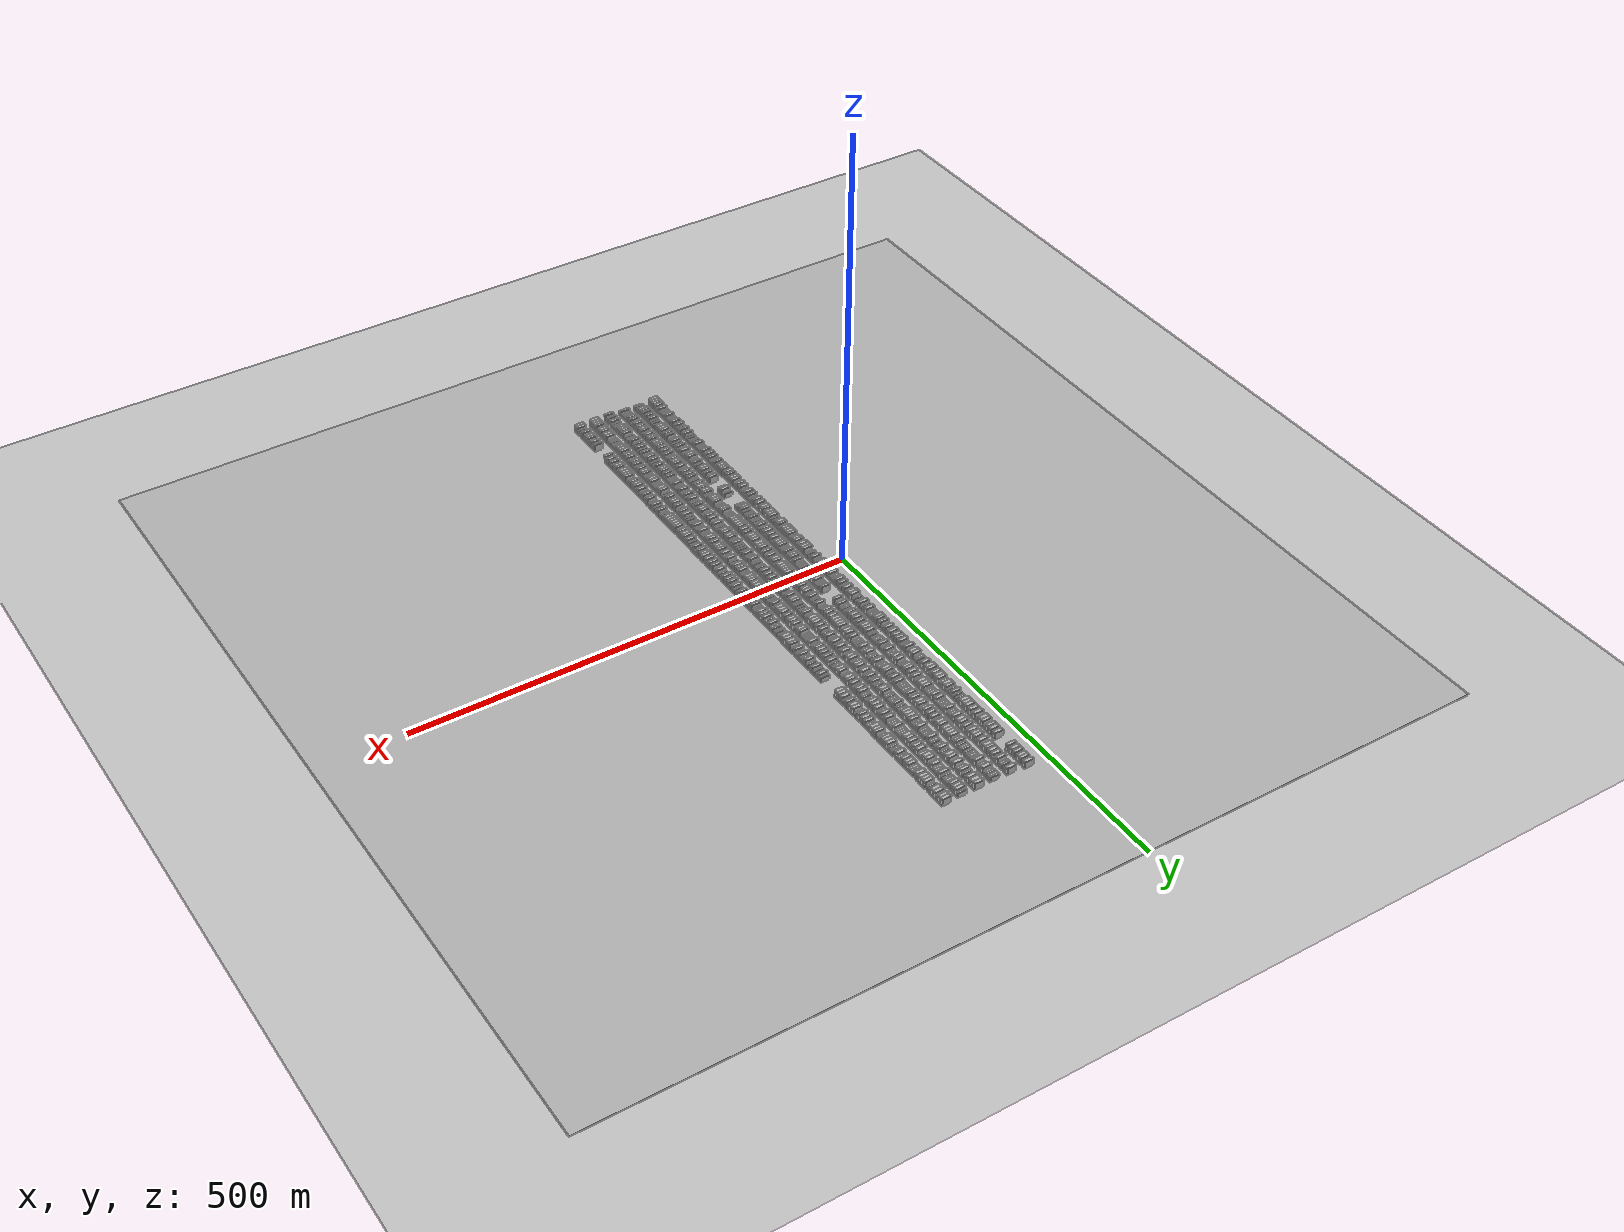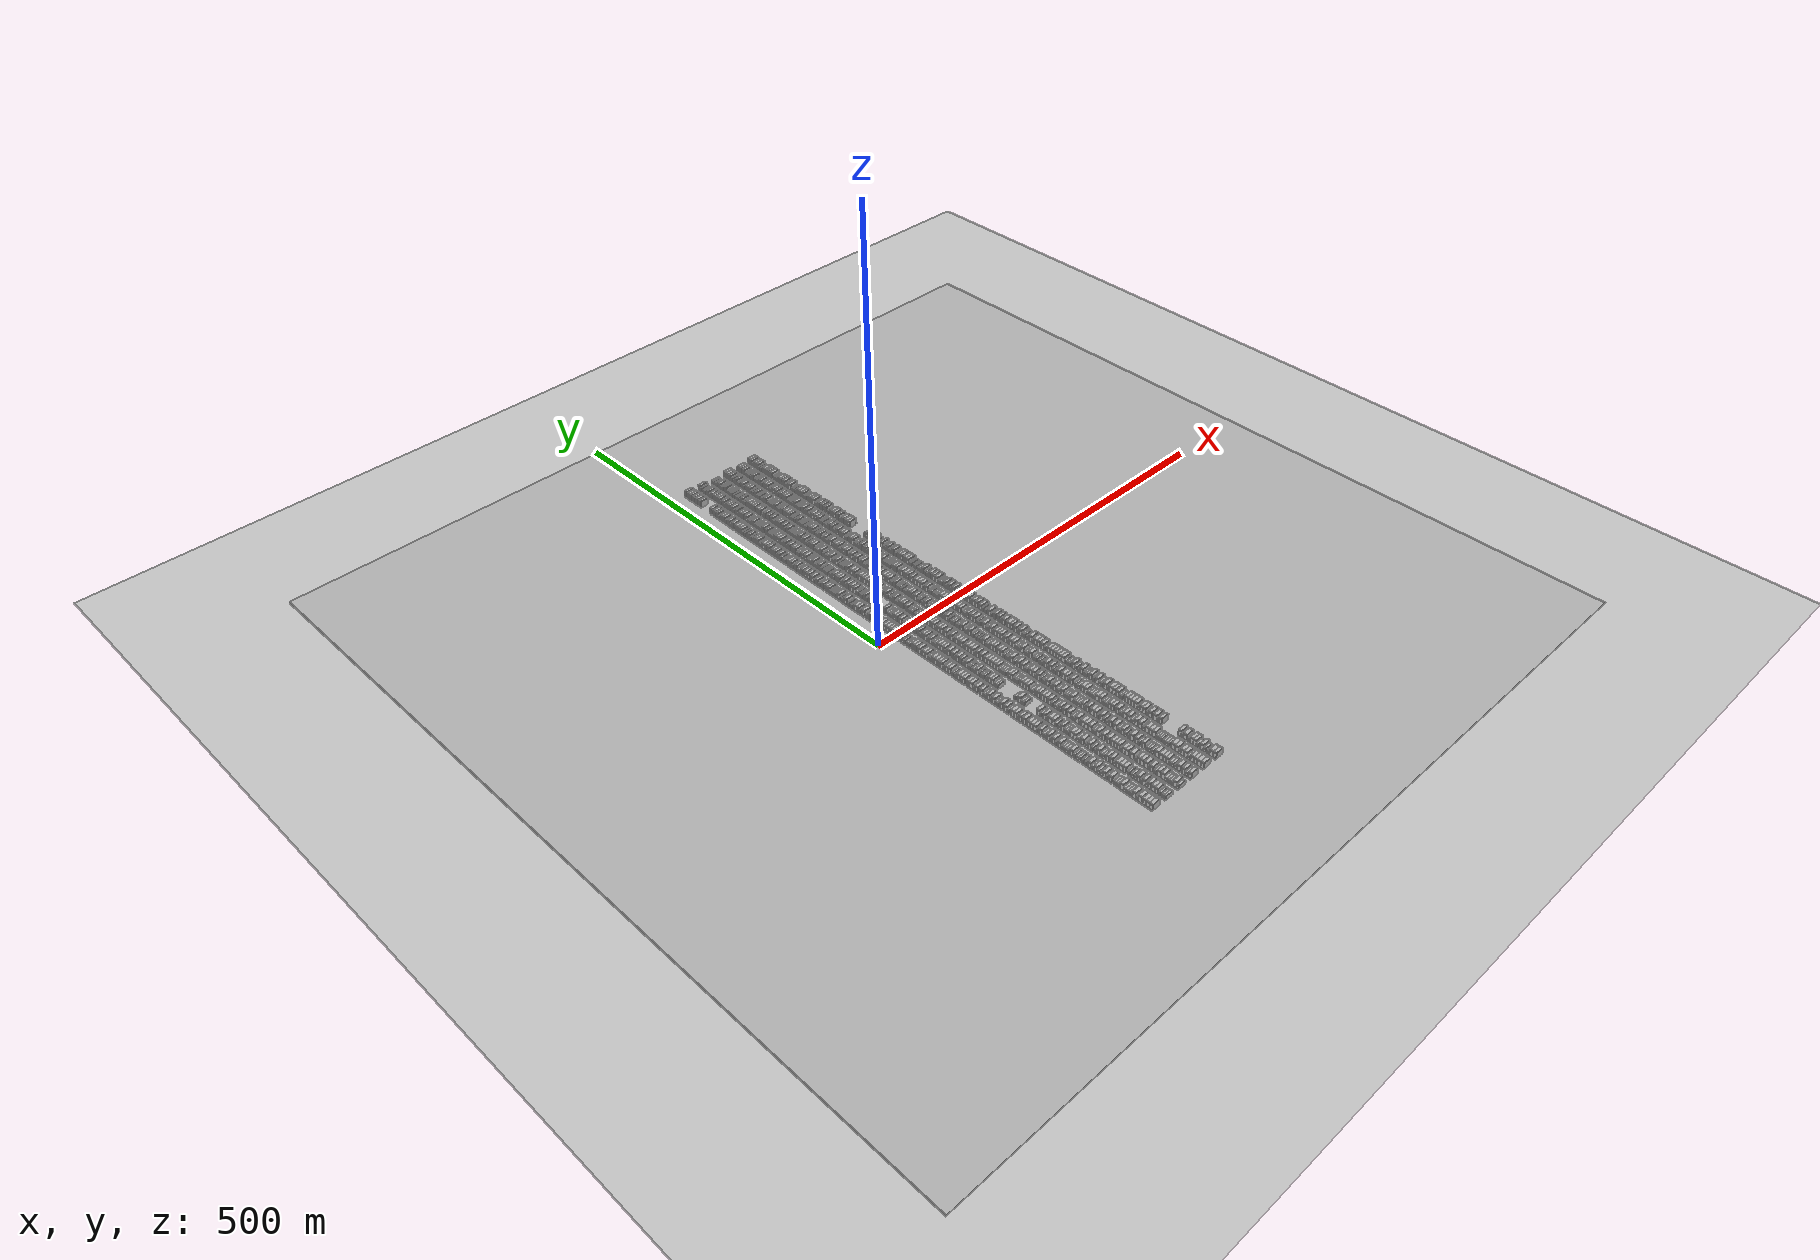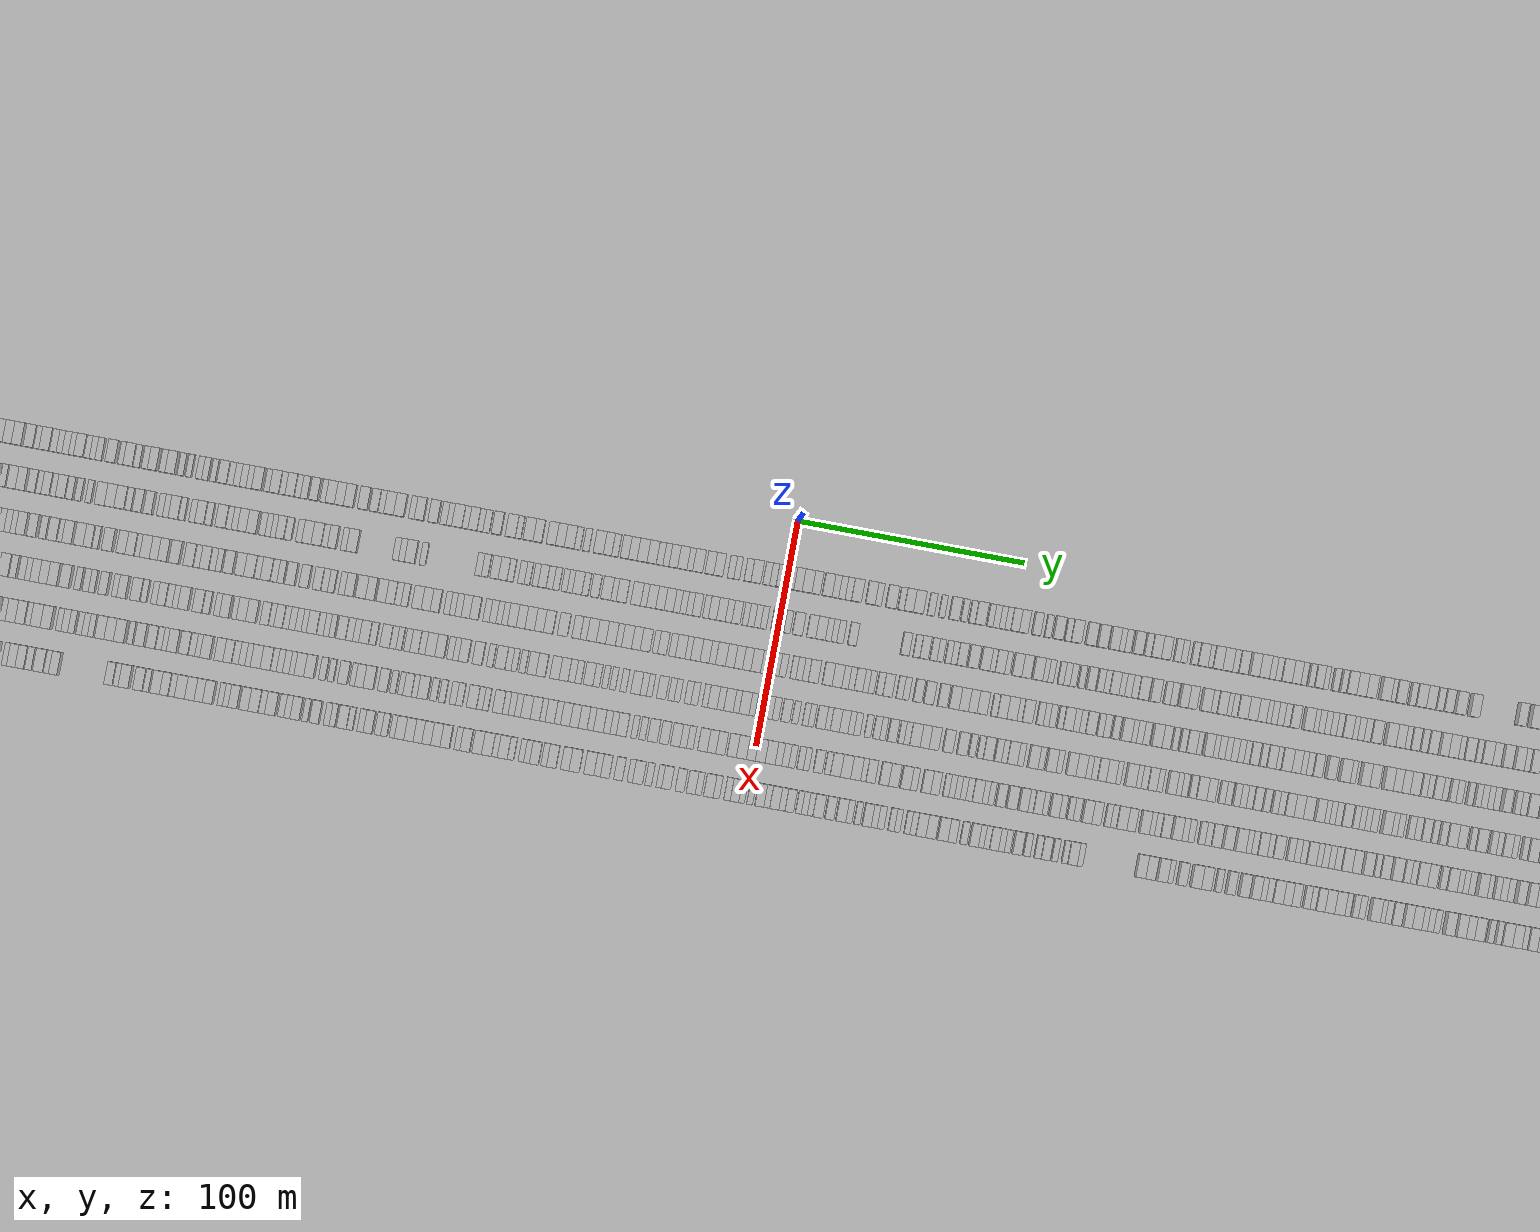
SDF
<?xml version="1.0" encoding="utf-8"?>

<sdf version="1.6">

   <world name="default">

      <gui fullscreen="0">

         <camera name="user_camera">

            <pose>-15 0 4.57585 0 0 0</pose>

            <view_controller>orbit</view_controller>

         </camera>

      </gui>

      <scene>

         <sky>

           <clouds>

             <speed>12</speed>

           </clouds>

         </sky>

         <ambient>0.4 0.4 0.4 1</ambient>

         <background>0.7 0.7 0.7 1</background>

         <shadows>1</shadows>

      </scene>

      <gravity>0 0 -9.8066</gravity>

      <magnetic_field>6e-06 2.3e-05 -4.2e-05</magnetic_field>

      <physics default="0" name="default_physics" type="ode">

         <ode>

            <solver>

               <type>quick</type>

               <iters>10</iters>

               <sor>1.0</sor>

               <use_dynamic_moi_rescaling>0</use_dynamic_moi_rescaling>

            </solver>

            <constraints>

               <cfm>0</cfm>

               <erp>0.2</erp>

               <contact_max_correcting_vel>100</contact_max_correcting_vel>

               <contact_surface_layer>0.001</contact_surface_layer>

            </constraints>

         </ode>

         <max_step_size>0.004</max_step_size>

         <real_time_factor>1</real_time_factor>

         <real_time_update_rate>250</real_time_update_rate>

      </physics>

      <light name="sun" type="directional">

         <cast_shadows>1</cast_shadows>

         <pose>0 0 10 0 0 0</pose>

         <diffuse>0.8 0.8 0.8 1</diffuse>

         <specular>0.2 0.2 0.2 1</specular>

         <attenuation>

            <range>1000</range>

            <constant>0.9</constant>

            <linear>0.01</linear>

            <quadratic>0.001</quadratic>

         </attenuation>

         <direction>-0.5 0.1 -0.9</direction>

      </light>

      <include>

         <name>ground_plane_1</name>

         <uri>model://HANNAS_ground_plane</uri>

         <pose>0 0 0  0 0 0</pose>

      </include>

      <include>

         <name>ground_plane_2</name>

         <uri>model://HANNAS_ground_plane</uri>

         <pose>100 0 0  0 0 0</pose>

      </include>

      <model name="building_1">

         <static>1</static>

         <pose frame="">25.0000 -347.8321 0 0.000000 0.000000 0.000000</pose>

         <link name="link">

            <pose frame="">0 0 4.50 0 0 0</pose>

            <collision name="collision">

               <geometry>

                  <box>

                     <size>10.0000 4.3358 9.0000</size>

                  </box>

               </geometry>

               <max_contacts>10</max_contacts>

               <surface>

                  <contact>

                     <ode/>

                  </contact>

                  <bounce/>

                  <friction>

                     <torsional>

                        <ode/>

                     </torsional>

                     <ode/>

                  </friction>

               </surface>

            </collision>

            <visual name="visual">

               <cast_shadows>0</cast_shadows>

               <geometry>

                  <box>

                     <size>10.0000 4.3358 9.0000</size>

                  </box>

               </geometry>

               <material>

                  <script>

                     <uri>model://HANNAS_wall/materials/scripts</uri>

                     <uri>model://HANNAS_wall/materials/textures</uri>

                     <name>vrc/HANNAS_wall</name>

                  </script>

               </material>

            </visual>

            <self_collide>0</self_collide>

            <enable_wind>0</enable_wind>

            <kinematic>0</kinematic>

         </link>

      </model>

      <model name="building_2">

         <static>1</static>

         <pose frame="">25.0000 -343.7193 0 0.000000 0.000000 0.000000</pose>

         <link name="link">

            <pose frame="">0 0 4.50 0 0 0</pose>

            <collision name="collision">

               <geometry>

                  <box>

                     <size>10.0000 3.8897 9.0000</size>

                  </box>

               </geometry>

               <max_contacts>10</max_contacts>

               <surface>

                  <contact>

                     <ode/>

                  </contact>

                  <bounce/>

                  <friction>

                     <torsional>

                        <ode/>

                     </torsional>

                     <ode/>

                  </friction>

               </surface>

            </collision>

            <visual name="visual">

               <cast_shadows>0</cast_shadows>

               <geometry>

                  <box>

                     <size>10.0000 3.8897 9.0000</size>

                  </box>

               </geometry>

               <material>

                  <script>

                     <uri>model://HANNAS_wall/materials/scripts</uri>

                     <uri>model://HANNAS_wall/materials/textures</uri>

                     <name>vrc/HANNAS_wall</name>

                  </script>

               </material>

            </visual>

            <self_collide>0</self_collide>

            <enable_wind>0</enable_wind>

            <kinematic>0</kinematic>

         </link>

      </model>

      <model name="building_3">

         <static>1</static>

         <pose frame="">25.0000 -339.6168 0 0.000000 0.000000 0.000000</pose>

         <link name="link">

            <pose frame="">0 0 4.50 0 0 0</pose>

            <collision name="collision">

               <geometry>

                  <box>

                     <size>10.0000 4.3153 9.0000</size>

                  </box>

               </geometry>

               <max_contacts>10</max_contacts>

               <surface>

                  <contact>

                     <ode/>

                  </contact>

                  <bounce/>

                  <friction>

                     <torsional>

                        <ode/>

                     </torsional>

                     <ode/>

                  </friction>

               </surface>

            </collision>

            <visual name="visual">

               <cast_shadows>0</cast_shadows>

               <geometry>

                  <box>

                     <size>10.0000 4.3153 9.0000</size>

                  </box>

               </geometry>

               <material>

                  <script>

                     <uri>model://HANNAS_wall/materials/scripts</uri>

                     <uri>model://HANNAS_wall/materials/textures</uri>

                     <name>vrc/HANNAS_wall</name>

                  </script>

               </material>

            </visual>

            <self_collide>0</self_collide>

            <enable_wind>0</enable_wind>

            <kinematic>0</kinematic>

         </link>

      </model>

      <model name="building_4">

         <static>1</static>

         <pose frame="">25.0000 -334.3568 0 0.000000 0.000000 0.000000</pose>

         <link name="link">

            <pose frame="">0 0 4.50 0 0 0</pose>

            <collision name="collision">

               <geometry>

                  <box>

                     <size>10.0000 4.2047 9.0000</size>

                  </box>

               </geometry>

               <max_contacts>10</max_contacts>

               <surface>

                  <contact>

                     <ode/>

                  </contact>

                  <bounce/>

                  <friction>

                     <torsional>

                        <ode/>

                     </torsional>

                     <ode/>

                  </friction>

               </surface>

            </collision>

            <visual name="visual">

               <cast_shadows>0</cast_shadows>

               <geometry>

                  <box>

                     <size>10.0000 4.2047 9.0000</size>

                  </box>

               </geometry>

               <material>

                  <script>

                     <uri>model://HANNAS_wall/materials/scripts</uri>

                     <uri>model://HANNAS_wall/materials/textures</uri>

                     <name>vrc/HANNAS_wall</name>

                  </script>

               </material>

            </visual>

            <self_collide>0</self_collide>

            <enable_wind>0</enable_wind>

            <kinematic>0</kinematic>

         </link>

      </model>

      <model name="building_5">

         <static>1</static>

         <pose frame="">25.0000 -330.8617 0 0.000000 0.000000 0.000000</pose>

         <link name="link">

            <pose frame="">0 0 3.00 0 0 0</pose>

            <collision name="collision">

               <geometry>

                  <box>

                     <size>10.0000 2.7855 6.0000</size>

                  </box>

               </geometry>

               <max_contacts>10</max_contacts>

               <surface>

                  <contact>

                     <ode/>

                  </contact>

                  <bounce/>

                  <friction>

                     <torsional>

                        <ode/>

                     </torsional>

                     <ode/>

                  </friction>

               </surface>

            </collision>

            <visual name="visual">

               <cast_shadows>0</cast_shadows>

               <geometry>

                  <box>

                     <size>10.0000 2.7855 6.0000</size>

                  </box>

               </geometry>

               <material>

                  <script>

                     <uri>model://HANNAS_wall/materials/scripts</uri>

                     <uri>model://HANNAS_wall/materials/textures</uri>

                     <name>vrc/HANNAS_wall</name>

                  </script>

               </material>

            </visual>

            <self_collide>0</self_collide>

            <enable_wind>0</enable_wind>

            <kinematic>0</kinematic>

         </link>

      </model>

      <model name="building_6">

         <static>1</static>

         <pose frame="">25.0000 -327.3317 0 0.000000 0.000000 0.000000</pose>

         <link name="link">

            <pose frame="">0 0 4.50 0 0 0</pose>

            <collision name="collision">

               <geometry>

                  <box>

                     <size>10.0000 4.2745 9.0000</size>

                  </box>

               </geometry>

               <max_contacts>10</max_contacts>

               <surface>

                  <contact>

                     <ode/>

                  </contact>

                  <bounce/>

                  <friction>

                     <torsional>

                        <ode/>

                     </torsional>

                     <ode/>

                  </friction>

               </surface>

            </collision>

            <visual name="visual">

               <cast_shadows>0</cast_shadows>

               <geometry>

                  <box>

                     <size>10.0000 4.2745 9.0000</size>

                  </box>

               </geometry>

               <material>

                  <script>

                     <uri>model://HANNAS_wall/materials/scripts</uri>

                     <uri>model://HANNAS_wall/materials/textures</uri>

                     <name>vrc/HANNAS_wall</name>

                  </script>

               </material>

            </visual>

            <self_collide>0</self_collide>

            <enable_wind>0</enable_wind>

            <kinematic>0</kinematic>

         </link>

      </model>

      <model name="building_7">

         <static>1</static>

         <pose frame="">25.0000 -323.7364 0 0.000000 0.000000 0.000000</pose>

         <link name="link">

            <pose frame="">0 0 3.00 0 0 0</pose>

            <collision name="collision">

               <geometry>

                  <box>

                     <size>10.0000 2.9162 6.0000</size>

                  </box>

               </geometry>

               <max_contacts>10</max_contacts>

               <surface>

                  <contact>

                     <ode/>

                  </contact>

                  <bounce/>

                  <friction>

                     <torsional>

                        <ode/>

                     </torsional>

                     <ode/>

                  </friction>

               </surface>

            </collision>

            <visual name="visual">

               <cast_shadows>0</cast_shadows>

               <geometry>

                  <box>

                     <size>10.0000 2.9162 6.0000</size>

                  </box>

               </geometry>

               <material>

                  <script>

                     <uri>model://HANNAS_wall/materials/scripts</uri>

                     <uri>model://HANNAS_wall/materials/textures</uri>

                     <name>vrc/HANNAS_wall</name>

                  </script>

               </material>

            </visual>

            <self_collide>0</self_collide>

            <enable_wind>0</enable_wind>

            <kinematic>0</kinematic>

         </link>

      </model>

      <model name="building_8">

         <static>1</static>

         <pose frame="">25.0000 -321.0220 0 0.000000 0.000000 0.000000</pose>

         <link name="link">

            <pose frame="">0 0 3.00 0 0 0</pose>

            <collision name="collision">

               <geometry>

                  <box>

                     <size>10.0000 2.5125 6.0000</size>

                  </box>

               </geometry>

               <max_contacts>10</max_contacts>

               <surface>

                  <contact>

                     <ode/>

                  </contact>

                  <bounce/>

                  <friction>

                     <torsional>

                        <ode/>

                     </torsional>

                     <ode/>

                  </friction>

               </surface>

            </collision>

            <visual name="visual">

               <cast_shadows>0</cast_shadows>

               <geometry>

                  <box>

                     <size>10.0000 2.5125 6.0000</size>

                  </box>

               </geometry>

               <material>

                  <script>

                     <uri>model://HANNAS_wall/materials/scripts</uri>

                     <uri>model://HANNAS_wall/materials/textures</uri>

                     <name>vrc/HANNAS_wall</name>

                  </script>

               </material>

            </visual>

            <self_collide>0</self_collide>

            <enable_wind>0</enable_wind>

            <kinematic>0</kinematic>

         </link>

      </model>

      <model name="building_9">

         <static>1</static>

         <pose frame="">25.0000 -318.3327 0 0.000000 0.000000 0.000000</pose>

         <link name="link">

            <pose frame="">0 0 3.00 0 0 0</pose>

            <collision name="collision">

               <geometry>

                  <box>

                     <size>10.0000 2.8662 6.0000</size>

                  </box>

               </geometry>

               <max_contacts>10</max_contacts>

               <surface>

                  <contact>

                     <ode/>

                  </contact>

                  <bounce/>

                  <friction>

                     <torsional>

                        <ode/>

                     </torsional>

                     <ode/>

                  </friction>

               </surface>

            </collision>

            <visual name="visual">

               <cast_shadows>0</cast_shadows>

               <geometry>

                  <box>

                     <size>10.0000 2.8662 6.0000</size>

                  </box>

               </geometry>

               <material>

                  <script>

                     <uri>model://HANNAS_wall/materials/scripts</uri>

                     <uri>model://HANNAS_wall/materials/textures</uri>

                     <name>vrc/HANNAS_wall</name>

                  </script>

               </material>

            </visual>

            <self_collide>0</self_collide>

            <enable_wind>0</enable_wind>

            <kinematic>0</kinematic>

         </link>

      </model>

      <model name="building_10">

         <static>1</static>

         <pose frame="">25.0000 -315.5656 0 0.000000 0.000000 0.000000</pose>

         <link name="link">

            <pose frame="">0 0 3.00 0 0 0</pose>

            <collision name="collision">

               <geometry>

                  <box>

                     <size>10.0000 2.6680 6.0000</size>

                  </box>

               </geometry>

               <max_contacts>10</max_contacts>

               <surface>

                  <contact>

                     <ode/>

                  </contact>

                  <bounce/>

                  <friction>

                     <torsional>

                        <ode/>

                     </torsional>

                     <ode/>

                  </friction>

               </surface>

            </collision>

            <visual name="visual">

               <cast_shadows>0</cast_shadows>

               <geometry>

                  <box>

                     <size>10.0000 2.6680 6.0000</size>

                  </box>

               </geometry>

               <material>

                  <script>

                     <uri>model://HANNAS_wall/materials/scripts</uri>

                     <uri>model://HANNAS_wall/materials/textures</uri>

                     <name>vrc/HANNAS_wall</name>

                  </script>

               </material>

            </visual>

            <self_collide>0</self_collide>

            <enable_wind>0</enable_wind>

            <kinematic>0</kinematic>

         </link>

      </model>

      <model name="building_11">

         <static>1</static>

         <pose frame="">25.0000 -312.1745 0 0.000000 0.000000 0.000000</pose>

         <link name="link">

            <pose frame="">0 0 4.50 0 0 0</pose>

            <collision name="collision">

               <geometry>

                  <box>

                     <size>10.0000 4.1141 9.0000</size>

                  </box>

               </geometry>

               <max_contacts>10</max_contacts>

               <surface>

                  <contact>

                     <ode/>

                  </contact>

                  <bounce/>

                  <friction>

                     <torsional>

                        <ode/>

                     </torsional>

                     <ode/>

                  </friction>

               </surface>

            </collision>

            <visual name="visual">

               <cast_shadows>0</cast_shadows>

               <geometry>

                  <box>

                     <size>10.0000 4.1141 9.0000</size>

                  </box>

               </geometry>

               <material>

                  <script>

                     <uri>model://HANNAS_wall/materials/scripts</uri>

                     <uri>model://HANNAS_wall/materials/textures</uri>

                     <name>vrc/HANNAS_wall</name>

                  </script>

               </material>

            </visual>

            <self_collide>0</self_collide>

            <enable_wind>0</enable_wind>

            <kinematic>0</kinematic>

         </link>

      </model>

      <model name="building_12">

         <static>1</static>

         <pose frame="">25.0000 -308.8851 0 0.000000 0.000000 0.000000</pose>

         <link name="link">

            <pose frame="">0 0 3.00 0 0 0</pose>

            <collision name="collision">

               <geometry>

                  <box>

                     <size>10.0000 2.4647 6.0000</size>

                  </box>

               </geometry>

               <max_contacts>10</max_contacts>

               <surface>

                  <contact>

                     <ode/>

                  </contact>

                  <bounce/>

                  <friction>

                     <torsional>

                        <ode/>

                     </torsional>

                     <ode/>

                  </friction>

               </surface>

            </collision>

            <visual name="visual">

               <cast_shadows>0</cast_shadows>

               <geometry>

                  <box>

                     <size>10.0000 2.4647 6.0000</size>

                  </box>

               </geometry>

               <material>

                  <script>

                     <uri>model://HANNAS_wall/materials/scripts</uri>

                     <uri>model://HANNAS_wall/materials/textures</uri>

                     <name>vrc/HANNAS_wall</name>

                  </script>

               </material>

            </visual>

            <self_collide>0</self_collide>

            <enable_wind>0</enable_wind>

            <kinematic>0</kinematic>

         </link>

      </model>

      <model name="building_13">

         <static>1</static>

         <pose frame="">25.0000 -306.4076 0 0.000000 0.000000 0.000000</pose>

         <link name="link">

            <pose frame="">0 0 3.00 0 0 0</pose>

            <collision name="collision">

               <geometry>

                  <box>

                     <size>10.0000 2.4903 6.0000</size>

                  </box>

               </geometry>

               <max_contacts>10</max_contacts>

               <surface>

                  <contact>

                     <ode/>

                  </contact>

                  <bounce/>

                  <friction>

                     <torsional>

                        <ode/>

                     </torsional>

                     <ode/>

                  </friction>

               </surface>

            </collision>

            <visual name="visual">

               <cast_shadows>0</cast_shadows>

               <geometry>

                  <box>

                     <size>10.0000 2.4903 6.0000</size>

                  </box>

               </geometry>

               <material>

                  <script>

                     <uri>model://HANNAS_wall/materials/scripts</uri>

                     <uri>model://HANNAS_wall/materials/textures</uri>

                     <name>vrc/HANNAS_wall</name>

                  </script>

               </material>

            </visual>

            <self_collide>0</self_collide>

            <enable_wind>0</enable_wind>

            <kinematic>0</kinematic>

         </link>

      </model>

      <model name="building_14">

         <static>1</static>

         <pose frame="">25.0000 -303.7652 0 0.000000 0.000000 0.000000</pose>

         <link name="link">

            <pose frame="">0 0 3.00 0 0 0</pose>

            <collision name="collision">

               <geometry>

                  <box>

                     <size>10.0000 2.7945 6.0000</size>

                  </box>

               </geometry>

               <max_contacts>10</max_contacts>

               <surface>

                  <contact>

                     <ode/>

                  </contact>

                  <bounce/>

                  <friction>

                     <torsional>

                        <ode/>

                     </torsional>

                     <ode/>

                  </friction>

               </surface>

            </collision>

            <visual name="visual">

               <cast_shadows>0</cast_shadows>

               <geometry>

                  <box>

                     <size>10.0000 2.7945 6.0000</size>

                  </box>

               </geometry>

               <material>

                  <script>

                     <uri>model://HANNAS_wall/materials/scripts</uri>

                     <uri>model://HANNAS_wall/materials/textures</uri>

                     <name>vrc/HANNAS_wall</name>

                  </script>

               </material>

            </visual>

            <self_collide>0</self_collide>

            <enable_wind>0</enable_wind>

            <kinematic>0</kinematic>

         </link>

      </model>

      <model name="building_15">

         <static>1</static>

         <pose frame="">25.0000 -298.2348 0 0.000000 0.000000 0.000000</pose>

         <link name="link">

            <pose frame="">0 0 4.50 0 0 0</pose>

            <collision name="collision">

               <geometry>

                  <box>

                     <size>10.0000 4.2664 9.0000</size>

                  </box>

               </geometry>

               <max_contacts>10</max_contacts>

               <surface>

                  <contact>

                     <ode/>

                  </contact>

                  <bounce/>

                  <friction>

                     <torsional>

                        <ode/>

                     </torsional>

                     <ode/>

                  </friction>

               </surface>

            </collision>

            <visual name="visual">

               <cast_shadows>0</cast_shadows>

               <geometry>

                  <box>

                     <size>10.0000 4.2664 9.0000</size>

                  </box>

               </geometry>

               <material>

                  <script>

                     <uri>model://HANNAS_wall/materials/scripts</uri>

                     <uri>model://HANNAS_wall/materials/textures</uri>

                     <name>vrc/HANNAS_wall</name>

                  </script>

               </material>

            </visual>

            <self_collide>0</self_collide>

            <enable_wind>0</enable_wind>

            <kinematic>0</kinematic>

         </link>

      </model>

      <model name="building_16">

         <static>1</static>

         <pose frame="">25.0000 -293.7850 0 0.000000 0.000000 0.000000</pose>

         <link name="link">

            <pose frame="">0 0 3.00 0 0 0</pose>

            <collision name="collision">

               <geometry>

                  <box>

                     <size>10.0000 2.6332 6.0000</size>

                  </box>

               </geometry>

               <max_contacts>10</max_contacts>

               <surface>

                  <contact>

                     <ode/>

                  </contact>

                  <bounce/>

                  <friction>

                     <torsional>

                        <ode/>

                     </torsional>

                     <ode/>

                  </friction>

               </surface>

            </collision>

            <visual name="visual">

               <cast_shadows>0</cast_shadows>

               <geometry>

                  <box>

                     <size>10.0000 2.6332 6.0000</size>

                  </box>

               </geometry>

               <material>

                  <script>

                     <uri>model://HANNAS_wall/materials/scripts</uri>

                     <uri>model://HANNAS_wall/materials/textures</uri>

                     <name>vrc/HANNAS_wall</name>

                  </script>

               </material>

            </visual>

            <self_collide>0</self_collide>

            <enable_wind>0</enable_wind>

            <kinematic>0</kinematic>

         </link>

      </model>

      <model name="building_17">

         <static>1</static>

         <pose frame="">25.0000 -290.3831 0 0.000000 0.000000 0.000000</pose>

         <link name="link">

            <pose frame="">0 0 4.50 0 0 0</pose>

            <collision name="collision">

               <geometry>

                  <box>

                     <size>10.0000 4.1705 9.0000</size>

                  </box>

               </geometry>

               <max_contacts>10</max_contacts>

               <surface>

                  <contact>

                     <ode/>

                  </contact>

                  <bounce/>

                  <friction>

                     <torsional>

                        <ode/>

                     </torsional>

                     <ode/>

                  </friction>

               </surface>

            </collision>

            <visual name="visual">

               <cast_shadows>0</cast_shadows>

               <geometry>

                  <box>

                     <size>10.0000 4.1705 9.0000</size>

                  </box>

               </geometry>

               <material>

                  <script>

                     <uri>model://HANNAS_wall/materials/scripts</uri>

                     <uri>model://HANNAS_wall/materials/textures</uri>

                     <name>vrc/HANNAS_wall</name>

                  </script>

               </material>

            </visual>

            <self_collide>0</self_collide>

            <enable_wind>0</enable_wind>

            <kinematic>0</kinematic>

         </link>

      </model>

      <model name="building_18">

         <static>1</static>

         <pose frame="">25.0000 -286.9610 0 0.000000 0.000000 0.000000</pose>

         <link name="link">

            <pose frame="">0 0 3.00 0 0 0</pose>

            <collision name="collision">

               <geometry>

                  <box>

                     <size>10.0000 2.6737 6.0000</size>

                  </box>

               </geometry>

               <max_contacts>10</max_contacts>

               <surface>

                  <contact>

                     <ode/>

                  </contact>

                  <bounce/>

                  <friction>

                     <torsional>

                        <ode/>

                     </torsional>

                     <ode/>

                  </friction>

               </surface>

            </collision>

            <visual name="visual">

               <cast_shadows>0</cast_shadows>

               <geometry>

                  <box>

                     <size>10.0000 2.6737 6.0000</size>

                  </box>

               </geometry>

               <material>

                  <script>

                     <uri>model://HANNAS_wall/materials/scripts</uri>

                     <uri>model://HANNAS_wall/materials/textures</uri>

                     <name>vrc/HANNAS_wall</name>

                  </script>

               </material>

            </visual>

            <self_collide>0</self_collide>

            <enable_wind>0</enable_wind>

            <kinematic>0</kinematic>

         </link>

      </model>

      <model name="building_19">

         <static>1</static>

         <pose frame="">25.0000 -283.1371 0 0.000000 0.000000 0.000000</pose>

         <link name="link">

            <pose frame="">0 0 3.00 0 0 0</pose>

            <collision name="collision">

               <geometry>

                  <box>

                     <size>10.0000 2.9742 6.0000</size>

                  </box>

               </geometry>

               <max_contacts>10</max_contacts>

               <surface>

                  <contact>

                     <ode/>

                  </contact>

                  <bounce/>

                  <friction>

                     <torsional>

                        <ode/>

                     </torsional>

                     <ode/>

                  </friction>

               </surface>

            </collision>

            <visual name="visual">

               <cast_shadows>0</cast_shadows>

               <geometry>

                  <box>

                     <size>10.0000 2.9742 6.0000</size>

                  </box>

               </geometry>

               <material>

                  <script>

                     <uri>model://HANNAS_wall/materials/scripts</uri>

                     <uri>model://HANNAS_wall/materials/textures</uri>

                     <name>vrc/HANNAS_wall</name>

                  </script>

               </material>

            </visual>

            <self_collide>0</self_collide>

            <enable_wind>0</enable_wind>

            <kinematic>0</kinematic>

         </link>

      </model>

      <model name="building_20">

         <static>1</static>

         <pose frame="">25.0000 -279.7778 0 0.000000 0.000000 0.000000</pose>

         <link name="link">

            <pose frame="">0 0 4.50 0 0 0</pose>

            <collision name="collision">

               <geometry>

                  <box>

                     <size>10.0000 3.7445 9.0000</size>

                  </box>

               </geometry>

               <max_contacts>10</max_contacts>

               <surface>

                  <contact>

                     <ode/>

                  </contact>

                  <bounce/>

                  <friction>

                     <torsional>

                        <ode/>

                     </torsional>

                     <ode/>

                  </friction>

               </surface>

            </collision>

            <visual name="visual">

               <cast_shadows>0</cast_shadows>

               <geometry>

                  <box>

                     <size>10.0000 3.7445 9.0000</size>

                  </box>

               </geometry>

               <material>

                  <script>

                     <uri>model://HANNAS_wall/materials/scripts</uri>

                     <uri>model://HANNAS_wall/materials/textures</uri>

                     <name>vrc/HANNAS_wall</name>

                  </script>

               </material>

            </visual>

            <self_collide>0</self_collide>

            <enable_wind>0</enable_wind>

            <kinematic>0</kinematic>

         </link>

      </model>

      <model name="building_21">

         <static>1</static>

         <pose frame="">25.0000 -275.4175 0 0.000000 0.000000 0.000000</pose>

         <link name="link">

            <pose frame="">0 0 3.00 0 0 0</pose>

            <collision name="collision">

               <geometry>

                  <box>

                     <size>10.0000 2.9760 6.0000</size>

                  </box>

               </geometry>

               <max_contacts>10</max_contacts>

               <surface>

                  <contact>

                     <ode/>

                  </contact>

                  <bounce/>

                  <friction>

                     <torsional>

                        <ode/>

                     </torsional>

                     <ode/>

                  </friction>

               </surface>

            </collision>

            <visual name="visual">

               <cast_shadows>0</cast_shadows>

               <geometry>

                  <box>

                     <size>10.0000 2.9760 6.0000</size>

                  </box>

               </geometry>

               <material>

                  <script>

                     <uri>model://HANNAS_wall/materials/scripts</uri>

                     <uri>model://HANNAS_wall/materials/textures</uri>

                     <name>vrc/HANNAS_wall</name>

                  </script>

               </material>

            </visual>

            <self_collide>0</self_collide>

            <enable_wind>0</enable_wind>

            <kinematic>0</kinematic>

         </link>

      </model>

      <model name="building_22">

         <static>1</static>

         <pose frame="">25.0000 -271.8664 0 0.000000 0.000000 0.000000</pose>

         <link name="link">

            <pose frame="">0 0 4.50 0 0 0</pose>

            <collision name="collision">

               <geometry>

                  <box>

                     <size>10.0000 4.1263 9.0000</size>

                  </box>

               </geometry>

               <max_contacts>10</max_contacts>

               <surface>

                  <contact>

                     <ode/>

                  </contact>

                  <bounce/>

                  <friction>

                     <torsional>

                        <ode/>

                     </torsional>

                     <ode/>

                  </friction>

               </surface>

            </collision>

            <visual name="visual">

               <cast_shadows>0</cast_shadows>

               <geometry>

                  <box>

                     <size>10.0000 4.1263 9.0000</size>

                  </box>

               </geometry>

               <material>

                  <script>

                     <uri>model://HANNAS_wall/materials/scripts</uri>

                     <uri>model://HANNAS_wall/materials/textures</uri>

                     <name>vrc/HANNAS_wall</name>

                  </script>

               </material>

            </visual>

            <self_collide>0</self_collide>

            <enable_wind>0</enable_wind>

            <kinematic>0</kinematic>

         </link>

      </model>

      <model name="building_23">

         <static>1</static>

         <pose frame="">25.0000 -267.4942 0 0.000000 0.000000 0.000000</pose>

         <link name="link">

            <pose frame="">0 0 3.00 0 0 0</pose>

            <collision name="collision">

               <geometry>

                  <box>

                     <size>10.0000 2.6182 6.0000</size>

                  </box>

               </geometry>

               <max_contacts>10</max_contacts>

               <surface>

                  <contact>

                     <ode/>

                  </contact>

                  <bounce/>

                  <friction>

                     <torsional>

                        <ode/>

                     </torsional>

                     <ode/>

                  </friction>

               </surface>

            </collision>

            <visual name="visual">

               <cast_shadows>0</cast_shadows>

               <geometry>

                  <box>

                     <size>10.0000 2.6182 6.0000</size>

                  </box>

               </geometry>

               <material>

                  <script>

                     <uri>model://HANNAS_wall/materials/scripts</uri>

                     <uri>model://HANNAS_wall/materials/textures</uri>

                     <name>vrc/HANNAS_wall</name>

                  </script>

               </material>

            </visual>

            <self_collide>0</self_collide>

            <enable_wind>0</enable_wind>

            <kinematic>0</kinematic>

         </link>

      </model>

      <model name="building_24">

         <static>1</static>

         <pose frame="">25.0000 -263.9777 0 0.000000 0.000000 0.000000</pose>

         <link name="link">

            <pose frame="">0 0 3.00 0 0 0</pose>

            <collision name="collision">

               <geometry>

                  <box>

                     <size>10.0000 2.4146 6.0000</size>

                  </box>

               </geometry>

               <max_contacts>10</max_contacts>

               <surface>

                  <contact>

                     <ode/>

                  </contact>

                  <bounce/>

                  <friction>

                     <torsional>

                        <ode/>

                     </torsional>

                     <ode/>

                  </friction>

               </surface>

            </collision>

            <visual name="visual">

               <cast_shadows>0</cast_shadows>

               <geometry>

                  <box>

                     <size>10.0000 2.4146 6.0000</size>

                  </box>

               </geometry>

               <material>

                  <script>

                     <uri>model://HANNAS_wall/materials/scripts</uri>

                     <uri>model://HANNAS_wall/materials/textures</uri>

                     <name>vrc/HANNAS_wall</name>

                  </script>

               </material>

            </visual>

            <self_collide>0</self_collide>

            <enable_wind>0</enable_wind>

            <kinematic>0</kinematic>

         </link>

      </model>

      <model name="building_25">

         <static>1</static>

         <pose frame="">25.0000 -259.4005 0 0.000000 0.000000 0.000000</pose>

         <link name="link">

            <pose frame="">0 0 3.00 0 0 0</pose>

            <collision name="collision">

               <geometry>

                  <box>

                     <size>10.0000 2.7399 6.0000</size>

                  </box>

               </geometry>

               <max_contacts>10</max_contacts>

               <surface>

                  <contact>

                     <ode/>

                  </contact>

                  <bounce/>

                  <friction>

                     <torsional>

                        <ode/>

                     </torsional>

                     <ode/>

                  </friction>

               </surface>

            </collision>

            <visual name="visual">

               <cast_shadows>0</cast_shadows>

               <geometry>

                  <box>

                     <size>10.0000 2.7399 6.0000</size>

                  </box>

               </geometry>

               <material>

                  <script>

                     <uri>model://HANNAS_wall/materials/scripts</uri>

                     <uri>model://HANNAS_wall/materials/textures</uri>

                     <name>vrc/HANNAS_wall</name>

                  </script>

               </material>

            </visual>

            <self_collide>0</self_collide>

            <enable_wind>0</enable_wind>

            <kinematic>0</kinematic>

         </link>

      </model>

      <model name="building_26">

         <static>1</static>

         <pose frame="">25.0000 -256.7224 0 0.000000 0.000000 0.000000</pose>

         <link name="link">

            <pose frame="">0 0 3.00 0 0 0</pose>

            <collision name="collision">

               <geometry>

                  <box>

                     <size>10.0000 2.6163 6.0000</size>

                  </box>

               </geometry>

               <max_contacts>10</max_contacts>

               <surface>

                  <contact>

                     <ode/>

                  </contact>

                  <bounce/>

                  <friction>

                     <torsional>

                        <ode/>

                     </torsional>

                     <ode/>

                  </friction>

               </surface>

            </collision>

            <visual name="visual">

               <cast_shadows>0</cast_shadows>

               <geometry>

                  <box>

                     <size>10.0000 2.6163 6.0000</size>

                  </box>

               </geometry>

               <material>

                  <script>

                     <uri>model://HANNAS_wall/materials/scripts</uri>

                     <uri>model://HANNAS_wall/materials/textures</uri>

                     <name>vrc/HANNAS_wall</name>

                  </script>

               </material>

            </visual>

            <self_collide>0</self_collide>

            <enable_wind>0</enable_wind>

            <kinematic>0</kinematic>

         </link>

      </model>

      <model name="building_27">

         <static>1</static>

         <pose frame="">25.0000 -253.2048 0 0.000000 0.000000 0.000000</pose>

         <link name="link">

            <pose frame="">0 0 3.00 0 0 0</pose>

            <collision name="collision">

               <geometry>

                  <box>

                     <size>10.0000 2.4189 6.0000</size>

                  </box>

               </geometry>

               <max_contacts>10</max_contacts>

               <surface>

                  <contact>

                     <ode/>

                  </contact>

                  <bounce/>

                  <friction>

                     <torsional>

                        <ode/>

                     </torsional>

                     <ode/>

                  </friction>

               </surface>

            </collision>

            <visual name="visual">

               <cast_shadows>0</cast_shadows>

               <geometry>

                  <box>

                     <size>10.0000 2.4189 6.0000</size>

                  </box>

               </geometry>

               <material>

                  <script>

                     <uri>model://HANNAS_wall/materials/scripts</uri>

                     <uri>model://HANNAS_wall/materials/textures</uri>

                     <name>vrc/HANNAS_wall</name>

                  </script>

               </material>

            </visual>

            <self_collide>0</self_collide>

            <enable_wind>0</enable_wind>

            <kinematic>0</kinematic>

         </link>

      </model>

      <model name="building_28">

         <static>1</static>

         <pose frame="">25.0000 -248.9060 0 0.000000 0.000000 0.000000</pose>

         <link name="link">

            <pose frame="">0 0 4.50 0 0 0</pose>

            <collision name="collision">

               <geometry>

                  <box>

                     <size>10.0000 4.1788 9.0000</size>

                  </box>

               </geometry>

               <max_contacts>10</max_contacts>

               <surface>

                  <contact>

                     <ode/>

                  </contact>

                  <bounce/>

                  <friction>

                     <torsional>

                        <ode/>

                     </torsional>

                     <ode/>

                  </friction>

               </surface>

            </collision>

            <visual name="visual">

               <cast_shadows>0</cast_shadows>

               <geometry>

                  <box>

                     <size>10.0000 4.1788 9.0000</size>

                  </box>

               </geometry>

               <material>

                  <script>

                     <uri>model://HANNAS_wall/materials/scripts</uri>

                     <uri>model://HANNAS_wall/materials/textures</uri>

                     <name>vrc/HANNAS_wall</name>

                  </script>

               </material>

            </visual>

            <self_collide>0</self_collide>

            <enable_wind>0</enable_wind>

            <kinematic>0</kinematic>

         </link>

      </model>

      <model name="building_29">

         <static>1</static>

         <pose frame="">25.0000 -245.4936 0 0.000000 0.000000 0.000000</pose>

         <link name="link">

            <pose frame="">0 0 3.00 0 0 0</pose>

            <collision name="collision">

               <geometry>

                  <box>

                     <size>10.0000 2.6460 6.0000</size>

                  </box>

               </geometry>

               <max_contacts>10</max_contacts>

               <surface>

                  <contact>

                     <ode/>

                  </contact>

                  <bounce/>

                  <friction>

                     <torsional>

                        <ode/>

                     </torsional>

                     <ode/>

                  </friction>

               </surface>

            </collision>

            <visual name="visual">

               <cast_shadows>0</cast_shadows>

               <geometry>

                  <box>

                     <size>10.0000 2.6460 6.0000</size>

                  </box>

               </geometry>

               <material>

                  <script>

                     <uri>model://HANNAS_wall/materials/scripts</uri>

                     <uri>model://HANNAS_wall/materials/textures</uri>

                     <name>vrc/HANNAS_wall</name>

                  </script>

               </material>

            </visual>

            <self_collide>0</self_collide>

            <enable_wind>0</enable_wind>

            <kinematic>0</kinematic>

         </link>

      </model>

      <model name="building_30">

         <static>1</static>

         <pose frame="">25.0000 -242.7569 0 0.000000 0.000000 0.000000</pose>

         <link name="link">

            <pose frame="">0 0 3.00 0 0 0</pose>

            <collision name="collision">

               <geometry>

                  <box>

                     <size>10.0000 2.8274 6.0000</size>

                  </box>

               </geometry>

               <max_contacts>10</max_contacts>

               <surface>

                  <contact>

                     <ode/>

                  </contact>

                  <bounce/>

                  <friction>

                     <torsional>

                        <ode/>

                     </torsional>

                     <ode/>

                  </friction>

               </surface>

            </collision>

            <visual name="visual">

               <cast_shadows>0</cast_shadows>

               <geometry>

                  <box>

                     <size>10.0000 2.8274 6.0000</size>

                  </box>

               </geometry>

               <material>

                  <script>

                     <uri>model://HANNAS_wall/materials/scripts</uri>

                     <uri>model://HANNAS_wall/materials/textures</uri>

                     <name>vrc/HANNAS_wall</name>

                  </script>

               </material>

            </visual>

            <self_collide>0</self_collide>

            <enable_wind>0</enable_wind>

            <kinematic>0</kinematic>

         </link>

      </model>

      <model name="building_31">

         <static>1</static>

         <pose frame="">25.0000 -239.8833 0 0.000000 0.000000 0.000000</pose>

         <link name="link">

            <pose frame="">0 0 3.00 0 0 0</pose>

            <collision name="collision">

               <geometry>

                  <box>

                     <size>10.0000 2.9197 6.0000</size>

                  </box>

               </geometry>

               <max_contacts>10</max_contacts>

               <surface>

                  <contact>

                     <ode/>

                  </contact>

                  <bounce/>

                  <friction>

                     <torsional>

                        <ode/>

                     </torsional>

                     <ode/>

                  </friction>

               </surface>

            </collision>

            <visual name="visual">

               <cast_shadows>0</cast_shadows>

               <geometry>

                  <box>

                     <size>10.0000 2.9197 6.0000</size>

                  </box>

               </geometry>

               <material>

                  <script>

                     <uri>model://HANNAS_wall/materials/scripts</uri>

                     <uri>model://HANNAS_wall/materials/textures</uri>

                     <name>vrc/HANNAS_wall</name>

                  </script>

               </material>

            </visual>

            <self_collide>0</self_collide>

            <enable_wind>0</enable_wind>

            <kinematic>0</kinematic>

         </link>

      </model>

      <model name="building_32">

         <static>1</static>

         <pose frame="">25.0000 -237.0755 0 0.000000 0.000000 0.000000</pose>

         <link name="link">

            <pose frame="">0 0 3.00 0 0 0</pose>

            <collision name="collision">

               <geometry>

                  <box>

                     <size>10.0000 2.6959 6.0000</size>

                  </box>

               </geometry>

               <max_contacts>10</max_contacts>

               <surface>

                  <contact>

                     <ode/>

                  </contact>

                  <bounce/>

                  <friction>

                     <torsional>

                        <ode/>

                     </torsional>

                     <ode/>

                  </friction>

               </surface>

            </collision>

            <visual name="visual">

               <cast_shadows>0</cast_shadows>

               <geometry>

                  <box>

                     <size>10.0000 2.6959 6.0000</size>

                  </box>

               </geometry>

               <material>

                  <script>

                     <uri>model://HANNAS_wall/materials/scripts</uri>

                     <uri>model://HANNAS_wall/materials/textures</uri>

                     <name>vrc/HANNAS_wall</name>

                  </script>

               </material>

            </visual>

            <self_collide>0</self_collide>

            <enable_wind>0</enable_wind>

            <kinematic>0</kinematic>

         </link>

      </model>

      <model name="building_33">

         <static>1</static>

         <pose frame="">25.0000 -233.6573 0 0.000000 0.000000 0.000000</pose>

         <link name="link">

            <pose frame="">0 0 4.50 0 0 0</pose>

            <collision name="collision">

               <geometry>

                  <box>

                     <size>10.0000 4.1404 9.0000</size>

                  </box>

               </geometry>

               <max_contacts>10</max_contacts>

               <surface>

                  <contact>

                     <ode/>

                  </contact>

                  <bounce/>

                  <friction>

                     <torsional>

                        <ode/>

                     </torsional>

                     <ode/>

                  </friction>

               </surface>

            </collision>

            <visual name="visual">

               <cast_shadows>0</cast_shadows>

               <geometry>

                  <box>

                     <size>10.0000 4.1404 9.0000</size>

                  </box>

               </geometry>

               <material>

                  <script>

                     <uri>model://HANNAS_wall/materials/scripts</uri>

                     <uri>model://HANNAS_wall/materials/textures</uri>

                     <name>vrc/HANNAS_wall</name>

                  </script>

               </material>

            </visual>

            <self_collide>0</self_collide>

            <enable_wind>0</enable_wind>

            <kinematic>0</kinematic>

         </link>

      </model>

      <model name="building_34">

         <static>1</static>

         <pose frame="">25.0000 -229.2553 0 0.000000 0.000000 0.000000</pose>

         <link name="link">

            <pose frame="">0 0 3.00 0 0 0</pose>

            <collision name="collision">

               <geometry>

                  <box>

                     <size>10.0000 2.6637 6.0000</size>

                  </box>

               </geometry>

               <max_contacts>10</max_contacts>

               <surface>

                  <contact>

                     <ode/>

                  </contact>

                  <bounce/>

                  <friction>

                     <torsional>

                        <ode/>

                     </torsional>

                     <ode/>

                  </friction>

               </surface>

            </collision>

            <visual name="visual">

               <cast_shadows>0</cast_shadows>

               <geometry>

                  <box>

                     <size>10.0000 2.6637 6.0000</size>

                  </box>

               </geometry>

               <material>

                  <script>

                     <uri>model://HANNAS_wall/materials/scripts</uri>

                     <uri>model://HANNAS_wall/materials/textures</uri>

                     <name>vrc/HANNAS_wall</name>

                  </script>

               </material>

            </visual>

            <self_collide>0</self_collide>

            <enable_wind>0</enable_wind>

            <kinematic>0</kinematic>

         </link>

      </model>

      <model name="building_35">

         <static>1</static>

         <pose frame="">25.0000 -225.8399 0 0.000000 0.000000 0.000000</pose>

         <link name="link">

            <pose frame="">0 0 4.50 0 0 0</pose>

            <collision name="collision">

               <geometry>

                  <box>

                     <size>10.0000 4.1670 9.0000</size>

                  </box>

               </geometry>

               <max_contacts>10</max_contacts>

               <surface>

                  <contact>

                     <ode/>

                  </contact>

                  <bounce/>

                  <friction>

                     <torsional>

                        <ode/>

                     </torsional>

                     <ode/>

                  </friction>

               </surface>

            </collision>

            <visual name="visual">

               <cast_shadows>0</cast_shadows>

               <geometry>

                  <box>

                     <size>10.0000 4.1670 9.0000</size>

                  </box>

               </geometry>

               <material>

                  <script>

                     <uri>model://HANNAS_wall/materials/scripts</uri>

                     <uri>model://HANNAS_wall/materials/textures</uri>

                     <name>vrc/HANNAS_wall</name>

                  </script>

               </material>

            </visual>

            <self_collide>0</self_collide>

            <enable_wind>0</enable_wind>

            <kinematic>0</kinematic>

         </link>

      </model>

      <model name="building_36">

         <static>1</static>

         <pose frame="">25.0000 -222.3506 0 0.000000 0.000000 0.000000</pose>

         <link name="link">

            <pose frame="">0 0 3.00 0 0 0</pose>

            <collision name="collision">

               <geometry>

                  <box>

                     <size>10.0000 2.8117 6.0000</size>

                  </box>

               </geometry>

               <max_contacts>10</max_contacts>

               <surface>

                  <contact>

                     <ode/>

                  </contact>

                  <bounce/>

                  <friction>

                     <torsional>

                        <ode/>

                     </torsional>

                     <ode/>

                  </friction>

               </surface>

            </collision>

            <visual name="visual">

               <cast_shadows>0</cast_shadows>

               <geometry>

                  <box>

                     <size>10.0000 2.8117 6.0000</size>

                  </box>

               </geometry>

               <material>

                  <script>

                     <uri>model://HANNAS_wall/materials/scripts</uri>

                     <uri>model://HANNAS_wall/materials/textures</uri>

                     <name>vrc/HANNAS_wall</name>

                  </script>

               </material>

            </visual>

            <self_collide>0</self_collide>

            <enable_wind>0</enable_wind>

            <kinematic>0</kinematic>

         </link>

      </model>

      <model name="building_37">

         <static>1</static>

         <pose frame="">25.0000 -218.9679 0 0.000000 0.000000 0.000000</pose>

         <link name="link">

            <pose frame="">0 0 4.50 0 0 0</pose>

            <collision name="collision">

               <geometry>

                  <box>

                     <size>10.0000 3.9536 9.0000</size>

                  </box>

               </geometry>

               <max_contacts>10</max_contacts>

               <surface>

                  <contact>

                     <ode/>

                  </contact>

                  <bounce/>

                  <friction>

                     <torsional>

                        <ode/>

                     </torsional>

                     <ode/>

                  </friction>

               </surface>

            </collision>

            <visual name="visual">

               <cast_shadows>0</cast_shadows>

               <geometry>

                  <box>

                     <size>10.0000 3.9536 9.0000</size>

                  </box>

               </geometry>

               <material>

                  <script>

                     <uri>model://HANNAS_wall/materials/scripts</uri>

                     <uri>model://HANNAS_wall/materials/textures</uri>

                     <name>vrc/HANNAS_wall</name>

                  </script>

               </material>

            </visual>

            <self_collide>0</self_collide>

            <enable_wind>0</enable_wind>

            <kinematic>0</kinematic>

         </link>

      </model>

      <model name="building_38">

         <static>1</static>

         <pose frame="">25.0000 -215.7064 0 0.000000 0.000000 0.000000</pose>

         <link name="link">

            <pose frame="">0 0 3.00 0 0 0</pose>

            <collision name="collision">

               <geometry>

                  <box>

                     <size>10.0000 2.5694 6.0000</size>

                  </box>

               </geometry>

               <max_contacts>10</max_contacts>

               <surface>

                  <contact>

                     <ode/>

                  </contact>

                  <bounce/>

                  <friction>

                     <torsional>

                        <ode/>

                     </torsional>

                     <ode/>

                  </friction>

               </surface>

            </collision>

            <visual name="visual">

               <cast_shadows>0</cast_shadows>

               <geometry>

                  <box>

                     <size>10.0000 2.5694 6.0000</size>

                  </box>

               </geometry>

               <material>

                  <script>

                     <uri>model://HANNAS_wall/materials/scripts</uri>

                     <uri>model://HANNAS_wall/materials/textures</uri>

                     <name>vrc/HANNAS_wall</name>

                  </script>

               </material>

            </visual>

            <self_collide>0</self_collide>

            <enable_wind>0</enable_wind>

            <kinematic>0</kinematic>

         </link>

      </model>

      <model name="building_39">

         <static>1</static>

         <pose frame="">25.0000 -212.9363 0 0.000000 0.000000 0.000000</pose>

         <link name="link">

            <pose frame="">0 0 3.00 0 0 0</pose>

            <collision name="collision">

               <geometry>

                  <box>

                     <size>10.0000 2.9708 6.0000</size>

                  </box>

               </geometry>

               <max_contacts>10</max_contacts>

               <surface>

                  <contact>

                     <ode/>

                  </contact>

                  <bounce/>

                  <friction>

                     <torsional>

                        <ode/>

                     </torsional>

                     <ode/>

                  </friction>

               </surface>

            </collision>

            <visual name="visual">

               <cast_shadows>0</cast_shadows>

               <geometry>

                  <box>

                     <size>10.0000 2.9708 6.0000</size>

                  </box>

               </geometry>

               <material>

                  <script>

                     <uri>model://HANNAS_wall/materials/scripts</uri>

                     <uri>model://HANNAS_wall/materials/textures</uri>

                     <name>vrc/HANNAS_wall</name>

                  </script>

               </material>

            </visual>

            <self_collide>0</self_collide>

            <enable_wind>0</enable_wind>

            <kinematic>0</kinematic>

         </link>

      </model>

      <model name="building_40">

         <static>1</static>

         <pose frame="">25.0000 -208.6132 0 0.000000 0.000000 0.000000</pose>

         <link name="link">

            <pose frame="">0 0 4.50 0 0 0</pose>

            <collision name="collision">

               <geometry>

                  <box>

                     <size>10.0000 3.6755 9.0000</size>

                  </box>

               </geometry>

               <max_contacts>10</max_contacts>

               <surface>

                  <contact>

                     <ode/>

                  </contact>

                  <bounce/>

                  <friction>

                     <torsional>

                        <ode/>

                     </torsional>

                     <ode/>

                  </friction>

               </surface>

            </collision>

            <visual name="visual">

               <cast_shadows>0</cast_shadows>

               <geometry>

                  <box>

                     <size>10.0000 3.6755 9.0000</size>

                  </box>

               </geometry>

               <material>

                  <script>

                     <uri>model://HANNAS_wall/materials/scripts</uri>

                     <uri>model://HANNAS_wall/materials/textures</uri>

                     <name>vrc/HANNAS_wall</name>

                  </script>

               </material>

            </visual>

            <self_collide>0</self_collide>

            <enable_wind>0</enable_wind>

            <kinematic>0</kinematic>

         </link>

      </model>

      <model name="building_41">

         <static>1</static>

         <pose frame="">25.0000 -204.4969 0 0.000000 0.000000 0.000000</pose>

         <link name="link">

            <pose frame="">0 0 3.00 0 0 0</pose>

            <collision name="collision">

               <geometry>

                  <box>

                     <size>10.0000 2.5571 6.0000</size>

                  </box>

               </geometry>

               <max_contacts>10</max_contacts>

               <surface>

                  <contact>

                     <ode/>

                  </contact>

                  <bounce/>

                  <friction>

                     <torsional>

                        <ode/>

                     </torsional>

                     <ode/>

                  </friction>

               </surface>

            </collision>

            <visual name="visual">

               <cast_shadows>0</cast_shadows>

               <geometry>

                  <box>

                     <size>10.0000 2.5571 6.0000</size>

                  </box>

               </geometry>

               <material>

                  <script>

                     <uri>model://HANNAS_wall/materials/scripts</uri>

                     <uri>model://HANNAS_wall/materials/textures</uri>

                     <name>vrc/HANNAS_wall</name>

                  </script>

               </material>

            </visual>

            <self_collide>0</self_collide>

            <enable_wind>0</enable_wind>

            <kinematic>0</kinematic>

         </link>

      </model>

      <model name="building_42">

         <static>1</static>

         <pose frame="">25.0000 -201.1637 0 0.000000 0.000000 0.000000</pose>

         <link name="link">

            <pose frame="">0 0 4.50 0 0 0</pose>

            <collision name="collision">

               <geometry>

                  <box>

                     <size>10.0000 4.1092 9.0000</size>

                  </box>

               </geometry>

               <max_contacts>10</max_contacts>

               <surface>

                  <contact>

                     <ode/>

                  </contact>

                  <bounce/>

                  <friction>

                     <torsional>

                        <ode/>

                     </torsional>

                     <ode/>

                  </friction>

               </surface>

            </collision>

            <visual name="visual">

               <cast_shadows>0</cast_shadows>

               <geometry>

                  <box>

                     <size>10.0000 4.1092 9.0000</size>

                  </box>

               </geometry>

               <material>

                  <script>

                     <uri>model://HANNAS_wall/materials/scripts</uri>

                     <uri>model://HANNAS_wall/materials/textures</uri>

                     <name>vrc/HANNAS_wall</name>

                  </script>

               </material>

            </visual>

            <self_collide>0</self_collide>

            <enable_wind>0</enable_wind>

            <kinematic>0</kinematic>

         </link>

      </model>

      <model name="building_43">

         <static>1</static>

         <pose frame="">25.0000 -197.1431 0 0.000000 0.000000 0.000000</pose>

         <link name="link">

            <pose frame="">0 0 4.50 0 0 0</pose>

            <collision name="collision">

               <geometry>

                  <box>

                     <size>10.0000 3.9319 9.0000</size>

                  </box>

               </geometry>

               <max_contacts>10</max_contacts>

               <surface>

                  <contact>

                     <ode/>

                  </contact>

                  <bounce/>

                  <friction>

                     <torsional>

                        <ode/>

                     </torsional>

                     <ode/>

                  </friction>

               </surface>

            </collision>

            <visual name="visual">

               <cast_shadows>0</cast_shadows>

               <geometry>

                  <box>

                     <size>10.0000 3.9319 9.0000</size>

                  </box>

               </geometry>

               <material>

                  <script>

                     <uri>model://HANNAS_wall/materials/scripts</uri>

                     <uri>model://HANNAS_wall/materials/textures</uri>

                     <name>vrc/HANNAS_wall</name>

                  </script>

               </material>

            </visual>

            <self_collide>0</self_collide>

            <enable_wind>0</enable_wind>

            <kinematic>0</kinematic>

         </link>

      </model>

      <model name="building_44">

         <static>1</static>

         <pose frame="">25.0000 -193.1089 0 0.000000 0.000000 0.000000</pose>

         <link name="link">

            <pose frame="">0 0 4.50 0 0 0</pose>

            <collision name="collision">

               <geometry>

                  <box>

                     <size>10.0000 4.1365 9.0000</size>

                  </box>

               </geometry>

               <max_contacts>10</max_contacts>

               <surface>

                  <contact>

                     <ode/>

                  </contact>

                  <bounce/>

                  <friction>

                     <torsional>

                        <ode/>

                     </torsional>

                     <ode/>

                  </friction>

               </surface>

            </collision>

            <visual name="visual">

               <cast_shadows>0</cast_shadows>

               <geometry>

                  <box>

                     <size>10.0000 4.1365 9.0000</size>

                  </box>

               </geometry>

               <material>

                  <script>

                     <uri>model://HANNAS_wall/materials/scripts</uri>

                     <uri>model://HANNAS_wall/materials/textures</uri>

                     <name>vrc/HANNAS_wall</name>

                  </script>

               </material>

            </visual>

            <self_collide>0</self_collide>

            <enable_wind>0</enable_wind>

            <kinematic>0</kinematic>

         </link>

      </model>

      <model name="building_45">

         <static>1</static>

         <pose frame="">25.0000 -186.9005 0 0.000000 0.000000 0.000000</pose>

         <link name="link">

            <pose frame="">0 0 4.50 0 0 0</pose>

            <collision name="collision">

               <geometry>

                  <box>

                     <size>10.0000 4.2803 9.0000</size>

                  </box>

               </geometry>

               <max_contacts>10</max_contacts>

               <surface>

                  <contact>

                     <ode/>

                  </contact>

                  <bounce/>

                  <friction>

                     <torsional>

                        <ode/>

                     </torsional>

                     <ode/>

                  </friction>

               </surface>

            </collision>

            <visual name="visual">

               <cast_shadows>0</cast_shadows>

               <geometry>

                  <box>

                     <size>10.0000 4.2803 9.0000</size>

                  </box>

               </geometry>

               <material>

                  <script>

                     <uri>model://HANNAS_wall/materials/scripts</uri>

                     <uri>model://HANNAS_wall/materials/textures</uri>

                     <name>vrc/HANNAS_wall</name>

                  </script>

               </material>

            </visual>

            <self_collide>0</self_collide>

            <enable_wind>0</enable_wind>

            <kinematic>0</kinematic>

         </link>

      </model>

      <model name="building_46">

         <static>1</static>

         <pose frame="">25.0000 -181.9274 0 0.000000 0.000000 0.000000</pose>

         <link name="link">

            <pose frame="">0 0 4.50 0 0 0</pose>

            <collision name="collision">

               <geometry>

                  <box>

                     <size>10.0000 3.6659 9.0000</size>

                  </box>

               </geometry>

               <max_contacts>10</max_contacts>

               <surface>

                  <contact>

                     <ode/>

                  </contact>

                  <bounce/>

                  <friction>

                     <torsional>

                        <ode/>

                     </torsional>

                     <ode/>

                  </friction>

               </surface>

            </collision>

            <visual name="visual">

               <cast_shadows>0</cast_shadows>

               <geometry>

                  <box>

                     <size>10.0000 3.6659 9.0000</size>

                  </box>

               </geometry>

               <material>

                  <script>

                     <uri>model://HANNAS_wall/materials/scripts</uri>

                     <uri>model://HANNAS_wall/materials/textures</uri>

                     <name>vrc/HANNAS_wall</name>

                  </script>

               </material>

            </visual>

            <self_collide>0</self_collide>

            <enable_wind>0</enable_wind>

            <kinematic>0</kinematic>

         </link>

      </model>

      <model name="building_47">

         <static>1</static>

         <pose frame="">25.0000 -178.7466 0 0.000000 0.000000 0.000000</pose>

         <link name="link">

            <pose frame="">0 0 3.00 0 0 0</pose>

            <collision name="collision">

               <geometry>

                  <box>

                     <size>10.0000 2.6958 6.0000</size>

                  </box>

               </geometry>

               <max_contacts>10</max_contacts>

               <surface>

                  <contact>

                     <ode/>

                  </contact>

                  <bounce/>

                  <friction>

                     <torsional>

                        <ode/>

                     </torsional>

                     <ode/>

                  </friction>

               </surface>

            </collision>

            <visual name="visual">

               <cast_shadows>0</cast_shadows>

               <geometry>

                  <box>

                     <size>10.0000 2.6958 6.0000</size>

                  </box>

               </geometry>

               <material>

                  <script>

                     <uri>model://HANNAS_wall/materials/scripts</uri>

                     <uri>model://HANNAS_wall/materials/textures</uri>

                     <name>vrc/HANNAS_wall</name>

                  </script>

               </material>

            </visual>

            <self_collide>0</self_collide>

            <enable_wind>0</enable_wind>

            <kinematic>0</kinematic>

         </link>

      </model>

      <model name="building_48">

         <static>1</static>

         <pose frame="">25.0000 -175.2528 0 0.000000 0.000000 0.000000</pose>

         <link name="link">

            <pose frame="">0 0 4.50 0 0 0</pose>

            <collision name="collision">

               <geometry>

                  <box>

                     <size>10.0000 4.2917 9.0000</size>

                  </box>

               </geometry>

               <max_contacts>10</max_contacts>

               <surface>

                  <contact>

                     <ode/>

                  </contact>

                  <bounce/>

                  <friction>

                     <torsional>

                        <ode/>

                     </torsional>

                     <ode/>

                  </friction>

               </surface>

            </collision>

            <visual name="visual">

               <cast_shadows>0</cast_shadows>

               <geometry>

                  <box>

                     <size>10.0000 4.2917 9.0000</size>

                  </box>

               </geometry>

               <material>

                  <script>

                     <uri>model://HANNAS_wall/materials/scripts</uri>

                     <uri>model://HANNAS_wall/materials/textures</uri>

                     <name>vrc/HANNAS_wall</name>

                  </script>

               </material>

            </visual>

            <self_collide>0</self_collide>

            <enable_wind>0</enable_wind>

            <kinematic>0</kinematic>

         </link>

      </model>

      <model name="building_49">

         <static>1</static>

         <pose frame="">25.0000 -170.8839 0 0.000000 0.000000 0.000000</pose>

         <link name="link">

            <pose frame="">0 0 4.50 0 0 0</pose>

            <collision name="collision">

               <geometry>

                  <box>

                     <size>10.0000 4.4460 9.0000</size>

                  </box>

               </geometry>

               <max_contacts>10</max_contacts>

               <surface>

                  <contact>

                     <ode/>

                  </contact>

                  <bounce/>

                  <friction>

                     <torsional>

                        <ode/>

                     </torsional>

                     <ode/>

                  </friction>

               </surface>

            </collision>

            <visual name="visual">

               <cast_shadows>0</cast_shadows>

               <geometry>

                  <box>

                     <size>10.0000 4.4460 9.0000</size>

                  </box>

               </geometry>

               <material>

                  <script>

                     <uri>model://HANNAS_wall/materials/scripts</uri>

                     <uri>model://HANNAS_wall/materials/textures</uri>

                     <name>vrc/HANNAS_wall</name>

                  </script>

               </material>

            </visual>

            <self_collide>0</self_collide>

            <enable_wind>0</enable_wind>

            <kinematic>0</kinematic>

         </link>

      </model>

      <model name="building_50">

         <static>1</static>

         <pose frame="">25.0000 -165.2968 0 0.000000 0.000000 0.000000</pose>

         <link name="link">

            <pose frame="">0 0 3.00 0 0 0</pose>

            <collision name="collision">

               <geometry>

                  <box>

                     <size>10.0000 2.7283 6.0000</size>

                  </box>

               </geometry>

               <max_contacts>10</max_contacts>

               <surface>

                  <contact>

                     <ode/>

                  </contact>

                  <bounce/>

                  <friction>

                     <torsional>

                        <ode/>

                     </torsional>

                     <ode/>

                  </friction>

               </surface>

            </collision>

            <visual name="visual">

               <cast_shadows>0</cast_shadows>

               <geometry>

                  <box>

                     <size>10.0000 2.7283 6.0000</size>

                  </box>

               </geometry>

               <material>

                  <script>

                     <uri>model://HANNAS_wall/materials/scripts</uri>

                     <uri>model://HANNAS_wall/materials/textures</uri>

                     <name>vrc/HANNAS_wall</name>

                  </script>

               </material>

            </visual>

            <self_collide>0</self_collide>

            <enable_wind>0</enable_wind>

            <kinematic>0</kinematic>

         </link>

      </model>

      <model name="building_51">

         <static>1</static>

         <pose frame="">25.0000 -161.9546 0 0.000000 0.000000 0.000000</pose>

         <link name="link">

            <pose frame="">0 0 4.50 0 0 0</pose>

            <collision name="collision">

               <geometry>

                  <box>

                     <size>10.0000 3.9561 9.0000</size>

                  </box>

               </geometry>

               <max_contacts>10</max_contacts>

               <surface>

                  <contact>

                     <ode/>

                  </contact>

                  <bounce/>

                  <friction>

                     <torsional>

                        <ode/>

                     </torsional>

                     <ode/>

                  </friction>

               </surface>

            </collision>

            <visual name="visual">

               <cast_shadows>0</cast_shadows>

               <geometry>

                  <box>

                     <size>10.0000 3.9561 9.0000</size>

                  </box>

               </geometry>

               <material>

                  <script>

                     <uri>model://HANNAS_wall/materials/scripts</uri>

                     <uri>model://HANNAS_wall/materials/textures</uri>

                     <name>vrc/HANNAS_wall</name>

                  </script>

               </material>

            </visual>

            <self_collide>0</self_collide>

            <enable_wind>0</enable_wind>

            <kinematic>0</kinematic>

         </link>

      </model>

      <model name="building_52">

         <static>1</static>

         <pose frame="">25.0000 -155.8818 0 0.000000 0.000000 0.000000</pose>

         <link name="link">

            <pose frame="">0 0 4.50 0 0 0</pose>

            <collision name="collision">

               <geometry>

                  <box>

                     <size>10.0000 4.1895 9.0000</size>

                  </box>

               </geometry>

               <max_contacts>10</max_contacts>

               <surface>

                  <contact>

                     <ode/>

                  </contact>

                  <bounce/>

                  <friction>

                     <torsional>

                        <ode/>

                     </torsional>

                     <ode/>

                  </friction>

               </surface>

            </collision>

            <visual name="visual">

               <cast_shadows>0</cast_shadows>

               <geometry>

                  <box>

                     <size>10.0000 4.1895 9.0000</size>

                  </box>

               </geometry>

               <material>

                  <script>

                     <uri>model://HANNAS_wall/materials/scripts</uri>

                     <uri>model://HANNAS_wall/materials/textures</uri>

                     <name>vrc/HANNAS_wall</name>

                  </script>

               </material>

            </visual>

            <self_collide>0</self_collide>

            <enable_wind>0</enable_wind>

            <kinematic>0</kinematic>

         </link>

      </model>

      <model name="building_53">

         <static>1</static>

         <pose frame="">25.0000 -151.3424 0 0.000000 0.000000 0.000000</pose>

         <link name="link">

            <pose frame="">0 0 3.00 0 0 0</pose>

            <collision name="collision">

               <geometry>

                  <box>

                     <size>10.0000 2.8892 6.0000</size>

                  </box>

               </geometry>

               <max_contacts>10</max_contacts>

               <surface>

                  <contact>

                     <ode/>

                  </contact>

                  <bounce/>

                  <friction>

                     <torsional>

                        <ode/>

                     </torsional>

                     <ode/>

                  </friction>

               </surface>

            </collision>

            <visual name="visual">

               <cast_shadows>0</cast_shadows>

               <geometry>

                  <box>

                     <size>10.0000 2.8892 6.0000</size>

                  </box>

               </geometry>

               <material>

                  <script>

                     <uri>model://HANNAS_wall/materials/scripts</uri>

                     <uri>model://HANNAS_wall/materials/textures</uri>

                     <name>vrc/HANNAS_wall</name>

                  </script>

               </material>

            </visual>

            <self_collide>0</self_collide>

            <enable_wind>0</enable_wind>

            <kinematic>0</kinematic>

         </link>

      </model>

      <model name="building_54">

         <static>1</static>

         <pose frame="">25.0000 -148.6590 0 0.000000 0.000000 0.000000</pose>

         <link name="link">

            <pose frame="">0 0 3.00 0 0 0</pose>

            <collision name="collision">

               <geometry>

                  <box>

                     <size>10.0000 2.4776 6.0000</size>

                  </box>

               </geometry>

               <max_contacts>10</max_contacts>

               <surface>

                  <contact>

                     <ode/>

                  </contact>

                  <bounce/>

                  <friction>

                     <torsional>

                        <ode/>

                     </torsional>

                     <ode/>

                  </friction>

               </surface>

            </collision>

            <visual name="visual">

               <cast_shadows>0</cast_shadows>

               <geometry>

                  <box>

                     <size>10.0000 2.4776 6.0000</size>

                  </box>

               </geometry>

               <material>

                  <script>

                     <uri>model://HANNAS_wall/materials/scripts</uri>

                     <uri>model://HANNAS_wall/materials/textures</uri>

                     <name>vrc/HANNAS_wall</name>

                  </script>

               </material>

            </visual>

            <self_collide>0</self_collide>

            <enable_wind>0</enable_wind>

            <kinematic>0</kinematic>

         </link>

      </model>

      <model name="building_55">

         <static>1</static>

         <pose frame="">25.0000 -145.1750 0 0.000000 0.000000 0.000000</pose>

         <link name="link">

            <pose frame="">0 0 4.50 0 0 0</pose>

            <collision name="collision">

               <geometry>

                  <box>

                     <size>10.0000 4.4905 9.0000</size>

                  </box>

               </geometry>

               <max_contacts>10</max_contacts>

               <surface>

                  <contact>

                     <ode/>

                  </contact>

                  <bounce/>

                  <friction>

                     <torsional>

                        <ode/>

                     </torsional>

                     <ode/>

                  </friction>

               </surface>

            </collision>

            <visual name="visual">

               <cast_shadows>0</cast_shadows>

               <geometry>

                  <box>

                     <size>10.0000 4.4905 9.0000</size>

                  </box>

               </geometry>

               <material>

                  <script>

                     <uri>model://HANNAS_wall/materials/scripts</uri>

                     <uri>model://HANNAS_wall/materials/textures</uri>

                     <name>vrc/HANNAS_wall</name>

                  </script>

               </material>

            </visual>

            <self_collide>0</self_collide>

            <enable_wind>0</enable_wind>

            <kinematic>0</kinematic>

         </link>

      </model>

      <model name="building_56">

         <static>1</static>

         <pose frame="">25.0000 -141.5778 0 0.000000 0.000000 0.000000</pose>

         <link name="link">

            <pose frame="">0 0 3.00 0 0 0</pose>

            <collision name="collision">

               <geometry>

                  <box>

                     <size>10.0000 2.7038 6.0000</size>

                  </box>

               </geometry>

               <max_contacts>10</max_contacts>

               <surface>

                  <contact>

                     <ode/>

                  </contact>

                  <bounce/>

                  <friction>

                     <torsional>

                        <ode/>

                     </torsional>

                     <ode/>

                  </friction>

               </surface>

            </collision>

            <visual name="visual">

               <cast_shadows>0</cast_shadows>

               <geometry>

                  <box>

                     <size>10.0000 2.7038 6.0000</size>

                  </box>

               </geometry>

               <material>

                  <script>

                     <uri>model://HANNAS_wall/materials/scripts</uri>

                     <uri>model://HANNAS_wall/materials/textures</uri>

                     <name>vrc/HANNAS_wall</name>

                  </script>

               </material>

            </visual>

            <self_collide>0</self_collide>

            <enable_wind>0</enable_wind>

            <kinematic>0</kinematic>

         </link>

      </model>

      <model name="building_57">

         <static>1</static>

         <pose frame="">25.0000 -138.2431 0 0.000000 0.000000 0.000000</pose>

         <link name="link">

            <pose frame="">0 0 4.50 0 0 0</pose>

            <collision name="collision">

               <geometry>

                  <box>

                     <size>10.0000 3.9657 9.0000</size>

                  </box>

               </geometry>

               <max_contacts>10</max_contacts>

               <surface>

                  <contact>

                     <ode/>

                  </contact>

                  <bounce/>

                  <friction>

                     <torsional>

                        <ode/>

                     </torsional>

                     <ode/>

                  </friction>

               </surface>

            </collision>

            <visual name="visual">

               <cast_shadows>0</cast_shadows>

               <geometry>

                  <box>

                     <size>10.0000 3.9657 9.0000</size>

                  </box>

               </geometry>

               <material>

                  <script>

                     <uri>model://HANNAS_wall/materials/scripts</uri>

                     <uri>model://HANNAS_wall/materials/textures</uri>

                     <name>vrc/HANNAS_wall</name>

                  </script>

               </material>

            </visual>

            <self_collide>0</self_collide>

            <enable_wind>0</enable_wind>

            <kinematic>0</kinematic>

         </link>

      </model>

      <model name="building_58">

         <static>1</static>

         <pose frame="">25.0000 -135.0337 0 0.000000 0.000000 0.000000</pose>

         <link name="link">

            <pose frame="">0 0 3.00 0 0 0</pose>

            <collision name="collision">

               <geometry>

                  <box>

                     <size>10.0000 2.4530 6.0000</size>

                  </box>

               </geometry>

               <max_contacts>10</max_contacts>

               <surface>

                  <contact>

                     <ode/>

                  </contact>

                  <bounce/>

                  <friction>

                     <torsional>

                        <ode/>

                     </torsional>

                     <ode/>

                  </friction>

               </surface>

            </collision>

            <visual name="visual">

               <cast_shadows>0</cast_shadows>

               <geometry>

                  <box>

                     <size>10.0000 2.4530 6.0000</size>

                  </box>

               </geometry>

               <material>

                  <script>

                     <uri>model://HANNAS_wall/materials/scripts</uri>

                     <uri>model://HANNAS_wall/materials/textures</uri>

                     <name>vrc/HANNAS_wall</name>

                  </script>

               </material>

            </visual>

            <self_collide>0</self_collide>

            <enable_wind>0</enable_wind>

            <kinematic>0</kinematic>

         </link>

      </model>

      <model name="building_59">

         <static>1</static>

         <pose frame="">25.0000 -132.3782 0 0.000000 0.000000 0.000000</pose>

         <link name="link">

            <pose frame="">0 0 3.00 0 0 0</pose>

            <collision name="collision">

               <geometry>

                  <box>

                     <size>10.0000 2.8579 6.0000</size>

                  </box>

               </geometry>

               <max_contacts>10</max_contacts>

               <surface>

                  <contact>

                     <ode/>

                  </contact>

                  <bounce/>

                  <friction>

                     <torsional>

                        <ode/>

                     </torsional>

                     <ode/>

                  </friction>

               </surface>

            </collision>

            <visual name="visual">

               <cast_shadows>0</cast_shadows>

               <geometry>

                  <box>

                     <size>10.0000 2.8579 6.0000</size>

                  </box>

               </geometry>

               <material>

                  <script>

                     <uri>model://HANNAS_wall/materials/scripts</uri>

                     <uri>model://HANNAS_wall/materials/textures</uri>

                     <name>vrc/HANNAS_wall</name>

                  </script>

               </material>

            </visual>

            <self_collide>0</self_collide>

            <enable_wind>0</enable_wind>

            <kinematic>0</kinematic>

         </link>

      </model>

      <model name="building_60">

         <static>1</static>

         <pose frame="">25.0000 -127.9079 0 0.000000 0.000000 0.000000</pose>

         <link name="link">

            <pose frame="">0 0 4.50 0 0 0</pose>

            <collision name="collision">

               <geometry>

                  <box>

                     <size>10.0000 4.0826 9.0000</size>

                  </box>

               </geometry>

               <max_contacts>10</max_contacts>

               <surface>

                  <contact>

                     <ode/>

                  </contact>

                  <bounce/>

                  <friction>

                     <torsional>

                        <ode/>

                     </torsional>

                     <ode/>

                  </friction>

               </surface>

            </collision>

            <visual name="visual">

               <cast_shadows>0</cast_shadows>

               <geometry>

                  <box>

                     <size>10.0000 4.0826 9.0000</size>

                  </box>

               </geometry>

               <material>

                  <script>

                     <uri>model://HANNAS_wall/materials/scripts</uri>

                     <uri>model://HANNAS_wall/materials/textures</uri>

                     <name>vrc/HANNAS_wall</name>

                  </script>

               </material>

            </visual>

            <self_collide>0</self_collide>

            <enable_wind>0</enable_wind>

            <kinematic>0</kinematic>

         </link>

      </model>

      <model name="building_61">

         <static>1</static>

         <pose frame="">25.0000 -121.6200 0 0.000000 0.000000 0.000000</pose>

         <link name="link">

            <pose frame="">0 0 4.50 0 0 0</pose>

            <collision name="collision">

               <geometry>

                  <box>

                     <size>10.0000 4.4933 9.0000</size>

                  </box>

               </geometry>

               <max_contacts>10</max_contacts>

               <surface>

                  <contact>

                     <ode/>

                  </contact>

                  <bounce/>

                  <friction>

                     <torsional>

                        <ode/>

                     </torsional>

                     <ode/>

                  </friction>

               </surface>

            </collision>

            <visual name="visual">

               <cast_shadows>0</cast_shadows>

               <geometry>

                  <box>

                     <size>10.0000 4.4933 9.0000</size>

                  </box>

               </geometry>

               <material>

                  <script>

                     <uri>model://HANNAS_wall/materials/scripts</uri>

                     <uri>model://HANNAS_wall/materials/textures</uri>

                     <name>vrc/HANNAS_wall</name>

                  </script>

               </material>

            </visual>

            <self_collide>0</self_collide>

            <enable_wind>0</enable_wind>

            <kinematic>0</kinematic>

         </link>

      </model>

      <model name="building_62">

         <static>1</static>

         <pose frame="">25.0000 -118.1659 0 0.000000 0.000000 0.000000</pose>

         <link name="link">

            <pose frame="">0 0 3.00 0 0 0</pose>

            <collision name="collision">

               <geometry>

                  <box>

                     <size>10.0000 2.4149 6.0000</size>

                  </box>

               </geometry>

               <max_contacts>10</max_contacts>

               <surface>

                  <contact>

                     <ode/>

                  </contact>

                  <bounce/>

                  <friction>

                     <torsional>

                        <ode/>

                     </torsional>

                     <ode/>

                  </friction>

               </surface>

            </collision>

            <visual name="visual">

               <cast_shadows>0</cast_shadows>

               <geometry>

                  <box>

                     <size>10.0000 2.4149 6.0000</size>

                  </box>

               </geometry>

               <material>

                  <script>

                     <uri>model://HANNAS_wall/materials/scripts</uri>

                     <uri>model://HANNAS_wall/materials/textures</uri>

                     <name>vrc/HANNAS_wall</name>

                  </script>

               </material>

            </visual>

            <self_collide>0</self_collide>

            <enable_wind>0</enable_wind>

            <kinematic>0</kinematic>

         </link>

      </model>

      <model name="building_63">

         <static>1</static>

         <pose frame="">25.0000 -113.7338 0 0.000000 0.000000 0.000000</pose>

         <link name="link">

            <pose frame="">0 0 4.50 0 0 0</pose>

            <collision name="collision">

               <geometry>

                  <box>

                     <size>10.0000 4.4494 9.0000</size>

                  </box>

               </geometry>

               <max_contacts>10</max_contacts>

               <surface>

                  <contact>

                     <ode/>

                  </contact>

                  <bounce/>

                  <friction>

                     <torsional>

                        <ode/>

                     </torsional>

                     <ode/>

                  </friction>

               </surface>

            </collision>

            <visual name="visual">

               <cast_shadows>0</cast_shadows>

               <geometry>

                  <box>

                     <size>10.0000 4.4494 9.0000</size>

                  </box>

               </geometry>

               <material>

                  <script>

                     <uri>model://HANNAS_wall/materials/scripts</uri>

                     <uri>model://HANNAS_wall/materials/textures</uri>

                     <name>vrc/HANNAS_wall</name>

                  </script>

               </material>

            </visual>

            <self_collide>0</self_collide>

            <enable_wind>0</enable_wind>

            <kinematic>0</kinematic>

         </link>

      </model>

      <model name="building_64">

         <static>1</static>

         <pose frame="">25.0000 -109.6221 0 0.000000 0.000000 0.000000</pose>

         <link name="link">

            <pose frame="">0 0 4.50 0 0 0</pose>

            <collision name="collision">

               <geometry>

                  <box>

                     <size>10.0000 3.7740 9.0000</size>

                  </box>

               </geometry>

               <max_contacts>10</max_contacts>

               <surface>

                  <contact>

                     <ode/>

                  </contact>

                  <bounce/>

                  <friction>

                     <torsional>

                        <ode/>

                     </torsional>

                     <ode/>

                  </friction>

               </surface>

            </collision>

            <visual name="visual">

               <cast_shadows>0</cast_shadows>

               <geometry>

                  <box>

                     <size>10.0000 3.7740 9.0000</size>

                  </box>

               </geometry>

               <material>

                  <script>

                     <uri>model://HANNAS_wall/materials/scripts</uri>

                     <uri>model://HANNAS_wall/materials/textures</uri>

                     <name>vrc/HANNAS_wall</name>

                  </script>

               </material>

            </visual>

            <self_collide>0</self_collide>

            <enable_wind>0</enable_wind>

            <kinematic>0</kinematic>

         </link>

      </model>

      <model name="building_65">

         <static>1</static>

         <pose frame="">25.0000 -103.6873 0 0.000000 0.000000 0.000000</pose>

         <link name="link">

            <pose frame="">0 0 4.50 0 0 0</pose>

            <collision name="collision">

               <geometry>

                  <box>

                     <size>10.0000 4.0955 9.0000</size>

                  </box>

               </geometry>

               <max_contacts>10</max_contacts>

               <surface>

                  <contact>

                     <ode/>

                  </contact>

                  <bounce/>

                  <friction>

                     <torsional>

                        <ode/>

                     </torsional>

                     <ode/>

                  </friction>

               </surface>

            </collision>

            <visual name="visual">

               <cast_shadows>0</cast_shadows>

               <geometry>

                  <box>

                     <size>10.0000 4.0955 9.0000</size>

                  </box>

               </geometry>

               <material>

                  <script>

                     <uri>model://HANNAS_wall/materials/scripts</uri>

                     <uri>model://HANNAS_wall/materials/textures</uri>

                     <name>vrc/HANNAS_wall</name>

                  </script>

               </material>

            </visual>

            <self_collide>0</self_collide>

            <enable_wind>0</enable_wind>

            <kinematic>0</kinematic>

         </link>

      </model>

      <model name="building_66">

         <static>1</static>

         <pose frame="">25.0000 -99.6868 0 0.000000 0.000000 0.000000</pose>

         <link name="link">

            <pose frame="">0 0 4.50 0 0 0</pose>

            <collision name="collision">

               <geometry>

                  <box>

                     <size>10.0000 3.9055 9.0000</size>

                  </box>

               </geometry>

               <max_contacts>10</max_contacts>

               <surface>

                  <contact>

                     <ode/>

                  </contact>

                  <bounce/>

                  <friction>

                     <torsional>

                        <ode/>

                     </torsional>

                     <ode/>

                  </friction>

               </surface>

            </collision>

            <visual name="visual">

               <cast_shadows>0</cast_shadows>

               <geometry>

                  <box>

                     <size>10.0000 3.9055 9.0000</size>

                  </box>

               </geometry>

               <material>

                  <script>

                     <uri>model://HANNAS_wall/materials/scripts</uri>

                     <uri>model://HANNAS_wall/materials/textures</uri>

                     <name>vrc/HANNAS_wall</name>

                  </script>

               </material>

            </visual>

            <self_collide>0</self_collide>

            <enable_wind>0</enable_wind>

            <kinematic>0</kinematic>

         </link>

      </model>

      <model name="building_67">

         <static>1</static>

         <pose frame="">25.0000 -95.5836 0 0.000000 0.000000 0.000000</pose>

         <link name="link">

            <pose frame="">0 0 4.50 0 0 0</pose>

            <collision name="collision">

               <geometry>

                  <box>

                     <size>10.0000 4.3011 9.0000</size>

                  </box>

               </geometry>

               <max_contacts>10</max_contacts>

               <surface>

                  <contact>

                     <ode/>

                  </contact>

                  <bounce/>

                  <friction>

                     <torsional>

                        <ode/>

                     </torsional>

                     <ode/>

                  </friction>

               </surface>

            </collision>

            <visual name="visual">

               <cast_shadows>0</cast_shadows>

               <geometry>

                  <box>

                     <size>10.0000 4.3011 9.0000</size>

                  </box>

               </geometry>

               <material>

                  <script>

                     <uri>model://HANNAS_wall/materials/scripts</uri>

                     <uri>model://HANNAS_wall/materials/textures</uri>

                     <name>vrc/HANNAS_wall</name>

                  </script>

               </material>

            </visual>

            <self_collide>0</self_collide>

            <enable_wind>0</enable_wind>

            <kinematic>0</kinematic>

         </link>

      </model>

      <model name="building_68">

         <static>1</static>

         <pose frame="">25.0000 -92.0838 0 0.000000 0.000000 0.000000</pose>

         <link name="link">

            <pose frame="">0 0 3.00 0 0 0</pose>

            <collision name="collision">

               <geometry>

                  <box>

                     <size>10.0000 2.6984 6.0000</size>

                  </box>

               </geometry>

               <max_contacts>10</max_contacts>

               <surface>

                  <contact>

                     <ode/>

                  </contact>

                  <bounce/>

                  <friction>

                     <torsional>

                        <ode/>

                     </torsional>

                     <ode/>

                  </friction>

               </surface>

            </collision>

            <visual name="visual">

               <cast_shadows>0</cast_shadows>

               <geometry>

                  <box>

                     <size>10.0000 2.6984 6.0000</size>

                  </box>

               </geometry>

               <material>

                  <script>

                     <uri>model://HANNAS_wall/materials/scripts</uri>

                     <uri>model://HANNAS_wall/materials/textures</uri>

                     <name>vrc/HANNAS_wall</name>

                  </script>

               </material>

            </visual>

            <self_collide>0</self_collide>

            <enable_wind>0</enable_wind>

            <kinematic>0</kinematic>

         </link>

      </model>

      <model name="building_69">

         <static>1</static>

         <pose frame="">25.0000 -88.3511 0 0.000000 0.000000 0.000000</pose>

         <link name="link">

            <pose frame="">0 0 3.00 0 0 0</pose>

            <collision name="collision">

               <geometry>

                  <box>

                     <size>10.0000 2.7671 6.0000</size>

                  </box>

               </geometry>

               <max_contacts>10</max_contacts>

               <surface>

                  <contact>

                     <ode/>

                  </contact>

                  <bounce/>

                  <friction>

                     <torsional>

                        <ode/>

                     </torsional>

                     <ode/>

                  </friction>

               </surface>

            </collision>

            <visual name="visual">

               <cast_shadows>0</cast_shadows>

               <geometry>

                  <box>

                     <size>10.0000 2.7671 6.0000</size>

                  </box>

               </geometry>

               <material>

                  <script>

                     <uri>model://HANNAS_wall/materials/scripts</uri>

                     <uri>model://HANNAS_wall/materials/textures</uri>

                     <name>vrc/HANNAS_wall</name>

                  </script>

               </material>

            </visual>

            <self_collide>0</self_collide>

            <enable_wind>0</enable_wind>

            <kinematic>0</kinematic>

         </link>

      </model>

      <model name="building_70">

         <static>1</static>

         <pose frame="">25.0000 -82.7500 0 0.000000 0.000000 0.000000</pose>

         <link name="link">

            <pose frame="">0 0 4.50 0 0 0</pose>

            <collision name="collision">

               <geometry>

                  <box>

                     <size>10.0000 4.4350 9.0000</size>

                  </box>

               </geometry>

               <max_contacts>10</max_contacts>

               <surface>

                  <contact>

                     <ode/>

                  </contact>

                  <bounce/>

                  <friction>

                     <torsional>

                        <ode/>

                     </torsional>

                     <ode/>

                  </friction>

               </surface>

            </collision>

            <visual name="visual">

               <cast_shadows>0</cast_shadows>

               <geometry>

                  <box>

                     <size>10.0000 4.4350 9.0000</size>

                  </box>

               </geometry>

               <material>

                  <script>

                     <uri>model://HANNAS_wall/materials/scripts</uri>

                     <uri>model://HANNAS_wall/materials/textures</uri>

                     <name>vrc/HANNAS_wall</name>

                  </script>

               </material>

            </visual>

            <self_collide>0</self_collide>

            <enable_wind>0</enable_wind>

            <kinematic>0</kinematic>

         </link>

      </model>

      <model name="building_71">

         <static>1</static>

         <pose frame="">25.0000 -78.7082 0 0.000000 0.000000 0.000000</pose>

         <link name="link">

            <pose frame="">0 0 4.50 0 0 0</pose>

            <collision name="collision">

               <geometry>

                  <box>

                     <size>10.0000 3.6486 9.0000</size>

                  </box>

               </geometry>

               <max_contacts>10</max_contacts>

               <surface>

                  <contact>

                     <ode/>

                  </contact>

                  <bounce/>

                  <friction>

                     <torsional>

                        <ode/>

                     </torsional>

                     <ode/>

                  </friction>

               </surface>

            </collision>

            <visual name="visual">

               <cast_shadows>0</cast_shadows>

               <geometry>

                  <box>

                     <size>10.0000 3.6486 9.0000</size>

                  </box>

               </geometry>

               <material>

                  <script>

                     <uri>model://HANNAS_wall/materials/scripts</uri>

                     <uri>model://HANNAS_wall/materials/textures</uri>

                     <name>vrc/HANNAS_wall</name>

                  </script>

               </material>

            </visual>

            <self_collide>0</self_collide>

            <enable_wind>0</enable_wind>

            <kinematic>0</kinematic>

         </link>

      </model>

      <model name="building_72">

         <static>1</static>

         <pose frame="">25.0000 -75.4955 0 0.000000 0.000000 0.000000</pose>

         <link name="link">

            <pose frame="">0 0 3.00 0 0 0</pose>

            <collision name="collision">

               <geometry>

                  <box>

                     <size>10.0000 2.7766 6.0000</size>

                  </box>

               </geometry>

               <max_contacts>10</max_contacts>

               <surface>

                  <contact>

                     <ode/>

                  </contact>

                  <bounce/>

                  <friction>

                     <torsional>

                        <ode/>

                     </torsional>

                     <ode/>

                  </friction>

               </surface>

            </collision>

            <visual name="visual">

               <cast_shadows>0</cast_shadows>

               <geometry>

                  <box>

                     <size>10.0000 2.7766 6.0000</size>

                  </box>

               </geometry>

               <material>

                  <script>

                     <uri>model://HANNAS_wall/materials/scripts</uri>

                     <uri>model://HANNAS_wall/materials/textures</uri>

                     <name>vrc/HANNAS_wall</name>

                  </script>

               </material>

            </visual>

            <self_collide>0</self_collide>

            <enable_wind>0</enable_wind>

            <kinematic>0</kinematic>

         </link>

      </model>

      <model name="building_73">

         <static>1</static>

         <pose frame="">25.0000 -71.2920 0 0.000000 0.000000 0.000000</pose>

         <link name="link">

            <pose frame="">0 0 4.50 0 0 0</pose>

            <collision name="collision">

               <geometry>

                  <box>

                     <size>10.0000 3.6304 9.0000</size>

                  </box>

               </geometry>

               <max_contacts>10</max_contacts>

               <surface>

                  <contact>

                     <ode/>

                  </contact>

                  <bounce/>

                  <friction>

                     <torsional>

                        <ode/>

                     </torsional>

                     <ode/>

                  </friction>

               </surface>

            </collision>

            <visual name="visual">

               <cast_shadows>0</cast_shadows>

               <geometry>

                  <box>

                     <size>10.0000 3.6304 9.0000</size>

                  </box>

               </geometry>

               <material>

                  <script>

                     <uri>model://HANNAS_wall/materials/scripts</uri>

                     <uri>model://HANNAS_wall/materials/textures</uri>

                     <name>vrc/HANNAS_wall</name>

                  </script>

               </material>

            </visual>

            <self_collide>0</self_collide>

            <enable_wind>0</enable_wind>

            <kinematic>0</kinematic>

         </link>

      </model>

      <model name="building_74">

         <static>1</static>

         <pose frame="">25.0000 -67.5900 0 0.000000 0.000000 0.000000</pose>

         <link name="link">

            <pose frame="">0 0 4.50 0 0 0</pose>

            <collision name="collision">

               <geometry>

                  <box>

                     <size>10.0000 3.7736 9.0000</size>

                  </box>

               </geometry>

               <max_contacts>10</max_contacts>

               <surface>

                  <contact>

                     <ode/>

                  </contact>

                  <bounce/>

                  <friction>

                     <torsional>

                        <ode/>

                     </torsional>

                     <ode/>

                  </friction>

               </surface>

            </collision>

            <visual name="visual">

               <cast_shadows>0</cast_shadows>

               <geometry>

                  <box>

                     <size>10.0000 3.7736 9.0000</size>

                  </box>

               </geometry>

               <material>

                  <script>

                     <uri>model://HANNAS_wall/materials/scripts</uri>

                     <uri>model://HANNAS_wall/materials/textures</uri>

                     <name>vrc/HANNAS_wall</name>

                  </script>

               </material>

            </visual>

            <self_collide>0</self_collide>

            <enable_wind>0</enable_wind>

            <kinematic>0</kinematic>

         </link>

      </model>

      <model name="building_75">

         <static>1</static>

         <pose frame="">25.0000 -63.4945 0 0.000000 0.000000 0.000000</pose>

         <link name="link">

            <pose frame="">0 0 4.50 0 0 0</pose>

            <collision name="collision">

               <geometry>

                  <box>

                     <size>10.0000 4.4175 9.0000</size>

                  </box>

               </geometry>

               <max_contacts>10</max_contacts>

               <surface>

                  <contact>

                     <ode/>

                  </contact>

                  <bounce/>

                  <friction>

                     <torsional>

                        <ode/>

                     </torsional>

                     <ode/>

                  </friction>

               </surface>

            </collision>

            <visual name="visual">

               <cast_shadows>0</cast_shadows>

               <geometry>

                  <box>

                     <size>10.0000 4.4175 9.0000</size>

                  </box>

               </geometry>

               <material>

                  <script>

                     <uri>model://HANNAS_wall/materials/scripts</uri>

                     <uri>model://HANNAS_wall/materials/textures</uri>

                     <name>vrc/HANNAS_wall</name>

                  </script>

               </material>

            </visual>

            <self_collide>0</self_collide>

            <enable_wind>0</enable_wind>

            <kinematic>0</kinematic>

         </link>

      </model>

      <model name="building_76">

         <static>1</static>

         <pose frame="">25.0000 -59.2358 0 0.000000 0.000000 0.000000</pose>

         <link name="link">

            <pose frame="">0 0 4.50 0 0 0</pose>

            <collision name="collision">

               <geometry>

                  <box>

                     <size>10.0000 4.0998 9.0000</size>

                  </box>

               </geometry>

               <max_contacts>10</max_contacts>

               <surface>

                  <contact>

                     <ode/>

                  </contact>

                  <bounce/>

                  <friction>

                     <torsional>

                        <ode/>

                     </torsional>

                     <ode/>

                  </friction>

               </surface>

            </collision>

            <visual name="visual">

               <cast_shadows>0</cast_shadows>

               <geometry>

                  <box>

                     <size>10.0000 4.0998 9.0000</size>

                  </box>

               </geometry>

               <material>

                  <script>

                     <uri>model://HANNAS_wall/materials/scripts</uri>

                     <uri>model://HANNAS_wall/materials/textures</uri>

                     <name>vrc/HANNAS_wall</name>

                  </script>

               </material>

            </visual>

            <self_collide>0</self_collide>

            <enable_wind>0</enable_wind>

            <kinematic>0</kinematic>

         </link>

      </model>

      <model name="building_77">

         <static>1</static>

         <pose frame="">25.0000 -55.7464 0 0.000000 0.000000 0.000000</pose>

         <link name="link">

            <pose frame="">0 0 3.00 0 0 0</pose>

            <collision name="collision">

               <geometry>

                  <box>

                     <size>10.0000 2.8791 6.0000</size>

                  </box>

               </geometry>

               <max_contacts>10</max_contacts>

               <surface>

                  <contact>

                     <ode/>

                  </contact>

                  <bounce/>

                  <friction>

                     <torsional>

                        <ode/>

                     </torsional>

                     <ode/>

                  </friction>

               </surface>

            </collision>

            <visual name="visual">

               <cast_shadows>0</cast_shadows>

               <geometry>

                  <box>

                     <size>10.0000 2.8791 6.0000</size>

                  </box>

               </geometry>

               <material>

                  <script>

                     <uri>model://HANNAS_wall/materials/scripts</uri>

                     <uri>model://HANNAS_wall/materials/textures</uri>

                     <name>vrc/HANNAS_wall</name>

                  </script>

               </material>

            </visual>

            <self_collide>0</self_collide>

            <enable_wind>0</enable_wind>

            <kinematic>0</kinematic>

         </link>

      </model>

      <model name="building_78">

         <static>1</static>

         <pose frame="">25.0000 -52.9494 0 0.000000 0.000000 0.000000</pose>

         <link name="link">

            <pose frame="">0 0 3.00 0 0 0</pose>

            <collision name="collision">

               <geometry>

                  <box>

                     <size>10.0000 2.7149 6.0000</size>

                  </box>

               </geometry>

               <max_contacts>10</max_contacts>

               <surface>

                  <contact>

                     <ode/>

                  </contact>

                  <bounce/>

                  <friction>

                     <torsional>

                        <ode/>

                     </torsional>

                     <ode/>

                  </friction>

               </surface>

            </collision>

            <visual name="visual">

               <cast_shadows>0</cast_shadows>

               <geometry>

                  <box>

                     <size>10.0000 2.7149 6.0000</size>

                  </box>

               </geometry>

               <material>

                  <script>

                     <uri>model://HANNAS_wall/materials/scripts</uri>

                     <uri>model://HANNAS_wall/materials/textures</uri>

                     <name>vrc/HANNAS_wall</name>

                  </script>

               </material>

            </visual>

            <self_collide>0</self_collide>

            <enable_wind>0</enable_wind>

            <kinematic>0</kinematic>

         </link>

      </model>

      <model name="building_79">

         <static>1</static>

         <pose frame="">25.0000 -49.6958 0 0.000000 0.000000 0.000000</pose>

         <link name="link">

            <pose frame="">0 0 4.50 0 0 0</pose>

            <collision name="collision">

               <geometry>

                  <box>

                     <size>10.0000 3.7923 9.0000</size>

                  </box>

               </geometry>

               <max_contacts>10</max_contacts>

               <surface>

                  <contact>

                     <ode/>

                  </contact>

                  <bounce/>

                  <friction>

                     <torsional>

                        <ode/>

                     </torsional>

                     <ode/>

                  </friction>

               </surface>

            </collision>

            <visual name="visual">

               <cast_shadows>0</cast_shadows>

               <geometry>

                  <box>

                     <size>10.0000 3.7923 9.0000</size>

                  </box>

               </geometry>

               <material>

                  <script>

                     <uri>model://HANNAS_wall/materials/scripts</uri>

                     <uri>model://HANNAS_wall/materials/textures</uri>

                     <name>vrc/HANNAS_wall</name>

                  </script>

               </material>

            </visual>

            <self_collide>0</self_collide>

            <enable_wind>0</enable_wind>

            <kinematic>0</kinematic>

         </link>

      </model>

      <model name="building_80">

         <static>1</static>

         <pose frame="">25.0000 -45.7286 0 0.000000 0.000000 0.000000</pose>

         <link name="link">

            <pose frame="">0 0 4.50 0 0 0</pose>

            <collision name="collision">

               <geometry>

                  <box>

                     <size>10.0000 4.1421 9.0000</size>

                  </box>

               </geometry>

               <max_contacts>10</max_contacts>

               <surface>

                  <contact>

                     <ode/>

                  </contact>

                  <bounce/>

                  <friction>

                     <torsional>

                        <ode/>

                     </torsional>

                     <ode/>

                  </friction>

               </surface>

            </collision>

            <visual name="visual">

               <cast_shadows>0</cast_shadows>

               <geometry>

                  <box>

                     <size>10.0000 4.1421 9.0000</size>

                  </box>

               </geometry>

               <material>

                  <script>

                     <uri>model://HANNAS_wall/materials/scripts</uri>

                     <uri>model://HANNAS_wall/materials/textures</uri>

                     <name>vrc/HANNAS_wall</name>

                  </script>

               </material>

            </visual>

            <self_collide>0</self_collide>

            <enable_wind>0</enable_wind>

            <kinematic>0</kinematic>

         </link>

      </model>

      <model name="building_81">

         <static>1</static>

         <pose frame="">25.0000 -42.3730 0 0.000000 0.000000 0.000000</pose>

         <link name="link">

            <pose frame="">0 0 3.00 0 0 0</pose>

            <collision name="collision">

               <geometry>

                  <box>

                     <size>10.0000 2.5691 6.0000</size>

                  </box>

               </geometry>

               <max_contacts>10</max_contacts>

               <surface>

                  <contact>

                     <ode/>

                  </contact>

                  <bounce/>

                  <friction>

                     <torsional>

                        <ode/>

                     </torsional>

                     <ode/>

                  </friction>

               </surface>

            </collision>

            <visual name="visual">

               <cast_shadows>0</cast_shadows>

               <geometry>

                  <box>

                     <size>10.0000 2.5691 6.0000</size>

                  </box>

               </geometry>

               <material>

                  <script>

                     <uri>model://HANNAS_wall/materials/scripts</uri>

                     <uri>model://HANNAS_wall/materials/textures</uri>

                     <name>vrc/HANNAS_wall</name>

                  </script>

               </material>

            </visual>

            <self_collide>0</self_collide>

            <enable_wind>0</enable_wind>

            <kinematic>0</kinematic>

         </link>

      </model>

      <model name="building_82">

         <static>1</static>

         <pose frame="">25.0000 -38.9134 0 0.000000 0.000000 0.000000</pose>

         <link name="link">

            <pose frame="">0 0 4.50 0 0 0</pose>

            <collision name="collision">

               <geometry>

                  <box>

                     <size>10.0000 4.3500 9.0000</size>

                  </box>

               </geometry>

               <max_contacts>10</max_contacts>

               <surface>

                  <contact>

                     <ode/>

                  </contact>

                  <bounce/>

                  <friction>

                     <torsional>

                        <ode/>

                     </torsional>

                     <ode/>

                  </friction>

               </surface>

            </collision>

            <visual name="visual">

               <cast_shadows>0</cast_shadows>

               <geometry>

                  <box>

                     <size>10.0000 4.3500 9.0000</size>

                  </box>

               </geometry>

               <material>

                  <script>

                     <uri>model://HANNAS_wall/materials/scripts</uri>

                     <uri>model://HANNAS_wall/materials/textures</uri>

                     <name>vrc/HANNAS_wall</name>

                  </script>

               </material>

            </visual>

            <self_collide>0</self_collide>

            <enable_wind>0</enable_wind>

            <kinematic>0</kinematic>

         </link>

      </model>

      <model name="building_83">

         <static>1</static>

         <pose frame="">25.0000 -33.7965 0 0.000000 0.000000 0.000000</pose>

         <link name="link">

            <pose frame="">0 0 4.50 0 0 0</pose>

            <collision name="collision">

               <geometry>

                  <box>

                     <size>10.0000 3.8838 9.0000</size>

                  </box>

               </geometry>

               <max_contacts>10</max_contacts>

               <surface>

                  <contact>

                     <ode/>

                  </contact>

                  <bounce/>

                  <friction>

                     <torsional>

                        <ode/>

                     </torsional>

                     <ode/>

                  </friction>

               </surface>

            </collision>

            <visual name="visual">

               <cast_shadows>0</cast_shadows>

               <geometry>

                  <box>

                     <size>10.0000 3.8838 9.0000</size>

                  </box>

               </geometry>

               <material>

                  <script>

                     <uri>model://HANNAS_wall/materials/scripts</uri>

                     <uri>model://HANNAS_wall/materials/textures</uri>

                     <name>vrc/HANNAS_wall</name>

                  </script>

               </material>

            </visual>

            <self_collide>0</self_collide>

            <enable_wind>0</enable_wind>

            <kinematic>0</kinematic>

         </link>

      </model>

      <model name="building_84">

         <static>1</static>

         <pose frame="">25.0000 -29.8450 0 0.000000 0.000000 0.000000</pose>

         <link name="link">

            <pose frame="">0 0 4.50 0 0 0</pose>

            <collision name="collision">

               <geometry>

                  <box>

                     <size>10.0000 4.0192 9.0000</size>

                  </box>

               </geometry>

               <max_contacts>10</max_contacts>

               <surface>

                  <contact>

                     <ode/>

                  </contact>

                  <bounce/>

                  <friction>

                     <torsional>

                        <ode/>

                     </torsional>

                     <ode/>

                  </friction>

               </surface>

            </collision>

            <visual name="visual">

               <cast_shadows>0</cast_shadows>

               <geometry>

                  <box>

                     <size>10.0000 4.0192 9.0000</size>

                  </box>

               </geometry>

               <material>

                  <script>

                     <uri>model://HANNAS_wall/materials/scripts</uri>

                     <uri>model://HANNAS_wall/materials/textures</uri>

                     <name>vrc/HANNAS_wall</name>

                  </script>

               </material>

            </visual>

            <self_collide>0</self_collide>

            <enable_wind>0</enable_wind>

            <kinematic>0</kinematic>

         </link>

      </model>

      <model name="building_85">

         <static>1</static>

         <pose frame="">25.0000 -24.4008 0 0.000000 0.000000 0.000000</pose>

         <link name="link">

            <pose frame="">0 0 3.00 0 0 0</pose>

            <collision name="collision">

               <geometry>

                  <box>

                     <size>10.0000 2.8693 6.0000</size>

                  </box>

               </geometry>

               <max_contacts>10</max_contacts>

               <surface>

                  <contact>

                     <ode/>

                  </contact>

                  <bounce/>

                  <friction>

                     <torsional>

                        <ode/>

                     </torsional>

                     <ode/>

                  </friction>

               </surface>

            </collision>

            <visual name="visual">

               <cast_shadows>0</cast_shadows>

               <geometry>

                  <box>

                     <size>10.0000 2.8693 6.0000</size>

                  </box>

               </geometry>

               <material>

                  <script>

                     <uri>model://HANNAS_wall/materials/scripts</uri>

                     <uri>model://HANNAS_wall/materials/textures</uri>

                     <name>vrc/HANNAS_wall</name>

                  </script>

               </material>

            </visual>

            <self_collide>0</self_collide>

            <enable_wind>0</enable_wind>

            <kinematic>0</kinematic>

         </link>

      </model>

      <model name="building_86">

         <static>1</static>

         <pose frame="">25.0000 -21.6892 0 0.000000 0.000000 0.000000</pose>

         <link name="link">

            <pose frame="">0 0 3.00 0 0 0</pose>

            <collision name="collision">

               <geometry>

                  <box>

                     <size>10.0000 2.5539 6.0000</size>

                  </box>

               </geometry>

               <max_contacts>10</max_contacts>

               <surface>

                  <contact>

                     <ode/>

                  </contact>

                  <bounce/>

                  <friction>

                     <torsional>

                        <ode/>

                     </torsional>

                     <ode/>

                  </friction>

               </surface>

            </collision>

            <visual name="visual">

               <cast_shadows>0</cast_shadows>

               <geometry>

                  <box>

                     <size>10.0000 2.5539 6.0000</size>

                  </box>

               </geometry>

               <material>

                  <script>

                     <uri>model://HANNAS_wall/materials/scripts</uri>

                     <uri>model://HANNAS_wall/materials/textures</uri>

                     <name>vrc/HANNAS_wall</name>

                  </script>

               </material>

            </visual>

            <self_collide>0</self_collide>

            <enable_wind>0</enable_wind>

            <kinematic>0</kinematic>

         </link>

      </model>

      <model name="building_87">

         <static>1</static>

         <pose frame="">25.0000 -16.9149 0 0.000000 0.000000 0.000000</pose>

         <link name="link">

            <pose frame="">0 0 3.00 0 0 0</pose>

            <collision name="collision">

               <geometry>

                  <box>

                     <size>10.0000 2.9946 6.0000</size>

                  </box>

               </geometry>

               <max_contacts>10</max_contacts>

               <surface>

                  <contact>

                     <ode/>

                  </contact>

                  <bounce/>

                  <friction>

                     <torsional>

                        <ode/>

                     </torsional>

                     <ode/>

                  </friction>

               </surface>

            </collision>

            <visual name="visual">

               <cast_shadows>0</cast_shadows>

               <geometry>

                  <box>

                     <size>10.0000 2.9946 6.0000</size>

                  </box>

               </geometry>

               <material>

                  <script>

                     <uri>model://HANNAS_wall/materials/scripts</uri>

                     <uri>model://HANNAS_wall/materials/textures</uri>

                     <name>vrc/HANNAS_wall</name>

                  </script>

               </material>

            </visual>

            <self_collide>0</self_collide>

            <enable_wind>0</enable_wind>

            <kinematic>0</kinematic>

         </link>

      </model>

      <model name="building_88">

         <static>1</static>

         <pose frame="">25.0000 -13.2777 0 0.000000 0.000000 0.000000</pose>

         <link name="link">

            <pose frame="">0 0 4.50 0 0 0</pose>

            <collision name="collision">

               <geometry>

                  <box>

                     <size>10.0000 4.2799 9.0000</size>

                  </box>

               </geometry>

               <max_contacts>10</max_contacts>

               <surface>

                  <contact>

                     <ode/>

                  </contact>

                  <bounce/>

                  <friction>

                     <torsional>

                        <ode/>

                     </torsional>

                     <ode/>

                  </friction>

               </surface>

            </collision>

            <visual name="visual">

               <cast_shadows>0</cast_shadows>

               <geometry>

                  <box>

                     <size>10.0000 4.2799 9.0000</size>

                  </box>

               </geometry>

               <material>

                  <script>

                     <uri>model://HANNAS_wall/materials/scripts</uri>

                     <uri>model://HANNAS_wall/materials/textures</uri>

                     <name>vrc/HANNAS_wall</name>

                  </script>

               </material>

            </visual>

            <self_collide>0</self_collide>

            <enable_wind>0</enable_wind>

            <kinematic>0</kinematic>

         </link>

      </model>

      <model name="building_89">

         <static>1</static>

         <pose frame="">25.0000 -8.6603 0 0.000000 0.000000 0.000000</pose>

         <link name="link">

            <pose frame="">0 0 3.00 0 0 0</pose>

            <collision name="collision">

               <geometry>

                  <box>

                     <size>10.0000 2.9550 6.0000</size>

                  </box>

               </geometry>

               <max_contacts>10</max_contacts>

               <surface>

                  <contact>

                     <ode/>

                  </contact>

                  <bounce/>

                  <friction>

                     <torsional>

                        <ode/>

                     </torsional>

                     <ode/>

                  </friction>

               </surface>

            </collision>

            <visual name="visual">

               <cast_shadows>0</cast_shadows>

               <geometry>

                  <box>

                     <size>10.0000 2.9550 6.0000</size>

                  </box>

               </geometry>

               <material>

                  <script>

                     <uri>model://HANNAS_wall/materials/scripts</uri>

                     <uri>model://HANNAS_wall/materials/textures</uri>

                     <name>vrc/HANNAS_wall</name>

                  </script>

               </material>

            </visual>

            <self_collide>0</self_collide>

            <enable_wind>0</enable_wind>

            <kinematic>0</kinematic>

         </link>

      </model>

      <model name="building_90">

         <static>1</static>

         <pose frame="">25.0000 -5.7794 0 0.000000 0.000000 0.000000</pose>

         <link name="link">

            <pose frame="">0 0 3.00 0 0 0</pose>

            <collision name="collision">

               <geometry>

                  <box>

                     <size>10.0000 2.8067 6.0000</size>

                  </box>

               </geometry>

               <max_contacts>10</max_contacts>

               <surface>

                  <contact>

                     <ode/>

                  </contact>

                  <bounce/>

                  <friction>

                     <torsional>

                        <ode/>

                     </torsional>

                     <ode/>

                  </friction>

               </surface>

            </collision>

            <visual name="visual">

               <cast_shadows>0</cast_shadows>

               <geometry>

                  <box>

                     <size>10.0000 2.8067 6.0000</size>

                  </box>

               </geometry>

               <material>

                  <script>

                     <uri>model://HANNAS_wall/materials/scripts</uri>

                     <uri>model://HANNAS_wall/materials/textures</uri>

                     <name>vrc/HANNAS_wall</name>

                  </script>

               </material>

            </visual>

            <self_collide>0</self_collide>

            <enable_wind>0</enable_wind>

            <kinematic>0</kinematic>

         </link>

      </model>

      <model name="building_91">

         <static>1</static>

         <pose frame="">25.0000 -2.3033 0 0.000000 0.000000 0.000000</pose>

         <link name="link">

            <pose frame="">0 0 4.50 0 0 0</pose>

            <collision name="collision">

               <geometry>

                  <box>

                     <size>10.0000 4.1456 9.0000</size>

                  </box>

               </geometry>

               <max_contacts>10</max_contacts>

               <surface>

                  <contact>

                     <ode/>

                  </contact>

                  <bounce/>

                  <friction>

                     <torsional>

                        <ode/>

                     </torsional>

                     <ode/>

                  </friction>

               </surface>

            </collision>

            <visual name="visual">

               <cast_shadows>0</cast_shadows>

               <geometry>

                  <box>

                     <size>10.0000 4.1456 9.0000</size>

                  </box>

               </geometry>

               <material>

                  <script>

                     <uri>model://HANNAS_wall/materials/scripts</uri>

                     <uri>model://HANNAS_wall/materials/textures</uri>

                     <name>vrc/HANNAS_wall</name>

                  </script>

               </material>

            </visual>

            <self_collide>0</self_collide>

            <enable_wind>0</enable_wind>

            <kinematic>0</kinematic>

         </link>

      </model>

      <model name="building_92">

         <static>1</static>

         <pose frame="">25.0000 1.6266 0 0.000000 0.000000 0.000000</pose>

         <link name="link">

            <pose frame="">0 0 4.50 0 0 0</pose>

            <collision name="collision">

               <geometry>

                  <box>

                     <size>10.0000 3.7142 9.0000</size>

                  </box>

               </geometry>

               <max_contacts>10</max_contacts>

               <surface>

                  <contact>

                     <ode/>

                  </contact>

                  <bounce/>

                  <friction>

                     <torsional>

                        <ode/>

                     </torsional>

                     <ode/>

                  </friction>

               </surface>

            </collision>

            <visual name="visual">

               <cast_shadows>0</cast_shadows>

               <geometry>

                  <box>

                     <size>10.0000 3.7142 9.0000</size>

                  </box>

               </geometry>

               <material>

                  <script>

                     <uri>model://HANNAS_wall/materials/scripts</uri>

                     <uri>model://HANNAS_wall/materials/textures</uri>

                     <name>vrc/HANNAS_wall</name>

                  </script>

               </material>

            </visual>

            <self_collide>0</self_collide>

            <enable_wind>0</enable_wind>

            <kinematic>0</kinematic>

         </link>

      </model>

      <model name="building_93">

         <static>1</static>

         <pose frame="">25.0000 5.3016 0 0.000000 0.000000 0.000000</pose>

         <link name="link">

            <pose frame="">0 0 4.50 0 0 0</pose>

            <collision name="collision">

               <geometry>

                  <box>

                     <size>10.0000 3.6359 9.0000</size>

                  </box>

               </geometry>

               <max_contacts>10</max_contacts>

               <surface>

                  <contact>

                     <ode/>

                  </contact>

                  <bounce/>

                  <friction>

                     <torsional>

                        <ode/>

                     </torsional>

                     <ode/>

                  </friction>

               </surface>

            </collision>

            <visual name="visual">

               <cast_shadows>0</cast_shadows>

               <geometry>

                  <box>

                     <size>10.0000 3.6359 9.0000</size>

                  </box>

               </geometry>

               <material>

                  <script>

                     <uri>model://HANNAS_wall/materials/scripts</uri>

                     <uri>model://HANNAS_wall/materials/textures</uri>

                     <name>vrc/HANNAS_wall</name>

                  </script>

               </material>

            </visual>

            <self_collide>0</self_collide>

            <enable_wind>0</enable_wind>

            <kinematic>0</kinematic>

         </link>

      </model>

      <model name="building_94">

         <static>1</static>

         <pose frame="">25.0000 9.2811 0 0.000000 0.000000 0.000000</pose>

         <link name="link">

            <pose frame="">0 0 4.50 0 0 0</pose>

            <collision name="collision">

               <geometry>

                  <box>

                     <size>10.0000 4.3231 9.0000</size>

                  </box>

               </geometry>

               <max_contacts>10</max_contacts>

               <surface>

                  <contact>

                     <ode/>

                  </contact>

                  <bounce/>

                  <friction>

                     <torsional>

                        <ode/>

                     </torsional>

                     <ode/>

                  </friction>

               </surface>

            </collision>

            <visual name="visual">

               <cast_shadows>0</cast_shadows>

               <geometry>

                  <box>

                     <size>10.0000 4.3231 9.0000</size>

                  </box>

               </geometry>

               <material>

                  <script>

                     <uri>model://HANNAS_wall/materials/scripts</uri>

                     <uri>model://HANNAS_wall/materials/textures</uri>

                     <name>vrc/HANNAS_wall</name>

                  </script>

               </material>

            </visual>

            <self_collide>0</self_collide>

            <enable_wind>0</enable_wind>

            <kinematic>0</kinematic>

         </link>

      </model>

      <model name="building_95">

         <static>1</static>

         <pose frame="">25.0000 13.2695 0 0.000000 0.000000 0.000000</pose>

         <link name="link">

            <pose frame="">0 0 4.50 0 0 0</pose>

            <collision name="collision">

               <geometry>

                  <box>

                     <size>10.0000 3.6537 9.0000</size>

                  </box>

               </geometry>

               <max_contacts>10</max_contacts>

               <surface>

                  <contact>

                     <ode/>

                  </contact>

                  <bounce/>

                  <friction>

                     <torsional>

                        <ode/>

                     </torsional>

                     <ode/>

                  </friction>

               </surface>

            </collision>

            <visual name="visual">

               <cast_shadows>0</cast_shadows>

               <geometry>

                  <box>

                     <size>10.0000 3.6537 9.0000</size>

                  </box>

               </geometry>

               <material>

                  <script>

                     <uri>model://HANNAS_wall/materials/scripts</uri>

                     <uri>model://HANNAS_wall/materials/textures</uri>

                     <name>vrc/HANNAS_wall</name>

                  </script>

               </material>

            </visual>

            <self_collide>0</self_collide>

            <enable_wind>0</enable_wind>

            <kinematic>0</kinematic>

         </link>

      </model>

      <model name="building_96">

         <static>1</static>

         <pose frame="">25.0000 18.2211 0 0.000000 0.000000 0.000000</pose>

         <link name="link">

            <pose frame="">0 0 4.50 0 0 0</pose>

            <collision name="collision">

               <geometry>

                  <box>

                     <size>10.0000 4.2493 9.0000</size>

                  </box>

               </geometry>

               <max_contacts>10</max_contacts>

               <surface>

                  <contact>

                     <ode/>

                  </contact>

                  <bounce/>

                  <friction>

                     <torsional>

                        <ode/>

                     </torsional>

                     <ode/>

                  </friction>

               </surface>

            </collision>

            <visual name="visual">

               <cast_shadows>0</cast_shadows>

               <geometry>

                  <box>

                     <size>10.0000 4.2493 9.0000</size>

                  </box>

               </geometry>

               <material>

                  <script>

                     <uri>model://HANNAS_wall/materials/scripts</uri>

                     <uri>model://HANNAS_wall/materials/textures</uri>

                     <name>vrc/HANNAS_wall</name>

                  </script>

               </material>

            </visual>

            <self_collide>0</self_collide>

            <enable_wind>0</enable_wind>

            <kinematic>0</kinematic>

         </link>

      </model>

      <model name="building_97">

         <static>1</static>

         <pose frame="">25.0000 21.8358 0 0.000000 0.000000 0.000000</pose>

         <link name="link">

            <pose frame="">0 0 3.00 0 0 0</pose>

            <collision name="collision">

               <geometry>

                  <box>

                     <size>10.0000 2.9803 6.0000</size>

                  </box>

               </geometry>

               <max_contacts>10</max_contacts>

               <surface>

                  <contact>

                     <ode/>

                  </contact>

                  <bounce/>

                  <friction>

                     <torsional>

                        <ode/>

                     </torsional>

                     <ode/>

                  </friction>

               </surface>

            </collision>

            <visual name="visual">

               <cast_shadows>0</cast_shadows>

               <geometry>

                  <box>

                     <size>10.0000 2.9803 6.0000</size>

                  </box>

               </geometry>

               <material>

                  <script>

                     <uri>model://HANNAS_wall/materials/scripts</uri>

                     <uri>model://HANNAS_wall/materials/textures</uri>

                     <name>vrc/HANNAS_wall</name>

                  </script>

               </material>

            </visual>

            <self_collide>0</self_collide>

            <enable_wind>0</enable_wind>

            <kinematic>0</kinematic>

         </link>

      </model>

      <model name="building_98">

         <static>1</static>

         <pose frame="">25.0000 24.7289 0 0.000000 0.000000 0.000000</pose>

         <link name="link">

            <pose frame="">0 0 3.00 0 0 0</pose>

            <collision name="collision">

               <geometry>

                  <box>

                     <size>10.0000 2.8059 6.0000</size>

                  </box>

               </geometry>

               <max_contacts>10</max_contacts>

               <surface>

                  <contact>

                     <ode/>

                  </contact>

                  <bounce/>

                  <friction>

                     <torsional>

                        <ode/>

                     </torsional>

                     <ode/>

                  </friction>

               </surface>

            </collision>

            <visual name="visual">

               <cast_shadows>0</cast_shadows>

               <geometry>

                  <box>

                     <size>10.0000 2.8059 6.0000</size>

                  </box>

               </geometry>

               <material>

                  <script>

                     <uri>model://HANNAS_wall/materials/scripts</uri>

                     <uri>model://HANNAS_wall/materials/textures</uri>

                     <name>vrc/HANNAS_wall</name>

                  </script>

               </material>

            </visual>

            <self_collide>0</self_collide>

            <enable_wind>0</enable_wind>

            <kinematic>0</kinematic>

         </link>

      </model>

      <model name="building_99">

         <static>1</static>

         <pose frame="">25.0000 27.5397 0 0.000000 0.000000 0.000000</pose>

         <link name="link">

            <pose frame="">0 0 3.00 0 0 0</pose>

            <collision name="collision">

               <geometry>

                  <box>

                     <size>10.0000 2.8157 6.0000</size>

                  </box>

               </geometry>

               <max_contacts>10</max_contacts>

               <surface>

                  <contact>

                     <ode/>

                  </contact>

                  <bounce/>

                  <friction>

                     <torsional>

                        <ode/>

                     </torsional>

                     <ode/>

                  </friction>

               </surface>

            </collision>

            <visual name="visual">

               <cast_shadows>0</cast_shadows>

               <geometry>

                  <box>

                     <size>10.0000 2.8157 6.0000</size>

                  </box>

               </geometry>

               <material>

                  <script>

                     <uri>model://HANNAS_wall/materials/scripts</uri>

                     <uri>model://HANNAS_wall/materials/textures</uri>

                     <name>vrc/HANNAS_wall</name>

                  </script>

               </material>

            </visual>

            <self_collide>0</self_collide>

            <enable_wind>0</enable_wind>

            <kinematic>0</kinematic>

         </link>

      </model>

      <model name="building_100">

         <static>1</static>

         <pose frame="">25.0000 31.1064 0 0.000000 0.000000 0.000000</pose>

         <link name="link">

            <pose frame="">0 0 4.50 0 0 0</pose>

            <collision name="collision">

               <geometry>

                  <box>

                     <size>10.0000 4.3178 9.0000</size>

                  </box>

               </geometry>

               <max_contacts>10</max_contacts>

               <surface>

                  <contact>

                     <ode/>

                  </contact>

                  <bounce/>

                  <friction>

                     <torsional>

                        <ode/>

                     </torsional>

                     <ode/>

                  </friction>

               </surface>

            </collision>

            <visual name="visual">

               <cast_shadows>0</cast_shadows>

               <geometry>

                  <box>

                     <size>10.0000 4.3178 9.0000</size>

                  </box>

               </geometry>

               <material>

                  <script>

                     <uri>model://HANNAS_wall/materials/scripts</uri>

                     <uri>model://HANNAS_wall/materials/textures</uri>

                     <name>vrc/HANNAS_wall</name>

                  </script>

               </material>

            </visual>

            <self_collide>0</self_collide>

            <enable_wind>0</enable_wind>

            <kinematic>0</kinematic>

         </link>

      </model>

      <model name="building_101">

         <static>1</static>

         <pose frame="">25.0000 37.2836 0 0.000000 0.000000 0.000000</pose>

         <link name="link">

            <pose frame="">0 0 4.50 0 0 0</pose>

            <collision name="collision">

               <geometry>

                  <box>

                     <size>10.0000 4.0366 9.0000</size>

                  </box>

               </geometry>

               <max_contacts>10</max_contacts>

               <surface>

                  <contact>

                     <ode/>

                  </contact>

                  <bounce/>

                  <friction>

                     <torsional>

                        <ode/>

                     </torsional>

                     <ode/>

                  </friction>

               </surface>

            </collision>

            <visual name="visual">

               <cast_shadows>0</cast_shadows>

               <geometry>

                  <box>

                     <size>10.0000 4.0366 9.0000</size>

                  </box>

               </geometry>

               <material>

                  <script>

                     <uri>model://HANNAS_wall/materials/scripts</uri>

                     <uri>model://HANNAS_wall/materials/textures</uri>

                     <name>vrc/HANNAS_wall</name>

                  </script>

               </material>

            </visual>

            <self_collide>0</self_collide>

            <enable_wind>0</enable_wind>

            <kinematic>0</kinematic>

         </link>

      </model>

      <model name="building_102">

         <static>1</static>

         <pose frame="">25.0000 40.7236 0 0.000000 0.000000 0.000000</pose>

         <link name="link">

            <pose frame="">0 0 3.00 0 0 0</pose>

            <collision name="collision">

               <geometry>

                  <box>

                     <size>10.0000 2.8433 6.0000</size>

                  </box>

               </geometry>

               <max_contacts>10</max_contacts>

               <surface>

                  <contact>

                     <ode/>

                  </contact>

                  <bounce/>

                  <friction>

                     <torsional>

                        <ode/>

                     </torsional>

                     <ode/>

                  </friction>

               </surface>

            </collision>

            <visual name="visual">

               <cast_shadows>0</cast_shadows>

               <geometry>

                  <box>

                     <size>10.0000 2.8433 6.0000</size>

                  </box>

               </geometry>

               <material>

                  <script>

                     <uri>model://HANNAS_wall/materials/scripts</uri>

                     <uri>model://HANNAS_wall/materials/textures</uri>

                     <name>vrc/HANNAS_wall</name>

                  </script>

               </material>

            </visual>

            <self_collide>0</self_collide>

            <enable_wind>0</enable_wind>

            <kinematic>0</kinematic>

         </link>

      </model>

      <model name="building_103">

         <static>1</static>

         <pose frame="">25.0000 46.3626 0 0.000000 0.000000 0.000000</pose>

         <link name="link">

            <pose frame="">0 0 4.50 0 0 0</pose>

            <collision name="collision">

               <geometry>

                  <box>

                     <size>10.0000 4.4347 9.0000</size>

                  </box>

               </geometry>

               <max_contacts>10</max_contacts>

               <surface>

                  <contact>

                     <ode/>

                  </contact>

                  <bounce/>

                  <friction>

                     <torsional>

                        <ode/>

                     </torsional>

                     <ode/>

                  </friction>

               </surface>

            </collision>

            <visual name="visual">

               <cast_shadows>0</cast_shadows>

               <geometry>

                  <box>

                     <size>10.0000 4.4347 9.0000</size>

                  </box>

               </geometry>

               <material>

                  <script>

                     <uri>model://HANNAS_wall/materials/scripts</uri>

                     <uri>model://HANNAS_wall/materials/textures</uri>

                     <name>vrc/HANNAS_wall</name>

                  </script>

               </material>

            </visual>

            <self_collide>0</self_collide>

            <enable_wind>0</enable_wind>

            <kinematic>0</kinematic>

         </link>

      </model>

      <model name="building_104">

         <static>1</static>

         <pose frame="">25.0000 50.8864 0 0.000000 0.000000 0.000000</pose>

         <link name="link">

            <pose frame="">0 0 3.00 0 0 0</pose>

            <collision name="collision">

               <geometry>

                  <box>

                     <size>10.0000 2.6129 6.0000</size>

                  </box>

               </geometry>

               <max_contacts>10</max_contacts>

               <surface>

                  <contact>

                     <ode/>

                  </contact>

                  <bounce/>

                  <friction>

                     <torsional>

                        <ode/>

                     </torsional>

                     <ode/>

                  </friction>

               </surface>

            </collision>

            <visual name="visual">

               <cast_shadows>0</cast_shadows>

               <geometry>

                  <box>

                     <size>10.0000 2.6129 6.0000</size>

                  </box>

               </geometry>

               <material>

                  <script>

                     <uri>model://HANNAS_wall/materials/scripts</uri>

                     <uri>model://HANNAS_wall/materials/textures</uri>

                     <name>vrc/HANNAS_wall</name>

                  </script>

               </material>

            </visual>

            <self_collide>0</self_collide>

            <enable_wind>0</enable_wind>

            <kinematic>0</kinematic>

         </link>

      </model>

      <model name="building_105">

         <static>1</static>

         <pose frame="">25.0000 54.1903 0 0.000000 0.000000 0.000000</pose>

         <link name="link">

            <pose frame="">0 0 4.50 0 0 0</pose>

            <collision name="collision">

               <geometry>

                  <box>

                     <size>10.0000 3.9950 9.0000</size>

                  </box>

               </geometry>

               <max_contacts>10</max_contacts>

               <surface>

                  <contact>

                     <ode/>

                  </contact>

                  <bounce/>

                  <friction>

                     <torsional>

                        <ode/>

                     </torsional>

                     <ode/>

                  </friction>

               </surface>

            </collision>

            <visual name="visual">

               <cast_shadows>0</cast_shadows>

               <geometry>

                  <box>

                     <size>10.0000 3.9950 9.0000</size>

                  </box>

               </geometry>

               <material>

                  <script>

                     <uri>model://HANNAS_wall/materials/scripts</uri>

                     <uri>model://HANNAS_wall/materials/textures</uri>

                     <name>vrc/HANNAS_wall</name>

                  </script>

               </material>

            </visual>

            <self_collide>0</self_collide>

            <enable_wind>0</enable_wind>

            <kinematic>0</kinematic>

         </link>

      </model>

      <model name="building_106">

         <static>1</static>

         <pose frame="">25.0000 58.3850 0 0.000000 0.000000 0.000000</pose>

         <link name="link">

            <pose frame="">0 0 4.50 0 0 0</pose>

            <collision name="collision">

               <geometry>

                  <box>

                     <size>10.0000 4.3944 9.0000</size>

                  </box>

               </geometry>

               <max_contacts>10</max_contacts>

               <surface>

                  <contact>

                     <ode/>

                  </contact>

                  <bounce/>

                  <friction>

                     <torsional>

                        <ode/>

                     </torsional>

                     <ode/>

                  </friction>

               </surface>

            </collision>

            <visual name="visual">

               <cast_shadows>0</cast_shadows>

               <geometry>

                  <box>

                     <size>10.0000 4.3944 9.0000</size>

                  </box>

               </geometry>

               <material>

                  <script>

                     <uri>model://HANNAS_wall/materials/scripts</uri>

                     <uri>model://HANNAS_wall/materials/textures</uri>

                     <name>vrc/HANNAS_wall</name>

                  </script>

               </material>

            </visual>

            <self_collide>0</self_collide>

            <enable_wind>0</enable_wind>

            <kinematic>0</kinematic>

         </link>

      </model>

      <model name="building_107">

         <static>1</static>

         <pose frame="">25.0000 64.0694 0 0.000000 0.000000 0.000000</pose>

         <link name="link">

            <pose frame="">0 0 3.00 0 0 0</pose>

            <collision name="collision">

               <geometry>

                  <box>

                     <size>10.0000 2.9744 6.0000</size>

                  </box>

               </geometry>

               <max_contacts>10</max_contacts>

               <surface>

                  <contact>

                     <ode/>

                  </contact>

                  <bounce/>

                  <friction>

                     <torsional>

                        <ode/>

                     </torsional>

                     <ode/>

                  </friction>

               </surface>

            </collision>

            <visual name="visual">

               <cast_shadows>0</cast_shadows>

               <geometry>

                  <box>

                     <size>10.0000 2.9744 6.0000</size>

                  </box>

               </geometry>

               <material>

                  <script>

                     <uri>model://HANNAS_wall/materials/scripts</uri>

                     <uri>model://HANNAS_wall/materials/textures</uri>

                     <name>vrc/HANNAS_wall</name>

                  </script>

               </material>

            </visual>

            <self_collide>0</self_collide>

            <enable_wind>0</enable_wind>

            <kinematic>0</kinematic>

         </link>

      </model>

      <model name="building_108">

         <static>1</static>

         <pose frame="">25.0000 68.8311 0 0.000000 0.000000 0.000000</pose>

         <link name="link">

            <pose frame="">0 0 3.00 0 0 0</pose>

            <collision name="collision">

               <geometry>

                  <box>

                     <size>10.0000 2.5490 6.0000</size>

                  </box>

               </geometry>

               <max_contacts>10</max_contacts>

               <surface>

                  <contact>

                     <ode/>

                  </contact>

                  <bounce/>

                  <friction>

                     <torsional>

                        <ode/>

                     </torsional>

                     <ode/>

                  </friction>

               </surface>

            </collision>

            <visual name="visual">

               <cast_shadows>0</cast_shadows>

               <geometry>

                  <box>

                     <size>10.0000 2.5490 6.0000</size>

                  </box>

               </geometry>

               <material>

                  <script>

                     <uri>model://HANNAS_wall/materials/scripts</uri>

                     <uri>model://HANNAS_wall/materials/textures</uri>

                     <name>vrc/HANNAS_wall</name>

                  </script>

               </material>

            </visual>

            <self_collide>0</self_collide>

            <enable_wind>0</enable_wind>

            <kinematic>0</kinematic>

         </link>

      </model>

      <model name="building_109">

         <static>1</static>

         <pose frame="">25.0000 74.2249 0 0.000000 0.000000 0.000000</pose>

         <link name="link">

            <pose frame="">0 0 4.50 0 0 0</pose>

            <collision name="collision">

               <geometry>

                  <box>

                     <size>10.0000 4.2385 9.0000</size>

                  </box>

               </geometry>

               <max_contacts>10</max_contacts>

               <surface>

                  <contact>

                     <ode/>

                  </contact>

                  <bounce/>

                  <friction>

                     <torsional>

                        <ode/>

                     </torsional>

                     <ode/>

                  </friction>

               </surface>

            </collision>

            <visual name="visual">

               <cast_shadows>0</cast_shadows>

               <geometry>

                  <box>

                     <size>10.0000 4.2385 9.0000</size>

                  </box>

               </geometry>

               <material>

                  <script>

                     <uri>model://HANNAS_wall/materials/scripts</uri>

                     <uri>model://HANNAS_wall/materials/textures</uri>

                     <name>vrc/HANNAS_wall</name>

                  </script>

               </material>

            </visual>

            <self_collide>0</self_collide>

            <enable_wind>0</enable_wind>

            <kinematic>0</kinematic>

         </link>

      </model>

      <model name="building_110">

         <static>1</static>

         <pose frame="">25.0000 78.6147 0 0.000000 0.000000 0.000000</pose>

         <link name="link">

            <pose frame="">0 0 3.00 0 0 0</pose>

            <collision name="collision">

               <geometry>

                  <box>

                     <size>10.0000 2.5411 6.0000</size>

                  </box>

               </geometry>

               <max_contacts>10</max_contacts>

               <surface>

                  <contact>

                     <ode/>

                  </contact>

                  <bounce/>

                  <friction>

                     <torsional>

                        <ode/>

                     </torsional>

                     <ode/>

                  </friction>

               </surface>

            </collision>

            <visual name="visual">

               <cast_shadows>0</cast_shadows>

               <geometry>

                  <box>

                     <size>10.0000 2.5411 6.0000</size>

                  </box>

               </geometry>

               <material>

                  <script>

                     <uri>model://HANNAS_wall/materials/scripts</uri>

                     <uri>model://HANNAS_wall/materials/textures</uri>

                     <name>vrc/HANNAS_wall</name>

                  </script>

               </material>

            </visual>

            <self_collide>0</self_collide>

            <enable_wind>0</enable_wind>

            <kinematic>0</kinematic>

         </link>

      </model>

      <model name="building_111">

         <static>1</static>

         <pose frame="">25.0000 82.1914 0 0.000000 0.000000 0.000000</pose>

         <link name="link">

            <pose frame="">0 0 3.00 0 0 0</pose>

            <collision name="collision">

               <geometry>

                  <box>

                     <size>10.0000 2.6122 6.0000</size>

                  </box>

               </geometry>

               <max_contacts>10</max_contacts>

               <surface>

                  <contact>

                     <ode/>

                  </contact>

                  <bounce/>

                  <friction>

                     <torsional>

                        <ode/>

                     </torsional>

                     <ode/>

                  </friction>

               </surface>

            </collision>

            <visual name="visual">

               <cast_shadows>0</cast_shadows>

               <geometry>

                  <box>

                     <size>10.0000 2.6122 6.0000</size>

                  </box>

               </geometry>

               <material>

                  <script>

                     <uri>model://HANNAS_wall/materials/scripts</uri>

                     <uri>model://HANNAS_wall/materials/textures</uri>

                     <name>vrc/HANNAS_wall</name>

                  </script>

               </material>

            </visual>

            <self_collide>0</self_collide>

            <enable_wind>0</enable_wind>

            <kinematic>0</kinematic>

         </link>

      </model>

      <model name="building_112">

         <static>1</static>

         <pose frame="">25.0000 85.7159 0 0.000000 0.000000 0.000000</pose>

         <link name="link">

            <pose frame="">0 0 4.50 0 0 0</pose>

            <collision name="collision">

               <geometry>

                  <box>

                     <size>10.0000 4.4368 9.0000</size>

                  </box>

               </geometry>

               <max_contacts>10</max_contacts>

               <surface>

                  <contact>

                     <ode/>

                  </contact>

                  <bounce/>

                  <friction>

                     <torsional>

                        <ode/>

                     </torsional>

                     <ode/>

                  </friction>

               </surface>

            </collision>

            <visual name="visual">

               <cast_shadows>0</cast_shadows>

               <geometry>

                  <box>

                     <size>10.0000 4.4368 9.0000</size>

                  </box>

               </geometry>

               <material>

                  <script>

                     <uri>model://HANNAS_wall/materials/scripts</uri>

                     <uri>model://HANNAS_wall/materials/textures</uri>

                     <name>vrc/HANNAS_wall</name>

                  </script>

               </material>

            </visual>

            <self_collide>0</self_collide>

            <enable_wind>0</enable_wind>

            <kinematic>0</kinematic>

         </link>

      </model>

      <model name="building_113">

         <static>1</static>

         <pose frame="">25.0000 90.1699 0 0.000000 0.000000 0.000000</pose>

         <link name="link">

            <pose frame="">0 0 3.00 0 0 0</pose>

            <collision name="collision">

               <geometry>

                  <box>

                     <size>10.0000 2.4712 6.0000</size>

                  </box>

               </geometry>

               <max_contacts>10</max_contacts>

               <surface>

                  <contact>

                     <ode/>

                  </contact>

                  <bounce/>

                  <friction>

                     <torsional>

                        <ode/>

                     </torsional>

                     <ode/>

                  </friction>

               </surface>

            </collision>

            <visual name="visual">

               <cast_shadows>0</cast_shadows>

               <geometry>

                  <box>

                     <size>10.0000 2.4712 6.0000</size>

                  </box>

               </geometry>

               <material>

                  <script>

                     <uri>model://HANNAS_wall/materials/scripts</uri>

                     <uri>model://HANNAS_wall/materials/textures</uri>

                     <name>vrc/HANNAS_wall</name>

                  </script>

               </material>

            </visual>

            <self_collide>0</self_collide>

            <enable_wind>0</enable_wind>

            <kinematic>0</kinematic>

         </link>

      </model>

      <model name="building_114">

         <static>1</static>

         <pose frame="">25.0000 92.7852 0 0.000000 0.000000 0.000000</pose>

         <link name="link">

            <pose frame="">0 0 3.00 0 0 0</pose>

            <collision name="collision">

               <geometry>

                  <box>

                     <size>10.0000 2.7594 6.0000</size>

                  </box>

               </geometry>

               <max_contacts>10</max_contacts>

               <surface>

                  <contact>

                     <ode/>

                  </contact>

                  <bounce/>

                  <friction>

                     <torsional>

                        <ode/>

                     </torsional>

                     <ode/>

                  </friction>

               </surface>

            </collision>

            <visual name="visual">

               <cast_shadows>0</cast_shadows>

               <geometry>

                  <box>

                     <size>10.0000 2.7594 6.0000</size>

                  </box>

               </geometry>

               <material>

                  <script>

                     <uri>model://HANNAS_wall/materials/scripts</uri>

                     <uri>model://HANNAS_wall/materials/textures</uri>

                     <name>vrc/HANNAS_wall</name>

                  </script>

               </material>

            </visual>

            <self_collide>0</self_collide>

            <enable_wind>0</enable_wind>

            <kinematic>0</kinematic>

         </link>

      </model>

      <model name="building_115">

         <static>1</static>

         <pose frame="">25.0000 95.4163 0 0.000000 0.000000 0.000000</pose>

         <link name="link">

            <pose frame="">0 0 3.00 0 0 0</pose>

            <collision name="collision">

               <geometry>

                  <box>

                     <size>10.0000 2.5028 6.0000</size>

                  </box>

               </geometry>

               <max_contacts>10</max_contacts>

               <surface>

                  <contact>

                     <ode/>

                  </contact>

                  <bounce/>

                  <friction>

                     <torsional>

                        <ode/>

                     </torsional>

                     <ode/>

                  </friction>

               </surface>

            </collision>

            <visual name="visual">

               <cast_shadows>0</cast_shadows>

               <geometry>

                  <box>

                     <size>10.0000 2.5028 6.0000</size>

                  </box>

               </geometry>

               <material>

                  <script>

                     <uri>model://HANNAS_wall/materials/scripts</uri>

                     <uri>model://HANNAS_wall/materials/textures</uri>

                     <name>vrc/HANNAS_wall</name>

                  </script>

               </material>

            </visual>

            <self_collide>0</self_collide>

            <enable_wind>0</enable_wind>

            <kinematic>0</kinematic>

         </link>

      </model>

      <model name="building_116">

         <static>1</static>

         <pose frame="">25.0000 97.9498 0 0.000000 0.000000 0.000000</pose>

         <link name="link">

            <pose frame="">0 0 3.00 0 0 0</pose>

            <collision name="collision">

               <geometry>

                  <box>

                     <size>10.0000 2.5642 6.0000</size>

                  </box>

               </geometry>

               <max_contacts>10</max_contacts>

               <surface>

                  <contact>

                     <ode/>

                  </contact>

                  <bounce/>

                  <friction>

                     <torsional>

                        <ode/>

                     </torsional>

                     <ode/>

                  </friction>

               </surface>

            </collision>

            <visual name="visual">

               <cast_shadows>0</cast_shadows>

               <geometry>

                  <box>

                     <size>10.0000 2.5642 6.0000</size>

                  </box>

               </geometry>

               <material>

                  <script>

                     <uri>model://HANNAS_wall/materials/scripts</uri>

                     <uri>model://HANNAS_wall/materials/textures</uri>

                     <name>vrc/HANNAS_wall</name>

                  </script>

               </material>

            </visual>

            <self_collide>0</self_collide>

            <enable_wind>0</enable_wind>

            <kinematic>0</kinematic>

         </link>

      </model>

      <model name="building_117">

         <static>1</static>

         <pose frame="">25.0000 101.0441 0 0.000000 0.000000 0.000000</pose>

         <link name="link">

            <pose frame="">0 0 4.50 0 0 0</pose>

            <collision name="collision">

               <geometry>

                  <box>

                     <size>10.0000 3.6244 9.0000</size>

                  </box>

               </geometry>

               <max_contacts>10</max_contacts>

               <surface>

                  <contact>

                     <ode/>

                  </contact>

                  <bounce/>

                  <friction>

                     <torsional>

                        <ode/>

                     </torsional>

                     <ode/>

                  </friction>

               </surface>

            </collision>

            <visual name="visual">

               <cast_shadows>0</cast_shadows>

               <geometry>

                  <box>

                     <size>10.0000 3.6244 9.0000</size>

                  </box>

               </geometry>

               <material>

                  <script>

                     <uri>model://HANNAS_wall/materials/scripts</uri>

                     <uri>model://HANNAS_wall/materials/textures</uri>

                     <name>vrc/HANNAS_wall</name>

                  </script>

               </material>

            </visual>

            <self_collide>0</self_collide>

            <enable_wind>0</enable_wind>

            <kinematic>0</kinematic>

         </link>

      </model>

      <model name="building_118">

         <static>1</static>

         <pose frame="">25.0000 104.7723 0 0.000000 0.000000 0.000000</pose>

         <link name="link">

            <pose frame="">0 0 4.50 0 0 0</pose>

            <collision name="collision">

               <geometry>

                  <box>

                     <size>10.0000 3.8319 9.0000</size>

                  </box>

               </geometry>

               <max_contacts>10</max_contacts>

               <surface>

                  <contact>

                     <ode/>

                  </contact>

                  <bounce/>

                  <friction>

                     <torsional>

                        <ode/>

                     </torsional>

                     <ode/>

                  </friction>

               </surface>

            </collision>

            <visual name="visual">

               <cast_shadows>0</cast_shadows>

               <geometry>

                  <box>

                     <size>10.0000 3.8319 9.0000</size>

                  </box>

               </geometry>

               <material>

                  <script>

                     <uri>model://HANNAS_wall/materials/scripts</uri>

                     <uri>model://HANNAS_wall/materials/textures</uri>

                     <name>vrc/HANNAS_wall</name>

                  </script>

               </material>

            </visual>

            <self_collide>0</self_collide>

            <enable_wind>0</enable_wind>

            <kinematic>0</kinematic>

         </link>

      </model>

      <model name="building_119">

         <static>1</static>

         <pose frame="">25.0000 110.4948 0 0.000000 0.000000 0.000000</pose>

         <link name="link">

            <pose frame="">0 0 4.50 0 0 0</pose>

            <collision name="collision">

               <geometry>

                  <box>

                     <size>10.0000 3.6132 9.0000</size>

                  </box>

               </geometry>

               <max_contacts>10</max_contacts>

               <surface>

                  <contact>

                     <ode/>

                  </contact>

                  <bounce/>

                  <friction>

                     <torsional>

                        <ode/>

                     </torsional>

                     <ode/>

                  </friction>

               </surface>

            </collision>

            <visual name="visual">

               <cast_shadows>0</cast_shadows>

               <geometry>

                  <box>

                     <size>10.0000 3.6132 9.0000</size>

                  </box>

               </geometry>

               <material>

                  <script>

                     <uri>model://HANNAS_wall/materials/scripts</uri>

                     <uri>model://HANNAS_wall/materials/textures</uri>

                     <name>vrc/HANNAS_wall</name>

                  </script>

               </material>

            </visual>

            <self_collide>0</self_collide>

            <enable_wind>0</enable_wind>

            <kinematic>0</kinematic>

         </link>

      </model>

      <model name="building_120">

         <static>1</static>

         <pose frame="">25.0000 115.6569 0 0.000000 0.000000 0.000000</pose>

         <link name="link">

            <pose frame="">0 0 3.00 0 0 0</pose>

            <collision name="collision">

               <geometry>

                  <box>

                     <size>10.0000 2.7110 6.0000</size>

                  </box>

               </geometry>

               <max_contacts>10</max_contacts>

               <surface>

                  <contact>

                     <ode/>

                  </contact>

                  <bounce/>

                  <friction>

                     <torsional>

                        <ode/>

                     </torsional>

                     <ode/>

                  </friction>

               </surface>

            </collision>

            <visual name="visual">

               <cast_shadows>0</cast_shadows>

               <geometry>

                  <box>

                     <size>10.0000 2.7110 6.0000</size>

                  </box>

               </geometry>

               <material>

                  <script>

                     <uri>model://HANNAS_wall/materials/scripts</uri>

                     <uri>model://HANNAS_wall/materials/textures</uri>

                     <name>vrc/HANNAS_wall</name>

                  </script>

               </material>

            </visual>

            <self_collide>0</self_collide>

            <enable_wind>0</enable_wind>

            <kinematic>0</kinematic>

         </link>

      </model>

      <model name="building_121">

         <static>1</static>

         <pose frame="">25.0000 120.1337 0 0.000000 0.000000 0.000000</pose>

         <link name="link">

            <pose frame="">0 0 4.50 0 0 0</pose>

            <collision name="collision">

               <geometry>

                  <box>

                     <size>10.0000 4.2426 9.0000</size>

                  </box>

               </geometry>

               <max_contacts>10</max_contacts>

               <surface>

                  <contact>

                     <ode/>

                  </contact>

                  <bounce/>

                  <friction>

                     <torsional>

                        <ode/>

                     </torsional>

                     <ode/>

                  </friction>

               </surface>

            </collision>

            <visual name="visual">

               <cast_shadows>0</cast_shadows>

               <geometry>

                  <box>

                     <size>10.0000 4.2426 9.0000</size>

                  </box>

               </geometry>

               <material>

                  <script>

                     <uri>model://HANNAS_wall/materials/scripts</uri>

                     <uri>model://HANNAS_wall/materials/textures</uri>

                     <name>vrc/HANNAS_wall</name>

                  </script>

               </material>

            </visual>

            <self_collide>0</self_collide>

            <enable_wind>0</enable_wind>

            <kinematic>0</kinematic>

         </link>

      </model>

      <model name="building_122">

         <static>1</static>

         <pose frame="">25.0000 124.5564 0 0.000000 0.000000 0.000000</pose>

         <link name="link">

            <pose frame="">0 0 3.00 0 0 0</pose>

            <collision name="collision">

               <geometry>

                  <box>

                     <size>10.0000 2.6029 6.0000</size>

                  </box>

               </geometry>

               <max_contacts>10</max_contacts>

               <surface>

                  <contact>

                     <ode/>

                  </contact>

                  <bounce/>

                  <friction>

                     <torsional>

                        <ode/>

                     </torsional>

                     <ode/>

                  </friction>

               </surface>

            </collision>

            <visual name="visual">

               <cast_shadows>0</cast_shadows>

               <geometry>

                  <box>

                     <size>10.0000 2.6029 6.0000</size>

                  </box>

               </geometry>

               <material>

                  <script>

                     <uri>model://HANNAS_wall/materials/scripts</uri>

                     <uri>model://HANNAS_wall/materials/textures</uri>

                     <name>vrc/HANNAS_wall</name>

                  </script>

               </material>

            </visual>

            <self_collide>0</self_collide>

            <enable_wind>0</enable_wind>

            <kinematic>0</kinematic>

         </link>

      </model>

      <model name="building_123">

         <static>1</static>

         <pose frame="">25.0000 128.0799 0 0.000000 0.000000 0.000000</pose>

         <link name="link">

            <pose frame="">0 0 4.50 0 0 0</pose>

            <collision name="collision">

               <geometry>

                  <box>

                     <size>10.0000 4.4442 9.0000</size>

                  </box>

               </geometry>

               <max_contacts>10</max_contacts>

               <surface>

                  <contact>

                     <ode/>

                  </contact>

                  <bounce/>

                  <friction>

                     <torsional>

                        <ode/>

                     </torsional>

                     <ode/>

                  </friction>

               </surface>

            </collision>

            <visual name="visual">

               <cast_shadows>0</cast_shadows>

               <geometry>

                  <box>

                     <size>10.0000 4.4442 9.0000</size>

                  </box>

               </geometry>

               <material>

                  <script>

                     <uri>model://HANNAS_wall/materials/scripts</uri>

                     <uri>model://HANNAS_wall/materials/textures</uri>

                     <name>vrc/HANNAS_wall</name>

                  </script>

               </material>

            </visual>

            <self_collide>0</self_collide>

            <enable_wind>0</enable_wind>

            <kinematic>0</kinematic>

         </link>

      </model>

      <model name="building_124">

         <static>1</static>

         <pose frame="">25.0000 134.4623 0 0.000000 0.000000 0.000000</pose>

         <link name="link">

            <pose frame="">0 0 4.50 0 0 0</pose>

            <collision name="collision">

               <geometry>

                  <box>

                     <size>10.0000 4.3205 9.0000</size>

                  </box>

               </geometry>

               <max_contacts>10</max_contacts>

               <surface>

                  <contact>

                     <ode/>

                  </contact>

                  <bounce/>

                  <friction>

                     <torsional>

                        <ode/>

                     </torsional>

                     <ode/>

                  </friction>

               </surface>

            </collision>

            <visual name="visual">

               <cast_shadows>0</cast_shadows>

               <geometry>

                  <box>

                     <size>10.0000 4.3205 9.0000</size>

                  </box>

               </geometry>

               <material>

                  <script>

                     <uri>model://HANNAS_wall/materials/scripts</uri>

                     <uri>model://HANNAS_wall/materials/textures</uri>

                     <name>vrc/HANNAS_wall</name>

                  </script>

               </material>

            </visual>

            <self_collide>0</self_collide>

            <enable_wind>0</enable_wind>

            <kinematic>0</kinematic>

         </link>

      </model>

      <model name="building_125">

         <static>1</static>

         <pose frame="">25.0000 139.7051 0 0.000000 0.000000 0.000000</pose>

         <link name="link">

            <pose frame="">0 0 4.50 0 0 0</pose>

            <collision name="collision">

               <geometry>

                  <box>

                     <size>10.0000 4.1652 9.0000</size>

                  </box>

               </geometry>

               <max_contacts>10</max_contacts>

               <surface>

                  <contact>

                     <ode/>

                  </contact>

                  <bounce/>

                  <friction>

                     <torsional>

                        <ode/>

                     </torsional>

                     <ode/>

                  </friction>

               </surface>

            </collision>

            <visual name="visual">

               <cast_shadows>0</cast_shadows>

               <geometry>

                  <box>

                     <size>10.0000 4.1652 9.0000</size>

                  </box>

               </geometry>

               <material>

                  <script>

                     <uri>model://HANNAS_wall/materials/scripts</uri>

                     <uri>model://HANNAS_wall/materials/textures</uri>

                     <name>vrc/HANNAS_wall</name>

                  </script>

               </material>

            </visual>

            <self_collide>0</self_collide>

            <enable_wind>0</enable_wind>

            <kinematic>0</kinematic>

         </link>

      </model>

      <model name="building_126">

         <static>1</static>

         <pose frame="">25.0000 144.8054 0 0.000000 0.000000 0.000000</pose>

         <link name="link">

            <pose frame="">0 0 4.50 0 0 0</pose>

            <collision name="collision">

               <geometry>

                  <box>

                     <size>10.0000 4.0354 9.0000</size>

                  </box>

               </geometry>

               <max_contacts>10</max_contacts>

               <surface>

                  <contact>

                     <ode/>

                  </contact>

                  <bounce/>

                  <friction>

                     <torsional>

                        <ode/>

                     </torsional>

                     <ode/>

                  </friction>

               </surface>

            </collision>

            <visual name="visual">

               <cast_shadows>0</cast_shadows>

               <geometry>

                  <box>

                     <size>10.0000 4.0354 9.0000</size>

                  </box>

               </geometry>

               <material>

                  <script>

                     <uri>model://HANNAS_wall/materials/scripts</uri>

                     <uri>model://HANNAS_wall/materials/textures</uri>

                     <name>vrc/HANNAS_wall</name>

                  </script>

               </material>

            </visual>

            <self_collide>0</self_collide>

            <enable_wind>0</enable_wind>

            <kinematic>0</kinematic>

         </link>

      </model>

      <model name="building_127">

         <static>1</static>

         <pose frame="">25.0000 148.1368 0 0.000000 0.000000 0.000000</pose>

         <link name="link">

            <pose frame="">0 0 3.00 0 0 0</pose>

            <collision name="collision">

               <geometry>

                  <box>

                     <size>10.0000 2.6274 6.0000</size>

                  </box>

               </geometry>

               <max_contacts>10</max_contacts>

               <surface>

                  <contact>

                     <ode/>

                  </contact>

                  <bounce/>

                  <friction>

                     <torsional>

                        <ode/>

                     </torsional>

                     <ode/>

                  </friction>

               </surface>

            </collision>

            <visual name="visual">

               <cast_shadows>0</cast_shadows>

               <geometry>

                  <box>

                     <size>10.0000 2.6274 6.0000</size>

                  </box>

               </geometry>

               <material>

                  <script>

                     <uri>model://HANNAS_wall/materials/scripts</uri>

                     <uri>model://HANNAS_wall/materials/textures</uri>

                     <name>vrc/HANNAS_wall</name>

                  </script>

               </material>

            </visual>

            <self_collide>0</self_collide>

            <enable_wind>0</enable_wind>

            <kinematic>0</kinematic>

         </link>

      </model>

      <model name="building_128">

         <static>1</static>

         <pose frame="">25.0000 150.8428 0 0.000000 0.000000 0.000000</pose>

         <link name="link">

            <pose frame="">0 0 3.00 0 0 0</pose>

            <collision name="collision">

               <geometry>

                  <box>

                     <size>10.0000 2.7845 6.0000</size>

                  </box>

               </geometry>

               <max_contacts>10</max_contacts>

               <surface>

                  <contact>

                     <ode/>

                  </contact>

                  <bounce/>

                  <friction>

                     <torsional>

                        <ode/>

                     </torsional>

                     <ode/>

                  </friction>

               </surface>

            </collision>

            <visual name="visual">

               <cast_shadows>0</cast_shadows>

               <geometry>

                  <box>

                     <size>10.0000 2.7845 6.0000</size>

                  </box>

               </geometry>

               <material>

                  <script>

                     <uri>model://HANNAS_wall/materials/scripts</uri>

                     <uri>model://HANNAS_wall/materials/textures</uri>

                     <name>vrc/HANNAS_wall</name>

                  </script>

               </material>

            </visual>

            <self_collide>0</self_collide>

            <enable_wind>0</enable_wind>

            <kinematic>0</kinematic>

         </link>

      </model>

      <model name="building_129">

         <static>1</static>

         <pose frame="">25.0000 155.2944 0 0.000000 0.000000 0.000000</pose>

         <link name="link">

            <pose frame="">0 0 4.50 0 0 0</pose>

            <collision name="collision">

               <geometry>

                  <box>

                     <size>10.0000 4.1188 9.0000</size>

                  </box>

               </geometry>

               <max_contacts>10</max_contacts>

               <surface>

                  <contact>

                     <ode/>

                  </contact>

                  <bounce/>

                  <friction>

                     <torsional>

                        <ode/>

                     </torsional>

                     <ode/>

                  </friction>

               </surface>

            </collision>

            <visual name="visual">

               <cast_shadows>0</cast_shadows>

               <geometry>

                  <box>

                     <size>10.0000 4.1188 9.0000</size>

                  </box>

               </geometry>

               <material>

                  <script>

                     <uri>model://HANNAS_wall/materials/scripts</uri>

                     <uri>model://HANNAS_wall/materials/textures</uri>

                     <name>vrc/HANNAS_wall</name>

                  </script>

               </material>

            </visual>

            <self_collide>0</self_collide>

            <enable_wind>0</enable_wind>

            <kinematic>0</kinematic>

         </link>

      </model>

      <model name="building_130">

         <static>1</static>

         <pose frame="">25.0000 159.7835 0 0.000000 0.000000 0.000000</pose>

         <link name="link">

            <pose frame="">0 0 3.00 0 0 0</pose>

            <collision name="collision">

               <geometry>

                  <box>

                     <size>10.0000 2.8593 6.0000</size>

                  </box>

               </geometry>

               <max_contacts>10</max_contacts>

               <surface>

                  <contact>

                     <ode/>

                  </contact>

                  <bounce/>

                  <friction>

                     <torsional>

                        <ode/>

                     </torsional>

                     <ode/>

                  </friction>

               </surface>

            </collision>

            <visual name="visual">

               <cast_shadows>0</cast_shadows>

               <geometry>

                  <box>

                     <size>10.0000 2.8593 6.0000</size>

                  </box>

               </geometry>

               <material>

                  <script>

                     <uri>model://HANNAS_wall/materials/scripts</uri>

                     <uri>model://HANNAS_wall/materials/textures</uri>

                     <name>vrc/HANNAS_wall</name>

                  </script>

               </material>

            </visual>

            <self_collide>0</self_collide>

            <enable_wind>0</enable_wind>

            <kinematic>0</kinematic>

         </link>

      </model>

      <model name="building_131">

         <static>1</static>

         <pose frame="">25.0000 163.2983 0 0.000000 0.000000 0.000000</pose>

         <link name="link">

            <pose frame="">0 0 4.50 0 0 0</pose>

            <collision name="collision">

               <geometry>

                  <box>

                     <size>10.0000 4.1704 9.0000</size>

                  </box>

               </geometry>

               <max_contacts>10</max_contacts>

               <surface>

                  <contact>

                     <ode/>

                  </contact>

                  <bounce/>

                  <friction>

                     <torsional>

                        <ode/>

                     </torsional>

                     <ode/>

                  </friction>

               </surface>

            </collision>

            <visual name="visual">

               <cast_shadows>0</cast_shadows>

               <geometry>

                  <box>

                     <size>10.0000 4.1704 9.0000</size>

                  </box>

               </geometry>

               <material>

                  <script>

                     <uri>model://HANNAS_wall/materials/scripts</uri>

                     <uri>model://HANNAS_wall/materials/textures</uri>

                     <name>vrc/HANNAS_wall</name>

                  </script>

               </material>

            </visual>

            <self_collide>0</self_collide>

            <enable_wind>0</enable_wind>

            <kinematic>0</kinematic>

         </link>

      </model>

      <model name="building_132">

         <static>1</static>

         <pose frame="">25.0000 167.4016 0 0.000000 0.000000 0.000000</pose>

         <link name="link">

            <pose frame="">0 0 4.50 0 0 0</pose>

            <collision name="collision">

               <geometry>

                  <box>

                     <size>10.0000 4.0361 9.0000</size>

                  </box>

               </geometry>

               <max_contacts>10</max_contacts>

               <surface>

                  <contact>

                     <ode/>

                  </contact>

                  <bounce/>

                  <friction>

                     <torsional>

                        <ode/>

                     </torsional>

                     <ode/>

                  </friction>

               </surface>

            </collision>

            <visual name="visual">

               <cast_shadows>0</cast_shadows>

               <geometry>

                  <box>

                     <size>10.0000 4.0361 9.0000</size>

                  </box>

               </geometry>

               <material>

                  <script>

                     <uri>model://HANNAS_wall/materials/scripts</uri>

                     <uri>model://HANNAS_wall/materials/textures</uri>

                     <name>vrc/HANNAS_wall</name>

                  </script>

               </material>

            </visual>

            <self_collide>0</self_collide>

            <enable_wind>0</enable_wind>

            <kinematic>0</kinematic>

         </link>

      </model>

      <model name="building_133">

         <static>1</static>

         <pose frame="">25.0000 172.8568 0 0.000000 0.000000 0.000000</pose>

         <link name="link">

            <pose frame="">0 0 3.00 0 0 0</pose>

            <collision name="collision">

               <geometry>

                  <box>

                     <size>10.0000 2.8743 6.0000</size>

                  </box>

               </geometry>

               <max_contacts>10</max_contacts>

               <surface>

                  <contact>

                     <ode/>

                  </contact>

                  <bounce/>

                  <friction>

                     <torsional>

                        <ode/>

                     </torsional>

                     <ode/>

                  </friction>

               </surface>

            </collision>

            <visual name="visual">

               <cast_shadows>0</cast_shadows>

               <geometry>

                  <box>

                     <size>10.0000 2.8743 6.0000</size>

                  </box>

               </geometry>

               <material>

                  <script>

                     <uri>model://HANNAS_wall/materials/scripts</uri>

                     <uri>model://HANNAS_wall/materials/textures</uri>

                     <name>vrc/HANNAS_wall</name>

                  </script>

               </material>

            </visual>

            <self_collide>0</self_collide>

            <enable_wind>0</enable_wind>

            <kinematic>0</kinematic>

         </link>

      </model>

      <model name="building_134">

         <static>1</static>

         <pose frame="">25.0000 175.6253 0 0.000000 0.000000 0.000000</pose>

         <link name="link">

            <pose frame="">0 0 3.00 0 0 0</pose>

            <collision name="collision">

               <geometry>

                  <box>

                     <size>10.0000 2.6626 6.0000</size>

                  </box>

               </geometry>

               <max_contacts>10</max_contacts>

               <surface>

                  <contact>

                     <ode/>

                  </contact>

                  <bounce/>

                  <friction>

                     <torsional>

                        <ode/>

                     </torsional>

                     <ode/>

                  </friction>

               </surface>

            </collision>

            <visual name="visual">

               <cast_shadows>0</cast_shadows>

               <geometry>

                  <box>

                     <size>10.0000 2.6626 6.0000</size>

                  </box>

               </geometry>

               <material>

                  <script>

                     <uri>model://HANNAS_wall/materials/scripts</uri>

                     <uri>model://HANNAS_wall/materials/textures</uri>

                     <name>vrc/HANNAS_wall</name>

                  </script>

               </material>

            </visual>

            <self_collide>0</self_collide>

            <enable_wind>0</enable_wind>

            <kinematic>0</kinematic>

         </link>

      </model>

      <model name="building_135">

         <static>1</static>

         <pose frame="">25.0000 180.3555 0 0.000000 0.000000 0.000000</pose>

         <link name="link">

            <pose frame="">0 0 3.00 0 0 0</pose>

            <collision name="collision">

               <geometry>

                  <box>

                     <size>10.0000 2.7978 6.0000</size>

                  </box>

               </geometry>

               <max_contacts>10</max_contacts>

               <surface>

                  <contact>

                     <ode/>

                  </contact>

                  <bounce/>

                  <friction>

                     <torsional>

                        <ode/>

                     </torsional>

                     <ode/>

                  </friction>

               </surface>

            </collision>

            <visual name="visual">

               <cast_shadows>0</cast_shadows>

               <geometry>

                  <box>

                     <size>10.0000 2.7978 6.0000</size>

                  </box>

               </geometry>

               <material>

                  <script>

                     <uri>model://HANNAS_wall/materials/scripts</uri>

                     <uri>model://HANNAS_wall/materials/textures</uri>

                     <name>vrc/HANNAS_wall</name>

                  </script>

               </material>

            </visual>

            <self_collide>0</self_collide>

            <enable_wind>0</enable_wind>

            <kinematic>0</kinematic>

         </link>

      </model>

      <model name="building_136">

         <static>1</static>

         <pose frame="">25.0000 183.8550 0 0.000000 0.000000 0.000000</pose>

         <link name="link">

            <pose frame="">0 0 4.50 0 0 0</pose>

            <collision name="collision">

               <geometry>

                  <box>

                     <size>10.0000 4.2011 9.0000</size>

                  </box>

               </geometry>

               <max_contacts>10</max_contacts>

               <surface>

                  <contact>

                     <ode/>

                  </contact>

                  <bounce/>

                  <friction>

                     <torsional>

                        <ode/>

                     </torsional>

                     <ode/>

                  </friction>

               </surface>

            </collision>

            <visual name="visual">

               <cast_shadows>0</cast_shadows>

               <geometry>

                  <box>

                     <size>10.0000 4.2011 9.0000</size>

                  </box>

               </geometry>

               <material>

                  <script>

                     <uri>model://HANNAS_wall/materials/scripts</uri>

                     <uri>model://HANNAS_wall/materials/textures</uri>

                     <name>vrc/HANNAS_wall</name>

                  </script>

               </material>

            </visual>

            <self_collide>0</self_collide>

            <enable_wind>0</enable_wind>

            <kinematic>0</kinematic>

         </link>

      </model>

      <model name="building_137">

         <static>1</static>

         <pose frame="">25.0000 187.1663 0 0.000000 0.000000 0.000000</pose>

         <link name="link">

            <pose frame="">0 0 3.00 0 0 0</pose>

            <collision name="collision">

               <geometry>

                  <box>

                     <size>10.0000 2.4216 6.0000</size>

                  </box>

               </geometry>

               <max_contacts>10</max_contacts>

               <surface>

                  <contact>

                     <ode/>

                  </contact>

                  <bounce/>

                  <friction>

                     <torsional>

                        <ode/>

                     </torsional>

                     <ode/>

                  </friction>

               </surface>

            </collision>

            <visual name="visual">

               <cast_shadows>0</cast_shadows>

               <geometry>

                  <box>

                     <size>10.0000 2.4216 6.0000</size>

                  </box>

               </geometry>

               <material>

                  <script>

                     <uri>model://HANNAS_wall/materials/scripts</uri>

                     <uri>model://HANNAS_wall/materials/textures</uri>

                     <name>vrc/HANNAS_wall</name>

                  </script>

               </material>

            </visual>

            <self_collide>0</self_collide>

            <enable_wind>0</enable_wind>

            <kinematic>0</kinematic>

         </link>

      </model>

      <model name="building_138">

         <static>1</static>

         <pose frame="">25.0000 190.4388 0 0.000000 0.000000 0.000000</pose>

         <link name="link">

            <pose frame="">0 0 4.50 0 0 0</pose>

            <collision name="collision">

               <geometry>

                  <box>

                     <size>10.0000 4.1233 9.0000</size>

                  </box>

               </geometry>

               <max_contacts>10</max_contacts>

               <surface>

                  <contact>

                     <ode/>

                  </contact>

                  <bounce/>

                  <friction>

                     <torsional>

                        <ode/>

                     </torsional>

                     <ode/>

                  </friction>

               </surface>

            </collision>

            <visual name="visual">

               <cast_shadows>0</cast_shadows>

               <geometry>

                  <box>

                     <size>10.0000 4.1233 9.0000</size>

                  </box>

               </geometry>

               <material>

                  <script>

                     <uri>model://HANNAS_wall/materials/scripts</uri>

                     <uri>model://HANNAS_wall/materials/textures</uri>

                     <name>vrc/HANNAS_wall</name>

                  </script>

               </material>

            </visual>

            <self_collide>0</self_collide>

            <enable_wind>0</enable_wind>

            <kinematic>0</kinematic>

         </link>

      </model>

      <model name="building_139">

         <static>1</static>

         <pose frame="">25.0000 194.6336 0 0.000000 0.000000 0.000000</pose>

         <link name="link">

            <pose frame="">0 0 4.50 0 0 0</pose>

            <collision name="collision">

               <geometry>

                  <box>

                     <size>10.0000 4.2664 9.0000</size>

                  </box>

               </geometry>

               <max_contacts>10</max_contacts>

               <surface>

                  <contact>

                     <ode/>

                  </contact>

                  <bounce/>

                  <friction>

                     <torsional>

                        <ode/>

                     </torsional>

                     <ode/>

                  </friction>

               </surface>

            </collision>

            <visual name="visual">

               <cast_shadows>0</cast_shadows>

               <geometry>

                  <box>

                     <size>10.0000 4.2664 9.0000</size>

                  </box>

               </geometry>

               <material>

                  <script>

                     <uri>model://HANNAS_wall/materials/scripts</uri>

                     <uri>model://HANNAS_wall/materials/textures</uri>

                     <name>vrc/HANNAS_wall</name>

                  </script>

               </material>

            </visual>

            <self_collide>0</self_collide>

            <enable_wind>0</enable_wind>

            <kinematic>0</kinematic>

         </link>

      </model>

      <model name="building_140">

         <static>1</static>

         <pose frame="">25.0000 198.2343 0 0.000000 0.000000 0.000000</pose>

         <link name="link">

            <pose frame="">0 0 3.00 0 0 0</pose>

            <collision name="collision">

               <geometry>

                  <box>

                     <size>10.0000 2.9349 6.0000</size>

                  </box>

               </geometry>

               <max_contacts>10</max_contacts>

               <surface>

                  <contact>

                     <ode/>

                  </contact>

                  <bounce/>

                  <friction>

                     <torsional>

                        <ode/>

                     </torsional>

                     <ode/>

                  </friction>

               </surface>

            </collision>

            <visual name="visual">

               <cast_shadows>0</cast_shadows>

               <geometry>

                  <box>

                     <size>10.0000 2.9349 6.0000</size>

                  </box>

               </geometry>

               <material>

                  <script>

                     <uri>model://HANNAS_wall/materials/scripts</uri>

                     <uri>model://HANNAS_wall/materials/textures</uri>

                     <name>vrc/HANNAS_wall</name>

                  </script>

               </material>

            </visual>

            <self_collide>0</self_collide>

            <enable_wind>0</enable_wind>

            <kinematic>0</kinematic>

         </link>

      </model>

      <model name="building_141">

         <static>1</static>

         <pose frame="">25.0000 201.6797 0 0.000000 0.000000 0.000000</pose>

         <link name="link">

            <pose frame="">0 0 4.50 0 0 0</pose>

            <collision name="collision">

               <geometry>

                  <box>

                     <size>10.0000 3.9559 9.0000</size>

                  </box>

               </geometry>

               <max_contacts>10</max_contacts>

               <surface>

                  <contact>

                     <ode/>

                  </contact>

                  <bounce/>

                  <friction>

                     <torsional>

                        <ode/>

                     </torsional>

                     <ode/>

                  </friction>

               </surface>

            </collision>

            <visual name="visual">

               <cast_shadows>0</cast_shadows>

               <geometry>

                  <box>

                     <size>10.0000 3.9559 9.0000</size>

                  </box>

               </geometry>

               <material>

                  <script>

                     <uri>model://HANNAS_wall/materials/scripts</uri>

                     <uri>model://HANNAS_wall/materials/textures</uri>

                     <name>vrc/HANNAS_wall</name>

                  </script>

               </material>

            </visual>

            <self_collide>0</self_collide>

            <enable_wind>0</enable_wind>

            <kinematic>0</kinematic>

         </link>

      </model>

      <model name="building_142">

         <static>1</static>

         <pose frame="">25.0000 206.6580 0 0.000000 0.000000 0.000000</pose>

         <link name="link">

            <pose frame="">0 0 4.50 0 0 0</pose>

            <collision name="collision">

               <geometry>

                  <box>

                     <size>10.0000 4.0008 9.0000</size>

                  </box>

               </geometry>

               <max_contacts>10</max_contacts>

               <surface>

                  <contact>

                     <ode/>

                  </contact>

                  <bounce/>

                  <friction>

                     <torsional>

                        <ode/>

                     </torsional>

                     <ode/>

                  </friction>

               </surface>

            </collision>

            <visual name="visual">

               <cast_shadows>0</cast_shadows>

               <geometry>

                  <box>

                     <size>10.0000 4.0008 9.0000</size>

                  </box>

               </geometry>

               <material>

                  <script>

                     <uri>model://HANNAS_wall/materials/scripts</uri>

                     <uri>model://HANNAS_wall/materials/textures</uri>

                     <name>vrc/HANNAS_wall</name>

                  </script>

               </material>

            </visual>

            <self_collide>0</self_collide>

            <enable_wind>0</enable_wind>

            <kinematic>0</kinematic>

         </link>

      </model>

      <model name="building_143">

         <static>1</static>

         <pose frame="">25.0000 210.8359 0 0.000000 0.000000 0.000000</pose>

         <link name="link">

            <pose frame="">0 0 4.50 0 0 0</pose>

            <collision name="collision">

               <geometry>

                  <box>

                     <size>10.0000 4.3551 9.0000</size>

                  </box>

               </geometry>

               <max_contacts>10</max_contacts>

               <surface>

                  <contact>

                     <ode/>

                  </contact>

                  <bounce/>

                  <friction>

                     <torsional>

                        <ode/>

                     </torsional>

                     <ode/>

                  </friction>

               </surface>

            </collision>

            <visual name="visual">

               <cast_shadows>0</cast_shadows>

               <geometry>

                  <box>

                     <size>10.0000 4.3551 9.0000</size>

                  </box>

               </geometry>

               <material>

                  <script>

                     <uri>model://HANNAS_wall/materials/scripts</uri>

                     <uri>model://HANNAS_wall/materials/textures</uri>

                     <name>vrc/HANNAS_wall</name>

                  </script>

               </material>

            </visual>

            <self_collide>0</self_collide>

            <enable_wind>0</enable_wind>

            <kinematic>0</kinematic>

         </link>

      </model>

      <model name="building_144">

         <static>1</static>

         <pose frame="">25.0000 214.5056 0 0.000000 0.000000 0.000000</pose>

         <link name="link">

            <pose frame="">0 0 3.00 0 0 0</pose>

            <collision name="collision">

               <geometry>

                  <box>

                     <size>10.0000 2.9843 6.0000</size>

                  </box>

               </geometry>

               <max_contacts>10</max_contacts>

               <surface>

                  <contact>

                     <ode/>

                  </contact>

                  <bounce/>

                  <friction>

                     <torsional>

                        <ode/>

                     </torsional>

                     <ode/>

                  </friction>

               </surface>

            </collision>

            <visual name="visual">

               <cast_shadows>0</cast_shadows>

               <geometry>

                  <box>

                     <size>10.0000 2.9843 6.0000</size>

                  </box>

               </geometry>

               <material>

                  <script>

                     <uri>model://HANNAS_wall/materials/scripts</uri>

                     <uri>model://HANNAS_wall/materials/textures</uri>

                     <name>vrc/HANNAS_wall</name>

                  </script>

               </material>

            </visual>

            <self_collide>0</self_collide>

            <enable_wind>0</enable_wind>

            <kinematic>0</kinematic>

         </link>

      </model>

      <model name="building_145">

         <static>1</static>

         <pose frame="">25.0000 217.3290 0 0.000000 0.000000 0.000000</pose>

         <link name="link">

            <pose frame="">0 0 3.00 0 0 0</pose>

            <collision name="collision">

               <geometry>

                  <box>

                     <size>10.0000 2.6625 6.0000</size>

                  </box>

               </geometry>

               <max_contacts>10</max_contacts>

               <surface>

                  <contact>

                     <ode/>

                  </contact>

                  <bounce/>

                  <friction>

                     <torsional>

                        <ode/>

                     </torsional>

                     <ode/>

                  </friction>

               </surface>

            </collision>

            <visual name="visual">

               <cast_shadows>0</cast_shadows>

               <geometry>

                  <box>

                     <size>10.0000 2.6625 6.0000</size>

                  </box>

               </geometry>

               <material>

                  <script>

                     <uri>model://HANNAS_wall/materials/scripts</uri>

                     <uri>model://HANNAS_wall/materials/textures</uri>

                     <name>vrc/HANNAS_wall</name>

                  </script>

               </material>

            </visual>

            <self_collide>0</self_collide>

            <enable_wind>0</enable_wind>

            <kinematic>0</kinematic>

         </link>

      </model>

      <model name="building_146">

         <static>1</static>

         <pose frame="">25.0000 220.8657 0 0.000000 0.000000 0.000000</pose>

         <link name="link">

            <pose frame="">0 0 4.50 0 0 0</pose>

            <collision name="collision">

               <geometry>

                  <box>

                     <size>10.0000 4.4109 9.0000</size>

                  </box>

               </geometry>

               <max_contacts>10</max_contacts>

               <surface>

                  <contact>

                     <ode/>

                  </contact>

                  <bounce/>

                  <friction>

                     <torsional>

                        <ode/>

                     </torsional>

                     <ode/>

                  </friction>

               </surface>

            </collision>

            <visual name="visual">

               <cast_shadows>0</cast_shadows>

               <geometry>

                  <box>

                     <size>10.0000 4.4109 9.0000</size>

                  </box>

               </geometry>

               <material>

                  <script>

                     <uri>model://HANNAS_wall/materials/scripts</uri>

                     <uri>model://HANNAS_wall/materials/textures</uri>

                     <name>vrc/HANNAS_wall</name>

                  </script>

               </material>

            </visual>

            <self_collide>0</self_collide>

            <enable_wind>0</enable_wind>

            <kinematic>0</kinematic>

         </link>

      </model>

      <model name="building_147">

         <static>1</static>

         <pose frame="">25.0000 224.9653 0 0.000000 0.000000 0.000000</pose>

         <link name="link">

            <pose frame="">0 0 4.50 0 0 0</pose>

            <collision name="collision">

               <geometry>

                  <box>

                     <size>10.0000 3.7883 9.0000</size>

                  </box>

               </geometry>

               <max_contacts>10</max_contacts>

               <surface>

                  <contact>

                     <ode/>

                  </contact>

                  <bounce/>

                  <friction>

                     <torsional>

                        <ode/>

                     </torsional>

                     <ode/>

                  </friction>

               </surface>

            </collision>

            <visual name="visual">

               <cast_shadows>0</cast_shadows>

               <geometry>

                  <box>

                     <size>10.0000 3.7883 9.0000</size>

                  </box>

               </geometry>

               <material>

                  <script>

                     <uri>model://HANNAS_wall/materials/scripts</uri>

                     <uri>model://HANNAS_wall/materials/textures</uri>

                     <name>vrc/HANNAS_wall</name>

                  </script>

               </material>

            </visual>

            <self_collide>0</self_collide>

            <enable_wind>0</enable_wind>

            <kinematic>0</kinematic>

         </link>

      </model>

      <model name="building_148">

         <static>1</static>

         <pose frame="">25.0000 228.2451 0 0.000000 0.000000 0.000000</pose>

         <link name="link">

            <pose frame="">0 0 3.00 0 0 0</pose>

            <collision name="collision">

               <geometry>

                  <box>

                     <size>10.0000 2.7714 6.0000</size>

                  </box>

               </geometry>

               <max_contacts>10</max_contacts>

               <surface>

                  <contact>

                     <ode/>

                  </contact>

                  <bounce/>

                  <friction>

                     <torsional>

                        <ode/>

                     </torsional>

                     <ode/>

                  </friction>

               </surface>

            </collision>

            <visual name="visual">

               <cast_shadows>0</cast_shadows>

               <geometry>

                  <box>

                     <size>10.0000 2.7714 6.0000</size>

                  </box>

               </geometry>

               <material>

                  <script>

                     <uri>model://HANNAS_wall/materials/scripts</uri>

                     <uri>model://HANNAS_wall/materials/textures</uri>

                     <name>vrc/HANNAS_wall</name>

                  </script>

               </material>

            </visual>

            <self_collide>0</self_collide>

            <enable_wind>0</enable_wind>

            <kinematic>0</kinematic>

         </link>

      </model>

      <model name="building_149">

         <static>1</static>

         <pose frame="">25.0000 231.8796 0 0.000000 0.000000 0.000000</pose>

         <link name="link">

            <pose frame="">0 0 3.00 0 0 0</pose>

            <collision name="collision">

               <geometry>

                  <box>

                     <size>10.0000 2.4976 6.0000</size>

                  </box>

               </geometry>

               <max_contacts>10</max_contacts>

               <surface>

                  <contact>

                     <ode/>

                  </contact>

                  <bounce/>

                  <friction>

                     <torsional>

                        <ode/>

                     </torsional>

                     <ode/>

                  </friction>

               </surface>

            </collision>

            <visual name="visual">

               <cast_shadows>0</cast_shadows>

               <geometry>

                  <box>

                     <size>10.0000 2.4976 6.0000</size>

                  </box>

               </geometry>

               <material>

                  <script>

                     <uri>model://HANNAS_wall/materials/scripts</uri>

                     <uri>model://HANNAS_wall/materials/textures</uri>

                     <name>vrc/HANNAS_wall</name>

                  </script>

               </material>

            </visual>

            <self_collide>0</self_collide>

            <enable_wind>0</enable_wind>

            <kinematic>0</kinematic>

         </link>

      </model>

      <model name="building_150">

         <static>1</static>

         <pose frame="">25.0000 234.9366 0 0.000000 0.000000 0.000000</pose>

         <link name="link">

            <pose frame="">0 0 4.50 0 0 0</pose>

            <collision name="collision">

               <geometry>

                  <box>

                     <size>10.0000 3.6164 9.0000</size>

                  </box>

               </geometry>

               <max_contacts>10</max_contacts>

               <surface>

                  <contact>

                     <ode/>

                  </contact>

                  <bounce/>

                  <friction>

                     <torsional>

                        <ode/>

                     </torsional>

                     <ode/>

                  </friction>

               </surface>

            </collision>

            <visual name="visual">

               <cast_shadows>0</cast_shadows>

               <geometry>

                  <box>

                     <size>10.0000 3.6164 9.0000</size>

                  </box>

               </geometry>

               <material>

                  <script>

                     <uri>model://HANNAS_wall/materials/scripts</uri>

                     <uri>model://HANNAS_wall/materials/textures</uri>

                     <name>vrc/HANNAS_wall</name>

                  </script>

               </material>

            </visual>

            <self_collide>0</self_collide>

            <enable_wind>0</enable_wind>

            <kinematic>0</kinematic>

         </link>

      </model>

      <model name="building_151">

         <static>1</static>

         <pose frame="">25.0000 237.9930 0 0.000000 0.000000 0.000000</pose>

         <link name="link">

            <pose frame="">0 0 3.00 0 0 0</pose>

            <collision name="collision">

               <geometry>

                  <box>

                     <size>10.0000 2.4963 6.0000</size>

                  </box>

               </geometry>

               <max_contacts>10</max_contacts>

               <surface>

                  <contact>

                     <ode/>

                  </contact>

                  <bounce/>

                  <friction>

                     <torsional>

                        <ode/>

                     </torsional>

                     <ode/>

                  </friction>

               </surface>

            </collision>

            <visual name="visual">

               <cast_shadows>0</cast_shadows>

               <geometry>

                  <box>

                     <size>10.0000 2.4963 6.0000</size>

                  </box>

               </geometry>

               <material>

                  <script>

                     <uri>model://HANNAS_wall/materials/scripts</uri>

                     <uri>model://HANNAS_wall/materials/textures</uri>

                     <name>vrc/HANNAS_wall</name>

                  </script>

               </material>

            </visual>

            <self_collide>0</self_collide>

            <enable_wind>0</enable_wind>

            <kinematic>0</kinematic>

         </link>

      </model>

      <model name="building_152">

         <static>1</static>

         <pose frame="">25.0000 242.5551 0 0.000000 0.000000 0.000000</pose>

         <link name="link">

            <pose frame="">0 0 3.00 0 0 0</pose>

            <collision name="collision">

               <geometry>

                  <box>

                     <size>10.0000 2.6278 6.0000</size>

                  </box>

               </geometry>

               <max_contacts>10</max_contacts>

               <surface>

                  <contact>

                     <ode/>

                  </contact>

                  <bounce/>

                  <friction>

                     <torsional>

                        <ode/>

                     </torsional>

                     <ode/>

                  </friction>

               </surface>

            </collision>

            <visual name="visual">

               <cast_shadows>0</cast_shadows>

               <geometry>

                  <box>

                     <size>10.0000 2.6278 6.0000</size>

                  </box>

               </geometry>

               <material>

                  <script>

                     <uri>model://HANNAS_wall/materials/scripts</uri>

                     <uri>model://HANNAS_wall/materials/textures</uri>

                     <name>vrc/HANNAS_wall</name>

                  </script>

               </material>

            </visual>

            <self_collide>0</self_collide>

            <enable_wind>0</enable_wind>

            <kinematic>0</kinematic>

         </link>

      </model>

      <model name="building_153">

         <static>1</static>

         <pose frame="">25.0000 246.0981 0 0.000000 0.000000 0.000000</pose>

         <link name="link">

            <pose frame="">0 0 3.00 0 0 0</pose>

            <collision name="collision">

               <geometry>

                  <box>

                     <size>10.0000 2.4583 6.0000</size>

                  </box>

               </geometry>

               <max_contacts>10</max_contacts>

               <surface>

                  <contact>

                     <ode/>

                  </contact>

                  <bounce/>

                  <friction>

                     <torsional>

                        <ode/>

                     </torsional>

                     <ode/>

                  </friction>

               </surface>

            </collision>

            <visual name="visual">

               <cast_shadows>0</cast_shadows>

               <geometry>

                  <box>

                     <size>10.0000 2.4583 6.0000</size>

                  </box>

               </geometry>

               <material>

                  <script>

                     <uri>model://HANNAS_wall/materials/scripts</uri>

                     <uri>model://HANNAS_wall/materials/textures</uri>

                     <name>vrc/HANNAS_wall</name>

                  </script>

               </material>

            </visual>

            <self_collide>0</self_collide>

            <enable_wind>0</enable_wind>

            <kinematic>0</kinematic>

         </link>

      </model>

      <model name="building_154">

         <static>1</static>

         <pose frame="">25.0000 249.4092 0 0.000000 0.000000 0.000000</pose>

         <link name="link">

            <pose frame="">0 0 4.50 0 0 0</pose>

            <collision name="collision">

               <geometry>

                  <box>

                     <size>10.0000 4.1639 9.0000</size>

                  </box>

               </geometry>

               <max_contacts>10</max_contacts>

               <surface>

                  <contact>

                     <ode/>

                  </contact>

                  <bounce/>

                  <friction>

                     <torsional>

                        <ode/>

                     </torsional>

                     <ode/>

                  </friction>

               </surface>

            </collision>

            <visual name="visual">

               <cast_shadows>0</cast_shadows>

               <geometry>

                  <box>

                     <size>10.0000 4.1639 9.0000</size>

                  </box>

               </geometry>

               <material>

                  <script>

                     <uri>model://HANNAS_wall/materials/scripts</uri>

                     <uri>model://HANNAS_wall/materials/textures</uri>

                     <name>vrc/HANNAS_wall</name>

                  </script>

               </material>

            </visual>

            <self_collide>0</self_collide>

            <enable_wind>0</enable_wind>

            <kinematic>0</kinematic>

         </link>

      </model>

      <model name="building_155">

         <static>1</static>

         <pose frame="">25.0000 253.6207 0 0.000000 0.000000 0.000000</pose>

         <link name="link">

            <pose frame="">0 0 4.50 0 0 0</pose>

            <collision name="collision">

               <geometry>

                  <box>

                     <size>10.0000 4.2589 9.0000</size>

                  </box>

               </geometry>

               <max_contacts>10</max_contacts>

               <surface>

                  <contact>

                     <ode/>

                  </contact>

                  <bounce/>

                  <friction>

                     <torsional>

                        <ode/>

                     </torsional>

                     <ode/>

                  </friction>

               </surface>

            </collision>

            <visual name="visual">

               <cast_shadows>0</cast_shadows>

               <geometry>

                  <box>

                     <size>10.0000 4.2589 9.0000</size>

                  </box>

               </geometry>

               <material>

                  <script>

                     <uri>model://HANNAS_wall/materials/scripts</uri>

                     <uri>model://HANNAS_wall/materials/textures</uri>

                     <name>vrc/HANNAS_wall</name>

                  </script>

               </material>

            </visual>

            <self_collide>0</self_collide>

            <enable_wind>0</enable_wind>

            <kinematic>0</kinematic>

         </link>

      </model>

      <model name="building_156">

         <static>1</static>

         <pose frame="">25.0000 257.9217 0 0.000000 0.000000 0.000000</pose>

         <link name="link">

            <pose frame="">0 0 4.50 0 0 0</pose>

            <collision name="collision">

               <geometry>

                  <box>

                     <size>10.0000 4.3431 9.0000</size>

                  </box>

               </geometry>

               <max_contacts>10</max_contacts>

               <surface>

                  <contact>

                     <ode/>

                  </contact>

                  <bounce/>

                  <friction>

                     <torsional>

                        <ode/>

                     </torsional>

                     <ode/>

                  </friction>

               </surface>

            </collision>

            <visual name="visual">

               <cast_shadows>0</cast_shadows>

               <geometry>

                  <box>

                     <size>10.0000 4.3431 9.0000</size>

                  </box>

               </geometry>

               <material>

                  <script>

                     <uri>model://HANNAS_wall/materials/scripts</uri>

                     <uri>model://HANNAS_wall/materials/textures</uri>

                     <name>vrc/HANNAS_wall</name>

                  </script>

               </material>

            </visual>

            <self_collide>0</self_collide>

            <enable_wind>0</enable_wind>

            <kinematic>0</kinematic>

         </link>

      </model>

      <model name="building_157">

         <static>1</static>

         <pose frame="">25.0000 264.3095 0 0.000000 0.000000 0.000000</pose>

         <link name="link">

            <pose frame="">0 0 4.50 0 0 0</pose>

            <collision name="collision">

               <geometry>

                  <box>

                     <size>10.0000 4.4326 9.0000</size>

                  </box>

               </geometry>

               <max_contacts>10</max_contacts>

               <surface>

                  <contact>

                     <ode/>

                  </contact>

                  <bounce/>

                  <friction>

                     <torsional>

                        <ode/>

                     </torsional>

                     <ode/>

                  </friction>

               </surface>

            </collision>

            <visual name="visual">

               <cast_shadows>0</cast_shadows>

               <geometry>

                  <box>

                     <size>10.0000 4.4326 9.0000</size>

                  </box>

               </geometry>

               <material>

                  <script>

                     <uri>model://HANNAS_wall/materials/scripts</uri>

                     <uri>model://HANNAS_wall/materials/textures</uri>

                     <name>vrc/HANNAS_wall</name>

                  </script>

               </material>

            </visual>

            <self_collide>0</self_collide>

            <enable_wind>0</enable_wind>

            <kinematic>0</kinematic>

         </link>

      </model>

      <model name="building_158">

         <static>1</static>

         <pose frame="">25.0000 267.7391 0 0.000000 0.000000 0.000000</pose>

         <link name="link">

            <pose frame="">0 0 3.00 0 0 0</pose>

            <collision name="collision">

               <geometry>

                  <box>

                     <size>10.0000 2.4265 6.0000</size>

                  </box>

               </geometry>

               <max_contacts>10</max_contacts>

               <surface>

                  <contact>

                     <ode/>

                  </contact>

                  <bounce/>

                  <friction>

                     <torsional>

                        <ode/>

                     </torsional>

                     <ode/>

                  </friction>

               </surface>

            </collision>

            <visual name="visual">

               <cast_shadows>0</cast_shadows>

               <geometry>

                  <box>

                     <size>10.0000 2.4265 6.0000</size>

                  </box>

               </geometry>

               <material>

                  <script>

                     <uri>model://HANNAS_wall/materials/scripts</uri>

                     <uri>model://HANNAS_wall/materials/textures</uri>

                     <name>vrc/HANNAS_wall</name>

                  </script>

               </material>

            </visual>

            <self_collide>0</self_collide>

            <enable_wind>0</enable_wind>

            <kinematic>0</kinematic>

         </link>

      </model>

      <model name="building_159">

         <static>1</static>

         <pose frame="">25.0000 271.0859 0 0.000000 0.000000 0.000000</pose>

         <link name="link">

            <pose frame="">0 0 4.50 0 0 0</pose>

            <collision name="collision">

               <geometry>

                  <box>

                     <size>10.0000 4.2671 9.0000</size>

                  </box>

               </geometry>

               <max_contacts>10</max_contacts>

               <surface>

                  <contact>

                     <ode/>

                  </contact>

                  <bounce/>

                  <friction>

                     <torsional>

                        <ode/>

                     </torsional>

                     <ode/>

                  </friction>

               </surface>

            </collision>

            <visual name="visual">

               <cast_shadows>0</cast_shadows>

               <geometry>

                  <box>

                     <size>10.0000 4.2671 9.0000</size>

                  </box>

               </geometry>

               <material>

                  <script>

                     <uri>model://HANNAS_wall/materials/scripts</uri>

                     <uri>model://HANNAS_wall/materials/textures</uri>

                     <name>vrc/HANNAS_wall</name>

                  </script>

               </material>

            </visual>

            <self_collide>0</self_collide>

            <enable_wind>0</enable_wind>

            <kinematic>0</kinematic>

         </link>

      </model>

      <model name="building_160">

         <static>1</static>

         <pose frame="">25.0000 276.5340 0 0.000000 0.000000 0.000000</pose>

         <link name="link">

            <pose frame="">0 0 3.00 0 0 0</pose>

            <collision name="collision">

               <geometry>

                  <box>

                     <size>10.0000 2.6290 6.0000</size>

                  </box>

               </geometry>

               <max_contacts>10</max_contacts>

               <surface>

                  <contact>

                     <ode/>

                  </contact>

                  <bounce/>

                  <friction>

                     <torsional>

                        <ode/>

                     </torsional>

                     <ode/>

                  </friction>

               </surface>

            </collision>

            <visual name="visual">

               <cast_shadows>0</cast_shadows>

               <geometry>

                  <box>

                     <size>10.0000 2.6290 6.0000</size>

                  </box>

               </geometry>

               <material>

                  <script>

                     <uri>model://HANNAS_wall/materials/scripts</uri>

                     <uri>model://HANNAS_wall/materials/textures</uri>

                     <name>vrc/HANNAS_wall</name>

                  </script>

               </material>

            </visual>

            <self_collide>0</self_collide>

            <enable_wind>0</enable_wind>

            <kinematic>0</kinematic>

         </link>

      </model>

      <model name="building_161">

         <static>1</static>

         <pose frame="">25.0000 279.9930 0 0.000000 0.000000 0.000000</pose>

         <link name="link">

            <pose frame="">0 0 4.50 0 0 0</pose>

            <collision name="collision">

               <geometry>

                  <box>

                     <size>10.0000 4.2890 9.0000</size>

                  </box>

               </geometry>

               <max_contacts>10</max_contacts>

               <surface>

                  <contact>

                     <ode/>

                  </contact>

                  <bounce/>

                  <friction>

                     <torsional>

                        <ode/>

                     </torsional>

                     <ode/>

                  </friction>

               </surface>

            </collision>

            <visual name="visual">

               <cast_shadows>0</cast_shadows>

               <geometry>

                  <box>

                     <size>10.0000 4.2890 9.0000</size>

                  </box>

               </geometry>

               <material>

                  <script>

                     <uri>model://HANNAS_wall/materials/scripts</uri>

                     <uri>model://HANNAS_wall/materials/textures</uri>

                     <name>vrc/HANNAS_wall</name>

                  </script>

               </material>

            </visual>

            <self_collide>0</self_collide>

            <enable_wind>0</enable_wind>

            <kinematic>0</kinematic>

         </link>

      </model>

      <model name="building_162">

         <static>1</static>

         <pose frame="">25.0000 284.1789 0 0.000000 0.000000 0.000000</pose>

         <link name="link">

            <pose frame="">0 0 4.50 0 0 0</pose>

            <collision name="collision">

               <geometry>

                  <box>

                     <size>10.0000 4.0828 9.0000</size>

                  </box>

               </geometry>

               <max_contacts>10</max_contacts>

               <surface>

                  <contact>

                     <ode/>

                  </contact>

                  <bounce/>

                  <friction>

                     <torsional>

                        <ode/>

                     </torsional>

                     <ode/>

                  </friction>

               </surface>

            </collision>

            <visual name="visual">

               <cast_shadows>0</cast_shadows>

               <geometry>

                  <box>

                     <size>10.0000 4.0828 9.0000</size>

                  </box>

               </geometry>

               <material>

                  <script>

                     <uri>model://HANNAS_wall/materials/scripts</uri>

                     <uri>model://HANNAS_wall/materials/textures</uri>

                     <name>vrc/HANNAS_wall</name>

                  </script>

               </material>

            </visual>

            <self_collide>0</self_collide>

            <enable_wind>0</enable_wind>

            <kinematic>0</kinematic>

         </link>

      </model>

      <model name="building_163">

         <static>1</static>

         <pose frame="">25.0000 288.7128 0 0.000000 0.000000 0.000000</pose>

         <link name="link">

            <pose frame="">0 0 3.00 0 0 0</pose>

            <collision name="collision">

               <geometry>

                  <box>

                     <size>10.0000 2.9850 6.0000</size>

                  </box>

               </geometry>

               <max_contacts>10</max_contacts>

               <surface>

                  <contact>

                     <ode/>

                  </contact>

                  <bounce/>

                  <friction>

                     <torsional>

                        <ode/>

                     </torsional>

                     <ode/>

                  </friction>

               </surface>

            </collision>

            <visual name="visual">

               <cast_shadows>0</cast_shadows>

               <geometry>

                  <box>

                     <size>10.0000 2.9850 6.0000</size>

                  </box>

               </geometry>

               <material>

                  <script>

                     <uri>model://HANNAS_wall/materials/scripts</uri>

                     <uri>model://HANNAS_wall/materials/textures</uri>

                     <name>vrc/HANNAS_wall</name>

                  </script>

               </material>

            </visual>

            <self_collide>0</self_collide>

            <enable_wind>0</enable_wind>

            <kinematic>0</kinematic>

         </link>

      </model>

      <model name="building_164">

         <static>1</static>

         <pose frame="">25.0000 292.1604 0 0.000000 0.000000 0.000000</pose>

         <link name="link">

            <pose frame="">0 0 4.50 0 0 0</pose>

            <collision name="collision">

               <geometry>

                  <box>

                     <size>10.0000 3.9103 9.0000</size>

                  </box>

               </geometry>

               <max_contacts>10</max_contacts>

               <surface>

                  <contact>

                     <ode/>

                  </contact>

                  <bounce/>

                  <friction>

                     <torsional>

                        <ode/>

                     </torsional>

                     <ode/>

                  </friction>

               </surface>

            </collision>

            <visual name="visual">

               <cast_shadows>0</cast_shadows>

               <geometry>

                  <box>

                     <size>10.0000 3.9103 9.0000</size>

                  </box>

               </geometry>

               <material>

                  <script>

                     <uri>model://HANNAS_wall/materials/scripts</uri>

                     <uri>model://HANNAS_wall/materials/textures</uri>

                     <name>vrc/HANNAS_wall</name>

                  </script>

               </material>

            </visual>

            <self_collide>0</self_collide>

            <enable_wind>0</enable_wind>

            <kinematic>0</kinematic>

         </link>

      </model>

      <model name="building_165">

         <static>1</static>

         <pose frame="">25.0000 297.3130 0 0.000000 0.000000 0.000000</pose>

         <link name="link">

            <pose frame="">0 0 4.50 0 0 0</pose>

            <collision name="collision">

               <geometry>

                  <box>

                     <size>10.0000 4.3949 9.0000</size>

                  </box>

               </geometry>

               <max_contacts>10</max_contacts>

               <surface>

                  <contact>

                     <ode/>

                  </contact>

                  <bounce/>

                  <friction>

                     <torsional>

                        <ode/>

                     </torsional>

                     <ode/>

                  </friction>

               </surface>

            </collision>

            <visual name="visual">

               <cast_shadows>0</cast_shadows>

               <geometry>

                  <box>

                     <size>10.0000 4.3949 9.0000</size>

                  </box>

               </geometry>

               <material>

                  <script>

                     <uri>model://HANNAS_wall/materials/scripts</uri>

                     <uri>model://HANNAS_wall/materials/textures</uri>

                     <name>vrc/HANNAS_wall</name>

                  </script>

               </material>

            </visual>

            <self_collide>0</self_collide>

            <enable_wind>0</enable_wind>

            <kinematic>0</kinematic>

         </link>

      </model>

      <model name="building_166">

         <static>1</static>

         <pose frame="">25.0000 303.5803 0 0.000000 0.000000 0.000000</pose>

         <link name="link">

            <pose frame="">0 0 4.50 0 0 0</pose>

            <collision name="collision">

               <geometry>

                  <box>

                     <size>10.0000 4.1397 9.0000</size>

                  </box>

               </geometry>

               <max_contacts>10</max_contacts>

               <surface>

                  <contact>

                     <ode/>

                  </contact>

                  <bounce/>

                  <friction>

                     <torsional>

                        <ode/>

                     </torsional>

                     <ode/>

                  </friction>

               </surface>

            </collision>

            <visual name="visual">

               <cast_shadows>0</cast_shadows>

               <geometry>

                  <box>

                     <size>10.0000 4.1397 9.0000</size>

                  </box>

               </geometry>

               <material>

                  <script>

                     <uri>model://HANNAS_wall/materials/scripts</uri>

                     <uri>model://HANNAS_wall/materials/textures</uri>

                     <name>vrc/HANNAS_wall</name>

                  </script>

               </material>

            </visual>

            <self_collide>0</self_collide>

            <enable_wind>0</enable_wind>

            <kinematic>0</kinematic>

         </link>

      </model>

      <model name="building_167">

         <static>1</static>

         <pose frame="">25.0000 324.2522 0 0.000000 0.000000 0.000000</pose>

         <link name="link">

            <pose frame="">0 0 4.50 0 0 0</pose>

            <collision name="collision">

               <geometry>

                  <box>

                     <size>10.0000 3.7346 9.0000</size>

                  </box>

               </geometry>

               <max_contacts>10</max_contacts>

               <surface>

                  <contact>

                     <ode/>

                  </contact>

                  <bounce/>

                  <friction>

                     <torsional>

                        <ode/>

                     </torsional>

                     <ode/>

                  </friction>

               </surface>

            </collision>

            <visual name="visual">

               <cast_shadows>0</cast_shadows>

               <geometry>

                  <box>

                     <size>10.0000 3.7346 9.0000</size>

                  </box>

               </geometry>

               <material>

                  <script>

                     <uri>model://HANNAS_wall/materials/scripts</uri>

                     <uri>model://HANNAS_wall/materials/textures</uri>

                     <name>vrc/HANNAS_wall</name>

                  </script>

               </material>

            </visual>

            <self_collide>0</self_collide>

            <enable_wind>0</enable_wind>

            <kinematic>0</kinematic>

         </link>

      </model>

      <model name="building_168">

         <static>1</static>

         <pose frame="">25.0000 330.3652 0 0.000000 0.000000 0.000000</pose>

         <link name="link">

            <pose frame="">0 0 4.50 0 0 0</pose>

            <collision name="collision">

               <geometry>

                  <box>

                     <size>10.0000 4.4914 9.0000</size>

                  </box>

               </geometry>

               <max_contacts>10</max_contacts>

               <surface>

                  <contact>

                     <ode/>

                  </contact>

                  <bounce/>

                  <friction>

                     <torsional>

                        <ode/>

                     </torsional>

                     <ode/>

                  </friction>

               </surface>

            </collision>

            <visual name="visual">

               <cast_shadows>0</cast_shadows>

               <geometry>

                  <box>

                     <size>10.0000 4.4914 9.0000</size>

                  </box>

               </geometry>

               <material>

                  <script>

                     <uri>model://HANNAS_wall/materials/scripts</uri>

                     <uri>model://HANNAS_wall/materials/textures</uri>

                     <name>vrc/HANNAS_wall</name>

                  </script>

               </material>

            </visual>

            <self_collide>0</self_collide>

            <enable_wind>0</enable_wind>

            <kinematic>0</kinematic>

         </link>

      </model>

      <model name="building_169">

         <static>1</static>

         <pose frame="">25.0000 335.4946 0 0.000000 0.000000 0.000000</pose>

         <link name="link">

            <pose frame="">0 0 4.50 0 0 0</pose>

            <collision name="collision">

               <geometry>

                  <box>

                     <size>10.0000 3.7673 9.0000</size>

                  </box>

               </geometry>

               <max_contacts>10</max_contacts>

               <surface>

                  <contact>

                     <ode/>

                  </contact>

                  <bounce/>

                  <friction>

                     <torsional>

                        <ode/>

                     </torsional>

                     <ode/>

                  </friction>

               </surface>

            </collision>

            <visual name="visual">

               <cast_shadows>0</cast_shadows>

               <geometry>

                  <box>

                     <size>10.0000 3.7673 9.0000</size>

                  </box>

               </geometry>

               <material>

                  <script>

                     <uri>model://HANNAS_wall/materials/scripts</uri>

                     <uri>model://HANNAS_wall/materials/textures</uri>

                     <name>vrc/HANNAS_wall</name>

                  </script>

               </material>

            </visual>

            <self_collide>0</self_collide>

            <enable_wind>0</enable_wind>

            <kinematic>0</kinematic>

         </link>

      </model>

      <model name="building_170">

         <static>1</static>

         <pose frame="">25.0000 341.2450 0 0.000000 0.000000 0.000000</pose>

         <link name="link">

            <pose frame="">0 0 4.50 0 0 0</pose>

            <collision name="collision">

               <geometry>

                  <box>

                     <size>10.0000 3.7335 9.0000</size>

                  </box>

               </geometry>

               <max_contacts>10</max_contacts>

               <surface>

                  <contact>

                     <ode/>

                  </contact>

                  <bounce/>

                  <friction>

                     <torsional>

                        <ode/>

                     </torsional>

                     <ode/>

                  </friction>

               </surface>

            </collision>

            <visual name="visual">

               <cast_shadows>0</cast_shadows>

               <geometry>

                  <box>

                     <size>10.0000 3.7335 9.0000</size>

                  </box>

               </geometry>

               <material>

                  <script>

                     <uri>model://HANNAS_wall/materials/scripts</uri>

                     <uri>model://HANNAS_wall/materials/textures</uri>

                     <name>vrc/HANNAS_wall</name>

                  </script>

               </material>

            </visual>

            <self_collide>0</self_collide>

            <enable_wind>0</enable_wind>

            <kinematic>0</kinematic>

         </link>

      </model>

      <model name="building_171">

         <static>1</static>

         <pose frame="">25.0000 345.0590 0 0.000000 0.000000 0.000000</pose>

         <link name="link">

            <pose frame="">0 0 4.50 0 0 0</pose>

            <collision name="collision">

               <geometry>

                  <box>

                     <size>10.0000 3.8945 9.0000</size>

                  </box>

               </geometry>

               <max_contacts>10</max_contacts>

               <surface>

                  <contact>

                     <ode/>

                  </contact>

                  <bounce/>

                  <friction>

                     <torsional>

                        <ode/>

                     </torsional>

                     <ode/>

                  </friction>

               </surface>

            </collision>

            <visual name="visual">

               <cast_shadows>0</cast_shadows>

               <geometry>

                  <box>

                     <size>10.0000 3.8945 9.0000</size>

                  </box>

               </geometry>

               <material>

                  <script>

                     <uri>model://HANNAS_wall/materials/scripts</uri>

                     <uri>model://HANNAS_wall/materials/textures</uri>

                     <name>vrc/HANNAS_wall</name>

                  </script>

               </material>

            </visual>

            <self_collide>0</self_collide>

            <enable_wind>0</enable_wind>

            <kinematic>0</kinematic>

         </link>

      </model>

      <model name="building_172">

         <static>1</static>

         <pose frame="">25.0000 351.0654 0 0.000000 0.000000 0.000000</pose>

         <link name="link">

            <pose frame="">0 0 4.50 0 0 0</pose>

            <collision name="collision">

               <geometry>

                  <box>

                     <size>10.0000 4.1183 9.0000</size>

                  </box>

               </geometry>

               <max_contacts>10</max_contacts>

               <surface>

                  <contact>

                     <ode/>

                  </contact>

                  <bounce/>

                  <friction>

                     <torsional>

                        <ode/>

                     </torsional>

                     <ode/>

                  </friction>

               </surface>

            </collision>

            <visual name="visual">

               <cast_shadows>0</cast_shadows>

               <geometry>

                  <box>

                     <size>10.0000 4.1183 9.0000</size>

                  </box>

               </geometry>

               <material>

                  <script>

                     <uri>model://HANNAS_wall/materials/scripts</uri>

                     <uri>model://HANNAS_wall/materials/textures</uri>

                     <name>vrc/HANNAS_wall</name>

                  </script>

               </material>

            </visual>

            <self_collide>0</self_collide>

            <enable_wind>0</enable_wind>

            <kinematic>0</kinematic>

         </link>

      </model>

      <model name="building_173">

         <static>1</static>

         <pose frame="">44.0000 -348.6769 0 0.000000 0.000000 0.000000</pose>

         <link name="link">

            <pose frame="">0 0 3.00 0 0 0</pose>

            <collision name="collision">

               <geometry>

                  <box>

                     <size>10.0000 2.6462 6.0000</size>

                  </box>

               </geometry>

               <max_contacts>10</max_contacts>

               <surface>

                  <contact>

                     <ode/>

                  </contact>

                  <bounce/>

                  <friction>

                     <torsional>

                        <ode/>

                     </torsional>

                     <ode/>

                  </friction>

               </surface>

            </collision>

            <visual name="visual">

               <cast_shadows>0</cast_shadows>

               <geometry>

                  <box>

                     <size>10.0000 2.6462 6.0000</size>

                  </box>

               </geometry>

               <material>

                  <script>

                     <uri>model://HANNAS_wall/materials/scripts</uri>

                     <uri>model://HANNAS_wall/materials/textures</uri>

                     <name>vrc/HANNAS_wall</name>

                  </script>

               </material>

            </visual>

            <self_collide>0</self_collide>

            <enable_wind>0</enable_wind>

            <kinematic>0</kinematic>

         </link>

      </model>

      <model name="building_174">

         <static>1</static>

         <pose frame="">44.0000 -346.1489 0 0.000000 0.000000 0.000000</pose>

         <link name="link">

            <pose frame="">0 0 3.00 0 0 0</pose>

            <collision name="collision">

               <geometry>

                  <box>

                     <size>10.0000 2.4098 6.0000</size>

                  </box>

               </geometry>

               <max_contacts>10</max_contacts>

               <surface>

                  <contact>

                     <ode/>

                  </contact>

                  <bounce/>

                  <friction>

                     <torsional>

                        <ode/>

                     </torsional>

                     <ode/>

                  </friction>

               </surface>

            </collision>

            <visual name="visual">

               <cast_shadows>0</cast_shadows>

               <geometry>

                  <box>

                     <size>10.0000 2.4098 6.0000</size>

                  </box>

               </geometry>

               <material>

                  <script>

                     <uri>model://HANNAS_wall/materials/scripts</uri>

                     <uri>model://HANNAS_wall/materials/textures</uri>

                     <name>vrc/HANNAS_wall</name>

                  </script>

               </material>

            </visual>

            <self_collide>0</self_collide>

            <enable_wind>0</enable_wind>

            <kinematic>0</kinematic>

         </link>

      </model>

      <model name="building_175">

         <static>1</static>

         <pose frame="">44.0000 -342.6481 0 0.000000 0.000000 0.000000</pose>

         <link name="link">

            <pose frame="">0 0 3.00 0 0 0</pose>

            <collision name="collision">

               <geometry>

                  <box>

                     <size>10.0000 2.5917 6.0000</size>

                  </box>

               </geometry>

               <max_contacts>10</max_contacts>

               <surface>

                  <contact>

                     <ode/>

                  </contact>

                  <bounce/>

                  <friction>

                     <torsional>

                        <ode/>

                     </torsional>

                     <ode/>

                  </friction>

               </surface>

            </collision>

            <visual name="visual">

               <cast_shadows>0</cast_shadows>

               <geometry>

                  <box>

                     <size>10.0000 2.5917 6.0000</size>

                  </box>

               </geometry>

               <material>

                  <script>

                     <uri>model://HANNAS_wall/materials/scripts</uri>

                     <uri>model://HANNAS_wall/materials/textures</uri>

                     <name>vrc/HANNAS_wall</name>

                  </script>

               </material>

            </visual>

            <self_collide>0</self_collide>

            <enable_wind>0</enable_wind>

            <kinematic>0</kinematic>

         </link>

      </model>

      <model name="building_176">

         <static>1</static>

         <pose frame="">44.0000 -338.3502 0 0.000000 0.000000 0.000000</pose>

         <link name="link">

            <pose frame="">0 0 4.50 0 0 0</pose>

            <collision name="collision">

               <geometry>

                  <box>

                     <size>10.0000 4.0040 9.0000</size>

                  </box>

               </geometry>

               <max_contacts>10</max_contacts>

               <surface>

                  <contact>

                     <ode/>

                  </contact>

                  <bounce/>

                  <friction>

                     <torsional>

                        <ode/>

                     </torsional>

                     <ode/>

                  </friction>

               </surface>

            </collision>

            <visual name="visual">

               <cast_shadows>0</cast_shadows>

               <geometry>

                  <box>

                     <size>10.0000 4.0040 9.0000</size>

                  </box>

               </geometry>

               <material>

                  <script>

                     <uri>model://HANNAS_wall/materials/scripts</uri>

                     <uri>model://HANNAS_wall/materials/textures</uri>

                     <name>vrc/HANNAS_wall</name>

                  </script>

               </material>

            </visual>

            <self_collide>0</self_collide>

            <enable_wind>0</enable_wind>

            <kinematic>0</kinematic>

         </link>

      </model>

      <model name="building_177">

         <static>1</static>

         <pose frame="">44.0000 -334.3883 0 0.000000 0.000000 0.000000</pose>

         <link name="link">

            <pose frame="">0 0 4.50 0 0 0</pose>

            <collision name="collision">

               <geometry>

                  <box>

                     <size>10.0000 3.9199 9.0000</size>

                  </box>

               </geometry>

               <max_contacts>10</max_contacts>

               <surface>

                  <contact>

                     <ode/>

                  </contact>

                  <bounce/>

                  <friction>

                     <torsional>

                        <ode/>

                     </torsional>

                     <ode/>

                  </friction>

               </surface>

            </collision>

            <visual name="visual">

               <cast_shadows>0</cast_shadows>

               <geometry>

                  <box>

                     <size>10.0000 3.9199 9.0000</size>

                  </box>

               </geometry>

               <material>

                  <script>

                     <uri>model://HANNAS_wall/materials/scripts</uri>

                     <uri>model://HANNAS_wall/materials/textures</uri>

                     <name>vrc/HANNAS_wall</name>

                  </script>

               </material>

            </visual>

            <self_collide>0</self_collide>

            <enable_wind>0</enable_wind>

            <kinematic>0</kinematic>

         </link>

      </model>

      <model name="building_178">

         <static>1</static>

         <pose frame="">44.0000 -329.6189 0 0.000000 0.000000 0.000000</pose>

         <link name="link">

            <pose frame="">0 0 4.50 0 0 0</pose>

            <collision name="collision">

               <geometry>

                  <box>

                     <size>10.0000 3.6189 9.0000</size>

                  </box>

               </geometry>

               <max_contacts>10</max_contacts>

               <surface>

                  <contact>

                     <ode/>

                  </contact>

                  <bounce/>

                  <friction>

                     <torsional>

                        <ode/>

                     </torsional>

                     <ode/>

                  </friction>

               </surface>

            </collision>

            <visual name="visual">

               <cast_shadows>0</cast_shadows>

               <geometry>

                  <box>

                     <size>10.0000 3.6189 9.0000</size>

                  </box>

               </geometry>

               <material>

                  <script>

                     <uri>model://HANNAS_wall/materials/scripts</uri>

                     <uri>model://HANNAS_wall/materials/textures</uri>

                     <name>vrc/HANNAS_wall</name>

                  </script>

               </material>

            </visual>

            <self_collide>0</self_collide>

            <enable_wind>0</enable_wind>

            <kinematic>0</kinematic>

         </link>

      </model>

      <model name="building_179">

         <static>1</static>

         <pose frame="">44.0000 -326.4324 0 0.000000 0.000000 0.000000</pose>

         <link name="link">

            <pose frame="">0 0 3.00 0 0 0</pose>

            <collision name="collision">

               <geometry>

                  <box>

                     <size>10.0000 2.7541 6.0000</size>

                  </box>

               </geometry>

               <max_contacts>10</max_contacts>

               <surface>

                  <contact>

                     <ode/>

                  </contact>

                  <bounce/>

                  <friction>

                     <torsional>

                        <ode/>

                     </torsional>

                     <ode/>

                  </friction>

               </surface>

            </collision>

            <visual name="visual">

               <cast_shadows>0</cast_shadows>

               <geometry>

                  <box>

                     <size>10.0000 2.7541 6.0000</size>

                  </box>

               </geometry>

               <material>

                  <script>

                     <uri>model://HANNAS_wall/materials/scripts</uri>

                     <uri>model://HANNAS_wall/materials/textures</uri>

                     <name>vrc/HANNAS_wall</name>

                  </script>

               </material>

            </visual>

            <self_collide>0</self_collide>

            <enable_wind>0</enable_wind>

            <kinematic>0</kinematic>

         </link>

      </model>

      <model name="building_180">

         <static>1</static>

         <pose frame="">44.0000 -323.2542 0 0.000000 0.000000 0.000000</pose>

         <link name="link">

            <pose frame="">0 0 4.50 0 0 0</pose>

            <collision name="collision">

               <geometry>

                  <box>

                     <size>10.0000 3.6024 9.0000</size>

                  </box>

               </geometry>

               <max_contacts>10</max_contacts>

               <surface>

                  <contact>

                     <ode/>

                  </contact>

                  <bounce/>

                  <friction>

                     <torsional>

                        <ode/>

                     </torsional>

                     <ode/>

                  </friction>

               </surface>

            </collision>

            <visual name="visual">

               <cast_shadows>0</cast_shadows>

               <geometry>

                  <box>

                     <size>10.0000 3.6024 9.0000</size>

                  </box>

               </geometry>

               <material>

                  <script>

                     <uri>model://HANNAS_wall/materials/scripts</uri>

                     <uri>model://HANNAS_wall/materials/textures</uri>

                     <name>vrc/HANNAS_wall</name>

                  </script>

               </material>

            </visual>

            <self_collide>0</self_collide>

            <enable_wind>0</enable_wind>

            <kinematic>0</kinematic>

         </link>

      </model>

      <model name="building_181">

         <static>1</static>

         <pose frame="">44.0000 -320.0668 0 0.000000 0.000000 0.000000</pose>

         <link name="link">

            <pose frame="">0 0 3.00 0 0 0</pose>

            <collision name="collision">

               <geometry>

                  <box>

                     <size>10.0000 2.7723 6.0000</size>

                  </box>

               </geometry>

               <max_contacts>10</max_contacts>

               <surface>

                  <contact>

                     <ode/>

                  </contact>

                  <bounce/>

                  <friction>

                     <torsional>

                        <ode/>

                     </torsional>

                     <ode/>

                  </friction>

               </surface>

            </collision>

            <visual name="visual">

               <cast_shadows>0</cast_shadows>

               <geometry>

                  <box>

                     <size>10.0000 2.7723 6.0000</size>

                  </box>

               </geometry>

               <material>

                  <script>

                     <uri>model://HANNAS_wall/materials/scripts</uri>

                     <uri>model://HANNAS_wall/materials/textures</uri>

                     <name>vrc/HANNAS_wall</name>

                  </script>

               </material>

            </visual>

            <self_collide>0</self_collide>

            <enable_wind>0</enable_wind>

            <kinematic>0</kinematic>

         </link>

      </model>

      <model name="building_182">

         <static>1</static>

         <pose frame="">44.0000 -316.6609 0 0.000000 0.000000 0.000000</pose>

         <link name="link">

            <pose frame="">0 0 4.50 0 0 0</pose>

            <collision name="collision">

               <geometry>

                  <box>

                     <size>10.0000 4.0397 9.0000</size>

                  </box>

               </geometry>

               <max_contacts>10</max_contacts>

               <surface>

                  <contact>

                     <ode/>

                  </contact>

                  <bounce/>

                  <friction>

                     <torsional>

                        <ode/>

                     </torsional>

                     <ode/>

                  </friction>

               </surface>

            </collision>

            <visual name="visual">

               <cast_shadows>0</cast_shadows>

               <geometry>

                  <box>

                     <size>10.0000 4.0397 9.0000</size>

                  </box>

               </geometry>

               <material>

                  <script>

                     <uri>model://HANNAS_wall/materials/scripts</uri>

                     <uri>model://HANNAS_wall/materials/textures</uri>

                     <name>vrc/HANNAS_wall</name>

                  </script>

               </material>

            </visual>

            <self_collide>0</self_collide>

            <enable_wind>0</enable_wind>

            <kinematic>0</kinematic>

         </link>

      </model>

      <model name="building_183">

         <static>1</static>

         <pose frame="">44.0000 -313.1752 0 0.000000 0.000000 0.000000</pose>

         <link name="link">

            <pose frame="">0 0 3.00 0 0 0</pose>

            <collision name="collision">

               <geometry>

                  <box>

                     <size>10.0000 2.9316 6.0000</size>

                  </box>

               </geometry>

               <max_contacts>10</max_contacts>

               <surface>

                  <contact>

                     <ode/>

                  </contact>

                  <bounce/>

                  <friction>

                     <torsional>

                        <ode/>

                     </torsional>

                     <ode/>

                  </friction>

               </surface>

            </collision>

            <visual name="visual">

               <cast_shadows>0</cast_shadows>

               <geometry>

                  <box>

                     <size>10.0000 2.9316 6.0000</size>

                  </box>

               </geometry>

               <material>

                  <script>

                     <uri>model://HANNAS_wall/materials/scripts</uri>

                     <uri>model://HANNAS_wall/materials/textures</uri>

                     <name>vrc/HANNAS_wall</name>

                  </script>

               </material>

            </visual>

            <self_collide>0</self_collide>

            <enable_wind>0</enable_wind>

            <kinematic>0</kinematic>

         </link>

      </model>

      <model name="building_184">

         <static>1</static>

         <pose frame="">44.0000 -309.3481 0 0.000000 0.000000 0.000000</pose>

         <link name="link">

            <pose frame="">0 0 3.00 0 0 0</pose>

            <collision name="collision">

               <geometry>

                  <box>

                     <size>10.0000 2.7226 6.0000</size>

                  </box>

               </geometry>

               <max_contacts>10</max_contacts>

               <surface>

                  <contact>

                     <ode/>

                  </contact>

                  <bounce/>

                  <friction>

                     <torsional>

                        <ode/>

                     </torsional>

                     <ode/>

                  </friction>

               </surface>

            </collision>

            <visual name="visual">

               <cast_shadows>0</cast_shadows>

               <geometry>

                  <box>

                     <size>10.0000 2.7226 6.0000</size>

                  </box>

               </geometry>

               <material>

                  <script>

                     <uri>model://HANNAS_wall/materials/scripts</uri>

                     <uri>model://HANNAS_wall/materials/textures</uri>

                     <name>vrc/HANNAS_wall</name>

                  </script>

               </material>

            </visual>

            <self_collide>0</self_collide>

            <enable_wind>0</enable_wind>

            <kinematic>0</kinematic>

         </link>

      </model>

      <model name="building_185">

         <static>1</static>

         <pose frame="">44.0000 -304.7602 0 0.000000 0.000000 0.000000</pose>

         <link name="link">

            <pose frame="">0 0 3.00 0 0 0</pose>

            <collision name="collision">

               <geometry>

                  <box>

                     <size>10.0000 2.4532 6.0000</size>

                  </box>

               </geometry>

               <max_contacts>10</max_contacts>

               <surface>

                  <contact>

                     <ode/>

                  </contact>

                  <bounce/>

                  <friction>

                     <torsional>

                        <ode/>

                     </torsional>

                     <ode/>

                  </friction>

               </surface>

            </collision>

            <visual name="visual">

               <cast_shadows>0</cast_shadows>

               <geometry>

                  <box>

                     <size>10.0000 2.4532 6.0000</size>

                  </box>

               </geometry>

               <material>

                  <script>

                     <uri>model://HANNAS_wall/materials/scripts</uri>

                     <uri>model://HANNAS_wall/materials/textures</uri>

                     <name>vrc/HANNAS_wall</name>

                  </script>

               </material>

            </visual>

            <self_collide>0</self_collide>

            <enable_wind>0</enable_wind>

            <kinematic>0</kinematic>

         </link>

      </model>

      <model name="building_186">

         <static>1</static>

         <pose frame="">44.0000 -299.3110 0 0.000000 0.000000 0.000000</pose>

         <link name="link">

            <pose frame="">0 0 4.50 0 0 0</pose>

            <collision name="collision">

               <geometry>

                  <box>

                     <size>10.0000 4.4451 9.0000</size>

                  </box>

               </geometry>

               <max_contacts>10</max_contacts>

               <surface>

                  <contact>

                     <ode/>

                  </contact>

                  <bounce/>

                  <friction>

                     <torsional>

                        <ode/>

                     </torsional>

                     <ode/>

                  </friction>

               </surface>

            </collision>

            <visual name="visual">

               <cast_shadows>0</cast_shadows>

               <geometry>

                  <box>

                     <size>10.0000 4.4451 9.0000</size>

                  </box>

               </geometry>

               <material>

                  <script>

                     <uri>model://HANNAS_wall/materials/scripts</uri>

                     <uri>model://HANNAS_wall/materials/textures</uri>

                     <name>vrc/HANNAS_wall</name>

                  </script>

               </material>

            </visual>

            <self_collide>0</self_collide>

            <enable_wind>0</enable_wind>

            <kinematic>0</kinematic>

         </link>

      </model>

      <model name="building_187">

         <static>1</static>

         <pose frame="">44.0000 -294.9790 0 0.000000 0.000000 0.000000</pose>

         <link name="link">

            <pose frame="">0 0 4.50 0 0 0</pose>

            <collision name="collision">

               <geometry>

                  <box>

                     <size>10.0000 4.2189 9.0000</size>

                  </box>

               </geometry>

               <max_contacts>10</max_contacts>

               <surface>

                  <contact>

                     <ode/>

                  </contact>

                  <bounce/>

                  <friction>

                     <torsional>

                        <ode/>

                     </torsional>

                     <ode/>

                  </friction>

               </surface>

            </collision>

            <visual name="visual">

               <cast_shadows>0</cast_shadows>

               <geometry>

                  <box>

                     <size>10.0000 4.2189 9.0000</size>

                  </box>

               </geometry>

               <material>

                  <script>

                     <uri>model://HANNAS_wall/materials/scripts</uri>

                     <uri>model://HANNAS_wall/materials/textures</uri>

                     <name>vrc/HANNAS_wall</name>

                  </script>

               </material>

            </visual>

            <self_collide>0</self_collide>

            <enable_wind>0</enable_wind>

            <kinematic>0</kinematic>

         </link>

      </model>

      <model name="building_188">

         <static>1</static>

         <pose frame="">44.0000 -290.6566 0 0.000000 0.000000 0.000000</pose>

         <link name="link">

            <pose frame="">0 0 4.50 0 0 0</pose>

            <collision name="collision">

               <geometry>

                  <box>

                     <size>10.0000 4.4260 9.0000</size>

                  </box>

               </geometry>

               <max_contacts>10</max_contacts>

               <surface>

                  <contact>

                     <ode/>

                  </contact>

                  <bounce/>

                  <friction>

                     <torsional>

                        <ode/>

                     </torsional>

                     <ode/>

                  </friction>

               </surface>

            </collision>

            <visual name="visual">

               <cast_shadows>0</cast_shadows>

               <geometry>

                  <box>

                     <size>10.0000 4.4260 9.0000</size>

                  </box>

               </geometry>

               <material>

                  <script>

                     <uri>model://HANNAS_wall/materials/scripts</uri>

                     <uri>model://HANNAS_wall/materials/textures</uri>

                     <name>vrc/HANNAS_wall</name>

                  </script>

               </material>

            </visual>

            <self_collide>0</self_collide>

            <enable_wind>0</enable_wind>

            <kinematic>0</kinematic>

         </link>

      </model>

      <model name="building_189">

         <static>1</static>

         <pose frame="">44.0000 -287.0801 0 0.000000 0.000000 0.000000</pose>

         <link name="link">

            <pose frame="">0 0 3.00 0 0 0</pose>

            <collision name="collision">

               <geometry>

                  <box>

                     <size>10.0000 2.7269 6.0000</size>

                  </box>

               </geometry>

               <max_contacts>10</max_contacts>

               <surface>

                  <contact>

                     <ode/>

                  </contact>

                  <bounce/>

                  <friction>

                     <torsional>

                        <ode/>

                     </torsional>

                     <ode/>

                  </friction>

               </surface>

            </collision>

            <visual name="visual">

               <cast_shadows>0</cast_shadows>

               <geometry>

                  <box>

                     <size>10.0000 2.7269 6.0000</size>

                  </box>

               </geometry>

               <material>

                  <script>

                     <uri>model://HANNAS_wall/materials/scripts</uri>

                     <uri>model://HANNAS_wall/materials/textures</uri>

                     <name>vrc/HANNAS_wall</name>

                  </script>

               </material>

            </visual>

            <self_collide>0</self_collide>

            <enable_wind>0</enable_wind>

            <kinematic>0</kinematic>

         </link>

      </model>

      <model name="building_190">

         <static>1</static>

         <pose frame="">44.0000 -282.8500 0 0.000000 0.000000 0.000000</pose>

         <link name="link">

            <pose frame="">0 0 4.50 0 0 0</pose>

            <collision name="collision">

               <geometry>

                  <box>

                     <size>10.0000 3.7332 9.0000</size>

                  </box>

               </geometry>

               <max_contacts>10</max_contacts>

               <surface>

                  <contact>

                     <ode/>

                  </contact>

                  <bounce/>

                  <friction>

                     <torsional>

                        <ode/>

                     </torsional>

                     <ode/>

                  </friction>

               </surface>

            </collision>

            <visual name="visual">

               <cast_shadows>0</cast_shadows>

               <geometry>

                  <box>

                     <size>10.0000 3.7332 9.0000</size>

                  </box>

               </geometry>

               <material>

                  <script>

                     <uri>model://HANNAS_wall/materials/scripts</uri>

                     <uri>model://HANNAS_wall/materials/textures</uri>

                     <name>vrc/HANNAS_wall</name>

                  </script>

               </material>

            </visual>

            <self_collide>0</self_collide>

            <enable_wind>0</enable_wind>

            <kinematic>0</kinematic>

         </link>

      </model>

      <model name="building_191">

         <static>1</static>

         <pose frame="">44.0000 -278.1754 0 0.000000 0.000000 0.000000</pose>

         <link name="link">

            <pose frame="">0 0 4.50 0 0 0</pose>

            <collision name="collision">

               <geometry>

                  <box>

                     <size>10.0000 3.6160 9.0000</size>

                  </box>

               </geometry>

               <max_contacts>10</max_contacts>

               <surface>

                  <contact>

                     <ode/>

                  </contact>

                  <bounce/>

                  <friction>

                     <torsional>

                        <ode/>

                     </torsional>

                     <ode/>

                  </friction>

               </surface>

            </collision>

            <visual name="visual">

               <cast_shadows>0</cast_shadows>

               <geometry>

                  <box>

                     <size>10.0000 3.6160 9.0000</size>

                  </box>

               </geometry>

               <material>

                  <script>

                     <uri>model://HANNAS_wall/materials/scripts</uri>

                     <uri>model://HANNAS_wall/materials/textures</uri>

                     <name>vrc/HANNAS_wall</name>

                  </script>

               </material>

            </visual>

            <self_collide>0</self_collide>

            <enable_wind>0</enable_wind>

            <kinematic>0</kinematic>

         </link>

      </model>

      <model name="building_192">

         <static>1</static>

         <pose frame="">44.0000 -273.0419 0 0.000000 0.000000 0.000000</pose>

         <link name="link">

            <pose frame="">0 0 3.00 0 0 0</pose>

            <collision name="collision">

               <geometry>

                  <box>

                     <size>10.0000 2.6510 6.0000</size>

                  </box>

               </geometry>

               <max_contacts>10</max_contacts>

               <surface>

                  <contact>

                     <ode/>

                  </contact>

                  <bounce/>

                  <friction>

                     <torsional>

                        <ode/>

                     </torsional>

                     <ode/>

                  </friction>

               </surface>

            </collision>

            <visual name="visual">

               <cast_shadows>0</cast_shadows>

               <geometry>

                  <box>

                     <size>10.0000 2.6510 6.0000</size>

                  </box>

               </geometry>

               <material>

                  <script>

                     <uri>model://HANNAS_wall/materials/scripts</uri>

                     <uri>model://HANNAS_wall/materials/textures</uri>

                     <name>vrc/HANNAS_wall</name>

                  </script>

               </material>

            </visual>

            <self_collide>0</self_collide>

            <enable_wind>0</enable_wind>

            <kinematic>0</kinematic>

         </link>

      </model>

      <model name="building_193">

         <static>1</static>

         <pose frame="">44.0000 -270.3285 0 0.000000 0.000000 0.000000</pose>

         <link name="link">

            <pose frame="">0 0 3.00 0 0 0</pose>

            <collision name="collision">

               <geometry>

                  <box>

                     <size>10.0000 2.7758 6.0000</size>

                  </box>

               </geometry>

               <max_contacts>10</max_contacts>

               <surface>

                  <contact>

                     <ode/>

                  </contact>

                  <bounce/>

                  <friction>

                     <torsional>

                        <ode/>

                     </torsional>

                     <ode/>

                  </friction>

               </surface>

            </collision>

            <visual name="visual">

               <cast_shadows>0</cast_shadows>

               <geometry>

                  <box>

                     <size>10.0000 2.7758 6.0000</size>

                  </box>

               </geometry>

               <material>

                  <script>

                     <uri>model://HANNAS_wall/materials/scripts</uri>

                     <uri>model://HANNAS_wall/materials/textures</uri>

                     <name>vrc/HANNAS_wall</name>

                  </script>

               </material>

            </visual>

            <self_collide>0</self_collide>

            <enable_wind>0</enable_wind>

            <kinematic>0</kinematic>

         </link>

      </model>

      <model name="building_194">

         <static>1</static>

         <pose frame="">44.0000 -266.8338 0 0.000000 0.000000 0.000000</pose>

         <link name="link">

            <pose frame="">0 0 4.50 0 0 0</pose>

            <collision name="collision">

               <geometry>

                  <box>

                     <size>10.0000 4.2137 9.0000</size>

                  </box>

               </geometry>

               <max_contacts>10</max_contacts>

               <surface>

                  <contact>

                     <ode/>

                  </contact>

                  <bounce/>

                  <friction>

                     <torsional>

                        <ode/>

                     </torsional>

                     <ode/>

                  </friction>

               </surface>

            </collision>

            <visual name="visual">

               <cast_shadows>0</cast_shadows>

               <geometry>

                  <box>

                     <size>10.0000 4.2137 9.0000</size>

                  </box>

               </geometry>

               <material>

                  <script>

                     <uri>model://HANNAS_wall/materials/scripts</uri>

                     <uri>model://HANNAS_wall/materials/textures</uri>

                     <name>vrc/HANNAS_wall</name>

                  </script>

               </material>

            </visual>

            <self_collide>0</self_collide>

            <enable_wind>0</enable_wind>

            <kinematic>0</kinematic>

         </link>

      </model>

      <model name="building_195">

         <static>1</static>

         <pose frame="">44.0000 -263.4632 0 0.000000 0.000000 0.000000</pose>

         <link name="link">

            <pose frame="">0 0 3.00 0 0 0</pose>

            <collision name="collision">

               <geometry>

                  <box>

                     <size>10.0000 2.5276 6.0000</size>

                  </box>

               </geometry>

               <max_contacts>10</max_contacts>

               <surface>

                  <contact>

                     <ode/>

                  </contact>

                  <bounce/>

                  <friction>

                     <torsional>

                        <ode/>

                     </torsional>

                     <ode/>

                  </friction>

               </surface>

            </collision>

            <visual name="visual">

               <cast_shadows>0</cast_shadows>

               <geometry>

                  <box>

                     <size>10.0000 2.5276 6.0000</size>

                  </box>

               </geometry>

               <material>

                  <script>

                     <uri>model://HANNAS_wall/materials/scripts</uri>

                     <uri>model://HANNAS_wall/materials/textures</uri>

                     <name>vrc/HANNAS_wall</name>

                  </script>

               </material>

            </visual>

            <self_collide>0</self_collide>

            <enable_wind>0</enable_wind>

            <kinematic>0</kinematic>

         </link>

      </model>

      <model name="building_196">

         <static>1</static>

         <pose frame="">44.0000 -258.7356 0 0.000000 0.000000 0.000000</pose>

         <link name="link">

            <pose frame="">0 0 3.00 0 0 0</pose>

            <collision name="collision">

               <geometry>

                  <box>

                     <size>10.0000 2.9275 6.0000</size>

                  </box>

               </geometry>

               <max_contacts>10</max_contacts>

               <surface>

                  <contact>

                     <ode/>

                  </contact>

                  <bounce/>

                  <friction>

                     <torsional>

                        <ode/>

                     </torsional>

                     <ode/>

                  </friction>

               </surface>

            </collision>

            <visual name="visual">

               <cast_shadows>0</cast_shadows>

               <geometry>

                  <box>

                     <size>10.0000 2.9275 6.0000</size>

                  </box>

               </geometry>

               <material>

                  <script>

                     <uri>model://HANNAS_wall/materials/scripts</uri>

                     <uri>model://HANNAS_wall/materials/textures</uri>

                     <name>vrc/HANNAS_wall</name>

                  </script>

               </material>

            </visual>

            <self_collide>0</self_collide>

            <enable_wind>0</enable_wind>

            <kinematic>0</kinematic>

         </link>

      </model>

      <model name="building_197">

         <static>1</static>

         <pose frame="">44.0000 -255.2419 0 0.000000 0.000000 0.000000</pose>

         <link name="link">

            <pose frame="">0 0 4.50 0 0 0</pose>

            <collision name="collision">

               <geometry>

                  <box>

                     <size>10.0000 4.0600 9.0000</size>

                  </box>

               </geometry>

               <max_contacts>10</max_contacts>

               <surface>

                  <contact>

                     <ode/>

                  </contact>

                  <bounce/>

                  <friction>

                     <torsional>

                        <ode/>

                     </torsional>

                     <ode/>

                  </friction>

               </surface>

            </collision>

            <visual name="visual">

               <cast_shadows>0</cast_shadows>

               <geometry>

                  <box>

                     <size>10.0000 4.0600 9.0000</size>

                  </box>

               </geometry>

               <material>

                  <script>

                     <uri>model://HANNAS_wall/materials/scripts</uri>

                     <uri>model://HANNAS_wall/materials/textures</uri>

                     <name>vrc/HANNAS_wall</name>

                  </script>

               </material>

            </visual>

            <self_collide>0</self_collide>

            <enable_wind>0</enable_wind>

            <kinematic>0</kinematic>

         </link>

      </model>

      <model name="building_198">

         <static>1</static>

         <pose frame="">44.0000 -251.7627 0 0.000000 0.000000 0.000000</pose>

         <link name="link">

            <pose frame="">0 0 3.00 0 0 0</pose>

            <collision name="collision">

               <geometry>

                  <box>

                     <size>10.0000 2.8982 6.0000</size>

                  </box>

               </geometry>

               <max_contacts>10</max_contacts>

               <surface>

                  <contact>

                     <ode/>

                  </contact>

                  <bounce/>

                  <friction>

                     <torsional>

                        <ode/>

                     </torsional>

                     <ode/>

                  </friction>

               </surface>

            </collision>

            <visual name="visual">

               <cast_shadows>0</cast_shadows>

               <geometry>

                  <box>

                     <size>10.0000 2.8982 6.0000</size>

                  </box>

               </geometry>

               <material>

                  <script>

                     <uri>model://HANNAS_wall/materials/scripts</uri>

                     <uri>model://HANNAS_wall/materials/textures</uri>

                     <name>vrc/HANNAS_wall</name>

                  </script>

               </material>

            </visual>

            <self_collide>0</self_collide>

            <enable_wind>0</enable_wind>

            <kinematic>0</kinematic>

         </link>

      </model>

      <model name="building_199">

         <static>1</static>

         <pose frame="">44.0000 -246.0676 0 0.000000 0.000000 0.000000</pose>

         <link name="link">

            <pose frame="">0 0 4.50 0 0 0</pose>

            <collision name="collision">

               <geometry>

                  <box>

                     <size>10.0000 4.4920 9.0000</size>

                  </box>

               </geometry>

               <max_contacts>10</max_contacts>

               <surface>

                  <contact>

                     <ode/>

                  </contact>

                  <bounce/>

                  <friction>

                     <torsional>

                        <ode/>

                     </torsional>

                     <ode/>

                  </friction>

               </surface>

            </collision>

            <visual name="visual">

               <cast_shadows>0</cast_shadows>

               <geometry>

                  <box>

                     <size>10.0000 4.4920 9.0000</size>

                  </box>

               </geometry>

               <material>

                  <script>

                     <uri>model://HANNAS_wall/materials/scripts</uri>

                     <uri>model://HANNAS_wall/materials/textures</uri>

                     <name>vrc/HANNAS_wall</name>

                  </script>

               </material>

            </visual>

            <self_collide>0</self_collide>

            <enable_wind>0</enable_wind>

            <kinematic>0</kinematic>

         </link>

      </model>

      <model name="building_200">

         <static>1</static>

         <pose frame="">44.0000 -242.6126 0 0.000000 0.000000 0.000000</pose>

         <link name="link">

            <pose frame="">0 0 3.00 0 0 0</pose>

            <collision name="collision">

               <geometry>

                  <box>

                     <size>10.0000 2.4181 6.0000</size>

                  </box>

               </geometry>

               <max_contacts>10</max_contacts>

               <surface>

                  <contact>

                     <ode/>

                  </contact>

                  <bounce/>

                  <friction>

                     <torsional>

                        <ode/>

                     </torsional>

                     <ode/>

                  </friction>

               </surface>

            </collision>

            <visual name="visual">

               <cast_shadows>0</cast_shadows>

               <geometry>

                  <box>

                     <size>10.0000 2.4181 6.0000</size>

                  </box>

               </geometry>

               <material>

                  <script>

                     <uri>model://HANNAS_wall/materials/scripts</uri>

                     <uri>model://HANNAS_wall/materials/textures</uri>

                     <name>vrc/HANNAS_wall</name>

                  </script>

               </material>

            </visual>

            <self_collide>0</self_collide>

            <enable_wind>0</enable_wind>

            <kinematic>0</kinematic>

         </link>

      </model>

      <model name="building_201">

         <static>1</static>

         <pose frame="">44.0000 -239.9627 0 0.000000 0.000000 0.000000</pose>

         <link name="link">

            <pose frame="">0 0 3.00 0 0 0</pose>

            <collision name="collision">

               <geometry>

                  <box>

                     <size>10.0000 2.8819 6.0000</size>

                  </box>

               </geometry>

               <max_contacts>10</max_contacts>

               <surface>

                  <contact>

                     <ode/>

                  </contact>

                  <bounce/>

                  <friction>

                     <torsional>

                        <ode/>

                     </torsional>

                     <ode/>

                  </friction>

               </surface>

            </collision>

            <visual name="visual">

               <cast_shadows>0</cast_shadows>

               <geometry>

                  <box>

                     <size>10.0000 2.8819 6.0000</size>

                  </box>

               </geometry>

               <material>

                  <script>

                     <uri>model://HANNAS_wall/materials/scripts</uri>

                     <uri>model://HANNAS_wall/materials/textures</uri>

                     <name>vrc/HANNAS_wall</name>

                  </script>

               </material>

            </visual>

            <self_collide>0</self_collide>

            <enable_wind>0</enable_wind>

            <kinematic>0</kinematic>

         </link>

      </model>

      <model name="building_202">

         <static>1</static>

         <pose frame="">44.0000 -236.5587 0 0.000000 0.000000 0.000000</pose>

         <link name="link">

            <pose frame="">0 0 4.50 0 0 0</pose>

            <collision name="collision">

               <geometry>

                  <box>

                     <size>10.0000 3.9260 9.0000</size>

                  </box>

               </geometry>

               <max_contacts>10</max_contacts>

               <surface>

                  <contact>

                     <ode/>

                  </contact>

                  <bounce/>

                  <friction>

                     <torsional>

                        <ode/>

                     </torsional>

                     <ode/>

                  </friction>

               </surface>

            </collision>

            <visual name="visual">

               <cast_shadows>0</cast_shadows>

               <geometry>

                  <box>

                     <size>10.0000 3.9260 9.0000</size>

                  </box>

               </geometry>

               <material>

                  <script>

                     <uri>model://HANNAS_wall/materials/scripts</uri>

                     <uri>model://HANNAS_wall/materials/textures</uri>

                     <name>vrc/HANNAS_wall</name>

                  </script>

               </material>

            </visual>

            <self_collide>0</self_collide>

            <enable_wind>0</enable_wind>

            <kinematic>0</kinematic>

         </link>

      </model>

      <model name="building_203">

         <static>1</static>

         <pose frame="">44.0000 -232.4624 0 0.000000 0.000000 0.000000</pose>

         <link name="link">

            <pose frame="">0 0 4.50 0 0 0</pose>

            <collision name="collision">

               <geometry>

                  <box>

                     <size>10.0000 4.2666 9.0000</size>

                  </box>

               </geometry>

               <max_contacts>10</max_contacts>

               <surface>

                  <contact>

                     <ode/>

                  </contact>

                  <bounce/>

                  <friction>

                     <torsional>

                        <ode/>

                     </torsional>

                     <ode/>

                  </friction>

               </surface>

            </collision>

            <visual name="visual">

               <cast_shadows>0</cast_shadows>

               <geometry>

                  <box>

                     <size>10.0000 4.2666 9.0000</size>

                  </box>

               </geometry>

               <material>

                  <script>

                     <uri>model://HANNAS_wall/materials/scripts</uri>

                     <uri>model://HANNAS_wall/materials/textures</uri>

                     <name>vrc/HANNAS_wall</name>

                  </script>

               </material>

            </visual>

            <self_collide>0</self_collide>

            <enable_wind>0</enable_wind>

            <kinematic>0</kinematic>

         </link>

      </model>

      <model name="building_204">

         <static>1</static>

         <pose frame="">44.0000 -227.9385 0 0.000000 0.000000 0.000000</pose>

         <link name="link">

            <pose frame="">0 0 3.00 0 0 0</pose>

            <collision name="collision">

               <geometry>

                  <box>

                     <size>10.0000 2.7812 6.0000</size>

                  </box>

               </geometry>

               <max_contacts>10</max_contacts>

               <surface>

                  <contact>

                     <ode/>

                  </contact>

                  <bounce/>

                  <friction>

                     <torsional>

                        <ode/>

                     </torsional>

                     <ode/>

                  </friction>

               </surface>

            </collision>

            <visual name="visual">

               <cast_shadows>0</cast_shadows>

               <geometry>

                  <box>

                     <size>10.0000 2.7812 6.0000</size>

                  </box>

               </geometry>

               <material>

                  <script>

                     <uri>model://HANNAS_wall/materials/scripts</uri>

                     <uri>model://HANNAS_wall/materials/textures</uri>

                     <name>vrc/HANNAS_wall</name>

                  </script>

               </material>

            </visual>

            <self_collide>0</self_collide>

            <enable_wind>0</enable_wind>

            <kinematic>0</kinematic>

         </link>

      </model>

      <model name="building_205">

         <static>1</static>

         <pose frame="">44.0000 -225.3379 0 0.000000 0.000000 0.000000</pose>

         <link name="link">

            <pose frame="">0 0 3.00 0 0 0</pose>

            <collision name="collision">

               <geometry>

                  <box>

                     <size>10.0000 2.4199 6.0000</size>

                  </box>

               </geometry>

               <max_contacts>10</max_contacts>

               <surface>

                  <contact>

                     <ode/>

                  </contact>

                  <bounce/>

                  <friction>

                     <torsional>

                        <ode/>

                     </torsional>

                     <ode/>

                  </friction>

               </surface>

            </collision>

            <visual name="visual">

               <cast_shadows>0</cast_shadows>

               <geometry>

                  <box>

                     <size>10.0000 2.4199 6.0000</size>

                  </box>

               </geometry>

               <material>

                  <script>

                     <uri>model://HANNAS_wall/materials/scripts</uri>

                     <uri>model://HANNAS_wall/materials/textures</uri>

                     <name>vrc/HANNAS_wall</name>

                  </script>

               </material>

            </visual>

            <self_collide>0</self_collide>

            <enable_wind>0</enable_wind>

            <kinematic>0</kinematic>

         </link>

      </model>

      <model name="building_206">

         <static>1</static>

         <pose frame="">44.0000 -222.8870 0 0.000000 0.000000 0.000000</pose>

         <link name="link">

            <pose frame="">0 0 3.00 0 0 0</pose>

            <collision name="collision">

               <geometry>

                  <box>

                     <size>10.0000 2.4818 6.0000</size>

                  </box>

               </geometry>

               <max_contacts>10</max_contacts>

               <surface>

                  <contact>

                     <ode/>

                  </contact>

                  <bounce/>

                  <friction>

                     <torsional>

                        <ode/>

                     </torsional>

                     <ode/>

                  </friction>

               </surface>

            </collision>

            <visual name="visual">

               <cast_shadows>0</cast_shadows>

               <geometry>

                  <box>

                     <size>10.0000 2.4818 6.0000</size>

                  </box>

               </geometry>

               <material>

                  <script>

                     <uri>model://HANNAS_wall/materials/scripts</uri>

                     <uri>model://HANNAS_wall/materials/textures</uri>

                     <name>vrc/HANNAS_wall</name>

                  </script>

               </material>

            </visual>

            <self_collide>0</self_collide>

            <enable_wind>0</enable_wind>

            <kinematic>0</kinematic>

         </link>

      </model>

      <model name="building_207">

         <static>1</static>

         <pose frame="">44.0000 -219.8172 0 0.000000 0.000000 0.000000</pose>

         <link name="link">

            <pose frame="">0 0 4.50 0 0 0</pose>

            <collision name="collision">

               <geometry>

                  <box>

                     <size>10.0000 3.6579 9.0000</size>

                  </box>

               </geometry>

               <max_contacts>10</max_contacts>

               <surface>

                  <contact>

                     <ode/>

                  </contact>

                  <bounce/>

                  <friction>

                     <torsional>

                        <ode/>

                     </torsional>

                     <ode/>

                  </friction>

               </surface>

            </collision>

            <visual name="visual">

               <cast_shadows>0</cast_shadows>

               <geometry>

                  <box>

                     <size>10.0000 3.6579 9.0000</size>

                  </box>

               </geometry>

               <material>

                  <script>

                     <uri>model://HANNAS_wall/materials/scripts</uri>

                     <uri>model://HANNAS_wall/materials/textures</uri>

                     <name>vrc/HANNAS_wall</name>

                  </script>

               </material>

            </visual>

            <self_collide>0</self_collide>

            <enable_wind>0</enable_wind>

            <kinematic>0</kinematic>

         </link>

      </model>

      <model name="building_208">

         <static>1</static>

         <pose frame="">44.0000 -216.4902 0 0.000000 0.000000 0.000000</pose>

         <link name="link">

            <pose frame="">0 0 3.00 0 0 0</pose>

            <collision name="collision">

               <geometry>

                  <box>

                     <size>10.0000 2.9961 6.0000</size>

                  </box>

               </geometry>

               <max_contacts>10</max_contacts>

               <surface>

                  <contact>

                     <ode/>

                  </contact>

                  <bounce/>

                  <friction>

                     <torsional>

                        <ode/>

                     </torsional>

                     <ode/>

                  </friction>

               </surface>

            </collision>

            <visual name="visual">

               <cast_shadows>0</cast_shadows>

               <geometry>

                  <box>

                     <size>10.0000 2.9961 6.0000</size>

                  </box>

               </geometry>

               <material>

                  <script>

                     <uri>model://HANNAS_wall/materials/scripts</uri>

                     <uri>model://HANNAS_wall/materials/textures</uri>

                     <name>vrc/HANNAS_wall</name>

                  </script>

               </material>

            </visual>

            <self_collide>0</self_collide>

            <enable_wind>0</enable_wind>

            <kinematic>0</kinematic>

         </link>

      </model>

      <model name="building_209">

         <static>1</static>

         <pose frame="">44.0000 -211.5194 0 0.000000 0.000000 0.000000</pose>

         <link name="link">

            <pose frame="">0 0 3.00 0 0 0</pose>

            <collision name="collision">

               <geometry>

                  <box>

                     <size>10.0000 2.9456 6.0000</size>

                  </box>

               </geometry>

               <max_contacts>10</max_contacts>

               <surface>

                  <contact>

                     <ode/>

                  </contact>

                  <bounce/>

                  <friction>

                     <torsional>

                        <ode/>

                     </torsional>

                     <ode/>

                  </friction>

               </surface>

            </collision>

            <visual name="visual">

               <cast_shadows>0</cast_shadows>

               <geometry>

                  <box>

                     <size>10.0000 2.9456 6.0000</size>

                  </box>

               </geometry>

               <material>

                  <script>

                     <uri>model://HANNAS_wall/materials/scripts</uri>

                     <uri>model://HANNAS_wall/materials/textures</uri>

                     <name>vrc/HANNAS_wall</name>

                  </script>

               </material>

            </visual>

            <self_collide>0</self_collide>

            <enable_wind>0</enable_wind>

            <kinematic>0</kinematic>

         </link>

      </model>

      <model name="building_210">

         <static>1</static>

         <pose frame="">44.0000 -207.9708 0 0.000000 0.000000 0.000000</pose>

         <link name="link">

            <pose frame="">0 0 4.50 0 0 0</pose>

            <collision name="collision">

               <geometry>

                  <box>

                     <size>10.0000 4.1516 9.0000</size>

                  </box>

               </geometry>

               <max_contacts>10</max_contacts>

               <surface>

                  <contact>

                     <ode/>

                  </contact>

                  <bounce/>

                  <friction>

                     <torsional>

                        <ode/>

                     </torsional>

                     <ode/>

                  </friction>

               </surface>

            </collision>

            <visual name="visual">

               <cast_shadows>0</cast_shadows>

               <geometry>

                  <box>

                     <size>10.0000 4.1516 9.0000</size>

                  </box>

               </geometry>

               <material>

                  <script>

                     <uri>model://HANNAS_wall/materials/scripts</uri>

                     <uri>model://HANNAS_wall/materials/textures</uri>

                     <name>vrc/HANNAS_wall</name>

                  </script>

               </material>

            </visual>

            <self_collide>0</self_collide>

            <enable_wind>0</enable_wind>

            <kinematic>0</kinematic>

         </link>

      </model>

      <model name="building_211">

         <static>1</static>

         <pose frame="">44.0000 -203.6932 0 0.000000 0.000000 0.000000</pose>

         <link name="link">

            <pose frame="">0 0 4.50 0 0 0</pose>

            <collision name="collision">

               <geometry>

                  <box>

                     <size>10.0000 4.4034 9.0000</size>

                  </box>

               </geometry>

               <max_contacts>10</max_contacts>

               <surface>

                  <contact>

                     <ode/>

                  </contact>

                  <bounce/>

                  <friction>

                     <torsional>

                        <ode/>

                     </torsional>

                     <ode/>

                  </friction>

               </surface>

            </collision>

            <visual name="visual">

               <cast_shadows>0</cast_shadows>

               <geometry>

                  <box>

                     <size>10.0000 4.4034 9.0000</size>

                  </box>

               </geometry>

               <material>

                  <script>

                     <uri>model://HANNAS_wall/materials/scripts</uri>

                     <uri>model://HANNAS_wall/materials/textures</uri>

                     <name>vrc/HANNAS_wall</name>

                  </script>

               </material>

            </visual>

            <self_collide>0</self_collide>

            <enable_wind>0</enable_wind>

            <kinematic>0</kinematic>

         </link>

      </model>

      <model name="building_212">

         <static>1</static>

         <pose frame="">44.0000 -200.1159 0 0.000000 0.000000 0.000000</pose>

         <link name="link">

            <pose frame="">0 0 3.00 0 0 0</pose>

            <collision name="collision">

               <geometry>

                  <box>

                     <size>10.0000 2.7513 6.0000</size>

                  </box>

               </geometry>

               <max_contacts>10</max_contacts>

               <surface>

                  <contact>

                     <ode/>

                  </contact>

                  <bounce/>

                  <friction>

                     <torsional>

                        <ode/>

                     </torsional>

                     <ode/>

                  </friction>

               </surface>

            </collision>

            <visual name="visual">

               <cast_shadows>0</cast_shadows>

               <geometry>

                  <box>

                     <size>10.0000 2.7513 6.0000</size>

                  </box>

               </geometry>

               <material>

                  <script>

                     <uri>model://HANNAS_wall/materials/scripts</uri>

                     <uri>model://HANNAS_wall/materials/textures</uri>

                     <name>vrc/HANNAS_wall</name>

                  </script>

               </material>

            </visual>

            <self_collide>0</self_collide>

            <enable_wind>0</enable_wind>

            <kinematic>0</kinematic>

         </link>

      </model>

      <model name="building_213">

         <static>1</static>

         <pose frame="">44.0000 -196.9334 0 0.000000 0.000000 0.000000</pose>

         <link name="link">

            <pose frame="">0 0 4.50 0 0 0</pose>

            <collision name="collision">

               <geometry>

                  <box>

                     <size>10.0000 3.6137 9.0000</size>

                  </box>

               </geometry>

               <max_contacts>10</max_contacts>

               <surface>

                  <contact>

                     <ode/>

                  </contact>

                  <bounce/>

                  <friction>

                     <torsional>

                        <ode/>

                     </torsional>

                     <ode/>

                  </friction>

               </surface>

            </collision>

            <visual name="visual">

               <cast_shadows>0</cast_shadows>

               <geometry>

                  <box>

                     <size>10.0000 3.6137 9.0000</size>

                  </box>

               </geometry>

               <material>

                  <script>

                     <uri>model://HANNAS_wall/materials/scripts</uri>

                     <uri>model://HANNAS_wall/materials/textures</uri>

                     <name>vrc/HANNAS_wall</name>

                  </script>

               </material>

            </visual>

            <self_collide>0</self_collide>

            <enable_wind>0</enable_wind>

            <kinematic>0</kinematic>

         </link>

      </model>

      <model name="building_214">

         <static>1</static>

         <pose frame="">44.0000 -191.7709 0 0.000000 0.000000 0.000000</pose>

         <link name="link">

            <pose frame="">0 0 3.00 0 0 0</pose>

            <collision name="collision">

               <geometry>

                  <box>

                     <size>10.0000 2.7115 6.0000</size>

                  </box>

               </geometry>

               <max_contacts>10</max_contacts>

               <surface>

                  <contact>

                     <ode/>

                  </contact>

                  <bounce/>

                  <friction>

                     <torsional>

                        <ode/>

                     </torsional>

                     <ode/>

                  </friction>

               </surface>

            </collision>

            <visual name="visual">

               <cast_shadows>0</cast_shadows>

               <geometry>

                  <box>

                     <size>10.0000 2.7115 6.0000</size>

                  </box>

               </geometry>

               <material>

                  <script>

                     <uri>model://HANNAS_wall/materials/scripts</uri>

                     <uri>model://HANNAS_wall/materials/textures</uri>

                     <name>vrc/HANNAS_wall</name>

                  </script>

               </material>

            </visual>

            <self_collide>0</self_collide>

            <enable_wind>0</enable_wind>

            <kinematic>0</kinematic>

         </link>

      </model>

      <model name="building_215">

         <static>1</static>

         <pose frame="">44.0000 -188.2164 0 0.000000 0.000000 0.000000</pose>

         <link name="link">

            <pose frame="">0 0 4.50 0 0 0</pose>

            <collision name="collision">

               <geometry>

                  <box>

                     <size>10.0000 4.3975 9.0000</size>

                  </box>

               </geometry>

               <max_contacts>10</max_contacts>

               <surface>

                  <contact>

                     <ode/>

                  </contact>

                  <bounce/>

                  <friction>

                     <torsional>

                        <ode/>

                     </torsional>

                     <ode/>

                  </friction>

               </surface>

            </collision>

            <visual name="visual">

               <cast_shadows>0</cast_shadows>

               <geometry>

                  <box>

                     <size>10.0000 4.3975 9.0000</size>

                  </box>

               </geometry>

               <material>

                  <script>

                     <uri>model://HANNAS_wall/materials/scripts</uri>

                     <uri>model://HANNAS_wall/materials/textures</uri>

                     <name>vrc/HANNAS_wall</name>

                  </script>

               </material>

            </visual>

            <self_collide>0</self_collide>

            <enable_wind>0</enable_wind>

            <kinematic>0</kinematic>

         </link>

      </model>

      <model name="building_216">

         <static>1</static>

         <pose frame="">44.0000 -168.9164 0 0.000000 0.000000 0.000000</pose>

         <link name="link">

            <pose frame="">0 0 3.00 0 0 0</pose>

            <collision name="collision">

               <geometry>

                  <box>

                     <size>10.0000 2.7342 6.0000</size>

                  </box>

               </geometry>

               <max_contacts>10</max_contacts>

               <surface>

                  <contact>

                     <ode/>

                  </contact>

                  <bounce/>

                  <friction>

                     <torsional>

                        <ode/>

                     </torsional>

                     <ode/>

                  </friction>

               </surface>

            </collision>

            <visual name="visual">

               <cast_shadows>0</cast_shadows>

               <geometry>

                  <box>

                     <size>10.0000 2.7342 6.0000</size>

                  </box>

               </geometry>

               <material>

                  <script>

                     <uri>model://HANNAS_wall/materials/scripts</uri>

                     <uri>model://HANNAS_wall/materials/textures</uri>

                     <name>vrc/HANNAS_wall</name>

                  </script>

               </material>

            </visual>

            <self_collide>0</self_collide>

            <enable_wind>0</enable_wind>

            <kinematic>0</kinematic>

         </link>

      </model>

      <model name="building_217">

         <static>1</static>

         <pose frame="">44.0000 -166.1420 0 0.000000 0.000000 0.000000</pose>

         <link name="link">

            <pose frame="">0 0 3.00 0 0 0</pose>

            <collision name="collision">

               <geometry>

                  <box>

                     <size>10.0000 2.8147 6.0000</size>

                  </box>

               </geometry>

               <max_contacts>10</max_contacts>

               <surface>

                  <contact>

                     <ode/>

                  </contact>

                  <bounce/>

                  <friction>

                     <torsional>

                        <ode/>

                     </torsional>

                     <ode/>

                  </friction>

               </surface>

            </collision>

            <visual name="visual">

               <cast_shadows>0</cast_shadows>

               <geometry>

                  <box>

                     <size>10.0000 2.8147 6.0000</size>

                  </box>

               </geometry>

               <material>

                  <script>

                     <uri>model://HANNAS_wall/materials/scripts</uri>

                     <uri>model://HANNAS_wall/materials/textures</uri>

                     <name>vrc/HANNAS_wall</name>

                  </script>

               </material>

            </visual>

            <self_collide>0</self_collide>

            <enable_wind>0</enable_wind>

            <kinematic>0</kinematic>

         </link>

      </model>

      <model name="building_218">

         <static>1</static>

         <pose frame="">44.0000 -162.5409 0 0.000000 0.000000 0.000000</pose>

         <link name="link">

            <pose frame="">0 0 4.50 0 0 0</pose>

            <collision name="collision">

               <geometry>

                  <box>

                     <size>10.0000 4.3874 9.0000</size>

                  </box>

               </geometry>

               <max_contacts>10</max_contacts>

               <surface>

                  <contact>

                     <ode/>

                  </contact>

                  <bounce/>

                  <friction>

                     <torsional>

                        <ode/>

                     </torsional>

                     <ode/>

                  </friction>

               </surface>

            </collision>

            <visual name="visual">

               <cast_shadows>0</cast_shadows>

               <geometry>

                  <box>

                     <size>10.0000 4.3874 9.0000</size>

                  </box>

               </geometry>

               <material>

                  <script>

                     <uri>model://HANNAS_wall/materials/scripts</uri>

                     <uri>model://HANNAS_wall/materials/textures</uri>

                     <name>vrc/HANNAS_wall</name>

                  </script>

               </material>

            </visual>

            <self_collide>0</self_collide>

            <enable_wind>0</enable_wind>

            <kinematic>0</kinematic>

         </link>

      </model>

      <model name="building_219">

         <static>1</static>

         <pose frame="">44.0000 -157.0075 0 0.000000 0.000000 0.000000</pose>

         <link name="link">

            <pose frame="">0 0 3.00 0 0 0</pose>

            <collision name="collision">

               <geometry>

                  <box>

                     <size>10.0000 2.6795 6.0000</size>

                  </box>

               </geometry>

               <max_contacts>10</max_contacts>

               <surface>

                  <contact>

                     <ode/>

                  </contact>

                  <bounce/>

                  <friction>

                     <torsional>

                        <ode/>

                     </torsional>

                     <ode/>

                  </friction>

               </surface>

            </collision>

            <visual name="visual">

               <cast_shadows>0</cast_shadows>

               <geometry>

                  <box>

                     <size>10.0000 2.6795 6.0000</size>

                  </box>

               </geometry>

               <material>

                  <script>

                     <uri>model://HANNAS_wall/materials/scripts</uri>

                     <uri>model://HANNAS_wall/materials/textures</uri>

                     <name>vrc/HANNAS_wall</name>

                  </script>

               </material>

            </visual>

            <self_collide>0</self_collide>

            <enable_wind>0</enable_wind>

            <kinematic>0</kinematic>

         </link>

      </model>

      <model name="building_220">

         <static>1</static>

         <pose frame="">44.0000 -132.3652 0 0.000000 0.000000 0.000000</pose>

         <link name="link">

            <pose frame="">0 0 3.00 0 0 0</pose>

            <collision name="collision">

               <geometry>

                  <box>

                     <size>10.0000 2.8684 6.0000</size>

                  </box>

               </geometry>

               <max_contacts>10</max_contacts>

               <surface>

                  <contact>

                     <ode/>

                  </contact>

                  <bounce/>

                  <friction>

                     <torsional>

                        <ode/>

                     </torsional>

                     <ode/>

                  </friction>

               </surface>

            </collision>

            <visual name="visual">

               <cast_shadows>0</cast_shadows>

               <geometry>

                  <box>

                     <size>10.0000 2.8684 6.0000</size>

                  </box>

               </geometry>

               <material>

                  <script>

                     <uri>model://HANNAS_wall/materials/scripts</uri>

                     <uri>model://HANNAS_wall/materials/textures</uri>

                     <name>vrc/HANNAS_wall</name>

                  </script>

               </material>

            </visual>

            <self_collide>0</self_collide>

            <enable_wind>0</enable_wind>

            <kinematic>0</kinematic>

         </link>

      </model>

      <model name="building_221">

         <static>1</static>

         <pose frame="">44.0000 -129.4702 0 0.000000 0.000000 0.000000</pose>

         <link name="link">

            <pose frame="">0 0 3.00 0 0 0</pose>

            <collision name="collision">

               <geometry>

                  <box>

                     <size>10.0000 2.9218 6.0000</size>

                  </box>

               </geometry>

               <max_contacts>10</max_contacts>

               <surface>

                  <contact>

                     <ode/>

                  </contact>

                  <bounce/>

                  <friction>

                     <torsional>

                        <ode/>

                     </torsional>

                     <ode/>

                  </friction>

               </surface>

            </collision>

            <visual name="visual">

               <cast_shadows>0</cast_shadows>

               <geometry>

                  <box>

                     <size>10.0000 2.9218 6.0000</size>

                  </box>

               </geometry>

               <material>

                  <script>

                     <uri>model://HANNAS_wall/materials/scripts</uri>

                     <uri>model://HANNAS_wall/materials/textures</uri>

                     <name>vrc/HANNAS_wall</name>

                  </script>

               </material>

            </visual>

            <self_collide>0</self_collide>

            <enable_wind>0</enable_wind>

            <kinematic>0</kinematic>

         </link>

      </model>

      <model name="building_222">

         <static>1</static>

         <pose frame="">44.0000 -125.1860 0 0.000000 0.000000 0.000000</pose>

         <link name="link">

            <pose frame="">0 0 4.50 0 0 0</pose>

            <collision name="collision">

               <geometry>

                  <box>

                     <size>10.0000 3.6465 9.0000</size>

                  </box>

               </geometry>

               <max_contacts>10</max_contacts>

               <surface>

                  <contact>

                     <ode/>

                  </contact>

                  <bounce/>

                  <friction>

                     <torsional>

                        <ode/>

                     </torsional>

                     <ode/>

                  </friction>

               </surface>

            </collision>

            <visual name="visual">

               <cast_shadows>0</cast_shadows>

               <geometry>

                  <box>

                     <size>10.0000 3.6465 9.0000</size>

                  </box>

               </geometry>

               <material>

                  <script>

                     <uri>model://HANNAS_wall/materials/scripts</uri>

                     <uri>model://HANNAS_wall/materials/textures</uri>

                     <name>vrc/HANNAS_wall</name>

                  </script>

               </material>

            </visual>

            <self_collide>0</self_collide>

            <enable_wind>0</enable_wind>

            <kinematic>0</kinematic>

         </link>

      </model>

      <model name="building_223">

         <static>1</static>

         <pose frame="">44.0000 -121.4188 0 0.000000 0.000000 0.000000</pose>

         <link name="link">

            <pose frame="">0 0 4.50 0 0 0</pose>

            <collision name="collision">

               <geometry>

                  <box>

                     <size>10.0000 3.8879 9.0000</size>

                  </box>

               </geometry>

               <max_contacts>10</max_contacts>

               <surface>

                  <contact>

                     <ode/>

                  </contact>

                  <bounce/>

                  <friction>

                     <torsional>

                        <ode/>

                     </torsional>

                     <ode/>

                  </friction>

               </surface>

            </collision>

            <visual name="visual">

               <cast_shadows>0</cast_shadows>

               <geometry>

                  <box>

                     <size>10.0000 3.8879 9.0000</size>

                  </box>

               </geometry>

               <material>

                  <script>

                     <uri>model://HANNAS_wall/materials/scripts</uri>

                     <uri>model://HANNAS_wall/materials/textures</uri>

                     <name>vrc/HANNAS_wall</name>

                  </script>

               </material>

            </visual>

            <self_collide>0</self_collide>

            <enable_wind>0</enable_wind>

            <kinematic>0</kinematic>

         </link>

      </model>

      <model name="building_224">

         <static>1</static>

         <pose frame="">44.0000 -118.1825 0 0.000000 0.000000 0.000000</pose>

         <link name="link">

            <pose frame="">0 0 3.00 0 0 0</pose>

            <collision name="collision">

               <geometry>

                  <box>

                     <size>10.0000 2.5848 6.0000</size>

                  </box>

               </geometry>

               <max_contacts>10</max_contacts>

               <surface>

                  <contact>

                     <ode/>

                  </contact>

                  <bounce/>

                  <friction>

                     <torsional>

                        <ode/>

                     </torsional>

                     <ode/>

                  </friction>

               </surface>

            </collision>

            <visual name="visual">

               <cast_shadows>0</cast_shadows>

               <geometry>

                  <box>

                     <size>10.0000 2.5848 6.0000</size>

                  </box>

               </geometry>

               <material>

                  <script>

                     <uri>model://HANNAS_wall/materials/scripts</uri>

                     <uri>model://HANNAS_wall/materials/textures</uri>

                     <name>vrc/HANNAS_wall</name>

                  </script>

               </material>

            </visual>

            <self_collide>0</self_collide>

            <enable_wind>0</enable_wind>

            <kinematic>0</kinematic>

         </link>

      </model>

      <model name="building_225">

         <static>1</static>

         <pose frame="">44.0000 -113.4386 0 0.000000 0.000000 0.000000</pose>

         <link name="link">

            <pose frame="">0 0 3.00 0 0 0</pose>

            <collision name="collision">

               <geometry>

                  <box>

                     <size>10.0000 2.9030 6.0000</size>

                  </box>

               </geometry>

               <max_contacts>10</max_contacts>

               <surface>

                  <contact>

                     <ode/>

                  </contact>

                  <bounce/>

                  <friction>

                     <torsional>

                        <ode/>

                     </torsional>

                     <ode/>

                  </friction>

               </surface>

            </collision>

            <visual name="visual">

               <cast_shadows>0</cast_shadows>

               <geometry>

                  <box>

                     <size>10.0000 2.9030 6.0000</size>

                  </box>

               </geometry>

               <material>

                  <script>

                     <uri>model://HANNAS_wall/materials/scripts</uri>

                     <uri>model://HANNAS_wall/materials/textures</uri>

                     <name>vrc/HANNAS_wall</name>

                  </script>

               </material>

            </visual>

            <self_collide>0</self_collide>

            <enable_wind>0</enable_wind>

            <kinematic>0</kinematic>

         </link>

      </model>

      <model name="building_226">

         <static>1</static>

         <pose frame="">44.0000 -110.7635 0 0.000000 0.000000 0.000000</pose>

         <link name="link">

            <pose frame="">0 0 3.00 0 0 0</pose>

            <collision name="collision">

               <geometry>

                  <box>

                     <size>10.0000 2.4472 6.0000</size>

                  </box>

               </geometry>

               <max_contacts>10</max_contacts>

               <surface>

                  <contact>

                     <ode/>

                  </contact>

                  <bounce/>

                  <friction>

                     <torsional>

                        <ode/>

                     </torsional>

                     <ode/>

                  </friction>

               </surface>

            </collision>

            <visual name="visual">

               <cast_shadows>0</cast_shadows>

               <geometry>

                  <box>

                     <size>10.0000 2.4472 6.0000</size>

                  </box>

               </geometry>

               <material>

                  <script>

                     <uri>model://HANNAS_wall/materials/scripts</uri>

                     <uri>model://HANNAS_wall/materials/textures</uri>

                     <name>vrc/HANNAS_wall</name>

                  </script>

               </material>

            </visual>

            <self_collide>0</self_collide>

            <enable_wind>0</enable_wind>

            <kinematic>0</kinematic>

         </link>

      </model>

      <model name="building_227">

         <static>1</static>

         <pose frame="">44.0000 -107.2013 0 0.000000 0.000000 0.000000</pose>

         <link name="link">

            <pose frame="">0 0 3.00 0 0 0</pose>

            <collision name="collision">

               <geometry>

                  <box>

                     <size>10.0000 2.6774 6.0000</size>

                  </box>

               </geometry>

               <max_contacts>10</max_contacts>

               <surface>

                  <contact>

                     <ode/>

                  </contact>

                  <bounce/>

                  <friction>

                     <torsional>

                        <ode/>

                     </torsional>

                     <ode/>

                  </friction>

               </surface>

            </collision>

            <visual name="visual">

               <cast_shadows>0</cast_shadows>

               <geometry>

                  <box>

                     <size>10.0000 2.6774 6.0000</size>

                  </box>

               </geometry>

               <material>

                  <script>

                     <uri>model://HANNAS_wall/materials/scripts</uri>

                     <uri>model://HANNAS_wall/materials/textures</uri>

                     <name>vrc/HANNAS_wall</name>

                  </script>

               </material>

            </visual>

            <self_collide>0</self_collide>

            <enable_wind>0</enable_wind>

            <kinematic>0</kinematic>

         </link>

      </model>

      <model name="building_228">

         <static>1</static>

         <pose frame="">44.0000 -104.0514 0 0.000000 0.000000 0.000000</pose>

         <link name="link">

            <pose frame="">0 0 4.50 0 0 0</pose>

            <collision name="collision">

               <geometry>

                  <box>

                     <size>10.0000 3.6223 9.0000</size>

                  </box>

               </geometry>

               <max_contacts>10</max_contacts>

               <surface>

                  <contact>

                     <ode/>

                  </contact>

                  <bounce/>

                  <friction>

                     <torsional>

                        <ode/>

                     </torsional>

                     <ode/>

                  </friction>

               </surface>

            </collision>

            <visual name="visual">

               <cast_shadows>0</cast_shadows>

               <geometry>

                  <box>

                     <size>10.0000 3.6223 9.0000</size>

                  </box>

               </geometry>

               <material>

                  <script>

                     <uri>model://HANNAS_wall/materials/scripts</uri>

                     <uri>model://HANNAS_wall/materials/textures</uri>

                     <name>vrc/HANNAS_wall</name>

                  </script>

               </material>

            </visual>

            <self_collide>0</self_collide>

            <enable_wind>0</enable_wind>

            <kinematic>0</kinematic>

         </link>

      </model>

      <model name="building_229">

         <static>1</static>

         <pose frame="">44.0000 -100.8225 0 0.000000 0.000000 0.000000</pose>

         <link name="link">

            <pose frame="">0 0 3.00 0 0 0</pose>

            <collision name="collision">

               <geometry>

                  <box>

                     <size>10.0000 2.8355 6.0000</size>

                  </box>

               </geometry>

               <max_contacts>10</max_contacts>

               <surface>

                  <contact>

                     <ode/>

                  </contact>

                  <bounce/>

                  <friction>

                     <torsional>

                        <ode/>

                     </torsional>

                     <ode/>

                  </friction>

               </surface>

            </collision>

            <visual name="visual">

               <cast_shadows>0</cast_shadows>

               <geometry>

                  <box>

                     <size>10.0000 2.8355 6.0000</size>

                  </box>

               </geometry>

               <material>

                  <script>

                     <uri>model://HANNAS_wall/materials/scripts</uri>

                     <uri>model://HANNAS_wall/materials/textures</uri>

                     <name>vrc/HANNAS_wall</name>

                  </script>

               </material>

            </visual>

            <self_collide>0</self_collide>

            <enable_wind>0</enable_wind>

            <kinematic>0</kinematic>

         </link>

      </model>

      <model name="building_230">

         <static>1</static>

         <pose frame="">44.0000 -98.0344 0 0.000000 0.000000 0.000000</pose>

         <link name="link">

            <pose frame="">0 0 3.00 0 0 0</pose>

            <collision name="collision">

               <geometry>

                  <box>

                     <size>10.0000 2.7408 6.0000</size>

                  </box>

               </geometry>

               <max_contacts>10</max_contacts>

               <surface>

                  <contact>

                     <ode/>

                  </contact>

                  <bounce/>

                  <friction>

                     <torsional>

                        <ode/>

                     </torsional>

                     <ode/>

                  </friction>

               </surface>

            </collision>

            <visual name="visual">

               <cast_shadows>0</cast_shadows>

               <geometry>

                  <box>

                     <size>10.0000 2.7408 6.0000</size>

                  </box>

               </geometry>

               <material>

                  <script>

                     <uri>model://HANNAS_wall/materials/scripts</uri>

                     <uri>model://HANNAS_wall/materials/textures</uri>

                     <name>vrc/HANNAS_wall</name>

                  </script>

               </material>

            </visual>

            <self_collide>0</self_collide>

            <enable_wind>0</enable_wind>

            <kinematic>0</kinematic>

         </link>

      </model>

      <model name="building_231">

         <static>1</static>

         <pose frame="">44.0000 -94.4016 0 0.000000 0.000000 0.000000</pose>

         <link name="link">

            <pose frame="">0 0 3.00 0 0 0</pose>

            <collision name="collision">

               <geometry>

                  <box>

                     <size>10.0000 2.5247 6.0000</size>

                  </box>

               </geometry>

               <max_contacts>10</max_contacts>

               <surface>

                  <contact>

                     <ode/>

                  </contact>

                  <bounce/>

                  <friction>

                     <torsional>

                        <ode/>

                     </torsional>

                     <ode/>

                  </friction>

               </surface>

            </collision>

            <visual name="visual">

               <cast_shadows>0</cast_shadows>

               <geometry>

                  <box>

                     <size>10.0000 2.5247 6.0000</size>

                  </box>

               </geometry>

               <material>

                  <script>

                     <uri>model://HANNAS_wall/materials/scripts</uri>

                     <uri>model://HANNAS_wall/materials/textures</uri>

                     <name>vrc/HANNAS_wall</name>

                  </script>

               </material>

            </visual>

            <self_collide>0</self_collide>

            <enable_wind>0</enable_wind>

            <kinematic>0</kinematic>

         </link>

      </model>

      <model name="building_232">

         <static>1</static>

         <pose frame="">44.0000 -91.9055 0 0.000000 0.000000 0.000000</pose>

         <link name="link">

            <pose frame="">0 0 3.00 0 0 0</pose>

            <collision name="collision">

               <geometry>

                  <box>

                     <size>10.0000 2.4676 6.0000</size>

                  </box>

               </geometry>

               <max_contacts>10</max_contacts>

               <surface>

                  <contact>

                     <ode/>

                  </contact>

                  <bounce/>

                  <friction>

                     <torsional>

                        <ode/>

                     </torsional>

                     <ode/>

                  </friction>

               </surface>

            </collision>

            <visual name="visual">

               <cast_shadows>0</cast_shadows>

               <geometry>

                  <box>

                     <size>10.0000 2.4676 6.0000</size>

                  </box>

               </geometry>

               <material>

                  <script>

                     <uri>model://HANNAS_wall/materials/scripts</uri>

                     <uri>model://HANNAS_wall/materials/textures</uri>

                     <name>vrc/HANNAS_wall</name>

                  </script>

               </material>

            </visual>

            <self_collide>0</self_collide>

            <enable_wind>0</enable_wind>

            <kinematic>0</kinematic>

         </link>

      </model>

      <model name="building_233">

         <static>1</static>

         <pose frame="">44.0000 -88.6048 0 0.000000 0.000000 0.000000</pose>

         <link name="link">

            <pose frame="">0 0 4.50 0 0 0</pose>

            <collision name="collision">

               <geometry>

                  <box>

                     <size>10.0000 4.1337 9.0000</size>

                  </box>

               </geometry>

               <max_contacts>10</max_contacts>

               <surface>

                  <contact>

                     <ode/>

                  </contact>

                  <bounce/>

                  <friction>

                     <torsional>

                        <ode/>

                     </torsional>

                     <ode/>

                  </friction>

               </surface>

            </collision>

            <visual name="visual">

               <cast_shadows>0</cast_shadows>

               <geometry>

                  <box>

                     <size>10.0000 4.1337 9.0000</size>

                  </box>

               </geometry>

               <material>

                  <script>

                     <uri>model://HANNAS_wall/materials/scripts</uri>

                     <uri>model://HANNAS_wall/materials/textures</uri>

                     <name>vrc/HANNAS_wall</name>

                  </script>

               </material>

            </visual>

            <self_collide>0</self_collide>

            <enable_wind>0</enable_wind>

            <kinematic>0</kinematic>

         </link>

      </model>

      <model name="building_234">

         <static>1</static>

         <pose frame="">44.0000 -85.1858 0 0.000000 0.000000 0.000000</pose>

         <link name="link">

            <pose frame="">0 0 3.00 0 0 0</pose>

            <collision name="collision">

               <geometry>

                  <box>

                     <size>10.0000 2.7043 6.0000</size>

                  </box>

               </geometry>

               <max_contacts>10</max_contacts>

               <surface>

                  <contact>

                     <ode/>

                  </contact>

                  <bounce/>

                  <friction>

                     <torsional>

                        <ode/>

                     </torsional>

                     <ode/>

                  </friction>

               </surface>

            </collision>

            <visual name="visual">

               <cast_shadows>0</cast_shadows>

               <geometry>

                  <box>

                     <size>10.0000 2.7043 6.0000</size>

                  </box>

               </geometry>

               <material>

                  <script>

                     <uri>model://HANNAS_wall/materials/scripts</uri>

                     <uri>model://HANNAS_wall/materials/textures</uri>

                     <name>vrc/HANNAS_wall</name>

                  </script>

               </material>

            </visual>

            <self_collide>0</self_collide>

            <enable_wind>0</enable_wind>

            <kinematic>0</kinematic>

         </link>

      </model>

      <model name="building_235">

         <static>1</static>

         <pose frame="">44.0000 -80.9944 0 0.000000 0.000000 0.000000</pose>

         <link name="link">

            <pose frame="">0 0 4.50 0 0 0</pose>

            <collision name="collision">

               <geometry>

                  <box>

                     <size>10.0000 3.6784 9.0000</size>

                  </box>

               </geometry>

               <max_contacts>10</max_contacts>

               <surface>

                  <contact>

                     <ode/>

                  </contact>

                  <bounce/>

                  <friction>

                     <torsional>

                        <ode/>

                     </torsional>

                     <ode/>

                  </friction>

               </surface>

            </collision>

            <visual name="visual">

               <cast_shadows>0</cast_shadows>

               <geometry>

                  <box>

                     <size>10.0000 3.6784 9.0000</size>

                  </box>

               </geometry>

               <material>

                  <script>

                     <uri>model://HANNAS_wall/materials/scripts</uri>

                     <uri>model://HANNAS_wall/materials/textures</uri>

                     <name>vrc/HANNAS_wall</name>

                  </script>

               </material>

            </visual>

            <self_collide>0</self_collide>

            <enable_wind>0</enable_wind>

            <kinematic>0</kinematic>

         </link>

      </model>

      <model name="building_236">

         <static>1</static>

         <pose frame="">44.0000 -75.9364 0 0.000000 0.000000 0.000000</pose>

         <link name="link">

            <pose frame="">0 0 4.50 0 0 0</pose>

            <collision name="collision">

               <geometry>

                  <box>

                     <size>10.0000 4.4376 9.0000</size>

                  </box>

               </geometry>

               <max_contacts>10</max_contacts>

               <surface>

                  <contact>

                     <ode/>

                  </contact>

                  <bounce/>

                  <friction>

                     <torsional>

                        <ode/>

                     </torsional>

                     <ode/>

                  </friction>

               </surface>

            </collision>

            <visual name="visual">

               <cast_shadows>0</cast_shadows>

               <geometry>

                  <box>

                     <size>10.0000 4.4376 9.0000</size>

                  </box>

               </geometry>

               <material>

                  <script>

                     <uri>model://HANNAS_wall/materials/scripts</uri>

                     <uri>model://HANNAS_wall/materials/textures</uri>

                     <name>vrc/HANNAS_wall</name>

                  </script>

               </material>

            </visual>

            <self_collide>0</self_collide>

            <enable_wind>0</enable_wind>

            <kinematic>0</kinematic>

         </link>

      </model>

      <model name="building_237">

         <static>1</static>

         <pose frame="">44.0000 -72.5169 0 0.000000 0.000000 0.000000</pose>

         <link name="link">

            <pose frame="">0 0 3.00 0 0 0</pose>

            <collision name="collision">

               <geometry>

                  <box>

                     <size>10.0000 2.4015 6.0000</size>

                  </box>

               </geometry>

               <max_contacts>10</max_contacts>

               <surface>

                  <contact>

                     <ode/>

                  </contact>

                  <bounce/>

                  <friction>

                     <torsional>

                        <ode/>

                     </torsional>

                     <ode/>

                  </friction>

               </surface>

            </collision>

            <visual name="visual">

               <cast_shadows>0</cast_shadows>

               <geometry>

                  <box>

                     <size>10.0000 2.4015 6.0000</size>

                  </box>

               </geometry>

               <material>

                  <script>

                     <uri>model://HANNAS_wall/materials/scripts</uri>

                     <uri>model://HANNAS_wall/materials/textures</uri>

                     <name>vrc/HANNAS_wall</name>

                  </script>

               </material>

            </visual>

            <self_collide>0</self_collide>

            <enable_wind>0</enable_wind>

            <kinematic>0</kinematic>

         </link>

      </model>

      <model name="building_238">

         <static>1</static>

         <pose frame="">44.0000 -69.1546 0 0.000000 0.000000 0.000000</pose>

         <link name="link">

            <pose frame="">0 0 4.50 0 0 0</pose>

            <collision name="collision">

               <geometry>

                  <box>

                     <size>10.0000 4.3231 9.0000</size>

                  </box>

               </geometry>

               <max_contacts>10</max_contacts>

               <surface>

                  <contact>

                     <ode/>

                  </contact>

                  <bounce/>

                  <friction>

                     <torsional>

                        <ode/>

                     </torsional>

                     <ode/>

                  </friction>

               </surface>

            </collision>

            <visual name="visual">

               <cast_shadows>0</cast_shadows>

               <geometry>

                  <box>

                     <size>10.0000 4.3231 9.0000</size>

                  </box>

               </geometry>

               <material>

                  <script>

                     <uri>model://HANNAS_wall/materials/scripts</uri>

                     <uri>model://HANNAS_wall/materials/textures</uri>

                     <name>vrc/HANNAS_wall</name>

                  </script>

               </material>

            </visual>

            <self_collide>0</self_collide>

            <enable_wind>0</enable_wind>

            <kinematic>0</kinematic>

         </link>

      </model>

      <model name="building_239">

         <static>1</static>

         <pose frame="">44.0000 -62.7959 0 0.000000 0.000000 0.000000</pose>

         <link name="link">

            <pose frame="">0 0 4.50 0 0 0</pose>

            <collision name="collision">

               <geometry>

                  <box>

                     <size>10.0000 4.3944 9.0000</size>

                  </box>

               </geometry>

               <max_contacts>10</max_contacts>

               <surface>

                  <contact>

                     <ode/>

                  </contact>

                  <bounce/>

                  <friction>

                     <torsional>

                        <ode/>

                     </torsional>

                     <ode/>

                  </friction>

               </surface>

            </collision>

            <visual name="visual">

               <cast_shadows>0</cast_shadows>

               <geometry>

                  <box>

                     <size>10.0000 4.3944 9.0000</size>

                  </box>

               </geometry>

               <material>

                  <script>

                     <uri>model://HANNAS_wall/materials/scripts</uri>

                     <uri>model://HANNAS_wall/materials/textures</uri>

                     <name>vrc/HANNAS_wall</name>

                  </script>

               </material>

            </visual>

            <self_collide>0</self_collide>

            <enable_wind>0</enable_wind>

            <kinematic>0</kinematic>

         </link>

      </model>

      <model name="building_240">

         <static>1</static>

         <pose frame="">44.0000 -59.2972 0 0.000000 0.000000 0.000000</pose>

         <link name="link">

            <pose frame="">0 0 3.00 0 0 0</pose>

            <collision name="collision">

               <geometry>

                  <box>

                     <size>10.0000 2.6030 6.0000</size>

                  </box>

               </geometry>

               <max_contacts>10</max_contacts>

               <surface>

                  <contact>

                     <ode/>

                  </contact>

                  <bounce/>

                  <friction>

                     <torsional>

                        <ode/>

                     </torsional>

                     <ode/>

                  </friction>

               </surface>

            </collision>

            <visual name="visual">

               <cast_shadows>0</cast_shadows>

               <geometry>

                  <box>

                     <size>10.0000 2.6030 6.0000</size>

                  </box>

               </geometry>

               <material>

                  <script>

                     <uri>model://HANNAS_wall/materials/scripts</uri>

                     <uri>model://HANNAS_wall/materials/textures</uri>

                     <name>vrc/HANNAS_wall</name>

                  </script>

               </material>

            </visual>

            <self_collide>0</self_collide>

            <enable_wind>0</enable_wind>

            <kinematic>0</kinematic>

         </link>

      </model>

      <model name="building_241">

         <static>1</static>

         <pose frame="">44.0000 -55.9504 0 0.000000 0.000000 0.000000</pose>

         <link name="link">

            <pose frame="">0 0 4.50 0 0 0</pose>

            <collision name="collision">

               <geometry>

                  <box>

                     <size>10.0000 4.0905 9.0000</size>

                  </box>

               </geometry>

               <max_contacts>10</max_contacts>

               <surface>

                  <contact>

                     <ode/>

                  </contact>

                  <bounce/>

                  <friction>

                     <torsional>

                        <ode/>

                     </torsional>

                     <ode/>

                  </friction>

               </surface>

            </collision>

            <visual name="visual">

               <cast_shadows>0</cast_shadows>

               <geometry>

                  <box>

                     <size>10.0000 4.0905 9.0000</size>

                  </box>

               </geometry>

               <material>

                  <script>

                     <uri>model://HANNAS_wall/materials/scripts</uri>

                     <uri>model://HANNAS_wall/materials/textures</uri>

                     <name>vrc/HANNAS_wall</name>

                  </script>

               </material>

            </visual>

            <self_collide>0</self_collide>

            <enable_wind>0</enable_wind>

            <kinematic>0</kinematic>

         </link>

      </model>

      <model name="building_242">

         <static>1</static>

         <pose frame="">44.0000 -52.0184 0 0.000000 0.000000 0.000000</pose>

         <link name="link">

            <pose frame="">0 0 4.50 0 0 0</pose>

            <collision name="collision">

               <geometry>

                  <box>

                     <size>10.0000 3.7735 9.0000</size>

                  </box>

               </geometry>

               <max_contacts>10</max_contacts>

               <surface>

                  <contact>

                     <ode/>

                  </contact>

                  <bounce/>

                  <friction>

                     <torsional>

                        <ode/>

                     </torsional>

                     <ode/>

                  </friction>

               </surface>

            </collision>

            <visual name="visual">

               <cast_shadows>0</cast_shadows>

               <geometry>

                  <box>

                     <size>10.0000 3.7735 9.0000</size>

                  </box>

               </geometry>

               <material>

                  <script>

                     <uri>model://HANNAS_wall/materials/scripts</uri>

                     <uri>model://HANNAS_wall/materials/textures</uri>

                     <name>vrc/HANNAS_wall</name>

                  </script>

               </material>

            </visual>

            <self_collide>0</self_collide>

            <enable_wind>0</enable_wind>

            <kinematic>0</kinematic>

         </link>

      </model>

      <model name="building_243">

         <static>1</static>

         <pose frame="">44.0000 -48.1277 0 0.000000 0.000000 0.000000</pose>

         <link name="link">

            <pose frame="">0 0 4.50 0 0 0</pose>

            <collision name="collision">

               <geometry>

                  <box>

                     <size>10.0000 4.0078 9.0000</size>

                  </box>

               </geometry>

               <max_contacts>10</max_contacts>

               <surface>

                  <contact>

                     <ode/>

                  </contact>

                  <bounce/>

                  <friction>

                     <torsional>

                        <ode/>

                     </torsional>

                     <ode/>

                  </friction>

               </surface>

            </collision>

            <visual name="visual">

               <cast_shadows>0</cast_shadows>

               <geometry>

                  <box>

                     <size>10.0000 4.0078 9.0000</size>

                  </box>

               </geometry>

               <material>

                  <script>

                     <uri>model://HANNAS_wall/materials/scripts</uri>

                     <uri>model://HANNAS_wall/materials/textures</uri>

                     <name>vrc/HANNAS_wall</name>

                  </script>

               </material>

            </visual>

            <self_collide>0</self_collide>

            <enable_wind>0</enable_wind>

            <kinematic>0</kinematic>

         </link>

      </model>

      <model name="building_244">

         <static>1</static>

         <pose frame="">44.0000 -44.7148 0 0.000000 0.000000 0.000000</pose>

         <link name="link">

            <pose frame="">0 0 3.00 0 0 0</pose>

            <collision name="collision">

               <geometry>

                  <box>

                     <size>10.0000 2.8179 6.0000</size>

                  </box>

               </geometry>

               <max_contacts>10</max_contacts>

               <surface>

                  <contact>

                     <ode/>

                  </contact>

                  <bounce/>

                  <friction>

                     <torsional>

                        <ode/>

                     </torsional>

                     <ode/>

                  </friction>

               </surface>

            </collision>

            <visual name="visual">

               <cast_shadows>0</cast_shadows>

               <geometry>

                  <box>

                     <size>10.0000 2.8179 6.0000</size>

                  </box>

               </geometry>

               <material>

                  <script>

                     <uri>model://HANNAS_wall/materials/scripts</uri>

                     <uri>model://HANNAS_wall/materials/textures</uri>

                     <name>vrc/HANNAS_wall</name>

                  </script>

               </material>

            </visual>

            <self_collide>0</self_collide>

            <enable_wind>0</enable_wind>

            <kinematic>0</kinematic>

         </link>

      </model>

      <model name="building_245">

         <static>1</static>

         <pose frame="">44.0000 -41.9692 0 0.000000 0.000000 0.000000</pose>

         <link name="link">

            <pose frame="">0 0 3.00 0 0 0</pose>

            <collision name="collision">

               <geometry>

                  <box>

                     <size>10.0000 2.6734 6.0000</size>

                  </box>

               </geometry>

               <max_contacts>10</max_contacts>

               <surface>

                  <contact>

                     <ode/>

                  </contact>

                  <bounce/>

                  <friction>

                     <torsional>

                        <ode/>

                     </torsional>

                     <ode/>

                  </friction>

               </surface>

            </collision>

            <visual name="visual">

               <cast_shadows>0</cast_shadows>

               <geometry>

                  <box>

                     <size>10.0000 2.6734 6.0000</size>

                  </box>

               </geometry>

               <material>

                  <script>

                     <uri>model://HANNAS_wall/materials/scripts</uri>

                     <uri>model://HANNAS_wall/materials/textures</uri>

                     <name>vrc/HANNAS_wall</name>

                  </script>

               </material>

            </visual>

            <self_collide>0</self_collide>

            <enable_wind>0</enable_wind>

            <kinematic>0</kinematic>

         </link>

      </model>

      <model name="building_246">

         <static>1</static>

         <pose frame="">44.0000 -39.2762 0 0.000000 0.000000 0.000000</pose>

         <link name="link">

            <pose frame="">0 0 3.00 0 0 0</pose>

            <collision name="collision">

               <geometry>

                  <box>

                     <size>10.0000 2.7127 6.0000</size>

                  </box>

               </geometry>

               <max_contacts>10</max_contacts>

               <surface>

                  <contact>

                     <ode/>

                  </contact>

                  <bounce/>

                  <friction>

                     <torsional>

                        <ode/>

                     </torsional>

                     <ode/>

                  </friction>

               </surface>

            </collision>

            <visual name="visual">

               <cast_shadows>0</cast_shadows>

               <geometry>

                  <box>

                     <size>10.0000 2.7127 6.0000</size>

                  </box>

               </geometry>

               <material>

                  <script>

                     <uri>model://HANNAS_wall/materials/scripts</uri>

                     <uri>model://HANNAS_wall/materials/textures</uri>

                     <name>vrc/HANNAS_wall</name>

                  </script>

               </material>

            </visual>

            <self_collide>0</self_collide>

            <enable_wind>0</enable_wind>

            <kinematic>0</kinematic>

         </link>

      </model>

      <model name="building_247">

         <static>1</static>

         <pose frame="">44.0000 -36.1088 0 0.000000 0.000000 0.000000</pose>

         <link name="link">

            <pose frame="">0 0 4.50 0 0 0</pose>

            <collision name="collision">

               <geometry>

                  <box>

                     <size>10.0000 3.6220 9.0000</size>

                  </box>

               </geometry>

               <max_contacts>10</max_contacts>

               <surface>

                  <contact>

                     <ode/>

                  </contact>

                  <bounce/>

                  <friction>

                     <torsional>

                        <ode/>

                     </torsional>

                     <ode/>

                  </friction>

               </surface>

            </collision>

            <visual name="visual">

               <cast_shadows>0</cast_shadows>

               <geometry>

                  <box>

                     <size>10.0000 3.6220 9.0000</size>

                  </box>

               </geometry>

               <material>

                  <script>

                     <uri>model://HANNAS_wall/materials/scripts</uri>

                     <uri>model://HANNAS_wall/materials/textures</uri>

                     <name>vrc/HANNAS_wall</name>

                  </script>

               </material>

            </visual>

            <self_collide>0</self_collide>

            <enable_wind>0</enable_wind>

            <kinematic>0</kinematic>

         </link>

      </model>

      <model name="building_248">

         <static>1</static>

         <pose frame="">44.0000 -32.0017 0 0.000000 0.000000 0.000000</pose>

         <link name="link">

            <pose frame="">0 0 3.00 0 0 0</pose>

            <collision name="collision">

               <geometry>

                  <box>

                     <size>10.0000 2.5923 6.0000</size>

                  </box>

               </geometry>

               <max_contacts>10</max_contacts>

               <surface>

                  <contact>

                     <ode/>

                  </contact>

                  <bounce/>

                  <friction>

                     <torsional>

                        <ode/>

                     </torsional>

                     <ode/>

                  </friction>

               </surface>

            </collision>

            <visual name="visual">

               <cast_shadows>0</cast_shadows>

               <geometry>

                  <box>

                     <size>10.0000 2.5923 6.0000</size>

                  </box>

               </geometry>

               <material>

                  <script>

                     <uri>model://HANNAS_wall/materials/scripts</uri>

                     <uri>model://HANNAS_wall/materials/textures</uri>

                     <name>vrc/HANNAS_wall</name>

                  </script>

               </material>

            </visual>

            <self_collide>0</self_collide>

            <enable_wind>0</enable_wind>

            <kinematic>0</kinematic>

         </link>

      </model>

      <model name="building_249">

         <static>1</static>

         <pose frame="">44.0000 -28.8916 0 0.000000 0.000000 0.000000</pose>

         <link name="link">

            <pose frame="">0 0 4.50 0 0 0</pose>

            <collision name="collision">

               <geometry>

                  <box>

                     <size>10.0000 3.6279 9.0000</size>

                  </box>

               </geometry>

               <max_contacts>10</max_contacts>

               <surface>

                  <contact>

                     <ode/>

                  </contact>

                  <bounce/>

                  <friction>

                     <torsional>

                        <ode/>

                     </torsional>

                     <ode/>

                  </friction>

               </surface>

            </collision>

            <visual name="visual">

               <cast_shadows>0</cast_shadows>

               <geometry>

                  <box>

                     <size>10.0000 3.6279 9.0000</size>

                  </box>

               </geometry>

               <material>

                  <script>

                     <uri>model://HANNAS_wall/materials/scripts</uri>

                     <uri>model://HANNAS_wall/materials/textures</uri>

                     <name>vrc/HANNAS_wall</name>

                  </script>

               </material>

            </visual>

            <self_collide>0</self_collide>

            <enable_wind>0</enable_wind>

            <kinematic>0</kinematic>

         </link>

      </model>

      <model name="building_250">

         <static>1</static>

         <pose frame="">44.0000 -25.1684 0 0.000000 0.000000 0.000000</pose>

         <link name="link">

            <pose frame="">0 0 4.50 0 0 0</pose>

            <collision name="collision">

               <geometry>

                  <box>

                     <size>10.0000 3.8186 9.0000</size>

                  </box>

               </geometry>

               <max_contacts>10</max_contacts>

               <surface>

                  <contact>

                     <ode/>

                  </contact>

                  <bounce/>

                  <friction>

                     <torsional>

                        <ode/>

                     </torsional>

                     <ode/>

                  </friction>

               </surface>

            </collision>

            <visual name="visual">

               <cast_shadows>0</cast_shadows>

               <geometry>

                  <box>

                     <size>10.0000 3.8186 9.0000</size>

                  </box>

               </geometry>

               <material>

                  <script>

                     <uri>model://HANNAS_wall/materials/scripts</uri>

                     <uri>model://HANNAS_wall/materials/textures</uri>

                     <name>vrc/HANNAS_wall</name>

                  </script>

               </material>

            </visual>

            <self_collide>0</self_collide>

            <enable_wind>0</enable_wind>

            <kinematic>0</kinematic>

         </link>

      </model>

      <model name="building_251">

         <static>1</static>

         <pose frame="">44.0000 -21.8153 0 0.000000 0.000000 0.000000</pose>

         <link name="link">

            <pose frame="">0 0 3.00 0 0 0</pose>

            <collision name="collision">

               <geometry>

                  <box>

                     <size>10.0000 2.8876 6.0000</size>

                  </box>

               </geometry>

               <max_contacts>10</max_contacts>

               <surface>

                  <contact>

                     <ode/>

                  </contact>

                  <bounce/>

                  <friction>

                     <torsional>

                        <ode/>

                     </torsional>

                     <ode/>

                  </friction>

               </surface>

            </collision>

            <visual name="visual">

               <cast_shadows>0</cast_shadows>

               <geometry>

                  <box>

                     <size>10.0000 2.8876 6.0000</size>

                  </box>

               </geometry>

               <material>

                  <script>

                     <uri>model://HANNAS_wall/materials/scripts</uri>

                     <uri>model://HANNAS_wall/materials/textures</uri>

                     <name>vrc/HANNAS_wall</name>

                  </script>

               </material>

            </visual>

            <self_collide>0</self_collide>

            <enable_wind>0</enable_wind>

            <kinematic>0</kinematic>

         </link>

      </model>

      <model name="building_252">

         <static>1</static>

         <pose frame="">44.0000 -18.5643 0 0.000000 0.000000 0.000000</pose>

         <link name="link">

            <pose frame="">0 0 4.50 0 0 0</pose>

            <collision name="collision">

               <geometry>

                  <box>

                     <size>10.0000 3.6145 9.0000</size>

                  </box>

               </geometry>

               <max_contacts>10</max_contacts>

               <surface>

                  <contact>

                     <ode/>

                  </contact>

                  <bounce/>

                  <friction>

                     <torsional>

                        <ode/>

                     </torsional>

                     <ode/>

                  </friction>

               </surface>

            </collision>

            <visual name="visual">

               <cast_shadows>0</cast_shadows>

               <geometry>

                  <box>

                     <size>10.0000 3.6145 9.0000</size>

                  </box>

               </geometry>

               <material>

                  <script>

                     <uri>model://HANNAS_wall/materials/scripts</uri>

                     <uri>model://HANNAS_wall/materials/textures</uri>

                     <name>vrc/HANNAS_wall</name>

                  </script>

               </material>

            </visual>

            <self_collide>0</self_collide>

            <enable_wind>0</enable_wind>

            <kinematic>0</kinematic>

         </link>

      </model>

      <model name="building_253">

         <static>1</static>

         <pose frame="">44.0000 -14.5349 0 0.000000 0.000000 0.000000</pose>

         <link name="link">

            <pose frame="">0 0 3.00 0 0 0</pose>

            <collision name="collision">

               <geometry>

                  <box>

                     <size>10.0000 2.4443 6.0000</size>

                  </box>

               </geometry>

               <max_contacts>10</max_contacts>

               <surface>

                  <contact>

                     <ode/>

                  </contact>

                  <bounce/>

                  <friction>

                     <torsional>

                        <ode/>

                     </torsional>

                     <ode/>

                  </friction>

               </surface>

            </collision>

            <visual name="visual">

               <cast_shadows>0</cast_shadows>

               <geometry>

                  <box>

                     <size>10.0000 2.4443 6.0000</size>

                  </box>

               </geometry>

               <material>

                  <script>

                     <uri>model://HANNAS_wall/materials/scripts</uri>

                     <uri>model://HANNAS_wall/materials/textures</uri>

                     <name>vrc/HANNAS_wall</name>

                  </script>

               </material>

            </visual>

            <self_collide>0</self_collide>

            <enable_wind>0</enable_wind>

            <kinematic>0</kinematic>

         </link>

      </model>

      <model name="building_254">

         <static>1</static>

         <pose frame="">44.0000 -11.9083 0 0.000000 0.000000 0.000000</pose>

         <link name="link">

            <pose frame="">0 0 3.00 0 0 0</pose>

            <collision name="collision">

               <geometry>

                  <box>

                     <size>10.0000 2.8089 6.0000</size>

                  </box>

               </geometry>

               <max_contacts>10</max_contacts>

               <surface>

                  <contact>

                     <ode/>

                  </contact>

                  <bounce/>

                  <friction>

                     <torsional>

                        <ode/>

                     </torsional>

                     <ode/>

                  </friction>

               </surface>

            </collision>

            <visual name="visual">

               <cast_shadows>0</cast_shadows>

               <geometry>

                  <box>

                     <size>10.0000 2.8089 6.0000</size>

                  </box>

               </geometry>

               <material>

                  <script>

                     <uri>model://HANNAS_wall/materials/scripts</uri>

                     <uri>model://HANNAS_wall/materials/textures</uri>

                     <name>vrc/HANNAS_wall</name>

                  </script>

               </material>

            </visual>

            <self_collide>0</self_collide>

            <enable_wind>0</enable_wind>

            <kinematic>0</kinematic>

         </link>

      </model>

      <model name="building_255">

         <static>1</static>

         <pose frame="">44.0000 -9.1466 0 0.000000 0.000000 0.000000</pose>

         <link name="link">

            <pose frame="">0 0 3.00 0 0 0</pose>

            <collision name="collision">

               <geometry>

                  <box>

                     <size>10.0000 2.7145 6.0000</size>

                  </box>

               </geometry>

               <max_contacts>10</max_contacts>

               <surface>

                  <contact>

                     <ode/>

                  </contact>

                  <bounce/>

                  <friction>

                     <torsional>

                        <ode/>

                     </torsional>

                     <ode/>

                  </friction>

               </surface>

            </collision>

            <visual name="visual">

               <cast_shadows>0</cast_shadows>

               <geometry>

                  <box>

                     <size>10.0000 2.7145 6.0000</size>

                  </box>

               </geometry>

               <material>

                  <script>

                     <uri>model://HANNAS_wall/materials/scripts</uri>

                     <uri>model://HANNAS_wall/materials/textures</uri>

                     <name>vrc/HANNAS_wall</name>

                  </script>

               </material>

            </visual>

            <self_collide>0</self_collide>

            <enable_wind>0</enable_wind>

            <kinematic>0</kinematic>

         </link>

      </model>

      <model name="building_256">

         <static>1</static>

         <pose frame="">44.0000 -6.4639 0 0.000000 0.000000 0.000000</pose>

         <link name="link">

            <pose frame="">0 0 3.00 0 0 0</pose>

            <collision name="collision">

               <geometry>

                  <box>

                     <size>10.0000 2.6509 6.0000</size>

                  </box>

               </geometry>

               <max_contacts>10</max_contacts>

               <surface>

                  <contact>

                     <ode/>

                  </contact>

                  <bounce/>

                  <friction>

                     <torsional>

                        <ode/>

                     </torsional>

                     <ode/>

                  </friction>

               </surface>

            </collision>

            <visual name="visual">

               <cast_shadows>0</cast_shadows>

               <geometry>

                  <box>

                     <size>10.0000 2.6509 6.0000</size>

                  </box>

               </geometry>

               <material>

                  <script>

                     <uri>model://HANNAS_wall/materials/scripts</uri>

                     <uri>model://HANNAS_wall/materials/textures</uri>

                     <name>vrc/HANNAS_wall</name>

                  </script>

               </material>

            </visual>

            <self_collide>0</self_collide>

            <enable_wind>0</enable_wind>

            <kinematic>0</kinematic>

         </link>

      </model>

      <model name="building_257">

         <static>1</static>

         <pose frame="">44.0000 -1.6582 0 0.000000 0.000000 0.000000</pose>

         <link name="link">

            <pose frame="">0 0 3.00 0 0 0</pose>

            <collision name="collision">

               <geometry>

                  <box>

                     <size>10.0000 2.9605 6.0000</size>

                  </box>

               </geometry>

               <max_contacts>10</max_contacts>

               <surface>

                  <contact>

                     <ode/>

                  </contact>

                  <bounce/>

                  <friction>

                     <torsional>

                        <ode/>

                     </torsional>

                     <ode/>

                  </friction>

               </surface>

            </collision>

            <visual name="visual">

               <cast_shadows>0</cast_shadows>

               <geometry>

                  <box>

                     <size>10.0000 2.9605 6.0000</size>

                  </box>

               </geometry>

               <material>

                  <script>

                     <uri>model://HANNAS_wall/materials/scripts</uri>

                     <uri>model://HANNAS_wall/materials/textures</uri>

                     <name>vrc/HANNAS_wall</name>

                  </script>

               </material>

            </visual>

            <self_collide>0</self_collide>

            <enable_wind>0</enable_wind>

            <kinematic>0</kinematic>

         </link>

      </model>

      <model name="building_258">

         <static>1</static>

         <pose frame="">44.0000 1.2371 0 0.000000 0.000000 0.000000</pose>

         <link name="link">

            <pose frame="">0 0 3.00 0 0 0</pose>

            <collision name="collision">

               <geometry>

                  <box>

                     <size>10.0000 2.8301 6.0000</size>

                  </box>

               </geometry>

               <max_contacts>10</max_contacts>

               <surface>

                  <contact>

                     <ode/>

                  </contact>

                  <bounce/>

                  <friction>

                     <torsional>

                        <ode/>

                     </torsional>

                     <ode/>

                  </friction>

               </surface>

            </collision>

            <visual name="visual">

               <cast_shadows>0</cast_shadows>

               <geometry>

                  <box>

                     <size>10.0000 2.8301 6.0000</size>

                  </box>

               </geometry>

               <material>

                  <script>

                     <uri>model://HANNAS_wall/materials/scripts</uri>

                     <uri>model://HANNAS_wall/materials/textures</uri>

                     <name>vrc/HANNAS_wall</name>

                  </script>

               </material>

            </visual>

            <self_collide>0</self_collide>

            <enable_wind>0</enable_wind>

            <kinematic>0</kinematic>

         </link>

      </model>

      <model name="building_259">

         <static>1</static>

         <pose frame="">44.0000 4.0367 0 0.000000 0.000000 0.000000</pose>

         <link name="link">

            <pose frame="">0 0 3.00 0 0 0</pose>

            <collision name="collision">

               <geometry>

                  <box>

                     <size>10.0000 2.7692 6.0000</size>

                  </box>

               </geometry>

               <max_contacts>10</max_contacts>

               <surface>

                  <contact>

                     <ode/>

                  </contact>

                  <bounce/>

                  <friction>

                     <torsional>

                        <ode/>

                     </torsional>

                     <ode/>

                  </friction>

               </surface>

            </collision>

            <visual name="visual">

               <cast_shadows>0</cast_shadows>

               <geometry>

                  <box>

                     <size>10.0000 2.7692 6.0000</size>

                  </box>

               </geometry>

               <material>

                  <script>

                     <uri>model://HANNAS_wall/materials/scripts</uri>

                     <uri>model://HANNAS_wall/materials/textures</uri>

                     <name>vrc/HANNAS_wall</name>

                  </script>

               </material>

            </visual>

            <self_collide>0</self_collide>

            <enable_wind>0</enable_wind>

            <kinematic>0</kinematic>

         </link>

      </model>

      <model name="building_260">

         <static>1</static>

         <pose frame="">44.0000 8.5799 0 0.000000 0.000000 0.000000</pose>

         <link name="link">

            <pose frame="">0 0 4.50 0 0 0</pose>

            <collision name="collision">

               <geometry>

                  <box>

                     <size>10.0000 4.3172 9.0000</size>

                  </box>

               </geometry>

               <max_contacts>10</max_contacts>

               <surface>

                  <contact>

                     <ode/>

                  </contact>

                  <bounce/>

                  <friction>

                     <torsional>

                        <ode/>

                     </torsional>

                     <ode/>

                  </friction>

               </surface>

            </collision>

            <visual name="visual">

               <cast_shadows>0</cast_shadows>

               <geometry>

                  <box>

                     <size>10.0000 4.3172 9.0000</size>

                  </box>

               </geometry>

               <material>

                  <script>

                     <uri>model://HANNAS_wall/materials/scripts</uri>

                     <uri>model://HANNAS_wall/materials/textures</uri>

                     <name>vrc/HANNAS_wall</name>

                  </script>

               </material>

            </visual>

            <self_collide>0</self_collide>

            <enable_wind>0</enable_wind>

            <kinematic>0</kinematic>

         </link>

      </model>

      <model name="building_261">

         <static>1</static>

         <pose frame="">44.0000 14.6916 0 0.000000 0.000000 0.000000</pose>

         <link name="link">

            <pose frame="">0 0 4.50 0 0 0</pose>

            <collision name="collision">

               <geometry>

                  <box>

                     <size>10.0000 3.9061 9.0000</size>

                  </box>

               </geometry>

               <max_contacts>10</max_contacts>

               <surface>

                  <contact>

                     <ode/>

                  </contact>

                  <bounce/>

                  <friction>

                     <torsional>

                        <ode/>

                     </torsional>

                     <ode/>

                  </friction>

               </surface>

            </collision>

            <visual name="visual">

               <cast_shadows>0</cast_shadows>

               <geometry>

                  <box>

                     <size>10.0000 3.9061 9.0000</size>

                  </box>

               </geometry>

               <material>

                  <script>

                     <uri>model://HANNAS_wall/materials/scripts</uri>

                     <uri>model://HANNAS_wall/materials/textures</uri>

                     <name>vrc/HANNAS_wall</name>

                  </script>

               </material>

            </visual>

            <self_collide>0</self_collide>

            <enable_wind>0</enable_wind>

            <kinematic>0</kinematic>

         </link>

      </model>

      <model name="building_262">

         <static>1</static>

         <pose frame="">44.0000 18.7478 0 0.000000 0.000000 0.000000</pose>

         <link name="link">

            <pose frame="">0 0 4.50 0 0 0</pose>

            <collision name="collision">

               <geometry>

                  <box>

                     <size>10.0000 4.2063 9.0000</size>

                  </box>

               </geometry>

               <max_contacts>10</max_contacts>

               <surface>

                  <contact>

                     <ode/>

                  </contact>

                  <bounce/>

                  <friction>

                     <torsional>

                        <ode/>

                     </torsional>

                     <ode/>

                  </friction>

               </surface>

            </collision>

            <visual name="visual">

               <cast_shadows>0</cast_shadows>

               <geometry>

                  <box>

                     <size>10.0000 4.2063 9.0000</size>

                  </box>

               </geometry>

               <material>

                  <script>

                     <uri>model://HANNAS_wall/materials/scripts</uri>

                     <uri>model://HANNAS_wall/materials/textures</uri>

                     <name>vrc/HANNAS_wall</name>

                  </script>

               </material>

            </visual>

            <self_collide>0</self_collide>

            <enable_wind>0</enable_wind>

            <kinematic>0</kinematic>

         </link>

      </model>

      <model name="building_263">

         <static>1</static>

         <pose frame="">44.0000 22.1888 0 0.000000 0.000000 0.000000</pose>

         <link name="link">

            <pose frame="">0 0 3.00 0 0 0</pose>

            <collision name="collision">

               <geometry>

                  <box>

                     <size>10.0000 2.6757 6.0000</size>

                  </box>

               </geometry>

               <max_contacts>10</max_contacts>

               <surface>

                  <contact>

                     <ode/>

                  </contact>

                  <bounce/>

                  <friction>

                     <torsional>

                        <ode/>

                     </torsional>

                     <ode/>

                  </friction>

               </surface>

            </collision>

            <visual name="visual">

               <cast_shadows>0</cast_shadows>

               <geometry>

                  <box>

                     <size>10.0000 2.6757 6.0000</size>

                  </box>

               </geometry>

               <material>

                  <script>

                     <uri>model://HANNAS_wall/materials/scripts</uri>

                     <uri>model://HANNAS_wall/materials/textures</uri>

                     <name>vrc/HANNAS_wall</name>

                  </script>

               </material>

            </visual>

            <self_collide>0</self_collide>

            <enable_wind>0</enable_wind>

            <kinematic>0</kinematic>

         </link>

      </model>

      <model name="building_264">

         <static>1</static>

         <pose frame="">44.0000 24.7408 0 0.000000 0.000000 0.000000</pose>

         <link name="link">

            <pose frame="">0 0 3.00 0 0 0</pose>

            <collision name="collision">

               <geometry>

                  <box>

                     <size>10.0000 2.4284 6.0000</size>

                  </box>

               </geometry>

               <max_contacts>10</max_contacts>

               <surface>

                  <contact>

                     <ode/>

                  </contact>

                  <bounce/>

                  <friction>

                     <torsional>

                        <ode/>

                     </torsional>

                     <ode/>

                  </friction>

               </surface>

            </collision>

            <visual name="visual">

               <cast_shadows>0</cast_shadows>

               <geometry>

                  <box>

                     <size>10.0000 2.4284 6.0000</size>

                  </box>

               </geometry>

               <material>

                  <script>

                     <uri>model://HANNAS_wall/materials/scripts</uri>

                     <uri>model://HANNAS_wall/materials/textures</uri>

                     <name>vrc/HANNAS_wall</name>

                  </script>

               </material>

            </visual>

            <self_collide>0</self_collide>

            <enable_wind>0</enable_wind>

            <kinematic>0</kinematic>

         </link>

      </model>

      <model name="building_265">

         <static>1</static>

         <pose frame="">44.0000 27.4040 0 0.000000 0.000000 0.000000</pose>

         <link name="link">

            <pose frame="">0 0 3.00 0 0 0</pose>

            <collision name="collision">

               <geometry>

                  <box>

                     <size>10.0000 2.8980 6.0000</size>

                  </box>

               </geometry>

               <max_contacts>10</max_contacts>

               <surface>

                  <contact>

                     <ode/>

                  </contact>

                  <bounce/>

                  <friction>

                     <torsional>

                        <ode/>

                     </torsional>

                     <ode/>

                  </friction>

               </surface>

            </collision>

            <visual name="visual">

               <cast_shadows>0</cast_shadows>

               <geometry>

                  <box>

                     <size>10.0000 2.8980 6.0000</size>

                  </box>

               </geometry>

               <material>

                  <script>

                     <uri>model://HANNAS_wall/materials/scripts</uri>

                     <uri>model://HANNAS_wall/materials/textures</uri>

                     <name>vrc/HANNAS_wall</name>

                  </script>

               </material>

            </visual>

            <self_collide>0</self_collide>

            <enable_wind>0</enable_wind>

            <kinematic>0</kinematic>

         </link>

      </model>

      <model name="building_266">

         <static>1</static>

         <pose frame="">44.0000 32.6652 0 0.000000 0.000000 0.000000</pose>

         <link name="link">

            <pose frame="">0 0 4.50 0 0 0</pose>

            <collision name="collision">

               <geometry>

                  <box>

                     <size>10.0000 3.6244 9.0000</size>

                  </box>

               </geometry>

               <max_contacts>10</max_contacts>

               <surface>

                  <contact>

                     <ode/>

                  </contact>

                  <bounce/>

                  <friction>

                     <torsional>

                        <ode/>

                     </torsional>

                     <ode/>

                  </friction>

               </surface>

            </collision>

            <visual name="visual">

               <cast_shadows>0</cast_shadows>

               <geometry>

                  <box>

                     <size>10.0000 3.6244 9.0000</size>

                  </box>

               </geometry>

               <material>

                  <script>

                     <uri>model://HANNAS_wall/materials/scripts</uri>

                     <uri>model://HANNAS_wall/materials/textures</uri>

                     <name>vrc/HANNAS_wall</name>

                  </script>

               </material>

            </visual>

            <self_collide>0</self_collide>

            <enable_wind>0</enable_wind>

            <kinematic>0</kinematic>

         </link>

      </model>

      <model name="building_267">

         <static>1</static>

         <pose frame="">44.0000 55.9823 0 0.000000 0.000000 0.000000</pose>

         <link name="link">

            <pose frame="">0 0 4.50 0 0 0</pose>

            <collision name="collision">

               <geometry>

                  <box>

                     <size>10.0000 3.6699 9.0000</size>

                  </box>

               </geometry>

               <max_contacts>10</max_contacts>

               <surface>

                  <contact>

                     <ode/>

                  </contact>

                  <bounce/>

                  <friction>

                     <torsional>

                        <ode/>

                     </torsional>

                     <ode/>

                  </friction>

               </surface>

            </collision>

            <visual name="visual">

               <cast_shadows>0</cast_shadows>

               <geometry>

                  <box>

                     <size>10.0000 3.6699 9.0000</size>

                  </box>

               </geometry>

               <material>

                  <script>

                     <uri>model://HANNAS_wall/materials/scripts</uri>

                     <uri>model://HANNAS_wall/materials/textures</uri>

                     <name>vrc/HANNAS_wall</name>

                  </script>

               </material>

            </visual>

            <self_collide>0</self_collide>

            <enable_wind>0</enable_wind>

            <kinematic>0</kinematic>

         </link>

      </model>

      <model name="building_268">

         <static>1</static>

         <pose frame="">44.0000 61.2296 0 0.000000 0.000000 0.000000</pose>

         <link name="link">

            <pose frame="">0 0 3.00 0 0 0</pose>

            <collision name="collision">

               <geometry>

                  <box>

                     <size>10.0000 2.8248 6.0000</size>

                  </box>

               </geometry>

               <max_contacts>10</max_contacts>

               <surface>

                  <contact>

                     <ode/>

                  </contact>

                  <bounce/>

                  <friction>

                     <torsional>

                        <ode/>

                     </torsional>

                     <ode/>

                  </friction>

               </surface>

            </collision>

            <visual name="visual">

               <cast_shadows>0</cast_shadows>

               <geometry>

                  <box>

                     <size>10.0000 2.8248 6.0000</size>

                  </box>

               </geometry>

               <material>

                  <script>

                     <uri>model://HANNAS_wall/materials/scripts</uri>

                     <uri>model://HANNAS_wall/materials/textures</uri>

                     <name>vrc/HANNAS_wall</name>

                  </script>

               </material>

            </visual>

            <self_collide>0</self_collide>

            <enable_wind>0</enable_wind>

            <kinematic>0</kinematic>

         </link>

      </model>

      <model name="building_269">

         <static>1</static>

         <pose frame="">44.0000 64.4544 0 0.000000 0.000000 0.000000</pose>

         <link name="link">

            <pose frame="">0 0 4.50 0 0 0</pose>

            <collision name="collision">

               <geometry>

                  <box>

                     <size>10.0000 3.6248 9.0000</size>

                  </box>

               </geometry>

               <max_contacts>10</max_contacts>

               <surface>

                  <contact>

                     <ode/>

                  </contact>

                  <bounce/>

                  <friction>

                     <torsional>

                        <ode/>

                     </torsional>

                     <ode/>

                  </friction>

               </surface>

            </collision>

            <visual name="visual">

               <cast_shadows>0</cast_shadows>

               <geometry>

                  <box>

                     <size>10.0000 3.6248 9.0000</size>

                  </box>

               </geometry>

               <material>

                  <script>

                     <uri>model://HANNAS_wall/materials/scripts</uri>

                     <uri>model://HANNAS_wall/materials/textures</uri>

                     <name>vrc/HANNAS_wall</name>

                  </script>

               </material>

            </visual>

            <self_collide>0</self_collide>

            <enable_wind>0</enable_wind>

            <kinematic>0</kinematic>

         </link>

      </model>

      <model name="building_270">

         <static>1</static>

         <pose frame="">44.0000 68.7262 0 0.000000 0.000000 0.000000</pose>

         <link name="link">

            <pose frame="">0 0 3.00 0 0 0</pose>

            <collision name="collision">

               <geometry>

                  <box>

                     <size>10.0000 2.9189 6.0000</size>

                  </box>

               </geometry>

               <max_contacts>10</max_contacts>

               <surface>

                  <contact>

                     <ode/>

                  </contact>

                  <bounce/>

                  <friction>

                     <torsional>

                        <ode/>

                     </torsional>

                     <ode/>

                  </friction>

               </surface>

            </collision>

            <visual name="visual">

               <cast_shadows>0</cast_shadows>

               <geometry>

                  <box>

                     <size>10.0000 2.9189 6.0000</size>

                  </box>

               </geometry>

               <material>

                  <script>

                     <uri>model://HANNAS_wall/materials/scripts</uri>

                     <uri>model://HANNAS_wall/materials/textures</uri>

                     <name>vrc/HANNAS_wall</name>

                  </script>

               </material>

            </visual>

            <self_collide>0</self_collide>

            <enable_wind>0</enable_wind>

            <kinematic>0</kinematic>

         </link>

      </model>

      <model name="building_271">

         <static>1</static>

         <pose frame="">44.0000 71.5201 0 0.000000 0.000000 0.000000</pose>

         <link name="link">

            <pose frame="">0 0 3.00 0 0 0</pose>

            <collision name="collision">

               <geometry>

                  <box>

                     <size>10.0000 2.6688 6.0000</size>

                  </box>

               </geometry>

               <max_contacts>10</max_contacts>

               <surface>

                  <contact>

                     <ode/>

                  </contact>

                  <bounce/>

                  <friction>

                     <torsional>

                        <ode/>

                     </torsional>

                     <ode/>

                  </friction>

               </surface>

            </collision>

            <visual name="visual">

               <cast_shadows>0</cast_shadows>

               <geometry>

                  <box>

                     <size>10.0000 2.6688 6.0000</size>

                  </box>

               </geometry>

               <material>

                  <script>

                     <uri>model://HANNAS_wall/materials/scripts</uri>

                     <uri>model://HANNAS_wall/materials/textures</uri>

                     <name>vrc/HANNAS_wall</name>

                  </script>

               </material>

            </visual>

            <self_collide>0</self_collide>

            <enable_wind>0</enable_wind>

            <kinematic>0</kinematic>

         </link>

      </model>

      <model name="building_272">

         <static>1</static>

         <pose frame="">44.0000 75.1105 0 0.000000 0.000000 0.000000</pose>

         <link name="link">

            <pose frame="">0 0 3.00 0 0 0</pose>

            <collision name="collision">

               <geometry>

                  <box>

                     <size>10.0000 2.5120 6.0000</size>

                  </box>

               </geometry>

               <max_contacts>10</max_contacts>

               <surface>

                  <contact>

                     <ode/>

                  </contact>

                  <bounce/>

                  <friction>

                     <torsional>

                        <ode/>

                     </torsional>

                     <ode/>

                  </friction>

               </surface>

            </collision>

            <visual name="visual">

               <cast_shadows>0</cast_shadows>

               <geometry>

                  <box>

                     <size>10.0000 2.5120 6.0000</size>

                  </box>

               </geometry>

               <material>

                  <script>

                     <uri>model://HANNAS_wall/materials/scripts</uri>

                     <uri>model://HANNAS_wall/materials/textures</uri>

                     <name>vrc/HANNAS_wall</name>

                  </script>

               </material>

            </visual>

            <self_collide>0</self_collide>

            <enable_wind>0</enable_wind>

            <kinematic>0</kinematic>

         </link>

      </model>

      <model name="building_273">

         <static>1</static>

         <pose frame="">44.0000 77.6825 0 0.000000 0.000000 0.000000</pose>

         <link name="link">

            <pose frame="">0 0 3.00 0 0 0</pose>

            <collision name="collision">

               <geometry>

                  <box>

                     <size>10.0000 2.6320 6.0000</size>

                  </box>

               </geometry>

               <max_contacts>10</max_contacts>

               <surface>

                  <contact>

                     <ode/>

                  </contact>

                  <bounce/>

                  <friction>

                     <torsional>

                        <ode/>

                     </torsional>

                     <ode/>

                  </friction>

               </surface>

            </collision>

            <visual name="visual">

               <cast_shadows>0</cast_shadows>

               <geometry>

                  <box>

                     <size>10.0000 2.6320 6.0000</size>

                  </box>

               </geometry>

               <material>

                  <script>

                     <uri>model://HANNAS_wall/materials/scripts</uri>

                     <uri>model://HANNAS_wall/materials/textures</uri>

                     <name>vrc/HANNAS_wall</name>

                  </script>

               </material>

            </visual>

            <self_collide>0</self_collide>

            <enable_wind>0</enable_wind>

            <kinematic>0</kinematic>

         </link>

      </model>

      <model name="building_274">

         <static>1</static>

         <pose frame="">44.0000 80.9216 0 0.000000 0.000000 0.000000</pose>

         <link name="link">

            <pose frame="">0 0 4.50 0 0 0</pose>

            <collision name="collision">

               <geometry>

                  <box>

                     <size>10.0000 3.8462 9.0000</size>

                  </box>

               </geometry>

               <max_contacts>10</max_contacts>

               <surface>

                  <contact>

                     <ode/>

                  </contact>

                  <bounce/>

                  <friction>

                     <torsional>

                        <ode/>

                     </torsional>

                     <ode/>

                  </friction>

               </surface>

            </collision>

            <visual name="visual">

               <cast_shadows>0</cast_shadows>

               <geometry>

                  <box>

                     <size>10.0000 3.8462 9.0000</size>

                  </box>

               </geometry>

               <material>

                  <script>

                     <uri>model://HANNAS_wall/materials/scripts</uri>

                     <uri>model://HANNAS_wall/materials/textures</uri>

                     <name>vrc/HANNAS_wall</name>

                  </script>

               </material>

            </visual>

            <self_collide>0</self_collide>

            <enable_wind>0</enable_wind>

            <kinematic>0</kinematic>

         </link>

      </model>

      <model name="building_275">

         <static>1</static>

         <pose frame="">44.0000 86.0256 0 0.000000 0.000000 0.000000</pose>

         <link name="link">

            <pose frame="">0 0 4.50 0 0 0</pose>

            <collision name="collision">

               <geometry>

                  <box>

                     <size>10.0000 4.3617 9.0000</size>

                  </box>

               </geometry>

               <max_contacts>10</max_contacts>

               <surface>

                  <contact>

                     <ode/>

                  </contact>

                  <bounce/>

                  <friction>

                     <torsional>

                        <ode/>

                     </torsional>

                     <ode/>

                  </friction>

               </surface>

            </collision>

            <visual name="visual">

               <cast_shadows>0</cast_shadows>

               <geometry>

                  <box>

                     <size>10.0000 4.3617 9.0000</size>

                  </box>

               </geometry>

               <material>

                  <script>

                     <uri>model://HANNAS_wall/materials/scripts</uri>

                     <uri>model://HANNAS_wall/materials/textures</uri>

                     <name>vrc/HANNAS_wall</name>

                  </script>

               </material>

            </visual>

            <self_collide>0</self_collide>

            <enable_wind>0</enable_wind>

            <kinematic>0</kinematic>

         </link>

      </model>

      <model name="building_276">

         <static>1</static>

         <pose frame="">44.0000 91.3037 0 0.000000 0.000000 0.000000</pose>

         <link name="link">

            <pose frame="">0 0 4.50 0 0 0</pose>

            <collision name="collision">

               <geometry>

                  <box>

                     <size>10.0000 4.1945 9.0000</size>

                  </box>

               </geometry>

               <max_contacts>10</max_contacts>

               <surface>

                  <contact>

                     <ode/>

                  </contact>

                  <bounce/>

                  <friction>

                     <torsional>

                        <ode/>

                     </torsional>

                     <ode/>

                  </friction>

               </surface>

            </collision>

            <visual name="visual">

               <cast_shadows>0</cast_shadows>

               <geometry>

                  <box>

                     <size>10.0000 4.1945 9.0000</size>

                  </box>

               </geometry>

               <material>

                  <script>

                     <uri>model://HANNAS_wall/materials/scripts</uri>

                     <uri>model://HANNAS_wall/materials/textures</uri>

                     <name>vrc/HANNAS_wall</name>

                  </script>

               </material>

            </visual>

            <self_collide>0</self_collide>

            <enable_wind>0</enable_wind>

            <kinematic>0</kinematic>

         </link>

      </model>

      <model name="building_277">

         <static>1</static>

         <pose frame="">44.0000 94.6082 0 0.000000 0.000000 0.000000</pose>

         <link name="link">

            <pose frame="">0 0 3.00 0 0 0</pose>

            <collision name="collision">

               <geometry>

                  <box>

                     <size>10.0000 2.4146 6.0000</size>

                  </box>

               </geometry>

               <max_contacts>10</max_contacts>

               <surface>

                  <contact>

                     <ode/>

                  </contact>

                  <bounce/>

                  <friction>

                     <torsional>

                        <ode/>

                     </torsional>

                     <ode/>

                  </friction>

               </surface>

            </collision>

            <visual name="visual">

               <cast_shadows>0</cast_shadows>

               <geometry>

                  <box>

                     <size>10.0000 2.4146 6.0000</size>

                  </box>

               </geometry>

               <material>

                  <script>

                     <uri>model://HANNAS_wall/materials/scripts</uri>

                     <uri>model://HANNAS_wall/materials/textures</uri>

                     <name>vrc/HANNAS_wall</name>

                  </script>

               </material>

            </visual>

            <self_collide>0</self_collide>

            <enable_wind>0</enable_wind>

            <kinematic>0</kinematic>

         </link>

      </model>

      <model name="building_278">

         <static>1</static>

         <pose frame="">44.0000 97.8361 0 0.000000 0.000000 0.000000</pose>

         <link name="link">

            <pose frame="">0 0 4.50 0 0 0</pose>

            <collision name="collision">

               <geometry>

                  <box>

                     <size>10.0000 4.0410 9.0000</size>

                  </box>

               </geometry>

               <max_contacts>10</max_contacts>

               <surface>

                  <contact>

                     <ode/>

                  </contact>

                  <bounce/>

                  <friction>

                     <torsional>

                        <ode/>

                     </torsional>

                     <ode/>

                  </friction>

               </surface>

            </collision>

            <visual name="visual">

               <cast_shadows>0</cast_shadows>

               <geometry>

                  <box>

                     <size>10.0000 4.0410 9.0000</size>

                  </box>

               </geometry>

               <material>

                  <script>

                     <uri>model://HANNAS_wall/materials/scripts</uri>

                     <uri>model://HANNAS_wall/materials/textures</uri>

                     <name>vrc/HANNAS_wall</name>

                  </script>

               </material>

            </visual>

            <self_collide>0</self_collide>

            <enable_wind>0</enable_wind>

            <kinematic>0</kinematic>

         </link>

      </model>

      <model name="building_279">

         <static>1</static>

         <pose frame="">44.0000 101.1169 0 0.000000 0.000000 0.000000</pose>

         <link name="link">

            <pose frame="">0 0 3.00 0 0 0</pose>

            <collision name="collision">

               <geometry>

                  <box>

                     <size>10.0000 2.5207 6.0000</size>

                  </box>

               </geometry>

               <max_contacts>10</max_contacts>

               <surface>

                  <contact>

                     <ode/>

                  </contact>

                  <bounce/>

                  <friction>

                     <torsional>

                        <ode/>

                     </torsional>

                     <ode/>

                  </friction>

               </surface>

            </collision>

            <visual name="visual">

               <cast_shadows>0</cast_shadows>

               <geometry>

                  <box>

                     <size>10.0000 2.5207 6.0000</size>

                  </box>

               </geometry>

               <material>

                  <script>

                     <uri>model://HANNAS_wall/materials/scripts</uri>

                     <uri>model://HANNAS_wall/materials/textures</uri>

                     <name>vrc/HANNAS_wall</name>

                  </script>

               </material>

            </visual>

            <self_collide>0</self_collide>

            <enable_wind>0</enable_wind>

            <kinematic>0</kinematic>

         </link>

      </model>

      <model name="building_280">

         <static>1</static>

         <pose frame="">44.0000 105.4025 0 0.000000 0.000000 0.000000</pose>

         <link name="link">

            <pose frame="">0 0 4.50 0 0 0</pose>

            <collision name="collision">

               <geometry>

                  <box>

                     <size>10.0000 4.0504 9.0000</size>

                  </box>

               </geometry>

               <max_contacts>10</max_contacts>

               <surface>

                  <contact>

                     <ode/>

                  </contact>

                  <bounce/>

                  <friction>

                     <torsional>

                        <ode/>

                     </torsional>

                     <ode/>

                  </friction>

               </surface>

            </collision>

            <visual name="visual">

               <cast_shadows>0</cast_shadows>

               <geometry>

                  <box>

                     <size>10.0000 4.0504 9.0000</size>

                  </box>

               </geometry>

               <material>

                  <script>

                     <uri>model://HANNAS_wall/materials/scripts</uri>

                     <uri>model://HANNAS_wall/materials/textures</uri>

                     <name>vrc/HANNAS_wall</name>

                  </script>

               </material>

            </visual>

            <self_collide>0</self_collide>

            <enable_wind>0</enable_wind>

            <kinematic>0</kinematic>

         </link>

      </model>

      <model name="building_281">

         <static>1</static>

         <pose frame="">44.0000 109.4372 0 0.000000 0.000000 0.000000</pose>

         <link name="link">

            <pose frame="">0 0 4.50 0 0 0</pose>

            <collision name="collision">

               <geometry>

                  <box>

                     <size>10.0000 4.0192 9.0000</size>

                  </box>

               </geometry>

               <max_contacts>10</max_contacts>

               <surface>

                  <contact>

                     <ode/>

                  </contact>

                  <bounce/>

                  <friction>

                     <torsional>

                        <ode/>

                     </torsional>

                     <ode/>

                  </friction>

               </surface>

            </collision>

            <visual name="visual">

               <cast_shadows>0</cast_shadows>

               <geometry>

                  <box>

                     <size>10.0000 4.0192 9.0000</size>

                  </box>

               </geometry>

               <material>

                  <script>

                     <uri>model://HANNAS_wall/materials/scripts</uri>

                     <uri>model://HANNAS_wall/materials/textures</uri>

                     <name>vrc/HANNAS_wall</name>

                  </script>

               </material>

            </visual>

            <self_collide>0</self_collide>

            <enable_wind>0</enable_wind>

            <kinematic>0</kinematic>

         </link>

      </model>

      <model name="building_282">

         <static>1</static>

         <pose frame="">44.0000 114.5643 0 0.000000 0.000000 0.000000</pose>

         <link name="link">

            <pose frame="">0 0 4.50 0 0 0</pose>

            <collision name="collision">

               <geometry>

                  <box>

                     <size>10.0000 4.2350 9.0000</size>

                  </box>

               </geometry>

               <max_contacts>10</max_contacts>

               <surface>

                  <contact>

                     <ode/>

                  </contact>

                  <bounce/>

                  <friction>

                     <torsional>

                        <ode/>

                     </torsional>

                     <ode/>

                  </friction>

               </surface>

            </collision>

            <visual name="visual">

               <cast_shadows>0</cast_shadows>

               <geometry>

                  <box>

                     <size>10.0000 4.2350 9.0000</size>

                  </box>

               </geometry>

               <material>

                  <script>

                     <uri>model://HANNAS_wall/materials/scripts</uri>

                     <uri>model://HANNAS_wall/materials/textures</uri>

                     <name>vrc/HANNAS_wall</name>

                  </script>

               </material>

            </visual>

            <self_collide>0</self_collide>

            <enable_wind>0</enable_wind>

            <kinematic>0</kinematic>

         </link>

      </model>

      <model name="building_283">

         <static>1</static>

         <pose frame="">44.0000 117.8838 0 0.000000 0.000000 0.000000</pose>

         <link name="link">

            <pose frame="">0 0 3.00 0 0 0</pose>

            <collision name="collision">

               <geometry>

                  <box>

                     <size>10.0000 2.4039 6.0000</size>

                  </box>

               </geometry>

               <max_contacts>10</max_contacts>

               <surface>

                  <contact>

                     <ode/>

                  </contact>

                  <bounce/>

                  <friction>

                     <torsional>

                        <ode/>

                     </torsional>

                     <ode/>

                  </friction>

               </surface>

            </collision>

            <visual name="visual">

               <cast_shadows>0</cast_shadows>

               <geometry>

                  <box>

                     <size>10.0000 2.4039 6.0000</size>

                  </box>

               </geometry>

               <material>

                  <script>

                     <uri>model://HANNAS_wall/materials/scripts</uri>

                     <uri>model://HANNAS_wall/materials/textures</uri>

                     <name>vrc/HANNAS_wall</name>

                  </script>

               </material>

            </visual>

            <self_collide>0</self_collide>

            <enable_wind>0</enable_wind>

            <kinematic>0</kinematic>

         </link>

      </model>

      <model name="building_284">

         <static>1</static>

         <pose frame="">44.0000 120.3531 0 0.000000 0.000000 0.000000</pose>

         <link name="link">

            <pose frame="">0 0 3.00 0 0 0</pose>

            <collision name="collision">

               <geometry>

                  <box>

                     <size>10.0000 2.5348 6.0000</size>

                  </box>

               </geometry>

               <max_contacts>10</max_contacts>

               <surface>

                  <contact>

                     <ode/>

                  </contact>

                  <bounce/>

                  <friction>

                     <torsional>

                        <ode/>

                     </torsional>

                     <ode/>

                  </friction>

               </surface>

            </collision>

            <visual name="visual">

               <cast_shadows>0</cast_shadows>

               <geometry>

                  <box>

                     <size>10.0000 2.5348 6.0000</size>

                  </box>

               </geometry>

               <material>

                  <script>

                     <uri>model://HANNAS_wall/materials/scripts</uri>

                     <uri>model://HANNAS_wall/materials/textures</uri>

                     <name>vrc/HANNAS_wall</name>

                  </script>

               </material>

            </visual>

            <self_collide>0</self_collide>

            <enable_wind>0</enable_wind>

            <kinematic>0</kinematic>

         </link>

      </model>

      <model name="building_285">

         <static>1</static>

         <pose frame="">44.0000 124.8580 0 0.000000 0.000000 0.000000</pose>

         <link name="link">

            <pose frame="">0 0 3.00 0 0 0</pose>

            <collision name="collision">

               <geometry>

                  <box>

                     <size>10.0000 2.4750 6.0000</size>

                  </box>

               </geometry>

               <max_contacts>10</max_contacts>

               <surface>

                  <contact>

                     <ode/>

                  </contact>

                  <bounce/>

                  <friction>

                     <torsional>

                        <ode/>

                     </torsional>

                     <ode/>

                  </friction>

               </surface>

            </collision>

            <visual name="visual">

               <cast_shadows>0</cast_shadows>

               <geometry>

                  <box>

                     <size>10.0000 2.4750 6.0000</size>

                  </box>

               </geometry>

               <material>

                  <script>

                     <uri>model://HANNAS_wall/materials/scripts</uri>

                     <uri>model://HANNAS_wall/materials/textures</uri>

                     <name>vrc/HANNAS_wall</name>

                  </script>

               </material>

            </visual>

            <self_collide>0</self_collide>

            <enable_wind>0</enable_wind>

            <kinematic>0</kinematic>

         </link>

      </model>

      <model name="building_286">

         <static>1</static>

         <pose frame="">44.0000 127.4787 0 0.000000 0.000000 0.000000</pose>

         <link name="link">

            <pose frame="">0 0 3.00 0 0 0</pose>

            <collision name="collision">

               <geometry>

                  <box>

                     <size>10.0000 2.7664 6.0000</size>

                  </box>

               </geometry>

               <max_contacts>10</max_contacts>

               <surface>

                  <contact>

                     <ode/>

                  </contact>

                  <bounce/>

                  <friction>

                     <torsional>

                        <ode/>

                     </torsional>

                     <ode/>

                  </friction>

               </surface>

            </collision>

            <visual name="visual">

               <cast_shadows>0</cast_shadows>

               <geometry>

                  <box>

                     <size>10.0000 2.7664 6.0000</size>

                  </box>

               </geometry>

               <material>

                  <script>

                     <uri>model://HANNAS_wall/materials/scripts</uri>

                     <uri>model://HANNAS_wall/materials/textures</uri>

                     <name>vrc/HANNAS_wall</name>

                  </script>

               </material>

            </visual>

            <self_collide>0</self_collide>

            <enable_wind>0</enable_wind>

            <kinematic>0</kinematic>

         </link>

      </model>

      <model name="building_287">

         <static>1</static>

         <pose frame="">44.0000 130.2057 0 0.000000 0.000000 0.000000</pose>

         <link name="link">

            <pose frame="">0 0 3.00 0 0 0</pose>

            <collision name="collision">

               <geometry>

                  <box>

                     <size>10.0000 2.6877 6.0000</size>

                  </box>

               </geometry>

               <max_contacts>10</max_contacts>

               <surface>

                  <contact>

                     <ode/>

                  </contact>

                  <bounce/>

                  <friction>

                     <torsional>

                        <ode/>

                     </torsional>

                     <ode/>

                  </friction>

               </surface>

            </collision>

            <visual name="visual">

               <cast_shadows>0</cast_shadows>

               <geometry>

                  <box>

                     <size>10.0000 2.6877 6.0000</size>

                  </box>

               </geometry>

               <material>

                  <script>

                     <uri>model://HANNAS_wall/materials/scripts</uri>

                     <uri>model://HANNAS_wall/materials/textures</uri>

                     <name>vrc/HANNAS_wall</name>

                  </script>

               </material>

            </visual>

            <self_collide>0</self_collide>

            <enable_wind>0</enable_wind>

            <kinematic>0</kinematic>

         </link>

      </model>

      <model name="building_288">

         <static>1</static>

         <pose frame="">44.0000 133.8373 0 0.000000 0.000000 0.000000</pose>

         <link name="link">

            <pose frame="">0 0 3.00 0 0 0</pose>

            <collision name="collision">

               <geometry>

                  <box>

                     <size>10.0000 2.5754 6.0000</size>

                  </box>

               </geometry>

               <max_contacts>10</max_contacts>

               <surface>

                  <contact>

                     <ode/>

                  </contact>

                  <bounce/>

                  <friction>

                     <torsional>

                        <ode/>

                     </torsional>

                     <ode/>

                  </friction>

               </surface>

            </collision>

            <visual name="visual">

               <cast_shadows>0</cast_shadows>

               <geometry>

                  <box>

                     <size>10.0000 2.5754 6.0000</size>

                  </box>

               </geometry>

               <material>

                  <script>

                     <uri>model://HANNAS_wall/materials/scripts</uri>

                     <uri>model://HANNAS_wall/materials/textures</uri>

                     <name>vrc/HANNAS_wall</name>

                  </script>

               </material>

            </visual>

            <self_collide>0</self_collide>

            <enable_wind>0</enable_wind>

            <kinematic>0</kinematic>

         </link>

      </model>

      <model name="building_289">

         <static>1</static>

         <pose frame="">44.0000 137.9425 0 0.000000 0.000000 0.000000</pose>

         <link name="link">

            <pose frame="">0 0 4.50 0 0 0</pose>

            <collision name="collision">

               <geometry>

                  <box>

                     <size>10.0000 3.6349 9.0000</size>

                  </box>

               </geometry>

               <max_contacts>10</max_contacts>

               <surface>

                  <contact>

                     <ode/>

                  </contact>

                  <bounce/>

                  <friction>

                     <torsional>

                        <ode/>

                     </torsional>

                     <ode/>

                  </friction>

               </surface>

            </collision>

            <visual name="visual">

               <cast_shadows>0</cast_shadows>

               <geometry>

                  <box>

                     <size>10.0000 3.6349 9.0000</size>

                  </box>

               </geometry>

               <material>

                  <script>

                     <uri>model://HANNAS_wall/materials/scripts</uri>

                     <uri>model://HANNAS_wall/materials/textures</uri>

                     <name>vrc/HANNAS_wall</name>

                  </script>

               </material>

            </visual>

            <self_collide>0</self_collide>

            <enable_wind>0</enable_wind>

            <kinematic>0</kinematic>

         </link>

      </model>

      <model name="building_290">

         <static>1</static>

         <pose frame="">44.0000 142.2200 0 0.000000 0.000000 0.000000</pose>

         <link name="link">

            <pose frame="">0 0 3.00 0 0 0</pose>

            <collision name="collision">

               <geometry>

                  <box>

                     <size>10.0000 2.9201 6.0000</size>

                  </box>

               </geometry>

               <max_contacts>10</max_contacts>

               <surface>

                  <contact>

                     <ode/>

                  </contact>

                  <bounce/>

                  <friction>

                     <torsional>

                        <ode/>

                     </torsional>

                     <ode/>

                  </friction>

               </surface>

            </collision>

            <visual name="visual">

               <cast_shadows>0</cast_shadows>

               <geometry>

                  <box>

                     <size>10.0000 2.9201 6.0000</size>

                  </box>

               </geometry>

               <material>

                  <script>

                     <uri>model://HANNAS_wall/materials/scripts</uri>

                     <uri>model://HANNAS_wall/materials/textures</uri>

                     <name>vrc/HANNAS_wall</name>

                  </script>

               </material>

            </visual>

            <self_collide>0</self_collide>

            <enable_wind>0</enable_wind>

            <kinematic>0</kinematic>

         </link>

      </model>

      <model name="building_291">

         <static>1</static>

         <pose frame="">44.0000 144.9776 0 0.000000 0.000000 0.000000</pose>

         <link name="link">

            <pose frame="">0 0 3.00 0 0 0</pose>

            <collision name="collision">

               <geometry>

                  <box>

                     <size>10.0000 2.5951 6.0000</size>

                  </box>

               </geometry>

               <max_contacts>10</max_contacts>

               <surface>

                  <contact>

                     <ode/>

                  </contact>

                  <bounce/>

                  <friction>

                     <torsional>

                        <ode/>

                     </torsional>

                     <ode/>

                  </friction>

               </surface>

            </collision>

            <visual name="visual">

               <cast_shadows>0</cast_shadows>

               <geometry>

                  <box>

                     <size>10.0000 2.5951 6.0000</size>

                  </box>

               </geometry>

               <material>

                  <script>

                     <uri>model://HANNAS_wall/materials/scripts</uri>

                     <uri>model://HANNAS_wall/materials/textures</uri>

                     <name>vrc/HANNAS_wall</name>

                  </script>

               </material>

            </visual>

            <self_collide>0</self_collide>

            <enable_wind>0</enable_wind>

            <kinematic>0</kinematic>

         </link>

      </model>

      <model name="building_292">

         <static>1</static>

         <pose frame="">44.0000 148.2405 0 0.000000 0.000000 0.000000</pose>

         <link name="link">

            <pose frame="">0 0 4.50 0 0 0</pose>

            <collision name="collision">

               <geometry>

                  <box>

                     <size>10.0000 3.9307 9.0000</size>

                  </box>

               </geometry>

               <max_contacts>10</max_contacts>

               <surface>

                  <contact>

                     <ode/>

                  </contact>

                  <bounce/>

                  <friction>

                     <torsional>

                        <ode/>

                     </torsional>

                     <ode/>

                  </friction>

               </surface>

            </collision>

            <visual name="visual">

               <cast_shadows>0</cast_shadows>

               <geometry>

                  <box>

                     <size>10.0000 3.9307 9.0000</size>

                  </box>

               </geometry>

               <material>

                  <script>

                     <uri>model://HANNAS_wall/materials/scripts</uri>

                     <uri>model://HANNAS_wall/materials/textures</uri>

                     <name>vrc/HANNAS_wall</name>

                  </script>

               </material>

            </visual>

            <self_collide>0</self_collide>

            <enable_wind>0</enable_wind>

            <kinematic>0</kinematic>

         </link>

      </model>

      <model name="building_293">

         <static>1</static>

         <pose frame="">44.0000 151.5918 0 0.000000 0.000000 0.000000</pose>

         <link name="link">

            <pose frame="">0 0 3.00 0 0 0</pose>

            <collision name="collision">

               <geometry>

                  <box>

                     <size>10.0000 2.7720 6.0000</size>

                  </box>

               </geometry>

               <max_contacts>10</max_contacts>

               <surface>

                  <contact>

                     <ode/>

                  </contact>

                  <bounce/>

                  <friction>

                     <torsional>

                        <ode/>

                     </torsional>

                     <ode/>

                  </friction>

               </surface>

            </collision>

            <visual name="visual">

               <cast_shadows>0</cast_shadows>

               <geometry>

                  <box>

                     <size>10.0000 2.7720 6.0000</size>

                  </box>

               </geometry>

               <material>

                  <script>

                     <uri>model://HANNAS_wall/materials/scripts</uri>

                     <uri>model://HANNAS_wall/materials/textures</uri>

                     <name>vrc/HANNAS_wall</name>

                  </script>

               </material>

            </visual>

            <self_collide>0</self_collide>

            <enable_wind>0</enable_wind>

            <kinematic>0</kinematic>

         </link>

      </model>

      <model name="building_294">

         <static>1</static>

         <pose frame="">44.0000 154.4700 0 0.000000 0.000000 0.000000</pose>

         <link name="link">

            <pose frame="">0 0 3.00 0 0 0</pose>

            <collision name="collision">

               <geometry>

                  <box>

                     <size>10.0000 2.9843 6.0000</size>

                  </box>

               </geometry>

               <max_contacts>10</max_contacts>

               <surface>

                  <contact>

                     <ode/>

                  </contact>

                  <bounce/>

                  <friction>

                     <torsional>

                        <ode/>

                     </torsional>

                     <ode/>

                  </friction>

               </surface>

            </collision>

            <visual name="visual">

               <cast_shadows>0</cast_shadows>

               <geometry>

                  <box>

                     <size>10.0000 2.9843 6.0000</size>

                  </box>

               </geometry>

               <material>

                  <script>

                     <uri>model://HANNAS_wall/materials/scripts</uri>

                     <uri>model://HANNAS_wall/materials/textures</uri>

                     <name>vrc/HANNAS_wall</name>

                  </script>

               </material>

            </visual>

            <self_collide>0</self_collide>

            <enable_wind>0</enable_wind>

            <kinematic>0</kinematic>

         </link>

      </model>

      <model name="building_295">

         <static>1</static>

         <pose frame="">44.0000 157.4022 0 0.000000 0.000000 0.000000</pose>

         <link name="link">

            <pose frame="">0 0 3.00 0 0 0</pose>

            <collision name="collision">

               <geometry>

                  <box>

                     <size>10.0000 2.8801 6.0000</size>

                  </box>

               </geometry>

               <max_contacts>10</max_contacts>

               <surface>

                  <contact>

                     <ode/>

                  </contact>

                  <bounce/>

                  <friction>

                     <torsional>

                        <ode/>

                     </torsional>

                     <ode/>

                  </friction>

               </surface>

            </collision>

            <visual name="visual">

               <cast_shadows>0</cast_shadows>

               <geometry>

                  <box>

                     <size>10.0000 2.8801 6.0000</size>

                  </box>

               </geometry>

               <material>

                  <script>

                     <uri>model://HANNAS_wall/materials/scripts</uri>

                     <uri>model://HANNAS_wall/materials/textures</uri>

                     <name>vrc/HANNAS_wall</name>

                  </script>

               </material>

            </visual>

            <self_collide>0</self_collide>

            <enable_wind>0</enable_wind>

            <kinematic>0</kinematic>

         </link>

      </model>

      <model name="building_296">

         <static>1</static>

         <pose frame="">44.0000 161.0312 0 0.000000 0.000000 0.000000</pose>

         <link name="link">

            <pose frame="">0 0 4.50 0 0 0</pose>

            <collision name="collision">

               <geometry>

                  <box>

                     <size>10.0000 4.3779 9.0000</size>

                  </box>

               </geometry>

               <max_contacts>10</max_contacts>

               <surface>

                  <contact>

                     <ode/>

                  </contact>

                  <bounce/>

                  <friction>

                     <torsional>

                        <ode/>

                     </torsional>

                     <ode/>

                  </friction>

               </surface>

            </collision>

            <visual name="visual">

               <cast_shadows>0</cast_shadows>

               <geometry>

                  <box>

                     <size>10.0000 4.3779 9.0000</size>

                  </box>

               </geometry>

               <material>

                  <script>

                     <uri>model://HANNAS_wall/materials/scripts</uri>

                     <uri>model://HANNAS_wall/materials/textures</uri>

                     <name>vrc/HANNAS_wall</name>

                  </script>

               </material>

            </visual>

            <self_collide>0</self_collide>

            <enable_wind>0</enable_wind>

            <kinematic>0</kinematic>

         </link>

      </model>

      <model name="building_297">

         <static>1</static>

         <pose frame="">44.0000 166.2717 0 0.000000 0.000000 0.000000</pose>

         <link name="link">

            <pose frame="">0 0 4.50 0 0 0</pose>

            <collision name="collision">

               <geometry>

                  <box>

                     <size>10.0000 4.1031 9.0000</size>

                  </box>

               </geometry>

               <max_contacts>10</max_contacts>

               <surface>

                  <contact>

                     <ode/>

                  </contact>

                  <bounce/>

                  <friction>

                     <torsional>

                        <ode/>

                     </torsional>

                     <ode/>

                  </friction>

               </surface>

            </collision>

            <visual name="visual">

               <cast_shadows>0</cast_shadows>

               <geometry>

                  <box>

                     <size>10.0000 4.1031 9.0000</size>

                  </box>

               </geometry>

               <material>

                  <script>

                     <uri>model://HANNAS_wall/materials/scripts</uri>

                     <uri>model://HANNAS_wall/materials/textures</uri>

                     <name>vrc/HANNAS_wall</name>

                  </script>

               </material>

            </visual>

            <self_collide>0</self_collide>

            <enable_wind>0</enable_wind>

            <kinematic>0</kinematic>

         </link>

      </model>

      <model name="building_298">

         <static>1</static>

         <pose frame="">44.0000 171.6973 0 0.000000 0.000000 0.000000</pose>

         <link name="link">

            <pose frame="">0 0 3.00 0 0 0</pose>

            <collision name="collision">

               <geometry>

                  <box>

                     <size>10.0000 2.7482 6.0000</size>

                  </box>

               </geometry>

               <max_contacts>10</max_contacts>

               <surface>

                  <contact>

                     <ode/>

                  </contact>

                  <bounce/>

                  <friction>

                     <torsional>

                        <ode/>

                     </torsional>

                     <ode/>

                  </friction>

               </surface>

            </collision>

            <visual name="visual">

               <cast_shadows>0</cast_shadows>

               <geometry>

                  <box>

                     <size>10.0000 2.7482 6.0000</size>

                  </box>

               </geometry>

               <material>

                  <script>

                     <uri>model://HANNAS_wall/materials/scripts</uri>

                     <uri>model://HANNAS_wall/materials/textures</uri>

                     <name>vrc/HANNAS_wall</name>

                  </script>

               </material>

            </visual>

            <self_collide>0</self_collide>

            <enable_wind>0</enable_wind>

            <kinematic>0</kinematic>

         </link>

      </model>

      <model name="building_299">

         <static>1</static>

         <pose frame="">44.0000 174.5590 0 0.000000 0.000000 0.000000</pose>

         <link name="link">

            <pose frame="">0 0 3.00 0 0 0</pose>

            <collision name="collision">

               <geometry>

                  <box>

                     <size>10.0000 2.9753 6.0000</size>

                  </box>

               </geometry>

               <max_contacts>10</max_contacts>

               <surface>

                  <contact>

                     <ode/>

                  </contact>

                  <bounce/>

                  <friction>

                     <torsional>

                        <ode/>

                     </torsional>

                     <ode/>

                  </friction>

               </surface>

            </collision>

            <visual name="visual">

               <cast_shadows>0</cast_shadows>

               <geometry>

                  <box>

                     <size>10.0000 2.9753 6.0000</size>

                  </box>

               </geometry>

               <material>

                  <script>

                     <uri>model://HANNAS_wall/materials/scripts</uri>

                     <uri>model://HANNAS_wall/materials/textures</uri>

                     <name>vrc/HANNAS_wall</name>

                  </script>

               </material>

            </visual>

            <self_collide>0</self_collide>

            <enable_wind>0</enable_wind>

            <kinematic>0</kinematic>

         </link>

      </model>

      <model name="building_300">

         <static>1</static>

         <pose frame="">44.0000 178.8751 0 0.000000 0.000000 0.000000</pose>

         <link name="link">

            <pose frame="">0 0 4.50 0 0 0</pose>

            <collision name="collision">

               <geometry>

                  <box>

                     <size>10.0000 3.6570 9.0000</size>

                  </box>

               </geometry>

               <max_contacts>10</max_contacts>

               <surface>

                  <contact>

                     <ode/>

                  </contact>

                  <bounce/>

                  <friction>

                     <torsional>

                        <ode/>

                     </torsional>

                     <ode/>

                  </friction>

               </surface>

            </collision>

            <visual name="visual">

               <cast_shadows>0</cast_shadows>

               <geometry>

                  <box>

                     <size>10.0000 3.6570 9.0000</size>

                  </box>

               </geometry>

               <material>

                  <script>

                     <uri>model://HANNAS_wall/materials/scripts</uri>

                     <uri>model://HANNAS_wall/materials/textures</uri>

                     <name>vrc/HANNAS_wall</name>

                  </script>

               </material>

            </visual>

            <self_collide>0</self_collide>

            <enable_wind>0</enable_wind>

            <kinematic>0</kinematic>

         </link>

      </model>

      <model name="building_301">

         <static>1</static>

         <pose frame="">44.0000 182.6190 0 0.000000 0.000000 0.000000</pose>

         <link name="link">

            <pose frame="">0 0 4.50 0 0 0</pose>

            <collision name="collision">

               <geometry>

                  <box>

                     <size>10.0000 3.8307 9.0000</size>

                  </box>

               </geometry>

               <max_contacts>10</max_contacts>

               <surface>

                  <contact>

                     <ode/>

                  </contact>

                  <bounce/>

                  <friction>

                     <torsional>

                        <ode/>

                     </torsional>

                     <ode/>

                  </friction>

               </surface>

            </collision>

            <visual name="visual">

               <cast_shadows>0</cast_shadows>

               <geometry>

                  <box>

                     <size>10.0000 3.8307 9.0000</size>

                  </box>

               </geometry>

               <material>

                  <script>

                     <uri>model://HANNAS_wall/materials/scripts</uri>

                     <uri>model://HANNAS_wall/materials/textures</uri>

                     <name>vrc/HANNAS_wall</name>

                  </script>

               </material>

            </visual>

            <self_collide>0</self_collide>

            <enable_wind>0</enable_wind>

            <kinematic>0</kinematic>

         </link>

      </model>

      <model name="building_302">

         <static>1</static>

         <pose frame="">44.0000 188.6394 0 0.000000 0.000000 0.000000</pose>

         <link name="link">

            <pose frame="">0 0 4.50 0 0 0</pose>

            <collision name="collision">

               <geometry>

                  <box>

                     <size>10.0000 4.2102 9.0000</size>

                  </box>

               </geometry>

               <max_contacts>10</max_contacts>

               <surface>

                  <contact>

                     <ode/>

                  </contact>

                  <bounce/>

                  <friction>

                     <torsional>

                        <ode/>

                     </torsional>

                     <ode/>

                  </friction>

               </surface>

            </collision>

            <visual name="visual">

               <cast_shadows>0</cast_shadows>

               <geometry>

                  <box>

                     <size>10.0000 4.2102 9.0000</size>

                  </box>

               </geometry>

               <material>

                  <script>

                     <uri>model://HANNAS_wall/materials/scripts</uri>

                     <uri>model://HANNAS_wall/materials/textures</uri>

                     <name>vrc/HANNAS_wall</name>

                  </script>

               </material>

            </visual>

            <self_collide>0</self_collide>

            <enable_wind>0</enable_wind>

            <kinematic>0</kinematic>

         </link>

      </model>

      <model name="building_303">

         <static>1</static>

         <pose frame="">44.0000 192.1918 0 0.000000 0.000000 0.000000</pose>

         <link name="link">

            <pose frame="">0 0 3.00 0 0 0</pose>

            <collision name="collision">

               <geometry>

                  <box>

                     <size>10.0000 2.8946 6.0000</size>

                  </box>

               </geometry>

               <max_contacts>10</max_contacts>

               <surface>

                  <contact>

                     <ode/>

                  </contact>

                  <bounce/>

                  <friction>

                     <torsional>

                        <ode/>

                     </torsional>

                     <ode/>

                  </friction>

               </surface>

            </collision>

            <visual name="visual">

               <cast_shadows>0</cast_shadows>

               <geometry>

                  <box>

                     <size>10.0000 2.8946 6.0000</size>

                  </box>

               </geometry>

               <material>

                  <script>

                     <uri>model://HANNAS_wall/materials/scripts</uri>

                     <uri>model://HANNAS_wall/materials/textures</uri>

                     <name>vrc/HANNAS_wall</name>

                  </script>

               </material>

            </visual>

            <self_collide>0</self_collide>

            <enable_wind>0</enable_wind>

            <kinematic>0</kinematic>

         </link>

      </model>

      <model name="building_304">

         <static>1</static>

         <pose frame="">44.0000 195.6541 0 0.000000 0.000000 0.000000</pose>

         <link name="link">

            <pose frame="">0 0 4.50 0 0 0</pose>

            <collision name="collision">

               <geometry>

                  <box>

                     <size>10.0000 4.0300 9.0000</size>

                  </box>

               </geometry>

               <max_contacts>10</max_contacts>

               <surface>

                  <contact>

                     <ode/>

                  </contact>

                  <bounce/>

                  <friction>

                     <torsional>

                        <ode/>

                     </torsional>

                     <ode/>

                  </friction>

               </surface>

            </collision>

            <visual name="visual">

               <cast_shadows>0</cast_shadows>

               <geometry>

                  <box>

                     <size>10.0000 4.0300 9.0000</size>

                  </box>

               </geometry>

               <material>

                  <script>

                     <uri>model://HANNAS_wall/materials/scripts</uri>

                     <uri>model://HANNAS_wall/materials/textures</uri>

                     <name>vrc/HANNAS_wall</name>

                  </script>

               </material>

            </visual>

            <self_collide>0</self_collide>

            <enable_wind>0</enable_wind>

            <kinematic>0</kinematic>

         </link>

      </model>

      <model name="building_305">

         <static>1</static>

         <pose frame="">44.0000 198.8816 0 0.000000 0.000000 0.000000</pose>

         <link name="link">

            <pose frame="">0 0 3.00 0 0 0</pose>

            <collision name="collision">

               <geometry>

                  <box>

                     <size>10.0000 2.4249 6.0000</size>

                  </box>

               </geometry>

               <max_contacts>10</max_contacts>

               <surface>

                  <contact>

                     <ode/>

                  </contact>

                  <bounce/>

                  <friction>

                     <torsional>

                        <ode/>

                     </torsional>

                     <ode/>

                  </friction>

               </surface>

            </collision>

            <visual name="visual">

               <cast_shadows>0</cast_shadows>

               <geometry>

                  <box>

                     <size>10.0000 2.4249 6.0000</size>

                  </box>

               </geometry>

               <material>

                  <script>

                     <uri>model://HANNAS_wall/materials/scripts</uri>

                     <uri>model://HANNAS_wall/materials/textures</uri>

                     <name>vrc/HANNAS_wall</name>

                  </script>

               </material>

            </visual>

            <self_collide>0</self_collide>

            <enable_wind>0</enable_wind>

            <kinematic>0</kinematic>

         </link>

      </model>

      <model name="building_306">

         <static>1</static>

         <pose frame="">44.0000 201.3626 0 0.000000 0.000000 0.000000</pose>

         <link name="link">

            <pose frame="">0 0 3.00 0 0 0</pose>

            <collision name="collision">

               <geometry>

                  <box>

                     <size>10.0000 2.5373 6.0000</size>

                  </box>

               </geometry>

               <max_contacts>10</max_contacts>

               <surface>

                  <contact>

                     <ode/>

                  </contact>

                  <bounce/>

                  <friction>

                     <torsional>

                        <ode/>

                     </torsional>

                     <ode/>

                  </friction>

               </surface>

            </collision>

            <visual name="visual">

               <cast_shadows>0</cast_shadows>

               <geometry>

                  <box>

                     <size>10.0000 2.5373 6.0000</size>

                  </box>

               </geometry>

               <material>

                  <script>

                     <uri>model://HANNAS_wall/materials/scripts</uri>

                     <uri>model://HANNAS_wall/materials/textures</uri>

                     <name>vrc/HANNAS_wall</name>

                  </script>

               </material>

            </visual>

            <self_collide>0</self_collide>

            <enable_wind>0</enable_wind>

            <kinematic>0</kinematic>

         </link>

      </model>

      <model name="building_307">

         <static>1</static>

         <pose frame="">44.0000 204.8382 0 0.000000 0.000000 0.000000</pose>

         <link name="link">

            <pose frame="">0 0 4.50 0 0 0</pose>

            <collision name="collision">

               <geometry>

                  <box>

                     <size>10.0000 4.4139 9.0000</size>

                  </box>

               </geometry>

               <max_contacts>10</max_contacts>

               <surface>

                  <contact>

                     <ode/>

                  </contact>

                  <bounce/>

                  <friction>

                     <torsional>

                        <ode/>

                     </torsional>

                     <ode/>

                  </friction>

               </surface>

            </collision>

            <visual name="visual">

               <cast_shadows>0</cast_shadows>

               <geometry>

                  <box>

                     <size>10.0000 4.4139 9.0000</size>

                  </box>

               </geometry>

               <material>

                  <script>

                     <uri>model://HANNAS_wall/materials/scripts</uri>

                     <uri>model://HANNAS_wall/materials/textures</uri>

                     <name>vrc/HANNAS_wall</name>

                  </script>

               </material>

            </visual>

            <self_collide>0</self_collide>

            <enable_wind>0</enable_wind>

            <kinematic>0</kinematic>

         </link>

      </model>

      <model name="building_308">

         <static>1</static>

         <pose frame="">44.0000 209.1703 0 0.000000 0.000000 0.000000</pose>

         <link name="link">

            <pose frame="">0 0 4.50 0 0 0</pose>

            <collision name="collision">

               <geometry>

                  <box>

                     <size>10.0000 4.2503 9.0000</size>

                  </box>

               </geometry>

               <max_contacts>10</max_contacts>

               <surface>

                  <contact>

                     <ode/>

                  </contact>

                  <bounce/>

                  <friction>

                     <torsional>

                        <ode/>

                     </torsional>

                     <ode/>

                  </friction>

               </surface>

            </collision>

            <visual name="visual">

               <cast_shadows>0</cast_shadows>

               <geometry>

                  <box>

                     <size>10.0000 4.2503 9.0000</size>

                  </box>

               </geometry>

               <material>

                  <script>

                     <uri>model://HANNAS_wall/materials/scripts</uri>

                     <uri>model://HANNAS_wall/materials/textures</uri>

                     <name>vrc/HANNAS_wall</name>

                  </script>

               </material>

            </visual>

            <self_collide>0</self_collide>

            <enable_wind>0</enable_wind>

            <kinematic>0</kinematic>

         </link>

      </model>

      <model name="building_309">

         <static>1</static>

         <pose frame="">44.0000 213.2026 0 0.000000 0.000000 0.000000</pose>

         <link name="link">

            <pose frame="">0 0 4.50 0 0 0</pose>

            <collision name="collision">

               <geometry>

                  <box>

                     <size>10.0000 3.8143 9.0000</size>

                  </box>

               </geometry>

               <max_contacts>10</max_contacts>

               <surface>

                  <contact>

                     <ode/>

                  </contact>

                  <bounce/>

                  <friction>

                     <torsional>

                        <ode/>

                     </torsional>

                     <ode/>

                  </friction>

               </surface>

            </collision>

            <visual name="visual">

               <cast_shadows>0</cast_shadows>

               <geometry>

                  <box>

                     <size>10.0000 3.8143 9.0000</size>

                  </box>

               </geometry>

               <material>

                  <script>

                     <uri>model://HANNAS_wall/materials/scripts</uri>

                     <uri>model://HANNAS_wall/materials/textures</uri>

                     <name>vrc/HANNAS_wall</name>

                  </script>

               </material>

            </visual>

            <self_collide>0</self_collide>

            <enable_wind>0</enable_wind>

            <kinematic>0</kinematic>

         </link>

      </model>

      <model name="building_310">

         <static>1</static>

         <pose frame="">44.0000 216.3198 0 0.000000 0.000000 0.000000</pose>

         <link name="link">

            <pose frame="">0 0 3.00 0 0 0</pose>

            <collision name="collision">

               <geometry>

                  <box>

                     <size>10.0000 2.4201 6.0000</size>

                  </box>

               </geometry>

               <max_contacts>10</max_contacts>

               <surface>

                  <contact>

                     <ode/>

                  </contact>

                  <bounce/>

                  <friction>

                     <torsional>

                        <ode/>

                     </torsional>

                     <ode/>

                  </friction>

               </surface>

            </collision>

            <visual name="visual">

               <cast_shadows>0</cast_shadows>

               <geometry>

                  <box>

                     <size>10.0000 2.4201 6.0000</size>

                  </box>

               </geometry>

               <material>

                  <script>

                     <uri>model://HANNAS_wall/materials/scripts</uri>

                     <uri>model://HANNAS_wall/materials/textures</uri>

                     <name>vrc/HANNAS_wall</name>

                  </script>

               </material>

            </visual>

            <self_collide>0</self_collide>

            <enable_wind>0</enable_wind>

            <kinematic>0</kinematic>

         </link>

      </model>

      <model name="building_311">

         <static>1</static>

         <pose frame="">44.0000 218.8859 0 0.000000 0.000000 0.000000</pose>

         <link name="link">

            <pose frame="">0 0 3.00 0 0 0</pose>

            <collision name="collision">

               <geometry>

                  <box>

                     <size>10.0000 2.7121 6.0000</size>

                  </box>

               </geometry>

               <max_contacts>10</max_contacts>

               <surface>

                  <contact>

                     <ode/>

                  </contact>

                  <bounce/>

                  <friction>

                     <torsional>

                        <ode/>

                     </torsional>

                     <ode/>

                  </friction>

               </surface>

            </collision>

            <visual name="visual">

               <cast_shadows>0</cast_shadows>

               <geometry>

                  <box>

                     <size>10.0000 2.7121 6.0000</size>

                  </box>

               </geometry>

               <material>

                  <script>

                     <uri>model://HANNAS_wall/materials/scripts</uri>

                     <uri>model://HANNAS_wall/materials/textures</uri>

                     <name>vrc/HANNAS_wall</name>

                  </script>

               </material>

            </visual>

            <self_collide>0</self_collide>

            <enable_wind>0</enable_wind>

            <kinematic>0</kinematic>

         </link>

      </model>

      <model name="building_312">

         <static>1</static>

         <pose frame="">44.0000 221.6745 0 0.000000 0.000000 0.000000</pose>

         <link name="link">

            <pose frame="">0 0 3.00 0 0 0</pose>

            <collision name="collision">

               <geometry>

                  <box>

                     <size>10.0000 2.8652 6.0000</size>

                  </box>

               </geometry>

               <max_contacts>10</max_contacts>

               <surface>

                  <contact>

                     <ode/>

                  </contact>

                  <bounce/>

                  <friction>

                     <torsional>

                        <ode/>

                     </torsional>

                     <ode/>

                  </friction>

               </surface>

            </collision>

            <visual name="visual">

               <cast_shadows>0</cast_shadows>

               <geometry>

                  <box>

                     <size>10.0000 2.8652 6.0000</size>

                  </box>

               </geometry>

               <material>

                  <script>

                     <uri>model://HANNAS_wall/materials/scripts</uri>

                     <uri>model://HANNAS_wall/materials/textures</uri>

                     <name>vrc/HANNAS_wall</name>

                  </script>

               </material>

            </visual>

            <self_collide>0</self_collide>

            <enable_wind>0</enable_wind>

            <kinematic>0</kinematic>

         </link>

      </model>

      <model name="building_313">

         <static>1</static>

         <pose frame="">44.0000 224.4675 0 0.000000 0.000000 0.000000</pose>

         <link name="link">

            <pose frame="">0 0 3.00 0 0 0</pose>

            <collision name="collision">

               <geometry>

                  <box>

                     <size>10.0000 2.7208 6.0000</size>

                  </box>

               </geometry>

               <max_contacts>10</max_contacts>

               <surface>

                  <contact>

                     <ode/>

                  </contact>

                  <bounce/>

                  <friction>

                     <torsional>

                        <ode/>

                     </torsional>

                     <ode/>

                  </friction>

               </surface>

            </collision>

            <visual name="visual">

               <cast_shadows>0</cast_shadows>

               <geometry>

                  <box>

                     <size>10.0000 2.7208 6.0000</size>

                  </box>

               </geometry>

               <material>

                  <script>

                     <uri>model://HANNAS_wall/materials/scripts</uri>

                     <uri>model://HANNAS_wall/materials/textures</uri>

                     <name>vrc/HANNAS_wall</name>

                  </script>

               </material>

            </visual>

            <self_collide>0</self_collide>

            <enable_wind>0</enable_wind>

            <kinematic>0</kinematic>

         </link>

      </model>

      <model name="building_314">

         <static>1</static>

         <pose frame="">44.0000 227.7508 0 0.000000 0.000000 0.000000</pose>

         <link name="link">

            <pose frame="">0 0 4.50 0 0 0</pose>

            <collision name="collision">

               <geometry>

                  <box>

                     <size>10.0000 3.8458 9.0000</size>

                  </box>

               </geometry>

               <max_contacts>10</max_contacts>

               <surface>

                  <contact>

                     <ode/>

                  </contact>

                  <bounce/>

                  <friction>

                     <torsional>

                        <ode/>

                     </torsional>

                     <ode/>

                  </friction>

               </surface>

            </collision>

            <visual name="visual">

               <cast_shadows>0</cast_shadows>

               <geometry>

                  <box>

                     <size>10.0000 3.8458 9.0000</size>

                  </box>

               </geometry>

               <material>

                  <script>

                     <uri>model://HANNAS_wall/materials/scripts</uri>

                     <uri>model://HANNAS_wall/materials/textures</uri>

                     <name>vrc/HANNAS_wall</name>

                  </script>

               </material>

            </visual>

            <self_collide>0</self_collide>

            <enable_wind>0</enable_wind>

            <kinematic>0</kinematic>

         </link>

      </model>

      <model name="building_315">

         <static>1</static>

         <pose frame="">44.0000 233.7811 0 0.000000 0.000000 0.000000</pose>

         <link name="link">

            <pose frame="">0 0 4.50 0 0 0</pose>

            <collision name="collision">

               <geometry>

                  <box>

                     <size>10.0000 4.2148 9.0000</size>

                  </box>

               </geometry>

               <max_contacts>10</max_contacts>

               <surface>

                  <contact>

                     <ode/>

                  </contact>

                  <bounce/>

                  <friction>

                     <torsional>

                        <ode/>

                     </torsional>

                     <ode/>

                  </friction>

               </surface>

            </collision>

            <visual name="visual">

               <cast_shadows>0</cast_shadows>

               <geometry>

                  <box>

                     <size>10.0000 4.2148 9.0000</size>

                  </box>

               </geometry>

               <material>

                  <script>

                     <uri>model://HANNAS_wall/materials/scripts</uri>

                     <uri>model://HANNAS_wall/materials/textures</uri>

                     <name>vrc/HANNAS_wall</name>

                  </script>

               </material>

            </visual>

            <self_collide>0</self_collide>

            <enable_wind>0</enable_wind>

            <kinematic>0</kinematic>

         </link>

      </model>

      <model name="building_316">

         <static>1</static>

         <pose frame="">44.0000 237.1164 0 0.000000 0.000000 0.000000</pose>

         <link name="link">

            <pose frame="">0 0 3.00 0 0 0</pose>

            <collision name="collision">

               <geometry>

                  <box>

                     <size>10.0000 2.4559 6.0000</size>

                  </box>

               </geometry>

               <max_contacts>10</max_contacts>

               <surface>

                  <contact>

                     <ode/>

                  </contact>

                  <bounce/>

                  <friction>

                     <torsional>

                        <ode/>

                     </torsional>

                     <ode/>

                  </friction>

               </surface>

            </collision>

            <visual name="visual">

               <cast_shadows>0</cast_shadows>

               <geometry>

                  <box>

                     <size>10.0000 2.4559 6.0000</size>

                  </box>

               </geometry>

               <material>

                  <script>

                     <uri>model://HANNAS_wall/materials/scripts</uri>

                     <uri>model://HANNAS_wall/materials/textures</uri>

                     <name>vrc/HANNAS_wall</name>

                  </script>

               </material>

            </visual>

            <self_collide>0</self_collide>

            <enable_wind>0</enable_wind>

            <kinematic>0</kinematic>

         </link>

      </model>

      <model name="building_317">

         <static>1</static>

         <pose frame="">44.0000 239.7069 0 0.000000 0.000000 0.000000</pose>

         <link name="link">

            <pose frame="">0 0 3.00 0 0 0</pose>

            <collision name="collision">

               <geometry>

                  <box>

                     <size>10.0000 2.7252 6.0000</size>

                  </box>

               </geometry>

               <max_contacts>10</max_contacts>

               <surface>

                  <contact>

                     <ode/>

                  </contact>

                  <bounce/>

                  <friction>

                     <torsional>

                        <ode/>

                     </torsional>

                     <ode/>

                  </friction>

               </surface>

            </collision>

            <visual name="visual">

               <cast_shadows>0</cast_shadows>

               <geometry>

                  <box>

                     <size>10.0000 2.7252 6.0000</size>

                  </box>

               </geometry>

               <material>

                  <script>

                     <uri>model://HANNAS_wall/materials/scripts</uri>

                     <uri>model://HANNAS_wall/materials/textures</uri>

                     <name>vrc/HANNAS_wall</name>

                  </script>

               </material>

            </visual>

            <self_collide>0</self_collide>

            <enable_wind>0</enable_wind>

            <kinematic>0</kinematic>

         </link>

      </model>

      <model name="building_318">

         <static>1</static>

         <pose frame="">44.0000 242.3762 0 0.000000 0.000000 0.000000</pose>

         <link name="link">

            <pose frame="">0 0 3.00 0 0 0</pose>

            <collision name="collision">

               <geometry>

                  <box>

                     <size>10.0000 2.6133 6.0000</size>

                  </box>

               </geometry>

               <max_contacts>10</max_contacts>

               <surface>

                  <contact>

                     <ode/>

                  </contact>

                  <bounce/>

                  <friction>

                     <torsional>

                        <ode/>

                     </torsional>

                     <ode/>

                  </friction>

               </surface>

            </collision>

            <visual name="visual">

               <cast_shadows>0</cast_shadows>

               <geometry>

                  <box>

                     <size>10.0000 2.6133 6.0000</size>

                  </box>

               </geometry>

               <material>

                  <script>

                     <uri>model://HANNAS_wall/materials/scripts</uri>

                     <uri>model://HANNAS_wall/materials/textures</uri>

                     <name>vrc/HANNAS_wall</name>

                  </script>

               </material>

            </visual>

            <self_collide>0</self_collide>

            <enable_wind>0</enable_wind>

            <kinematic>0</kinematic>

         </link>

      </model>

      <model name="building_319">

         <static>1</static>

         <pose frame="">44.0000 245.0153 0 0.000000 0.000000 0.000000</pose>

         <link name="link">

            <pose frame="">0 0 3.00 0 0 0</pose>

            <collision name="collision">

               <geometry>

                  <box>

                     <size>10.0000 2.6649 6.0000</size>

                  </box>

               </geometry>

               <max_contacts>10</max_contacts>

               <surface>

                  <contact>

                     <ode/>

                  </contact>

                  <bounce/>

                  <friction>

                     <torsional>

                        <ode/>

                     </torsional>

                     <ode/>

                  </friction>

               </surface>

            </collision>

            <visual name="visual">

               <cast_shadows>0</cast_shadows>

               <geometry>

                  <box>

                     <size>10.0000 2.6649 6.0000</size>

                  </box>

               </geometry>

               <material>

                  <script>

                     <uri>model://HANNAS_wall/materials/scripts</uri>

                     <uri>model://HANNAS_wall/materials/textures</uri>

                     <name>vrc/HANNAS_wall</name>

                  </script>

               </material>

            </visual>

            <self_collide>0</self_collide>

            <enable_wind>0</enable_wind>

            <kinematic>0</kinematic>

         </link>

      </model>

      <model name="building_320">

         <static>1</static>

         <pose frame="">44.0000 247.6917 0 0.000000 0.000000 0.000000</pose>

         <link name="link">

            <pose frame="">0 0 3.00 0 0 0</pose>

            <collision name="collision">

               <geometry>

                  <box>

                     <size>10.0000 2.6880 6.0000</size>

                  </box>

               </geometry>

               <max_contacts>10</max_contacts>

               <surface>

                  <contact>

                     <ode/>

                  </contact>

                  <bounce/>

                  <friction>

                     <torsional>

                        <ode/>

                     </torsional>

                     <ode/>

                  </friction>

               </surface>

            </collision>

            <visual name="visual">

               <cast_shadows>0</cast_shadows>

               <geometry>

                  <box>

                     <size>10.0000 2.6880 6.0000</size>

                  </box>

               </geometry>

               <material>

                  <script>

                     <uri>model://HANNAS_wall/materials/scripts</uri>

                     <uri>model://HANNAS_wall/materials/textures</uri>

                     <name>vrc/HANNAS_wall</name>

                  </script>

               </material>

            </visual>

            <self_collide>0</self_collide>

            <enable_wind>0</enable_wind>

            <kinematic>0</kinematic>

         </link>

      </model>

      <model name="building_321">

         <static>1</static>

         <pose frame="">44.0000 251.0475 0 0.000000 0.000000 0.000000</pose>

         <link name="link">

            <pose frame="">0 0 4.50 0 0 0</pose>

            <collision name="collision">

               <geometry>

                  <box>

                     <size>10.0000 4.0236 9.0000</size>

                  </box>

               </geometry>

               <max_contacts>10</max_contacts>

               <surface>

                  <contact>

                     <ode/>

                  </contact>

                  <bounce/>

                  <friction>

                     <torsional>

                        <ode/>

                     </torsional>

                     <ode/>

                  </friction>

               </surface>

            </collision>

            <visual name="visual">

               <cast_shadows>0</cast_shadows>

               <geometry>

                  <box>

                     <size>10.0000 4.0236 9.0000</size>

                  </box>

               </geometry>

               <material>

                  <script>

                     <uri>model://HANNAS_wall/materials/scripts</uri>

                     <uri>model://HANNAS_wall/materials/textures</uri>

                     <name>vrc/HANNAS_wall</name>

                  </script>

               </material>

            </visual>

            <self_collide>0</self_collide>

            <enable_wind>0</enable_wind>

            <kinematic>0</kinematic>

         </link>

      </model>

      <model name="building_322">

         <static>1</static>

         <pose frame="">44.0000 254.3635 0 0.000000 0.000000 0.000000</pose>

         <link name="link">

            <pose frame="">0 0 3.00 0 0 0</pose>

            <collision name="collision">

               <geometry>

                  <box>

                     <size>10.0000 2.6082 6.0000</size>

                  </box>

               </geometry>

               <max_contacts>10</max_contacts>

               <surface>

                  <contact>

                     <ode/>

                  </contact>

                  <bounce/>

                  <friction>

                     <torsional>

                        <ode/>

                     </torsional>

                     <ode/>

                  </friction>

               </surface>

            </collision>

            <visual name="visual">

               <cast_shadows>0</cast_shadows>

               <geometry>

                  <box>

                     <size>10.0000 2.6082 6.0000</size>

                  </box>

               </geometry>

               <material>

                  <script>

                     <uri>model://HANNAS_wall/materials/scripts</uri>

                     <uri>model://HANNAS_wall/materials/textures</uri>

                     <name>vrc/HANNAS_wall</name>

                  </script>

               </material>

            </visual>

            <self_collide>0</self_collide>

            <enable_wind>0</enable_wind>

            <kinematic>0</kinematic>

         </link>

      </model>

      <model name="building_323">

         <static>1</static>

         <pose frame="">44.0000 257.0978 0 0.000000 0.000000 0.000000</pose>

         <link name="link">

            <pose frame="">0 0 3.00 0 0 0</pose>

            <collision name="collision">

               <geometry>

                  <box>

                     <size>10.0000 2.8605 6.0000</size>

                  </box>

               </geometry>

               <max_contacts>10</max_contacts>

               <surface>

                  <contact>

                     <ode/>

                  </contact>

                  <bounce/>

                  <friction>

                     <torsional>

                        <ode/>

                     </torsional>

                     <ode/>

                  </friction>

               </surface>

            </collision>

            <visual name="visual">

               <cast_shadows>0</cast_shadows>

               <geometry>

                  <box>

                     <size>10.0000 2.8605 6.0000</size>

                  </box>

               </geometry>

               <material>

                  <script>

                     <uri>model://HANNAS_wall/materials/scripts</uri>

                     <uri>model://HANNAS_wall/materials/textures</uri>

                     <name>vrc/HANNAS_wall</name>

                  </script>

               </material>

            </visual>

            <self_collide>0</self_collide>

            <enable_wind>0</enable_wind>

            <kinematic>0</kinematic>

         </link>

      </model>

      <model name="building_324">

         <static>1</static>

         <pose frame="">44.0000 259.9847 0 0.000000 0.000000 0.000000</pose>

         <link name="link">

            <pose frame="">0 0 3.00 0 0 0</pose>

            <collision name="collision">

               <geometry>

                  <box>

                     <size>10.0000 2.9132 6.0000</size>

                  </box>

               </geometry>

               <max_contacts>10</max_contacts>

               <surface>

                  <contact>

                     <ode/>

                  </contact>

                  <bounce/>

                  <friction>

                     <torsional>

                        <ode/>

                     </torsional>

                     <ode/>

                  </friction>

               </surface>

            </collision>

            <visual name="visual">

               <cast_shadows>0</cast_shadows>

               <geometry>

                  <box>

                     <size>10.0000 2.9132 6.0000</size>

                  </box>

               </geometry>

               <material>

                  <script>

                     <uri>model://HANNAS_wall/materials/scripts</uri>

                     <uri>model://HANNAS_wall/materials/textures</uri>

                     <name>vrc/HANNAS_wall</name>

                  </script>

               </material>

            </visual>

            <self_collide>0</self_collide>

            <enable_wind>0</enable_wind>

            <kinematic>0</kinematic>

         </link>

      </model>

      <model name="building_325">

         <static>1</static>

         <pose frame="">44.0000 263.6430 0 0.000000 0.000000 0.000000</pose>

         <link name="link">

            <pose frame="">0 0 4.50 0 0 0</pose>

            <collision name="collision">

               <geometry>

                  <box>

                     <size>10.0000 4.4034 9.0000</size>

                  </box>

               </geometry>

               <max_contacts>10</max_contacts>

               <surface>

                  <contact>

                     <ode/>

                  </contact>

                  <bounce/>

                  <friction>

                     <torsional>

                        <ode/>

                     </torsional>

                     <ode/>

                  </friction>

               </surface>

            </collision>

            <visual name="visual">

               <cast_shadows>0</cast_shadows>

               <geometry>

                  <box>

                     <size>10.0000 4.4034 9.0000</size>

                  </box>

               </geometry>

               <material>

                  <script>

                     <uri>model://HANNAS_wall/materials/scripts</uri>

                     <uri>model://HANNAS_wall/materials/textures</uri>

                     <name>vrc/HANNAS_wall</name>

                  </script>

               </material>

            </visual>

            <self_collide>0</self_collide>

            <enable_wind>0</enable_wind>

            <kinematic>0</kinematic>

         </link>

      </model>

      <model name="building_326">

         <static>1</static>

         <pose frame="">44.0000 270.0319 0 0.000000 0.000000 0.000000</pose>

         <link name="link">

            <pose frame="">0 0 4.50 0 0 0</pose>

            <collision name="collision">

               <geometry>

                  <box>

                     <size>10.0000 4.3744 9.0000</size>

                  </box>

               </geometry>

               <max_contacts>10</max_contacts>

               <surface>

                  <contact>

                     <ode/>

                  </contact>

                  <bounce/>

                  <friction>

                     <torsional>

                        <ode/>

                     </torsional>

                     <ode/>

                  </friction>

               </surface>

            </collision>

            <visual name="visual">

               <cast_shadows>0</cast_shadows>

               <geometry>

                  <box>

                     <size>10.0000 4.3744 9.0000</size>

                  </box>

               </geometry>

               <material>

                  <script>

                     <uri>model://HANNAS_wall/materials/scripts</uri>

                     <uri>model://HANNAS_wall/materials/textures</uri>

                     <name>vrc/HANNAS_wall</name>

                  </script>

               </material>

            </visual>

            <self_collide>0</self_collide>

            <enable_wind>0</enable_wind>

            <kinematic>0</kinematic>

         </link>

      </model>

      <model name="building_327">

         <static>1</static>

         <pose frame="">44.0000 274.1788 0 0.000000 0.000000 0.000000</pose>

         <link name="link">

            <pose frame="">0 0 4.50 0 0 0</pose>

            <collision name="collision">

               <geometry>

                  <box>

                     <size>10.0000 3.9193 9.0000</size>

                  </box>

               </geometry>

               <max_contacts>10</max_contacts>

               <surface>

                  <contact>

                     <ode/>

                  </contact>

                  <bounce/>

                  <friction>

                     <torsional>

                        <ode/>

                     </torsional>

                     <ode/>

                  </friction>

               </surface>

            </collision>

            <visual name="visual">

               <cast_shadows>0</cast_shadows>

               <geometry>

                  <box>

                     <size>10.0000 3.9193 9.0000</size>

                  </box>

               </geometry>

               <material>

                  <script>

                     <uri>model://HANNAS_wall/materials/scripts</uri>

                     <uri>model://HANNAS_wall/materials/textures</uri>

                     <name>vrc/HANNAS_wall</name>

                  </script>

               </material>

            </visual>

            <self_collide>0</self_collide>

            <enable_wind>0</enable_wind>

            <kinematic>0</kinematic>

         </link>

      </model>

      <model name="building_328">

         <static>1</static>

         <pose frame="">44.0000 277.5630 0 0.000000 0.000000 0.000000</pose>

         <link name="link">

            <pose frame="">0 0 3.00 0 0 0</pose>

            <collision name="collision">

               <geometry>

                  <box>

                     <size>10.0000 2.8491 6.0000</size>

                  </box>

               </geometry>

               <max_contacts>10</max_contacts>

               <surface>

                  <contact>

                     <ode/>

                  </contact>

                  <bounce/>

                  <friction>

                     <torsional>

                        <ode/>

                     </torsional>

                     <ode/>

                  </friction>

               </surface>

            </collision>

            <visual name="visual">

               <cast_shadows>0</cast_shadows>

               <geometry>

                  <box>

                     <size>10.0000 2.8491 6.0000</size>

                  </box>

               </geometry>

               <material>

                  <script>

                     <uri>model://HANNAS_wall/materials/scripts</uri>

                     <uri>model://HANNAS_wall/materials/textures</uri>

                     <name>vrc/HANNAS_wall</name>

                  </script>

               </material>

            </visual>

            <self_collide>0</self_collide>

            <enable_wind>0</enable_wind>

            <kinematic>0</kinematic>

         </link>

      </model>

      <model name="building_329">

         <static>1</static>

         <pose frame="">44.0000 280.8225 0 0.000000 0.000000 0.000000</pose>

         <link name="link">

            <pose frame="">0 0 4.50 0 0 0</pose>

            <collision name="collision">

               <geometry>

                  <box>

                     <size>10.0000 3.6697 9.0000</size>

                  </box>

               </geometry>

               <max_contacts>10</max_contacts>

               <surface>

                  <contact>

                     <ode/>

                  </contact>

                  <bounce/>

                  <friction>

                     <torsional>

                        <ode/>

                     </torsional>

                     <ode/>

                  </friction>

               </surface>

            </collision>

            <visual name="visual">

               <cast_shadows>0</cast_shadows>

               <geometry>

                  <box>

                     <size>10.0000 3.6697 9.0000</size>

                  </box>

               </geometry>

               <material>

                  <script>

                     <uri>model://HANNAS_wall/materials/scripts</uri>

                     <uri>model://HANNAS_wall/materials/textures</uri>

                     <name>vrc/HANNAS_wall</name>

                  </script>

               </material>

            </visual>

            <self_collide>0</self_collide>

            <enable_wind>0</enable_wind>

            <kinematic>0</kinematic>

         </link>

      </model>

      <model name="building_330">

         <static>1</static>

         <pose frame="">44.0000 285.1174 0 0.000000 0.000000 0.000000</pose>

         <link name="link">

            <pose frame="">0 0 3.00 0 0 0</pose>

            <collision name="collision">

               <geometry>

                  <box>

                     <size>10.0000 2.9201 6.0000</size>

                  </box>

               </geometry>

               <max_contacts>10</max_contacts>

               <surface>

                  <contact>

                     <ode/>

                  </contact>

                  <bounce/>

                  <friction>

                     <torsional>

                        <ode/>

                     </torsional>

                     <ode/>

                  </friction>

               </surface>

            </collision>

            <visual name="visual">

               <cast_shadows>0</cast_shadows>

               <geometry>

                  <box>

                     <size>10.0000 2.9201 6.0000</size>

                  </box>

               </geometry>

               <material>

                  <script>

                     <uri>model://HANNAS_wall/materials/scripts</uri>

                     <uri>model://HANNAS_wall/materials/textures</uri>

                     <name>vrc/HANNAS_wall</name>

                  </script>

               </material>

            </visual>

            <self_collide>0</self_collide>

            <enable_wind>0</enable_wind>

            <kinematic>0</kinematic>

         </link>

      </model>

      <model name="building_331">

         <static>1</static>

         <pose frame="">44.0000 288.6236 0 0.000000 0.000000 0.000000</pose>

         <link name="link">

            <pose frame="">0 0 4.50 0 0 0</pose>

            <collision name="collision">

               <geometry>

                  <box>

                     <size>10.0000 4.0924 9.0000</size>

                  </box>

               </geometry>

               <max_contacts>10</max_contacts>

               <surface>

                  <contact>

                     <ode/>

                  </contact>

                  <bounce/>

                  <friction>

                     <torsional>

                        <ode/>

                     </torsional>

                     <ode/>

                  </friction>

               </surface>

            </collision>

            <visual name="visual">

               <cast_shadows>0</cast_shadows>

               <geometry>

                  <box>

                     <size>10.0000 4.0924 9.0000</size>

                  </box>

               </geometry>

               <material>

                  <script>

                     <uri>model://HANNAS_wall/materials/scripts</uri>

                     <uri>model://HANNAS_wall/materials/textures</uri>

                     <name>vrc/HANNAS_wall</name>

                  </script>

               </material>

            </visual>

            <self_collide>0</self_collide>

            <enable_wind>0</enable_wind>

            <kinematic>0</kinematic>

         </link>

      </model>

      <model name="building_332">

         <static>1</static>

         <pose frame="">44.0000 293.5521 0 0.000000 0.000000 0.000000</pose>

         <link name="link">

            <pose frame="">0 0 4.50 0 0 0</pose>

            <collision name="collision">

               <geometry>

                  <box>

                     <size>10.0000 3.7646 9.0000</size>

                  </box>

               </geometry>

               <max_contacts>10</max_contacts>

               <surface>

                  <contact>

                     <ode/>

                  </contact>

                  <bounce/>

                  <friction>

                     <torsional>

                        <ode/>

                     </torsional>

                     <ode/>

                  </friction>

               </surface>

            </collision>

            <visual name="visual">

               <cast_shadows>0</cast_shadows>

               <geometry>

                  <box>

                     <size>10.0000 3.7646 9.0000</size>

                  </box>

               </geometry>

               <material>

                  <script>

                     <uri>model://HANNAS_wall/materials/scripts</uri>

                     <uri>model://HANNAS_wall/materials/textures</uri>

                     <name>vrc/HANNAS_wall</name>

                  </script>

               </material>

            </visual>

            <self_collide>0</self_collide>

            <enable_wind>0</enable_wind>

            <kinematic>0</kinematic>

         </link>

      </model>

      <model name="building_333">

         <static>1</static>

         <pose frame="">44.0000 297.5683 0 0.000000 0.000000 0.000000</pose>

         <link name="link">

            <pose frame="">0 0 4.50 0 0 0</pose>

            <collision name="collision">

               <geometry>

                  <box>

                     <size>10.0000 4.2679 9.0000</size>

                  </box>

               </geometry>

               <max_contacts>10</max_contacts>

               <surface>

                  <contact>

                     <ode/>

                  </contact>

                  <bounce/>

                  <friction>

                     <torsional>

                        <ode/>

                     </torsional>

                     <ode/>

                  </friction>

               </surface>

            </collision>

            <visual name="visual">

               <cast_shadows>0</cast_shadows>

               <geometry>

                  <box>

                     <size>10.0000 4.2679 9.0000</size>

                  </box>

               </geometry>

               <material>

                  <script>

                     <uri>model://HANNAS_wall/materials/scripts</uri>

                     <uri>model://HANNAS_wall/materials/textures</uri>

                     <name>vrc/HANNAS_wall</name>

                  </script>

               </material>

            </visual>

            <self_collide>0</self_collide>

            <enable_wind>0</enable_wind>

            <kinematic>0</kinematic>

         </link>

      </model>

      <model name="building_334">

         <static>1</static>

         <pose frame="">44.0000 301.1412 0 0.000000 0.000000 0.000000</pose>

         <link name="link">

            <pose frame="">0 0 3.00 0 0 0</pose>

            <collision name="collision">

               <geometry>

                  <box>

                     <size>10.0000 2.8778 6.0000</size>

                  </box>

               </geometry>

               <max_contacts>10</max_contacts>

               <surface>

                  <contact>

                     <ode/>

                  </contact>

                  <bounce/>

                  <friction>

                     <torsional>

                        <ode/>

                     </torsional>

                     <ode/>

                  </friction>

               </surface>

            </collision>

            <visual name="visual">

               <cast_shadows>0</cast_shadows>

               <geometry>

                  <box>

                     <size>10.0000 2.8778 6.0000</size>

                  </box>

               </geometry>

               <material>

                  <script>

                     <uri>model://HANNAS_wall/materials/scripts</uri>

                     <uri>model://HANNAS_wall/materials/textures</uri>

                     <name>vrc/HANNAS_wall</name>

                  </script>

               </material>

            </visual>

            <self_collide>0</self_collide>

            <enable_wind>0</enable_wind>

            <kinematic>0</kinematic>

         </link>

      </model>

      <model name="building_335">

         <static>1</static>

         <pose frame="">44.0000 304.7268 0 0.000000 0.000000 0.000000</pose>

         <link name="link">

            <pose frame="">0 0 4.50 0 0 0</pose>

            <collision name="collision">

               <geometry>

                  <box>

                     <size>10.0000 4.2934 9.0000</size>

                  </box>

               </geometry>

               <max_contacts>10</max_contacts>

               <surface>

                  <contact>

                     <ode/>

                  </contact>

                  <bounce/>

                  <friction>

                     <torsional>

                        <ode/>

                     </torsional>

                     <ode/>

                  </friction>

               </surface>

            </collision>

            <visual name="visual">

               <cast_shadows>0</cast_shadows>

               <geometry>

                  <box>

                     <size>10.0000 4.2934 9.0000</size>

                  </box>

               </geometry>

               <material>

                  <script>

                     <uri>model://HANNAS_wall/materials/scripts</uri>

                     <uri>model://HANNAS_wall/materials/textures</uri>

                     <name>vrc/HANNAS_wall</name>

                  </script>

               </material>

            </visual>

            <self_collide>0</self_collide>

            <enable_wind>0</enable_wind>

            <kinematic>0</kinematic>

         </link>

      </model>

      <model name="building_336">

         <static>1</static>

         <pose frame="">44.0000 309.1063 0 0.000000 0.000000 0.000000</pose>

         <link name="link">

            <pose frame="">0 0 3.00 0 0 0</pose>

            <collision name="collision">

               <geometry>

                  <box>

                     <size>10.0000 2.4656 6.0000</size>

                  </box>

               </geometry>

               <max_contacts>10</max_contacts>

               <surface>

                  <contact>

                     <ode/>

                  </contact>

                  <bounce/>

                  <friction>

                     <torsional>

                        <ode/>

                     </torsional>

                     <ode/>

                  </friction>

               </surface>

            </collision>

            <visual name="visual">

               <cast_shadows>0</cast_shadows>

               <geometry>

                  <box>

                     <size>10.0000 2.4656 6.0000</size>

                  </box>

               </geometry>

               <material>

                  <script>

                     <uri>model://HANNAS_wall/materials/scripts</uri>

                     <uri>model://HANNAS_wall/materials/textures</uri>

                     <name>vrc/HANNAS_wall</name>

                  </script>

               </material>

            </visual>

            <self_collide>0</self_collide>

            <enable_wind>0</enable_wind>

            <kinematic>0</kinematic>

         </link>

      </model>

      <model name="building_337">

         <static>1</static>

         <pose frame="">44.0000 312.5349 0 0.000000 0.000000 0.000000</pose>

         <link name="link">

            <pose frame="">0 0 4.50 0 0 0</pose>

            <collision name="collision">

               <geometry>

                  <box>

                     <size>10.0000 4.3915 9.0000</size>

                  </box>

               </geometry>

               <max_contacts>10</max_contacts>

               <surface>

                  <contact>

                     <ode/>

                  </contact>

                  <bounce/>

                  <friction>

                     <torsional>

                        <ode/>

                     </torsional>

                     <ode/>

                  </friction>

               </surface>

            </collision>

            <visual name="visual">

               <cast_shadows>0</cast_shadows>

               <geometry>

                  <box>

                     <size>10.0000 4.3915 9.0000</size>

                  </box>

               </geometry>

               <material>

                  <script>

                     <uri>model://HANNAS_wall/materials/scripts</uri>

                     <uri>model://HANNAS_wall/materials/textures</uri>

                     <name>vrc/HANNAS_wall</name>

                  </script>

               </material>

            </visual>

            <self_collide>0</self_collide>

            <enable_wind>0</enable_wind>

            <kinematic>0</kinematic>

         </link>

      </model>

      <model name="building_338">

         <static>1</static>

         <pose frame="">44.0000 316.5642 0 0.000000 0.000000 0.000000</pose>

         <link name="link">

            <pose frame="">0 0 4.50 0 0 0</pose>

            <collision name="collision">

               <geometry>

                  <box>

                     <size>10.0000 3.6671 9.0000</size>

                  </box>

               </geometry>

               <max_contacts>10</max_contacts>

               <surface>

                  <contact>

                     <ode/>

                  </contact>

                  <bounce/>

                  <friction>

                     <torsional>

                        <ode/>

                     </torsional>

                     <ode/>

                  </friction>

               </surface>

            </collision>

            <visual name="visual">

               <cast_shadows>0</cast_shadows>

               <geometry>

                  <box>

                     <size>10.0000 3.6671 9.0000</size>

                  </box>

               </geometry>

               <material>

                  <script>

                     <uri>model://HANNAS_wall/materials/scripts</uri>

                     <uri>model://HANNAS_wall/materials/textures</uri>

                     <name>vrc/HANNAS_wall</name>

                  </script>

               </material>

            </visual>

            <self_collide>0</self_collide>

            <enable_wind>0</enable_wind>

            <kinematic>0</kinematic>

         </link>

      </model>

      <model name="building_339">

         <static>1</static>

         <pose frame="">44.0000 321.5037 0 0.000000 0.000000 0.000000</pose>

         <link name="link">

            <pose frame="">0 0 4.50 0 0 0</pose>

            <collision name="collision">

               <geometry>

                  <box>

                     <size>10.0000 4.2120 9.0000</size>

                  </box>

               </geometry>

               <max_contacts>10</max_contacts>

               <surface>

                  <contact>

                     <ode/>

                  </contact>

                  <bounce/>

                  <friction>

                     <torsional>

                        <ode/>

                     </torsional>

                     <ode/>

                  </friction>

               </surface>

            </collision>

            <visual name="visual">

               <cast_shadows>0</cast_shadows>

               <geometry>

                  <box>

                     <size>10.0000 4.2120 9.0000</size>

                  </box>

               </geometry>

               <material>

                  <script>

                     <uri>model://HANNAS_wall/materials/scripts</uri>

                     <uri>model://HANNAS_wall/materials/textures</uri>

                     <name>vrc/HANNAS_wall</name>

                  </script>

               </material>

            </visual>

            <self_collide>0</self_collide>

            <enable_wind>0</enable_wind>

            <kinematic>0</kinematic>

         </link>

      </model>

      <model name="building_340">

         <static>1</static>

         <pose frame="">44.0000 326.6484 0 0.000000 0.000000 0.000000</pose>

         <link name="link">

            <pose frame="">0 0 4.50 0 0 0</pose>

            <collision name="collision">

               <geometry>

                  <box>

                     <size>10.0000 4.0774 9.0000</size>

                  </box>

               </geometry>

               <max_contacts>10</max_contacts>

               <surface>

                  <contact>

                     <ode/>

                  </contact>

                  <bounce/>

                  <friction>

                     <torsional>

                        <ode/>

                     </torsional>

                     <ode/>

                  </friction>

               </surface>

            </collision>

            <visual name="visual">

               <cast_shadows>0</cast_shadows>

               <geometry>

                  <box>

                     <size>10.0000 4.0774 9.0000</size>

                  </box>

               </geometry>

               <material>

                  <script>

                     <uri>model://HANNAS_wall/materials/scripts</uri>

                     <uri>model://HANNAS_wall/materials/textures</uri>

                     <name>vrc/HANNAS_wall</name>

                  </script>

               </material>

            </visual>

            <self_collide>0</self_collide>

            <enable_wind>0</enable_wind>

            <kinematic>0</kinematic>

         </link>

      </model>

      <model name="building_341">

         <static>1</static>

         <pose frame="">44.0000 330.1806 0 0.000000 0.000000 0.000000</pose>

         <link name="link">

            <pose frame="">0 0 3.00 0 0 0</pose>

            <collision name="collision">

               <geometry>

                  <box>

                     <size>10.0000 2.9869 6.0000</size>

                  </box>

               </geometry>

               <max_contacts>10</max_contacts>

               <surface>

                  <contact>

                     <ode/>

                  </contact>

                  <bounce/>

                  <friction>

                     <torsional>

                        <ode/>

                     </torsional>

                     <ode/>

                  </friction>

               </surface>

            </collision>

            <visual name="visual">

               <cast_shadows>0</cast_shadows>

               <geometry>

                  <box>

                     <size>10.0000 2.9869 6.0000</size>

                  </box>

               </geometry>

               <material>

                  <script>

                     <uri>model://HANNAS_wall/materials/scripts</uri>

                     <uri>model://HANNAS_wall/materials/textures</uri>

                     <name>vrc/HANNAS_wall</name>

                  </script>

               </material>

            </visual>

            <self_collide>0</self_collide>

            <enable_wind>0</enable_wind>

            <kinematic>0</kinematic>

         </link>

      </model>

      <model name="building_342">

         <static>1</static>

         <pose frame="">44.0000 333.5824 0 0.000000 0.000000 0.000000</pose>

         <link name="link">

            <pose frame="">0 0 4.50 0 0 0</pose>

            <collision name="collision">

               <geometry>

                  <box>

                     <size>10.0000 3.8167 9.0000</size>

                  </box>

               </geometry>

               <max_contacts>10</max_contacts>

               <surface>

                  <contact>

                     <ode/>

                  </contact>

                  <bounce/>

                  <friction>

                     <torsional>

                        <ode/>

                     </torsional>

                     <ode/>

                  </friction>

               </surface>

            </collision>

            <visual name="visual">

               <cast_shadows>0</cast_shadows>

               <geometry>

                  <box>

                     <size>10.0000 3.8167 9.0000</size>

                  </box>

               </geometry>

               <material>

                  <script>

                     <uri>model://HANNAS_wall/materials/scripts</uri>

                     <uri>model://HANNAS_wall/materials/textures</uri>

                     <name>vrc/HANNAS_wall</name>

                  </script>

               </material>

            </visual>

            <self_collide>0</self_collide>

            <enable_wind>0</enable_wind>

            <kinematic>0</kinematic>

         </link>

      </model>

      <model name="building_343">

         <static>1</static>

         <pose frame="">44.0000 338.7766 0 0.000000 0.000000 0.000000</pose>

         <link name="link">

            <pose frame="">0 0 3.00 0 0 0</pose>

            <collision name="collision">

               <geometry>

                  <box>

                     <size>10.0000 2.5716 6.0000</size>

                  </box>

               </geometry>

               <max_contacts>10</max_contacts>

               <surface>

                  <contact>

                     <ode/>

                  </contact>

                  <bounce/>

                  <friction>

                     <torsional>

                        <ode/>

                     </torsional>

                     <ode/>

                  </friction>

               </surface>

            </collision>

            <visual name="visual">

               <cast_shadows>0</cast_shadows>

               <geometry>

                  <box>

                     <size>10.0000 2.5716 6.0000</size>

                  </box>

               </geometry>

               <material>

                  <script>

                     <uri>model://HANNAS_wall/materials/scripts</uri>

                     <uri>model://HANNAS_wall/materials/textures</uri>

                     <name>vrc/HANNAS_wall</name>

                  </script>

               </material>

            </visual>

            <self_collide>0</self_collide>

            <enable_wind>0</enable_wind>

            <kinematic>0</kinematic>

         </link>

      </model>

      <model name="building_344">

         <static>1</static>

         <pose frame="">44.0000 341.3563 0 0.000000 0.000000 0.000000</pose>

         <link name="link">

            <pose frame="">0 0 3.00 0 0 0</pose>

            <collision name="collision">

               <geometry>

                  <box>

                     <size>10.0000 2.5878 6.0000</size>

                  </box>

               </geometry>

               <max_contacts>10</max_contacts>

               <surface>

                  <contact>

                     <ode/>

                  </contact>

                  <bounce/>

                  <friction>

                     <torsional>

                        <ode/>

                     </torsional>

                     <ode/>

                  </friction>

               </surface>

            </collision>

            <visual name="visual">

               <cast_shadows>0</cast_shadows>

               <geometry>

                  <box>

                     <size>10.0000 2.5878 6.0000</size>

                  </box>

               </geometry>

               <material>

                  <script>

                     <uri>model://HANNAS_wall/materials/scripts</uri>

                     <uri>model://HANNAS_wall/materials/textures</uri>

                     <name>vrc/HANNAS_wall</name>

                  </script>

               </material>

            </visual>

            <self_collide>0</self_collide>

            <enable_wind>0</enable_wind>

            <kinematic>0</kinematic>

         </link>

      </model>

      <model name="building_345">

         <static>1</static>

         <pose frame="">44.0000 345.8887 0 0.000000 0.000000 0.000000</pose>

         <link name="link">

            <pose frame="">0 0 3.00 0 0 0</pose>

            <collision name="collision">

               <geometry>

                  <box>

                     <size>10.0000 2.4772 6.0000</size>

                  </box>

               </geometry>

               <max_contacts>10</max_contacts>

               <surface>

                  <contact>

                     <ode/>

                  </contact>

                  <bounce/>

                  <friction>

                     <torsional>

                        <ode/>

                     </torsional>

                     <ode/>

                  </friction>

               </surface>

            </collision>

            <visual name="visual">

               <cast_shadows>0</cast_shadows>

               <geometry>

                  <box>

                     <size>10.0000 2.4772 6.0000</size>

                  </box>

               </geometry>

               <material>

                  <script>

                     <uri>model://HANNAS_wall/materials/scripts</uri>

                     <uri>model://HANNAS_wall/materials/textures</uri>

                     <name>vrc/HANNAS_wall</name>

                  </script>

               </material>

            </visual>

            <self_collide>0</self_collide>

            <enable_wind>0</enable_wind>

            <kinematic>0</kinematic>

         </link>

      </model>

      <model name="building_346">

         <static>1</static>

         <pose frame="">44.0000 349.1364 0 0.000000 0.000000 0.000000</pose>

         <link name="link">

            <pose frame="">0 0 4.50 0 0 0</pose>

            <collision name="collision">

               <geometry>

                  <box>

                     <size>10.0000 4.0180 9.0000</size>

                  </box>

               </geometry>

               <max_contacts>10</max_contacts>

               <surface>

                  <contact>

                     <ode/>

                  </contact>

                  <bounce/>

                  <friction>

                     <torsional>

                        <ode/>

                     </torsional>

                     <ode/>

                  </friction>

               </surface>

            </collision>

            <visual name="visual">

               <cast_shadows>0</cast_shadows>

               <geometry>

                  <box>

                     <size>10.0000 4.0180 9.0000</size>

                  </box>

               </geometry>

               <material>

                  <script>

                     <uri>model://HANNAS_wall/materials/scripts</uri>

                     <uri>model://HANNAS_wall/materials/textures</uri>

                     <name>vrc/HANNAS_wall</name>

                  </script>

               </material>

            </visual>

            <self_collide>0</self_collide>

            <enable_wind>0</enable_wind>

            <kinematic>0</kinematic>

         </link>

      </model>

      <model name="building_347">

         <static>1</static>

         <pose frame="">63.0000 -348.5796 0 0.000000 0.000000 0.000000</pose>

         <link name="link">

            <pose frame="">0 0 3.00 0 0 0</pose>

            <collision name="collision">

               <geometry>

                  <box>

                     <size>10.0000 2.8408 6.0000</size>

                  </box>

               </geometry>

               <max_contacts>10</max_contacts>

               <surface>

                  <contact>

                     <ode/>

                  </contact>

                  <bounce/>

                  <friction>

                     <torsional>

                        <ode/>

                     </torsional>

                     <ode/>

                  </friction>

               </surface>

            </collision>

            <visual name="visual">

               <cast_shadows>0</cast_shadows>

               <geometry>

                  <box>

                     <size>10.0000 2.8408 6.0000</size>

                  </box>

               </geometry>

               <material>

                  <script>

                     <uri>model://HANNAS_wall/materials/scripts</uri>

                     <uri>model://HANNAS_wall/materials/textures</uri>

                     <name>vrc/HANNAS_wall</name>

                  </script>

               </material>

            </visual>

            <self_collide>0</self_collide>

            <enable_wind>0</enable_wind>

            <kinematic>0</kinematic>

         </link>

      </model>

      <model name="building_348">

         <static>1</static>

         <pose frame="">63.0000 -345.2292 0 0.000000 0.000000 0.000000</pose>

         <link name="link">

            <pose frame="">0 0 4.50 0 0 0</pose>

            <collision name="collision">

               <geometry>

                  <box>

                     <size>10.0000 3.8601 9.0000</size>

                  </box>

               </geometry>

               <max_contacts>10</max_contacts>

               <surface>

                  <contact>

                     <ode/>

                  </contact>

                  <bounce/>

                  <friction>

                     <torsional>

                        <ode/>

                     </torsional>

                     <ode/>

                  </friction>

               </surface>

            </collision>

            <visual name="visual">

               <cast_shadows>0</cast_shadows>

               <geometry>

                  <box>

                     <size>10.0000 3.8601 9.0000</size>

                  </box>

               </geometry>

               <material>

                  <script>

                     <uri>model://HANNAS_wall/materials/scripts</uri>

                     <uri>model://HANNAS_wall/materials/textures</uri>

                     <name>vrc/HANNAS_wall</name>

                  </script>

               </material>

            </visual>

            <self_collide>0</self_collide>

            <enable_wind>0</enable_wind>

            <kinematic>0</kinematic>

         </link>

      </model>

      <model name="building_349">

         <static>1</static>

         <pose frame="">63.0000 -342.0513 0 0.000000 0.000000 0.000000</pose>

         <link name="link">

            <pose frame="">0 0 3.00 0 0 0</pose>

            <collision name="collision">

               <geometry>

                  <box>

                     <size>10.0000 2.4957 6.0000</size>

                  </box>

               </geometry>

               <max_contacts>10</max_contacts>

               <surface>

                  <contact>

                     <ode/>

                  </contact>

                  <bounce/>

                  <friction>

                     <torsional>

                        <ode/>

                     </torsional>

                     <ode/>

                  </friction>

               </surface>

            </collision>

            <visual name="visual">

               <cast_shadows>0</cast_shadows>

               <geometry>

                  <box>

                     <size>10.0000 2.4957 6.0000</size>

                  </box>

               </geometry>

               <material>

                  <script>

                     <uri>model://HANNAS_wall/materials/scripts</uri>

                     <uri>model://HANNAS_wall/materials/textures</uri>

                     <name>vrc/HANNAS_wall</name>

                  </script>

               </material>

            </visual>

            <self_collide>0</self_collide>

            <enable_wind>0</enable_wind>

            <kinematic>0</kinematic>

         </link>

      </model>

      <model name="building_350">

         <static>1</static>

         <pose frame="">63.0000 -339.5182 0 0.000000 0.000000 0.000000</pose>

         <link name="link">

            <pose frame="">0 0 3.00 0 0 0</pose>

            <collision name="collision">

               <geometry>

                  <box>

                     <size>10.0000 2.5704 6.0000</size>

                  </box>

               </geometry>

               <max_contacts>10</max_contacts>

               <surface>

                  <contact>

                     <ode/>

                  </contact>

                  <bounce/>

                  <friction>

                     <torsional>

                        <ode/>

                     </torsional>

                     <ode/>

                  </friction>

               </surface>

            </collision>

            <visual name="visual">

               <cast_shadows>0</cast_shadows>

               <geometry>

                  <box>

                     <size>10.0000 2.5704 6.0000</size>

                  </box>

               </geometry>

               <material>

                  <script>

                     <uri>model://HANNAS_wall/materials/scripts</uri>

                     <uri>model://HANNAS_wall/materials/textures</uri>

                     <name>vrc/HANNAS_wall</name>

                  </script>

               </material>

            </visual>

            <self_collide>0</self_collide>

            <enable_wind>0</enable_wind>

            <kinematic>0</kinematic>

         </link>

      </model>

      <model name="building_351">

         <static>1</static>

         <pose frame="">63.0000 -336.8920 0 0.000000 0.000000 0.000000</pose>

         <link name="link">

            <pose frame="">0 0 3.00 0 0 0</pose>

            <collision name="collision">

               <geometry>

                  <box>

                     <size>10.0000 2.6820 6.0000</size>

                  </box>

               </geometry>

               <max_contacts>10</max_contacts>

               <surface>

                  <contact>

                     <ode/>

                  </contact>

                  <bounce/>

                  <friction>

                     <torsional>

                        <ode/>

                     </torsional>

                     <ode/>

                  </friction>

               </surface>

            </collision>

            <visual name="visual">

               <cast_shadows>0</cast_shadows>

               <geometry>

                  <box>

                     <size>10.0000 2.6820 6.0000</size>

                  </box>

               </geometry>

               <material>

                  <script>

                     <uri>model://HANNAS_wall/materials/scripts</uri>

                     <uri>model://HANNAS_wall/materials/textures</uri>

                     <name>vrc/HANNAS_wall</name>

                  </script>

               </material>

            </visual>

            <self_collide>0</self_collide>

            <enable_wind>0</enable_wind>

            <kinematic>0</kinematic>

         </link>

      </model>

      <model name="building_352">

         <static>1</static>

         <pose frame="">63.0000 -334.1757 0 0.000000 0.000000 0.000000</pose>

         <link name="link">

            <pose frame="">0 0 3.00 0 0 0</pose>

            <collision name="collision">

               <geometry>

                  <box>

                     <size>10.0000 2.7506 6.0000</size>

                  </box>

               </geometry>

               <max_contacts>10</max_contacts>

               <surface>

                  <contact>

                     <ode/>

                  </contact>

                  <bounce/>

                  <friction>

                     <torsional>

                        <ode/>

                     </torsional>

                     <ode/>

                  </friction>

               </surface>

            </collision>

            <visual name="visual">

               <cast_shadows>0</cast_shadows>

               <geometry>

                  <box>

                     <size>10.0000 2.7506 6.0000</size>

                  </box>

               </geometry>

               <material>

                  <script>

                     <uri>model://HANNAS_wall/materials/scripts</uri>

                     <uri>model://HANNAS_wall/materials/textures</uri>

                     <name>vrc/HANNAS_wall</name>

                  </script>

               </material>

            </visual>

            <self_collide>0</self_collide>

            <enable_wind>0</enable_wind>

            <kinematic>0</kinematic>

         </link>

      </model>

      <model name="building_353">

         <static>1</static>

         <pose frame="">63.0000 -330.8063 0 0.000000 0.000000 0.000000</pose>

         <link name="link">

            <pose frame="">0 0 4.50 0 0 0</pose>

            <collision name="collision">

               <geometry>

                  <box>

                     <size>10.0000 3.9883 9.0000</size>

                  </box>

               </geometry>

               <max_contacts>10</max_contacts>

               <surface>

                  <contact>

                     <ode/>

                  </contact>

                  <bounce/>

                  <friction>

                     <torsional>

                        <ode/>

                     </torsional>

                     <ode/>

                  </friction>

               </surface>

            </collision>

            <visual name="visual">

               <cast_shadows>0</cast_shadows>

               <geometry>

                  <box>

                     <size>10.0000 3.9883 9.0000</size>

                  </box>

               </geometry>

               <material>

                  <script>

                     <uri>model://HANNAS_wall/materials/scripts</uri>

                     <uri>model://HANNAS_wall/materials/textures</uri>

                     <name>vrc/HANNAS_wall</name>

                  </script>

               </material>

            </visual>

            <self_collide>0</self_collide>

            <enable_wind>0</enable_wind>

            <kinematic>0</kinematic>

         </link>

      </model>

      <model name="building_354">

         <static>1</static>

         <pose frame="">63.0000 -325.8582 0 0.000000 0.000000 0.000000</pose>

         <link name="link">

            <pose frame="">0 0 4.50 0 0 0</pose>

            <collision name="collision">

               <geometry>

                  <box>

                     <size>10.0000 3.9078 9.0000</size>

                  </box>

               </geometry>

               <max_contacts>10</max_contacts>

               <surface>

                  <contact>

                     <ode/>

                  </contact>

                  <bounce/>

                  <friction>

                     <torsional>

                        <ode/>

                     </torsional>

                     <ode/>

                  </friction>

               </surface>

            </collision>

            <visual name="visual">

               <cast_shadows>0</cast_shadows>

               <geometry>

                  <box>

                     <size>10.0000 3.9078 9.0000</size>

                  </box>

               </geometry>

               <material>

                  <script>

                     <uri>model://HANNAS_wall/materials/scripts</uri>

                     <uri>model://HANNAS_wall/materials/textures</uri>

                     <name>vrc/HANNAS_wall</name>

                  </script>

               </material>

            </visual>

            <self_collide>0</self_collide>

            <enable_wind>0</enable_wind>

            <kinematic>0</kinematic>

         </link>

      </model>

      <model name="building_355">

         <static>1</static>

         <pose frame="">63.0000 -321.4117 0 0.000000 0.000000 0.000000</pose>

         <link name="link">

            <pose frame="">0 0 3.00 0 0 0</pose>

            <collision name="collision">

               <geometry>

                  <box>

                     <size>10.0000 2.9852 6.0000</size>

                  </box>

               </geometry>

               <max_contacts>10</max_contacts>

               <surface>

                  <contact>

                     <ode/>

                  </contact>

                  <bounce/>

                  <friction>

                     <torsional>

                        <ode/>

                     </torsional>

                     <ode/>

                  </friction>

               </surface>

            </collision>

            <visual name="visual">

               <cast_shadows>0</cast_shadows>

               <geometry>

                  <box>

                     <size>10.0000 2.9852 6.0000</size>

                  </box>

               </geometry>

               <material>

                  <script>

                     <uri>model://HANNAS_wall/materials/scripts</uri>

                     <uri>model://HANNAS_wall/materials/textures</uri>

                     <name>vrc/HANNAS_wall</name>

                  </script>

               </material>

            </visual>

            <self_collide>0</self_collide>

            <enable_wind>0</enable_wind>

            <kinematic>0</kinematic>

         </link>

      </model>

      <model name="building_356">

         <static>1</static>

         <pose frame="">63.0000 -316.8380 0 0.000000 0.000000 0.000000</pose>

         <link name="link">

            <pose frame="">0 0 4.50 0 0 0</pose>

            <collision name="collision">

               <geometry>

                  <box>

                     <size>10.0000 4.1621 9.0000</size>

                  </box>

               </geometry>

               <max_contacts>10</max_contacts>

               <surface>

                  <contact>

                     <ode/>

                  </contact>

                  <bounce/>

                  <friction>

                     <torsional>

                        <ode/>

                     </torsional>

                     <ode/>

                  </friction>

               </surface>

            </collision>

            <visual name="visual">

               <cast_shadows>0</cast_shadows>

               <geometry>

                  <box>

                     <size>10.0000 4.1621 9.0000</size>

                  </box>

               </geometry>

               <material>

                  <script>

                     <uri>model://HANNAS_wall/materials/scripts</uri>

                     <uri>model://HANNAS_wall/materials/textures</uri>

                     <name>vrc/HANNAS_wall</name>

                  </script>

               </material>

            </visual>

            <self_collide>0</self_collide>

            <enable_wind>0</enable_wind>

            <kinematic>0</kinematic>

         </link>

      </model>

      <model name="building_357">

         <static>1</static>

         <pose frame="">63.0000 -313.5157 0 0.000000 0.000000 0.000000</pose>

         <link name="link">

            <pose frame="">0 0 3.00 0 0 0</pose>

            <collision name="collision">

               <geometry>

                  <box>

                     <size>10.0000 2.4826 6.0000</size>

                  </box>

               </geometry>

               <max_contacts>10</max_contacts>

               <surface>

                  <contact>

                     <ode/>

                  </contact>

                  <bounce/>

                  <friction>

                     <torsional>

                        <ode/>

                     </torsional>

                     <ode/>

                  </friction>

               </surface>

            </collision>

            <visual name="visual">

               <cast_shadows>0</cast_shadows>

               <geometry>

                  <box>

                     <size>10.0000 2.4826 6.0000</size>

                  </box>

               </geometry>

               <material>

                  <script>

                     <uri>model://HANNAS_wall/materials/scripts</uri>

                     <uri>model://HANNAS_wall/materials/textures</uri>

                     <name>vrc/HANNAS_wall</name>

                  </script>

               </material>

            </visual>

            <self_collide>0</self_collide>

            <enable_wind>0</enable_wind>

            <kinematic>0</kinematic>

         </link>

      </model>

      <model name="building_358">

         <static>1</static>

         <pose frame="">63.0000 -310.1931 0 0.000000 0.000000 0.000000</pose>

         <link name="link">

            <pose frame="">0 0 4.50 0 0 0</pose>

            <collision name="collision">

               <geometry>

                  <box>

                     <size>10.0000 4.1625 9.0000</size>

                  </box>

               </geometry>

               <max_contacts>10</max_contacts>

               <surface>

                  <contact>

                     <ode/>

                  </contact>

                  <bounce/>

                  <friction>

                     <torsional>

                        <ode/>

                     </torsional>

                     <ode/>

                  </friction>

               </surface>

            </collision>

            <visual name="visual">

               <cast_shadows>0</cast_shadows>

               <geometry>

                  <box>

                     <size>10.0000 4.1625 9.0000</size>

                  </box>

               </geometry>

               <material>

                  <script>

                     <uri>model://HANNAS_wall/materials/scripts</uri>

                     <uri>model://HANNAS_wall/materials/textures</uri>

                     <name>vrc/HANNAS_wall</name>

                  </script>

               </material>

            </visual>

            <self_collide>0</self_collide>

            <enable_wind>0</enable_wind>

            <kinematic>0</kinematic>

         </link>

      </model>

      <model name="building_359">

         <static>1</static>

         <pose frame="">63.0000 -304.9895 0 0.000000 0.000000 0.000000</pose>

         <link name="link">

            <pose frame="">0 0 4.50 0 0 0</pose>

            <collision name="collision">

               <geometry>

                  <box>

                     <size>10.0000 4.2448 9.0000</size>

                  </box>

               </geometry>

               <max_contacts>10</max_contacts>

               <surface>

                  <contact>

                     <ode/>

                  </contact>

                  <bounce/>

                  <friction>

                     <torsional>

                        <ode/>

                     </torsional>

                     <ode/>

                  </friction>

               </surface>

            </collision>

            <visual name="visual">

               <cast_shadows>0</cast_shadows>

               <geometry>

                  <box>

                     <size>10.0000 4.2448 9.0000</size>

                  </box>

               </geometry>

               <material>

                  <script>

                     <uri>model://HANNAS_wall/materials/scripts</uri>

                     <uri>model://HANNAS_wall/materials/textures</uri>

                     <name>vrc/HANNAS_wall</name>

                  </script>

               </material>

            </visual>

            <self_collide>0</self_collide>

            <enable_wind>0</enable_wind>

            <kinematic>0</kinematic>

         </link>

      </model>

      <model name="building_360">

         <static>1</static>

         <pose frame="">63.0000 -301.0579 0 0.000000 0.000000 0.000000</pose>

         <link name="link">

            <pose frame="">0 0 4.50 0 0 0</pose>

            <collision name="collision">

               <geometry>

                  <box>

                     <size>10.0000 3.6182 9.0000</size>

                  </box>

               </geometry>

               <max_contacts>10</max_contacts>

               <surface>

                  <contact>

                     <ode/>

                  </contact>

                  <bounce/>

                  <friction>

                     <torsional>

                        <ode/>

                     </torsional>

                     <ode/>

                  </friction>

               </surface>

            </collision>

            <visual name="visual">

               <cast_shadows>0</cast_shadows>

               <geometry>

                  <box>

                     <size>10.0000 3.6182 9.0000</size>

                  </box>

               </geometry>

               <material>

                  <script>

                     <uri>model://HANNAS_wall/materials/scripts</uri>

                     <uri>model://HANNAS_wall/materials/textures</uri>

                     <name>vrc/HANNAS_wall</name>

                  </script>

               </material>

            </visual>

            <self_collide>0</self_collide>

            <enable_wind>0</enable_wind>

            <kinematic>0</kinematic>

         </link>

      </model>

      <model name="building_361">

         <static>1</static>

         <pose frame="">63.0000 -298.0235 0 0.000000 0.000000 0.000000</pose>

         <link name="link">

            <pose frame="">0 0 3.00 0 0 0</pose>

            <collision name="collision">

               <geometry>

                  <box>

                     <size>10.0000 2.4507 6.0000</size>

                  </box>

               </geometry>

               <max_contacts>10</max_contacts>

               <surface>

                  <contact>

                     <ode/>

                  </contact>

                  <bounce/>

                  <friction>

                     <torsional>

                        <ode/>

                     </torsional>

                     <ode/>

                  </friction>

               </surface>

            </collision>

            <visual name="visual">

               <cast_shadows>0</cast_shadows>

               <geometry>

                  <box>

                     <size>10.0000 2.4507 6.0000</size>

                  </box>

               </geometry>

               <material>

                  <script>

                     <uri>model://HANNAS_wall/materials/scripts</uri>

                     <uri>model://HANNAS_wall/materials/textures</uri>

                     <name>vrc/HANNAS_wall</name>

                  </script>

               </material>

            </visual>

            <self_collide>0</self_collide>

            <enable_wind>0</enable_wind>

            <kinematic>0</kinematic>

         </link>

      </model>

      <model name="building_362">

         <static>1</static>

         <pose frame="">63.0000 -292.5671 0 0.000000 0.000000 0.000000</pose>

         <link name="link">

            <pose frame="">0 0 4.50 0 0 0</pose>

            <collision name="collision">

               <geometry>

                  <box>

                     <size>10.0000 4.4619 9.0000</size>

                  </box>

               </geometry>

               <max_contacts>10</max_contacts>

               <surface>

                  <contact>

                     <ode/>

                  </contact>

                  <bounce/>

                  <friction>

                     <torsional>

                        <ode/>

                     </torsional>

                     <ode/>

                  </friction>

               </surface>

            </collision>

            <visual name="visual">

               <cast_shadows>0</cast_shadows>

               <geometry>

                  <box>

                     <size>10.0000 4.4619 9.0000</size>

                  </box>

               </geometry>

               <material>

                  <script>

                     <uri>model://HANNAS_wall/materials/scripts</uri>

                     <uri>model://HANNAS_wall/materials/textures</uri>

                     <name>vrc/HANNAS_wall</name>

                  </script>

               </material>

            </visual>

            <self_collide>0</self_collide>

            <enable_wind>0</enable_wind>

            <kinematic>0</kinematic>

         </link>

      </model>

      <model name="building_363">

         <static>1</static>

         <pose frame="">63.0000 -286.3380 0 0.000000 0.000000 0.000000</pose>

         <link name="link">

            <pose frame="">0 0 4.50 0 0 0</pose>

            <collision name="collision">

               <geometry>

                  <box>

                     <size>10.0000 3.9963 9.0000</size>

                  </box>

               </geometry>

               <max_contacts>10</max_contacts>

               <surface>

                  <contact>

                     <ode/>

                  </contact>

                  <bounce/>

                  <friction>

                     <torsional>

                        <ode/>

                     </torsional>

                     <ode/>

                  </friction>

               </surface>

            </collision>

            <visual name="visual">

               <cast_shadows>0</cast_shadows>

               <geometry>

                  <box>

                     <size>10.0000 3.9963 9.0000</size>

                  </box>

               </geometry>

               <material>

                  <script>

                     <uri>model://HANNAS_wall/materials/scripts</uri>

                     <uri>model://HANNAS_wall/materials/textures</uri>

                     <name>vrc/HANNAS_wall</name>

                  </script>

               </material>

            </visual>

            <self_collide>0</self_collide>

            <enable_wind>0</enable_wind>

            <kinematic>0</kinematic>

         </link>

      </model>

      <model name="building_364">

         <static>1</static>

         <pose frame="">63.0000 -282.4082 0 0.000000 0.000000 0.000000</pose>

         <link name="link">

            <pose frame="">0 0 4.50 0 0 0</pose>

            <collision name="collision">

               <geometry>

                  <box>

                     <size>10.0000 3.8633 9.0000</size>

                  </box>

               </geometry>

               <max_contacts>10</max_contacts>

               <surface>

                  <contact>

                     <ode/>

                  </contact>

                  <bounce/>

                  <friction>

                     <torsional>

                        <ode/>

                     </torsional>

                     <ode/>

                  </friction>

               </surface>

            </collision>

            <visual name="visual">

               <cast_shadows>0</cast_shadows>

               <geometry>

                  <box>

                     <size>10.0000 3.8633 9.0000</size>

                  </box>

               </geometry>

               <material>

                  <script>

                     <uri>model://HANNAS_wall/materials/scripts</uri>

                     <uri>model://HANNAS_wall/materials/textures</uri>

                     <name>vrc/HANNAS_wall</name>

                  </script>

               </material>

            </visual>

            <self_collide>0</self_collide>

            <enable_wind>0</enable_wind>

            <kinematic>0</kinematic>

         </link>

      </model>

      <model name="building_365">

         <static>1</static>

         <pose frame="">63.0000 -279.2154 0 0.000000 0.000000 0.000000</pose>

         <link name="link">

            <pose frame="">0 0 3.00 0 0 0</pose>

            <collision name="collision">

               <geometry>

                  <box>

                     <size>10.0000 2.5223 6.0000</size>

                  </box>

               </geometry>

               <max_contacts>10</max_contacts>

               <surface>

                  <contact>

                     <ode/>

                  </contact>

                  <bounce/>

                  <friction>

                     <torsional>

                        <ode/>

                     </torsional>

                     <ode/>

                  </friction>

               </surface>

            </collision>

            <visual name="visual">

               <cast_shadows>0</cast_shadows>

               <geometry>

                  <box>

                     <size>10.0000 2.5223 6.0000</size>

                  </box>

               </geometry>

               <material>

                  <script>

                     <uri>model://HANNAS_wall/materials/scripts</uri>

                     <uri>model://HANNAS_wall/materials/textures</uri>

                     <name>vrc/HANNAS_wall</name>

                  </script>

               </material>

            </visual>

            <self_collide>0</self_collide>

            <enable_wind>0</enable_wind>

            <kinematic>0</kinematic>

         </link>

      </model>

      <model name="building_366">

         <static>1</static>

         <pose frame="">63.0000 -275.7952 0 0.000000 0.000000 0.000000</pose>

         <link name="link">

            <pose frame="">0 0 4.50 0 0 0</pose>

            <collision name="collision">

               <geometry>

                  <box>

                     <size>10.0000 4.3182 9.0000</size>

                  </box>

               </geometry>

               <max_contacts>10</max_contacts>

               <surface>

                  <contact>

                     <ode/>

                  </contact>

                  <bounce/>

                  <friction>

                     <torsional>

                        <ode/>

                     </torsional>

                     <ode/>

                  </friction>

               </surface>

            </collision>

            <visual name="visual">

               <cast_shadows>0</cast_shadows>

               <geometry>

                  <box>

                     <size>10.0000 4.3182 9.0000</size>

                  </box>

               </geometry>

               <material>

                  <script>

                     <uri>model://HANNAS_wall/materials/scripts</uri>

                     <uri>model://HANNAS_wall/materials/textures</uri>

                     <name>vrc/HANNAS_wall</name>

                  </script>

               </material>

            </visual>

            <self_collide>0</self_collide>

            <enable_wind>0</enable_wind>

            <kinematic>0</kinematic>

         </link>

      </model>

      <model name="building_367">

         <static>1</static>

         <pose frame="">63.0000 -271.8352 0 0.000000 0.000000 0.000000</pose>

         <link name="link">

            <pose frame="">0 0 4.50 0 0 0</pose>

            <collision name="collision">

               <geometry>

                  <box>

                     <size>10.0000 3.6018 9.0000</size>

                  </box>

               </geometry>

               <max_contacts>10</max_contacts>

               <surface>

                  <contact>

                     <ode/>

                  </contact>

                  <bounce/>

                  <friction>

                     <torsional>

                        <ode/>

                     </torsional>

                     <ode/>

                  </friction>

               </surface>

            </collision>

            <visual name="visual">

               <cast_shadows>0</cast_shadows>

               <geometry>

                  <box>

                     <size>10.0000 3.6018 9.0000</size>

                  </box>

               </geometry>

               <material>

                  <script>

                     <uri>model://HANNAS_wall/materials/scripts</uri>

                     <uri>model://HANNAS_wall/materials/textures</uri>

                     <name>vrc/HANNAS_wall</name>

                  </script>

               </material>

            </visual>

            <self_collide>0</self_collide>

            <enable_wind>0</enable_wind>

            <kinematic>0</kinematic>

         </link>

      </model>

      <model name="building_368">

         <static>1</static>

         <pose frame="">63.0000 -268.0879 0 0.000000 0.000000 0.000000</pose>

         <link name="link">

            <pose frame="">0 0 4.50 0 0 0</pose>

            <collision name="collision">

               <geometry>

                  <box>

                     <size>10.0000 3.8927 9.0000</size>

                  </box>

               </geometry>

               <max_contacts>10</max_contacts>

               <surface>

                  <contact>

                     <ode/>

                  </contact>

                  <bounce/>

                  <friction>

                     <torsional>

                        <ode/>

                     </torsional>

                     <ode/>

                  </friction>

               </surface>

            </collision>

            <visual name="visual">

               <cast_shadows>0</cast_shadows>

               <geometry>

                  <box>

                     <size>10.0000 3.8927 9.0000</size>

                  </box>

               </geometry>

               <material>

                  <script>

                     <uri>model://HANNAS_wall/materials/scripts</uri>

                     <uri>model://HANNAS_wall/materials/textures</uri>

                     <name>vrc/HANNAS_wall</name>

                  </script>

               </material>

            </visual>

            <self_collide>0</self_collide>

            <enable_wind>0</enable_wind>

            <kinematic>0</kinematic>

         </link>

      </model>

      <model name="building_369">

         <static>1</static>

         <pose frame="">63.0000 -262.9565 0 0.000000 0.000000 0.000000</pose>

         <link name="link">

            <pose frame="">0 0 4.50 0 0 0</pose>

            <collision name="collision">

               <geometry>

                  <box>

                     <size>10.0000 4.3702 9.0000</size>

                  </box>

               </geometry>

               <max_contacts>10</max_contacts>

               <surface>

                  <contact>

                     <ode/>

                  </contact>

                  <bounce/>

                  <friction>

                     <torsional>

                        <ode/>

                     </torsional>

                     <ode/>

                  </friction>

               </surface>

            </collision>

            <visual name="visual">

               <cast_shadows>0</cast_shadows>

               <geometry>

                  <box>

                     <size>10.0000 4.3702 9.0000</size>

                  </box>

               </geometry>

               <material>

                  <script>

                     <uri>model://HANNAS_wall/materials/scripts</uri>

                     <uri>model://HANNAS_wall/materials/textures</uri>

                     <name>vrc/HANNAS_wall</name>

                  </script>

               </material>

            </visual>

            <self_collide>0</self_collide>

            <enable_wind>0</enable_wind>

            <kinematic>0</kinematic>

         </link>

      </model>

      <model name="building_370">

         <static>1</static>

         <pose frame="">63.0000 -256.6036 0 0.000000 0.000000 0.000000</pose>

         <link name="link">

            <pose frame="">0 0 4.50 0 0 0</pose>

            <collision name="collision">

               <geometry>

                  <box>

                     <size>10.0000 4.3356 9.0000</size>

                  </box>

               </geometry>

               <max_contacts>10</max_contacts>

               <surface>

                  <contact>

                     <ode/>

                  </contact>

                  <bounce/>

                  <friction>

                     <torsional>

                        <ode/>

                     </torsional>

                     <ode/>

                  </friction>

               </surface>

            </collision>

            <visual name="visual">

               <cast_shadows>0</cast_shadows>

               <geometry>

                  <box>

                     <size>10.0000 4.3356 9.0000</size>

                  </box>

               </geometry>

               <material>

                  <script>

                     <uri>model://HANNAS_wall/materials/scripts</uri>

                     <uri>model://HANNAS_wall/materials/textures</uri>

                     <name>vrc/HANNAS_wall</name>

                  </script>

               </material>

            </visual>

            <self_collide>0</self_collide>

            <enable_wind>0</enable_wind>

            <kinematic>0</kinematic>

         </link>

      </model>

      <model name="building_371">

         <static>1</static>

         <pose frame="">63.0000 -253.0152 0 0.000000 0.000000 0.000000</pose>

         <link name="link">

            <pose frame="">0 0 3.00 0 0 0</pose>

            <collision name="collision">

               <geometry>

                  <box>

                     <size>10.0000 2.8411 6.0000</size>

                  </box>

               </geometry>

               <max_contacts>10</max_contacts>

               <surface>

                  <contact>

                     <ode/>

                  </contact>

                  <bounce/>

                  <friction>

                     <torsional>

                        <ode/>

                     </torsional>

                     <ode/>

                  </friction>

               </surface>

            </collision>

            <visual name="visual">

               <cast_shadows>0</cast_shadows>

               <geometry>

                  <box>

                     <size>10.0000 2.8411 6.0000</size>

                  </box>

               </geometry>

               <material>

                  <script>

                     <uri>model://HANNAS_wall/materials/scripts</uri>

                     <uri>model://HANNAS_wall/materials/textures</uri>

                     <name>vrc/HANNAS_wall</name>

                  </script>

               </material>

            </visual>

            <self_collide>0</self_collide>

            <enable_wind>0</enable_wind>

            <kinematic>0</kinematic>

         </link>

      </model>

      <model name="building_372">

         <static>1</static>

         <pose frame="">63.0000 -249.5663 0 0.000000 0.000000 0.000000</pose>

         <link name="link">

            <pose frame="">0 0 4.50 0 0 0</pose>

            <collision name="collision">

               <geometry>

                  <box>

                     <size>10.0000 4.0567 9.0000</size>

                  </box>

               </geometry>

               <max_contacts>10</max_contacts>

               <surface>

                  <contact>

                     <ode/>

                  </contact>

                  <bounce/>

                  <friction>

                     <torsional>

                        <ode/>

                     </torsional>

                     <ode/>

                  </friction>

               </surface>

            </collision>

            <visual name="visual">

               <cast_shadows>0</cast_shadows>

               <geometry>

                  <box>

                     <size>10.0000 4.0567 9.0000</size>

                  </box>

               </geometry>

               <material>

                  <script>

                     <uri>model://HANNAS_wall/materials/scripts</uri>

                     <uri>model://HANNAS_wall/materials/textures</uri>

                     <name>vrc/HANNAS_wall</name>

                  </script>

               </material>

            </visual>

            <self_collide>0</self_collide>

            <enable_wind>0</enable_wind>

            <kinematic>0</kinematic>

         </link>

      </model>

      <model name="building_373">

         <static>1</static>

         <pose frame="">63.0000 -246.1912 0 0.000000 0.000000 0.000000</pose>

         <link name="link">

            <pose frame="">0 0 3.00 0 0 0</pose>

            <collision name="collision">

               <geometry>

                  <box>

                     <size>10.0000 2.6933 6.0000</size>

                  </box>

               </geometry>

               <max_contacts>10</max_contacts>

               <surface>

                  <contact>

                     <ode/>

                  </contact>

                  <bounce/>

                  <friction>

                     <torsional>

                        <ode/>

                     </torsional>

                     <ode/>

                  </friction>

               </surface>

            </collision>

            <visual name="visual">

               <cast_shadows>0</cast_shadows>

               <geometry>

                  <box>

                     <size>10.0000 2.6933 6.0000</size>

                  </box>

               </geometry>

               <material>

                  <script>

                     <uri>model://HANNAS_wall/materials/scripts</uri>

                     <uri>model://HANNAS_wall/materials/textures</uri>

                     <name>vrc/HANNAS_wall</name>

                  </script>

               </material>

            </visual>

            <self_collide>0</self_collide>

            <enable_wind>0</enable_wind>

            <kinematic>0</kinematic>

         </link>

      </model>

      <model name="building_374">

         <static>1</static>

         <pose frame="">63.0000 -243.6004 0 0.000000 0.000000 0.000000</pose>

         <link name="link">

            <pose frame="">0 0 3.00 0 0 0</pose>

            <collision name="collision">

               <geometry>

                  <box>

                     <size>10.0000 2.4884 6.0000</size>

                  </box>

               </geometry>

               <max_contacts>10</max_contacts>

               <surface>

                  <contact>

                     <ode/>

                  </contact>

                  <bounce/>

                  <friction>

                     <torsional>

                        <ode/>

                     </torsional>

                     <ode/>

                  </friction>

               </surface>

            </collision>

            <visual name="visual">

               <cast_shadows>0</cast_shadows>

               <geometry>

                  <box>

                     <size>10.0000 2.4884 6.0000</size>

                  </box>

               </geometry>

               <material>

                  <script>

                     <uri>model://HANNAS_wall/materials/scripts</uri>

                     <uri>model://HANNAS_wall/materials/textures</uri>

                     <name>vrc/HANNAS_wall</name>

                  </script>

               </material>

            </visual>

            <self_collide>0</self_collide>

            <enable_wind>0</enable_wind>

            <kinematic>0</kinematic>

         </link>

      </model>

      <model name="building_375">

         <static>1</static>

         <pose frame="">63.0000 -239.2523 0 0.000000 0.000000 0.000000</pose>

         <link name="link">

            <pose frame="">0 0 4.50 0 0 0</pose>

            <collision name="collision">

               <geometry>

                  <box>

                     <size>10.0000 4.2079 9.0000</size>

                  </box>

               </geometry>

               <max_contacts>10</max_contacts>

               <surface>

                  <contact>

                     <ode/>

                  </contact>

                  <bounce/>

                  <friction>

                     <torsional>

                        <ode/>

                     </torsional>

                     <ode/>

                  </friction>

               </surface>

            </collision>

            <visual name="visual">

               <cast_shadows>0</cast_shadows>

               <geometry>

                  <box>

                     <size>10.0000 4.2079 9.0000</size>

                  </box>

               </geometry>

               <material>

                  <script>

                     <uri>model://HANNAS_wall/materials/scripts</uri>

                     <uri>model://HANNAS_wall/materials/textures</uri>

                     <name>vrc/HANNAS_wall</name>

                  </script>

               </material>

            </visual>

            <self_collide>0</self_collide>

            <enable_wind>0</enable_wind>

            <kinematic>0</kinematic>

         </link>

      </model>

      <model name="building_376">

         <static>1</static>

         <pose frame="">63.0000 -234.1067 0 0.000000 0.000000 0.000000</pose>

         <link name="link">

            <pose frame="">0 0 4.50 0 0 0</pose>

            <collision name="collision">

               <geometry>

                  <box>

                     <size>10.0000 4.0834 9.0000</size>

                  </box>

               </geometry>

               <max_contacts>10</max_contacts>

               <surface>

                  <contact>

                     <ode/>

                  </contact>

                  <bounce/>

                  <friction>

                     <torsional>

                        <ode/>

                     </torsional>

                     <ode/>

                  </friction>

               </surface>

            </collision>

            <visual name="visual">

               <cast_shadows>0</cast_shadows>

               <geometry>

                  <box>

                     <size>10.0000 4.0834 9.0000</size>

                  </box>

               </geometry>

               <material>

                  <script>

                     <uri>model://HANNAS_wall/materials/scripts</uri>

                     <uri>model://HANNAS_wall/materials/textures</uri>

                     <name>vrc/HANNAS_wall</name>

                  </script>

               </material>

            </visual>

            <self_collide>0</self_collide>

            <enable_wind>0</enable_wind>

            <kinematic>0</kinematic>

         </link>

      </model>

      <model name="building_377">

         <static>1</static>

         <pose frame="">63.0000 -229.8429 0 0.000000 0.000000 0.000000</pose>

         <link name="link">

            <pose frame="">0 0 4.50 0 0 0</pose>

            <collision name="collision">

               <geometry>

                  <box>

                     <size>10.0000 4.4441 9.0000</size>

                  </box>

               </geometry>

               <max_contacts>10</max_contacts>

               <surface>

                  <contact>

                     <ode/>

                  </contact>

                  <bounce/>

                  <friction>

                     <torsional>

                        <ode/>

                     </torsional>

                     <ode/>

                  </friction>

               </surface>

            </collision>

            <visual name="visual">

               <cast_shadows>0</cast_shadows>

               <geometry>

                  <box>

                     <size>10.0000 4.4441 9.0000</size>

                  </box>

               </geometry>

               <material>

                  <script>

                     <uri>model://HANNAS_wall/materials/scripts</uri>

                     <uri>model://HANNAS_wall/materials/textures</uri>

                     <name>vrc/HANNAS_wall</name>

                  </script>

               </material>

            </visual>

            <self_collide>0</self_collide>

            <enable_wind>0</enable_wind>

            <kinematic>0</kinematic>

         </link>

      </model>

      <model name="building_378">

         <static>1</static>

         <pose frame="">63.0000 -226.2093 0 0.000000 0.000000 0.000000</pose>

         <link name="link">

            <pose frame="">0 0 3.00 0 0 0</pose>

            <collision name="collision">

               <geometry>

                  <box>

                     <size>10.0000 2.8232 6.0000</size>

                  </box>

               </geometry>

               <max_contacts>10</max_contacts>

               <surface>

                  <contact>

                     <ode/>

                  </contact>

                  <bounce/>

                  <friction>

                     <torsional>

                        <ode/>

                     </torsional>

                     <ode/>

                  </friction>

               </surface>

            </collision>

            <visual name="visual">

               <cast_shadows>0</cast_shadows>

               <geometry>

                  <box>

                     <size>10.0000 2.8232 6.0000</size>

                  </box>

               </geometry>

               <material>

                  <script>

                     <uri>model://HANNAS_wall/materials/scripts</uri>

                     <uri>model://HANNAS_wall/materials/textures</uri>

                     <name>vrc/HANNAS_wall</name>

                  </script>

               </material>

            </visual>

            <self_collide>0</self_collide>

            <enable_wind>0</enable_wind>

            <kinematic>0</kinematic>

         </link>

      </model>

      <model name="building_379">

         <static>1</static>

         <pose frame="">63.0000 -222.6140 0 0.000000 0.000000 0.000000</pose>

         <link name="link">

            <pose frame="">0 0 4.50 0 0 0</pose>

            <collision name="collision">

               <geometry>

                  <box>

                     <size>10.0000 4.3673 9.0000</size>

                  </box>

               </geometry>

               <max_contacts>10</max_contacts>

               <surface>

                  <contact>

                     <ode/>

                  </contact>

                  <bounce/>

                  <friction>

                     <torsional>

                        <ode/>

                     </torsional>

                     <ode/>

                  </friction>

               </surface>

            </collision>

            <visual name="visual">

               <cast_shadows>0</cast_shadows>

               <geometry>

                  <box>

                     <size>10.0000 4.3673 9.0000</size>

                  </box>

               </geometry>

               <material>

                  <script>

                     <uri>model://HANNAS_wall/materials/scripts</uri>

                     <uri>model://HANNAS_wall/materials/textures</uri>

                     <name>vrc/HANNAS_wall</name>

                  </script>

               </material>

            </visual>

            <self_collide>0</self_collide>

            <enable_wind>0</enable_wind>

            <kinematic>0</kinematic>

         </link>

      </model>

      <model name="building_380">

         <static>1</static>

         <pose frame="">63.0000 -219.0402 0 0.000000 0.000000 0.000000</pose>

         <link name="link">

            <pose frame="">0 0 3.00 0 0 0</pose>

            <collision name="collision">

               <geometry>

                  <box>

                     <size>10.0000 2.7804 6.0000</size>

                  </box>

               </geometry>

               <max_contacts>10</max_contacts>

               <surface>

                  <contact>

                     <ode/>

                  </contact>

                  <bounce/>

                  <friction>

                     <torsional>

                        <ode/>

                     </torsional>

                     <ode/>

                  </friction>

               </surface>

            </collision>

            <visual name="visual">

               <cast_shadows>0</cast_shadows>

               <geometry>

                  <box>

                     <size>10.0000 2.7804 6.0000</size>

                  </box>

               </geometry>

               <material>

                  <script>

                     <uri>model://HANNAS_wall/materials/scripts</uri>

                     <uri>model://HANNAS_wall/materials/textures</uri>

                     <name>vrc/HANNAS_wall</name>

                  </script>

               </material>

            </visual>

            <self_collide>0</self_collide>

            <enable_wind>0</enable_wind>

            <kinematic>0</kinematic>

         </link>

      </model>

      <model name="building_381">

         <static>1</static>

         <pose frame="">63.0000 -216.2629 0 0.000000 0.000000 0.000000</pose>

         <link name="link">

            <pose frame="">0 0 3.00 0 0 0</pose>

            <collision name="collision">

               <geometry>

                  <box>

                     <size>10.0000 2.7740 6.0000</size>

                  </box>

               </geometry>

               <max_contacts>10</max_contacts>

               <surface>

                  <contact>

                     <ode/>

                  </contact>

                  <bounce/>

                  <friction>

                     <torsional>

                        <ode/>

                     </torsional>

                     <ode/>

                  </friction>

               </surface>

            </collision>

            <visual name="visual">

               <cast_shadows>0</cast_shadows>

               <geometry>

                  <box>

                     <size>10.0000 2.7740 6.0000</size>

                  </box>

               </geometry>

               <material>

                  <script>

                     <uri>model://HANNAS_wall/materials/scripts</uri>

                     <uri>model://HANNAS_wall/materials/textures</uri>

                     <name>vrc/HANNAS_wall</name>

                  </script>

               </material>

            </visual>

            <self_collide>0</self_collide>

            <enable_wind>0</enable_wind>

            <kinematic>0</kinematic>

         </link>

      </model>

      <model name="building_382">

         <static>1</static>

         <pose frame="">63.0000 -211.8053 0 0.000000 0.000000 0.000000</pose>

         <link name="link">

            <pose frame="">0 0 4.50 0 0 0</pose>

            <collision name="collision">

               <geometry>

                  <box>

                     <size>10.0000 4.1413 9.0000</size>

                  </box>

               </geometry>

               <max_contacts>10</max_contacts>

               <surface>

                  <contact>

                     <ode/>

                  </contact>

                  <bounce/>

                  <friction>

                     <torsional>

                        <ode/>

                     </torsional>

                     <ode/>

                  </friction>

               </surface>

            </collision>

            <visual name="visual">

               <cast_shadows>0</cast_shadows>

               <geometry>

                  <box>

                     <size>10.0000 4.1413 9.0000</size>

                  </box>

               </geometry>

               <material>

                  <script>

                     <uri>model://HANNAS_wall/materials/scripts</uri>

                     <uri>model://HANNAS_wall/materials/textures</uri>

                     <name>vrc/HANNAS_wall</name>

                  </script>

               </material>

            </visual>

            <self_collide>0</self_collide>

            <enable_wind>0</enable_wind>

            <kinematic>0</kinematic>

         </link>

      </model>

      <model name="building_383">

         <static>1</static>

         <pose frame="">63.0000 -205.7599 0 0.000000 0.000000 0.000000</pose>

         <link name="link">

            <pose frame="">0 0 4.50 0 0 0</pose>

            <collision name="collision">

               <geometry>

                  <box>

                     <size>10.0000 3.9495 9.0000</size>

                  </box>

               </geometry>

               <max_contacts>10</max_contacts>

               <surface>

                  <contact>

                     <ode/>

                  </contact>

                  <bounce/>

                  <friction>

                     <torsional>

                        <ode/>

                     </torsional>

                     <ode/>

                  </friction>

               </surface>

            </collision>

            <visual name="visual">

               <cast_shadows>0</cast_shadows>

               <geometry>

                  <box>

                     <size>10.0000 3.9495 9.0000</size>

                  </box>

               </geometry>

               <material>

                  <script>

                     <uri>model://HANNAS_wall/materials/scripts</uri>

                     <uri>model://HANNAS_wall/materials/textures</uri>

                     <name>vrc/HANNAS_wall</name>

                  </script>

               </material>

            </visual>

            <self_collide>0</self_collide>

            <enable_wind>0</enable_wind>

            <kinematic>0</kinematic>

         </link>

      </model>

      <model name="building_384">

         <static>1</static>

         <pose frame="">63.0000 -199.9432 0 0.000000 0.000000 0.000000</pose>

         <link name="link">

            <pose frame="">0 0 4.50 0 0 0</pose>

            <collision name="collision">

               <geometry>

                  <box>

                     <size>10.0000 3.6839 9.0000</size>

                  </box>

               </geometry>

               <max_contacts>10</max_contacts>

               <surface>

                  <contact>

                     <ode/>

                  </contact>

                  <bounce/>

                  <friction>

                     <torsional>

                        <ode/>

                     </torsional>

                     <ode/>

                  </friction>

               </surface>

            </collision>

            <visual name="visual">

               <cast_shadows>0</cast_shadows>

               <geometry>

                  <box>

                     <size>10.0000 3.6839 9.0000</size>

                  </box>

               </geometry>

               <material>

                  <script>

                     <uri>model://HANNAS_wall/materials/scripts</uri>

                     <uri>model://HANNAS_wall/materials/textures</uri>

                     <name>vrc/HANNAS_wall</name>

                  </script>

               </material>

            </visual>

            <self_collide>0</self_collide>

            <enable_wind>0</enable_wind>

            <kinematic>0</kinematic>

         </link>

      </model>

      <model name="building_385">

         <static>1</static>

         <pose frame="">63.0000 -196.7070 0 0.000000 0.000000 0.000000</pose>

         <link name="link">

            <pose frame="">0 0 3.00 0 0 0</pose>

            <collision name="collision">

               <geometry>

                  <box>

                     <size>10.0000 2.7885 6.0000</size>

                  </box>

               </geometry>

               <max_contacts>10</max_contacts>

               <surface>

                  <contact>

                     <ode/>

                  </contact>

                  <bounce/>

                  <friction>

                     <torsional>

                        <ode/>

                     </torsional>

                     <ode/>

                  </friction>

               </surface>

            </collision>

            <visual name="visual">

               <cast_shadows>0</cast_shadows>

               <geometry>

                  <box>

                     <size>10.0000 2.7885 6.0000</size>

                  </box>

               </geometry>

               <material>

                  <script>

                     <uri>model://HANNAS_wall/materials/scripts</uri>

                     <uri>model://HANNAS_wall/materials/textures</uri>

                     <name>vrc/HANNAS_wall</name>

                  </script>

               </material>

            </visual>

            <self_collide>0</self_collide>

            <enable_wind>0</enable_wind>

            <kinematic>0</kinematic>

         </link>

      </model>

      <model name="building_386">

         <static>1</static>

         <pose frame="">63.0000 -193.9318 0 0.000000 0.000000 0.000000</pose>

         <link name="link">

            <pose frame="">0 0 3.00 0 0 0</pose>

            <collision name="collision">

               <geometry>

                  <box>

                     <size>10.0000 2.7618 6.0000</size>

                  </box>

               </geometry>

               <max_contacts>10</max_contacts>

               <surface>

                  <contact>

                     <ode/>

                  </contact>

                  <bounce/>

                  <friction>

                     <torsional>

                        <ode/>

                     </torsional>

                     <ode/>

                  </friction>

               </surface>

            </collision>

            <visual name="visual">

               <cast_shadows>0</cast_shadows>

               <geometry>

                  <box>

                     <size>10.0000 2.7618 6.0000</size>

                  </box>

               </geometry>

               <material>

                  <script>

                     <uri>model://HANNAS_wall/materials/scripts</uri>

                     <uri>model://HANNAS_wall/materials/textures</uri>

                     <name>vrc/HANNAS_wall</name>

                  </script>

               </material>

            </visual>

            <self_collide>0</self_collide>

            <enable_wind>0</enable_wind>

            <kinematic>0</kinematic>

         </link>

      </model>

      <model name="building_387">

         <static>1</static>

         <pose frame="">63.0000 -189.0959 0 0.000000 0.000000 0.000000</pose>

         <link name="link">

            <pose frame="">0 0 3.00 0 0 0</pose>

            <collision name="collision">

               <geometry>

                  <box>

                     <size>10.0000 2.9101 6.0000</size>

                  </box>

               </geometry>

               <max_contacts>10</max_contacts>

               <surface>

                  <contact>

                     <ode/>

                  </contact>

                  <bounce/>

                  <friction>

                     <torsional>

                        <ode/>

                     </torsional>

                     <ode/>

                  </friction>

               </surface>

            </collision>

            <visual name="visual">

               <cast_shadows>0</cast_shadows>

               <geometry>

                  <box>

                     <size>10.0000 2.9101 6.0000</size>

                  </box>

               </geometry>

               <material>

                  <script>

                     <uri>model://HANNAS_wall/materials/scripts</uri>

                     <uri>model://HANNAS_wall/materials/textures</uri>

                     <name>vrc/HANNAS_wall</name>

                  </script>

               </material>

            </visual>

            <self_collide>0</self_collide>

            <enable_wind>0</enable_wind>

            <kinematic>0</kinematic>

         </link>

      </model>

      <model name="building_388">

         <static>1</static>

         <pose frame="">63.0000 -185.7295 0 0.000000 0.000000 0.000000</pose>

         <link name="link">

            <pose frame="">0 0 4.50 0 0 0</pose>

            <collision name="collision">

               <geometry>

                  <box>

                     <size>10.0000 3.8228 9.0000</size>

                  </box>

               </geometry>

               <max_contacts>10</max_contacts>

               <surface>

                  <contact>

                     <ode/>

                  </contact>

                  <bounce/>

                  <friction>

                     <torsional>

                        <ode/>

                     </torsional>

                     <ode/>

                  </friction>

               </surface>

            </collision>

            <visual name="visual">

               <cast_shadows>0</cast_shadows>

               <geometry>

                  <box>

                     <size>10.0000 3.8228 9.0000</size>

                  </box>

               </geometry>

               <material>

                  <script>

                     <uri>model://HANNAS_wall/materials/scripts</uri>

                     <uri>model://HANNAS_wall/materials/textures</uri>

                     <name>vrc/HANNAS_wall</name>

                  </script>

               </material>

            </visual>

            <self_collide>0</self_collide>

            <enable_wind>0</enable_wind>

            <kinematic>0</kinematic>

         </link>

      </model>

      <model name="building_389">

         <static>1</static>

         <pose frame="">63.0000 -180.5730 0 0.000000 0.000000 0.000000</pose>

         <link name="link">

            <pose frame="">0 0 4.50 0 0 0</pose>

            <collision name="collision">

               <geometry>

                  <box>

                     <size>10.0000 4.4902 9.0000</size>

                  </box>

               </geometry>

               <max_contacts>10</max_contacts>

               <surface>

                  <contact>

                     <ode/>

                  </contact>

                  <bounce/>

                  <friction>

                     <torsional>

                        <ode/>

                     </torsional>

                     <ode/>

                  </friction>

               </surface>

            </collision>

            <visual name="visual">

               <cast_shadows>0</cast_shadows>

               <geometry>

                  <box>

                     <size>10.0000 4.4902 9.0000</size>

                  </box>

               </geometry>

               <material>

                  <script>

                     <uri>model://HANNAS_wall/materials/scripts</uri>

                     <uri>model://HANNAS_wall/materials/textures</uri>

                     <name>vrc/HANNAS_wall</name>

                  </script>

               </material>

            </visual>

            <self_collide>0</self_collide>

            <enable_wind>0</enable_wind>

            <kinematic>0</kinematic>

         </link>

      </model>

      <model name="building_390">

         <static>1</static>

         <pose frame="">63.0000 -176.4427 0 0.000000 0.000000 0.000000</pose>

         <link name="link">

            <pose frame="">0 0 4.50 0 0 0</pose>

            <collision name="collision">

               <geometry>

                  <box>

                     <size>10.0000 3.7705 9.0000</size>

                  </box>

               </geometry>

               <max_contacts>10</max_contacts>

               <surface>

                  <contact>

                     <ode/>

                  </contact>

                  <bounce/>

                  <friction>

                     <torsional>

                        <ode/>

                     </torsional>

                     <ode/>

                  </friction>

               </surface>

            </collision>

            <visual name="visual">

               <cast_shadows>0</cast_shadows>

               <geometry>

                  <box>

                     <size>10.0000 3.7705 9.0000</size>

                  </box>

               </geometry>

               <material>

                  <script>

                     <uri>model://HANNAS_wall/materials/scripts</uri>

                     <uri>model://HANNAS_wall/materials/textures</uri>

                     <name>vrc/HANNAS_wall</name>

                  </script>

               </material>

            </visual>

            <self_collide>0</self_collide>

            <enable_wind>0</enable_wind>

            <kinematic>0</kinematic>

         </link>

      </model>

      <model name="building_391">

         <static>1</static>

         <pose frame="">63.0000 -171.5343 0 0.000000 0.000000 0.000000</pose>

         <link name="link">

            <pose frame="">0 0 4.50 0 0 0</pose>

            <collision name="collision">

               <geometry>

                  <box>

                     <size>10.0000 4.0462 9.0000</size>

                  </box>

               </geometry>

               <max_contacts>10</max_contacts>

               <surface>

                  <contact>

                     <ode/>

                  </contact>

                  <bounce/>

                  <friction>

                     <torsional>

                        <ode/>

                     </torsional>

                     <ode/>

                  </friction>

               </surface>

            </collision>

            <visual name="visual">

               <cast_shadows>0</cast_shadows>

               <geometry>

                  <box>

                     <size>10.0000 4.0462 9.0000</size>

                  </box>

               </geometry>

               <material>

                  <script>

                     <uri>model://HANNAS_wall/materials/scripts</uri>

                     <uri>model://HANNAS_wall/materials/textures</uri>

                     <name>vrc/HANNAS_wall</name>

                  </script>

               </material>

            </visual>

            <self_collide>0</self_collide>

            <enable_wind>0</enable_wind>

            <kinematic>0</kinematic>

         </link>

      </model>

      <model name="building_392">

         <static>1</static>

         <pose frame="">63.0000 -167.6149 0 0.000000 0.000000 0.000000</pose>

         <link name="link">

            <pose frame="">0 0 4.50 0 0 0</pose>

            <collision name="collision">

               <geometry>

                  <box>

                     <size>10.0000 3.7926 9.0000</size>

                  </box>

               </geometry>

               <max_contacts>10</max_contacts>

               <surface>

                  <contact>

                     <ode/>

                  </contact>

                  <bounce/>

                  <friction>

                     <torsional>

                        <ode/>

                     </torsional>

                     <ode/>

                  </friction>

               </surface>

            </collision>

            <visual name="visual">

               <cast_shadows>0</cast_shadows>

               <geometry>

                  <box>

                     <size>10.0000 3.7926 9.0000</size>

                  </box>

               </geometry>

               <material>

                  <script>

                     <uri>model://HANNAS_wall/materials/scripts</uri>

                     <uri>model://HANNAS_wall/materials/textures</uri>

                     <name>vrc/HANNAS_wall</name>

                  </script>

               </material>

            </visual>

            <self_collide>0</self_collide>

            <enable_wind>0</enable_wind>

            <kinematic>0</kinematic>

         </link>

      </model>

      <model name="building_393">

         <static>1</static>

         <pose frame="">63.0000 -164.3172 0 0.000000 0.000000 0.000000</pose>

         <link name="link">

            <pose frame="">0 0 3.00 0 0 0</pose>

            <collision name="collision">

               <geometry>

                  <box>

                     <size>10.0000 2.8028 6.0000</size>

                  </box>

               </geometry>

               <max_contacts>10</max_contacts>

               <surface>

                  <contact>

                     <ode/>

                  </contact>

                  <bounce/>

                  <friction>

                     <torsional>

                        <ode/>

                     </torsional>

                     <ode/>

                  </friction>

               </surface>

            </collision>

            <visual name="visual">

               <cast_shadows>0</cast_shadows>

               <geometry>

                  <box>

                     <size>10.0000 2.8028 6.0000</size>

                  </box>

               </geometry>

               <material>

                  <script>

                     <uri>model://HANNAS_wall/materials/scripts</uri>

                     <uri>model://HANNAS_wall/materials/textures</uri>

                     <name>vrc/HANNAS_wall</name>

                  </script>

               </material>

            </visual>

            <self_collide>0</self_collide>

            <enable_wind>0</enable_wind>

            <kinematic>0</kinematic>

         </link>

      </model>

      <model name="building_394">

         <static>1</static>

         <pose frame="">63.0000 -161.4692 0 0.000000 0.000000 0.000000</pose>

         <link name="link">

            <pose frame="">0 0 3.00 0 0 0</pose>

            <collision name="collision">

               <geometry>

                  <box>

                     <size>10.0000 2.8931 6.0000</size>

                  </box>

               </geometry>

               <max_contacts>10</max_contacts>

               <surface>

                  <contact>

                     <ode/>

                  </contact>

                  <bounce/>

                  <friction>

                     <torsional>

                        <ode/>

                     </torsional>

                     <ode/>

                  </friction>

               </surface>

            </collision>

            <visual name="visual">

               <cast_shadows>0</cast_shadows>

               <geometry>

                  <box>

                     <size>10.0000 2.8931 6.0000</size>

                  </box>

               </geometry>

               <material>

                  <script>

                     <uri>model://HANNAS_wall/materials/scripts</uri>

                     <uri>model://HANNAS_wall/materials/textures</uri>

                     <name>vrc/HANNAS_wall</name>

                  </script>

               </material>

            </visual>

            <self_collide>0</self_collide>

            <enable_wind>0</enable_wind>

            <kinematic>0</kinematic>

         </link>

      </model>

      <model name="building_395">

         <static>1</static>

         <pose frame="">63.0000 -155.8781 0 0.000000 0.000000 0.000000</pose>

         <link name="link">

            <pose frame="">0 0 4.50 0 0 0</pose>

            <collision name="collision">

               <geometry>

                  <box>

                     <size>10.0000 4.2893 9.0000</size>

                  </box>

               </geometry>

               <max_contacts>10</max_contacts>

               <surface>

                  <contact>

                     <ode/>

                  </contact>

                  <bounce/>

                  <friction>

                     <torsional>

                        <ode/>

                     </torsional>

                     <ode/>

                  </friction>

               </surface>

            </collision>

            <visual name="visual">

               <cast_shadows>0</cast_shadows>

               <geometry>

                  <box>

                     <size>10.0000 4.2893 9.0000</size>

                  </box>

               </geometry>

               <material>

                  <script>

                     <uri>model://HANNAS_wall/materials/scripts</uri>

                     <uri>model://HANNAS_wall/materials/textures</uri>

                     <name>vrc/HANNAS_wall</name>

                  </script>

               </material>

            </visual>

            <self_collide>0</self_collide>

            <enable_wind>0</enable_wind>

            <kinematic>0</kinematic>

         </link>

      </model>

      <model name="building_396">

         <static>1</static>

         <pose frame="">63.0000 -151.7437 0 0.000000 0.000000 0.000000</pose>

         <link name="link">

            <pose frame="">0 0 4.50 0 0 0</pose>

            <collision name="collision">

               <geometry>

                  <box>

                     <size>10.0000 3.9796 9.0000</size>

                  </box>

               </geometry>

               <max_contacts>10</max_contacts>

               <surface>

                  <contact>

                     <ode/>

                  </contact>

                  <bounce/>

                  <friction>

                     <torsional>

                        <ode/>

                     </torsional>

                     <ode/>

                  </friction>

               </surface>

            </collision>

            <visual name="visual">

               <cast_shadows>0</cast_shadows>

               <geometry>

                  <box>

                     <size>10.0000 3.9796 9.0000</size>

                  </box>

               </geometry>

               <material>

                  <script>

                     <uri>model://HANNAS_wall/materials/scripts</uri>

                     <uri>model://HANNAS_wall/materials/textures</uri>

                     <name>vrc/HANNAS_wall</name>

                  </script>

               </material>

            </visual>

            <self_collide>0</self_collide>

            <enable_wind>0</enable_wind>

            <kinematic>0</kinematic>

         </link>

      </model>

      <model name="building_397">

         <static>1</static>

         <pose frame="">63.0000 -147.9210 0 0.000000 0.000000 0.000000</pose>

         <link name="link">

            <pose frame="">0 0 4.50 0 0 0</pose>

            <collision name="collision">

               <geometry>

                  <box>

                     <size>10.0000 3.6657 9.0000</size>

                  </box>

               </geometry>

               <max_contacts>10</max_contacts>

               <surface>

                  <contact>

                     <ode/>

                  </contact>

                  <bounce/>

                  <friction>

                     <torsional>

                        <ode/>

                     </torsional>

                     <ode/>

                  </friction>

               </surface>

            </collision>

            <visual name="visual">

               <cast_shadows>0</cast_shadows>

               <geometry>

                  <box>

                     <size>10.0000 3.6657 9.0000</size>

                  </box>

               </geometry>

               <material>

                  <script>

                     <uri>model://HANNAS_wall/materials/scripts</uri>

                     <uri>model://HANNAS_wall/materials/textures</uri>

                     <name>vrc/HANNAS_wall</name>

                  </script>

               </material>

            </visual>

            <self_collide>0</self_collide>

            <enable_wind>0</enable_wind>

            <kinematic>0</kinematic>

         </link>

      </model>

      <model name="building_398">

         <static>1</static>

         <pose frame="">63.0000 -142.7898 0 0.000000 0.000000 0.000000</pose>

         <link name="link">

            <pose frame="">0 0 3.00 0 0 0</pose>

            <collision name="collision">

               <geometry>

                  <box>

                     <size>10.0000 2.5966 6.0000</size>

                  </box>

               </geometry>

               <max_contacts>10</max_contacts>

               <surface>

                  <contact>

                     <ode/>

                  </contact>

                  <bounce/>

                  <friction>

                     <torsional>

                        <ode/>

                     </torsional>

                     <ode/>

                  </friction>

               </surface>

            </collision>

            <visual name="visual">

               <cast_shadows>0</cast_shadows>

               <geometry>

                  <box>

                     <size>10.0000 2.5966 6.0000</size>

                  </box>

               </geometry>

               <material>

                  <script>

                     <uri>model://HANNAS_wall/materials/scripts</uri>

                     <uri>model://HANNAS_wall/materials/textures</uri>

                     <name>vrc/HANNAS_wall</name>

                  </script>

               </material>

            </visual>

            <self_collide>0</self_collide>

            <enable_wind>0</enable_wind>

            <kinematic>0</kinematic>

         </link>

      </model>

      <model name="building_399">

         <static>1</static>

         <pose frame="">63.0000 -140.2819 0 0.000000 0.000000 0.000000</pose>

         <link name="link">

            <pose frame="">0 0 3.00 0 0 0</pose>

            <collision name="collision">

               <geometry>

                  <box>

                     <size>10.0000 2.4192 6.0000</size>

                  </box>

               </geometry>

               <max_contacts>10</max_contacts>

               <surface>

                  <contact>

                     <ode/>

                  </contact>

                  <bounce/>

                  <friction>

                     <torsional>

                        <ode/>

                     </torsional>

                     <ode/>

                  </friction>

               </surface>

            </collision>

            <visual name="visual">

               <cast_shadows>0</cast_shadows>

               <geometry>

                  <box>

                     <size>10.0000 2.4192 6.0000</size>

                  </box>

               </geometry>

               <material>

                  <script>

                     <uri>model://HANNAS_wall/materials/scripts</uri>

                     <uri>model://HANNAS_wall/materials/textures</uri>

                     <name>vrc/HANNAS_wall</name>

                  </script>

               </material>

            </visual>

            <self_collide>0</self_collide>

            <enable_wind>0</enable_wind>

            <kinematic>0</kinematic>

         </link>

      </model>

      <model name="building_400">

         <static>1</static>

         <pose frame="">63.0000 -137.5897 0 0.000000 0.000000 0.000000</pose>

         <link name="link">

            <pose frame="">0 0 3.00 0 0 0</pose>

            <collision name="collision">

               <geometry>

                  <box>

                     <size>10.0000 2.9651 6.0000</size>

                  </box>

               </geometry>

               <max_contacts>10</max_contacts>

               <surface>

                  <contact>

                     <ode/>

                  </contact>

                  <bounce/>

                  <friction>

                     <torsional>

                        <ode/>

                     </torsional>

                     <ode/>

                  </friction>

               </surface>

            </collision>

            <visual name="visual">

               <cast_shadows>0</cast_shadows>

               <geometry>

                  <box>

                     <size>10.0000 2.9651 6.0000</size>

                  </box>

               </geometry>

               <material>

                  <script>

                     <uri>model://HANNAS_wall/materials/scripts</uri>

                     <uri>model://HANNAS_wall/materials/textures</uri>

                     <name>vrc/HANNAS_wall</name>

                  </script>

               </material>

            </visual>

            <self_collide>0</self_collide>

            <enable_wind>0</enable_wind>

            <kinematic>0</kinematic>

         </link>

      </model>

      <model name="building_401">

         <static>1</static>

         <pose frame="">63.0000 -134.2812 0 0.000000 0.000000 0.000000</pose>

         <link name="link">

            <pose frame="">0 0 4.50 0 0 0</pose>

            <collision name="collision">

               <geometry>

                  <box>

                     <size>10.0000 3.6519 9.0000</size>

                  </box>

               </geometry>

               <max_contacts>10</max_contacts>

               <surface>

                  <contact>

                     <ode/>

                  </contact>

                  <bounce/>

                  <friction>

                     <torsional>

                        <ode/>

                     </torsional>

                     <ode/>

                  </friction>

               </surface>

            </collision>

            <visual name="visual">

               <cast_shadows>0</cast_shadows>

               <geometry>

                  <box>

                     <size>10.0000 3.6519 9.0000</size>

                  </box>

               </geometry>

               <material>

                  <script>

                     <uri>model://HANNAS_wall/materials/scripts</uri>

                     <uri>model://HANNAS_wall/materials/textures</uri>

                     <name>vrc/HANNAS_wall</name>

                  </script>

               </material>

            </visual>

            <self_collide>0</self_collide>

            <enable_wind>0</enable_wind>

            <kinematic>0</kinematic>

         </link>

      </model>

      <model name="building_402">

         <static>1</static>

         <pose frame="">63.0000 -130.5758 0 0.000000 0.000000 0.000000</pose>

         <link name="link">

            <pose frame="">0 0 4.50 0 0 0</pose>

            <collision name="collision">

               <geometry>

                  <box>

                     <size>10.0000 3.7589 9.0000</size>

                  </box>

               </geometry>

               <max_contacts>10</max_contacts>

               <surface>

                  <contact>

                     <ode/>

                  </contact>

                  <bounce/>

                  <friction>

                     <torsional>

                        <ode/>

                     </torsional>

                     <ode/>

                  </friction>

               </surface>

            </collision>

            <visual name="visual">

               <cast_shadows>0</cast_shadows>

               <geometry>

                  <box>

                     <size>10.0000 3.7589 9.0000</size>

                  </box>

               </geometry>

               <material>

                  <script>

                     <uri>model://HANNAS_wall/materials/scripts</uri>

                     <uri>model://HANNAS_wall/materials/textures</uri>

                     <name>vrc/HANNAS_wall</name>

                  </script>

               </material>

            </visual>

            <self_collide>0</self_collide>

            <enable_wind>0</enable_wind>

            <kinematic>0</kinematic>

         </link>

      </model>

      <model name="building_403">

         <static>1</static>

         <pose frame="">63.0000 -125.2984 0 0.000000 0.000000 0.000000</pose>

         <link name="link">

            <pose frame="">0 0 3.00 0 0 0</pose>

            <collision name="collision">

               <geometry>

                  <box>

                     <size>10.0000 2.7959 6.0000</size>

                  </box>

               </geometry>

               <max_contacts>10</max_contacts>

               <surface>

                  <contact>

                     <ode/>

                  </contact>

                  <bounce/>

                  <friction>

                     <torsional>

                        <ode/>

                     </torsional>

                     <ode/>

                  </friction>

               </surface>

            </collision>

            <visual name="visual">

               <cast_shadows>0</cast_shadows>

               <geometry>

                  <box>

                     <size>10.0000 2.7959 6.0000</size>

                  </box>

               </geometry>

               <material>

                  <script>

                     <uri>model://HANNAS_wall/materials/scripts</uri>

                     <uri>model://HANNAS_wall/materials/textures</uri>

                     <name>vrc/HANNAS_wall</name>

                  </script>

               </material>

            </visual>

            <self_collide>0</self_collide>

            <enable_wind>0</enable_wind>

            <kinematic>0</kinematic>

         </link>

      </model>

      <model name="building_404">

         <static>1</static>

         <pose frame="">63.0000 -122.4198 0 0.000000 0.000000 0.000000</pose>

         <link name="link">

            <pose frame="">0 0 3.00 0 0 0</pose>

            <collision name="collision">

               <geometry>

                  <box>

                     <size>10.0000 2.9614 6.0000</size>

                  </box>

               </geometry>

               <max_contacts>10</max_contacts>

               <surface>

                  <contact>

                     <ode/>

                  </contact>

                  <bounce/>

                  <friction>

                     <torsional>

                        <ode/>

                     </torsional>

                     <ode/>

                  </friction>

               </surface>

            </collision>

            <visual name="visual">

               <cast_shadows>0</cast_shadows>

               <geometry>

                  <box>

                     <size>10.0000 2.9614 6.0000</size>

                  </box>

               </geometry>

               <material>

                  <script>

                     <uri>model://HANNAS_wall/materials/scripts</uri>

                     <uri>model://HANNAS_wall/materials/textures</uri>

                     <name>vrc/HANNAS_wall</name>

                  </script>

               </material>

            </visual>

            <self_collide>0</self_collide>

            <enable_wind>0</enable_wind>

            <kinematic>0</kinematic>

         </link>

      </model>

      <model name="building_405">

         <static>1</static>

         <pose frame="">63.0000 -119.6929 0 0.000000 0.000000 0.000000</pose>

         <link name="link">

            <pose frame="">0 0 3.00 0 0 0</pose>

            <collision name="collision">

               <geometry>

                  <box>

                     <size>10.0000 2.4924 6.0000</size>

                  </box>

               </geometry>

               <max_contacts>10</max_contacts>

               <surface>

                  <contact>

                     <ode/>

                  </contact>

                  <bounce/>

                  <friction>

                     <torsional>

                        <ode/>

                     </torsional>

                     <ode/>

                  </friction>

               </surface>

            </collision>

            <visual name="visual">

               <cast_shadows>0</cast_shadows>

               <geometry>

                  <box>

                     <size>10.0000 2.4924 6.0000</size>

                  </box>

               </geometry>

               <material>

                  <script>

                     <uri>model://HANNAS_wall/materials/scripts</uri>

                     <uri>model://HANNAS_wall/materials/textures</uri>

                     <name>vrc/HANNAS_wall</name>

                  </script>

               </material>

            </visual>

            <self_collide>0</self_collide>

            <enable_wind>0</enable_wind>

            <kinematic>0</kinematic>

         </link>

      </model>

      <model name="building_406">

         <static>1</static>

         <pose frame="">63.0000 -117.1307 0 0.000000 0.000000 0.000000</pose>

         <link name="link">

            <pose frame="">0 0 3.00 0 0 0</pose>

            <collision name="collision">

               <geometry>

                  <box>

                     <size>10.0000 2.6319 6.0000</size>

                  </box>

               </geometry>

               <max_contacts>10</max_contacts>

               <surface>

                  <contact>

                     <ode/>

                  </contact>

                  <bounce/>

                  <friction>

                     <torsional>

                        <ode/>

                     </torsional>

                     <ode/>

                  </friction>

               </surface>

            </collision>

            <visual name="visual">

               <cast_shadows>0</cast_shadows>

               <geometry>

                  <box>

                     <size>10.0000 2.6319 6.0000</size>

                  </box>

               </geometry>

               <material>

                  <script>

                     <uri>model://HANNAS_wall/materials/scripts</uri>

                     <uri>model://HANNAS_wall/materials/textures</uri>

                     <name>vrc/HANNAS_wall</name>

                  </script>

               </material>

            </visual>

            <self_collide>0</self_collide>

            <enable_wind>0</enable_wind>

            <kinematic>0</kinematic>

         </link>

      </model>

      <model name="building_407">

         <static>1</static>

         <pose frame="">63.0000 -113.8314 0 0.000000 0.000000 0.000000</pose>

         <link name="link">

            <pose frame="">0 0 4.50 0 0 0</pose>

            <collision name="collision">

               <geometry>

                  <box>

                     <size>10.0000 3.9666 9.0000</size>

                  </box>

               </geometry>

               <max_contacts>10</max_contacts>

               <surface>

                  <contact>

                     <ode/>

                  </contact>

                  <bounce/>

                  <friction>

                     <torsional>

                        <ode/>

                     </torsional>

                     <ode/>

                  </friction>

               </surface>

            </collision>

            <visual name="visual">

               <cast_shadows>0</cast_shadows>

               <geometry>

                  <box>

                     <size>10.0000 3.9666 9.0000</size>

                  </box>

               </geometry>

               <material>

                  <script>

                     <uri>model://HANNAS_wall/materials/scripts</uri>

                     <uri>model://HANNAS_wall/materials/textures</uri>

                     <name>vrc/HANNAS_wall</name>

                  </script>

               </material>

            </visual>

            <self_collide>0</self_collide>

            <enable_wind>0</enable_wind>

            <kinematic>0</kinematic>

         </link>

      </model>

      <model name="building_408">

         <static>1</static>

         <pose frame="">63.0000 -109.9310 0 0.000000 0.000000 0.000000</pose>

         <link name="link">

            <pose frame="">0 0 4.50 0 0 0</pose>

            <collision name="collision">

               <geometry>

                  <box>

                     <size>10.0000 3.8343 9.0000</size>

                  </box>

               </geometry>

               <max_contacts>10</max_contacts>

               <surface>

                  <contact>

                     <ode/>

                  </contact>

                  <bounce/>

                  <friction>

                     <torsional>

                        <ode/>

                     </torsional>

                     <ode/>

                  </friction>

               </surface>

            </collision>

            <visual name="visual">

               <cast_shadows>0</cast_shadows>

               <geometry>

                  <box>

                     <size>10.0000 3.8343 9.0000</size>

                  </box>

               </geometry>

               <material>

                  <script>

                     <uri>model://HANNAS_wall/materials/scripts</uri>

                     <uri>model://HANNAS_wall/materials/textures</uri>

                     <name>vrc/HANNAS_wall</name>

                  </script>

               </material>

            </visual>

            <self_collide>0</self_collide>

            <enable_wind>0</enable_wind>

            <kinematic>0</kinematic>

         </link>

      </model>

      <model name="building_409">

         <static>1</static>

         <pose frame="">63.0000 -105.9161 0 0.000000 0.000000 0.000000</pose>

         <link name="link">

            <pose frame="">0 0 4.50 0 0 0</pose>

            <collision name="collision">

               <geometry>

                  <box>

                     <size>10.0000 4.1956 9.0000</size>

                  </box>

               </geometry>

               <max_contacts>10</max_contacts>

               <surface>

                  <contact>

                     <ode/>

                  </contact>

                  <bounce/>

                  <friction>

                     <torsional>

                        <ode/>

                     </torsional>

                     <ode/>

                  </friction>

               </surface>

            </collision>

            <visual name="visual">

               <cast_shadows>0</cast_shadows>

               <geometry>

                  <box>

                     <size>10.0000 4.1956 9.0000</size>

                  </box>

               </geometry>

               <material>

                  <script>

                     <uri>model://HANNAS_wall/materials/scripts</uri>

                     <uri>model://HANNAS_wall/materials/textures</uri>

                     <name>vrc/HANNAS_wall</name>

                  </script>

               </material>

            </visual>

            <self_collide>0</self_collide>

            <enable_wind>0</enable_wind>

            <kinematic>0</kinematic>

         </link>

      </model>

      <model name="building_410">

         <static>1</static>

         <pose frame="">63.0000 -101.8284 0 0.000000 0.000000 0.000000</pose>

         <link name="link">

            <pose frame="">0 0 4.50 0 0 0</pose>

            <collision name="collision">

               <geometry>

                  <box>

                     <size>10.0000 3.9796 9.0000</size>

                  </box>

               </geometry>

               <max_contacts>10</max_contacts>

               <surface>

                  <contact>

                     <ode/>

                  </contact>

                  <bounce/>

                  <friction>

                     <torsional>

                        <ode/>

                     </torsional>

                     <ode/>

                  </friction>

               </surface>

            </collision>

            <visual name="visual">

               <cast_shadows>0</cast_shadows>

               <geometry>

                  <box>

                     <size>10.0000 3.9796 9.0000</size>

                  </box>

               </geometry>

               <material>

                  <script>

                     <uri>model://HANNAS_wall/materials/scripts</uri>

                     <uri>model://HANNAS_wall/materials/textures</uri>

                     <name>vrc/HANNAS_wall</name>

                  </script>

               </material>

            </visual>

            <self_collide>0</self_collide>

            <enable_wind>0</enable_wind>

            <kinematic>0</kinematic>

         </link>

      </model>

      <model name="building_411">

         <static>1</static>

         <pose frame="">63.0000 -97.7929 0 0.000000 0.000000 0.000000</pose>

         <link name="link">

            <pose frame="">0 0 4.50 0 0 0</pose>

            <collision name="collision">

               <geometry>

                  <box>

                     <size>10.0000 4.0914 9.0000</size>

                  </box>

               </geometry>

               <max_contacts>10</max_contacts>

               <surface>

                  <contact>

                     <ode/>

                  </contact>

                  <bounce/>

                  <friction>

                     <torsional>

                        <ode/>

                     </torsional>

                     <ode/>

                  </friction>

               </surface>

            </collision>

            <visual name="visual">

               <cast_shadows>0</cast_shadows>

               <geometry>

                  <box>

                     <size>10.0000 4.0914 9.0000</size>

                  </box>

               </geometry>

               <material>

                  <script>

                     <uri>model://HANNAS_wall/materials/scripts</uri>

                     <uri>model://HANNAS_wall/materials/textures</uri>

                     <name>vrc/HANNAS_wall</name>

                  </script>

               </material>

            </visual>

            <self_collide>0</self_collide>

            <enable_wind>0</enable_wind>

            <kinematic>0</kinematic>

         </link>

      </model>

      <model name="building_412">

         <static>1</static>

         <pose frame="">63.0000 -91.5379 0 0.000000 0.000000 0.000000</pose>

         <link name="link">

            <pose frame="">0 0 4.50 0 0 0</pose>

            <collision name="collision">

               <geometry>

                  <box>

                     <size>10.0000 4.4186 9.0000</size>

                  </box>

               </geometry>

               <max_contacts>10</max_contacts>

               <surface>

                  <contact>

                     <ode/>

                  </contact>

                  <bounce/>

                  <friction>

                     <torsional>

                        <ode/>

                     </torsional>

                     <ode/>

                  </friction>

               </surface>

            </collision>

            <visual name="visual">

               <cast_shadows>0</cast_shadows>

               <geometry>

                  <box>

                     <size>10.0000 4.4186 9.0000</size>

                  </box>

               </geometry>

               <material>

                  <script>

                     <uri>model://HANNAS_wall/materials/scripts</uri>

                     <uri>model://HANNAS_wall/materials/textures</uri>

                     <name>vrc/HANNAS_wall</name>

                  </script>

               </material>

            </visual>

            <self_collide>0</self_collide>

            <enable_wind>0</enable_wind>

            <kinematic>0</kinematic>

         </link>

      </model>

      <model name="building_413">

         <static>1</static>

         <pose frame="">63.0000 -85.4947 0 0.000000 0.000000 0.000000</pose>

         <link name="link">

            <pose frame="">0 0 4.50 0 0 0</pose>

            <collision name="collision">

               <geometry>

                  <box>

                     <size>10.0000 3.6678 9.0000</size>

                  </box>

               </geometry>

               <max_contacts>10</max_contacts>

               <surface>

                  <contact>

                     <ode/>

                  </contact>

                  <bounce/>

                  <friction>

                     <torsional>

                        <ode/>

                     </torsional>

                     <ode/>

                  </friction>

               </surface>

            </collision>

            <visual name="visual">

               <cast_shadows>0</cast_shadows>

               <geometry>

                  <box>

                     <size>10.0000 3.6678 9.0000</size>

                  </box>

               </geometry>

               <material>

                  <script>

                     <uri>model://HANNAS_wall/materials/scripts</uri>

                     <uri>model://HANNAS_wall/materials/textures</uri>

                     <name>vrc/HANNAS_wall</name>

                  </script>

               </material>

            </visual>

            <self_collide>0</self_collide>

            <enable_wind>0</enable_wind>

            <kinematic>0</kinematic>

         </link>

      </model>

      <model name="building_414">

         <static>1</static>

         <pose frame="">63.0000 -82.2575 0 0.000000 0.000000 0.000000</pose>

         <link name="link">

            <pose frame="">0 0 3.00 0 0 0</pose>

            <collision name="collision">

               <geometry>

                  <box>

                     <size>10.0000 2.8066 6.0000</size>

                  </box>

               </geometry>

               <max_contacts>10</max_contacts>

               <surface>

                  <contact>

                     <ode/>

                  </contact>

                  <bounce/>

                  <friction>

                     <torsional>

                        <ode/>

                     </torsional>

                     <ode/>

                  </friction>

               </surface>

            </collision>

            <visual name="visual">

               <cast_shadows>0</cast_shadows>

               <geometry>

                  <box>

                     <size>10.0000 2.8066 6.0000</size>

                  </box>

               </geometry>

               <material>

                  <script>

                     <uri>model://HANNAS_wall/materials/scripts</uri>

                     <uri>model://HANNAS_wall/materials/textures</uri>

                     <name>vrc/HANNAS_wall</name>

                  </script>

               </material>

            </visual>

            <self_collide>0</self_collide>

            <enable_wind>0</enable_wind>

            <kinematic>0</kinematic>

         </link>

      </model>

      <model name="building_415">

         <static>1</static>

         <pose frame="">63.0000 -78.6810 0 0.000000 0.000000 0.000000</pose>

         <link name="link">

            <pose frame="">0 0 4.50 0 0 0</pose>

            <collision name="collision">

               <geometry>

                  <box>

                     <size>10.0000 4.3464 9.0000</size>

                  </box>

               </geometry>

               <max_contacts>10</max_contacts>

               <surface>

                  <contact>

                     <ode/>

                  </contact>

                  <bounce/>

                  <friction>

                     <torsional>

                        <ode/>

                     </torsional>

                     <ode/>

                  </friction>

               </surface>

            </collision>

            <visual name="visual">

               <cast_shadows>0</cast_shadows>

               <geometry>

                  <box>

                     <size>10.0000 4.3464 9.0000</size>

                  </box>

               </geometry>

               <material>

                  <script>

                     <uri>model://HANNAS_wall/materials/scripts</uri>

                     <uri>model://HANNAS_wall/materials/textures</uri>

                     <name>vrc/HANNAS_wall</name>

                  </script>

               </material>

            </visual>

            <self_collide>0</self_collide>

            <enable_wind>0</enable_wind>

            <kinematic>0</kinematic>

         </link>

      </model>

      <model name="building_416">

         <static>1</static>

         <pose frame="">63.0000 -74.4384 0 0.000000 0.000000 0.000000</pose>

         <link name="link">

            <pose frame="">0 0 4.50 0 0 0</pose>

            <collision name="collision">

               <geometry>

                  <box>

                     <size>10.0000 4.1387 9.0000</size>

                  </box>

               </geometry>

               <max_contacts>10</max_contacts>

               <surface>

                  <contact>

                     <ode/>

                  </contact>

                  <bounce/>

                  <friction>

                     <torsional>

                        <ode/>

                     </torsional>

                     <ode/>

                  </friction>

               </surface>

            </collision>

            <visual name="visual">

               <cast_shadows>0</cast_shadows>

               <geometry>

                  <box>

                     <size>10.0000 4.1387 9.0000</size>

                  </box>

               </geometry>

               <material>

                  <script>

                     <uri>model://HANNAS_wall/materials/scripts</uri>

                     <uri>model://HANNAS_wall/materials/textures</uri>

                     <name>vrc/HANNAS_wall</name>

                  </script>

               </material>

            </visual>

            <self_collide>0</self_collide>

            <enable_wind>0</enable_wind>

            <kinematic>0</kinematic>

         </link>

      </model>

      <model name="building_417">

         <static>1</static>

         <pose frame="">63.0000 -70.2422 0 0.000000 0.000000 0.000000</pose>

         <link name="link">

            <pose frame="">0 0 4.50 0 0 0</pose>

            <collision name="collision">

               <geometry>

                  <box>

                     <size>10.0000 4.2538 9.0000</size>

                  </box>

               </geometry>

               <max_contacts>10</max_contacts>

               <surface>

                  <contact>

                     <ode/>

                  </contact>

                  <bounce/>

                  <friction>

                     <torsional>

                        <ode/>

                     </torsional>

                     <ode/>

                  </friction>

               </surface>

            </collision>

            <visual name="visual">

               <cast_shadows>0</cast_shadows>

               <geometry>

                  <box>

                     <size>10.0000 4.2538 9.0000</size>

                  </box>

               </geometry>

               <material>

                  <script>

                     <uri>model://HANNAS_wall/materials/scripts</uri>

                     <uri>model://HANNAS_wall/materials/textures</uri>

                     <name>vrc/HANNAS_wall</name>

                  </script>

               </material>

            </visual>

            <self_collide>0</self_collide>

            <enable_wind>0</enable_wind>

            <kinematic>0</kinematic>

         </link>

      </model>

      <model name="building_418">

         <static>1</static>

         <pose frame="">63.0000 -66.7744 0 0.000000 0.000000 0.000000</pose>

         <link name="link">

            <pose frame="">0 0 3.00 0 0 0</pose>

            <collision name="collision">

               <geometry>

                  <box>

                     <size>10.0000 2.6817 6.0000</size>

                  </box>

               </geometry>

               <max_contacts>10</max_contacts>

               <surface>

                  <contact>

                     <ode/>

                  </contact>

                  <bounce/>

                  <friction>

                     <torsional>

                        <ode/>

                     </torsional>

                     <ode/>

                  </friction>

               </surface>

            </collision>

            <visual name="visual">

               <cast_shadows>0</cast_shadows>

               <geometry>

                  <box>

                     <size>10.0000 2.6817 6.0000</size>

                  </box>

               </geometry>

               <material>

                  <script>

                     <uri>model://HANNAS_wall/materials/scripts</uri>

                     <uri>model://HANNAS_wall/materials/textures</uri>

                     <name>vrc/HANNAS_wall</name>

                  </script>

               </material>

            </visual>

            <self_collide>0</self_collide>

            <enable_wind>0</enable_wind>

            <kinematic>0</kinematic>

         </link>

      </model>

      <model name="building_419">

         <static>1</static>

         <pose frame="">63.0000 -63.2305 0 0.000000 0.000000 0.000000</pose>

         <link name="link">

            <pose frame="">0 0 4.50 0 0 0</pose>

            <collision name="collision">

               <geometry>

                  <box>

                     <size>10.0000 4.4062 9.0000</size>

                  </box>

               </geometry>

               <max_contacts>10</max_contacts>

               <surface>

                  <contact>

                     <ode/>

                  </contact>

                  <bounce/>

                  <friction>

                     <torsional>

                        <ode/>

                     </torsional>

                     <ode/>

                  </friction>

               </surface>

            </collision>

            <visual name="visual">

               <cast_shadows>0</cast_shadows>

               <geometry>

                  <box>

                     <size>10.0000 4.4062 9.0000</size>

                  </box>

               </geometry>

               <material>

                  <script>

                     <uri>model://HANNAS_wall/materials/scripts</uri>

                     <uri>model://HANNAS_wall/materials/textures</uri>

                     <name>vrc/HANNAS_wall</name>

                  </script>

               </material>

            </visual>

            <self_collide>0</self_collide>

            <enable_wind>0</enable_wind>

            <kinematic>0</kinematic>

         </link>

      </model>

      <model name="building_420">

         <static>1</static>

         <pose frame="">63.0000 -59.1016 0 0.000000 0.000000 0.000000</pose>

         <link name="link">

            <pose frame="">0 0 4.50 0 0 0</pose>

            <collision name="collision">

               <geometry>

                  <box>

                     <size>10.0000 3.8515 9.0000</size>

                  </box>

               </geometry>

               <max_contacts>10</max_contacts>

               <surface>

                  <contact>

                     <ode/>

                  </contact>

                  <bounce/>

                  <friction>

                     <torsional>

                        <ode/>

                     </torsional>

                     <ode/>

                  </friction>

               </surface>

            </collision>

            <visual name="visual">

               <cast_shadows>0</cast_shadows>

               <geometry>

                  <box>

                     <size>10.0000 3.8515 9.0000</size>

                  </box>

               </geometry>

               <material>

                  <script>

                     <uri>model://HANNAS_wall/materials/scripts</uri>

                     <uri>model://HANNAS_wall/materials/textures</uri>

                     <name>vrc/HANNAS_wall</name>

                  </script>

               </material>

            </visual>

            <self_collide>0</self_collide>

            <enable_wind>0</enable_wind>

            <kinematic>0</kinematic>

         </link>

      </model>

      <model name="building_421">

         <static>1</static>

         <pose frame="">63.0000 -55.0577 0 0.000000 0.000000 0.000000</pose>

         <link name="link">

            <pose frame="">0 0 4.50 0 0 0</pose>

            <collision name="collision">

               <geometry>

                  <box>

                     <size>10.0000 4.2364 9.0000</size>

                  </box>

               </geometry>

               <max_contacts>10</max_contacts>

               <surface>

                  <contact>

                     <ode/>

                  </contact>

                  <bounce/>

                  <friction>

                     <torsional>

                        <ode/>

                     </torsional>

                     <ode/>

                  </friction>

               </surface>

            </collision>

            <visual name="visual">

               <cast_shadows>0</cast_shadows>

               <geometry>

                  <box>

                     <size>10.0000 4.2364 9.0000</size>

                  </box>

               </geometry>

               <material>

                  <script>

                     <uri>model://HANNAS_wall/materials/scripts</uri>

                     <uri>model://HANNAS_wall/materials/textures</uri>

                     <name>vrc/HANNAS_wall</name>

                  </script>

               </material>

            </visual>

            <self_collide>0</self_collide>

            <enable_wind>0</enable_wind>

            <kinematic>0</kinematic>

         </link>

      </model>

      <model name="building_422">

         <static>1</static>

         <pose frame="">63.0000 -50.7193 0 0.000000 0.000000 0.000000</pose>

         <link name="link">

            <pose frame="">0 0 3.00 0 0 0</pose>

            <collision name="collision">

               <geometry>

                  <box>

                     <size>10.0000 2.4404 6.0000</size>

                  </box>

               </geometry>

               <max_contacts>10</max_contacts>

               <surface>

                  <contact>

                     <ode/>

                  </contact>

                  <bounce/>

                  <friction>

                     <torsional>

                        <ode/>

                     </torsional>

                     <ode/>

                  </friction>

               </surface>

            </collision>

            <visual name="visual">

               <cast_shadows>0</cast_shadows>

               <geometry>

                  <box>

                     <size>10.0000 2.4404 6.0000</size>

                  </box>

               </geometry>

               <material>

                  <script>

                     <uri>model://HANNAS_wall/materials/scripts</uri>

                     <uri>model://HANNAS_wall/materials/textures</uri>

                     <name>vrc/HANNAS_wall</name>

                  </script>

               </material>

            </visual>

            <self_collide>0</self_collide>

            <enable_wind>0</enable_wind>

            <kinematic>0</kinematic>

         </link>

      </model>

      <model name="building_423">

         <static>1</static>

         <pose frame="">63.0000 -47.5919 0 0.000000 0.000000 0.000000</pose>

         <link name="link">

            <pose frame="">0 0 4.50 0 0 0</pose>

            <collision name="collision">

               <geometry>

                  <box>

                     <size>10.0000 3.8143 9.0000</size>

                  </box>

               </geometry>

               <max_contacts>10</max_contacts>

               <surface>

                  <contact>

                     <ode/>

                  </contact>

                  <bounce/>

                  <friction>

                     <torsional>

                        <ode/>

                     </torsional>

                     <ode/>

                  </friction>

               </surface>

            </collision>

            <visual name="visual">

               <cast_shadows>0</cast_shadows>

               <geometry>

                  <box>

                     <size>10.0000 3.8143 9.0000</size>

                  </box>

               </geometry>

               <material>

                  <script>

                     <uri>model://HANNAS_wall/materials/scripts</uri>

                     <uri>model://HANNAS_wall/materials/textures</uri>

                     <name>vrc/HANNAS_wall</name>

                  </script>

               </material>

            </visual>

            <self_collide>0</self_collide>

            <enable_wind>0</enable_wind>

            <kinematic>0</kinematic>

         </link>

      </model>

      <model name="building_424">

         <static>1</static>

         <pose frame="">63.0000 -43.1931 0 0.000000 0.000000 0.000000</pose>

         <link name="link">

            <pose frame="">0 0 3.00 0 0 0</pose>

            <collision name="collision">

               <geometry>

                  <box>

                     <size>10.0000 2.9834 6.0000</size>

                  </box>

               </geometry>

               <max_contacts>10</max_contacts>

               <surface>

                  <contact>

                     <ode/>

                  </contact>

                  <bounce/>

                  <friction>

                     <torsional>

                        <ode/>

                     </torsional>

                     <ode/>

                  </friction>

               </surface>

            </collision>

            <visual name="visual">

               <cast_shadows>0</cast_shadows>

               <geometry>

                  <box>

                     <size>10.0000 2.9834 6.0000</size>

                  </box>

               </geometry>

               <material>

                  <script>

                     <uri>model://HANNAS_wall/materials/scripts</uri>

                     <uri>model://HANNAS_wall/materials/textures</uri>

                     <name>vrc/HANNAS_wall</name>

                  </script>

               </material>

            </visual>

            <self_collide>0</self_collide>

            <enable_wind>0</enable_wind>

            <kinematic>0</kinematic>

         </link>

      </model>

      <model name="building_425">

         <static>1</static>

         <pose frame="">63.0000 -39.5755 0 0.000000 0.000000 0.000000</pose>

         <link name="link">

            <pose frame="">0 0 4.50 0 0 0</pose>

            <collision name="collision">

               <geometry>

                  <box>

                     <size>10.0000 4.2518 9.0000</size>

                  </box>

               </geometry>

               <max_contacts>10</max_contacts>

               <surface>

                  <contact>

                     <ode/>

                  </contact>

                  <bounce/>

                  <friction>

                     <torsional>

                        <ode/>

                     </torsional>

                     <ode/>

                  </friction>

               </surface>

            </collision>

            <visual name="visual">

               <cast_shadows>0</cast_shadows>

               <geometry>

                  <box>

                     <size>10.0000 4.2518 9.0000</size>

                  </box>

               </geometry>

               <material>

                  <script>

                     <uri>model://HANNAS_wall/materials/scripts</uri>

                     <uri>model://HANNAS_wall/materials/textures</uri>

                     <name>vrc/HANNAS_wall</name>

                  </script>

               </material>

            </visual>

            <self_collide>0</self_collide>

            <enable_wind>0</enable_wind>

            <kinematic>0</kinematic>

         </link>

      </model>

      <model name="building_426">

         <static>1</static>

         <pose frame="">63.0000 -36.2420 0 0.000000 0.000000 0.000000</pose>

         <link name="link">

            <pose frame="">0 0 3.00 0 0 0</pose>

            <collision name="collision">

               <geometry>

                  <box>

                     <size>10.0000 2.4152 6.0000</size>

                  </box>

               </geometry>

               <max_contacts>10</max_contacts>

               <surface>

                  <contact>

                     <ode/>

                  </contact>

                  <bounce/>

                  <friction>

                     <torsional>

                        <ode/>

                     </torsional>

                     <ode/>

                  </friction>

               </surface>

            </collision>

            <visual name="visual">

               <cast_shadows>0</cast_shadows>

               <geometry>

                  <box>

                     <size>10.0000 2.4152 6.0000</size>

                  </box>

               </geometry>

               <material>

                  <script>

                     <uri>model://HANNAS_wall/materials/scripts</uri>

                     <uri>model://HANNAS_wall/materials/textures</uri>

                     <name>vrc/HANNAS_wall</name>

                  </script>

               </material>

            </visual>

            <self_collide>0</self_collide>

            <enable_wind>0</enable_wind>

            <kinematic>0</kinematic>

         </link>

      </model>

      <model name="building_427">

         <static>1</static>

         <pose frame="">63.0000 -32.9205 0 0.000000 0.000000 0.000000</pose>

         <link name="link">

            <pose frame="">0 0 4.50 0 0 0</pose>

            <collision name="collision">

               <geometry>

                  <box>

                     <size>10.0000 4.2278 9.0000</size>

                  </box>

               </geometry>

               <max_contacts>10</max_contacts>

               <surface>

                  <contact>

                     <ode/>

                  </contact>

                  <bounce/>

                  <friction>

                     <torsional>

                        <ode/>

                     </torsional>

                     <ode/>

                  </friction>

               </surface>

            </collision>

            <visual name="visual">

               <cast_shadows>0</cast_shadows>

               <geometry>

                  <box>

                     <size>10.0000 4.2278 9.0000</size>

                  </box>

               </geometry>

               <material>

                  <script>

                     <uri>model://HANNAS_wall/materials/scripts</uri>

                     <uri>model://HANNAS_wall/materials/textures</uri>

                     <name>vrc/HANNAS_wall</name>

                  </script>

               </material>

            </visual>

            <self_collide>0</self_collide>

            <enable_wind>0</enable_wind>

            <kinematic>0</kinematic>

         </link>

      </model>

      <model name="building_428">

         <static>1</static>

         <pose frame="">63.0000 -28.8428 0 0.000000 0.000000 0.000000</pose>

         <link name="link">

            <pose frame="">0 0 4.50 0 0 0</pose>

            <collision name="collision">

               <geometry>

                  <box>

                     <size>10.0000 3.9277 9.0000</size>

                  </box>

               </geometry>

               <max_contacts>10</max_contacts>

               <surface>

                  <contact>

                     <ode/>

                  </contact>

                  <bounce/>

                  <friction>

                     <torsional>

                        <ode/>

                     </torsional>

                     <ode/>

                  </friction>

               </surface>

            </collision>

            <visual name="visual">

               <cast_shadows>0</cast_shadows>

               <geometry>

                  <box>

                     <size>10.0000 3.9277 9.0000</size>

                  </box>

               </geometry>

               <material>

                  <script>

                     <uri>model://HANNAS_wall/materials/scripts</uri>

                     <uri>model://HANNAS_wall/materials/textures</uri>

                     <name>vrc/HANNAS_wall</name>

                  </script>

               </material>

            </visual>

            <self_collide>0</self_collide>

            <enable_wind>0</enable_wind>

            <kinematic>0</kinematic>

         </link>

      </model>

      <model name="building_429">

         <static>1</static>

         <pose frame="">63.0000 -25.4535 0 0.000000 0.000000 0.000000</pose>

         <link name="link">

            <pose frame="">0 0 3.00 0 0 0</pose>

            <collision name="collision">

               <geometry>

                  <box>

                     <size>10.0000 2.8508 6.0000</size>

                  </box>

               </geometry>

               <max_contacts>10</max_contacts>

               <surface>

                  <contact>

                     <ode/>

                  </contact>

                  <bounce/>

                  <friction>

                     <torsional>

                        <ode/>

                     </torsional>

                     <ode/>

                  </friction>

               </surface>

            </collision>

            <visual name="visual">

               <cast_shadows>0</cast_shadows>

               <geometry>

                  <box>

                     <size>10.0000 2.8508 6.0000</size>

                  </box>

               </geometry>

               <material>

                  <script>

                     <uri>model://HANNAS_wall/materials/scripts</uri>

                     <uri>model://HANNAS_wall/materials/textures</uri>

                     <name>vrc/HANNAS_wall</name>

                  </script>

               </material>

            </visual>

            <self_collide>0</self_collide>

            <enable_wind>0</enable_wind>

            <kinematic>0</kinematic>

         </link>

      </model>

      <model name="building_430">

         <static>1</static>

         <pose frame="">63.0000 -21.8104 0 0.000000 0.000000 0.000000</pose>

         <link name="link">

            <pose frame="">0 0 4.50 0 0 0</pose>

            <collision name="collision">

               <geometry>

                  <box>

                     <size>10.0000 4.4354 9.0000</size>

                  </box>

               </geometry>

               <max_contacts>10</max_contacts>

               <surface>

                  <contact>

                     <ode/>

                  </contact>

                  <bounce/>

                  <friction>

                     <torsional>

                        <ode/>

                     </torsional>

                     <ode/>

                  </friction>

               </surface>

            </collision>

            <visual name="visual">

               <cast_shadows>0</cast_shadows>

               <geometry>

                  <box>

                     <size>10.0000 4.4354 9.0000</size>

                  </box>

               </geometry>

               <material>

                  <script>

                     <uri>model://HANNAS_wall/materials/scripts</uri>

                     <uri>model://HANNAS_wall/materials/textures</uri>

                     <name>vrc/HANNAS_wall</name>

                  </script>

               </material>

            </visual>

            <self_collide>0</self_collide>

            <enable_wind>0</enable_wind>

            <kinematic>0</kinematic>

         </link>

      </model>

      <model name="building_431">

         <static>1</static>

         <pose frame="">63.0000 -17.6639 0 0.000000 0.000000 0.000000</pose>

         <link name="link">

            <pose frame="">0 0 4.50 0 0 0</pose>

            <collision name="collision">

               <geometry>

                  <box>

                     <size>10.0000 3.8577 9.0000</size>

                  </box>

               </geometry>

               <max_contacts>10</max_contacts>

               <surface>

                  <contact>

                     <ode/>

                  </contact>

                  <bounce/>

                  <friction>

                     <torsional>

                        <ode/>

                     </torsional>

                     <ode/>

                  </friction>

               </surface>

            </collision>

            <visual name="visual">

               <cast_shadows>0</cast_shadows>

               <geometry>

                  <box>

                     <size>10.0000 3.8577 9.0000</size>

                  </box>

               </geometry>

               <material>

                  <script>

                     <uri>model://HANNAS_wall/materials/scripts</uri>

                     <uri>model://HANNAS_wall/materials/textures</uri>

                     <name>vrc/HANNAS_wall</name>

                  </script>

               </material>

            </visual>

            <self_collide>0</self_collide>

            <enable_wind>0</enable_wind>

            <kinematic>0</kinematic>

         </link>

      </model>

      <model name="building_432">

         <static>1</static>

         <pose frame="">63.0000 -13.9150 0 0.000000 0.000000 0.000000</pose>

         <link name="link">

            <pose frame="">0 0 4.50 0 0 0</pose>

            <collision name="collision">

               <geometry>

                  <box>

                     <size>10.0000 3.6401 9.0000</size>

                  </box>

               </geometry>

               <max_contacts>10</max_contacts>

               <surface>

                  <contact>

                     <ode/>

                  </contact>

                  <bounce/>

                  <friction>

                     <torsional>

                        <ode/>

                     </torsional>

                     <ode/>

                  </friction>

               </surface>

            </collision>

            <visual name="visual">

               <cast_shadows>0</cast_shadows>

               <geometry>

                  <box>

                     <size>10.0000 3.6401 9.0000</size>

                  </box>

               </geometry>

               <material>

                  <script>

                     <uri>model://HANNAS_wall/materials/scripts</uri>

                     <uri>model://HANNAS_wall/materials/textures</uri>

                     <name>vrc/HANNAS_wall</name>

                  </script>

               </material>

            </visual>

            <self_collide>0</self_collide>

            <enable_wind>0</enable_wind>

            <kinematic>0</kinematic>

         </link>

      </model>

      <model name="building_433">

         <static>1</static>

         <pose frame="">63.0000 -10.2598 0 0.000000 0.000000 0.000000</pose>

         <link name="link">

            <pose frame="">0 0 4.50 0 0 0</pose>

            <collision name="collision">

               <geometry>

                  <box>

                     <size>10.0000 3.6702 9.0000</size>

                  </box>

               </geometry>

               <max_contacts>10</max_contacts>

               <surface>

                  <contact>

                     <ode/>

                  </contact>

                  <bounce/>

                  <friction>

                     <torsional>

                        <ode/>

                     </torsional>

                     <ode/>

                  </friction>

               </surface>

            </collision>

            <visual name="visual">

               <cast_shadows>0</cast_shadows>

               <geometry>

                  <box>

                     <size>10.0000 3.6702 9.0000</size>

                  </box>

               </geometry>

               <material>

                  <script>

                     <uri>model://HANNAS_wall/materials/scripts</uri>

                     <uri>model://HANNAS_wall/materials/textures</uri>

                     <name>vrc/HANNAS_wall</name>

                  </script>

               </material>

            </visual>

            <self_collide>0</self_collide>

            <enable_wind>0</enable_wind>

            <kinematic>0</kinematic>

         </link>

      </model>

      <model name="building_434">

         <static>1</static>

         <pose frame="">63.0000 -6.2819 0 0.000000 0.000000 0.000000</pose>

         <link name="link">

            <pose frame="">0 0 4.50 0 0 0</pose>

            <collision name="collision">

               <geometry>

                  <box>

                     <size>10.0000 4.2858 9.0000</size>

                  </box>

               </geometry>

               <max_contacts>10</max_contacts>

               <surface>

                  <contact>

                     <ode/>

                  </contact>

                  <bounce/>

                  <friction>

                     <torsional>

                        <ode/>

                     </torsional>

                     <ode/>

                  </friction>

               </surface>

            </collision>

            <visual name="visual">

               <cast_shadows>0</cast_shadows>

               <geometry>

                  <box>

                     <size>10.0000 4.2858 9.0000</size>

                  </box>

               </geometry>

               <material>

                  <script>

                     <uri>model://HANNAS_wall/materials/scripts</uri>

                     <uri>model://HANNAS_wall/materials/textures</uri>

                     <name>vrc/HANNAS_wall</name>

                  </script>

               </material>

            </visual>

            <self_collide>0</self_collide>

            <enable_wind>0</enable_wind>

            <kinematic>0</kinematic>

         </link>

      </model>

      <model name="building_435">

         <static>1</static>

         <pose frame="">63.0000 -2.7974 0 0.000000 0.000000 0.000000</pose>

         <link name="link">

            <pose frame="">0 0 3.00 0 0 0</pose>

            <collision name="collision">

               <geometry>

                  <box>

                     <size>10.0000 2.6831 6.0000</size>

                  </box>

               </geometry>

               <max_contacts>10</max_contacts>

               <surface>

                  <contact>

                     <ode/>

                  </contact>

                  <bounce/>

                  <friction>

                     <torsional>

                        <ode/>

                     </torsional>

                     <ode/>

                  </friction>

               </surface>

            </collision>

            <visual name="visual">

               <cast_shadows>0</cast_shadows>

               <geometry>

                  <box>

                     <size>10.0000 2.6831 6.0000</size>

                  </box>

               </geometry>

               <material>

                  <script>

                     <uri>model://HANNAS_wall/materials/scripts</uri>

                     <uri>model://HANNAS_wall/materials/textures</uri>

                     <name>vrc/HANNAS_wall</name>

                  </script>

               </material>

            </visual>

            <self_collide>0</self_collide>

            <enable_wind>0</enable_wind>

            <kinematic>0</kinematic>

         </link>

      </model>

      <model name="building_436">

         <static>1</static>

         <pose frame="">63.0000 0.0382 0 0.000000 0.000000 0.000000</pose>

         <link name="link">

            <pose frame="">0 0 3.00 0 0 0</pose>

            <collision name="collision">

               <geometry>

                  <box>

                     <size>10.0000 2.9880 6.0000</size>

                  </box>

               </geometry>

               <max_contacts>10</max_contacts>

               <surface>

                  <contact>

                     <ode/>

                  </contact>

                  <bounce/>

                  <friction>

                     <torsional>

                        <ode/>

                     </torsional>

                     <ode/>

                  </friction>

               </surface>

            </collision>

            <visual name="visual">

               <cast_shadows>0</cast_shadows>

               <geometry>

                  <box>

                     <size>10.0000 2.9880 6.0000</size>

                  </box>

               </geometry>

               <material>

                  <script>

                     <uri>model://HANNAS_wall/materials/scripts</uri>

                     <uri>model://HANNAS_wall/materials/textures</uri>

                     <name>vrc/HANNAS_wall</name>

                  </script>

               </material>

            </visual>

            <self_collide>0</self_collide>

            <enable_wind>0</enable_wind>

            <kinematic>0</kinematic>

         </link>

      </model>

      <model name="building_437">

         <static>1</static>

         <pose frame="">63.0000 2.7661 0 0.000000 0.000000 0.000000</pose>

         <link name="link">

            <pose frame="">0 0 3.00 0 0 0</pose>

            <collision name="collision">

               <geometry>

                  <box>

                     <size>10.0000 2.4678 6.0000</size>

                  </box>

               </geometry>

               <max_contacts>10</max_contacts>

               <surface>

                  <contact>

                     <ode/>

                  </contact>

                  <bounce/>

                  <friction>

                     <torsional>

                        <ode/>

                     </torsional>

                     <ode/>

                  </friction>

               </surface>

            </collision>

            <visual name="visual">

               <cast_shadows>0</cast_shadows>

               <geometry>

                  <box>

                     <size>10.0000 2.4678 6.0000</size>

                  </box>

               </geometry>

               <material>

                  <script>

                     <uri>model://HANNAS_wall/materials/scripts</uri>

                     <uri>model://HANNAS_wall/materials/textures</uri>

                     <name>vrc/HANNAS_wall</name>

                  </script>

               </material>

            </visual>

            <self_collide>0</self_collide>

            <enable_wind>0</enable_wind>

            <kinematic>0</kinematic>

         </link>

      </model>

      <model name="building_438">

         <static>1</static>

         <pose frame="">63.0000 5.4871 0 0.000000 0.000000 0.000000</pose>

         <link name="link">

            <pose frame="">0 0 3.00 0 0 0</pose>

            <collision name="collision">

               <geometry>

                  <box>

                     <size>10.0000 2.9742 6.0000</size>

                  </box>

               </geometry>

               <max_contacts>10</max_contacts>

               <surface>

                  <contact>

                     <ode/>

                  </contact>

                  <bounce/>

                  <friction>

                     <torsional>

                        <ode/>

                     </torsional>

                     <ode/>

                  </friction>

               </surface>

            </collision>

            <visual name="visual">

               <cast_shadows>0</cast_shadows>

               <geometry>

                  <box>

                     <size>10.0000 2.9742 6.0000</size>

                  </box>

               </geometry>

               <material>

                  <script>

                     <uri>model://HANNAS_wall/materials/scripts</uri>

                     <uri>model://HANNAS_wall/materials/textures</uri>

                     <name>vrc/HANNAS_wall</name>

                  </script>

               </material>

            </visual>

            <self_collide>0</self_collide>

            <enable_wind>0</enable_wind>

            <kinematic>0</kinematic>

         </link>

      </model>

      <model name="building_439">

         <static>1</static>

         <pose frame="">63.0000 10.2155 0 0.000000 0.000000 0.000000</pose>

         <link name="link">

            <pose frame="">0 0 3.00 0 0 0</pose>

            <collision name="collision">

               <geometry>

                  <box>

                     <size>10.0000 2.4826 6.0000</size>

                  </box>

               </geometry>

               <max_contacts>10</max_contacts>

               <surface>

                  <contact>

                     <ode/>

                  </contact>

                  <bounce/>

                  <friction>

                     <torsional>

                        <ode/>

                     </torsional>

                     <ode/>

                  </friction>

               </surface>

            </collision>

            <visual name="visual">

               <cast_shadows>0</cast_shadows>

               <geometry>

                  <box>

                     <size>10.0000 2.4826 6.0000</size>

                  </box>

               </geometry>

               <material>

                  <script>

                     <uri>model://HANNAS_wall/materials/scripts</uri>

                     <uri>model://HANNAS_wall/materials/textures</uri>

                     <name>vrc/HANNAS_wall</name>

                  </script>

               </material>

            </visual>

            <self_collide>0</self_collide>

            <enable_wind>0</enable_wind>

            <kinematic>0</kinematic>

         </link>

      </model>

      <model name="building_440">

         <static>1</static>

         <pose frame="">63.0000 12.8767 0 0.000000 0.000000 0.000000</pose>

         <link name="link">

            <pose frame="">0 0 3.00 0 0 0</pose>

            <collision name="collision">

               <geometry>

                  <box>

                     <size>10.0000 2.8399 6.0000</size>

                  </box>

               </geometry>

               <max_contacts>10</max_contacts>

               <surface>

                  <contact>

                     <ode/>

                  </contact>

                  <bounce/>

                  <friction>

                     <torsional>

                        <ode/>

                     </torsional>

                     <ode/>

                  </friction>

               </surface>

            </collision>

            <visual name="visual">

               <cast_shadows>0</cast_shadows>

               <geometry>

                  <box>

                     <size>10.0000 2.8399 6.0000</size>

                  </box>

               </geometry>

               <material>

                  <script>

                     <uri>model://HANNAS_wall/materials/scripts</uri>

                     <uri>model://HANNAS_wall/materials/textures</uri>

                     <name>vrc/HANNAS_wall</name>

                  </script>

               </material>

            </visual>

            <self_collide>0</self_collide>

            <enable_wind>0</enable_wind>

            <kinematic>0</kinematic>

         </link>

      </model>

      <model name="building_441">

         <static>1</static>

         <pose frame="">63.0000 15.6071 0 0.000000 0.000000 0.000000</pose>

         <link name="link">

            <pose frame="">0 0 3.00 0 0 0</pose>

            <collision name="collision">

               <geometry>

                  <box>

                     <size>10.0000 2.6209 6.0000</size>

                  </box>

               </geometry>

               <max_contacts>10</max_contacts>

               <surface>

                  <contact>

                     <ode/>

                  </contact>

                  <bounce/>

                  <friction>

                     <torsional>

                        <ode/>

                     </torsional>

                     <ode/>

                  </friction>

               </surface>

            </collision>

            <visual name="visual">

               <cast_shadows>0</cast_shadows>

               <geometry>

                  <box>

                     <size>10.0000 2.6209 6.0000</size>

                  </box>

               </geometry>

               <material>

                  <script>

                     <uri>model://HANNAS_wall/materials/scripts</uri>

                     <uri>model://HANNAS_wall/materials/textures</uri>

                     <name>vrc/HANNAS_wall</name>

                  </script>

               </material>

            </visual>

            <self_collide>0</self_collide>

            <enable_wind>0</enable_wind>

            <kinematic>0</kinematic>

         </link>

      </model>

      <model name="building_442">

         <static>1</static>

         <pose frame="">63.0000 19.0455 0 0.000000 0.000000 0.000000</pose>

         <link name="link">

            <pose frame="">0 0 4.50 0 0 0</pose>

            <collision name="collision">

               <geometry>

                  <box>

                     <size>10.0000 4.2557 9.0000</size>

                  </box>

               </geometry>

               <max_contacts>10</max_contacts>

               <surface>

                  <contact>

                     <ode/>

                  </contact>

                  <bounce/>

                  <friction>

                     <torsional>

                        <ode/>

                     </torsional>

                     <ode/>

                  </friction>

               </surface>

            </collision>

            <visual name="visual">

               <cast_shadows>0</cast_shadows>

               <geometry>

                  <box>

                     <size>10.0000 4.2557 9.0000</size>

                  </box>

               </geometry>

               <material>

                  <script>

                     <uri>model://HANNAS_wall/materials/scripts</uri>

                     <uri>model://HANNAS_wall/materials/textures</uri>

                     <name>vrc/HANNAS_wall</name>

                  </script>

               </material>

            </visual>

            <self_collide>0</self_collide>

            <enable_wind>0</enable_wind>

            <kinematic>0</kinematic>

         </link>

      </model>

      <model name="building_443">

         <static>1</static>

         <pose frame="">63.0000 25.2705 0 0.000000 0.000000 0.000000</pose>

         <link name="link">

            <pose frame="">0 0 4.50 0 0 0</pose>

            <collision name="collision">

               <geometry>

                  <box>

                     <size>10.0000 4.1943 9.0000</size>

                  </box>

               </geometry>

               <max_contacts>10</max_contacts>

               <surface>

                  <contact>

                     <ode/>

                  </contact>

                  <bounce/>

                  <friction>

                     <torsional>

                        <ode/>

                     </torsional>

                     <ode/>

                  </friction>

               </surface>

            </collision>

            <visual name="visual">

               <cast_shadows>0</cast_shadows>

               <geometry>

                  <box>

                     <size>10.0000 4.1943 9.0000</size>

                  </box>

               </geometry>

               <material>

                  <script>

                     <uri>model://HANNAS_wall/materials/scripts</uri>

                     <uri>model://HANNAS_wall/materials/textures</uri>

                     <name>vrc/HANNAS_wall</name>

                  </script>

               </material>

            </visual>

            <self_collide>0</self_collide>

            <enable_wind>0</enable_wind>

            <kinematic>0</kinematic>

         </link>

      </model>

      <model name="building_444">

         <static>1</static>

         <pose frame="">63.0000 29.5087 0 0.000000 0.000000 0.000000</pose>

         <link name="link">

            <pose frame="">0 0 4.50 0 0 0</pose>

            <collision name="collision">

               <geometry>

                  <box>

                     <size>10.0000 4.2820 9.0000</size>

                  </box>

               </geometry>

               <max_contacts>10</max_contacts>

               <surface>

                  <contact>

                     <ode/>

                  </contact>

                  <bounce/>

                  <friction>

                     <torsional>

                        <ode/>

                     </torsional>

                     <ode/>

                  </friction>

               </surface>

            </collision>

            <visual name="visual">

               <cast_shadows>0</cast_shadows>

               <geometry>

                  <box>

                     <size>10.0000 4.2820 9.0000</size>

                  </box>

               </geometry>

               <material>

                  <script>

                     <uri>model://HANNAS_wall/materials/scripts</uri>

                     <uri>model://HANNAS_wall/materials/textures</uri>

                     <name>vrc/HANNAS_wall</name>

                  </script>

               </material>

            </visual>

            <self_collide>0</self_collide>

            <enable_wind>0</enable_wind>

            <kinematic>0</kinematic>

         </link>

      </model>

      <model name="building_445">

         <static>1</static>

         <pose frame="">63.0000 33.1261 0 0.000000 0.000000 0.000000</pose>

         <link name="link">

            <pose frame="">0 0 3.00 0 0 0</pose>

            <collision name="collision">

               <geometry>

                  <box>

                     <size>10.0000 2.9529 6.0000</size>

                  </box>

               </geometry>

               <max_contacts>10</max_contacts>

               <surface>

                  <contact>

                     <ode/>

                  </contact>

                  <bounce/>

                  <friction>

                     <torsional>

                        <ode/>

                     </torsional>

                     <ode/>

                  </friction>

               </surface>

            </collision>

            <visual name="visual">

               <cast_shadows>0</cast_shadows>

               <geometry>

                  <box>

                     <size>10.0000 2.9529 6.0000</size>

                  </box>

               </geometry>

               <material>

                  <script>

                     <uri>model://HANNAS_wall/materials/scripts</uri>

                     <uri>model://HANNAS_wall/materials/textures</uri>

                     <name>vrc/HANNAS_wall</name>

                  </script>

               </material>

            </visual>

            <self_collide>0</self_collide>

            <enable_wind>0</enable_wind>

            <kinematic>0</kinematic>

         </link>

      </model>

      <model name="building_446">

         <static>1</static>

         <pose frame="">63.0000 35.8872 0 0.000000 0.000000 0.000000</pose>

         <link name="link">

            <pose frame="">0 0 3.00 0 0 0</pose>

            <collision name="collision">

               <geometry>

                  <box>

                     <size>10.0000 2.5691 6.0000</size>

                  </box>

               </geometry>

               <max_contacts>10</max_contacts>

               <surface>

                  <contact>

                     <ode/>

                  </contact>

                  <bounce/>

                  <friction>

                     <torsional>

                        <ode/>

                     </torsional>

                     <ode/>

                  </friction>

               </surface>

            </collision>

            <visual name="visual">

               <cast_shadows>0</cast_shadows>

               <geometry>

                  <box>

                     <size>10.0000 2.5691 6.0000</size>

                  </box>

               </geometry>

               <material>

                  <script>

                     <uri>model://HANNAS_wall/materials/scripts</uri>

                     <uri>model://HANNAS_wall/materials/textures</uri>

                     <name>vrc/HANNAS_wall</name>

                  </script>

               </material>

            </visual>

            <self_collide>0</self_collide>

            <enable_wind>0</enable_wind>

            <kinematic>0</kinematic>

         </link>

      </model>

      <model name="building_447">

         <static>1</static>

         <pose frame="">63.0000 39.0361 0 0.000000 0.000000 0.000000</pose>

         <link name="link">

            <pose frame="">0 0 4.50 0 0 0</pose>

            <collision name="collision">

               <geometry>

                  <box>

                     <size>10.0000 3.7286 9.0000</size>

                  </box>

               </geometry>

               <max_contacts>10</max_contacts>

               <surface>

                  <contact>

                     <ode/>

                  </contact>

                  <bounce/>

                  <friction>

                     <torsional>

                        <ode/>

                     </torsional>

                     <ode/>

                  </friction>

               </surface>

            </collision>

            <visual name="visual">

               <cast_shadows>0</cast_shadows>

               <geometry>

                  <box>

                     <size>10.0000 3.7286 9.0000</size>

                  </box>

               </geometry>

               <material>

                  <script>

                     <uri>model://HANNAS_wall/materials/scripts</uri>

                     <uri>model://HANNAS_wall/materials/textures</uri>

                     <name>vrc/HANNAS_wall</name>

                  </script>

               </material>

            </visual>

            <self_collide>0</self_collide>

            <enable_wind>0</enable_wind>

            <kinematic>0</kinematic>

         </link>

      </model>

      <model name="building_448">

         <static>1</static>

         <pose frame="">63.0000 42.1284 0 0.000000 0.000000 0.000000</pose>

         <link name="link">

            <pose frame="">0 0 3.00 0 0 0</pose>

            <collision name="collision">

               <geometry>

                  <box>

                     <size>10.0000 2.4561 6.0000</size>

                  </box>

               </geometry>

               <max_contacts>10</max_contacts>

               <surface>

                  <contact>

                     <ode/>

                  </contact>

                  <bounce/>

                  <friction>

                     <torsional>

                        <ode/>

                     </torsional>

                     <ode/>

                  </friction>

               </surface>

            </collision>

            <visual name="visual">

               <cast_shadows>0</cast_shadows>

               <geometry>

                  <box>

                     <size>10.0000 2.4561 6.0000</size>

                  </box>

               </geometry>

               <material>

                  <script>

                     <uri>model://HANNAS_wall/materials/scripts</uri>

                     <uri>model://HANNAS_wall/materials/textures</uri>

                     <name>vrc/HANNAS_wall</name>

                  </script>

               </material>

            </visual>

            <self_collide>0</self_collide>

            <enable_wind>0</enable_wind>

            <kinematic>0</kinematic>

         </link>

      </model>

      <model name="building_449">

         <static>1</static>

         <pose frame="">63.0000 44.6333 0 0.000000 0.000000 0.000000</pose>

         <link name="link">

            <pose frame="">0 0 3.00 0 0 0</pose>

            <collision name="collision">

               <geometry>

                  <box>

                     <size>10.0000 2.5535 6.0000</size>

                  </box>

               </geometry>

               <max_contacts>10</max_contacts>

               <surface>

                  <contact>

                     <ode/>

                  </contact>

                  <bounce/>

                  <friction>

                     <torsional>

                        <ode/>

                     </torsional>

                     <ode/>

                  </friction>

               </surface>

            </collision>

            <visual name="visual">

               <cast_shadows>0</cast_shadows>

               <geometry>

                  <box>

                     <size>10.0000 2.5535 6.0000</size>

                  </box>

               </geometry>

               <material>

                  <script>

                     <uri>model://HANNAS_wall/materials/scripts</uri>

                     <uri>model://HANNAS_wall/materials/textures</uri>

                     <name>vrc/HANNAS_wall</name>

                  </script>

               </material>

            </visual>

            <self_collide>0</self_collide>

            <enable_wind>0</enable_wind>

            <kinematic>0</kinematic>

         </link>

      </model>

      <model name="building_450">

         <static>1</static>

         <pose frame="">63.0000 48.3525 0 0.000000 0.000000 0.000000</pose>

         <link name="link">

            <pose frame="">0 0 3.00 0 0 0</pose>

            <collision name="collision">

               <geometry>

                  <box>

                     <size>10.0000 2.8850 6.0000</size>

                  </box>

               </geometry>

               <max_contacts>10</max_contacts>

               <surface>

                  <contact>

                     <ode/>

                  </contact>

                  <bounce/>

                  <friction>

                     <torsional>

                        <ode/>

                     </torsional>

                     <ode/>

                  </friction>

               </surface>

            </collision>

            <visual name="visual">

               <cast_shadows>0</cast_shadows>

               <geometry>

                  <box>

                     <size>10.0000 2.8850 6.0000</size>

                  </box>

               </geometry>

               <material>

                  <script>

                     <uri>model://HANNAS_wall/materials/scripts</uri>

                     <uri>model://HANNAS_wall/materials/textures</uri>

                     <name>vrc/HANNAS_wall</name>

                  </script>

               </material>

            </visual>

            <self_collide>0</self_collide>

            <enable_wind>0</enable_wind>

            <kinematic>0</kinematic>

         </link>

      </model>

      <model name="building_451">

         <static>1</static>

         <pose frame="">63.0000 51.8219 0 0.000000 0.000000 0.000000</pose>

         <link name="link">

            <pose frame="">0 0 4.50 0 0 0</pose>

            <collision name="collision">

               <geometry>

                  <box>

                     <size>10.0000 4.0538 9.0000</size>

                  </box>

               </geometry>

               <max_contacts>10</max_contacts>

               <surface>

                  <contact>

                     <ode/>

                  </contact>

                  <bounce/>

                  <friction>

                     <torsional>

                        <ode/>

                     </torsional>

                     <ode/>

                  </friction>

               </surface>

            </collision>

            <visual name="visual">

               <cast_shadows>0</cast_shadows>

               <geometry>

                  <box>

                     <size>10.0000 4.0538 9.0000</size>

                  </box>

               </geometry>

               <material>

                  <script>

                     <uri>model://HANNAS_wall/materials/scripts</uri>

                     <uri>model://HANNAS_wall/materials/textures</uri>

                     <name>vrc/HANNAS_wall</name>

                  </script>

               </material>

            </visual>

            <self_collide>0</self_collide>

            <enable_wind>0</enable_wind>

            <kinematic>0</kinematic>

         </link>

      </model>

      <model name="building_452">

         <static>1</static>

         <pose frame="">63.0000 57.1998 0 0.000000 0.000000 0.000000</pose>

         <link name="link">

            <pose frame="">0 0 3.00 0 0 0</pose>

            <collision name="collision">

               <geometry>

                  <box>

                     <size>10.0000 2.7021 6.0000</size>

                  </box>

               </geometry>

               <max_contacts>10</max_contacts>

               <surface>

                  <contact>

                     <ode/>

                  </contact>

                  <bounce/>

                  <friction>

                     <torsional>

                        <ode/>

                     </torsional>

                     <ode/>

                  </friction>

               </surface>

            </collision>

            <visual name="visual">

               <cast_shadows>0</cast_shadows>

               <geometry>

                  <box>

                     <size>10.0000 2.7021 6.0000</size>

                  </box>

               </geometry>

               <material>

                  <script>

                     <uri>model://HANNAS_wall/materials/scripts</uri>

                     <uri>model://HANNAS_wall/materials/textures</uri>

                     <name>vrc/HANNAS_wall</name>

                  </script>

               </material>

            </visual>

            <self_collide>0</self_collide>

            <enable_wind>0</enable_wind>

            <kinematic>0</kinematic>

         </link>

      </model>

      <model name="building_453">

         <static>1</static>

         <pose frame="">63.0000 59.9185 0 0.000000 0.000000 0.000000</pose>

         <link name="link">

            <pose frame="">0 0 3.00 0 0 0</pose>

            <collision name="collision">

               <geometry>

                  <box>

                     <size>10.0000 2.7353 6.0000</size>

                  </box>

               </geometry>

               <max_contacts>10</max_contacts>

               <surface>

                  <contact>

                     <ode/>

                  </contact>

                  <bounce/>

                  <friction>

                     <torsional>

                        <ode/>

                     </torsional>

                     <ode/>

                  </friction>

               </surface>

            </collision>

            <visual name="visual">

               <cast_shadows>0</cast_shadows>

               <geometry>

                  <box>

                     <size>10.0000 2.7353 6.0000</size>

                  </box>

               </geometry>

               <material>

                  <script>

                     <uri>model://HANNAS_wall/materials/scripts</uri>

                     <uri>model://HANNAS_wall/materials/textures</uri>

                     <name>vrc/HANNAS_wall</name>

                  </script>

               </material>

            </visual>

            <self_collide>0</self_collide>

            <enable_wind>0</enable_wind>

            <kinematic>0</kinematic>

         </link>

      </model>

      <model name="building_454">

         <static>1</static>

         <pose frame="">63.0000 65.0952 0 0.000000 0.000000 0.000000</pose>

         <link name="link">

            <pose frame="">0 0 4.50 0 0 0</pose>

            <collision name="collision">

               <geometry>

                  <box>

                     <size>10.0000 3.6180 9.0000</size>

                  </box>

               </geometry>

               <max_contacts>10</max_contacts>

               <surface>

                  <contact>

                     <ode/>

                  </contact>

                  <bounce/>

                  <friction>

                     <torsional>

                        <ode/>

                     </torsional>

                     <ode/>

                  </friction>

               </surface>

            </collision>

            <visual name="visual">

               <cast_shadows>0</cast_shadows>

               <geometry>

                  <box>

                     <size>10.0000 3.6180 9.0000</size>

                  </box>

               </geometry>

               <material>

                  <script>

                     <uri>model://HANNAS_wall/materials/scripts</uri>

                     <uri>model://HANNAS_wall/materials/textures</uri>

                     <name>vrc/HANNAS_wall</name>

                  </script>

               </material>

            </visual>

            <self_collide>0</self_collide>

            <enable_wind>0</enable_wind>

            <kinematic>0</kinematic>

         </link>

      </model>

      <model name="building_455">

         <static>1</static>

         <pose frame="">63.0000 69.9783 0 0.000000 0.000000 0.000000</pose>

         <link name="link">

            <pose frame="">0 0 4.50 0 0 0</pose>

            <collision name="collision">

               <geometry>

                  <box>

                     <size>10.0000 4.1483 9.0000</size>

                  </box>

               </geometry>

               <max_contacts>10</max_contacts>

               <surface>

                  <contact>

                     <ode/>

                  </contact>

                  <bounce/>

                  <friction>

                     <torsional>

                        <ode/>

                     </torsional>

                     <ode/>

                  </friction>

               </surface>

            </collision>

            <visual name="visual">

               <cast_shadows>0</cast_shadows>

               <geometry>

                  <box>

                     <size>10.0000 4.1483 9.0000</size>

                  </box>

               </geometry>

               <material>

                  <script>

                     <uri>model://HANNAS_wall/materials/scripts</uri>

                     <uri>model://HANNAS_wall/materials/textures</uri>

                     <name>vrc/HANNAS_wall</name>

                  </script>

               </material>

            </visual>

            <self_collide>0</self_collide>

            <enable_wind>0</enable_wind>

            <kinematic>0</kinematic>

         </link>

      </model>

      <model name="building_456">

         <static>1</static>

         <pose frame="">63.0000 76.0782 0 0.000000 0.000000 0.000000</pose>

         <link name="link">

            <pose frame="">0 0 4.50 0 0 0</pose>

            <collision name="collision">

               <geometry>

                  <box>

                     <size>10.0000 4.0515 9.0000</size>

                  </box>

               </geometry>

               <max_contacts>10</max_contacts>

               <surface>

                  <contact>

                     <ode/>

                  </contact>

                  <bounce/>

                  <friction>

                     <torsional>

                        <ode/>

                     </torsional>

                     <ode/>

                  </friction>

               </surface>

            </collision>

            <visual name="visual">

               <cast_shadows>0</cast_shadows>

               <geometry>

                  <box>

                     <size>10.0000 4.0515 9.0000</size>

                  </box>

               </geometry>

               <material>

                  <script>

                     <uri>model://HANNAS_wall/materials/scripts</uri>

                     <uri>model://HANNAS_wall/materials/textures</uri>

                     <name>vrc/HANNAS_wall</name>

                  </script>

               </material>

            </visual>

            <self_collide>0</self_collide>

            <enable_wind>0</enable_wind>

            <kinematic>0</kinematic>

         </link>

      </model>

      <model name="building_457">

         <static>1</static>

         <pose frame="">63.0000 81.2146 0 0.000000 0.000000 0.000000</pose>

         <link name="link">

            <pose frame="">0 0 4.50 0 0 0</pose>

            <collision name="collision">

               <geometry>

                  <box>

                     <size>10.0000 4.2213 9.0000</size>

                  </box>

               </geometry>

               <max_contacts>10</max_contacts>

               <surface>

                  <contact>

                     <ode/>

                  </contact>

                  <bounce/>

                  <friction>

                     <torsional>

                        <ode/>

                     </torsional>

                     <ode/>

                  </friction>

               </surface>

            </collision>

            <visual name="visual">

               <cast_shadows>0</cast_shadows>

               <geometry>

                  <box>

                     <size>10.0000 4.2213 9.0000</size>

                  </box>

               </geometry>

               <material>

                  <script>

                     <uri>model://HANNAS_wall/materials/scripts</uri>

                     <uri>model://HANNAS_wall/materials/textures</uri>

                     <name>vrc/HANNAS_wall</name>

                  </script>

               </material>

            </visual>

            <self_collide>0</self_collide>

            <enable_wind>0</enable_wind>

            <kinematic>0</kinematic>

         </link>

      </model>

      <model name="building_458">

         <static>1</static>

         <pose frame="">63.0000 85.3864 0 0.000000 0.000000 0.000000</pose>

         <link name="link">

            <pose frame="">0 0 4.50 0 0 0</pose>

            <collision name="collision">

               <geometry>

                  <box>

                     <size>10.0000 4.1222 9.0000</size>

                  </box>

               </geometry>

               <max_contacts>10</max_contacts>

               <surface>

                  <contact>

                     <ode/>

                  </contact>

                  <bounce/>

                  <friction>

                     <torsional>

                        <ode/>

                     </torsional>

                     <ode/>

                  </friction>

               </surface>

            </collision>

            <visual name="visual">

               <cast_shadows>0</cast_shadows>

               <geometry>

                  <box>

                     <size>10.0000 4.1222 9.0000</size>

                  </box>

               </geometry>

               <material>

                  <script>

                     <uri>model://HANNAS_wall/materials/scripts</uri>

                     <uri>model://HANNAS_wall/materials/textures</uri>

                     <name>vrc/HANNAS_wall</name>

                  </script>

               </material>

            </visual>

            <self_collide>0</self_collide>

            <enable_wind>0</enable_wind>

            <kinematic>0</kinematic>

         </link>

      </model>

      <model name="building_459">

         <static>1</static>

         <pose frame="">63.0000 89.3688 0 0.000000 0.000000 0.000000</pose>

         <link name="link">

            <pose frame="">0 0 4.50 0 0 0</pose>

            <collision name="collision">

               <geometry>

                  <box>

                     <size>10.0000 3.8428 9.0000</size>

                  </box>

               </geometry>

               <max_contacts>10</max_contacts>

               <surface>

                  <contact>

                     <ode/>

                  </contact>

                  <bounce/>

                  <friction>

                     <torsional>

                        <ode/>

                     </torsional>

                     <ode/>

                  </friction>

               </surface>

            </collision>

            <visual name="visual">

               <cast_shadows>0</cast_shadows>

               <geometry>

                  <box>

                     <size>10.0000 3.8428 9.0000</size>

                  </box>

               </geometry>

               <material>

                  <script>

                     <uri>model://HANNAS_wall/materials/scripts</uri>

                     <uri>model://HANNAS_wall/materials/textures</uri>

                     <name>vrc/HANNAS_wall</name>

                  </script>

               </material>

            </visual>

            <self_collide>0</self_collide>

            <enable_wind>0</enable_wind>

            <kinematic>0</kinematic>

         </link>

      </model>

      <model name="building_460">

         <static>1</static>

         <pose frame="">63.0000 93.4748 0 0.000000 0.000000 0.000000</pose>

         <link name="link">

            <pose frame="">0 0 4.50 0 0 0</pose>

            <collision name="collision">

               <geometry>

                  <box>

                     <size>10.0000 4.3691 9.0000</size>

                  </box>

               </geometry>

               <max_contacts>10</max_contacts>

               <surface>

                  <contact>

                     <ode/>

                  </contact>

                  <bounce/>

                  <friction>

                     <torsional>

                        <ode/>

                     </torsional>

                     <ode/>

                  </friction>

               </surface>

            </collision>

            <visual name="visual">

               <cast_shadows>0</cast_shadows>

               <geometry>

                  <box>

                     <size>10.0000 4.3691 9.0000</size>

                  </box>

               </geometry>

               <material>

                  <script>

                     <uri>model://HANNAS_wall/materials/scripts</uri>

                     <uri>model://HANNAS_wall/materials/textures</uri>

                     <name>vrc/HANNAS_wall</name>

                  </script>

               </material>

            </visual>

            <self_collide>0</self_collide>

            <enable_wind>0</enable_wind>

            <kinematic>0</kinematic>

         </link>

      </model>

      <model name="building_461">

         <static>1</static>

         <pose frame="">63.0000 98.9811 0 0.000000 0.000000 0.000000</pose>

         <link name="link">

            <pose frame="">0 0 3.00 0 0 0</pose>

            <collision name="collision">

               <geometry>

                  <box>

                     <size>10.0000 2.6434 6.0000</size>

                  </box>

               </geometry>

               <max_contacts>10</max_contacts>

               <surface>

                  <contact>

                     <ode/>

                  </contact>

                  <bounce/>

                  <friction>

                     <torsional>

                        <ode/>

                     </torsional>

                     <ode/>

                  </friction>

               </surface>

            </collision>

            <visual name="visual">

               <cast_shadows>0</cast_shadows>

               <geometry>

                  <box>

                     <size>10.0000 2.6434 6.0000</size>

                  </box>

               </geometry>

               <material>

                  <script>

                     <uri>model://HANNAS_wall/materials/scripts</uri>

                     <uri>model://HANNAS_wall/materials/textures</uri>

                     <name>vrc/HANNAS_wall</name>

                  </script>

               </material>

            </visual>

            <self_collide>0</self_collide>

            <enable_wind>0</enable_wind>

            <kinematic>0</kinematic>

         </link>

      </model>

      <model name="building_462">

         <static>1</static>

         <pose frame="">63.0000 102.3611 0 0.000000 0.000000 0.000000</pose>

         <link name="link">

            <pose frame="">0 0 4.50 0 0 0</pose>

            <collision name="collision">

               <geometry>

                  <box>

                     <size>10.0000 4.1167 9.0000</size>

                  </box>

               </geometry>

               <max_contacts>10</max_contacts>

               <surface>

                  <contact>

                     <ode/>

                  </contact>

                  <bounce/>

                  <friction>

                     <torsional>

                        <ode/>

                     </torsional>

                     <ode/>

                  </friction>

               </surface>

            </collision>

            <visual name="visual">

               <cast_shadows>0</cast_shadows>

               <geometry>

                  <box>

                     <size>10.0000 4.1167 9.0000</size>

                  </box>

               </geometry>

               <material>

                  <script>

                     <uri>model://HANNAS_wall/materials/scripts</uri>

                     <uri>model://HANNAS_wall/materials/textures</uri>

                     <name>vrc/HANNAS_wall</name>

                  </script>

               </material>

            </visual>

            <self_collide>0</self_collide>

            <enable_wind>0</enable_wind>

            <kinematic>0</kinematic>

         </link>

      </model>

      <model name="building_463">

         <static>1</static>

         <pose frame="">63.0000 106.6307 0 0.000000 0.000000 0.000000</pose>

         <link name="link">

            <pose frame="">0 0 4.50 0 0 0</pose>

            <collision name="collision">

               <geometry>

                  <box>

                     <size>10.0000 4.4224 9.0000</size>

                  </box>

               </geometry>

               <max_contacts>10</max_contacts>

               <surface>

                  <contact>

                     <ode/>

                  </contact>

                  <bounce/>

                  <friction>

                     <torsional>

                        <ode/>

                     </torsional>

                     <ode/>

                  </friction>

               </surface>

            </collision>

            <visual name="visual">

               <cast_shadows>0</cast_shadows>

               <geometry>

                  <box>

                     <size>10.0000 4.4224 9.0000</size>

                  </box>

               </geometry>

               <material>

                  <script>

                     <uri>model://HANNAS_wall/materials/scripts</uri>

                     <uri>model://HANNAS_wall/materials/textures</uri>

                     <name>vrc/HANNAS_wall</name>

                  </script>

               </material>

            </visual>

            <self_collide>0</self_collide>

            <enable_wind>0</enable_wind>

            <kinematic>0</kinematic>

         </link>

      </model>

      <model name="building_464">

         <static>1</static>

         <pose frame="">63.0000 110.0691 0 0.000000 0.000000 0.000000</pose>

         <link name="link">

            <pose frame="">0 0 3.00 0 0 0</pose>

            <collision name="collision">

               <geometry>

                  <box>

                     <size>10.0000 2.4546 6.0000</size>

                  </box>

               </geometry>

               <max_contacts>10</max_contacts>

               <surface>

                  <contact>

                     <ode/>

                  </contact>

                  <bounce/>

                  <friction>

                     <torsional>

                        <ode/>

                     </torsional>

                     <ode/>

                  </friction>

               </surface>

            </collision>

            <visual name="visual">

               <cast_shadows>0</cast_shadows>

               <geometry>

                  <box>

                     <size>10.0000 2.4546 6.0000</size>

                  </box>

               </geometry>

               <material>

                  <script>

                     <uri>model://HANNAS_wall/materials/scripts</uri>

                     <uri>model://HANNAS_wall/materials/textures</uri>

                     <name>vrc/HANNAS_wall</name>

                  </script>

               </material>

            </visual>

            <self_collide>0</self_collide>

            <enable_wind>0</enable_wind>

            <kinematic>0</kinematic>

         </link>

      </model>

      <model name="building_465">

         <static>1</static>

         <pose frame="">63.0000 113.4959 0 0.000000 0.000000 0.000000</pose>

         <link name="link">

            <pose frame="">0 0 4.50 0 0 0</pose>

            <collision name="collision">

               <geometry>

                  <box>

                     <size>10.0000 4.3988 9.0000</size>

                  </box>

               </geometry>

               <max_contacts>10</max_contacts>

               <surface>

                  <contact>

                     <ode/>

                  </contact>

                  <bounce/>

                  <friction>

                     <torsional>

                        <ode/>

                     </torsional>

                     <ode/>

                  </friction>

               </surface>

            </collision>

            <visual name="visual">

               <cast_shadows>0</cast_shadows>

               <geometry>

                  <box>

                     <size>10.0000 4.3988 9.0000</size>

                  </box>

               </geometry>

               <material>

                  <script>

                     <uri>model://HANNAS_wall/materials/scripts</uri>

                     <uri>model://HANNAS_wall/materials/textures</uri>

                     <name>vrc/HANNAS_wall</name>

                  </script>

               </material>

            </visual>

            <self_collide>0</self_collide>

            <enable_wind>0</enable_wind>

            <kinematic>0</kinematic>

         </link>

      </model>

      <model name="building_466">

         <static>1</static>

         <pose frame="">63.0000 119.1493 0 0.000000 0.000000 0.000000</pose>

         <link name="link">

            <pose frame="">0 0 3.00 0 0 0</pose>

            <collision name="collision">

               <geometry>

                  <box>

                     <size>10.0000 2.9080 6.0000</size>

                  </box>

               </geometry>

               <max_contacts>10</max_contacts>

               <surface>

                  <contact>

                     <ode/>

                  </contact>

                  <bounce/>

                  <friction>

                     <torsional>

                        <ode/>

                     </torsional>

                     <ode/>

                  </friction>

               </surface>

            </collision>

            <visual name="visual">

               <cast_shadows>0</cast_shadows>

               <geometry>

                  <box>

                     <size>10.0000 2.9080 6.0000</size>

                  </box>

               </geometry>

               <material>

                  <script>

                     <uri>model://HANNAS_wall/materials/scripts</uri>

                     <uri>model://HANNAS_wall/materials/textures</uri>

                     <name>vrc/HANNAS_wall</name>

                  </script>

               </material>

            </visual>

            <self_collide>0</self_collide>

            <enable_wind>0</enable_wind>

            <kinematic>0</kinematic>

         </link>

      </model>

      <model name="building_467">

         <static>1</static>

         <pose frame="">63.0000 121.8431 0 0.000000 0.000000 0.000000</pose>

         <link name="link">

            <pose frame="">0 0 3.00 0 0 0</pose>

            <collision name="collision">

               <geometry>

                  <box>

                     <size>10.0000 2.4796 6.0000</size>

                  </box>

               </geometry>

               <max_contacts>10</max_contacts>

               <surface>

                  <contact>

                     <ode/>

                  </contact>

                  <bounce/>

                  <friction>

                     <torsional>

                        <ode/>

                     </torsional>

                     <ode/>

                  </friction>

               </surface>

            </collision>

            <visual name="visual">

               <cast_shadows>0</cast_shadows>

               <geometry>

                  <box>

                     <size>10.0000 2.4796 6.0000</size>

                  </box>

               </geometry>

               <material>

                  <script>

                     <uri>model://HANNAS_wall/materials/scripts</uri>

                     <uri>model://HANNAS_wall/materials/textures</uri>

                     <name>vrc/HANNAS_wall</name>

                  </script>

               </material>

            </visual>

            <self_collide>0</self_collide>

            <enable_wind>0</enable_wind>

            <kinematic>0</kinematic>

         </link>

      </model>

      <model name="building_468">

         <static>1</static>

         <pose frame="">63.0000 124.4717 0 0.000000 0.000000 0.000000</pose>

         <link name="link">

            <pose frame="">0 0 3.00 0 0 0</pose>

            <collision name="collision">

               <geometry>

                  <box>

                     <size>10.0000 2.7775 6.0000</size>

                  </box>

               </geometry>

               <max_contacts>10</max_contacts>

               <surface>

                  <contact>

                     <ode/>

                  </contact>

                  <bounce/>

                  <friction>

                     <torsional>

                        <ode/>

                     </torsional>

                     <ode/>

                  </friction>

               </surface>

            </collision>

            <visual name="visual">

               <cast_shadows>0</cast_shadows>

               <geometry>

                  <box>

                     <size>10.0000 2.7775 6.0000</size>

                  </box>

               </geometry>

               <material>

                  <script>

                     <uri>model://HANNAS_wall/materials/scripts</uri>

                     <uri>model://HANNAS_wall/materials/textures</uri>

                     <name>vrc/HANNAS_wall</name>

                  </script>

               </material>

            </visual>

            <self_collide>0</self_collide>

            <enable_wind>0</enable_wind>

            <kinematic>0</kinematic>

         </link>

      </model>

      <model name="building_469">

         <static>1</static>

         <pose frame="">63.0000 128.0728 0 0.000000 0.000000 0.000000</pose>

         <link name="link">

            <pose frame="">0 0 3.00 0 0 0</pose>

            <collision name="collision">

               <geometry>

                  <box>

                     <size>10.0000 2.4248 6.0000</size>

                  </box>

               </geometry>

               <max_contacts>10</max_contacts>

               <surface>

                  <contact>

                     <ode/>

                  </contact>

                  <bounce/>

                  <friction>

                     <torsional>

                        <ode/>

                     </torsional>

                     <ode/>

                  </friction>

               </surface>

            </collision>

            <visual name="visual">

               <cast_shadows>0</cast_shadows>

               <geometry>

                  <box>

                     <size>10.0000 2.4248 6.0000</size>

                  </box>

               </geometry>

               <material>

                  <script>

                     <uri>model://HANNAS_wall/materials/scripts</uri>

                     <uri>model://HANNAS_wall/materials/textures</uri>

                     <name>vrc/HANNAS_wall</name>

                  </script>

               </material>

            </visual>

            <self_collide>0</self_collide>

            <enable_wind>0</enable_wind>

            <kinematic>0</kinematic>

         </link>

      </model>

      <model name="building_470">

         <static>1</static>

         <pose frame="">63.0000 131.4067 0 0.000000 0.000000 0.000000</pose>

         <link name="link">

            <pose frame="">0 0 4.50 0 0 0</pose>

            <collision name="collision">

               <geometry>

                  <box>

                     <size>10.0000 4.2431 9.0000</size>

                  </box>

               </geometry>

               <max_contacts>10</max_contacts>

               <surface>

                  <contact>

                     <ode/>

                  </contact>

                  <bounce/>

                  <friction>

                     <torsional>

                        <ode/>

                     </torsional>

                     <ode/>

                  </friction>

               </surface>

            </collision>

            <visual name="visual">

               <cast_shadows>0</cast_shadows>

               <geometry>

                  <box>

                     <size>10.0000 4.2431 9.0000</size>

                  </box>

               </geometry>

               <material>

                  <script>

                     <uri>model://HANNAS_wall/materials/scripts</uri>

                     <uri>model://HANNAS_wall/materials/textures</uri>

                     <name>vrc/HANNAS_wall</name>

                  </script>

               </material>

            </visual>

            <self_collide>0</self_collide>

            <enable_wind>0</enable_wind>

            <kinematic>0</kinematic>

         </link>

      </model>

      <model name="building_471">

         <static>1</static>

         <pose frame="">63.0000 135.0044 0 0.000000 0.000000 0.000000</pose>

         <link name="link">

            <pose frame="">0 0 3.00 0 0 0</pose>

            <collision name="collision">

               <geometry>

                  <box>

                     <size>10.0000 2.9522 6.0000</size>

                  </box>

               </geometry>

               <max_contacts>10</max_contacts>

               <surface>

                  <contact>

                     <ode/>

                  </contact>

                  <bounce/>

                  <friction>

                     <torsional>

                        <ode/>

                     </torsional>

                     <ode/>

                  </friction>

               </surface>

            </collision>

            <visual name="visual">

               <cast_shadows>0</cast_shadows>

               <geometry>

                  <box>

                     <size>10.0000 2.9522 6.0000</size>

                  </box>

               </geometry>

               <material>

                  <script>

                     <uri>model://HANNAS_wall/materials/scripts</uri>

                     <uri>model://HANNAS_wall/materials/textures</uri>

                     <name>vrc/HANNAS_wall</name>

                  </script>

               </material>

            </visual>

            <self_collide>0</self_collide>

            <enable_wind>0</enable_wind>

            <kinematic>0</kinematic>

         </link>

      </model>

      <model name="building_472">

         <static>1</static>

         <pose frame="">63.0000 137.8224 0 0.000000 0.000000 0.000000</pose>

         <link name="link">

            <pose frame="">0 0 3.00 0 0 0</pose>

            <collision name="collision">

               <geometry>

                  <box>

                     <size>10.0000 2.6839 6.0000</size>

                  </box>

               </geometry>

               <max_contacts>10</max_contacts>

               <surface>

                  <contact>

                     <ode/>

                  </contact>

                  <bounce/>

                  <friction>

                     <torsional>

                        <ode/>

                     </torsional>

                     <ode/>

                  </friction>

               </surface>

            </collision>

            <visual name="visual">

               <cast_shadows>0</cast_shadows>

               <geometry>

                  <box>

                     <size>10.0000 2.6839 6.0000</size>

                  </box>

               </geometry>

               <material>

                  <script>

                     <uri>model://HANNAS_wall/materials/scripts</uri>

                     <uri>model://HANNAS_wall/materials/textures</uri>

                     <name>vrc/HANNAS_wall</name>

                  </script>

               </material>

            </visual>

            <self_collide>0</self_collide>

            <enable_wind>0</enable_wind>

            <kinematic>0</kinematic>

         </link>

      </model>

      <model name="building_473">

         <static>1</static>

         <pose frame="">63.0000 141.3064 0 0.000000 0.000000 0.000000</pose>

         <link name="link">

            <pose frame="">0 0 4.50 0 0 0</pose>

            <collision name="collision">

               <geometry>

                  <box>

                     <size>10.0000 4.2839 9.0000</size>

                  </box>

               </geometry>

               <max_contacts>10</max_contacts>

               <surface>

                  <contact>

                     <ode/>

                  </contact>

                  <bounce/>

                  <friction>

                     <torsional>

                        <ode/>

                     </torsional>

                     <ode/>

                  </friction>

               </surface>

            </collision>

            <visual name="visual">

               <cast_shadows>0</cast_shadows>

               <geometry>

                  <box>

                     <size>10.0000 4.2839 9.0000</size>

                  </box>

               </geometry>

               <material>

                  <script>

                     <uri>model://HANNAS_wall/materials/scripts</uri>

                     <uri>model://HANNAS_wall/materials/textures</uri>

                     <name>vrc/HANNAS_wall</name>

                  </script>

               </material>

            </visual>

            <self_collide>0</self_collide>

            <enable_wind>0</enable_wind>

            <kinematic>0</kinematic>

         </link>

      </model>

      <model name="building_474">

         <static>1</static>

         <pose frame="">63.0000 145.7516 0 0.000000 0.000000 0.000000</pose>

         <link name="link">

            <pose frame="">0 0 3.00 0 0 0</pose>

            <collision name="collision">

               <geometry>

                  <box>

                     <size>10.0000 2.6065 6.0000</size>

                  </box>

               </geometry>

               <max_contacts>10</max_contacts>

               <surface>

                  <contact>

                     <ode/>

                  </contact>

                  <bounce/>

                  <friction>

                     <torsional>

                        <ode/>

                     </torsional>

                     <ode/>

                  </friction>

               </surface>

            </collision>

            <visual name="visual">

               <cast_shadows>0</cast_shadows>

               <geometry>

                  <box>

                     <size>10.0000 2.6065 6.0000</size>

                  </box>

               </geometry>

               <material>

                  <script>

                     <uri>model://HANNAS_wall/materials/scripts</uri>

                     <uri>model://HANNAS_wall/materials/textures</uri>

                     <name>vrc/HANNAS_wall</name>

                  </script>

               </material>

            </visual>

            <self_collide>0</self_collide>

            <enable_wind>0</enable_wind>

            <kinematic>0</kinematic>

         </link>

      </model>

      <model name="building_475">

         <static>1</static>

         <pose frame="">63.0000 148.5014 0 0.000000 0.000000 0.000000</pose>

         <link name="link">

            <pose frame="">0 0 3.00 0 0 0</pose>

            <collision name="collision">

               <geometry>

                  <box>

                     <size>10.0000 2.8931 6.0000</size>

                  </box>

               </geometry>

               <max_contacts>10</max_contacts>

               <surface>

                  <contact>

                     <ode/>

                  </contact>

                  <bounce/>

                  <friction>

                     <torsional>

                        <ode/>

                     </torsional>

                     <ode/>

                  </friction>

               </surface>

            </collision>

            <visual name="visual">

               <cast_shadows>0</cast_shadows>

               <geometry>

                  <box>

                     <size>10.0000 2.8931 6.0000</size>

                  </box>

               </geometry>

               <material>

                  <script>

                     <uri>model://HANNAS_wall/materials/scripts</uri>

                     <uri>model://HANNAS_wall/materials/textures</uri>

                     <name>vrc/HANNAS_wall</name>

                  </script>

               </material>

            </visual>

            <self_collide>0</self_collide>

            <enable_wind>0</enable_wind>

            <kinematic>0</kinematic>

         </link>

      </model>

      <model name="building_476">

         <static>1</static>

         <pose frame="">63.0000 152.4172 0 0.000000 0.000000 0.000000</pose>

         <link name="link">

            <pose frame="">0 0 3.00 0 0 0</pose>

            <collision name="collision">

               <geometry>

                  <box>

                     <size>10.0000 2.9386 6.0000</size>

                  </box>

               </geometry>

               <max_contacts>10</max_contacts>

               <surface>

                  <contact>

                     <ode/>

                  </contact>

                  <bounce/>

                  <friction>

                     <torsional>

                        <ode/>

                     </torsional>

                     <ode/>

                  </friction>

               </surface>

            </collision>

            <visual name="visual">

               <cast_shadows>0</cast_shadows>

               <geometry>

                  <box>

                     <size>10.0000 2.9386 6.0000</size>

                  </box>

               </geometry>

               <material>

                  <script>

                     <uri>model://HANNAS_wall/materials/scripts</uri>

                     <uri>model://HANNAS_wall/materials/textures</uri>

                     <name>vrc/HANNAS_wall</name>

                  </script>

               </material>

            </visual>

            <self_collide>0</self_collide>

            <enable_wind>0</enable_wind>

            <kinematic>0</kinematic>

         </link>

      </model>

      <model name="building_477">

         <static>1</static>

         <pose frame="">63.0000 157.0193 0 0.000000 0.000000 0.000000</pose>

         <link name="link">

            <pose frame="">0 0 4.50 0 0 0</pose>

            <collision name="collision">

               <geometry>

                  <box>

                     <size>10.0000 4.2656 9.0000</size>

                  </box>

               </geometry>

               <max_contacts>10</max_contacts>

               <surface>

                  <contact>

                     <ode/>

                  </contact>

                  <bounce/>

                  <friction>

                     <torsional>

                        <ode/>

                     </torsional>

                     <ode/>

                  </friction>

               </surface>

            </collision>

            <visual name="visual">

               <cast_shadows>0</cast_shadows>

               <geometry>

                  <box>

                     <size>10.0000 4.2656 9.0000</size>

                  </box>

               </geometry>

               <material>

                  <script>

                     <uri>model://HANNAS_wall/materials/scripts</uri>

                     <uri>model://HANNAS_wall/materials/textures</uri>

                     <name>vrc/HANNAS_wall</name>

                  </script>

               </material>

            </visual>

            <self_collide>0</self_collide>

            <enable_wind>0</enable_wind>

            <kinematic>0</kinematic>

         </link>

      </model>

      <model name="building_478">

         <static>1</static>

         <pose frame="">63.0000 160.4129 0 0.000000 0.000000 0.000000</pose>

         <link name="link">

            <pose frame="">0 0 3.00 0 0 0</pose>

            <collision name="collision">

               <geometry>

                  <box>

                     <size>10.0000 2.5215 6.0000</size>

                  </box>

               </geometry>

               <max_contacts>10</max_contacts>

               <surface>

                  <contact>

                     <ode/>

                  </contact>

                  <bounce/>

                  <friction>

                     <torsional>

                        <ode/>

                     </torsional>

                     <ode/>

                  </friction>

               </surface>

            </collision>

            <visual name="visual">

               <cast_shadows>0</cast_shadows>

               <geometry>

                  <box>

                     <size>10.0000 2.5215 6.0000</size>

                  </box>

               </geometry>

               <material>

                  <script>

                     <uri>model://HANNAS_wall/materials/scripts</uri>

                     <uri>model://HANNAS_wall/materials/textures</uri>

                     <name>vrc/HANNAS_wall</name>

                  </script>

               </material>

            </visual>

            <self_collide>0</self_collide>

            <enable_wind>0</enable_wind>

            <kinematic>0</kinematic>

         </link>

      </model>

      <model name="building_479">

         <static>1</static>

         <pose frame="">63.0000 163.0776 0 0.000000 0.000000 0.000000</pose>

         <link name="link">

            <pose frame="">0 0 3.00 0 0 0</pose>

            <collision name="collision">

               <geometry>

                  <box>

                     <size>10.0000 2.8079 6.0000</size>

                  </box>

               </geometry>

               <max_contacts>10</max_contacts>

               <surface>

                  <contact>

                     <ode/>

                  </contact>

                  <bounce/>

                  <friction>

                     <torsional>

                        <ode/>

                     </torsional>

                     <ode/>

                  </friction>

               </surface>

            </collision>

            <visual name="visual">

               <cast_shadows>0</cast_shadows>

               <geometry>

                  <box>

                     <size>10.0000 2.8079 6.0000</size>

                  </box>

               </geometry>

               <material>

                  <script>

                     <uri>model://HANNAS_wall/materials/scripts</uri>

                     <uri>model://HANNAS_wall/materials/textures</uri>

                     <name>vrc/HANNAS_wall</name>

                  </script>

               </material>

            </visual>

            <self_collide>0</self_collide>

            <enable_wind>0</enable_wind>

            <kinematic>0</kinematic>

         </link>

      </model>

      <model name="building_480">

         <static>1</static>

         <pose frame="">63.0000 165.9172 0 0.000000 0.000000 0.000000</pose>

         <link name="link">

            <pose frame="">0 0 3.00 0 0 0</pose>

            <collision name="collision">

               <geometry>

                  <box>

                     <size>10.0000 2.8714 6.0000</size>

                  </box>

               </geometry>

               <max_contacts>10</max_contacts>

               <surface>

                  <contact>

                     <ode/>

                  </contact>

                  <bounce/>

                  <friction>

                     <torsional>

                        <ode/>

                     </torsional>

                     <ode/>

                  </friction>

               </surface>

            </collision>

            <visual name="visual">

               <cast_shadows>0</cast_shadows>

               <geometry>

                  <box>

                     <size>10.0000 2.8714 6.0000</size>

                  </box>

               </geometry>

               <material>

                  <script>

                     <uri>model://HANNAS_wall/materials/scripts</uri>

                     <uri>model://HANNAS_wall/materials/textures</uri>

                     <name>vrc/HANNAS_wall</name>

                  </script>

               </material>

            </visual>

            <self_collide>0</self_collide>

            <enable_wind>0</enable_wind>

            <kinematic>0</kinematic>

         </link>

      </model>

      <model name="building_481">

         <static>1</static>

         <pose frame="">63.0000 170.5049 0 0.000000 0.000000 0.000000</pose>

         <link name="link">

            <pose frame="">0 0 4.50 0 0 0</pose>

            <collision name="collision">

               <geometry>

                  <box>

                     <size>10.0000 4.3041 9.0000</size>

                  </box>

               </geometry>

               <max_contacts>10</max_contacts>

               <surface>

                  <contact>

                     <ode/>

                  </contact>

                  <bounce/>

                  <friction>

                     <torsional>

                        <ode/>

                     </torsional>

                     <ode/>

                  </friction>

               </surface>

            </collision>

            <visual name="visual">

               <cast_shadows>0</cast_shadows>

               <geometry>

                  <box>

                     <size>10.0000 4.3041 9.0000</size>

                  </box>

               </geometry>

               <material>

                  <script>

                     <uri>model://HANNAS_wall/materials/scripts</uri>

                     <uri>model://HANNAS_wall/materials/textures</uri>

                     <name>vrc/HANNAS_wall</name>

                  </script>

               </material>

            </visual>

            <self_collide>0</self_collide>

            <enable_wind>0</enable_wind>

            <kinematic>0</kinematic>

         </link>

      </model>

      <model name="building_482">

         <static>1</static>

         <pose frame="">63.0000 174.5068 0 0.000000 0.000000 0.000000</pose>

         <link name="link">

            <pose frame="">0 0 4.50 0 0 0</pose>

            <collision name="collision">

               <geometry>

                  <box>

                     <size>10.0000 3.6996 9.0000</size>

                  </box>

               </geometry>

               <max_contacts>10</max_contacts>

               <surface>

                  <contact>

                     <ode/>

                  </contact>

                  <bounce/>

                  <friction>

                     <torsional>

                        <ode/>

                     </torsional>

                     <ode/>

                  </friction>

               </surface>

            </collision>

            <visual name="visual">

               <cast_shadows>0</cast_shadows>

               <geometry>

                  <box>

                     <size>10.0000 3.6996 9.0000</size>

                  </box>

               </geometry>

               <material>

                  <script>

                     <uri>model://HANNAS_wall/materials/scripts</uri>

                     <uri>model://HANNAS_wall/materials/textures</uri>

                     <name>vrc/HANNAS_wall</name>

                  </script>

               </material>

            </visual>

            <self_collide>0</self_collide>

            <enable_wind>0</enable_wind>

            <kinematic>0</kinematic>

         </link>

      </model>

      <model name="building_483">

         <static>1</static>

         <pose frame="">63.0000 178.5819 0 0.000000 0.000000 0.000000</pose>

         <link name="link">

            <pose frame="">0 0 3.00 0 0 0</pose>

            <collision name="collision">

               <geometry>

                  <box>

                     <size>10.0000 2.4505 6.0000</size>

                  </box>

               </geometry>

               <max_contacts>10</max_contacts>

               <surface>

                  <contact>

                     <ode/>

                  </contact>

                  <bounce/>

                  <friction>

                     <torsional>

                        <ode/>

                     </torsional>

                     <ode/>

                  </friction>

               </surface>

            </collision>

            <visual name="visual">

               <cast_shadows>0</cast_shadows>

               <geometry>

                  <box>

                     <size>10.0000 2.4505 6.0000</size>

                  </box>

               </geometry>

               <material>

                  <script>

                     <uri>model://HANNAS_wall/materials/scripts</uri>

                     <uri>model://HANNAS_wall/materials/textures</uri>

                     <name>vrc/HANNAS_wall</name>

                  </script>

               </material>

            </visual>

            <self_collide>0</self_collide>

            <enable_wind>0</enable_wind>

            <kinematic>0</kinematic>

         </link>

      </model>

      <model name="building_484">

         <static>1</static>

         <pose frame="">63.0000 182.1968 0 0.000000 0.000000 0.000000</pose>

         <link name="link">

            <pose frame="">0 0 3.00 0 0 0</pose>

            <collision name="collision">

               <geometry>

                  <box>

                     <size>10.0000 2.7794 6.0000</size>

                  </box>

               </geometry>

               <max_contacts>10</max_contacts>

               <surface>

                  <contact>

                     <ode/>

                  </contact>

                  <bounce/>

                  <friction>

                     <torsional>

                        <ode/>

                     </torsional>

                     <ode/>

                  </friction>

               </surface>

            </collision>

            <visual name="visual">

               <cast_shadows>0</cast_shadows>

               <geometry>

                  <box>

                     <size>10.0000 2.7794 6.0000</size>

                  </box>

               </geometry>

               <material>

                  <script>

                     <uri>model://HANNAS_wall/materials/scripts</uri>

                     <uri>model://HANNAS_wall/materials/textures</uri>

                     <name>vrc/HANNAS_wall</name>

                  </script>

               </material>

            </visual>

            <self_collide>0</self_collide>

            <enable_wind>0</enable_wind>

            <kinematic>0</kinematic>

         </link>

      </model>

      <model name="building_485">

         <static>1</static>

         <pose frame="">63.0000 185.6788 0 0.000000 0.000000 0.000000</pose>

         <link name="link">

            <pose frame="">0 0 4.50 0 0 0</pose>

            <collision name="collision">

               <geometry>

                  <box>

                     <size>10.0000 4.1846 9.0000</size>

                  </box>

               </geometry>

               <max_contacts>10</max_contacts>

               <surface>

                  <contact>

                     <ode/>

                  </contact>

                  <bounce/>

                  <friction>

                     <torsional>

                        <ode/>

                     </torsional>

                     <ode/>

                  </friction>

               </surface>

            </collision>

            <visual name="visual">

               <cast_shadows>0</cast_shadows>

               <geometry>

                  <box>

                     <size>10.0000 4.1846 9.0000</size>

                  </box>

               </geometry>

               <material>

                  <script>

                     <uri>model://HANNAS_wall/materials/scripts</uri>

                     <uri>model://HANNAS_wall/materials/textures</uri>

                     <name>vrc/HANNAS_wall</name>

                  </script>

               </material>

            </visual>

            <self_collide>0</self_collide>

            <enable_wind>0</enable_wind>

            <kinematic>0</kinematic>

         </link>

      </model>

      <model name="building_486">

         <static>1</static>

         <pose frame="">63.0000 189.0292 0 0.000000 0.000000 0.000000</pose>

         <link name="link">

            <pose frame="">0 0 3.00 0 0 0</pose>

            <collision name="collision">

               <geometry>

                  <box>

                     <size>10.0000 2.5161 6.0000</size>

                  </box>

               </geometry>

               <max_contacts>10</max_contacts>

               <surface>

                  <contact>

                     <ode/>

                  </contact>

                  <bounce/>

                  <friction>

                     <torsional>

                        <ode/>

                     </torsional>

                     <ode/>

                  </friction>

               </surface>

            </collision>

            <visual name="visual">

               <cast_shadows>0</cast_shadows>

               <geometry>

                  <box>

                     <size>10.0000 2.5161 6.0000</size>

                  </box>

               </geometry>

               <material>

                  <script>

                     <uri>model://HANNAS_wall/materials/scripts</uri>

                     <uri>model://HANNAS_wall/materials/textures</uri>

                     <name>vrc/HANNAS_wall</name>

                  </script>

               </material>

            </visual>

            <self_collide>0</self_collide>

            <enable_wind>0</enable_wind>

            <kinematic>0</kinematic>

         </link>

      </model>

      <model name="building_487">

         <static>1</static>

         <pose frame="">63.0000 193.2032 0 0.000000 0.000000 0.000000</pose>

         <link name="link">

            <pose frame="">0 0 4.50 0 0 0</pose>

            <collision name="collision">

               <geometry>

                  <box>

                     <size>10.0000 3.8319 9.0000</size>

                  </box>

               </geometry>

               <max_contacts>10</max_contacts>

               <surface>

                  <contact>

                     <ode/>

                  </contact>

                  <bounce/>

                  <friction>

                     <torsional>

                        <ode/>

                     </torsional>

                     <ode/>

                  </friction>

               </surface>

            </collision>

            <visual name="visual">

               <cast_shadows>0</cast_shadows>

               <geometry>

                  <box>

                     <size>10.0000 3.8319 9.0000</size>

                  </box>

               </geometry>

               <material>

                  <script>

                     <uri>model://HANNAS_wall/materials/scripts</uri>

                     <uri>model://HANNAS_wall/materials/textures</uri>

                     <name>vrc/HANNAS_wall</name>

                  </script>

               </material>

            </visual>

            <self_collide>0</self_collide>

            <enable_wind>0</enable_wind>

            <kinematic>0</kinematic>

         </link>

      </model>

      <model name="building_488">

         <static>1</static>

         <pose frame="">63.0000 196.4225 0 0.000000 0.000000 0.000000</pose>

         <link name="link">

            <pose frame="">0 0 3.00 0 0 0</pose>

            <collision name="collision">

               <geometry>

                  <box>

                     <size>10.0000 2.6067 6.0000</size>

                  </box>

               </geometry>

               <max_contacts>10</max_contacts>

               <surface>

                  <contact>

                     <ode/>

                  </contact>

                  <bounce/>

                  <friction>

                     <torsional>

                        <ode/>

                     </torsional>

                     <ode/>

                  </friction>

               </surface>

            </collision>

            <visual name="visual">

               <cast_shadows>0</cast_shadows>

               <geometry>

                  <box>

                     <size>10.0000 2.6067 6.0000</size>

                  </box>

               </geometry>

               <material>

                  <script>

                     <uri>model://HANNAS_wall/materials/scripts</uri>

                     <uri>model://HANNAS_wall/materials/textures</uri>

                     <name>vrc/HANNAS_wall</name>

                  </script>

               </material>

            </visual>

            <self_collide>0</self_collide>

            <enable_wind>0</enable_wind>

            <kinematic>0</kinematic>

         </link>

      </model>

      <model name="building_489">

         <static>1</static>

         <pose frame="">63.0000 199.1885 0 0.000000 0.000000 0.000000</pose>

         <link name="link">

            <pose frame="">0 0 3.00 0 0 0</pose>

            <collision name="collision">

               <geometry>

                  <box>

                     <size>10.0000 2.9254 6.0000</size>

                  </box>

               </geometry>

               <max_contacts>10</max_contacts>

               <surface>

                  <contact>

                     <ode/>

                  </contact>

                  <bounce/>

                  <friction>

                     <torsional>

                        <ode/>

                     </torsional>

                     <ode/>

                  </friction>

               </surface>

            </collision>

            <visual name="visual">

               <cast_shadows>0</cast_shadows>

               <geometry>

                  <box>

                     <size>10.0000 2.9254 6.0000</size>

                  </box>

               </geometry>

               <material>

                  <script>

                     <uri>model://HANNAS_wall/materials/scripts</uri>

                     <uri>model://HANNAS_wall/materials/textures</uri>

                     <name>vrc/HANNAS_wall</name>

                  </script>

               </material>

            </visual>

            <self_collide>0</self_collide>

            <enable_wind>0</enable_wind>

            <kinematic>0</kinematic>

         </link>

      </model>

      <model name="building_490">

         <static>1</static>

         <pose frame="">63.0000 201.9805 0 0.000000 0.000000 0.000000</pose>

         <link name="link">

            <pose frame="">0 0 3.00 0 0 0</pose>

            <collision name="collision">

               <geometry>

                  <box>

                     <size>10.0000 2.6586 6.0000</size>

                  </box>

               </geometry>

               <max_contacts>10</max_contacts>

               <surface>

                  <contact>

                     <ode/>

                  </contact>

                  <bounce/>

                  <friction>

                     <torsional>

                        <ode/>

                     </torsional>

                     <ode/>

                  </friction>

               </surface>

            </collision>

            <visual name="visual">

               <cast_shadows>0</cast_shadows>

               <geometry>

                  <box>

                     <size>10.0000 2.6586 6.0000</size>

                  </box>

               </geometry>

               <material>

                  <script>

                     <uri>model://HANNAS_wall/materials/scripts</uri>

                     <uri>model://HANNAS_wall/materials/textures</uri>

                     <name>vrc/HANNAS_wall</name>

                  </script>

               </material>

            </visual>

            <self_collide>0</self_collide>

            <enable_wind>0</enable_wind>

            <kinematic>0</kinematic>

         </link>

      </model>

      <model name="building_491">

         <static>1</static>

         <pose frame="">63.0000 204.8020 0 0.000000 0.000000 0.000000</pose>

         <link name="link">

            <pose frame="">0 0 3.00 0 0 0</pose>

            <collision name="collision">

               <geometry>

                  <box>

                     <size>10.0000 2.9845 6.0000</size>

                  </box>

               </geometry>

               <max_contacts>10</max_contacts>

               <surface>

                  <contact>

                     <ode/>

                  </contact>

                  <bounce/>

                  <friction>

                     <torsional>

                        <ode/>

                     </torsional>

                     <ode/>

                  </friction>

               </surface>

            </collision>

            <visual name="visual">

               <cast_shadows>0</cast_shadows>

               <geometry>

                  <box>

                     <size>10.0000 2.9845 6.0000</size>

                  </box>

               </geometry>

               <material>

                  <script>

                     <uri>model://HANNAS_wall/materials/scripts</uri>

                     <uri>model://HANNAS_wall/materials/textures</uri>

                     <name>vrc/HANNAS_wall</name>

                  </script>

               </material>

            </visual>

            <self_collide>0</self_collide>

            <enable_wind>0</enable_wind>

            <kinematic>0</kinematic>

         </link>

      </model>

      <model name="building_492">

         <static>1</static>

         <pose frame="">63.0000 207.6538 0 0.000000 0.000000 0.000000</pose>

         <link name="link">

            <pose frame="">0 0 3.00 0 0 0</pose>

            <collision name="collision">

               <geometry>

                  <box>

                     <size>10.0000 2.7191 6.0000</size>

                  </box>

               </geometry>

               <max_contacts>10</max_contacts>

               <surface>

                  <contact>

                     <ode/>

                  </contact>

                  <bounce/>

                  <friction>

                     <torsional>

                        <ode/>

                     </torsional>

                     <ode/>

                  </friction>

               </surface>

            </collision>

            <visual name="visual">

               <cast_shadows>0</cast_shadows>

               <geometry>

                  <box>

                     <size>10.0000 2.7191 6.0000</size>

                  </box>

               </geometry>

               <material>

                  <script>

                     <uri>model://HANNAS_wall/materials/scripts</uri>

                     <uri>model://HANNAS_wall/materials/textures</uri>

                     <name>vrc/HANNAS_wall</name>

                  </script>

               </material>

            </visual>

            <self_collide>0</self_collide>

            <enable_wind>0</enable_wind>

            <kinematic>0</kinematic>

         </link>

      </model>

      <model name="building_493">

         <static>1</static>

         <pose frame="">63.0000 210.2509 0 0.000000 0.000000 0.000000</pose>

         <link name="link">

            <pose frame="">0 0 3.00 0 0 0</pose>

            <collision name="collision">

               <geometry>

                  <box>

                     <size>10.0000 2.4751 6.0000</size>

                  </box>

               </geometry>

               <max_contacts>10</max_contacts>

               <surface>

                  <contact>

                     <ode/>

                  </contact>

                  <bounce/>

                  <friction>

                     <torsional>

                        <ode/>

                     </torsional>

                     <ode/>

                  </friction>

               </surface>

            </collision>

            <visual name="visual">

               <cast_shadows>0</cast_shadows>

               <geometry>

                  <box>

                     <size>10.0000 2.4751 6.0000</size>

                  </box>

               </geometry>

               <material>

                  <script>

                     <uri>model://HANNAS_wall/materials/scripts</uri>

                     <uri>model://HANNAS_wall/materials/textures</uri>

                     <name>vrc/HANNAS_wall</name>

                  </script>

               </material>

            </visual>

            <self_collide>0</self_collide>

            <enable_wind>0</enable_wind>

            <kinematic>0</kinematic>

         </link>

      </model>

      <model name="building_494">

         <static>1</static>

         <pose frame="">63.0000 213.3689 0 0.000000 0.000000 0.000000</pose>

         <link name="link">

            <pose frame="">0 0 4.50 0 0 0</pose>

            <collision name="collision">

               <geometry>

                  <box>

                     <size>10.0000 3.7609 9.0000</size>

                  </box>

               </geometry>

               <max_contacts>10</max_contacts>

               <surface>

                  <contact>

                     <ode/>

                  </contact>

                  <bounce/>

                  <friction>

                     <torsional>

                        <ode/>

                     </torsional>

                     <ode/>

                  </friction>

               </surface>

            </collision>

            <visual name="visual">

               <cast_shadows>0</cast_shadows>

               <geometry>

                  <box>

                     <size>10.0000 3.7609 9.0000</size>

                  </box>

               </geometry>

               <material>

                  <script>

                     <uri>model://HANNAS_wall/materials/scripts</uri>

                     <uri>model://HANNAS_wall/materials/textures</uri>

                     <name>vrc/HANNAS_wall</name>

                  </script>

               </material>

            </visual>

            <self_collide>0</self_collide>

            <enable_wind>0</enable_wind>

            <kinematic>0</kinematic>

         </link>

      </model>

      <model name="building_495">

         <static>1</static>

         <pose frame="">63.0000 217.6489 0 0.000000 0.000000 0.000000</pose>

         <link name="link">

            <pose frame="">0 0 3.00 0 0 0</pose>

            <collision name="collision">

               <geometry>

                  <box>

                     <size>10.0000 2.7992 6.0000</size>

                  </box>

               </geometry>

               <max_contacts>10</max_contacts>

               <surface>

                  <contact>

                     <ode/>

                  </contact>

                  <bounce/>

                  <friction>

                     <torsional>

                        <ode/>

                     </torsional>

                     <ode/>

                  </friction>

               </surface>

            </collision>

            <visual name="visual">

               <cast_shadows>0</cast_shadows>

               <geometry>

                  <box>

                     <size>10.0000 2.7992 6.0000</size>

                  </box>

               </geometry>

               <material>

                  <script>

                     <uri>model://HANNAS_wall/materials/scripts</uri>

                     <uri>model://HANNAS_wall/materials/textures</uri>

                     <name>vrc/HANNAS_wall</name>

                  </script>

               </material>

            </visual>

            <self_collide>0</self_collide>

            <enable_wind>0</enable_wind>

            <kinematic>0</kinematic>

         </link>

      </model>

      <model name="building_496">

         <static>1</static>

         <pose frame="">63.0000 220.9591 0 0.000000 0.000000 0.000000</pose>

         <link name="link">

            <pose frame="">0 0 4.50 0 0 0</pose>

            <collision name="collision">

               <geometry>

                  <box>

                     <size>10.0000 3.8212 9.0000</size>

                  </box>

               </geometry>

               <max_contacts>10</max_contacts>

               <surface>

                  <contact>

                     <ode/>

                  </contact>

                  <bounce/>

                  <friction>

                     <torsional>

                        <ode/>

                     </torsional>

                     <ode/>

                  </friction>

               </surface>

            </collision>

            <visual name="visual">

               <cast_shadows>0</cast_shadows>

               <geometry>

                  <box>

                     <size>10.0000 3.8212 9.0000</size>

                  </box>

               </geometry>

               <material>

                  <script>

                     <uri>model://HANNAS_wall/materials/scripts</uri>

                     <uri>model://HANNAS_wall/materials/textures</uri>

                     <name>vrc/HANNAS_wall</name>

                  </script>

               </material>

            </visual>

            <self_collide>0</self_collide>

            <enable_wind>0</enable_wind>

            <kinematic>0</kinematic>

         </link>

      </model>

      <model name="building_497">

         <static>1</static>

         <pose frame="">63.0000 224.1341 0 0.000000 0.000000 0.000000</pose>

         <link name="link">

            <pose frame="">0 0 3.00 0 0 0</pose>

            <collision name="collision">

               <geometry>

                  <box>

                     <size>10.0000 2.5290 6.0000</size>

                  </box>

               </geometry>

               <max_contacts>10</max_contacts>

               <surface>

                  <contact>

                     <ode/>

                  </contact>

                  <bounce/>

                  <friction>

                     <torsional>

                        <ode/>

                     </torsional>

                     <ode/>

                  </friction>

               </surface>

            </collision>

            <visual name="visual">

               <cast_shadows>0</cast_shadows>

               <geometry>

                  <box>

                     <size>10.0000 2.5290 6.0000</size>

                  </box>

               </geometry>

               <material>

                  <script>

                     <uri>model://HANNAS_wall/materials/scripts</uri>

                     <uri>model://HANNAS_wall/materials/textures</uri>

                     <name>vrc/HANNAS_wall</name>

                  </script>

               </material>

            </visual>

            <self_collide>0</self_collide>

            <enable_wind>0</enable_wind>

            <kinematic>0</kinematic>

         </link>

      </model>

      <model name="building_498">

         <static>1</static>

         <pose frame="">63.0000 227.6368 0 0.000000 0.000000 0.000000</pose>

         <link name="link">

            <pose frame="">0 0 4.50 0 0 0</pose>

            <collision name="collision">

               <geometry>

                  <box>

                     <size>10.0000 4.4762 9.0000</size>

                  </box>

               </geometry>

               <max_contacts>10</max_contacts>

               <surface>

                  <contact>

                     <ode/>

                  </contact>

                  <bounce/>

                  <friction>

                     <torsional>

                        <ode/>

                     </torsional>

                     <ode/>

                  </friction>

               </surface>

            </collision>

            <visual name="visual">

               <cast_shadows>0</cast_shadows>

               <geometry>

                  <box>

                     <size>10.0000 4.4762 9.0000</size>

                  </box>

               </geometry>

               <material>

                  <script>

                     <uri>model://HANNAS_wall/materials/scripts</uri>

                     <uri>model://HANNAS_wall/materials/textures</uri>

                     <name>vrc/HANNAS_wall</name>

                  </script>

               </material>

            </visual>

            <self_collide>0</self_collide>

            <enable_wind>0</enable_wind>

            <kinematic>0</kinematic>

         </link>

      </model>

      <model name="building_499">

         <static>1</static>

         <pose frame="">63.0000 231.8123 0 0.000000 0.000000 0.000000</pose>

         <link name="link">

            <pose frame="">0 0 4.50 0 0 0</pose>

            <collision name="collision">

               <geometry>

                  <box>

                     <size>10.0000 3.8748 9.0000</size>

                  </box>

               </geometry>

               <max_contacts>10</max_contacts>

               <surface>

                  <contact>

                     <ode/>

                  </contact>

                  <bounce/>

                  <friction>

                     <torsional>

                        <ode/>

                     </torsional>

                     <ode/>

                  </friction>

               </surface>

            </collision>

            <visual name="visual">

               <cast_shadows>0</cast_shadows>

               <geometry>

                  <box>

                     <size>10.0000 3.8748 9.0000</size>

                  </box>

               </geometry>

               <material>

                  <script>

                     <uri>model://HANNAS_wall/materials/scripts</uri>

                     <uri>model://HANNAS_wall/materials/textures</uri>

                     <name>vrc/HANNAS_wall</name>

                  </script>

               </material>

            </visual>

            <self_collide>0</self_collide>

            <enable_wind>0</enable_wind>

            <kinematic>0</kinematic>

         </link>

      </model>

      <model name="building_500">

         <static>1</static>

         <pose frame="">63.0000 235.1583 0 0.000000 0.000000 0.000000</pose>

         <link name="link">

            <pose frame="">0 0 3.00 0 0 0</pose>

            <collision name="collision">

               <geometry>

                  <box>

                     <size>10.0000 2.8171 6.0000</size>

                  </box>

               </geometry>

               <max_contacts>10</max_contacts>

               <surface>

                  <contact>

                     <ode/>

                  </contact>

                  <bounce/>

                  <friction>

                     <torsional>

                        <ode/>

                     </torsional>

                     <ode/>

                  </friction>

               </surface>

            </collision>

            <visual name="visual">

               <cast_shadows>0</cast_shadows>

               <geometry>

                  <box>

                     <size>10.0000 2.8171 6.0000</size>

                  </box>

               </geometry>

               <material>

                  <script>

                     <uri>model://HANNAS_wall/materials/scripts</uri>

                     <uri>model://HANNAS_wall/materials/textures</uri>

                     <name>vrc/HANNAS_wall</name>

                  </script>

               </material>

            </visual>

            <self_collide>0</self_collide>

            <enable_wind>0</enable_wind>

            <kinematic>0</kinematic>

         </link>

      </model>

      <model name="building_501">

         <static>1</static>

         <pose frame="">63.0000 237.9838 0 0.000000 0.000000 0.000000</pose>

         <link name="link">

            <pose frame="">0 0 3.00 0 0 0</pose>

            <collision name="collision">

               <geometry>

                  <box>

                     <size>10.0000 2.8339 6.0000</size>

                  </box>

               </geometry>

               <max_contacts>10</max_contacts>

               <surface>

                  <contact>

                     <ode/>

                  </contact>

                  <bounce/>

                  <friction>

                     <torsional>

                        <ode/>

                     </torsional>

                     <ode/>

                  </friction>

               </surface>

            </collision>

            <visual name="visual">

               <cast_shadows>0</cast_shadows>

               <geometry>

                  <box>

                     <size>10.0000 2.8339 6.0000</size>

                  </box>

               </geometry>

               <material>

                  <script>

                     <uri>model://HANNAS_wall/materials/scripts</uri>

                     <uri>model://HANNAS_wall/materials/textures</uri>

                     <name>vrc/HANNAS_wall</name>

                  </script>

               </material>

            </visual>

            <self_collide>0</self_collide>

            <enable_wind>0</enable_wind>

            <kinematic>0</kinematic>

         </link>

      </model>

      <model name="building_502">

         <static>1</static>

         <pose frame="">63.0000 241.3219 0 0.000000 0.000000 0.000000</pose>

         <link name="link">

            <pose frame="">0 0 4.50 0 0 0</pose>

            <collision name="collision">

               <geometry>

                  <box>

                     <size>10.0000 3.8423 9.0000</size>

                  </box>

               </geometry>

               <max_contacts>10</max_contacts>

               <surface>

                  <contact>

                     <ode/>

                  </contact>

                  <bounce/>

                  <friction>

                     <torsional>

                        <ode/>

                     </torsional>

                     <ode/>

                  </friction>

               </surface>

            </collision>

            <visual name="visual">

               <cast_shadows>0</cast_shadows>

               <geometry>

                  <box>

                     <size>10.0000 3.8423 9.0000</size>

                  </box>

               </geometry>

               <material>

                  <script>

                     <uri>model://HANNAS_wall/materials/scripts</uri>

                     <uri>model://HANNAS_wall/materials/textures</uri>

                     <name>vrc/HANNAS_wall</name>

                  </script>

               </material>

            </visual>

            <self_collide>0</self_collide>

            <enable_wind>0</enable_wind>

            <kinematic>0</kinematic>

         </link>

      </model>

      <model name="building_503">

         <static>1</static>

         <pose frame="">63.0000 247.2206 0 0.000000 0.000000 0.000000</pose>

         <link name="link">

            <pose frame="">0 0 4.50 0 0 0</pose>

            <collision name="collision">

               <geometry>

                  <box>

                     <size>10.0000 3.9550 9.0000</size>

                  </box>

               </geometry>

               <max_contacts>10</max_contacts>

               <surface>

                  <contact>

                     <ode/>

                  </contact>

                  <bounce/>

                  <friction>

                     <torsional>

                        <ode/>

                     </torsional>

                     <ode/>

                  </friction>

               </surface>

            </collision>

            <visual name="visual">

               <cast_shadows>0</cast_shadows>

               <geometry>

                  <box>

                     <size>10.0000 3.9550 9.0000</size>

                  </box>

               </geometry>

               <material>

                  <script>

                     <uri>model://HANNAS_wall/materials/scripts</uri>

                     <uri>model://HANNAS_wall/materials/textures</uri>

                     <name>vrc/HANNAS_wall</name>

                  </script>

               </material>

            </visual>

            <self_collide>0</self_collide>

            <enable_wind>0</enable_wind>

            <kinematic>0</kinematic>

         </link>

      </model>

      <model name="building_504">

         <static>1</static>

         <pose frame="">63.0000 253.3838 0 0.000000 0.000000 0.000000</pose>

         <link name="link">

            <pose frame="">0 0 4.50 0 0 0</pose>

            <collision name="collision">

               <geometry>

                  <box>

                     <size>10.0000 4.3716 9.0000</size>

                  </box>

               </geometry>

               <max_contacts>10</max_contacts>

               <surface>

                  <contact>

                     <ode/>

                  </contact>

                  <bounce/>

                  <friction>

                     <torsional>

                        <ode/>

                     </torsional>

                     <ode/>

                  </friction>

               </surface>

            </collision>

            <visual name="visual">

               <cast_shadows>0</cast_shadows>

               <geometry>

                  <box>

                     <size>10.0000 4.3716 9.0000</size>

                  </box>

               </geometry>

               <material>

                  <script>

                     <uri>model://HANNAS_wall/materials/scripts</uri>

                     <uri>model://HANNAS_wall/materials/textures</uri>

                     <name>vrc/HANNAS_wall</name>

                  </script>

               </material>

            </visual>

            <self_collide>0</self_collide>

            <enable_wind>0</enable_wind>

            <kinematic>0</kinematic>

         </link>

      </model>

      <model name="building_505">

         <static>1</static>

         <pose frame="">63.0000 256.8940 0 0.000000 0.000000 0.000000</pose>

         <link name="link">

            <pose frame="">0 0 3.00 0 0 0</pose>

            <collision name="collision">

               <geometry>

                  <box>

                     <size>10.0000 2.6488 6.0000</size>

                  </box>

               </geometry>

               <max_contacts>10</max_contacts>

               <surface>

                  <contact>

                     <ode/>

                  </contact>

                  <bounce/>

                  <friction>

                     <torsional>

                        <ode/>

                     </torsional>

                     <ode/>

                  </friction>

               </surface>

            </collision>

            <visual name="visual">

               <cast_shadows>0</cast_shadows>

               <geometry>

                  <box>

                     <size>10.0000 2.6488 6.0000</size>

                  </box>

               </geometry>

               <material>

                  <script>

                     <uri>model://HANNAS_wall/materials/scripts</uri>

                     <uri>model://HANNAS_wall/materials/textures</uri>

                     <name>vrc/HANNAS_wall</name>

                  </script>

               </material>

            </visual>

            <self_collide>0</self_collide>

            <enable_wind>0</enable_wind>

            <kinematic>0</kinematic>

         </link>

      </model>

      <model name="building_506">

         <static>1</static>

         <pose frame="">63.0000 262.2229 0 0.000000 0.000000 0.000000</pose>

         <link name="link">

            <pose frame="">0 0 4.50 0 0 0</pose>

            <collision name="collision">

               <geometry>

                  <box>

                     <size>10.0000 4.0091 9.0000</size>

                  </box>

               </geometry>

               <max_contacts>10</max_contacts>

               <surface>

                  <contact>

                     <ode/>

                  </contact>

                  <bounce/>

                  <friction>

                     <torsional>

                        <ode/>

                     </torsional>

                     <ode/>

                  </friction>

               </surface>

            </collision>

            <visual name="visual">

               <cast_shadows>0</cast_shadows>

               <geometry>

                  <box>

                     <size>10.0000 4.0091 9.0000</size>

                  </box>

               </geometry>

               <material>

                  <script>

                     <uri>model://HANNAS_wall/materials/scripts</uri>

                     <uri>model://HANNAS_wall/materials/textures</uri>

                     <name>vrc/HANNAS_wall</name>

                  </script>

               </material>

            </visual>

            <self_collide>0</self_collide>

            <enable_wind>0</enable_wind>

            <kinematic>0</kinematic>

         </link>

      </model>

      <model name="building_507">

         <static>1</static>

         <pose frame="">63.0000 266.3112 0 0.000000 0.000000 0.000000</pose>

         <link name="link">

            <pose frame="">0 0 4.50 0 0 0</pose>

            <collision name="collision">

               <geometry>

                  <box>

                     <size>10.0000 4.1674 9.0000</size>

                  </box>

               </geometry>

               <max_contacts>10</max_contacts>

               <surface>

                  <contact>

                     <ode/>

                  </contact>

                  <bounce/>

                  <friction>

                     <torsional>

                        <ode/>

                     </torsional>

                     <ode/>

                  </friction>

               </surface>

            </collision>

            <visual name="visual">

               <cast_shadows>0</cast_shadows>

               <geometry>

                  <box>

                     <size>10.0000 4.1674 9.0000</size>

                  </box>

               </geometry>

               <material>

                  <script>

                     <uri>model://HANNAS_wall/materials/scripts</uri>

                     <uri>model://HANNAS_wall/materials/textures</uri>

                     <name>vrc/HANNAS_wall</name>

                  </script>

               </material>

            </visual>

            <self_collide>0</self_collide>

            <enable_wind>0</enable_wind>

            <kinematic>0</kinematic>

         </link>

      </model>

      <model name="building_508">

         <static>1</static>

         <pose frame="">63.0000 272.4533 0 0.000000 0.000000 0.000000</pose>

         <link name="link">

            <pose frame="">0 0 4.50 0 0 0</pose>

            <collision name="collision">

               <geometry>

                  <box>

                     <size>10.0000 4.1169 9.0000</size>

                  </box>

               </geometry>

               <max_contacts>10</max_contacts>

               <surface>

                  <contact>

                     <ode/>

                  </contact>

                  <bounce/>

                  <friction>

                     <torsional>

                        <ode/>

                     </torsional>

                     <ode/>

                  </friction>

               </surface>

            </collision>

            <visual name="visual">

               <cast_shadows>0</cast_shadows>

               <geometry>

                  <box>

                     <size>10.0000 4.1169 9.0000</size>

                  </box>

               </geometry>

               <material>

                  <script>

                     <uri>model://HANNAS_wall/materials/scripts</uri>

                     <uri>model://HANNAS_wall/materials/textures</uri>

                     <name>vrc/HANNAS_wall</name>

                  </script>

               </material>

            </visual>

            <self_collide>0</self_collide>

            <enable_wind>0</enable_wind>

            <kinematic>0</kinematic>

         </link>

      </model>

      <model name="building_509">

         <static>1</static>

         <pose frame="">63.0000 276.3806 0 0.000000 0.000000 0.000000</pose>

         <link name="link">

            <pose frame="">0 0 4.50 0 0 0</pose>

            <collision name="collision">

               <geometry>

                  <box>

                     <size>10.0000 3.7378 9.0000</size>

                  </box>

               </geometry>

               <max_contacts>10</max_contacts>

               <surface>

                  <contact>

                     <ode/>

                  </contact>

                  <bounce/>

                  <friction>

                     <torsional>

                        <ode/>

                     </torsional>

                     <ode/>

                  </friction>

               </surface>

            </collision>

            <visual name="visual">

               <cast_shadows>0</cast_shadows>

               <geometry>

                  <box>

                     <size>10.0000 3.7378 9.0000</size>

                  </box>

               </geometry>

               <material>

                  <script>

                     <uri>model://HANNAS_wall/materials/scripts</uri>

                     <uri>model://HANNAS_wall/materials/textures</uri>

                     <name>vrc/HANNAS_wall</name>

                  </script>

               </material>

            </visual>

            <self_collide>0</self_collide>

            <enable_wind>0</enable_wind>

            <kinematic>0</kinematic>

         </link>

      </model>

      <model name="building_510">

         <static>1</static>

         <pose frame="">63.0000 280.0907 0 0.000000 0.000000 0.000000</pose>

         <link name="link">

            <pose frame="">0 0 4.50 0 0 0</pose>

            <collision name="collision">

               <geometry>

                  <box>

                     <size>10.0000 3.6824 9.0000</size>

                  </box>

               </geometry>

               <max_contacts>10</max_contacts>

               <surface>

                  <contact>

                     <ode/>

                  </contact>

                  <bounce/>

                  <friction>

                     <torsional>

                        <ode/>

                     </torsional>

                     <ode/>

                  </friction>

               </surface>

            </collision>

            <visual name="visual">

               <cast_shadows>0</cast_shadows>

               <geometry>

                  <box>

                     <size>10.0000 3.6824 9.0000</size>

                  </box>

               </geometry>

               <material>

                  <script>

                     <uri>model://HANNAS_wall/materials/scripts</uri>

                     <uri>model://HANNAS_wall/materials/textures</uri>

                     <name>vrc/HANNAS_wall</name>

                  </script>

               </material>

            </visual>

            <self_collide>0</self_collide>

            <enable_wind>0</enable_wind>

            <kinematic>0</kinematic>

         </link>

      </model>

      <model name="building_511">

         <static>1</static>

         <pose frame="">63.0000 284.0763 0 0.000000 0.000000 0.000000</pose>

         <link name="link">

            <pose frame="">0 0 4.50 0 0 0</pose>

            <collision name="collision">

               <geometry>

                  <box>

                     <size>10.0000 4.2889 9.0000</size>

                  </box>

               </geometry>

               <max_contacts>10</max_contacts>

               <surface>

                  <contact>

                     <ode/>

                  </contact>

                  <bounce/>

                  <friction>

                     <torsional>

                        <ode/>

                     </torsional>

                     <ode/>

                  </friction>

               </surface>

            </collision>

            <visual name="visual">

               <cast_shadows>0</cast_shadows>

               <geometry>

                  <box>

                     <size>10.0000 4.2889 9.0000</size>

                  </box>

               </geometry>

               <material>

                  <script>

                     <uri>model://HANNAS_wall/materials/scripts</uri>

                     <uri>model://HANNAS_wall/materials/textures</uri>

                     <name>vrc/HANNAS_wall</name>

                  </script>

               </material>

            </visual>

            <self_collide>0</self_collide>

            <enable_wind>0</enable_wind>

            <kinematic>0</kinematic>

         </link>

      </model>

      <model name="building_512">

         <static>1</static>

         <pose frame="">63.0000 288.5037 0 0.000000 0.000000 0.000000</pose>

         <link name="link">

            <pose frame="">0 0 3.00 0 0 0</pose>

            <collision name="collision">

               <geometry>

                  <box>

                     <size>10.0000 2.5658 6.0000</size>

                  </box>

               </geometry>

               <max_contacts>10</max_contacts>

               <surface>

                  <contact>

                     <ode/>

                  </contact>

                  <bounce/>

                  <friction>

                     <torsional>

                        <ode/>

                     </torsional>

                     <ode/>

                  </friction>

               </surface>

            </collision>

            <visual name="visual">

               <cast_shadows>0</cast_shadows>

               <geometry>

                  <box>

                     <size>10.0000 2.5658 6.0000</size>

                  </box>

               </geometry>

               <material>

                  <script>

                     <uri>model://HANNAS_wall/materials/scripts</uri>

                     <uri>model://HANNAS_wall/materials/textures</uri>

                     <name>vrc/HANNAS_wall</name>

                  </script>

               </material>

            </visual>

            <self_collide>0</self_collide>

            <enable_wind>0</enable_wind>

            <kinematic>0</kinematic>

         </link>

      </model>

      <model name="building_513">

         <static>1</static>

         <pose frame="">63.0000 291.0500 0 0.000000 0.000000 0.000000</pose>

         <link name="link">

            <pose frame="">0 0 3.00 0 0 0</pose>

            <collision name="collision">

               <geometry>

                  <box>

                     <size>10.0000 2.5268 6.0000</size>

                  </box>

               </geometry>

               <max_contacts>10</max_contacts>

               <surface>

                  <contact>

                     <ode/>

                  </contact>

                  <bounce/>

                  <friction>

                     <torsional>

                        <ode/>

                     </torsional>

                     <ode/>

                  </friction>

               </surface>

            </collision>

            <visual name="visual">

               <cast_shadows>0</cast_shadows>

               <geometry>

                  <box>

                     <size>10.0000 2.5268 6.0000</size>

                  </box>

               </geometry>

               <material>

                  <script>

                     <uri>model://HANNAS_wall/materials/scripts</uri>

                     <uri>model://HANNAS_wall/materials/textures</uri>

                     <name>vrc/HANNAS_wall</name>

                  </script>

               </material>

            </visual>

            <self_collide>0</self_collide>

            <enable_wind>0</enable_wind>

            <kinematic>0</kinematic>

         </link>

      </model>

      <model name="building_514">

         <static>1</static>

         <pose frame="">63.0000 294.1328 0 0.000000 0.000000 0.000000</pose>

         <link name="link">

            <pose frame="">0 0 4.50 0 0 0</pose>

            <collision name="collision">

               <geometry>

                  <box>

                     <size>10.0000 3.6389 9.0000</size>

                  </box>

               </geometry>

               <max_contacts>10</max_contacts>

               <surface>

                  <contact>

                     <ode/>

                  </contact>

                  <bounce/>

                  <friction>

                     <torsional>

                        <ode/>

                     </torsional>

                     <ode/>

                  </friction>

               </surface>

            </collision>

            <visual name="visual">

               <cast_shadows>0</cast_shadows>

               <geometry>

                  <box>

                     <size>10.0000 3.6389 9.0000</size>

                  </box>

               </geometry>

               <material>

                  <script>

                     <uri>model://HANNAS_wall/materials/scripts</uri>

                     <uri>model://HANNAS_wall/materials/textures</uri>

                     <name>vrc/HANNAS_wall</name>

                  </script>

               </material>

            </visual>

            <self_collide>0</self_collide>

            <enable_wind>0</enable_wind>

            <kinematic>0</kinematic>

         </link>

      </model>

      <model name="building_515">

         <static>1</static>

         <pose frame="">63.0000 297.4019 0 0.000000 0.000000 0.000000</pose>

         <link name="link">

            <pose frame="">0 0 3.00 0 0 0</pose>

            <collision name="collision">

               <geometry>

                  <box>

                     <size>10.0000 2.8992 6.0000</size>

                  </box>

               </geometry>

               <max_contacts>10</max_contacts>

               <surface>

                  <contact>

                     <ode/>

                  </contact>

                  <bounce/>

                  <friction>

                     <torsional>

                        <ode/>

                     </torsional>

                     <ode/>

                  </friction>

               </surface>

            </collision>

            <visual name="visual">

               <cast_shadows>0</cast_shadows>

               <geometry>

                  <box>

                     <size>10.0000 2.8992 6.0000</size>

                  </box>

               </geometry>

               <material>

                  <script>

                     <uri>model://HANNAS_wall/materials/scripts</uri>

                     <uri>model://HANNAS_wall/materials/textures</uri>

                     <name>vrc/HANNAS_wall</name>

                  </script>

               </material>

            </visual>

            <self_collide>0</self_collide>

            <enable_wind>0</enable_wind>

            <kinematic>0</kinematic>

         </link>

      </model>

      <model name="building_516">

         <static>1</static>

         <pose frame="">63.0000 301.2016 0 0.000000 0.000000 0.000000</pose>

         <link name="link">

            <pose frame="">0 0 3.00 0 0 0</pose>

            <collision name="collision">

               <geometry>

                  <box>

                     <size>10.0000 2.7003 6.0000</size>

                  </box>

               </geometry>

               <max_contacts>10</max_contacts>

               <surface>

                  <contact>

                     <ode/>

                  </contact>

                  <bounce/>

                  <friction>

                     <torsional>

                        <ode/>

                     </torsional>

                     <ode/>

                  </friction>

               </surface>

            </collision>

            <visual name="visual">

               <cast_shadows>0</cast_shadows>

               <geometry>

                  <box>

                     <size>10.0000 2.7003 6.0000</size>

                  </box>

               </geometry>

               <material>

                  <script>

                     <uri>model://HANNAS_wall/materials/scripts</uri>

                     <uri>model://HANNAS_wall/materials/textures</uri>

                     <name>vrc/HANNAS_wall</name>

                  </script>

               </material>

            </visual>

            <self_collide>0</self_collide>

            <enable_wind>0</enable_wind>

            <kinematic>0</kinematic>

         </link>

      </model>

      <model name="building_517">

         <static>1</static>

         <pose frame="">63.0000 303.9911 0 0.000000 0.000000 0.000000</pose>

         <link name="link">

            <pose frame="">0 0 3.00 0 0 0</pose>

            <collision name="collision">

               <geometry>

                  <box>

                     <size>10.0000 2.8787 6.0000</size>

                  </box>

               </geometry>

               <max_contacts>10</max_contacts>

               <surface>

                  <contact>

                     <ode/>

                  </contact>

                  <bounce/>

                  <friction>

                     <torsional>

                        <ode/>

                     </torsional>

                     <ode/>

                  </friction>

               </surface>

            </collision>

            <visual name="visual">

               <cast_shadows>0</cast_shadows>

               <geometry>

                  <box>

                     <size>10.0000 2.8787 6.0000</size>

                  </box>

               </geometry>

               <material>

                  <script>

                     <uri>model://HANNAS_wall/materials/scripts</uri>

                     <uri>model://HANNAS_wall/materials/textures</uri>

                     <name>vrc/HANNAS_wall</name>

                  </script>

               </material>

            </visual>

            <self_collide>0</self_collide>

            <enable_wind>0</enable_wind>

            <kinematic>0</kinematic>

         </link>

      </model>

      <model name="building_518">

         <static>1</static>

         <pose frame="">63.0000 308.7196 0 0.000000 0.000000 0.000000</pose>

         <link name="link">

            <pose frame="">0 0 3.00 0 0 0</pose>

            <collision name="collision">

               <geometry>

                  <box>

                     <size>10.0000 2.5782 6.0000</size>

                  </box>

               </geometry>

               <max_contacts>10</max_contacts>

               <surface>

                  <contact>

                     <ode/>

                  </contact>

                  <bounce/>

                  <friction>

                     <torsional>

                        <ode/>

                     </torsional>

                     <ode/>

                  </friction>

               </surface>

            </collision>

            <visual name="visual">

               <cast_shadows>0</cast_shadows>

               <geometry>

                  <box>

                     <size>10.0000 2.5782 6.0000</size>

                  </box>

               </geometry>

               <material>

                  <script>

                     <uri>model://HANNAS_wall/materials/scripts</uri>

                     <uri>model://HANNAS_wall/materials/textures</uri>

                     <name>vrc/HANNAS_wall</name>

                  </script>

               </material>

            </visual>

            <self_collide>0</self_collide>

            <enable_wind>0</enable_wind>

            <kinematic>0</kinematic>

         </link>

      </model>

      <model name="building_519">

         <static>1</static>

         <pose frame="">63.0000 312.3083 0 0.000000 0.000000 0.000000</pose>

         <link name="link">

            <pose frame="">0 0 3.00 0 0 0</pose>

            <collision name="collision">

               <geometry>

                  <box>

                     <size>10.0000 2.5994 6.0000</size>

                  </box>

               </geometry>

               <max_contacts>10</max_contacts>

               <surface>

                  <contact>

                     <ode/>

                  </contact>

                  <bounce/>

                  <friction>

                     <torsional>

                        <ode/>

                     </torsional>

                     <ode/>

                  </friction>

               </surface>

            </collision>

            <visual name="visual">

               <cast_shadows>0</cast_shadows>

               <geometry>

                  <box>

                     <size>10.0000 2.5994 6.0000</size>

                  </box>

               </geometry>

               <material>

                  <script>

                     <uri>model://HANNAS_wall/materials/scripts</uri>

                     <uri>model://HANNAS_wall/materials/textures</uri>

                     <name>vrc/HANNAS_wall</name>

                  </script>

               </material>

            </visual>

            <self_collide>0</self_collide>

            <enable_wind>0</enable_wind>

            <kinematic>0</kinematic>

         </link>

      </model>

      <model name="building_520">

         <static>1</static>

         <pose frame="">63.0000 315.0029 0 0.000000 0.000000 0.000000</pose>

         <link name="link">

            <pose frame="">0 0 3.00 0 0 0</pose>

            <collision name="collision">

               <geometry>

                  <box>

                     <size>10.0000 2.7896 6.0000</size>

                  </box>

               </geometry>

               <max_contacts>10</max_contacts>

               <surface>

                  <contact>

                     <ode/>

                  </contact>

                  <bounce/>

                  <friction>

                     <torsional>

                        <ode/>

                     </torsional>

                     <ode/>

                  </friction>

               </surface>

            </collision>

            <visual name="visual">

               <cast_shadows>0</cast_shadows>

               <geometry>

                  <box>

                     <size>10.0000 2.7896 6.0000</size>

                  </box>

               </geometry>

               <material>

                  <script>

                     <uri>model://HANNAS_wall/materials/scripts</uri>

                     <uri>model://HANNAS_wall/materials/textures</uri>

                     <name>vrc/HANNAS_wall</name>

                  </script>

               </material>

            </visual>

            <self_collide>0</self_collide>

            <enable_wind>0</enable_wind>

            <kinematic>0</kinematic>

         </link>

      </model>

      <model name="building_521">

         <static>1</static>

         <pose frame="">63.0000 317.6730 0 0.000000 0.000000 0.000000</pose>

         <link name="link">

            <pose frame="">0 0 3.00 0 0 0</pose>

            <collision name="collision">

               <geometry>

                  <box>

                     <size>10.0000 2.5507 6.0000</size>

                  </box>

               </geometry>

               <max_contacts>10</max_contacts>

               <surface>

                  <contact>

                     <ode/>

                  </contact>

                  <bounce/>

                  <friction>

                     <torsional>

                        <ode/>

                     </torsional>

                     <ode/>

                  </friction>

               </surface>

            </collision>

            <visual name="visual">

               <cast_shadows>0</cast_shadows>

               <geometry>

                  <box>

                     <size>10.0000 2.5507 6.0000</size>

                  </box>

               </geometry>

               <material>

                  <script>

                     <uri>model://HANNAS_wall/materials/scripts</uri>

                     <uri>model://HANNAS_wall/materials/textures</uri>

                     <name>vrc/HANNAS_wall</name>

                  </script>

               </material>

            </visual>

            <self_collide>0</self_collide>

            <enable_wind>0</enable_wind>

            <kinematic>0</kinematic>

         </link>

      </model>

      <model name="building_522">

         <static>1</static>

         <pose frame="">63.0000 320.3348 0 0.000000 0.000000 0.000000</pose>

         <link name="link">

            <pose frame="">0 0 3.00 0 0 0</pose>

            <collision name="collision">

               <geometry>

                  <box>

                     <size>10.0000 2.7729 6.0000</size>

                  </box>

               </geometry>

               <max_contacts>10</max_contacts>

               <surface>

                  <contact>

                     <ode/>

                  </contact>

                  <bounce/>

                  <friction>

                     <torsional>

                        <ode/>

                     </torsional>

                     <ode/>

                  </friction>

               </surface>

            </collision>

            <visual name="visual">

               <cast_shadows>0</cast_shadows>

               <geometry>

                  <box>

                     <size>10.0000 2.7729 6.0000</size>

                  </box>

               </geometry>

               <material>

                  <script>

                     <uri>model://HANNAS_wall/materials/scripts</uri>

                     <uri>model://HANNAS_wall/materials/textures</uri>

                     <name>vrc/HANNAS_wall</name>

                  </script>

               </material>

            </visual>

            <self_collide>0</self_collide>

            <enable_wind>0</enable_wind>

            <kinematic>0</kinematic>

         </link>

      </model>

      <model name="building_523">

         <static>1</static>

         <pose frame="">63.0000 324.5597 0 0.000000 0.000000 0.000000</pose>

         <link name="link">

            <pose frame="">0 0 4.50 0 0 0</pose>

            <collision name="collision">

               <geometry>

                  <box>

                     <size>10.0000 3.6769 9.0000</size>

                  </box>

               </geometry>

               <max_contacts>10</max_contacts>

               <surface>

                  <contact>

                     <ode/>

                  </contact>

                  <bounce/>

                  <friction>

                     <torsional>

                        <ode/>

                     </torsional>

                     <ode/>

                  </friction>

               </surface>

            </collision>

            <visual name="visual">

               <cast_shadows>0</cast_shadows>

               <geometry>

                  <box>

                     <size>10.0000 3.6769 9.0000</size>

                  </box>

               </geometry>

               <material>

                  <script>

                     <uri>model://HANNAS_wall/materials/scripts</uri>

                     <uri>model://HANNAS_wall/materials/textures</uri>

                     <name>vrc/HANNAS_wall</name>

                  </script>

               </material>

            </visual>

            <self_collide>0</self_collide>

            <enable_wind>0</enable_wind>

            <kinematic>0</kinematic>

         </link>

      </model>

      <model name="building_524">

         <static>1</static>

         <pose frame="">63.0000 329.6350 0 0.000000 0.000000 0.000000</pose>

         <link name="link">

            <pose frame="">0 0 3.00 0 0 0</pose>

            <collision name="collision">

               <geometry>

                  <box>

                     <size>10.0000 2.4735 6.0000</size>

                  </box>

               </geometry>

               <max_contacts>10</max_contacts>

               <surface>

                  <contact>

                     <ode/>

                  </contact>

                  <bounce/>

                  <friction>

                     <torsional>

                        <ode/>

                     </torsional>

                     <ode/>

                  </friction>

               </surface>

            </collision>

            <visual name="visual">

               <cast_shadows>0</cast_shadows>

               <geometry>

                  <box>

                     <size>10.0000 2.4735 6.0000</size>

                  </box>

               </geometry>

               <material>

                  <script>

                     <uri>model://HANNAS_wall/materials/scripts</uri>

                     <uri>model://HANNAS_wall/materials/textures</uri>

                     <name>vrc/HANNAS_wall</name>

                  </script>

               </material>

            </visual>

            <self_collide>0</self_collide>

            <enable_wind>0</enable_wind>

            <kinematic>0</kinematic>

         </link>

      </model>

      <model name="building_525">

         <static>1</static>

         <pose frame="">63.0000 332.3158 0 0.000000 0.000000 0.000000</pose>

         <link name="link">

            <pose frame="">0 0 3.00 0 0 0</pose>

            <collision name="collision">

               <geometry>

                  <box>

                     <size>10.0000 2.8882 6.0000</size>

                  </box>

               </geometry>

               <max_contacts>10</max_contacts>

               <surface>

                  <contact>

                     <ode/>

                  </contact>

                  <bounce/>

                  <friction>

                     <torsional>

                        <ode/>

                     </torsional>

                     <ode/>

                  </friction>

               </surface>

            </collision>

            <visual name="visual">

               <cast_shadows>0</cast_shadows>

               <geometry>

                  <box>

                     <size>10.0000 2.8882 6.0000</size>

                  </box>

               </geometry>

               <material>

                  <script>

                     <uri>model://HANNAS_wall/materials/scripts</uri>

                     <uri>model://HANNAS_wall/materials/textures</uri>

                     <name>vrc/HANNAS_wall</name>

                  </script>

               </material>

            </visual>

            <self_collide>0</self_collide>

            <enable_wind>0</enable_wind>

            <kinematic>0</kinematic>

         </link>

      </model>

      <model name="building_526">

         <static>1</static>

         <pose frame="">63.0000 335.9708 0 0.000000 0.000000 0.000000</pose>

         <link name="link">

            <pose frame="">0 0 4.50 0 0 0</pose>

            <collision name="collision">

               <geometry>

                  <box>

                     <size>10.0000 4.4217 9.0000</size>

                  </box>

               </geometry>

               <max_contacts>10</max_contacts>

               <surface>

                  <contact>

                     <ode/>

                  </contact>

                  <bounce/>

                  <friction>

                     <torsional>

                        <ode/>

                     </torsional>

                     <ode/>

                  </friction>

               </surface>

            </collision>

            <visual name="visual">

               <cast_shadows>0</cast_shadows>

               <geometry>

                  <box>

                     <size>10.0000 4.4217 9.0000</size>

                  </box>

               </geometry>

               <material>

                  <script>

                     <uri>model://HANNAS_wall/materials/scripts</uri>

                     <uri>model://HANNAS_wall/materials/textures</uri>

                     <name>vrc/HANNAS_wall</name>

                  </script>

               </material>

            </visual>

            <self_collide>0</self_collide>

            <enable_wind>0</enable_wind>

            <kinematic>0</kinematic>

         </link>

      </model>

      <model name="building_527">

         <static>1</static>

         <pose frame="">63.0000 340.3817 0 0.000000 0.000000 0.000000</pose>

         <link name="link">

            <pose frame="">0 0 3.00 0 0 0</pose>

            <collision name="collision">

               <geometry>

                  <box>

                     <size>10.0000 2.4000 6.0000</size>

                  </box>

               </geometry>

               <max_contacts>10</max_contacts>

               <surface>

                  <contact>

                     <ode/>

                  </contact>

                  <bounce/>

                  <friction>

                     <torsional>

                        <ode/>

                     </torsional>

                     <ode/>

                  </friction>

               </surface>

            </collision>

            <visual name="visual">

               <cast_shadows>0</cast_shadows>

               <geometry>

                  <box>

                     <size>10.0000 2.4000 6.0000</size>

                  </box>

               </geometry>

               <material>

                  <script>

                     <uri>model://HANNAS_wall/materials/scripts</uri>

                     <uri>model://HANNAS_wall/materials/textures</uri>

                     <name>vrc/HANNAS_wall</name>

                  </script>

               </material>

            </visual>

            <self_collide>0</self_collide>

            <enable_wind>0</enable_wind>

            <kinematic>0</kinematic>

         </link>

      </model>

      <model name="building_528">

         <static>1</static>

         <pose frame="">63.0000 342.9223 0 0.000000 0.000000 0.000000</pose>

         <link name="link">

            <pose frame="">0 0 3.00 0 0 0</pose>

            <collision name="collision">

               <geometry>

                  <box>

                     <size>10.0000 2.6811 6.0000</size>

                  </box>

               </geometry>

               <max_contacts>10</max_contacts>

               <surface>

                  <contact>

                     <ode/>

                  </contact>

                  <bounce/>

                  <friction>

                     <torsional>

                        <ode/>

                     </torsional>

                     <ode/>

                  </friction>

               </surface>

            </collision>

            <visual name="visual">

               <cast_shadows>0</cast_shadows>

               <geometry>

                  <box>

                     <size>10.0000 2.6811 6.0000</size>

                  </box>

               </geometry>

               <material>

                  <script>

                     <uri>model://HANNAS_wall/materials/scripts</uri>

                     <uri>model://HANNAS_wall/materials/textures</uri>

                     <name>vrc/HANNAS_wall</name>

                  </script>

               </material>

            </visual>

            <self_collide>0</self_collide>

            <enable_wind>0</enable_wind>

            <kinematic>0</kinematic>

         </link>

      </model>

      <model name="building_529">

         <static>1</static>

         <pose frame="">63.0000 346.6603 0 0.000000 0.000000 0.000000</pose>

         <link name="link">

            <pose frame="">0 0 3.00 0 0 0</pose>

            <collision name="collision">

               <geometry>

                  <box>

                     <size>10.0000 2.7950 6.0000</size>

                  </box>

               </geometry>

               <max_contacts>10</max_contacts>

               <surface>

                  <contact>

                     <ode/>

                  </contact>

                  <bounce/>

                  <friction>

                     <torsional>

                        <ode/>

                     </torsional>

                     <ode/>

                  </friction>

               </surface>

            </collision>

            <visual name="visual">

               <cast_shadows>0</cast_shadows>

               <geometry>

                  <box>

                     <size>10.0000 2.7950 6.0000</size>

                  </box>

               </geometry>

               <material>

                  <script>

                     <uri>model://HANNAS_wall/materials/scripts</uri>

                     <uri>model://HANNAS_wall/materials/textures</uri>

                     <name>vrc/HANNAS_wall</name>

                  </script>

               </material>

            </visual>

            <self_collide>0</self_collide>

            <enable_wind>0</enable_wind>

            <kinematic>0</kinematic>

         </link>

      </model>

      <model name="building_530">

         <static>1</static>

         <pose frame="">63.0000 349.2656 0 0.000000 0.000000 0.000000</pose>

         <link name="link">

            <pose frame="">0 0 3.00 0 0 0</pose>

            <collision name="collision">

               <geometry>

                  <box>

                     <size>10.0000 2.4155 6.0000</size>

                  </box>

               </geometry>

               <max_contacts>10</max_contacts>

               <surface>

                  <contact>

                     <ode/>

                  </contact>

                  <bounce/>

                  <friction>

                     <torsional>

                        <ode/>

                     </torsional>

                     <ode/>

                  </friction>

               </surface>

            </collision>

            <visual name="visual">

               <cast_shadows>0</cast_shadows>

               <geometry>

                  <box>

                     <size>10.0000 2.4155 6.0000</size>

                  </box>

               </geometry>

               <material>

                  <script>

                     <uri>model://HANNAS_wall/materials/scripts</uri>

                     <uri>model://HANNAS_wall/materials/textures</uri>

                     <name>vrc/HANNAS_wall</name>

                  </script>

               </material>

            </visual>

            <self_collide>0</self_collide>

            <enable_wind>0</enable_wind>

            <kinematic>0</kinematic>

         </link>

      </model>

      <model name="building_531">

         <static>1</static>

         <pose frame="">82.0000 -348.1233 0 0.000000 0.000000 0.000000</pose>

         <link name="link">

            <pose frame="">0 0 4.50 0 0 0</pose>

            <collision name="collision">

               <geometry>

                  <box>

                     <size>10.0000 3.7535 9.0000</size>

                  </box>

               </geometry>

               <max_contacts>10</max_contacts>

               <surface>

                  <contact>

                     <ode/>

                  </contact>

                  <bounce/>

                  <friction>

                     <torsional>

                        <ode/>

                     </torsional>

                     <ode/>

                  </friction>

               </surface>

            </collision>

            <visual name="visual">

               <cast_shadows>0</cast_shadows>

               <geometry>

                  <box>

                     <size>10.0000 3.7535 9.0000</size>

                  </box>

               </geometry>

               <material>

                  <script>

                     <uri>model://HANNAS_wall/materials/scripts</uri>

                     <uri>model://HANNAS_wall/materials/textures</uri>

                     <name>vrc/HANNAS_wall</name>

                  </script>

               </material>

            </visual>

            <self_collide>0</self_collide>

            <enable_wind>0</enable_wind>

            <kinematic>0</kinematic>

         </link>

      </model>

      <model name="building_532">

         <static>1</static>

         <pose frame="">82.0000 -343.8173 0 0.000000 0.000000 0.000000</pose>

         <link name="link">

            <pose frame="">0 0 3.00 0 0 0</pose>

            <collision name="collision">

               <geometry>

                  <box>

                     <size>10.0000 2.8585 6.0000</size>

                  </box>

               </geometry>

               <max_contacts>10</max_contacts>

               <surface>

                  <contact>

                     <ode/>

                  </contact>

                  <bounce/>

                  <friction>

                     <torsional>

                        <ode/>

                     </torsional>

                     <ode/>

                  </friction>

               </surface>

            </collision>

            <visual name="visual">

               <cast_shadows>0</cast_shadows>

               <geometry>

                  <box>

                     <size>10.0000 2.8585 6.0000</size>

                  </box>

               </geometry>

               <material>

                  <script>

                     <uri>model://HANNAS_wall/materials/scripts</uri>

                     <uri>model://HANNAS_wall/materials/textures</uri>

                     <name>vrc/HANNAS_wall</name>

                  </script>

               </material>

            </visual>

            <self_collide>0</self_collide>

            <enable_wind>0</enable_wind>

            <kinematic>0</kinematic>

         </link>

      </model>

      <model name="building_533">

         <static>1</static>

         <pose frame="">82.0000 -340.5735 0 0.000000 0.000000 0.000000</pose>

         <link name="link">

            <pose frame="">0 0 4.50 0 0 0</pose>

            <collision name="collision">

               <geometry>

                  <box>

                     <size>10.0000 3.6292 9.0000</size>

                  </box>

               </geometry>

               <max_contacts>10</max_contacts>

               <surface>

                  <contact>

                     <ode/>

                  </contact>

                  <bounce/>

                  <friction>

                     <torsional>

                        <ode/>

                     </torsional>

                     <ode/>

                  </friction>

               </surface>

            </collision>

            <visual name="visual">

               <cast_shadows>0</cast_shadows>

               <geometry>

                  <box>

                     <size>10.0000 3.6292 9.0000</size>

                  </box>

               </geometry>

               <material>

                  <script>

                     <uri>model://HANNAS_wall/materials/scripts</uri>

                     <uri>model://HANNAS_wall/materials/textures</uri>

                     <name>vrc/HANNAS_wall</name>

                  </script>

               </material>

            </visual>

            <self_collide>0</self_collide>

            <enable_wind>0</enable_wind>

            <kinematic>0</kinematic>

         </link>

      </model>

      <model name="building_534">

         <static>1</static>

         <pose frame="">82.0000 -334.6034 0 0.000000 0.000000 0.000000</pose>

         <link name="link">

            <pose frame="">0 0 4.50 0 0 0</pose>

            <collision name="collision">

               <geometry>

                  <box>

                     <size>10.0000 4.3110 9.0000</size>

                  </box>

               </geometry>

               <max_contacts>10</max_contacts>

               <surface>

                  <contact>

                     <ode/>

                  </contact>

                  <bounce/>

                  <friction>

                     <torsional>

                        <ode/>

                     </torsional>

                     <ode/>

                  </friction>

               </surface>

            </collision>

            <visual name="visual">

               <cast_shadows>0</cast_shadows>

               <geometry>

                  <box>

                     <size>10.0000 4.3110 9.0000</size>

                  </box>

               </geometry>

               <material>

                  <script>

                     <uri>model://HANNAS_wall/materials/scripts</uri>

                     <uri>model://HANNAS_wall/materials/textures</uri>

                     <name>vrc/HANNAS_wall</name>

                  </script>

               </material>

            </visual>

            <self_collide>0</self_collide>

            <enable_wind>0</enable_wind>

            <kinematic>0</kinematic>

         </link>

      </model>

      <model name="building_535">

         <static>1</static>

         <pose frame="">82.0000 -330.9789 0 0.000000 0.000000 0.000000</pose>

         <link name="link">

            <pose frame="">0 0 3.00 0 0 0</pose>

            <collision name="collision">

               <geometry>

                  <box>

                     <size>10.0000 2.9380 6.0000</size>

                  </box>

               </geometry>

               <max_contacts>10</max_contacts>

               <surface>

                  <contact>

                     <ode/>

                  </contact>

                  <bounce/>

                  <friction>

                     <torsional>

                        <ode/>

                     </torsional>

                     <ode/>

                  </friction>

               </surface>

            </collision>

            <visual name="visual">

               <cast_shadows>0</cast_shadows>

               <geometry>

                  <box>

                     <size>10.0000 2.9380 6.0000</size>

                  </box>

               </geometry>

               <material>

                  <script>

                     <uri>model://HANNAS_wall/materials/scripts</uri>

                     <uri>model://HANNAS_wall/materials/textures</uri>

                     <name>vrc/HANNAS_wall</name>

                  </script>

               </material>

            </visual>

            <self_collide>0</self_collide>

            <enable_wind>0</enable_wind>

            <kinematic>0</kinematic>

         </link>

      </model>

      <model name="building_536">

         <static>1</static>

         <pose frame="">82.0000 -327.0113 0 0.000000 0.000000 0.000000</pose>

         <link name="link">

            <pose frame="">0 0 3.00 0 0 0</pose>

            <collision name="collision">

               <geometry>

                  <box>

                     <size>10.0000 2.9974 6.0000</size>

                  </box>

               </geometry>

               <max_contacts>10</max_contacts>

               <surface>

                  <contact>

                     <ode/>

                  </contact>

                  <bounce/>

                  <friction>

                     <torsional>

                        <ode/>

                     </torsional>

                     <ode/>

                  </friction>

               </surface>

            </collision>

            <visual name="visual">

               <cast_shadows>0</cast_shadows>

               <geometry>

                  <box>

                     <size>10.0000 2.9974 6.0000</size>

                  </box>

               </geometry>

               <material>

                  <script>

                     <uri>model://HANNAS_wall/materials/scripts</uri>

                     <uri>model://HANNAS_wall/materials/textures</uri>

                     <name>vrc/HANNAS_wall</name>

                  </script>

               </material>

            </visual>

            <self_collide>0</self_collide>

            <enable_wind>0</enable_wind>

            <kinematic>0</kinematic>

         </link>

      </model>

      <model name="building_537">

         <static>1</static>

         <pose frame="">82.0000 -324.1466 0 0.000000 0.000000 0.000000</pose>

         <link name="link">

            <pose frame="">0 0 3.00 0 0 0</pose>

            <collision name="collision">

               <geometry>

                  <box>

                     <size>10.0000 2.7320 6.0000</size>

                  </box>

               </geometry>

               <max_contacts>10</max_contacts>

               <surface>

                  <contact>

                     <ode/>

                  </contact>

                  <bounce/>

                  <friction>

                     <torsional>

                        <ode/>

                     </torsional>

                     <ode/>

                  </friction>

               </surface>

            </collision>

            <visual name="visual">

               <cast_shadows>0</cast_shadows>

               <geometry>

                  <box>

                     <size>10.0000 2.7320 6.0000</size>

                  </box>

               </geometry>

               <material>

                  <script>

                     <uri>model://HANNAS_wall/materials/scripts</uri>

                     <uri>model://HANNAS_wall/materials/textures</uri>

                     <name>vrc/HANNAS_wall</name>

                  </script>

               </material>

            </visual>

            <self_collide>0</self_collide>

            <enable_wind>0</enable_wind>

            <kinematic>0</kinematic>

         </link>

      </model>

      <model name="building_538">

         <static>1</static>

         <pose frame="">82.0000 -320.9137 0 0.000000 0.000000 0.000000</pose>

         <link name="link">

            <pose frame="">0 0 4.50 0 0 0</pose>

            <collision name="collision">

               <geometry>

                  <box>

                     <size>10.0000 3.7337 9.0000</size>

                  </box>

               </geometry>

               <max_contacts>10</max_contacts>

               <surface>

                  <contact>

                     <ode/>

                  </contact>

                  <bounce/>

                  <friction>

                     <torsional>

                        <ode/>

                     </torsional>

                     <ode/>

                  </friction>

               </surface>

            </collision>

            <visual name="visual">

               <cast_shadows>0</cast_shadows>

               <geometry>

                  <box>

                     <size>10.0000 3.7337 9.0000</size>

                  </box>

               </geometry>

               <material>

                  <script>

                     <uri>model://HANNAS_wall/materials/scripts</uri>

                     <uri>model://HANNAS_wall/materials/textures</uri>

                     <name>vrc/HANNAS_wall</name>

                  </script>

               </material>

            </visual>

            <self_collide>0</self_collide>

            <enable_wind>0</enable_wind>

            <kinematic>0</kinematic>

         </link>

      </model>

      <model name="building_539">

         <static>1</static>

         <pose frame="">82.0000 -317.1479 0 0.000000 0.000000 0.000000</pose>

         <link name="link">

            <pose frame="">0 0 4.50 0 0 0</pose>

            <collision name="collision">

               <geometry>

                  <box>

                     <size>10.0000 3.7979 9.0000</size>

                  </box>

               </geometry>

               <max_contacts>10</max_contacts>

               <surface>

                  <contact>

                     <ode/>

                  </contact>

                  <bounce/>

                  <friction>

                     <torsional>

                        <ode/>

                     </torsional>

                     <ode/>

                  </friction>

               </surface>

            </collision>

            <visual name="visual">

               <cast_shadows>0</cast_shadows>

               <geometry>

                  <box>

                     <size>10.0000 3.7979 9.0000</size>

                  </box>

               </geometry>

               <material>

                  <script>

                     <uri>model://HANNAS_wall/materials/scripts</uri>

                     <uri>model://HANNAS_wall/materials/textures</uri>

                     <name>vrc/HANNAS_wall</name>

                  </script>

               </material>

            </visual>

            <self_collide>0</self_collide>

            <enable_wind>0</enable_wind>

            <kinematic>0</kinematic>

         </link>

      </model>

      <model name="building_540">

         <static>1</static>

         <pose frame="">82.0000 -313.1293 0 0.000000 0.000000 0.000000</pose>

         <link name="link">

            <pose frame="">0 0 4.50 0 0 0</pose>

            <collision name="collision">

               <geometry>

                  <box>

                     <size>10.0000 4.2392 9.0000</size>

                  </box>

               </geometry>

               <max_contacts>10</max_contacts>

               <surface>

                  <contact>

                     <ode/>

                  </contact>

                  <bounce/>

                  <friction>

                     <torsional>

                        <ode/>

                     </torsional>

                     <ode/>

                  </friction>

               </surface>

            </collision>

            <visual name="visual">

               <cast_shadows>0</cast_shadows>

               <geometry>

                  <box>

                     <size>10.0000 4.2392 9.0000</size>

                  </box>

               </geometry>

               <material>

                  <script>

                     <uri>model://HANNAS_wall/materials/scripts</uri>

                     <uri>model://HANNAS_wall/materials/textures</uri>

                     <name>vrc/HANNAS_wall</name>

                  </script>

               </material>

            </visual>

            <self_collide>0</self_collide>

            <enable_wind>0</enable_wind>

            <kinematic>0</kinematic>

         </link>

      </model>

      <model name="building_541">

         <static>1</static>

         <pose frame="">82.0000 -307.8654 0 0.000000 0.000000 0.000000</pose>

         <link name="link">

            <pose frame="">0 0 4.50 0 0 0</pose>

            <collision name="collision">

               <geometry>

                  <box>

                     <size>10.0000 4.2887 9.0000</size>

                  </box>

               </geometry>

               <max_contacts>10</max_contacts>

               <surface>

                  <contact>

                     <ode/>

                  </contact>

                  <bounce/>

                  <friction>

                     <torsional>

                        <ode/>

                     </torsional>

                     <ode/>

                  </friction>

               </surface>

            </collision>

            <visual name="visual">

               <cast_shadows>0</cast_shadows>

               <geometry>

                  <box>

                     <size>10.0000 4.2887 9.0000</size>

                  </box>

               </geometry>

               <material>

                  <script>

                     <uri>model://HANNAS_wall/materials/scripts</uri>

                     <uri>model://HANNAS_wall/materials/textures</uri>

                     <name>vrc/HANNAS_wall</name>

                  </script>

               </material>

            </visual>

            <self_collide>0</self_collide>

            <enable_wind>0</enable_wind>

            <kinematic>0</kinematic>

         </link>

      </model>

      <model name="building_542">

         <static>1</static>

         <pose frame="">82.0000 -302.3694 0 0.000000 0.000000 0.000000</pose>

         <link name="link">

            <pose frame="">0 0 3.00 0 0 0</pose>

            <collision name="collision">

               <geometry>

                  <box>

                     <size>10.0000 2.7032 6.0000</size>

                  </box>

               </geometry>

               <max_contacts>10</max_contacts>

               <surface>

                  <contact>

                     <ode/>

                  </contact>

                  <bounce/>

                  <friction>

                     <torsional>

                        <ode/>

                     </torsional>

                     <ode/>

                  </friction>

               </surface>

            </collision>

            <visual name="visual">

               <cast_shadows>0</cast_shadows>

               <geometry>

                  <box>

                     <size>10.0000 2.7032 6.0000</size>

                  </box>

               </geometry>

               <material>

                  <script>

                     <uri>model://HANNAS_wall/materials/scripts</uri>

                     <uri>model://HANNAS_wall/materials/textures</uri>

                     <name>vrc/HANNAS_wall</name>

                  </script>

               </material>

            </visual>

            <self_collide>0</self_collide>

            <enable_wind>0</enable_wind>

            <kinematic>0</kinematic>

         </link>

      </model>

      <model name="building_543">

         <static>1</static>

         <pose frame="">82.0000 -298.6455 0 0.000000 0.000000 0.000000</pose>

         <link name="link">

            <pose frame="">0 0 3.00 0 0 0</pose>

            <collision name="collision">

               <geometry>

                  <box>

                     <size>10.0000 2.7447 6.0000</size>

                  </box>

               </geometry>

               <max_contacts>10</max_contacts>

               <surface>

                  <contact>

                     <ode/>

                  </contact>

                  <bounce/>

                  <friction>

                     <torsional>

                        <ode/>

                     </torsional>

                     <ode/>

                  </friction>

               </surface>

            </collision>

            <visual name="visual">

               <cast_shadows>0</cast_shadows>

               <geometry>

                  <box>

                     <size>10.0000 2.7447 6.0000</size>

                  </box>

               </geometry>

               <material>

                  <script>

                     <uri>model://HANNAS_wall/materials/scripts</uri>

                     <uri>model://HANNAS_wall/materials/textures</uri>

                     <name>vrc/HANNAS_wall</name>

                  </script>

               </material>

            </visual>

            <self_collide>0</self_collide>

            <enable_wind>0</enable_wind>

            <kinematic>0</kinematic>

         </link>

      </model>

      <model name="building_544">

         <static>1</static>

         <pose frame="">82.0000 -296.0211 0 0.000000 0.000000 0.000000</pose>

         <link name="link">

            <pose frame="">0 0 3.00 0 0 0</pose>

            <collision name="collision">

               <geometry>

                  <box>

                     <size>10.0000 2.5041 6.0000</size>

                  </box>

               </geometry>

               <max_contacts>10</max_contacts>

               <surface>

                  <contact>

                     <ode/>

                  </contact>

                  <bounce/>

                  <friction>

                     <torsional>

                        <ode/>

                     </torsional>

                     <ode/>

                  </friction>

               </surface>

            </collision>

            <visual name="visual">

               <cast_shadows>0</cast_shadows>

               <geometry>

                  <box>

                     <size>10.0000 2.5041 6.0000</size>

                  </box>

               </geometry>

               <material>

                  <script>

                     <uri>model://HANNAS_wall/materials/scripts</uri>

                     <uri>model://HANNAS_wall/materials/textures</uri>

                     <name>vrc/HANNAS_wall</name>

                  </script>

               </material>

            </visual>

            <self_collide>0</self_collide>

            <enable_wind>0</enable_wind>

            <kinematic>0</kinematic>

         </link>

      </model>

      <model name="building_545">

         <static>1</static>

         <pose frame="">82.0000 -290.9551 0 0.000000 0.000000 0.000000</pose>

         <link name="link">

            <pose frame="">0 0 4.50 0 0 0</pose>

            <collision name="collision">

               <geometry>

                  <box>

                     <size>10.0000 3.6278 9.0000</size>

                  </box>

               </geometry>

               <max_contacts>10</max_contacts>

               <surface>

                  <contact>

                     <ode/>

                  </contact>

                  <bounce/>

                  <friction>

                     <torsional>

                        <ode/>

                     </torsional>

                     <ode/>

                  </friction>

               </surface>

            </collision>

            <visual name="visual">

               <cast_shadows>0</cast_shadows>

               <geometry>

                  <box>

                     <size>10.0000 3.6278 9.0000</size>

                  </box>

               </geometry>

               <material>

                  <script>

                     <uri>model://HANNAS_wall/materials/scripts</uri>

                     <uri>model://HANNAS_wall/materials/textures</uri>

                     <name>vrc/HANNAS_wall</name>

                  </script>

               </material>

            </visual>

            <self_collide>0</self_collide>

            <enable_wind>0</enable_wind>

            <kinematic>0</kinematic>

         </link>

      </model>

      <model name="building_546">

         <static>1</static>

         <pose frame="">82.0000 -285.7852 0 0.000000 0.000000 0.000000</pose>

         <link name="link">

            <pose frame="">0 0 3.00 0 0 0</pose>

            <collision name="collision">

               <geometry>

                  <box>

                     <size>10.0000 2.7119 6.0000</size>

                  </box>

               </geometry>

               <max_contacts>10</max_contacts>

               <surface>

                  <contact>

                     <ode/>

                  </contact>

                  <bounce/>

                  <friction>

                     <torsional>

                        <ode/>

                     </torsional>

                     <ode/>

                  </friction>

               </surface>

            </collision>

            <visual name="visual">

               <cast_shadows>0</cast_shadows>

               <geometry>

                  <box>

                     <size>10.0000 2.7119 6.0000</size>

                  </box>

               </geometry>

               <material>

                  <script>

                     <uri>model://HANNAS_wall/materials/scripts</uri>

                     <uri>model://HANNAS_wall/materials/textures</uri>

                     <name>vrc/HANNAS_wall</name>

                  </script>

               </material>

            </visual>

            <self_collide>0</self_collide>

            <enable_wind>0</enable_wind>

            <kinematic>0</kinematic>

         </link>

      </model>

      <model name="building_547">

         <static>1</static>

         <pose frame="">82.0000 -282.5600 0 0.000000 0.000000 0.000000</pose>

         <link name="link">

            <pose frame="">0 0 4.50 0 0 0</pose>

            <collision name="collision">

               <geometry>

                  <box>

                     <size>10.0000 3.7386 9.0000</size>

                  </box>

               </geometry>

               <max_contacts>10</max_contacts>

               <surface>

                  <contact>

                     <ode/>

                  </contact>

                  <bounce/>

                  <friction>

                     <torsional>

                        <ode/>

                     </torsional>

                     <ode/>

                  </friction>

               </surface>

            </collision>

            <visual name="visual">

               <cast_shadows>0</cast_shadows>

               <geometry>

                  <box>

                     <size>10.0000 3.7386 9.0000</size>

                  </box>

               </geometry>

               <material>

                  <script>

                     <uri>model://HANNAS_wall/materials/scripts</uri>

                     <uri>model://HANNAS_wall/materials/textures</uri>

                     <name>vrc/HANNAS_wall</name>

                  </script>

               </material>

            </visual>

            <self_collide>0</self_collide>

            <enable_wind>0</enable_wind>

            <kinematic>0</kinematic>

         </link>

      </model>

      <model name="building_548">

         <static>1</static>

         <pose frame="">82.0000 -276.5096 0 0.000000 0.000000 0.000000</pose>

         <link name="link">

            <pose frame="">0 0 4.50 0 0 0</pose>

            <collision name="collision">

               <geometry>

                  <box>

                     <size>10.0000 4.3623 9.0000</size>

                  </box>

               </geometry>

               <max_contacts>10</max_contacts>

               <surface>

                  <contact>

                     <ode/>

                  </contact>

                  <bounce/>

                  <friction>

                     <torsional>

                        <ode/>

                     </torsional>

                     <ode/>

                  </friction>

               </surface>

            </collision>

            <visual name="visual">

               <cast_shadows>0</cast_shadows>

               <geometry>

                  <box>

                     <size>10.0000 4.3623 9.0000</size>

                  </box>

               </geometry>

               <material>

                  <script>

                     <uri>model://HANNAS_wall/materials/scripts</uri>

                     <uri>model://HANNAS_wall/materials/textures</uri>

                     <name>vrc/HANNAS_wall</name>

                  </script>

               </material>

            </visual>

            <self_collide>0</self_collide>

            <enable_wind>0</enable_wind>

            <kinematic>0</kinematic>

         </link>

      </model>

      <model name="building_549">

         <static>1</static>

         <pose frame="">82.0000 -273.0817 0 0.000000 0.000000 0.000000</pose>

         <link name="link">

            <pose frame="">0 0 3.00 0 0 0</pose>

            <collision name="collision">

               <geometry>

                  <box>

                     <size>10.0000 2.4935 6.0000</size>

                  </box>

               </geometry>

               <max_contacts>10</max_contacts>

               <surface>

                  <contact>

                     <ode/>

                  </contact>

                  <bounce/>

                  <friction>

                     <torsional>

                        <ode/>

                     </torsional>

                     <ode/>

                  </friction>

               </surface>

            </collision>

            <visual name="visual">

               <cast_shadows>0</cast_shadows>

               <geometry>

                  <box>

                     <size>10.0000 2.4935 6.0000</size>

                  </box>

               </geometry>

               <material>

                  <script>

                     <uri>model://HANNAS_wall/materials/scripts</uri>

                     <uri>model://HANNAS_wall/materials/textures</uri>

                     <name>vrc/HANNAS_wall</name>

                  </script>

               </material>

            </visual>

            <self_collide>0</self_collide>

            <enable_wind>0</enable_wind>

            <kinematic>0</kinematic>

         </link>

      </model>

      <model name="building_550">

         <static>1</static>

         <pose frame="">82.0000 -268.3754 0 0.000000 0.000000 0.000000</pose>

         <link name="link">

            <pose frame="">0 0 3.00 0 0 0</pose>

            <collision name="collision">

               <geometry>

                  <box>

                     <size>10.0000 2.9191 6.0000</size>

                  </box>

               </geometry>

               <max_contacts>10</max_contacts>

               <surface>

                  <contact>

                     <ode/>

                  </contact>

                  <bounce/>

                  <friction>

                     <torsional>

                        <ode/>

                     </torsional>

                     <ode/>

                  </friction>

               </surface>

            </collision>

            <visual name="visual">

               <cast_shadows>0</cast_shadows>

               <geometry>

                  <box>

                     <size>10.0000 2.9191 6.0000</size>

                  </box>

               </geometry>

               <material>

                  <script>

                     <uri>model://HANNAS_wall/materials/scripts</uri>

                     <uri>model://HANNAS_wall/materials/textures</uri>

                     <name>vrc/HANNAS_wall</name>

                  </script>

               </material>

            </visual>

            <self_collide>0</self_collide>

            <enable_wind>0</enable_wind>

            <kinematic>0</kinematic>

         </link>

      </model>

      <model name="building_551">

         <static>1</static>

         <pose frame="">82.0000 -265.0829 0 0.000000 0.000000 0.000000</pose>

         <link name="link">

            <pose frame="">0 0 4.50 0 0 0</pose>

            <collision name="collision">

               <geometry>

                  <box>

                     <size>10.0000 3.6659 9.0000</size>

                  </box>

               </geometry>

               <max_contacts>10</max_contacts>

               <surface>

                  <contact>

                     <ode/>

                  </contact>

                  <bounce/>

                  <friction>

                     <torsional>

                        <ode/>

                     </torsional>

                     <ode/>

                  </friction>

               </surface>

            </collision>

            <visual name="visual">

               <cast_shadows>0</cast_shadows>

               <geometry>

                  <box>

                     <size>10.0000 3.6659 9.0000</size>

                  </box>

               </geometry>

               <material>

                  <script>

                     <uri>model://HANNAS_wall/materials/scripts</uri>

                     <uri>model://HANNAS_wall/materials/textures</uri>

                     <name>vrc/HANNAS_wall</name>

                  </script>

               </material>

            </visual>

            <self_collide>0</self_collide>

            <enable_wind>0</enable_wind>

            <kinematic>0</kinematic>

         </link>

      </model>

      <model name="building_552">

         <static>1</static>

         <pose frame="">82.0000 -261.8124 0 0.000000 0.000000 0.000000</pose>

         <link name="link">

            <pose frame="">0 0 3.00 0 0 0</pose>

            <collision name="collision">

               <geometry>

                  <box>

                     <size>10.0000 2.8752 6.0000</size>

                  </box>

               </geometry>

               <max_contacts>10</max_contacts>

               <surface>

                  <contact>

                     <ode/>

                  </contact>

                  <bounce/>

                  <friction>

                     <torsional>

                        <ode/>

                     </torsional>

                     <ode/>

                  </friction>

               </surface>

            </collision>

            <visual name="visual">

               <cast_shadows>0</cast_shadows>

               <geometry>

                  <box>

                     <size>10.0000 2.8752 6.0000</size>

                  </box>

               </geometry>

               <material>

                  <script>

                     <uri>model://HANNAS_wall/materials/scripts</uri>

                     <uri>model://HANNAS_wall/materials/textures</uri>

                     <name>vrc/HANNAS_wall</name>

                  </script>

               </material>

            </visual>

            <self_collide>0</self_collide>

            <enable_wind>0</enable_wind>

            <kinematic>0</kinematic>

         </link>

      </model>

      <model name="building_553">

         <static>1</static>

         <pose frame="">82.0000 -259.0061 0 0.000000 0.000000 0.000000</pose>

         <link name="link">

            <pose frame="">0 0 3.00 0 0 0</pose>

            <collision name="collision">

               <geometry>

                  <box>

                     <size>10.0000 2.7374 6.0000</size>

                  </box>

               </geometry>

               <max_contacts>10</max_contacts>

               <surface>

                  <contact>

                     <ode/>

                  </contact>

                  <bounce/>

                  <friction>

                     <torsional>

                        <ode/>

                     </torsional>

                     <ode/>

                  </friction>

               </surface>

            </collision>

            <visual name="visual">

               <cast_shadows>0</cast_shadows>

               <geometry>

                  <box>

                     <size>10.0000 2.7374 6.0000</size>

                  </box>

               </geometry>

               <material>

                  <script>

                     <uri>model://HANNAS_wall/materials/scripts</uri>

                     <uri>model://HANNAS_wall/materials/textures</uri>

                     <name>vrc/HANNAS_wall</name>

                  </script>

               </material>

            </visual>

            <self_collide>0</self_collide>

            <enable_wind>0</enable_wind>

            <kinematic>0</kinematic>

         </link>

      </model>

      <model name="building_554">

         <static>1</static>

         <pose frame="">82.0000 -255.4521 0 0.000000 0.000000 0.000000</pose>

         <link name="link">

            <pose frame="">0 0 4.50 0 0 0</pose>

            <collision name="collision">

               <geometry>

                  <box>

                     <size>10.0000 4.3705 9.0000</size>

                  </box>

               </geometry>

               <max_contacts>10</max_contacts>

               <surface>

                  <contact>

                     <ode/>

                  </contact>

                  <bounce/>

                  <friction>

                     <torsional>

                        <ode/>

                     </torsional>

                     <ode/>

                  </friction>

               </surface>

            </collision>

            <visual name="visual">

               <cast_shadows>0</cast_shadows>

               <geometry>

                  <box>

                     <size>10.0000 4.3705 9.0000</size>

                  </box>

               </geometry>

               <material>

                  <script>

                     <uri>model://HANNAS_wall/materials/scripts</uri>

                     <uri>model://HANNAS_wall/materials/textures</uri>

                     <name>vrc/HANNAS_wall</name>

                  </script>

               </material>

            </visual>

            <self_collide>0</self_collide>

            <enable_wind>0</enable_wind>

            <kinematic>0</kinematic>

         </link>

      </model>

      <model name="building_555">

         <static>1</static>

         <pose frame="">82.0000 -249.1358 0 0.000000 0.000000 0.000000</pose>

         <link name="link">

            <pose frame="">0 0 4.50 0 0 0</pose>

            <collision name="collision">

               <geometry>

                  <box>

                     <size>10.0000 4.2620 9.0000</size>

                  </box>

               </geometry>

               <max_contacts>10</max_contacts>

               <surface>

                  <contact>

                     <ode/>

                  </contact>

                  <bounce/>

                  <friction>

                     <torsional>

                        <ode/>

                     </torsional>

                     <ode/>

                  </friction>

               </surface>

            </collision>

            <visual name="visual">

               <cast_shadows>0</cast_shadows>

               <geometry>

                  <box>

                     <size>10.0000 4.2620 9.0000</size>

                  </box>

               </geometry>

               <material>

                  <script>

                     <uri>model://HANNAS_wall/materials/scripts</uri>

                     <uri>model://HANNAS_wall/materials/textures</uri>

                     <name>vrc/HANNAS_wall</name>

                  </script>

               </material>

            </visual>

            <self_collide>0</self_collide>

            <enable_wind>0</enable_wind>

            <kinematic>0</kinematic>

         </link>

      </model>

      <model name="building_556">

         <static>1</static>

         <pose frame="">82.0000 -245.5286 0 0.000000 0.000000 0.000000</pose>

         <link name="link">

            <pose frame="">0 0 3.00 0 0 0</pose>

            <collision name="collision">

               <geometry>

                  <box>

                     <size>10.0000 2.9524 6.0000</size>

                  </box>

               </geometry>

               <max_contacts>10</max_contacts>

               <surface>

                  <contact>

                     <ode/>

                  </contact>

                  <bounce/>

                  <friction>

                     <torsional>

                        <ode/>

                     </torsional>

                     <ode/>

                  </friction>

               </surface>

            </collision>

            <visual name="visual">

               <cast_shadows>0</cast_shadows>

               <geometry>

                  <box>

                     <size>10.0000 2.9524 6.0000</size>

                  </box>

               </geometry>

               <material>

                  <script>

                     <uri>model://HANNAS_wall/materials/scripts</uri>

                     <uri>model://HANNAS_wall/materials/textures</uri>

                     <name>vrc/HANNAS_wall</name>

                  </script>

               </material>

            </visual>

            <self_collide>0</self_collide>

            <enable_wind>0</enable_wind>

            <kinematic>0</kinematic>

         </link>

      </model>

      <model name="building_557">

         <static>1</static>

         <pose frame="">82.0000 -240.6181 0 0.000000 0.000000 0.000000</pose>

         <link name="link">

            <pose frame="">0 0 3.00 0 0 0</pose>

            <collision name="collision">

               <geometry>

                  <box>

                     <size>10.0000 2.8685 6.0000</size>

                  </box>

               </geometry>

               <max_contacts>10</max_contacts>

               <surface>

                  <contact>

                     <ode/>

                  </contact>

                  <bounce/>

                  <friction>

                     <torsional>

                        <ode/>

                     </torsional>

                     <ode/>

                  </friction>

               </surface>

            </collision>

            <visual name="visual">

               <cast_shadows>0</cast_shadows>

               <geometry>

                  <box>

                     <size>10.0000 2.8685 6.0000</size>

                  </box>

               </geometry>

               <material>

                  <script>

                     <uri>model://HANNAS_wall/materials/scripts</uri>

                     <uri>model://HANNAS_wall/materials/textures</uri>

                     <name>vrc/HANNAS_wall</name>

                  </script>

               </material>

            </visual>

            <self_collide>0</self_collide>

            <enable_wind>0</enable_wind>

            <kinematic>0</kinematic>

         </link>

      </model>

      <model name="building_558">

         <static>1</static>

         <pose frame="">82.0000 -237.1951 0 0.000000 0.000000 0.000000</pose>

         <link name="link">

            <pose frame="">0 0 4.50 0 0 0</pose>

            <collision name="collision">

               <geometry>

                  <box>

                     <size>10.0000 3.9776 9.0000</size>

                  </box>

               </geometry>

               <max_contacts>10</max_contacts>

               <surface>

                  <contact>

                     <ode/>

                  </contact>

                  <bounce/>

                  <friction>

                     <torsional>

                        <ode/>

                     </torsional>

                     <ode/>

                  </friction>

               </surface>

            </collision>

            <visual name="visual">

               <cast_shadows>0</cast_shadows>

               <geometry>

                  <box>

                     <size>10.0000 3.9776 9.0000</size>

                  </box>

               </geometry>

               <material>

                  <script>

                     <uri>model://HANNAS_wall/materials/scripts</uri>

                     <uri>model://HANNAS_wall/materials/textures</uri>

                     <name>vrc/HANNAS_wall</name>

                  </script>

               </material>

            </visual>

            <self_collide>0</self_collide>

            <enable_wind>0</enable_wind>

            <kinematic>0</kinematic>

         </link>

      </model>

      <model name="building_559">

         <static>1</static>

         <pose frame="">82.0000 -232.9572 0 0.000000 0.000000 0.000000</pose>

         <link name="link">

            <pose frame="">0 0 3.00 0 0 0</pose>

            <collision name="collision">

               <geometry>

                  <box>

                     <size>10.0000 2.4983 6.0000</size>

                  </box>

               </geometry>

               <max_contacts>10</max_contacts>

               <surface>

                  <contact>

                     <ode/>

                  </contact>

                  <bounce/>

                  <friction>

                     <torsional>

                        <ode/>

                     </torsional>

                     <ode/>

                  </friction>

               </surface>

            </collision>

            <visual name="visual">

               <cast_shadows>0</cast_shadows>

               <geometry>

                  <box>

                     <size>10.0000 2.4983 6.0000</size>

                  </box>

               </geometry>

               <material>

                  <script>

                     <uri>model://HANNAS_wall/materials/scripts</uri>

                     <uri>model://HANNAS_wall/materials/textures</uri>

                     <name>vrc/HANNAS_wall</name>

                  </script>

               </material>

            </visual>

            <self_collide>0</self_collide>

            <enable_wind>0</enable_wind>

            <kinematic>0</kinematic>

         </link>

      </model>

      <model name="building_560">

         <static>1</static>

         <pose frame="">82.0000 -229.6564 0 0.000000 0.000000 0.000000</pose>

         <link name="link">

            <pose frame="">0 0 4.50 0 0 0</pose>

            <collision name="collision">

               <geometry>

                  <box>

                     <size>10.0000 4.1033 9.0000</size>

                  </box>

               </geometry>

               <max_contacts>10</max_contacts>

               <surface>

                  <contact>

                     <ode/>

                  </contact>

                  <bounce/>

                  <friction>

                     <torsional>

                        <ode/>

                     </torsional>

                     <ode/>

                  </friction>

               </surface>

            </collision>

            <visual name="visual">

               <cast_shadows>0</cast_shadows>

               <geometry>

                  <box>

                     <size>10.0000 4.1033 9.0000</size>

                  </box>

               </geometry>

               <material>

                  <script>

                     <uri>model://HANNAS_wall/materials/scripts</uri>

                     <uri>model://HANNAS_wall/materials/textures</uri>

                     <name>vrc/HANNAS_wall</name>

                  </script>

               </material>

            </visual>

            <self_collide>0</self_collide>

            <enable_wind>0</enable_wind>

            <kinematic>0</kinematic>

         </link>

      </model>

      <model name="building_561">

         <static>1</static>

         <pose frame="">82.0000 -225.4766 0 0.000000 0.000000 0.000000</pose>

         <link name="link">

            <pose frame="">0 0 4.50 0 0 0</pose>

            <collision name="collision">

               <geometry>

                  <box>

                     <size>10.0000 4.2562 9.0000</size>

                  </box>

               </geometry>

               <max_contacts>10</max_contacts>

               <surface>

                  <contact>

                     <ode/>

                  </contact>

                  <bounce/>

                  <friction>

                     <torsional>

                        <ode/>

                     </torsional>

                     <ode/>

                  </friction>

               </surface>

            </collision>

            <visual name="visual">

               <cast_shadows>0</cast_shadows>

               <geometry>

                  <box>

                     <size>10.0000 4.2562 9.0000</size>

                  </box>

               </geometry>

               <material>

                  <script>

                     <uri>model://HANNAS_wall/materials/scripts</uri>

                     <uri>model://HANNAS_wall/materials/textures</uri>

                     <name>vrc/HANNAS_wall</name>

                  </script>

               </material>

            </visual>

            <self_collide>0</self_collide>

            <enable_wind>0</enable_wind>

            <kinematic>0</kinematic>

         </link>

      </model>

      <model name="building_562">

         <static>1</static>

         <pose frame="">82.0000 -219.5210 0 0.000000 0.000000 0.000000</pose>

         <link name="link">

            <pose frame="">0 0 4.50 0 0 0</pose>

            <collision name="collision">

               <geometry>

                  <box>

                     <size>10.0000 3.6550 9.0000</size>

                  </box>

               </geometry>

               <max_contacts>10</max_contacts>

               <surface>

                  <contact>

                     <ode/>

                  </contact>

                  <bounce/>

                  <friction>

                     <torsional>

                        <ode/>

                     </torsional>

                     <ode/>

                  </friction>

               </surface>

            </collision>

            <visual name="visual">

               <cast_shadows>0</cast_shadows>

               <geometry>

                  <box>

                     <size>10.0000 3.6550 9.0000</size>

                  </box>

               </geometry>

               <material>

                  <script>

                     <uri>model://HANNAS_wall/materials/scripts</uri>

                     <uri>model://HANNAS_wall/materials/textures</uri>

                     <name>vrc/HANNAS_wall</name>

                  </script>

               </material>

            </visual>

            <self_collide>0</self_collide>

            <enable_wind>0</enable_wind>

            <kinematic>0</kinematic>

         </link>

      </model>

      <model name="building_563">

         <static>1</static>

         <pose frame="">82.0000 -216.4335 0 0.000000 0.000000 0.000000</pose>

         <link name="link">

            <pose frame="">0 0 3.00 0 0 0</pose>

            <collision name="collision">

               <geometry>

                  <box>

                     <size>10.0000 2.5200 6.0000</size>

                  </box>

               </geometry>

               <max_contacts>10</max_contacts>

               <surface>

                  <contact>

                     <ode/>

                  </contact>

                  <bounce/>

                  <friction>

                     <torsional>

                        <ode/>

                     </torsional>

                     <ode/>

                  </friction>

               </surface>

            </collision>

            <visual name="visual">

               <cast_shadows>0</cast_shadows>

               <geometry>

                  <box>

                     <size>10.0000 2.5200 6.0000</size>

                  </box>

               </geometry>

               <material>

                  <script>

                     <uri>model://HANNAS_wall/materials/scripts</uri>

                     <uri>model://HANNAS_wall/materials/textures</uri>

                     <name>vrc/HANNAS_wall</name>

                  </script>

               </material>

            </visual>

            <self_collide>0</self_collide>

            <enable_wind>0</enable_wind>

            <kinematic>0</kinematic>

         </link>

      </model>

      <model name="building_564">

         <static>1</static>

         <pose frame="">82.0000 -213.3101 0 0.000000 0.000000 0.000000</pose>

         <link name="link">

            <pose frame="">0 0 4.50 0 0 0</pose>

            <collision name="collision">

               <geometry>

                  <box>

                     <size>10.0000 3.7269 9.0000</size>

                  </box>

               </geometry>

               <max_contacts>10</max_contacts>

               <surface>

                  <contact>

                     <ode/>

                  </contact>

                  <bounce/>

                  <friction>

                     <torsional>

                        <ode/>

                     </torsional>

                     <ode/>

                  </friction>

               </surface>

            </collision>

            <visual name="visual">

               <cast_shadows>0</cast_shadows>

               <geometry>

                  <box>

                     <size>10.0000 3.7269 9.0000</size>

                  </box>

               </geometry>

               <material>

                  <script>

                     <uri>model://HANNAS_wall/materials/scripts</uri>

                     <uri>model://HANNAS_wall/materials/textures</uri>

                     <name>vrc/HANNAS_wall</name>

                  </script>

               </material>

            </visual>

            <self_collide>0</self_collide>

            <enable_wind>0</enable_wind>

            <kinematic>0</kinematic>

         </link>

      </model>

      <model name="building_565">

         <static>1</static>

         <pose frame="">82.0000 -210.1985 0 0.000000 0.000000 0.000000</pose>

         <link name="link">

            <pose frame="">0 0 3.00 0 0 0</pose>

            <collision name="collision">

               <geometry>

                  <box>

                     <size>10.0000 2.4964 6.0000</size>

                  </box>

               </geometry>

               <max_contacts>10</max_contacts>

               <surface>

                  <contact>

                     <ode/>

                  </contact>

                  <bounce/>

                  <friction>

                     <torsional>

                        <ode/>

                     </torsional>

                     <ode/>

                  </friction>

               </surface>

            </collision>

            <visual name="visual">

               <cast_shadows>0</cast_shadows>

               <geometry>

                  <box>

                     <size>10.0000 2.4964 6.0000</size>

                  </box>

               </geometry>

               <material>

                  <script>

                     <uri>model://HANNAS_wall/materials/scripts</uri>

                     <uri>model://HANNAS_wall/materials/textures</uri>

                     <name>vrc/HANNAS_wall</name>

                  </script>

               </material>

            </visual>

            <self_collide>0</self_collide>

            <enable_wind>0</enable_wind>

            <kinematic>0</kinematic>

         </link>

      </model>

      <model name="building_566">

         <static>1</static>

         <pose frame="">82.0000 -207.5237 0 0.000000 0.000000 0.000000</pose>

         <link name="link">

            <pose frame="">0 0 3.00 0 0 0</pose>

            <collision name="collision">

               <geometry>

                  <box>

                     <size>10.0000 2.8531 6.0000</size>

                  </box>

               </geometry>

               <max_contacts>10</max_contacts>

               <surface>

                  <contact>

                     <ode/>

                  </contact>

                  <bounce/>

                  <friction>

                     <torsional>

                        <ode/>

                     </torsional>

                     <ode/>

                  </friction>

               </surface>

            </collision>

            <visual name="visual">

               <cast_shadows>0</cast_shadows>

               <geometry>

                  <box>

                     <size>10.0000 2.8531 6.0000</size>

                  </box>

               </geometry>

               <material>

                  <script>

                     <uri>model://HANNAS_wall/materials/scripts</uri>

                     <uri>model://HANNAS_wall/materials/textures</uri>

                     <name>vrc/HANNAS_wall</name>

                  </script>

               </material>

            </visual>

            <self_collide>0</self_collide>

            <enable_wind>0</enable_wind>

            <kinematic>0</kinematic>

         </link>

      </model>

      <model name="building_567">

         <static>1</static>

         <pose frame="">82.0000 -204.7233 0 0.000000 0.000000 0.000000</pose>

         <link name="link">

            <pose frame="">0 0 3.00 0 0 0</pose>

            <collision name="collision">

               <geometry>

                  <box>

                     <size>10.0000 2.7477 6.0000</size>

                  </box>

               </geometry>

               <max_contacts>10</max_contacts>

               <surface>

                  <contact>

                     <ode/>

                  </contact>

                  <bounce/>

                  <friction>

                     <torsional>

                        <ode/>

                     </torsional>

                     <ode/>

                  </friction>

               </surface>

            </collision>

            <visual name="visual">

               <cast_shadows>0</cast_shadows>

               <geometry>

                  <box>

                     <size>10.0000 2.7477 6.0000</size>

                  </box>

               </geometry>

               <material>

                  <script>

                     <uri>model://HANNAS_wall/materials/scripts</uri>

                     <uri>model://HANNAS_wall/materials/textures</uri>

                     <name>vrc/HANNAS_wall</name>

                  </script>

               </material>

            </visual>

            <self_collide>0</self_collide>

            <enable_wind>0</enable_wind>

            <kinematic>0</kinematic>

         </link>

      </model>

      <model name="building_568">

         <static>1</static>

         <pose frame="">82.0000 -202.0794 0 0.000000 0.000000 0.000000</pose>

         <link name="link">

            <pose frame="">0 0 3.00 0 0 0</pose>

            <collision name="collision">

               <geometry>

                  <box>

                     <size>10.0000 2.5401 6.0000</size>

                  </box>

               </geometry>

               <max_contacts>10</max_contacts>

               <surface>

                  <contact>

                     <ode/>

                  </contact>

                  <bounce/>

                  <friction>

                     <torsional>

                        <ode/>

                     </torsional>

                     <ode/>

                  </friction>

               </surface>

            </collision>

            <visual name="visual">

               <cast_shadows>0</cast_shadows>

               <geometry>

                  <box>

                     <size>10.0000 2.5401 6.0000</size>

                  </box>

               </geometry>

               <material>

                  <script>

                     <uri>model://HANNAS_wall/materials/scripts</uri>

                     <uri>model://HANNAS_wall/materials/textures</uri>

                     <name>vrc/HANNAS_wall</name>

                  </script>

               </material>

            </visual>

            <self_collide>0</self_collide>

            <enable_wind>0</enable_wind>

            <kinematic>0</kinematic>

         </link>

      </model>

      <model name="building_569">

         <static>1</static>

         <pose frame="">82.0000 -198.6300 0 0.000000 0.000000 0.000000</pose>

         <link name="link">

            <pose frame="">0 0 4.50 0 0 0</pose>

            <collision name="collision">

               <geometry>

                  <box>

                     <size>10.0000 4.3587 9.0000</size>

                  </box>

               </geometry>

               <max_contacts>10</max_contacts>

               <surface>

                  <contact>

                     <ode/>

                  </contact>

                  <bounce/>

                  <friction>

                     <torsional>

                        <ode/>

                     </torsional>

                     <ode/>

                  </friction>

               </surface>

            </collision>

            <visual name="visual">

               <cast_shadows>0</cast_shadows>

               <geometry>

                  <box>

                     <size>10.0000 4.3587 9.0000</size>

                  </box>

               </geometry>

               <material>

                  <script>

                     <uri>model://HANNAS_wall/materials/scripts</uri>

                     <uri>model://HANNAS_wall/materials/textures</uri>

                     <name>vrc/HANNAS_wall</name>

                  </script>

               </material>

            </visual>

            <self_collide>0</self_collide>

            <enable_wind>0</enable_wind>

            <kinematic>0</kinematic>

         </link>

      </model>

      <model name="building_570">

         <static>1</static>

         <pose frame="">82.0000 -195.0383 0 0.000000 0.000000 0.000000</pose>

         <link name="link">

            <pose frame="">0 0 3.00 0 0 0</pose>

            <collision name="collision">

               <geometry>

                  <box>

                     <size>10.0000 2.8247 6.0000</size>

                  </box>

               </geometry>

               <max_contacts>10</max_contacts>

               <surface>

                  <contact>

                     <ode/>

                  </contact>

                  <bounce/>

                  <friction>

                     <torsional>

                        <ode/>

                     </torsional>

                     <ode/>

                  </friction>

               </surface>

            </collision>

            <visual name="visual">

               <cast_shadows>0</cast_shadows>

               <geometry>

                  <box>

                     <size>10.0000 2.8247 6.0000</size>

                  </box>

               </geometry>

               <material>

                  <script>

                     <uri>model://HANNAS_wall/materials/scripts</uri>

                     <uri>model://HANNAS_wall/materials/textures</uri>

                     <name>vrc/HANNAS_wall</name>

                  </script>

               </material>

            </visual>

            <self_collide>0</self_collide>

            <enable_wind>0</enable_wind>

            <kinematic>0</kinematic>

         </link>

      </model>

      <model name="building_571">

         <static>1</static>

         <pose frame="">82.0000 -192.3997 0 0.000000 0.000000 0.000000</pose>

         <link name="link">

            <pose frame="">0 0 3.00 0 0 0</pose>

            <collision name="collision">

               <geometry>

                  <box>

                     <size>10.0000 2.4526 6.0000</size>

                  </box>

               </geometry>

               <max_contacts>10</max_contacts>

               <surface>

                  <contact>

                     <ode/>

                  </contact>

                  <bounce/>

                  <friction>

                     <torsional>

                        <ode/>

                     </torsional>

                     <ode/>

                  </friction>

               </surface>

            </collision>

            <visual name="visual">

               <cast_shadows>0</cast_shadows>

               <geometry>

                  <box>

                     <size>10.0000 2.4526 6.0000</size>

                  </box>

               </geometry>

               <material>

                  <script>

                     <uri>model://HANNAS_wall/materials/scripts</uri>

                     <uri>model://HANNAS_wall/materials/textures</uri>

                     <name>vrc/HANNAS_wall</name>

                  </script>

               </material>

            </visual>

            <self_collide>0</self_collide>

            <enable_wind>0</enable_wind>

            <kinematic>0</kinematic>

         </link>

      </model>

      <model name="building_572">

         <static>1</static>

         <pose frame="">82.0000 -189.9623 0 0.000000 0.000000 0.000000</pose>

         <link name="link">

            <pose frame="">0 0 3.00 0 0 0</pose>

            <collision name="collision">

               <geometry>

                  <box>

                     <size>10.0000 2.4221 6.0000</size>

                  </box>

               </geometry>

               <max_contacts>10</max_contacts>

               <surface>

                  <contact>

                     <ode/>

                  </contact>

                  <bounce/>

                  <friction>

                     <torsional>

                        <ode/>

                     </torsional>

                     <ode/>

                  </friction>

               </surface>

            </collision>

            <visual name="visual">

               <cast_shadows>0</cast_shadows>

               <geometry>

                  <box>

                     <size>10.0000 2.4221 6.0000</size>

                  </box>

               </geometry>

               <material>

                  <script>

                     <uri>model://HANNAS_wall/materials/scripts</uri>

                     <uri>model://HANNAS_wall/materials/textures</uri>

                     <name>vrc/HANNAS_wall</name>

                  </script>

               </material>

            </visual>

            <self_collide>0</self_collide>

            <enable_wind>0</enable_wind>

            <kinematic>0</kinematic>

         </link>

      </model>

      <model name="building_573">

         <static>1</static>

         <pose frame="">82.0000 -185.6718 0 0.000000 0.000000 0.000000</pose>

         <link name="link">

            <pose frame="">0 0 4.50 0 0 0</pose>

            <collision name="collision">

               <geometry>

                  <box>

                     <size>10.0000 4.1590 9.0000</size>

                  </box>

               </geometry>

               <max_contacts>10</max_contacts>

               <surface>

                  <contact>

                     <ode/>

                  </contact>

                  <bounce/>

                  <friction>

                     <torsional>

                        <ode/>

                     </torsional>

                     <ode/>

                  </friction>

               </surface>

            </collision>

            <visual name="visual">

               <cast_shadows>0</cast_shadows>

               <geometry>

                  <box>

                     <size>10.0000 4.1590 9.0000</size>

                  </box>

               </geometry>

               <material>

                  <script>

                     <uri>model://HANNAS_wall/materials/scripts</uri>

                     <uri>model://HANNAS_wall/materials/textures</uri>

                     <name>vrc/HANNAS_wall</name>

                  </script>

               </material>

            </visual>

            <self_collide>0</self_collide>

            <enable_wind>0</enable_wind>

            <kinematic>0</kinematic>

         </link>

      </model>

      <model name="building_574">

         <static>1</static>

         <pose frame="">82.0000 -182.0992 0 0.000000 0.000000 0.000000</pose>

         <link name="link">

            <pose frame="">0 0 3.00 0 0 0</pose>

            <collision name="collision">

               <geometry>

                  <box>

                     <size>10.0000 2.9862 6.0000</size>

                  </box>

               </geometry>

               <max_contacts>10</max_contacts>

               <surface>

                  <contact>

                     <ode/>

                  </contact>

                  <bounce/>

                  <friction>

                     <torsional>

                        <ode/>

                     </torsional>

                     <ode/>

                  </friction>

               </surface>

            </collision>

            <visual name="visual">

               <cast_shadows>0</cast_shadows>

               <geometry>

                  <box>

                     <size>10.0000 2.9862 6.0000</size>

                  </box>

               </geometry>

               <material>

                  <script>

                     <uri>model://HANNAS_wall/materials/scripts</uri>

                     <uri>model://HANNAS_wall/materials/textures</uri>

                     <name>vrc/HANNAS_wall</name>

                  </script>

               </material>

            </visual>

            <self_collide>0</self_collide>

            <enable_wind>0</enable_wind>

            <kinematic>0</kinematic>

         </link>

      </model>

      <model name="building_575">

         <static>1</static>

         <pose frame="">82.0000 -179.1759 0 0.000000 0.000000 0.000000</pose>

         <link name="link">

            <pose frame="">0 0 3.00 0 0 0</pose>

            <collision name="collision">

               <geometry>

                  <box>

                     <size>10.0000 2.8604 6.0000</size>

                  </box>

               </geometry>

               <max_contacts>10</max_contacts>

               <surface>

                  <contact>

                     <ode/>

                  </contact>

                  <bounce/>

                  <friction>

                     <torsional>

                        <ode/>

                     </torsional>

                     <ode/>

                  </friction>

               </surface>

            </collision>

            <visual name="visual">

               <cast_shadows>0</cast_shadows>

               <geometry>

                  <box>

                     <size>10.0000 2.8604 6.0000</size>

                  </box>

               </geometry>

               <material>

                  <script>

                     <uri>model://HANNAS_wall/materials/scripts</uri>

                     <uri>model://HANNAS_wall/materials/textures</uri>

                     <name>vrc/HANNAS_wall</name>

                  </script>

               </material>

            </visual>

            <self_collide>0</self_collide>

            <enable_wind>0</enable_wind>

            <kinematic>0</kinematic>

         </link>

      </model>

      <model name="building_576">

         <static>1</static>

         <pose frame="">82.0000 -175.5945 0 0.000000 0.000000 0.000000</pose>

         <link name="link">

            <pose frame="">0 0 4.50 0 0 0</pose>

            <collision name="collision">

               <geometry>

                  <box>

                     <size>10.0000 4.3023 9.0000</size>

                  </box>

               </geometry>

               <max_contacts>10</max_contacts>

               <surface>

                  <contact>

                     <ode/>

                  </contact>

                  <bounce/>

                  <friction>

                     <torsional>

                        <ode/>

                     </torsional>

                     <ode/>

                  </friction>

               </surface>

            </collision>

            <visual name="visual">

               <cast_shadows>0</cast_shadows>

               <geometry>

                  <box>

                     <size>10.0000 4.3023 9.0000</size>

                  </box>

               </geometry>

               <material>

                  <script>

                     <uri>model://HANNAS_wall/materials/scripts</uri>

                     <uri>model://HANNAS_wall/materials/textures</uri>

                     <name>vrc/HANNAS_wall</name>

                  </script>

               </material>

            </visual>

            <self_collide>0</self_collide>

            <enable_wind>0</enable_wind>

            <kinematic>0</kinematic>

         </link>

      </model>

      <model name="building_577">

         <static>1</static>

         <pose frame="">82.0000 -171.9695 0 0.000000 0.000000 0.000000</pose>

         <link name="link">

            <pose frame="">0 0 3.00 0 0 0</pose>

            <collision name="collision">

               <geometry>

                  <box>

                     <size>10.0000 2.9477 6.0000</size>

                  </box>

               </geometry>

               <max_contacts>10</max_contacts>

               <surface>

                  <contact>

                     <ode/>

                  </contact>

                  <bounce/>

                  <friction>

                     <torsional>

                        <ode/>

                     </torsional>

                     <ode/>

                  </friction>

               </surface>

            </collision>

            <visual name="visual">

               <cast_shadows>0</cast_shadows>

               <geometry>

                  <box>

                     <size>10.0000 2.9477 6.0000</size>

                  </box>

               </geometry>

               <material>

                  <script>

                     <uri>model://HANNAS_wall/materials/scripts</uri>

                     <uri>model://HANNAS_wall/materials/textures</uri>

                     <name>vrc/HANNAS_wall</name>

                  </script>

               </material>

            </visual>

            <self_collide>0</self_collide>

            <enable_wind>0</enable_wind>

            <kinematic>0</kinematic>

         </link>

      </model>

      <model name="building_578">

         <static>1</static>

         <pose frame="">82.0000 -166.3547 0 0.000000 0.000000 0.000000</pose>

         <link name="link">

            <pose frame="">0 0 4.50 0 0 0</pose>

            <collision name="collision">

               <geometry>

                  <box>

                     <size>10.0000 4.2818 9.0000</size>

                  </box>

               </geometry>

               <max_contacts>10</max_contacts>

               <surface>

                  <contact>

                     <ode/>

                  </contact>

                  <bounce/>

                  <friction>

                     <torsional>

                        <ode/>

                     </torsional>

                     <ode/>

                  </friction>

               </surface>

            </collision>

            <visual name="visual">

               <cast_shadows>0</cast_shadows>

               <geometry>

                  <box>

                     <size>10.0000 4.2818 9.0000</size>

                  </box>

               </geometry>

               <material>

                  <script>

                     <uri>model://HANNAS_wall/materials/scripts</uri>

                     <uri>model://HANNAS_wall/materials/textures</uri>

                     <name>vrc/HANNAS_wall</name>

                  </script>

               </material>

            </visual>

            <self_collide>0</self_collide>

            <enable_wind>0</enable_wind>

            <kinematic>0</kinematic>

         </link>

      </model>

      <model name="building_579">

         <static>1</static>

         <pose frame="">82.0000 -162.8608 0 0.000000 0.000000 0.000000</pose>

         <link name="link">

            <pose frame="">0 0 3.00 0 0 0</pose>

            <collision name="collision">

               <geometry>

                  <box>

                     <size>10.0000 2.7061 6.0000</size>

                  </box>

               </geometry>

               <max_contacts>10</max_contacts>

               <surface>

                  <contact>

                     <ode/>

                  </contact>

                  <bounce/>

                  <friction>

                     <torsional>

                        <ode/>

                     </torsional>

                     <ode/>

                  </friction>

               </surface>

            </collision>

            <visual name="visual">

               <cast_shadows>0</cast_shadows>

               <geometry>

                  <box>

                     <size>10.0000 2.7061 6.0000</size>

                  </box>

               </geometry>

               <material>

                  <script>

                     <uri>model://HANNAS_wall/materials/scripts</uri>

                     <uri>model://HANNAS_wall/materials/textures</uri>

                     <name>vrc/HANNAS_wall</name>

                  </script>

               </material>

            </visual>

            <self_collide>0</self_collide>

            <enable_wind>0</enable_wind>

            <kinematic>0</kinematic>

         </link>

      </model>

      <model name="building_580">

         <static>1</static>

         <pose frame="">82.0000 -160.2817 0 0.000000 0.000000 0.000000</pose>

         <link name="link">

            <pose frame="">0 0 3.00 0 0 0</pose>

            <collision name="collision">

               <geometry>

                  <box>

                     <size>10.0000 2.4520 6.0000</size>

                  </box>

               </geometry>

               <max_contacts>10</max_contacts>

               <surface>

                  <contact>

                     <ode/>

                  </contact>

                  <bounce/>

                  <friction>

                     <torsional>

                        <ode/>

                     </torsional>

                     <ode/>

                  </friction>

               </surface>

            </collision>

            <visual name="visual">

               <cast_shadows>0</cast_shadows>

               <geometry>

                  <box>

                     <size>10.0000 2.4520 6.0000</size>

                  </box>

               </geometry>

               <material>

                  <script>

                     <uri>model://HANNAS_wall/materials/scripts</uri>

                     <uri>model://HANNAS_wall/materials/textures</uri>

                     <name>vrc/HANNAS_wall</name>

                  </script>

               </material>

            </visual>

            <self_collide>0</self_collide>

            <enable_wind>0</enable_wind>

            <kinematic>0</kinematic>

         </link>

      </model>

      <model name="building_581">

         <static>1</static>

         <pose frame="">82.0000 -156.6199 0 0.000000 0.000000 0.000000</pose>

         <link name="link">

            <pose frame="">0 0 3.00 0 0 0</pose>

            <collision name="collision">

               <geometry>

                  <box>

                     <size>10.0000 2.8716 6.0000</size>

                  </box>

               </geometry>

               <max_contacts>10</max_contacts>

               <surface>

                  <contact>

                     <ode/>

                  </contact>

                  <bounce/>

                  <friction>

                     <torsional>

                        <ode/>

                     </torsional>

                     <ode/>

                  </friction>

               </surface>

            </collision>

            <visual name="visual">

               <cast_shadows>0</cast_shadows>

               <geometry>

                  <box>

                     <size>10.0000 2.8716 6.0000</size>

                  </box>

               </geometry>

               <material>

                  <script>

                     <uri>model://HANNAS_wall/materials/scripts</uri>

                     <uri>model://HANNAS_wall/materials/textures</uri>

                     <name>vrc/HANNAS_wall</name>

                  </script>

               </material>

            </visual>

            <self_collide>0</self_collide>

            <enable_wind>0</enable_wind>

            <kinematic>0</kinematic>

         </link>

      </model>

      <model name="building_582">

         <static>1</static>

         <pose frame="">82.0000 -153.3383 0 0.000000 0.000000 0.000000</pose>

         <link name="link">

            <pose frame="">0 0 4.50 0 0 0</pose>

            <collision name="collision">

               <geometry>

                  <box>

                     <size>10.0000 3.6917 9.0000</size>

                  </box>

               </geometry>

               <max_contacts>10</max_contacts>

               <surface>

                  <contact>

                     <ode/>

                  </contact>

                  <bounce/>

                  <friction>

                     <torsional>

                        <ode/>

                     </torsional>

                     <ode/>

                  </friction>

               </surface>

            </collision>

            <visual name="visual">

               <cast_shadows>0</cast_shadows>

               <geometry>

                  <box>

                     <size>10.0000 3.6917 9.0000</size>

                  </box>

               </geometry>

               <material>

                  <script>

                     <uri>model://HANNAS_wall/materials/scripts</uri>

                     <uri>model://HANNAS_wall/materials/textures</uri>

                     <name>vrc/HANNAS_wall</name>

                  </script>

               </material>

            </visual>

            <self_collide>0</self_collide>

            <enable_wind>0</enable_wind>

            <kinematic>0</kinematic>

         </link>

      </model>

      <model name="building_583">

         <static>1</static>

         <pose frame="">82.0000 -150.0145 0 0.000000 0.000000 0.000000</pose>

         <link name="link">

            <pose frame="">0 0 3.00 0 0 0</pose>

            <collision name="collision">

               <geometry>

                  <box>

                     <size>10.0000 2.9558 6.0000</size>

                  </box>

               </geometry>

               <max_contacts>10</max_contacts>

               <surface>

                  <contact>

                     <ode/>

                  </contact>

                  <bounce/>

                  <friction>

                     <torsional>

                        <ode/>

                     </torsional>

                     <ode/>

                  </friction>

               </surface>

            </collision>

            <visual name="visual">

               <cast_shadows>0</cast_shadows>

               <geometry>

                  <box>

                     <size>10.0000 2.9558 6.0000</size>

                  </box>

               </geometry>

               <material>

                  <script>

                     <uri>model://HANNAS_wall/materials/scripts</uri>

                     <uri>model://HANNAS_wall/materials/textures</uri>

                     <name>vrc/HANNAS_wall</name>

                  </script>

               </material>

            </visual>

            <self_collide>0</self_collide>

            <enable_wind>0</enable_wind>

            <kinematic>0</kinematic>

         </link>

      </model>

      <model name="building_584">

         <static>1</static>

         <pose frame="">82.0000 -146.3575 0 0.000000 0.000000 0.000000</pose>

         <link name="link">

            <pose frame="">0 0 4.50 0 0 0</pose>

            <collision name="collision">

               <geometry>

                  <box>

                     <size>10.0000 4.3582 9.0000</size>

                  </box>

               </geometry>

               <max_contacts>10</max_contacts>

               <surface>

                  <contact>

                     <ode/>

                  </contact>

                  <bounce/>

                  <friction>

                     <torsional>

                        <ode/>

                     </torsional>

                     <ode/>

                  </friction>

               </surface>

            </collision>

            <visual name="visual">

               <cast_shadows>0</cast_shadows>

               <geometry>

                  <box>

                     <size>10.0000 4.3582 9.0000</size>

                  </box>

               </geometry>

               <material>

                  <script>

                     <uri>model://HANNAS_wall/materials/scripts</uri>

                     <uri>model://HANNAS_wall/materials/textures</uri>

                     <name>vrc/HANNAS_wall</name>

                  </script>

               </material>

            </visual>

            <self_collide>0</self_collide>

            <enable_wind>0</enable_wind>

            <kinematic>0</kinematic>

         </link>

      </model>

      <model name="building_585">

         <static>1</static>

         <pose frame="">82.0000 -142.1716 0 0.000000 0.000000 0.000000</pose>

         <link name="link">

            <pose frame="">0 0 4.50 0 0 0</pose>

            <collision name="collision">

               <geometry>

                  <box>

                     <size>10.0000 4.0137 9.0000</size>

                  </box>

               </geometry>

               <max_contacts>10</max_contacts>

               <surface>

                  <contact>

                     <ode/>

                  </contact>

                  <bounce/>

                  <friction>

                     <torsional>

                        <ode/>

                     </torsional>

                     <ode/>

                  </friction>

               </surface>

            </collision>

            <visual name="visual">

               <cast_shadows>0</cast_shadows>

               <geometry>

                  <box>

                     <size>10.0000 4.0137 9.0000</size>

                  </box>

               </geometry>

               <material>

                  <script>

                     <uri>model://HANNAS_wall/materials/scripts</uri>

                     <uri>model://HANNAS_wall/materials/textures</uri>

                     <name>vrc/HANNAS_wall</name>

                  </script>

               </material>

            </visual>

            <self_collide>0</self_collide>

            <enable_wind>0</enable_wind>

            <kinematic>0</kinematic>

         </link>

      </model>

      <model name="building_586">

         <static>1</static>

         <pose frame="">82.0000 -137.8026 0 0.000000 0.000000 0.000000</pose>

         <link name="link">

            <pose frame="">0 0 3.00 0 0 0</pose>

            <collision name="collision">

               <geometry>

                  <box>

                     <size>10.0000 2.7244 6.0000</size>

                  </box>

               </geometry>

               <max_contacts>10</max_contacts>

               <surface>

                  <contact>

                     <ode/>

                  </contact>

                  <bounce/>

                  <friction>

                     <torsional>

                        <ode/>

                     </torsional>

                     <ode/>

                  </friction>

               </surface>

            </collision>

            <visual name="visual">

               <cast_shadows>0</cast_shadows>

               <geometry>

                  <box>

                     <size>10.0000 2.7244 6.0000</size>

                  </box>

               </geometry>

               <material>

                  <script>

                     <uri>model://HANNAS_wall/materials/scripts</uri>

                     <uri>model://HANNAS_wall/materials/textures</uri>

                     <name>vrc/HANNAS_wall</name>

                  </script>

               </material>

            </visual>

            <self_collide>0</self_collide>

            <enable_wind>0</enable_wind>

            <kinematic>0</kinematic>

         </link>

      </model>

      <model name="building_587">

         <static>1</static>

         <pose frame="">82.0000 -135.1393 0 0.000000 0.000000 0.000000</pose>

         <link name="link">

            <pose frame="">0 0 3.00 0 0 0</pose>

            <collision name="collision">

               <geometry>

                  <box>

                     <size>10.0000 2.6021 6.0000</size>

                  </box>

               </geometry>

               <max_contacts>10</max_contacts>

               <surface>

                  <contact>

                     <ode/>

                  </contact>

                  <bounce/>

                  <friction>

                     <torsional>

                        <ode/>

                     </torsional>

                     <ode/>

                  </friction>

               </surface>

            </collision>

            <visual name="visual">

               <cast_shadows>0</cast_shadows>

               <geometry>

                  <box>

                     <size>10.0000 2.6021 6.0000</size>

                  </box>

               </geometry>

               <material>

                  <script>

                     <uri>model://HANNAS_wall/materials/scripts</uri>

                     <uri>model://HANNAS_wall/materials/textures</uri>

                     <name>vrc/HANNAS_wall</name>

                  </script>

               </material>

            </visual>

            <self_collide>0</self_collide>

            <enable_wind>0</enable_wind>

            <kinematic>0</kinematic>

         </link>

      </model>

      <model name="building_588">

         <static>1</static>

         <pose frame="">82.0000 -131.7938 0 0.000000 0.000000 0.000000</pose>

         <link name="link">

            <pose frame="">0 0 4.50 0 0 0</pose>

            <collision name="collision">

               <geometry>

                  <box>

                     <size>10.0000 4.0889 9.0000</size>

                  </box>

               </geometry>

               <max_contacts>10</max_contacts>

               <surface>

                  <contact>

                     <ode/>

                  </contact>

                  <bounce/>

                  <friction>

                     <torsional>

                        <ode/>

                     </torsional>

                     <ode/>

                  </friction>

               </surface>

            </collision>

            <visual name="visual">

               <cast_shadows>0</cast_shadows>

               <geometry>

                  <box>

                     <size>10.0000 4.0889 9.0000</size>

                  </box>

               </geometry>

               <material>

                  <script>

                     <uri>model://HANNAS_wall/materials/scripts</uri>

                     <uri>model://HANNAS_wall/materials/textures</uri>

                     <name>vrc/HANNAS_wall</name>

                  </script>

               </material>

            </visual>

            <self_collide>0</self_collide>

            <enable_wind>0</enable_wind>

            <kinematic>0</kinematic>

         </link>

      </model>

      <model name="building_589">

         <static>1</static>

         <pose frame="">82.0000 -125.6420 0 0.000000 0.000000 0.000000</pose>

         <link name="link">

            <pose frame="">0 0 4.50 0 0 0</pose>

            <collision name="collision">

               <geometry>

                  <box>

                     <size>10.0000 4.2147 9.0000</size>

                  </box>

               </geometry>

               <max_contacts>10</max_contacts>

               <surface>

                  <contact>

                     <ode/>

                  </contact>

                  <bounce/>

                  <friction>

                     <torsional>

                        <ode/>

                     </torsional>

                     <ode/>

                  </friction>

               </surface>

            </collision>

            <visual name="visual">

               <cast_shadows>0</cast_shadows>

               <geometry>

                  <box>

                     <size>10.0000 4.2147 9.0000</size>

                  </box>

               </geometry>

               <material>

                  <script>

                     <uri>model://HANNAS_wall/materials/scripts</uri>

                     <uri>model://HANNAS_wall/materials/textures</uri>

                     <name>vrc/HANNAS_wall</name>

                  </script>

               </material>

            </visual>

            <self_collide>0</self_collide>

            <enable_wind>0</enable_wind>

            <kinematic>0</kinematic>

         </link>

      </model>

      <model name="building_590">

         <static>1</static>

         <pose frame="">82.0000 -120.1668 0 0.000000 0.000000 0.000000</pose>

         <link name="link">

            <pose frame="">0 0 3.00 0 0 0</pose>

            <collision name="collision">

               <geometry>

                  <box>

                     <size>10.0000 2.7358 6.0000</size>

                  </box>

               </geometry>

               <max_contacts>10</max_contacts>

               <surface>

                  <contact>

                     <ode/>

                  </contact>

                  <bounce/>

                  <friction>

                     <torsional>

                        <ode/>

                     </torsional>

                     <ode/>

                  </friction>

               </surface>

            </collision>

            <visual name="visual">

               <cast_shadows>0</cast_shadows>

               <geometry>

                  <box>

                     <size>10.0000 2.7358 6.0000</size>

                  </box>

               </geometry>

               <material>

                  <script>

                     <uri>model://HANNAS_wall/materials/scripts</uri>

                     <uri>model://HANNAS_wall/materials/textures</uri>

                     <name>vrc/HANNAS_wall</name>

                  </script>

               </material>

            </visual>

            <self_collide>0</self_collide>

            <enable_wind>0</enable_wind>

            <kinematic>0</kinematic>

         </link>

      </model>

      <model name="building_591">

         <static>1</static>

         <pose frame="">82.0000 -115.5491 0 0.000000 0.000000 0.000000</pose>

         <link name="link">

            <pose frame="">0 0 4.50 0 0 0</pose>

            <collision name="collision">

               <geometry>

                  <box>

                     <size>10.0000 4.4997 9.0000</size>

                  </box>

               </geometry>

               <max_contacts>10</max_contacts>

               <surface>

                  <contact>

                     <ode/>

                  </contact>

                  <bounce/>

                  <friction>

                     <torsional>

                        <ode/>

                     </torsional>

                     <ode/>

                  </friction>

               </surface>

            </collision>

            <visual name="visual">

               <cast_shadows>0</cast_shadows>

               <geometry>

                  <box>

                     <size>10.0000 4.4997 9.0000</size>

                  </box>

               </geometry>

               <material>

                  <script>

                     <uri>model://HANNAS_wall/materials/scripts</uri>

                     <uri>model://HANNAS_wall/materials/textures</uri>

                     <name>vrc/HANNAS_wall</name>

                  </script>

               </material>

            </visual>

            <self_collide>0</self_collide>

            <enable_wind>0</enable_wind>

            <kinematic>0</kinematic>

         </link>

      </model>

      <model name="building_592">

         <static>1</static>

         <pose frame="">82.0000 -111.9841 0 0.000000 0.000000 0.000000</pose>

         <link name="link">

            <pose frame="">0 0 3.00 0 0 0</pose>

            <collision name="collision">

               <geometry>

                  <box>

                     <size>10.0000 2.6304 6.0000</size>

                  </box>

               </geometry>

               <max_contacts>10</max_contacts>

               <surface>

                  <contact>

                     <ode/>

                  </contact>

                  <bounce/>

                  <friction>

                     <torsional>

                        <ode/>

                     </torsional>

                     <ode/>

                  </friction>

               </surface>

            </collision>

            <visual name="visual">

               <cast_shadows>0</cast_shadows>

               <geometry>

                  <box>

                     <size>10.0000 2.6304 6.0000</size>

                  </box>

               </geometry>

               <material>

                  <script>

                     <uri>model://HANNAS_wall/materials/scripts</uri>

                     <uri>model://HANNAS_wall/materials/textures</uri>

                     <name>vrc/HANNAS_wall</name>

                  </script>

               </material>

            </visual>

            <self_collide>0</self_collide>

            <enable_wind>0</enable_wind>

            <kinematic>0</kinematic>

         </link>

      </model>

      <model name="building_593">

         <static>1</static>

         <pose frame="">82.0000 -109.4573 0 0.000000 0.000000 0.000000</pose>

         <link name="link">

            <pose frame="">0 0 3.00 0 0 0</pose>

            <collision name="collision">

               <geometry>

                  <box>

                     <size>10.0000 2.4231 6.0000</size>

                  </box>

               </geometry>

               <max_contacts>10</max_contacts>

               <surface>

                  <contact>

                     <ode/>

                  </contact>

                  <bounce/>

                  <friction>

                     <torsional>

                        <ode/>

                     </torsional>

                     <ode/>

                  </friction>

               </surface>

            </collision>

            <visual name="visual">

               <cast_shadows>0</cast_shadows>

               <geometry>

                  <box>

                     <size>10.0000 2.4231 6.0000</size>

                  </box>

               </geometry>

               <material>

                  <script>

                     <uri>model://HANNAS_wall/materials/scripts</uri>

                     <uri>model://HANNAS_wall/materials/textures</uri>

                     <name>vrc/HANNAS_wall</name>

                  </script>

               </material>

            </visual>

            <self_collide>0</self_collide>

            <enable_wind>0</enable_wind>

            <kinematic>0</kinematic>

         </link>

      </model>

      <model name="building_594">

         <static>1</static>

         <pose frame="">82.0000 -105.8971 0 0.000000 0.000000 0.000000</pose>

         <link name="link">

            <pose frame="">0 0 3.00 0 0 0</pose>

            <collision name="collision">

               <geometry>

                  <box>

                     <size>10.0000 2.6975 6.0000</size>

                  </box>

               </geometry>

               <max_contacts>10</max_contacts>

               <surface>

                  <contact>

                     <ode/>

                  </contact>

                  <bounce/>

                  <friction>

                     <torsional>

                        <ode/>

                     </torsional>

                     <ode/>

                  </friction>

               </surface>

            </collision>

            <visual name="visual">

               <cast_shadows>0</cast_shadows>

               <geometry>

                  <box>

                     <size>10.0000 2.6975 6.0000</size>

                  </box>

               </geometry>

               <material>

                  <script>

                     <uri>model://HANNAS_wall/materials/scripts</uri>

                     <uri>model://HANNAS_wall/materials/textures</uri>

                     <name>vrc/HANNAS_wall</name>

                  </script>

               </material>

            </visual>

            <self_collide>0</self_collide>

            <enable_wind>0</enable_wind>

            <kinematic>0</kinematic>

         </link>

      </model>

      <model name="building_595">

         <static>1</static>

         <pose frame="">82.0000 -101.5798 0 0.000000 0.000000 0.000000</pose>

         <link name="link">

            <pose frame="">0 0 4.50 0 0 0</pose>

            <collision name="collision">

               <geometry>

                  <box>

                     <size>10.0000 3.9371 9.0000</size>

                  </box>

               </geometry>

               <max_contacts>10</max_contacts>

               <surface>

                  <contact>

                     <ode/>

                  </contact>

                  <bounce/>

                  <friction>

                     <torsional>

                        <ode/>

                     </torsional>

                     <ode/>

                  </friction>

               </surface>

            </collision>

            <visual name="visual">

               <cast_shadows>0</cast_shadows>

               <geometry>

                  <box>

                     <size>10.0000 3.9371 9.0000</size>

                  </box>

               </geometry>

               <material>

                  <script>

                     <uri>model://HANNAS_wall/materials/scripts</uri>

                     <uri>model://HANNAS_wall/materials/textures</uri>

                     <name>vrc/HANNAS_wall</name>

                  </script>

               </material>

            </visual>

            <self_collide>0</self_collide>

            <enable_wind>0</enable_wind>

            <kinematic>0</kinematic>

         </link>

      </model>

      <model name="building_596">

         <static>1</static>

         <pose frame="">82.0000 -97.5793 0 0.000000 0.000000 0.000000</pose>

         <link name="link">

            <pose frame="">0 0 4.50 0 0 0</pose>

            <collision name="collision">

               <geometry>

                  <box>

                     <size>10.0000 4.0638 9.0000</size>

                  </box>

               </geometry>

               <max_contacts>10</max_contacts>

               <surface>

                  <contact>

                     <ode/>

                  </contact>

                  <bounce/>

                  <friction>

                     <torsional>

                        <ode/>

                     </torsional>

                     <ode/>

                  </friction>

               </surface>

            </collision>

            <visual name="visual">

               <cast_shadows>0</cast_shadows>

               <geometry>

                  <box>

                     <size>10.0000 4.0638 9.0000</size>

                  </box>

               </geometry>

               <material>

                  <script>

                     <uri>model://HANNAS_wall/materials/scripts</uri>

                     <uri>model://HANNAS_wall/materials/textures</uri>

                     <name>vrc/HANNAS_wall</name>

                  </script>

               </material>

            </visual>

            <self_collide>0</self_collide>

            <enable_wind>0</enable_wind>

            <kinematic>0</kinematic>

         </link>

      </model>

      <model name="building_597">

         <static>1</static>

         <pose frame="">82.0000 -91.4942 0 0.000000 0.000000 0.000000</pose>

         <link name="link">

            <pose frame="">0 0 4.50 0 0 0</pose>

            <collision name="collision">

               <geometry>

                  <box>

                     <size>10.0000 4.1064 9.0000</size>

                  </box>

               </geometry>

               <max_contacts>10</max_contacts>

               <surface>

                  <contact>

                     <ode/>

                  </contact>

                  <bounce/>

                  <friction>

                     <torsional>

                        <ode/>

                     </torsional>

                     <ode/>

                  </friction>

               </surface>

            </collision>

            <visual name="visual">

               <cast_shadows>0</cast_shadows>

               <geometry>

                  <box>

                     <size>10.0000 4.1064 9.0000</size>

                  </box>

               </geometry>

               <material>

                  <script>

                     <uri>model://HANNAS_wall/materials/scripts</uri>

                     <uri>model://HANNAS_wall/materials/textures</uri>

                     <name>vrc/HANNAS_wall</name>

                  </script>

               </material>

            </visual>

            <self_collide>0</self_collide>

            <enable_wind>0</enable_wind>

            <kinematic>0</kinematic>

         </link>

      </model>

      <model name="building_598">

         <static>1</static>

         <pose frame="">82.0000 -87.4552 0 0.000000 0.000000 0.000000</pose>

         <link name="link">

            <pose frame="">0 0 4.50 0 0 0</pose>

            <collision name="collision">

               <geometry>

                  <box>

                     <size>10.0000 3.9716 9.0000</size>

                  </box>

               </geometry>

               <max_contacts>10</max_contacts>

               <surface>

                  <contact>

                     <ode/>

                  </contact>

                  <bounce/>

                  <friction>

                     <torsional>

                        <ode/>

                     </torsional>

                     <ode/>

                  </friction>

               </surface>

            </collision>

            <visual name="visual">

               <cast_shadows>0</cast_shadows>

               <geometry>

                  <box>

                     <size>10.0000 3.9716 9.0000</size>

                  </box>

               </geometry>

               <material>

                  <script>

                     <uri>model://HANNAS_wall/materials/scripts</uri>

                     <uri>model://HANNAS_wall/materials/textures</uri>

                     <name>vrc/HANNAS_wall</name>

                  </script>

               </material>

            </visual>

            <self_collide>0</self_collide>

            <enable_wind>0</enable_wind>

            <kinematic>0</kinematic>

         </link>

      </model>

      <model name="building_599">

         <static>1</static>

         <pose frame="">82.0000 -84.0022 0 0.000000 0.000000 0.000000</pose>

         <link name="link">

            <pose frame="">0 0 3.00 0 0 0</pose>

            <collision name="collision">

               <geometry>

                  <box>

                     <size>10.0000 2.9345 6.0000</size>

                  </box>

               </geometry>

               <max_contacts>10</max_contacts>

               <surface>

                  <contact>

                     <ode/>

                  </contact>

                  <bounce/>

                  <friction>

                     <torsional>

                        <ode/>

                     </torsional>

                     <ode/>

                  </friction>

               </surface>

            </collision>

            <visual name="visual">

               <cast_shadows>0</cast_shadows>

               <geometry>

                  <box>

                     <size>10.0000 2.9345 6.0000</size>

                  </box>

               </geometry>

               <material>

                  <script>

                     <uri>model://HANNAS_wall/materials/scripts</uri>

                     <uri>model://HANNAS_wall/materials/textures</uri>

                     <name>vrc/HANNAS_wall</name>

                  </script>

               </material>

            </visual>

            <self_collide>0</self_collide>

            <enable_wind>0</enable_wind>

            <kinematic>0</kinematic>

         </link>

      </model>

      <model name="building_600">

         <static>1</static>

         <pose frame="">82.0000 -81.1415 0 0.000000 0.000000 0.000000</pose>

         <link name="link">

            <pose frame="">0 0 3.00 0 0 0</pose>

            <collision name="collision">

               <geometry>

                  <box>

                     <size>10.0000 2.7870 6.0000</size>

                  </box>

               </geometry>

               <max_contacts>10</max_contacts>

               <surface>

                  <contact>

                     <ode/>

                  </contact>

                  <bounce/>

                  <friction>

                     <torsional>

                        <ode/>

                     </torsional>

                     <ode/>

                  </friction>

               </surface>

            </collision>

            <visual name="visual">

               <cast_shadows>0</cast_shadows>

               <geometry>

                  <box>

                     <size>10.0000 2.7870 6.0000</size>

                  </box>

               </geometry>

               <material>

                  <script>

                     <uri>model://HANNAS_wall/materials/scripts</uri>

                     <uri>model://HANNAS_wall/materials/textures</uri>

                     <name>vrc/HANNAS_wall</name>

                  </script>

               </material>

            </visual>

            <self_collide>0</self_collide>

            <enable_wind>0</enable_wind>

            <kinematic>0</kinematic>

         </link>

      </model>

      <model name="building_601">

         <static>1</static>

         <pose frame="">82.0000 -76.6333 0 0.000000 0.000000 0.000000</pose>

         <link name="link">

            <pose frame="">0 0 4.50 0 0 0</pose>

            <collision name="collision">

               <geometry>

                  <box>

                     <size>10.0000 4.2294 9.0000</size>

                  </box>

               </geometry>

               <max_contacts>10</max_contacts>

               <surface>

                  <contact>

                     <ode/>

                  </contact>

                  <bounce/>

                  <friction>

                     <torsional>

                        <ode/>

                     </torsional>

                     <ode/>

                  </friction>

               </surface>

            </collision>

            <visual name="visual">

               <cast_shadows>0</cast_shadows>

               <geometry>

                  <box>

                     <size>10.0000 4.2294 9.0000</size>

                  </box>

               </geometry>

               <material>

                  <script>

                     <uri>model://HANNAS_wall/materials/scripts</uri>

                     <uri>model://HANNAS_wall/materials/textures</uri>

                     <name>vrc/HANNAS_wall</name>

                  </script>

               </material>

            </visual>

            <self_collide>0</self_collide>

            <enable_wind>0</enable_wind>

            <kinematic>0</kinematic>

         </link>

      </model>

      <model name="building_602">

         <static>1</static>

         <pose frame="">82.0000 -73.0995 0 0.000000 0.000000 0.000000</pose>

         <link name="link">

            <pose frame="">0 0 3.00 0 0 0</pose>

            <collision name="collision">

               <geometry>

                  <box>

                     <size>10.0000 2.8381 6.0000</size>

                  </box>

               </geometry>

               <max_contacts>10</max_contacts>

               <surface>

                  <contact>

                     <ode/>

                  </contact>

                  <bounce/>

                  <friction>

                     <torsional>

                        <ode/>

                     </torsional>

                     <ode/>

                  </friction>

               </surface>

            </collision>

            <visual name="visual">

               <cast_shadows>0</cast_shadows>

               <geometry>

                  <box>

                     <size>10.0000 2.8381 6.0000</size>

                  </box>

               </geometry>

               <material>

                  <script>

                     <uri>model://HANNAS_wall/materials/scripts</uri>

                     <uri>model://HANNAS_wall/materials/textures</uri>

                     <name>vrc/HANNAS_wall</name>

                  </script>

               </material>

            </visual>

            <self_collide>0</self_collide>

            <enable_wind>0</enable_wind>

            <kinematic>0</kinematic>

         </link>

      </model>

      <model name="building_603">

         <static>1</static>

         <pose frame="">82.0000 -69.4307 0 0.000000 0.000000 0.000000</pose>

         <link name="link">

            <pose frame="">0 0 3.00 0 0 0</pose>

            <collision name="collision">

               <geometry>

                  <box>

                     <size>10.0000 2.4996 6.0000</size>

                  </box>

               </geometry>

               <max_contacts>10</max_contacts>

               <surface>

                  <contact>

                     <ode/>

                  </contact>

                  <bounce/>

                  <friction>

                     <torsional>

                        <ode/>

                     </torsional>

                     <ode/>

                  </friction>

               </surface>

            </collision>

            <visual name="visual">

               <cast_shadows>0</cast_shadows>

               <geometry>

                  <box>

                     <size>10.0000 2.4996 6.0000</size>

                  </box>

               </geometry>

               <material>

                  <script>

                     <uri>model://HANNAS_wall/materials/scripts</uri>

                     <uri>model://HANNAS_wall/materials/textures</uri>

                     <name>vrc/HANNAS_wall</name>

                  </script>

               </material>

            </visual>

            <self_collide>0</self_collide>

            <enable_wind>0</enable_wind>

            <kinematic>0</kinematic>

         </link>

      </model>

      <model name="building_604">

         <static>1</static>

         <pose frame="">82.0000 -65.9021 0 0.000000 0.000000 0.000000</pose>

         <link name="link">

            <pose frame="">0 0 3.00 0 0 0</pose>

            <collision name="collision">

               <geometry>

                  <box>

                     <size>10.0000 2.5575 6.0000</size>

                  </box>

               </geometry>

               <max_contacts>10</max_contacts>

               <surface>

                  <contact>

                     <ode/>

                  </contact>

                  <bounce/>

                  <friction>

                     <torsional>

                        <ode/>

                     </torsional>

                     <ode/>

                  </friction>

               </surface>

            </collision>

            <visual name="visual">

               <cast_shadows>0</cast_shadows>

               <geometry>

                  <box>

                     <size>10.0000 2.5575 6.0000</size>

                  </box>

               </geometry>

               <material>

                  <script>

                     <uri>model://HANNAS_wall/materials/scripts</uri>

                     <uri>model://HANNAS_wall/materials/textures</uri>

                     <name>vrc/HANNAS_wall</name>

                  </script>

               </material>

            </visual>

            <self_collide>0</self_collide>

            <enable_wind>0</enable_wind>

            <kinematic>0</kinematic>

         </link>

      </model>

      <model name="building_605">

         <static>1</static>

         <pose frame="">82.0000 -61.2472 0 0.000000 0.000000 0.000000</pose>

         <link name="link">

            <pose frame="">0 0 3.00 0 0 0</pose>

            <collision name="collision">

               <geometry>

                  <box>

                     <size>10.0000 2.7523 6.0000</size>

                  </box>

               </geometry>

               <max_contacts>10</max_contacts>

               <surface>

                  <contact>

                     <ode/>

                  </contact>

                  <bounce/>

                  <friction>

                     <torsional>

                        <ode/>

                     </torsional>

                     <ode/>

                  </friction>

               </surface>

            </collision>

            <visual name="visual">

               <cast_shadows>0</cast_shadows>

               <geometry>

                  <box>

                     <size>10.0000 2.7523 6.0000</size>

                  </box>

               </geometry>

               <material>

                  <script>

                     <uri>model://HANNAS_wall/materials/scripts</uri>

                     <uri>model://HANNAS_wall/materials/textures</uri>

                     <name>vrc/HANNAS_wall</name>

                  </script>

               </material>

            </visual>

            <self_collide>0</self_collide>

            <enable_wind>0</enable_wind>

            <kinematic>0</kinematic>

         </link>

      </model>

      <model name="building_606">

         <static>1</static>

         <pose frame="">82.0000 -55.7705 0 0.000000 0.000000 0.000000</pose>

         <link name="link">

            <pose frame="">0 0 4.50 0 0 0</pose>

            <collision name="collision">

               <geometry>

                  <box>

                     <size>10.0000 4.2011 9.0000</size>

                  </box>

               </geometry>

               <max_contacts>10</max_contacts>

               <surface>

                  <contact>

                     <ode/>

                  </contact>

                  <bounce/>

                  <friction>

                     <torsional>

                        <ode/>

                     </torsional>

                     <ode/>

                  </friction>

               </surface>

            </collision>

            <visual name="visual">

               <cast_shadows>0</cast_shadows>

               <geometry>

                  <box>

                     <size>10.0000 4.2011 9.0000</size>

                  </box>

               </geometry>

               <material>

                  <script>

                     <uri>model://HANNAS_wall/materials/scripts</uri>

                     <uri>model://HANNAS_wall/materials/textures</uri>

                     <name>vrc/HANNAS_wall</name>

                  </script>

               </material>

            </visual>

            <self_collide>0</self_collide>

            <enable_wind>0</enable_wind>

            <kinematic>0</kinematic>

         </link>

      </model>

      <model name="building_607">

         <static>1</static>

         <pose frame="">82.0000 -52.2655 0 0.000000 0.000000 0.000000</pose>

         <link name="link">

            <pose frame="">0 0 3.00 0 0 0</pose>

            <collision name="collision">

               <geometry>

                  <box>

                     <size>10.0000 2.8088 6.0000</size>

                  </box>

               </geometry>

               <max_contacts>10</max_contacts>

               <surface>

                  <contact>

                     <ode/>

                  </contact>

                  <bounce/>

                  <friction>

                     <torsional>

                        <ode/>

                     </torsional>

                     <ode/>

                  </friction>

               </surface>

            </collision>

            <visual name="visual">

               <cast_shadows>0</cast_shadows>

               <geometry>

                  <box>

                     <size>10.0000 2.8088 6.0000</size>

                  </box>

               </geometry>

               <material>

                  <script>

                     <uri>model://HANNAS_wall/materials/scripts</uri>

                     <uri>model://HANNAS_wall/materials/textures</uri>

                     <name>vrc/HANNAS_wall</name>

                  </script>

               </material>

            </visual>

            <self_collide>0</self_collide>

            <enable_wind>0</enable_wind>

            <kinematic>0</kinematic>

         </link>

      </model>

      <model name="building_608">

         <static>1</static>

         <pose frame="">82.0000 -49.6564 0 0.000000 0.000000 0.000000</pose>

         <link name="link">

            <pose frame="">0 0 3.00 0 0 0</pose>

            <collision name="collision">

               <geometry>

                  <box>

                     <size>10.0000 2.4094 6.0000</size>

                  </box>

               </geometry>

               <max_contacts>10</max_contacts>

               <surface>

                  <contact>

                     <ode/>

                  </contact>

                  <bounce/>

                  <friction>

                     <torsional>

                        <ode/>

                     </torsional>

                     <ode/>

                  </friction>

               </surface>

            </collision>

            <visual name="visual">

               <cast_shadows>0</cast_shadows>

               <geometry>

                  <box>

                     <size>10.0000 2.4094 6.0000</size>

                  </box>

               </geometry>

               <material>

                  <script>

                     <uri>model://HANNAS_wall/materials/scripts</uri>

                     <uri>model://HANNAS_wall/materials/textures</uri>

                     <name>vrc/HANNAS_wall</name>

                  </script>

               </material>

            </visual>

            <self_collide>0</self_collide>

            <enable_wind>0</enable_wind>

            <kinematic>0</kinematic>

         </link>

      </model>

      <model name="building_609">

         <static>1</static>

         <pose frame="">82.0000 -44.4361 0 0.000000 0.000000 0.000000</pose>

         <link name="link">

            <pose frame="">0 0 4.50 0 0 0</pose>

            <collision name="collision">

               <geometry>

                  <box>

                     <size>10.0000 4.0311 9.0000</size>

                  </box>

               </geometry>

               <max_contacts>10</max_contacts>

               <surface>

                  <contact>

                     <ode/>

                  </contact>

                  <bounce/>

                  <friction>

                     <torsional>

                        <ode/>

                     </torsional>

                     <ode/>

                  </friction>

               </surface>

            </collision>

            <visual name="visual">

               <cast_shadows>0</cast_shadows>

               <geometry>

                  <box>

                     <size>10.0000 4.0311 9.0000</size>

                  </box>

               </geometry>

               <material>

                  <script>

                     <uri>model://HANNAS_wall/materials/scripts</uri>

                     <uri>model://HANNAS_wall/materials/textures</uri>

                     <name>vrc/HANNAS_wall</name>

                  </script>

               </material>

            </visual>

            <self_collide>0</self_collide>

            <enable_wind>0</enable_wind>

            <kinematic>0</kinematic>

         </link>

      </model>

      <model name="building_610">

         <static>1</static>

         <pose frame="">82.0000 -40.0973 0 0.000000 0.000000 0.000000</pose>

         <link name="link">

            <pose frame="">0 0 3.00 0 0 0</pose>

            <collision name="collision">

               <geometry>

                  <box>

                     <size>10.0000 2.6466 6.0000</size>

                  </box>

               </geometry>

               <max_contacts>10</max_contacts>

               <surface>

                  <contact>

                     <ode/>

                  </contact>

                  <bounce/>

                  <friction>

                     <torsional>

                        <ode/>

                     </torsional>

                     <ode/>

                  </friction>

               </surface>

            </collision>

            <visual name="visual">

               <cast_shadows>0</cast_shadows>

               <geometry>

                  <box>

                     <size>10.0000 2.6466 6.0000</size>

                  </box>

               </geometry>

               <material>

                  <script>

                     <uri>model://HANNAS_wall/materials/scripts</uri>

                     <uri>model://HANNAS_wall/materials/textures</uri>

                     <name>vrc/HANNAS_wall</name>

                  </script>

               </material>

            </visual>

            <self_collide>0</self_collide>

            <enable_wind>0</enable_wind>

            <kinematic>0</kinematic>

         </link>

      </model>

      <model name="building_611">

         <static>1</static>

         <pose frame="">82.0000 -37.5009 0 0.000000 0.000000 0.000000</pose>

         <link name="link">

            <pose frame="">0 0 3.00 0 0 0</pose>

            <collision name="collision">

               <geometry>

                  <box>

                     <size>10.0000 2.5462 6.0000</size>

                  </box>

               </geometry>

               <max_contacts>10</max_contacts>

               <surface>

                  <contact>

                     <ode/>

                  </contact>

                  <bounce/>

                  <friction>

                     <torsional>

                        <ode/>

                     </torsional>

                     <ode/>

                  </friction>

               </surface>

            </collision>

            <visual name="visual">

               <cast_shadows>0</cast_shadows>

               <geometry>

                  <box>

                     <size>10.0000 2.5462 6.0000</size>

                  </box>

               </geometry>

               <material>

                  <script>

                     <uri>model://HANNAS_wall/materials/scripts</uri>

                     <uri>model://HANNAS_wall/materials/textures</uri>

                     <name>vrc/HANNAS_wall</name>

                  </script>

               </material>

            </visual>

            <self_collide>0</self_collide>

            <enable_wind>0</enable_wind>

            <kinematic>0</kinematic>

         </link>

      </model>

      <model name="building_612">

         <static>1</static>

         <pose frame="">82.0000 -32.7930 0 0.000000 0.000000 0.000000</pose>

         <link name="link">

            <pose frame="">0 0 3.00 0 0 0</pose>

            <collision name="collision">

               <geometry>

                  <box>

                     <size>10.0000 2.8696 6.0000</size>

                  </box>

               </geometry>

               <max_contacts>10</max_contacts>

               <surface>

                  <contact>

                     <ode/>

                  </contact>

                  <bounce/>

                  <friction>

                     <torsional>

                        <ode/>

                     </torsional>

                     <ode/>

                  </friction>

               </surface>

            </collision>

            <visual name="visual">

               <cast_shadows>0</cast_shadows>

               <geometry>

                  <box>

                     <size>10.0000 2.8696 6.0000</size>

                  </box>

               </geometry>

               <material>

                  <script>

                     <uri>model://HANNAS_wall/materials/scripts</uri>

                     <uri>model://HANNAS_wall/materials/textures</uri>

                     <name>vrc/HANNAS_wall</name>

                  </script>

               </material>

            </visual>

            <self_collide>0</self_collide>

            <enable_wind>0</enable_wind>

            <kinematic>0</kinematic>

         </link>

      </model>

      <model name="building_613">

         <static>1</static>

         <pose frame="">82.0000 -29.8765 0 0.000000 0.000000 0.000000</pose>

         <link name="link">

            <pose frame="">0 0 3.00 0 0 0</pose>

            <collision name="collision">

               <geometry>

                  <box>

                     <size>10.0000 2.9636 6.0000</size>

                  </box>

               </geometry>

               <max_contacts>10</max_contacts>

               <surface>

                  <contact>

                     <ode/>

                  </contact>

                  <bounce/>

                  <friction>

                     <torsional>

                        <ode/>

                     </torsional>

                     <ode/>

                  </friction>

               </surface>

            </collision>

            <visual name="visual">

               <cast_shadows>0</cast_shadows>

               <geometry>

                  <box>

                     <size>10.0000 2.9636 6.0000</size>

                  </box>

               </geometry>

               <material>

                  <script>

                     <uri>model://HANNAS_wall/materials/scripts</uri>

                     <uri>model://HANNAS_wall/materials/textures</uri>

                     <name>vrc/HANNAS_wall</name>

                  </script>

               </material>

            </visual>

            <self_collide>0</self_collide>

            <enable_wind>0</enable_wind>

            <kinematic>0</kinematic>

         </link>

      </model>

      <model name="building_614">

         <static>1</static>

         <pose frame="">82.0000 -25.1904 0 0.000000 0.000000 0.000000</pose>

         <link name="link">

            <pose frame="">0 0 3.00 0 0 0</pose>

            <collision name="collision">

               <geometry>

                  <box>

                     <size>10.0000 2.4086 6.0000</size>

                  </box>

               </geometry>

               <max_contacts>10</max_contacts>

               <surface>

                  <contact>

                     <ode/>

                  </contact>

                  <bounce/>

                  <friction>

                     <torsional>

                        <ode/>

                     </torsional>

                     <ode/>

                  </friction>

               </surface>

            </collision>

            <visual name="visual">

               <cast_shadows>0</cast_shadows>

               <geometry>

                  <box>

                     <size>10.0000 2.4086 6.0000</size>

                  </box>

               </geometry>

               <material>

                  <script>

                     <uri>model://HANNAS_wall/materials/scripts</uri>

                     <uri>model://HANNAS_wall/materials/textures</uri>

                     <name>vrc/HANNAS_wall</name>

                  </script>

               </material>

            </visual>

            <self_collide>0</self_collide>

            <enable_wind>0</enable_wind>

            <kinematic>0</kinematic>

         </link>

      </model>

      <model name="building_615">

         <static>1</static>

         <pose frame="">82.0000 -21.8923 0 0.000000 0.000000 0.000000</pose>

         <link name="link">

            <pose frame="">0 0 4.50 0 0 0</pose>

            <collision name="collision">

               <geometry>

                  <box>

                     <size>10.0000 4.1876 9.0000</size>

                  </box>

               </geometry>

               <max_contacts>10</max_contacts>

               <surface>

                  <contact>

                     <ode/>

                  </contact>

                  <bounce/>

                  <friction>

                     <torsional>

                        <ode/>

                     </torsional>

                     <ode/>

                  </friction>

               </surface>

            </collision>

            <visual name="visual">

               <cast_shadows>0</cast_shadows>

               <geometry>

                  <box>

                     <size>10.0000 4.1876 9.0000</size>

                  </box>

               </geometry>

               <material>

                  <script>

                     <uri>model://HANNAS_wall/materials/scripts</uri>

                     <uri>model://HANNAS_wall/materials/textures</uri>

                     <name>vrc/HANNAS_wall</name>

                  </script>

               </material>

            </visual>

            <self_collide>0</self_collide>

            <enable_wind>0</enable_wind>

            <kinematic>0</kinematic>

         </link>

      </model>

      <model name="building_616">

         <static>1</static>

         <pose frame="">82.0000 -18.3250 0 0.000000 0.000000 0.000000</pose>

         <link name="link">

            <pose frame="">0 0 3.00 0 0 0</pose>

            <collision name="collision">

               <geometry>

                  <box>

                     <size>10.0000 2.9470 6.0000</size>

                  </box>

               </geometry>

               <max_contacts>10</max_contacts>

               <surface>

                  <contact>

                     <ode/>

                  </contact>

                  <bounce/>

                  <friction>

                     <torsional>

                        <ode/>

                     </torsional>

                     <ode/>

                  </friction>

               </surface>

            </collision>

            <visual name="visual">

               <cast_shadows>0</cast_shadows>

               <geometry>

                  <box>

                     <size>10.0000 2.9470 6.0000</size>

                  </box>

               </geometry>

               <material>

                  <script>

                     <uri>model://HANNAS_wall/materials/scripts</uri>

                     <uri>model://HANNAS_wall/materials/textures</uri>

                     <name>vrc/HANNAS_wall</name>

                  </script>

               </material>

            </visual>

            <self_collide>0</self_collide>

            <enable_wind>0</enable_wind>

            <kinematic>0</kinematic>

         </link>

      </model>

      <model name="building_617">

         <static>1</static>

         <pose frame="">82.0000 -14.7595 0 0.000000 0.000000 0.000000</pose>

         <link name="link">

            <pose frame="">0 0 4.50 0 0 0</pose>

            <collision name="collision">

               <geometry>

                  <box>

                     <size>10.0000 4.1840 9.0000</size>

                  </box>

               </geometry>

               <max_contacts>10</max_contacts>

               <surface>

                  <contact>

                     <ode/>

                  </contact>

                  <bounce/>

                  <friction>

                     <torsional>

                        <ode/>

                     </torsional>

                     <ode/>

                  </friction>

               </surface>

            </collision>

            <visual name="visual">

               <cast_shadows>0</cast_shadows>

               <geometry>

                  <box>

                     <size>10.0000 4.1840 9.0000</size>

                  </box>

               </geometry>

               <material>

                  <script>

                     <uri>model://HANNAS_wall/materials/scripts</uri>

                     <uri>model://HANNAS_wall/materials/textures</uri>

                     <name>vrc/HANNAS_wall</name>

                  </script>

               </material>

            </visual>

            <self_collide>0</self_collide>

            <enable_wind>0</enable_wind>

            <kinematic>0</kinematic>

         </link>

      </model>

      <model name="building_618">

         <static>1</static>

         <pose frame="">82.0000 -11.3782 0 0.000000 0.000000 0.000000</pose>

         <link name="link">

            <pose frame="">0 0 3.00 0 0 0</pose>

            <collision name="collision">

               <geometry>

                  <box>

                     <size>10.0000 2.5784 6.0000</size>

                  </box>

               </geometry>

               <max_contacts>10</max_contacts>

               <surface>

                  <contact>

                     <ode/>

                  </contact>

                  <bounce/>

                  <friction>

                     <torsional>

                        <ode/>

                     </torsional>

                     <ode/>

                  </friction>

               </surface>

            </collision>

            <visual name="visual">

               <cast_shadows>0</cast_shadows>

               <geometry>

                  <box>

                     <size>10.0000 2.5784 6.0000</size>

                  </box>

               </geometry>

               <material>

                  <script>

                     <uri>model://HANNAS_wall/materials/scripts</uri>

                     <uri>model://HANNAS_wall/materials/textures</uri>

                     <name>vrc/HANNAS_wall</name>

                  </script>

               </material>

            </visual>

            <self_collide>0</self_collide>

            <enable_wind>0</enable_wind>

            <kinematic>0</kinematic>

         </link>

      </model>

      <model name="building_619">

         <static>1</static>

         <pose frame="">82.0000 -7.8985 0 0.000000 0.000000 0.000000</pose>

         <link name="link">

            <pose frame="">0 0 4.50 0 0 0</pose>

            <collision name="collision">

               <geometry>

                  <box>

                     <size>10.0000 4.3810 9.0000</size>

                  </box>

               </geometry>

               <max_contacts>10</max_contacts>

               <surface>

                  <contact>

                     <ode/>

                  </contact>

                  <bounce/>

                  <friction>

                     <torsional>

                        <ode/>

                     </torsional>

                     <ode/>

                  </friction>

               </surface>

            </collision>

            <visual name="visual">

               <cast_shadows>0</cast_shadows>

               <geometry>

                  <box>

                     <size>10.0000 4.3810 9.0000</size>

                  </box>

               </geometry>

               <material>

                  <script>

                     <uri>model://HANNAS_wall/materials/scripts</uri>

                     <uri>model://HANNAS_wall/materials/textures</uri>

                     <name>vrc/HANNAS_wall</name>

                  </script>

               </material>

            </visual>

            <self_collide>0</self_collide>

            <enable_wind>0</enable_wind>

            <kinematic>0</kinematic>

         </link>

      </model>

      <model name="building_620">

         <static>1</static>

         <pose frame="">82.0000 -4.4028 0 0.000000 0.000000 0.000000</pose>

         <link name="link">

            <pose frame="">0 0 3.00 0 0 0</pose>

            <collision name="collision">

               <geometry>

                  <box>

                     <size>10.0000 2.6106 6.0000</size>

                  </box>

               </geometry>

               <max_contacts>10</max_contacts>

               <surface>

                  <contact>

                     <ode/>

                  </contact>

                  <bounce/>

                  <friction>

                     <torsional>

                        <ode/>

                     </torsional>

                     <ode/>

                  </friction>

               </surface>

            </collision>

            <visual name="visual">

               <cast_shadows>0</cast_shadows>

               <geometry>

                  <box>

                     <size>10.0000 2.6106 6.0000</size>

                  </box>

               </geometry>

               <material>

                  <script>

                     <uri>model://HANNAS_wall/materials/scripts</uri>

                     <uri>model://HANNAS_wall/materials/textures</uri>

                     <name>vrc/HANNAS_wall</name>

                  </script>

               </material>

            </visual>

            <self_collide>0</self_collide>

            <enable_wind>0</enable_wind>

            <kinematic>0</kinematic>

         </link>

      </model>

      <model name="building_621">

         <static>1</static>

         <pose frame="">82.0000 -0.0643 0 0.000000 0.000000 0.000000</pose>

         <link name="link">

            <pose frame="">0 0 4.50 0 0 0</pose>

            <collision name="collision">

               <geometry>

                  <box>

                     <size>10.0000 4.0662 9.0000</size>

                  </box>

               </geometry>

               <max_contacts>10</max_contacts>

               <surface>

                  <contact>

                     <ode/>

                  </contact>

                  <bounce/>

                  <friction>

                     <torsional>

                        <ode/>

                     </torsional>

                     <ode/>

                  </friction>

               </surface>

            </collision>

            <visual name="visual">

               <cast_shadows>0</cast_shadows>

               <geometry>

                  <box>

                     <size>10.0000 4.0662 9.0000</size>

                  </box>

               </geometry>

               <material>

                  <script>

                     <uri>model://HANNAS_wall/materials/scripts</uri>

                     <uri>model://HANNAS_wall/materials/textures</uri>

                     <name>vrc/HANNAS_wall</name>

                  </script>

               </material>

            </visual>

            <self_collide>0</self_collide>

            <enable_wind>0</enable_wind>

            <kinematic>0</kinematic>

         </link>

      </model>

      <model name="building_622">

         <static>1</static>

         <pose frame="">82.0000 3.2777 0 0.000000 0.000000 0.000000</pose>

         <link name="link">

            <pose frame="">0 0 3.00 0 0 0</pose>

            <collision name="collision">

               <geometry>

                  <box>

                     <size>10.0000 2.6178 6.0000</size>

                  </box>

               </geometry>

               <max_contacts>10</max_contacts>

               <surface>

                  <contact>

                     <ode/>

                  </contact>

                  <bounce/>

                  <friction>

                     <torsional>

                        <ode/>

                     </torsional>

                     <ode/>

                  </friction>

               </surface>

            </collision>

            <visual name="visual">

               <cast_shadows>0</cast_shadows>

               <geometry>

                  <box>

                     <size>10.0000 2.6178 6.0000</size>

                  </box>

               </geometry>

               <material>

                  <script>

                     <uri>model://HANNAS_wall/materials/scripts</uri>

                     <uri>model://HANNAS_wall/materials/textures</uri>

                     <name>vrc/HANNAS_wall</name>

                  </script>

               </material>

            </visual>

            <self_collide>0</self_collide>

            <enable_wind>0</enable_wind>

            <kinematic>0</kinematic>

         </link>

      </model>

      <model name="building_623">

         <static>1</static>

         <pose frame="">82.0000 6.0067 0 0.000000 0.000000 0.000000</pose>

         <link name="link">

            <pose frame="">0 0 3.00 0 0 0</pose>

            <collision name="collision">

               <geometry>

                  <box>

                     <size>10.0000 2.8402 6.0000</size>

                  </box>

               </geometry>

               <max_contacts>10</max_contacts>

               <surface>

                  <contact>

                     <ode/>

                  </contact>

                  <bounce/>

                  <friction>

                     <torsional>

                        <ode/>

                     </torsional>

                     <ode/>

                  </friction>

               </surface>

            </collision>

            <visual name="visual">

               <cast_shadows>0</cast_shadows>

               <geometry>

                  <box>

                     <size>10.0000 2.8402 6.0000</size>

                  </box>

               </geometry>

               <material>

                  <script>

                     <uri>model://HANNAS_wall/materials/scripts</uri>

                     <uri>model://HANNAS_wall/materials/textures</uri>

                     <name>vrc/HANNAS_wall</name>

                  </script>

               </material>

            </visual>

            <self_collide>0</self_collide>

            <enable_wind>0</enable_wind>

            <kinematic>0</kinematic>

         </link>

      </model>

      <model name="building_624">

         <static>1</static>

         <pose frame="">82.0000 10.3122 0 0.000000 0.000000 0.000000</pose>

         <link name="link">

            <pose frame="">0 0 4.50 0 0 0</pose>

            <collision name="collision">

               <geometry>

                  <box>

                     <size>10.0000 3.7707 9.0000</size>

                  </box>

               </geometry>

               <max_contacts>10</max_contacts>

               <surface>

                  <contact>

                     <ode/>

                  </contact>

                  <bounce/>

                  <friction>

                     <torsional>

                        <ode/>

                     </torsional>

                     <ode/>

                  </friction>

               </surface>

            </collision>

            <visual name="visual">

               <cast_shadows>0</cast_shadows>

               <geometry>

                  <box>

                     <size>10.0000 3.7707 9.0000</size>

                  </box>

               </geometry>

               <material>

                  <script>

                     <uri>model://HANNAS_wall/materials/scripts</uri>

                     <uri>model://HANNAS_wall/materials/textures</uri>

                     <name>vrc/HANNAS_wall</name>

                  </script>

               </material>

            </visual>

            <self_collide>0</self_collide>

            <enable_wind>0</enable_wind>

            <kinematic>0</kinematic>

         </link>

      </model>

      <model name="building_625">

         <static>1</static>

         <pose frame="">82.0000 14.5459 0 0.000000 0.000000 0.000000</pose>

         <link name="link">

            <pose frame="">0 0 3.00 0 0 0</pose>

            <collision name="collision">

               <geometry>

                  <box>

                     <size>10.0000 2.6968 6.0000</size>

                  </box>

               </geometry>

               <max_contacts>10</max_contacts>

               <surface>

                  <contact>

                     <ode/>

                  </contact>

                  <bounce/>

                  <friction>

                     <torsional>

                        <ode/>

                     </torsional>

                     <ode/>

                  </friction>

               </surface>

            </collision>

            <visual name="visual">

               <cast_shadows>0</cast_shadows>

               <geometry>

                  <box>

                     <size>10.0000 2.6968 6.0000</size>

                  </box>

               </geometry>

               <material>

                  <script>

                     <uri>model://HANNAS_wall/materials/scripts</uri>

                     <uri>model://HANNAS_wall/materials/textures</uri>

                     <name>vrc/HANNAS_wall</name>

                  </script>

               </material>

            </visual>

            <self_collide>0</self_collide>

            <enable_wind>0</enable_wind>

            <kinematic>0</kinematic>

         </link>

      </model>

      <model name="building_626">

         <static>1</static>

         <pose frame="">82.0000 19.1237 0 0.000000 0.000000 0.000000</pose>

         <link name="link">

            <pose frame="">0 0 3.00 0 0 0</pose>

            <collision name="collision">

               <geometry>

                  <box>

                     <size>10.0000 2.4588 6.0000</size>

                  </box>

               </geometry>

               <max_contacts>10</max_contacts>

               <surface>

                  <contact>

                     <ode/>

                  </contact>

                  <bounce/>

                  <friction>

                     <torsional>

                        <ode/>

                     </torsional>

                     <ode/>

                  </friction>

               </surface>

            </collision>

            <visual name="visual">

               <cast_shadows>0</cast_shadows>

               <geometry>

                  <box>

                     <size>10.0000 2.4588 6.0000</size>

                  </box>

               </geometry>

               <material>

                  <script>

                     <uri>model://HANNAS_wall/materials/scripts</uri>

                     <uri>model://HANNAS_wall/materials/textures</uri>

                     <name>vrc/HANNAS_wall</name>

                  </script>

               </material>

            </visual>

            <self_collide>0</self_collide>

            <enable_wind>0</enable_wind>

            <kinematic>0</kinematic>

         </link>

      </model>

      <model name="building_627">

         <static>1</static>

         <pose frame="">82.0000 21.5980 0 0.000000 0.000000 0.000000</pose>

         <link name="link">

            <pose frame="">0 0 3.00 0 0 0</pose>

            <collision name="collision">

               <geometry>

                  <box>

                     <size>10.0000 2.4897 6.0000</size>

                  </box>

               </geometry>

               <max_contacts>10</max_contacts>

               <surface>

                  <contact>

                     <ode/>

                  </contact>

                  <bounce/>

                  <friction>

                     <torsional>

                        <ode/>

                     </torsional>

                     <ode/>

                  </friction>

               </surface>

            </collision>

            <visual name="visual">

               <cast_shadows>0</cast_shadows>

               <geometry>

                  <box>

                     <size>10.0000 2.4897 6.0000</size>

                  </box>

               </geometry>

               <material>

                  <script>

                     <uri>model://HANNAS_wall/materials/scripts</uri>

                     <uri>model://HANNAS_wall/materials/textures</uri>

                     <name>vrc/HANNAS_wall</name>

                  </script>

               </material>

            </visual>

            <self_collide>0</self_collide>

            <enable_wind>0</enable_wind>

            <kinematic>0</kinematic>

         </link>

      </model>

      <model name="building_628">

         <static>1</static>

         <pose frame="">82.0000 25.7994 0 0.000000 0.000000 0.000000</pose>

         <link name="link">

            <pose frame="">0 0 4.50 0 0 0</pose>

            <collision name="collision">

               <geometry>

                  <box>

                     <size>10.0000 3.9131 9.0000</size>

                  </box>

               </geometry>

               <max_contacts>10</max_contacts>

               <surface>

                  <contact>

                     <ode/>

                  </contact>

                  <bounce/>

                  <friction>

                     <torsional>

                        <ode/>

                     </torsional>

                     <ode/>

                  </friction>

               </surface>

            </collision>

            <visual name="visual">

               <cast_shadows>0</cast_shadows>

               <geometry>

                  <box>

                     <size>10.0000 3.9131 9.0000</size>

                  </box>

               </geometry>

               <material>

                  <script>

                     <uri>model://HANNAS_wall/materials/scripts</uri>

                     <uri>model://HANNAS_wall/materials/textures</uri>

                     <name>vrc/HANNAS_wall</name>

                  </script>

               </material>

            </visual>

            <self_collide>0</self_collide>

            <enable_wind>0</enable_wind>

            <kinematic>0</kinematic>

         </link>

      </model>

      <model name="building_629">

         <static>1</static>

         <pose frame="">82.0000 28.9595 0 0.000000 0.000000 0.000000</pose>

         <link name="link">

            <pose frame="">0 0 3.00 0 0 0</pose>

            <collision name="collision">

               <geometry>

                  <box>

                     <size>10.0000 2.4070 6.0000</size>

                  </box>

               </geometry>

               <max_contacts>10</max_contacts>

               <surface>

                  <contact>

                     <ode/>

                  </contact>

                  <bounce/>

                  <friction>

                     <torsional>

                        <ode/>

                     </torsional>

                     <ode/>

                  </friction>

               </surface>

            </collision>

            <visual name="visual">

               <cast_shadows>0</cast_shadows>

               <geometry>

                  <box>

                     <size>10.0000 2.4070 6.0000</size>

                  </box>

               </geometry>

               <material>

                  <script>

                     <uri>model://HANNAS_wall/materials/scripts</uri>

                     <uri>model://HANNAS_wall/materials/textures</uri>

                     <name>vrc/HANNAS_wall</name>

                  </script>

               </material>

            </visual>

            <self_collide>0</self_collide>

            <enable_wind>0</enable_wind>

            <kinematic>0</kinematic>

         </link>

      </model>

      <model name="building_630">

         <static>1</static>

         <pose frame="">82.0000 32.1423 0 0.000000 0.000000 0.000000</pose>

         <link name="link">

            <pose frame="">0 0 4.50 0 0 0</pose>

            <collision name="collision">

               <geometry>

                  <box>

                     <size>10.0000 3.9587 9.0000</size>

                  </box>

               </geometry>

               <max_contacts>10</max_contacts>

               <surface>

                  <contact>

                     <ode/>

                  </contact>

                  <bounce/>

                  <friction>

                     <torsional>

                        <ode/>

                     </torsional>

                     <ode/>

                  </friction>

               </surface>

            </collision>

            <visual name="visual">

               <cast_shadows>0</cast_shadows>

               <geometry>

                  <box>

                     <size>10.0000 3.9587 9.0000</size>

                  </box>

               </geometry>

               <material>

                  <script>

                     <uri>model://HANNAS_wall/materials/scripts</uri>

                     <uri>model://HANNAS_wall/materials/textures</uri>

                     <name>vrc/HANNAS_wall</name>

                  </script>

               </material>

            </visual>

            <self_collide>0</self_collide>

            <enable_wind>0</enable_wind>

            <kinematic>0</kinematic>

         </link>

      </model>

      <model name="building_631">

         <static>1</static>

         <pose frame="">82.0000 35.9850 0 0.000000 0.000000 0.000000</pose>

         <link name="link">

            <pose frame="">0 0 4.50 0 0 0</pose>

            <collision name="collision">

               <geometry>

                  <box>

                     <size>10.0000 3.7268 9.0000</size>

                  </box>

               </geometry>

               <max_contacts>10</max_contacts>

               <surface>

                  <contact>

                     <ode/>

                  </contact>

                  <bounce/>

                  <friction>

                     <torsional>

                        <ode/>

                     </torsional>

                     <ode/>

                  </friction>

               </surface>

            </collision>

            <visual name="visual">

               <cast_shadows>0</cast_shadows>

               <geometry>

                  <box>

                     <size>10.0000 3.7268 9.0000</size>

                  </box>

               </geometry>

               <material>

                  <script>

                     <uri>model://HANNAS_wall/materials/scripts</uri>

                     <uri>model://HANNAS_wall/materials/textures</uri>

                     <name>vrc/HANNAS_wall</name>

                  </script>

               </material>

            </visual>

            <self_collide>0</self_collide>

            <enable_wind>0</enable_wind>

            <kinematic>0</kinematic>

         </link>

      </model>

      <model name="building_632">

         <static>1</static>

         <pose frame="">82.0000 39.1708 0 0.000000 0.000000 0.000000</pose>

         <link name="link">

            <pose frame="">0 0 3.00 0 0 0</pose>

            <collision name="collision">

               <geometry>

                  <box>

                     <size>10.0000 2.6448 6.0000</size>

                  </box>

               </geometry>

               <max_contacts>10</max_contacts>

               <surface>

                  <contact>

                     <ode/>

                  </contact>

                  <bounce/>

                  <friction>

                     <torsional>

                        <ode/>

                     </torsional>

                     <ode/>

                  </friction>

               </surface>

            </collision>

            <visual name="visual">

               <cast_shadows>0</cast_shadows>

               <geometry>

                  <box>

                     <size>10.0000 2.6448 6.0000</size>

                  </box>

               </geometry>

               <material>

                  <script>

                     <uri>model://HANNAS_wall/materials/scripts</uri>

                     <uri>model://HANNAS_wall/materials/textures</uri>

                     <name>vrc/HANNAS_wall</name>

                  </script>

               </material>

            </visual>

            <self_collide>0</self_collide>

            <enable_wind>0</enable_wind>

            <kinematic>0</kinematic>

         </link>

      </model>

      <model name="building_633">

         <static>1</static>

         <pose frame="">82.0000 41.9061 0 0.000000 0.000000 0.000000</pose>

         <link name="link">

            <pose frame="">0 0 3.00 0 0 0</pose>

            <collision name="collision">

               <geometry>

                  <box>

                     <size>10.0000 2.8257 6.0000</size>

                  </box>

               </geometry>

               <max_contacts>10</max_contacts>

               <surface>

                  <contact>

                     <ode/>

                  </contact>

                  <bounce/>

                  <friction>

                     <torsional>

                        <ode/>

                     </torsional>

                     <ode/>

                  </friction>

               </surface>

            </collision>

            <visual name="visual">

               <cast_shadows>0</cast_shadows>

               <geometry>

                  <box>

                     <size>10.0000 2.8257 6.0000</size>

                  </box>

               </geometry>

               <material>

                  <script>

                     <uri>model://HANNAS_wall/materials/scripts</uri>

                     <uri>model://HANNAS_wall/materials/textures</uri>

                     <name>vrc/HANNAS_wall</name>

                  </script>

               </material>

            </visual>

            <self_collide>0</self_collide>

            <enable_wind>0</enable_wind>

            <kinematic>0</kinematic>

         </link>

      </model>

      <model name="building_634">

         <static>1</static>

         <pose frame="">82.0000 46.6641 0 0.000000 0.000000 0.000000</pose>

         <link name="link">

            <pose frame="">0 0 3.00 0 0 0</pose>

            <collision name="collision">

               <geometry>

                  <box>

                     <size>10.0000 2.6903 6.0000</size>

                  </box>

               </geometry>

               <max_contacts>10</max_contacts>

               <surface>

                  <contact>

                     <ode/>

                  </contact>

                  <bounce/>

                  <friction>

                     <torsional>

                        <ode/>

                     </torsional>

                     <ode/>

                  </friction>

               </surface>

            </collision>

            <visual name="visual">

               <cast_shadows>0</cast_shadows>

               <geometry>

                  <box>

                     <size>10.0000 2.6903 6.0000</size>

                  </box>

               </geometry>

               <material>

                  <script>

                     <uri>model://HANNAS_wall/materials/scripts</uri>

                     <uri>model://HANNAS_wall/materials/textures</uri>

                     <name>vrc/HANNAS_wall</name>

                  </script>

               </material>

            </visual>

            <self_collide>0</self_collide>

            <enable_wind>0</enable_wind>

            <kinematic>0</kinematic>

         </link>

      </model>

      <model name="building_635">

         <static>1</static>

         <pose frame="">82.0000 50.4717 0 0.000000 0.000000 0.000000</pose>

         <link name="link">

            <pose frame="">0 0 3.00 0 0 0</pose>

            <collision name="collision">

               <geometry>

                  <box>

                     <size>10.0000 2.9249 6.0000</size>

                  </box>

               </geometry>

               <max_contacts>10</max_contacts>

               <surface>

                  <contact>

                     <ode/>

                  </contact>

                  <bounce/>

                  <friction>

                     <torsional>

                        <ode/>

                     </torsional>

                     <ode/>

                  </friction>

               </surface>

            </collision>

            <visual name="visual">

               <cast_shadows>0</cast_shadows>

               <geometry>

                  <box>

                     <size>10.0000 2.9249 6.0000</size>

                  </box>

               </geometry>

               <material>

                  <script>

                     <uri>model://HANNAS_wall/materials/scripts</uri>

                     <uri>model://HANNAS_wall/materials/textures</uri>

                     <name>vrc/HANNAS_wall</name>

                  </script>

               </material>

            </visual>

            <self_collide>0</self_collide>

            <enable_wind>0</enable_wind>

            <kinematic>0</kinematic>

         </link>

      </model>

      <model name="building_636">

         <static>1</static>

         <pose frame="">82.0000 53.1806 0 0.000000 0.000000 0.000000</pose>

         <link name="link">

            <pose frame="">0 0 3.00 0 0 0</pose>

            <collision name="collision">

               <geometry>

                  <box>

                     <size>10.0000 2.4930 6.0000</size>

                  </box>

               </geometry>

               <max_contacts>10</max_contacts>

               <surface>

                  <contact>

                     <ode/>

                  </contact>

                  <bounce/>

                  <friction>

                     <torsional>

                        <ode/>

                     </torsional>

                     <ode/>

                  </friction>

               </surface>

            </collision>

            <visual name="visual">

               <cast_shadows>0</cast_shadows>

               <geometry>

                  <box>

                     <size>10.0000 2.4930 6.0000</size>

                  </box>

               </geometry>

               <material>

                  <script>

                     <uri>model://HANNAS_wall/materials/scripts</uri>

                     <uri>model://HANNAS_wall/materials/textures</uri>

                     <name>vrc/HANNAS_wall</name>

                  </script>

               </material>

            </visual>

            <self_collide>0</self_collide>

            <enable_wind>0</enable_wind>

            <kinematic>0</kinematic>

         </link>

      </model>

      <model name="building_637">

         <static>1</static>

         <pose frame="">82.0000 57.2948 0 0.000000 0.000000 0.000000</pose>

         <link name="link">

            <pose frame="">0 0 4.50 0 0 0</pose>

            <collision name="collision">

               <geometry>

                  <box>

                     <size>10.0000 3.7355 9.0000</size>

                  </box>

               </geometry>

               <max_contacts>10</max_contacts>

               <surface>

                  <contact>

                     <ode/>

                  </contact>

                  <bounce/>

                  <friction>

                     <torsional>

                        <ode/>

                     </torsional>

                     <ode/>

                  </friction>

               </surface>

            </collision>

            <visual name="visual">

               <cast_shadows>0</cast_shadows>

               <geometry>

                  <box>

                     <size>10.0000 3.7355 9.0000</size>

                  </box>

               </geometry>

               <material>

                  <script>

                     <uri>model://HANNAS_wall/materials/scripts</uri>

                     <uri>model://HANNAS_wall/materials/textures</uri>

                     <name>vrc/HANNAS_wall</name>

                  </script>

               </material>

            </visual>

            <self_collide>0</self_collide>

            <enable_wind>0</enable_wind>

            <kinematic>0</kinematic>

         </link>

      </model>

      <model name="building_638">

         <static>1</static>

         <pose frame="">82.0000 61.3716 0 0.000000 0.000000 0.000000</pose>

         <link name="link">

            <pose frame="">0 0 3.00 0 0 0</pose>

            <collision name="collision">

               <geometry>

                  <box>

                     <size>10.0000 2.4181 6.0000</size>

                  </box>

               </geometry>

               <max_contacts>10</max_contacts>

               <surface>

                  <contact>

                     <ode/>

                  </contact>

                  <bounce/>

                  <friction>

                     <torsional>

                        <ode/>

                     </torsional>

                     <ode/>

                  </friction>

               </surface>

            </collision>

            <visual name="visual">

               <cast_shadows>0</cast_shadows>

               <geometry>

                  <box>

                     <size>10.0000 2.4181 6.0000</size>

                  </box>

               </geometry>

               <material>

                  <script>

                     <uri>model://HANNAS_wall/materials/scripts</uri>

                     <uri>model://HANNAS_wall/materials/textures</uri>

                     <name>vrc/HANNAS_wall</name>

                  </script>

               </material>

            </visual>

            <self_collide>0</self_collide>

            <enable_wind>0</enable_wind>

            <kinematic>0</kinematic>

         </link>

      </model>

      <model name="building_639">

         <static>1</static>

         <pose frame="">82.0000 63.8871 0 0.000000 0.000000 0.000000</pose>

         <link name="link">

            <pose frame="">0 0 3.00 0 0 0</pose>

            <collision name="collision">

               <geometry>

                  <box>

                     <size>10.0000 2.6130 6.0000</size>

                  </box>

               </geometry>

               <max_contacts>10</max_contacts>

               <surface>

                  <contact>

                     <ode/>

                  </contact>

                  <bounce/>

                  <friction>

                     <torsional>

                        <ode/>

                     </torsional>

                     <ode/>

                  </friction>

               </surface>

            </collision>

            <visual name="visual">

               <cast_shadows>0</cast_shadows>

               <geometry>

                  <box>

                     <size>10.0000 2.6130 6.0000</size>

                  </box>

               </geometry>

               <material>

                  <script>

                     <uri>model://HANNAS_wall/materials/scripts</uri>

                     <uri>model://HANNAS_wall/materials/textures</uri>

                     <name>vrc/HANNAS_wall</name>

                  </script>

               </material>

            </visual>

            <self_collide>0</self_collide>

            <enable_wind>0</enable_wind>

            <kinematic>0</kinematic>

         </link>

      </model>

      <model name="building_640">

         <static>1</static>

         <pose frame="">82.0000 67.4422 0 0.000000 0.000000 0.000000</pose>

         <link name="link">

            <pose frame="">0 0 4.50 0 0 0</pose>

            <collision name="collision">

               <geometry>

                  <box>

                     <size>10.0000 4.4972 9.0000</size>

                  </box>

               </geometry>

               <max_contacts>10</max_contacts>

               <surface>

                  <contact>

                     <ode/>

                  </contact>

                  <bounce/>

                  <friction>

                     <torsional>

                        <ode/>

                     </torsional>

                     <ode/>

                  </friction>

               </surface>

            </collision>

            <visual name="visual">

               <cast_shadows>0</cast_shadows>

               <geometry>

                  <box>

                     <size>10.0000 4.4972 9.0000</size>

                  </box>

               </geometry>

               <material>

                  <script>

                     <uri>model://HANNAS_wall/materials/scripts</uri>

                     <uri>model://HANNAS_wall/materials/textures</uri>

                     <name>vrc/HANNAS_wall</name>

                  </script>

               </material>

            </visual>

            <self_collide>0</self_collide>

            <enable_wind>0</enable_wind>

            <kinematic>0</kinematic>

         </link>

      </model>

      <model name="building_641">

         <static>1</static>

         <pose frame="">82.0000 71.6640 0 0.000000 0.000000 0.000000</pose>

         <link name="link">

            <pose frame="">0 0 4.50 0 0 0</pose>

            <collision name="collision">

               <geometry>

                  <box>

                     <size>10.0000 3.9463 9.0000</size>

                  </box>

               </geometry>

               <max_contacts>10</max_contacts>

               <surface>

                  <contact>

                     <ode/>

                  </contact>

                  <bounce/>

                  <friction>

                     <torsional>

                        <ode/>

                     </torsional>

                     <ode/>

                  </friction>

               </surface>

            </collision>

            <visual name="visual">

               <cast_shadows>0</cast_shadows>

               <geometry>

                  <box>

                     <size>10.0000 3.9463 9.0000</size>

                  </box>

               </geometry>

               <material>

                  <script>

                     <uri>model://HANNAS_wall/materials/scripts</uri>

                     <uri>model://HANNAS_wall/materials/textures</uri>

                     <name>vrc/HANNAS_wall</name>

                  </script>

               </material>

            </visual>

            <self_collide>0</self_collide>

            <enable_wind>0</enable_wind>

            <kinematic>0</kinematic>

         </link>

      </model>

      <model name="building_642">

         <static>1</static>

         <pose frame="">82.0000 75.7562 0 0.000000 0.000000 0.000000</pose>

         <link name="link">

            <pose frame="">0 0 4.50 0 0 0</pose>

            <collision name="collision">

               <geometry>

                  <box>

                     <size>10.0000 4.2381 9.0000</size>

                  </box>

               </geometry>

               <max_contacts>10</max_contacts>

               <surface>

                  <contact>

                     <ode/>

                  </contact>

                  <bounce/>

                  <friction>

                     <torsional>

                        <ode/>

                     </torsional>

                     <ode/>

                  </friction>

               </surface>

            </collision>

            <visual name="visual">

               <cast_shadows>0</cast_shadows>

               <geometry>

                  <box>

                     <size>10.0000 4.2381 9.0000</size>

                  </box>

               </geometry>

               <material>

                  <script>

                     <uri>model://HANNAS_wall/materials/scripts</uri>

                     <uri>model://HANNAS_wall/materials/textures</uri>

                     <name>vrc/HANNAS_wall</name>

                  </script>

               </material>

            </visual>

            <self_collide>0</self_collide>

            <enable_wind>0</enable_wind>

            <kinematic>0</kinematic>

         </link>

      </model>

      <model name="building_643">

         <static>1</static>

         <pose frame="">82.0000 81.9824 0 0.000000 0.000000 0.000000</pose>

         <link name="link">

            <pose frame="">0 0 4.50 0 0 0</pose>

            <collision name="collision">

               <geometry>

                  <box>

                     <size>10.0000 4.2143 9.0000</size>

                  </box>

               </geometry>

               <max_contacts>10</max_contacts>

               <surface>

                  <contact>

                     <ode/>

                  </contact>

                  <bounce/>

                  <friction>

                     <torsional>

                        <ode/>

                     </torsional>

                     <ode/>

                  </friction>

               </surface>

            </collision>

            <visual name="visual">

               <cast_shadows>0</cast_shadows>

               <geometry>

                  <box>

                     <size>10.0000 4.2143 9.0000</size>

                  </box>

               </geometry>

               <material>

                  <script>

                     <uri>model://HANNAS_wall/materials/scripts</uri>

                     <uri>model://HANNAS_wall/materials/textures</uri>

                     <name>vrc/HANNAS_wall</name>

                  </script>

               </material>

            </visual>

            <self_collide>0</self_collide>

            <enable_wind>0</enable_wind>

            <kinematic>0</kinematic>

         </link>

      </model>

      <model name="building_644">

         <static>1</static>

         <pose frame="">82.0000 88.2176 0 0.000000 0.000000 0.000000</pose>

         <link name="link">

            <pose frame="">0 0 4.50 0 0 0</pose>

            <collision name="collision">

               <geometry>

                  <box>

                     <size>10.0000 4.2559 9.0000</size>

                  </box>

               </geometry>

               <max_contacts>10</max_contacts>

               <surface>

                  <contact>

                     <ode/>

                  </contact>

                  <bounce/>

                  <friction>

                     <torsional>

                        <ode/>

                     </torsional>

                     <ode/>

                  </friction>

               </surface>

            </collision>

            <visual name="visual">

               <cast_shadows>0</cast_shadows>

               <geometry>

                  <box>

                     <size>10.0000 4.2559 9.0000</size>

                  </box>

               </geometry>

               <material>

                  <script>

                     <uri>model://HANNAS_wall/materials/scripts</uri>

                     <uri>model://HANNAS_wall/materials/textures</uri>

                     <name>vrc/HANNAS_wall</name>

                  </script>

               </material>

            </visual>

            <self_collide>0</self_collide>

            <enable_wind>0</enable_wind>

            <kinematic>0</kinematic>

         </link>

      </model>

      <model name="building_645">

         <static>1</static>

         <pose frame="">82.0000 92.6761 0 0.000000 0.000000 0.000000</pose>

         <link name="link">

            <pose frame="">0 0 3.00 0 0 0</pose>

            <collision name="collision">

               <geometry>

                  <box>

                     <size>10.0000 2.6611 6.0000</size>

                  </box>

               </geometry>

               <max_contacts>10</max_contacts>

               <surface>

                  <contact>

                     <ode/>

                  </contact>

                  <bounce/>

                  <friction>

                     <torsional>

                        <ode/>

                     </torsional>

                     <ode/>

                  </friction>

               </surface>

            </collision>

            <visual name="visual">

               <cast_shadows>0</cast_shadows>

               <geometry>

                  <box>

                     <size>10.0000 2.6611 6.0000</size>

                  </box>

               </geometry>

               <material>

                  <script>

                     <uri>model://HANNAS_wall/materials/scripts</uri>

                     <uri>model://HANNAS_wall/materials/textures</uri>

                     <name>vrc/HANNAS_wall</name>

                  </script>

               </material>

            </visual>

            <self_collide>0</self_collide>

            <enable_wind>0</enable_wind>

            <kinematic>0</kinematic>

         </link>

      </model>

      <model name="building_646">

         <static>1</static>

         <pose frame="">82.0000 96.3099 0 0.000000 0.000000 0.000000</pose>

         <link name="link">

            <pose frame="">0 0 3.00 0 0 0</pose>

            <collision name="collision">

               <geometry>

                  <box>

                     <size>10.0000 2.6065 6.0000</size>

                  </box>

               </geometry>

               <max_contacts>10</max_contacts>

               <surface>

                  <contact>

                     <ode/>

                  </contact>

                  <bounce/>

                  <friction>

                     <torsional>

                        <ode/>

                     </torsional>

                     <ode/>

                  </friction>

               </surface>

            </collision>

            <visual name="visual">

               <cast_shadows>0</cast_shadows>

               <geometry>

                  <box>

                     <size>10.0000 2.6065 6.0000</size>

                  </box>

               </geometry>

               <material>

                  <script>

                     <uri>model://HANNAS_wall/materials/scripts</uri>

                     <uri>model://HANNAS_wall/materials/textures</uri>

                     <name>vrc/HANNAS_wall</name>

                  </script>

               </material>

            </visual>

            <self_collide>0</self_collide>

            <enable_wind>0</enable_wind>

            <kinematic>0</kinematic>

         </link>

      </model>

      <model name="building_647">

         <static>1</static>

         <pose frame="">82.0000 99.6954 0 0.000000 0.000000 0.000000</pose>

         <link name="link">

            <pose frame="">0 0 4.50 0 0 0</pose>

            <collision name="collision">

               <geometry>

                  <box>

                     <size>10.0000 4.1645 9.0000</size>

                  </box>

               </geometry>

               <max_contacts>10</max_contacts>

               <surface>

                  <contact>

                     <ode/>

                  </contact>

                  <bounce/>

                  <friction>

                     <torsional>

                        <ode/>

                     </torsional>

                     <ode/>

                  </friction>

               </surface>

            </collision>

            <visual name="visual">

               <cast_shadows>0</cast_shadows>

               <geometry>

                  <box>

                     <size>10.0000 4.1645 9.0000</size>

                  </box>

               </geometry>

               <material>

                  <script>

                     <uri>model://HANNAS_wall/materials/scripts</uri>

                     <uri>model://HANNAS_wall/materials/textures</uri>

                     <name>vrc/HANNAS_wall</name>

                  </script>

               </material>

            </visual>

            <self_collide>0</self_collide>

            <enable_wind>0</enable_wind>

            <kinematic>0</kinematic>

         </link>

      </model>

      <model name="building_648">

         <static>1</static>

         <pose frame="">82.0000 104.2372 0 0.000000 0.000000 0.000000</pose>

         <link name="link">

            <pose frame="">0 0 3.00 0 0 0</pose>

            <collision name="collision">

               <geometry>

                  <box>

                     <size>10.0000 2.9190 6.0000</size>

                  </box>

               </geometry>

               <max_contacts>10</max_contacts>

               <surface>

                  <contact>

                     <ode/>

                  </contact>

                  <bounce/>

                  <friction>

                     <torsional>

                        <ode/>

                     </torsional>

                     <ode/>

                  </friction>

               </surface>

            </collision>

            <visual name="visual">

               <cast_shadows>0</cast_shadows>

               <geometry>

                  <box>

                     <size>10.0000 2.9190 6.0000</size>

                  </box>

               </geometry>

               <material>

                  <script>

                     <uri>model://HANNAS_wall/materials/scripts</uri>

                     <uri>model://HANNAS_wall/materials/textures</uri>

                     <name>vrc/HANNAS_wall</name>

                  </script>

               </material>

            </visual>

            <self_collide>0</self_collide>

            <enable_wind>0</enable_wind>

            <kinematic>0</kinematic>

         </link>

      </model>

      <model name="building_649">

         <static>1</static>

         <pose frame="">82.0000 106.9320 0 0.000000 0.000000 0.000000</pose>

         <link name="link">

            <pose frame="">0 0 3.00 0 0 0</pose>

            <collision name="collision">

               <geometry>

                  <box>

                     <size>10.0000 2.4707 6.0000</size>

                  </box>

               </geometry>

               <max_contacts>10</max_contacts>

               <surface>

                  <contact>

                     <ode/>

                  </contact>

                  <bounce/>

                  <friction>

                     <torsional>

                        <ode/>

                     </torsional>

                     <ode/>

                  </friction>

               </surface>

            </collision>

            <visual name="visual">

               <cast_shadows>0</cast_shadows>

               <geometry>

                  <box>

                     <size>10.0000 2.4707 6.0000</size>

                  </box>

               </geometry>

               <material>

                  <script>

                     <uri>model://HANNAS_wall/materials/scripts</uri>

                     <uri>model://HANNAS_wall/materials/textures</uri>

                     <name>vrc/HANNAS_wall</name>

                  </script>

               </material>

            </visual>

            <self_collide>0</self_collide>

            <enable_wind>0</enable_wind>

            <kinematic>0</kinematic>

         </link>

      </model>

      <model name="building_650">

         <static>1</static>

         <pose frame="">82.0000 110.3358 0 0.000000 0.000000 0.000000</pose>

         <link name="link">

            <pose frame="">0 0 4.50 0 0 0</pose>

            <collision name="collision">

               <geometry>

                  <box>

                     <size>10.0000 4.3368 9.0000</size>

                  </box>

               </geometry>

               <max_contacts>10</max_contacts>

               <surface>

                  <contact>

                     <ode/>

                  </contact>

                  <bounce/>

                  <friction>

                     <torsional>

                        <ode/>

                     </torsional>

                     <ode/>

                  </friction>

               </surface>

            </collision>

            <visual name="visual">

               <cast_shadows>0</cast_shadows>

               <geometry>

                  <box>

                     <size>10.0000 4.3368 9.0000</size>

                  </box>

               </geometry>

               <material>

                  <script>

                     <uri>model://HANNAS_wall/materials/scripts</uri>

                     <uri>model://HANNAS_wall/materials/textures</uri>

                     <name>vrc/HANNAS_wall</name>

                  </script>

               </material>

            </visual>

            <self_collide>0</self_collide>

            <enable_wind>0</enable_wind>

            <kinematic>0</kinematic>

         </link>

      </model>

      <model name="building_651">

         <static>1</static>

         <pose frame="">82.0000 113.9204 0 0.000000 0.000000 0.000000</pose>

         <link name="link">

            <pose frame="">0 0 3.00 0 0 0</pose>

            <collision name="collision">

               <geometry>

                  <box>

                     <size>10.0000 2.8323 6.0000</size>

                  </box>

               </geometry>

               <max_contacts>10</max_contacts>

               <surface>

                  <contact>

                     <ode/>

                  </contact>

                  <bounce/>

                  <friction>

                     <torsional>

                        <ode/>

                     </torsional>

                     <ode/>

                  </friction>

               </surface>

            </collision>

            <visual name="visual">

               <cast_shadows>0</cast_shadows>

               <geometry>

                  <box>

                     <size>10.0000 2.8323 6.0000</size>

                  </box>

               </geometry>

               <material>

                  <script>

                     <uri>model://HANNAS_wall/materials/scripts</uri>

                     <uri>model://HANNAS_wall/materials/textures</uri>

                     <name>vrc/HANNAS_wall</name>

                  </script>

               </material>

            </visual>

            <self_collide>0</self_collide>

            <enable_wind>0</enable_wind>

            <kinematic>0</kinematic>

         </link>

      </model>

      <model name="building_652">

         <static>1</static>

         <pose frame="">82.0000 119.4723 0 0.000000 0.000000 0.000000</pose>

         <link name="link">

            <pose frame="">0 0 4.50 0 0 0</pose>

            <collision name="collision">

               <geometry>

                  <box>

                     <size>10.0000 4.2715 9.0000</size>

                  </box>

               </geometry>

               <max_contacts>10</max_contacts>

               <surface>

                  <contact>

                     <ode/>

                  </contact>

                  <bounce/>

                  <friction>

                     <torsional>

                        <ode/>

                     </torsional>

                     <ode/>

                  </friction>

               </surface>

            </collision>

            <visual name="visual">

               <cast_shadows>0</cast_shadows>

               <geometry>

                  <box>

                     <size>10.0000 4.2715 9.0000</size>

                  </box>

               </geometry>

               <material>

                  <script>

                     <uri>model://HANNAS_wall/materials/scripts</uri>

                     <uri>model://HANNAS_wall/materials/textures</uri>

                     <name>vrc/HANNAS_wall</name>

                  </script>

               </material>

            </visual>

            <self_collide>0</self_collide>

            <enable_wind>0</enable_wind>

            <kinematic>0</kinematic>

         </link>

      </model>

      <model name="building_653">

         <static>1</static>

         <pose frame="">82.0000 122.9438 0 0.000000 0.000000 0.000000</pose>

         <link name="link">

            <pose frame="">0 0 3.00 0 0 0</pose>

            <collision name="collision">

               <geometry>

                  <box>

                     <size>10.0000 2.6716 6.0000</size>

                  </box>

               </geometry>

               <max_contacts>10</max_contacts>

               <surface>

                  <contact>

                     <ode/>

                  </contact>

                  <bounce/>

                  <friction>

                     <torsional>

                        <ode/>

                     </torsional>

                     <ode/>

                  </friction>

               </surface>

            </collision>

            <visual name="visual">

               <cast_shadows>0</cast_shadows>

               <geometry>

                  <box>

                     <size>10.0000 2.6716 6.0000</size>

                  </box>

               </geometry>

               <material>

                  <script>

                     <uri>model://HANNAS_wall/materials/scripts</uri>

                     <uri>model://HANNAS_wall/materials/textures</uri>

                     <name>vrc/HANNAS_wall</name>

                  </script>

               </material>

            </visual>

            <self_collide>0</self_collide>

            <enable_wind>0</enable_wind>

            <kinematic>0</kinematic>

         </link>

      </model>

      <model name="building_654">

         <static>1</static>

         <pose frame="">82.0000 127.4165 0 0.000000 0.000000 0.000000</pose>

         <link name="link">

            <pose frame="">0 0 4.50 0 0 0</pose>

            <collision name="collision">

               <geometry>

                  <box>

                     <size>10.0000 4.2738 9.0000</size>

                  </box>

               </geometry>

               <max_contacts>10</max_contacts>

               <surface>

                  <contact>

                     <ode/>

                  </contact>

                  <bounce/>

                  <friction>

                     <torsional>

                        <ode/>

                     </torsional>

                     <ode/>

                  </friction>

               </surface>

            </collision>

            <visual name="visual">

               <cast_shadows>0</cast_shadows>

               <geometry>

                  <box>

                     <size>10.0000 4.2738 9.0000</size>

                  </box>

               </geometry>

               <material>

                  <script>

                     <uri>model://HANNAS_wall/materials/scripts</uri>

                     <uri>model://HANNAS_wall/materials/textures</uri>

                     <name>vrc/HANNAS_wall</name>

                  </script>

               </material>

            </visual>

            <self_collide>0</self_collide>

            <enable_wind>0</enable_wind>

            <kinematic>0</kinematic>

         </link>

      </model>

      <model name="building_655">

         <static>1</static>

         <pose frame="">82.0000 130.9132 0 0.000000 0.000000 0.000000</pose>

         <link name="link">

            <pose frame="">0 0 3.00 0 0 0</pose>

            <collision name="collision">

               <geometry>

                  <box>

                     <size>10.0000 2.7196 6.0000</size>

                  </box>

               </geometry>

               <max_contacts>10</max_contacts>

               <surface>

                  <contact>

                     <ode/>

                  </contact>

                  <bounce/>

                  <friction>

                     <torsional>

                        <ode/>

                     </torsional>

                     <ode/>

                  </friction>

               </surface>

            </collision>

            <visual name="visual">

               <cast_shadows>0</cast_shadows>

               <geometry>

                  <box>

                     <size>10.0000 2.7196 6.0000</size>

                  </box>

               </geometry>

               <material>

                  <script>

                     <uri>model://HANNAS_wall/materials/scripts</uri>

                     <uri>model://HANNAS_wall/materials/textures</uri>

                     <name>vrc/HANNAS_wall</name>

                  </script>

               </material>

            </visual>

            <self_collide>0</self_collide>

            <enable_wind>0</enable_wind>

            <kinematic>0</kinematic>

         </link>

      </model>

      <model name="building_656">

         <static>1</static>

         <pose frame="">82.0000 136.2828 0 0.000000 0.000000 0.000000</pose>

         <link name="link">

            <pose frame="">0 0 4.50 0 0 0</pose>

            <collision name="collision">

               <geometry>

                  <box>

                     <size>10.0000 4.0196 9.0000</size>

                  </box>

               </geometry>

               <max_contacts>10</max_contacts>

               <surface>

                  <contact>

                     <ode/>

                  </contact>

                  <bounce/>

                  <friction>

                     <torsional>

                        <ode/>

                     </torsional>

                     <ode/>

                  </friction>

               </surface>

            </collision>

            <visual name="visual">

               <cast_shadows>0</cast_shadows>

               <geometry>

                  <box>

                     <size>10.0000 4.0196 9.0000</size>

                  </box>

               </geometry>

               <material>

                  <script>

                     <uri>model://HANNAS_wall/materials/scripts</uri>

                     <uri>model://HANNAS_wall/materials/textures</uri>

                     <name>vrc/HANNAS_wall</name>

                  </script>

               </material>

            </visual>

            <self_collide>0</self_collide>

            <enable_wind>0</enable_wind>

            <kinematic>0</kinematic>

         </link>

      </model>

      <model name="building_657">

         <static>1</static>

         <pose frame="">82.0000 140.4187 0 0.000000 0.000000 0.000000</pose>

         <link name="link">

            <pose frame="">0 0 4.50 0 0 0</pose>

            <collision name="collision">

               <geometry>

                  <box>

                     <size>10.0000 4.2522 9.0000</size>

                  </box>

               </geometry>

               <max_contacts>10</max_contacts>

               <surface>

                  <contact>

                     <ode/>

                  </contact>

                  <bounce/>

                  <friction>

                     <torsional>

                        <ode/>

                     </torsional>

                     <ode/>

                  </friction>

               </surface>

            </collision>

            <visual name="visual">

               <cast_shadows>0</cast_shadows>

               <geometry>

                  <box>

                     <size>10.0000 4.2522 9.0000</size>

                  </box>

               </geometry>

               <material>

                  <script>

                     <uri>model://HANNAS_wall/materials/scripts</uri>

                     <uri>model://HANNAS_wall/materials/textures</uri>

                     <name>vrc/HANNAS_wall</name>

                  </script>

               </material>

            </visual>

            <self_collide>0</self_collide>

            <enable_wind>0</enable_wind>

            <kinematic>0</kinematic>

         </link>

      </model>

      <model name="building_658">

         <static>1</static>

         <pose frame="">82.0000 143.9140 0 0.000000 0.000000 0.000000</pose>

         <link name="link">

            <pose frame="">0 0 3.00 0 0 0</pose>

            <collision name="collision">

               <geometry>

                  <box>

                     <size>10.0000 2.7383 6.0000</size>

                  </box>

               </geometry>

               <max_contacts>10</max_contacts>

               <surface>

                  <contact>

                     <ode/>

                  </contact>

                  <bounce/>

                  <friction>

                     <torsional>

                        <ode/>

                     </torsional>

                     <ode/>

                  </friction>

               </surface>

            </collision>

            <visual name="visual">

               <cast_shadows>0</cast_shadows>

               <geometry>

                  <box>

                     <size>10.0000 2.7383 6.0000</size>

                  </box>

               </geometry>

               <material>

                  <script>

                     <uri>model://HANNAS_wall/materials/scripts</uri>

                     <uri>model://HANNAS_wall/materials/textures</uri>

                     <name>vrc/HANNAS_wall</name>

                  </script>

               </material>

            </visual>

            <self_collide>0</self_collide>

            <enable_wind>0</enable_wind>

            <kinematic>0</kinematic>

         </link>

      </model>

      <model name="building_659">

         <static>1</static>

         <pose frame="">82.0000 146.6201 0 0.000000 0.000000 0.000000</pose>

         <link name="link">

            <pose frame="">0 0 3.00 0 0 0</pose>

            <collision name="collision">

               <geometry>

                  <box>

                     <size>10.0000 2.6741 6.0000</size>

                  </box>

               </geometry>

               <max_contacts>10</max_contacts>

               <surface>

                  <contact>

                     <ode/>

                  </contact>

                  <bounce/>

                  <friction>

                     <torsional>

                        <ode/>

                     </torsional>

                     <ode/>

                  </friction>

               </surface>

            </collision>

            <visual name="visual">

               <cast_shadows>0</cast_shadows>

               <geometry>

                  <box>

                     <size>10.0000 2.6741 6.0000</size>

                  </box>

               </geometry>

               <material>

                  <script>

                     <uri>model://HANNAS_wall/materials/scripts</uri>

                     <uri>model://HANNAS_wall/materials/textures</uri>

                     <name>vrc/HANNAS_wall</name>

                  </script>

               </material>

            </visual>

            <self_collide>0</self_collide>

            <enable_wind>0</enable_wind>

            <kinematic>0</kinematic>

         </link>

      </model>

      <model name="building_660">

         <static>1</static>

         <pose frame="">82.0000 149.8166 0 0.000000 0.000000 0.000000</pose>

         <link name="link">

            <pose frame="">0 0 4.50 0 0 0</pose>

            <collision name="collision">

               <geometry>

                  <box>

                     <size>10.0000 3.7188 9.0000</size>

                  </box>

               </geometry>

               <max_contacts>10</max_contacts>

               <surface>

                  <contact>

                     <ode/>

                  </contact>

                  <bounce/>

                  <friction>

                     <torsional>

                        <ode/>

                     </torsional>

                     <ode/>

                  </friction>

               </surface>

            </collision>

            <visual name="visual">

               <cast_shadows>0</cast_shadows>

               <geometry>

                  <box>

                     <size>10.0000 3.7188 9.0000</size>

                  </box>

               </geometry>

               <material>

                  <script>

                     <uri>model://HANNAS_wall/materials/scripts</uri>

                     <uri>model://HANNAS_wall/materials/textures</uri>

                     <name>vrc/HANNAS_wall</name>

                  </script>

               </material>

            </visual>

            <self_collide>0</self_collide>

            <enable_wind>0</enable_wind>

            <kinematic>0</kinematic>

         </link>

      </model>

      <model name="building_661">

         <static>1</static>

         <pose frame="">82.0000 153.7215 0 0.000000 0.000000 0.000000</pose>

         <link name="link">

            <pose frame="">0 0 4.50 0 0 0</pose>

            <collision name="collision">

               <geometry>

                  <box>

                     <size>10.0000 4.0911 9.0000</size>

                  </box>

               </geometry>

               <max_contacts>10</max_contacts>

               <surface>

                  <contact>

                     <ode/>

                  </contact>

                  <bounce/>

                  <friction>

                     <torsional>

                        <ode/>

                     </torsional>

                     <ode/>

                  </friction>

               </surface>

            </collision>

            <visual name="visual">

               <cast_shadows>0</cast_shadows>

               <geometry>

                  <box>

                     <size>10.0000 4.0911 9.0000</size>

                  </box>

               </geometry>

               <material>

                  <script>

                     <uri>model://HANNAS_wall/materials/scripts</uri>

                     <uri>model://HANNAS_wall/materials/textures</uri>

                     <name>vrc/HANNAS_wall</name>

                  </script>

               </material>

            </visual>

            <self_collide>0</self_collide>

            <enable_wind>0</enable_wind>

            <kinematic>0</kinematic>

         </link>

      </model>

      <model name="building_662">

         <static>1</static>

         <pose frame="">82.0000 156.9994 0 0.000000 0.000000 0.000000</pose>

         <link name="link">

            <pose frame="">0 0 3.00 0 0 0</pose>

            <collision name="collision">

               <geometry>

                  <box>

                     <size>10.0000 2.4648 6.0000</size>

                  </box>

               </geometry>

               <max_contacts>10</max_contacts>

               <surface>

                  <contact>

                     <ode/>

                  </contact>

                  <bounce/>

                  <friction>

                     <torsional>

                        <ode/>

                     </torsional>

                     <ode/>

                  </friction>

               </surface>

            </collision>

            <visual name="visual">

               <cast_shadows>0</cast_shadows>

               <geometry>

                  <box>

                     <size>10.0000 2.4648 6.0000</size>

                  </box>

               </geometry>

               <material>

                  <script>

                     <uri>model://HANNAS_wall/materials/scripts</uri>

                     <uri>model://HANNAS_wall/materials/textures</uri>

                     <name>vrc/HANNAS_wall</name>

                  </script>

               </material>

            </visual>

            <self_collide>0</self_collide>

            <enable_wind>0</enable_wind>

            <kinematic>0</kinematic>

         </link>

      </model>

      <model name="building_663">

         <static>1</static>

         <pose frame="">82.0000 162.4799 0 0.000000 0.000000 0.000000</pose>

         <link name="link">

            <pose frame="">0 0 4.50 0 0 0</pose>

            <collision name="collision">

               <geometry>

                  <box>

                     <size>10.0000 4.4961 9.0000</size>

                  </box>

               </geometry>

               <max_contacts>10</max_contacts>

               <surface>

                  <contact>

                     <ode/>

                  </contact>

                  <bounce/>

                  <friction>

                     <torsional>

                        <ode/>

                     </torsional>

                     <ode/>

                  </friction>

               </surface>

            </collision>

            <visual name="visual">

               <cast_shadows>0</cast_shadows>

               <geometry>

                  <box>

                     <size>10.0000 4.4961 9.0000</size>

                  </box>

               </geometry>

               <material>

                  <script>

                     <uri>model://HANNAS_wall/materials/scripts</uri>

                     <uri>model://HANNAS_wall/materials/textures</uri>

                     <name>vrc/HANNAS_wall</name>

                  </script>

               </material>

            </visual>

            <self_collide>0</self_collide>

            <enable_wind>0</enable_wind>

            <kinematic>0</kinematic>

         </link>

      </model>

      <model name="building_664">

         <static>1</static>

         <pose frame="">82.0000 165.9850 0 0.000000 0.000000 0.000000</pose>

         <link name="link">

            <pose frame="">0 0 3.00 0 0 0</pose>

            <collision name="collision">

               <geometry>

                  <box>

                     <size>10.0000 2.5142 6.0000</size>

                  </box>

               </geometry>

               <max_contacts>10</max_contacts>

               <surface>

                  <contact>

                     <ode/>

                  </contact>

                  <bounce/>

                  <friction>

                     <torsional>

                        <ode/>

                     </torsional>

                     <ode/>

                  </friction>

               </surface>

            </collision>

            <visual name="visual">

               <cast_shadows>0</cast_shadows>

               <geometry>

                  <box>

                     <size>10.0000 2.5142 6.0000</size>

                  </box>

               </geometry>

               <material>

                  <script>

                     <uri>model://HANNAS_wall/materials/scripts</uri>

                     <uri>model://HANNAS_wall/materials/textures</uri>

                     <name>vrc/HANNAS_wall</name>

                  </script>

               </material>

            </visual>

            <self_collide>0</self_collide>

            <enable_wind>0</enable_wind>

            <kinematic>0</kinematic>

         </link>

      </model>

      <model name="building_665">

         <static>1</static>

         <pose frame="">82.0000 168.6645 0 0.000000 0.000000 0.000000</pose>

         <link name="link">

            <pose frame="">0 0 3.00 0 0 0</pose>

            <collision name="collision">

               <geometry>

                  <box>

                     <size>10.0000 2.8448 6.0000</size>

                  </box>

               </geometry>

               <max_contacts>10</max_contacts>

               <surface>

                  <contact>

                     <ode/>

                  </contact>

                  <bounce/>

                  <friction>

                     <torsional>

                        <ode/>

                     </torsional>

                     <ode/>

                  </friction>

               </surface>

            </collision>

            <visual name="visual">

               <cast_shadows>0</cast_shadows>

               <geometry>

                  <box>

                     <size>10.0000 2.8448 6.0000</size>

                  </box>

               </geometry>

               <material>

                  <script>

                     <uri>model://HANNAS_wall/materials/scripts</uri>

                     <uri>model://HANNAS_wall/materials/textures</uri>

                     <name>vrc/HANNAS_wall</name>

                  </script>

               </material>

            </visual>

            <self_collide>0</self_collide>

            <enable_wind>0</enable_wind>

            <kinematic>0</kinematic>

         </link>

      </model>

      <model name="building_666">

         <static>1</static>

         <pose frame="">82.0000 171.9915 0 0.000000 0.000000 0.000000</pose>

         <link name="link">

            <pose frame="">0 0 4.50 0 0 0</pose>

            <collision name="collision">

               <geometry>

                  <box>

                     <size>10.0000 3.8090 9.0000</size>

                  </box>

               </geometry>

               <max_contacts>10</max_contacts>

               <surface>

                  <contact>

                     <ode/>

                  </contact>

                  <bounce/>

                  <friction>

                     <torsional>

                        <ode/>

                     </torsional>

                     <ode/>

                  </friction>

               </surface>

            </collision>

            <visual name="visual">

               <cast_shadows>0</cast_shadows>

               <geometry>

                  <box>

                     <size>10.0000 3.8090 9.0000</size>

                  </box>

               </geometry>

               <material>

                  <script>

                     <uri>model://HANNAS_wall/materials/scripts</uri>

                     <uri>model://HANNAS_wall/materials/textures</uri>

                     <name>vrc/HANNAS_wall</name>

                  </script>

               </material>

            </visual>

            <self_collide>0</self_collide>

            <enable_wind>0</enable_wind>

            <kinematic>0</kinematic>

         </link>

      </model>

      <model name="building_667">

         <static>1</static>

         <pose frame="">82.0000 175.2428 0 0.000000 0.000000 0.000000</pose>

         <link name="link">

            <pose frame="">0 0 3.00 0 0 0</pose>

            <collision name="collision">

               <geometry>

                  <box>

                     <size>10.0000 2.6935 6.0000</size>

                  </box>

               </geometry>

               <max_contacts>10</max_contacts>

               <surface>

                  <contact>

                     <ode/>

                  </contact>

                  <bounce/>

                  <friction>

                     <torsional>

                        <ode/>

                     </torsional>

                     <ode/>

                  </friction>

               </surface>

            </collision>

            <visual name="visual">

               <cast_shadows>0</cast_shadows>

               <geometry>

                  <box>

                     <size>10.0000 2.6935 6.0000</size>

                  </box>

               </geometry>

               <material>

                  <script>

                     <uri>model://HANNAS_wall/materials/scripts</uri>

                     <uri>model://HANNAS_wall/materials/textures</uri>

                     <name>vrc/HANNAS_wall</name>

                  </script>

               </material>

            </visual>

            <self_collide>0</self_collide>

            <enable_wind>0</enable_wind>

            <kinematic>0</kinematic>

         </link>

      </model>

      <model name="building_668">

         <static>1</static>

         <pose frame="">82.0000 180.4787 0 0.000000 0.000000 0.000000</pose>

         <link name="link">

            <pose frame="">0 0 4.50 0 0 0</pose>

            <collision name="collision">

               <geometry>

                  <box>

                     <size>10.0000 3.7783 9.0000</size>

                  </box>

               </geometry>

               <max_contacts>10</max_contacts>

               <surface>

                  <contact>

                     <ode/>

                  </contact>

                  <bounce/>

                  <friction>

                     <torsional>

                        <ode/>

                     </torsional>

                     <ode/>

                  </friction>

               </surface>

            </collision>

            <visual name="visual">

               <cast_shadows>0</cast_shadows>

               <geometry>

                  <box>

                     <size>10.0000 3.7783 9.0000</size>

                  </box>

               </geometry>

               <material>

                  <script>

                     <uri>model://HANNAS_wall/materials/scripts</uri>

                     <uri>model://HANNAS_wall/materials/textures</uri>

                     <name>vrc/HANNAS_wall</name>

                  </script>

               </material>

            </visual>

            <self_collide>0</self_collide>

            <enable_wind>0</enable_wind>

            <kinematic>0</kinematic>

         </link>

      </model>

      <model name="building_669">

         <static>1</static>

         <pose frame="">82.0000 183.6699 0 0.000000 0.000000 0.000000</pose>

         <link name="link">

            <pose frame="">0 0 3.00 0 0 0</pose>

            <collision name="collision">

               <geometry>

                  <box>

                     <size>10.0000 2.6042 6.0000</size>

                  </box>

               </geometry>

               <max_contacts>10</max_contacts>

               <surface>

                  <contact>

                     <ode/>

                  </contact>

                  <bounce/>

                  <friction>

                     <torsional>

                        <ode/>

                     </torsional>

                     <ode/>

                  </friction>

               </surface>

            </collision>

            <visual name="visual">

               <cast_shadows>0</cast_shadows>

               <geometry>

                  <box>

                     <size>10.0000 2.6042 6.0000</size>

                  </box>

               </geometry>

               <material>

                  <script>

                     <uri>model://HANNAS_wall/materials/scripts</uri>

                     <uri>model://HANNAS_wall/materials/textures</uri>

                     <name>vrc/HANNAS_wall</name>

                  </script>

               </material>

            </visual>

            <self_collide>0</self_collide>

            <enable_wind>0</enable_wind>

            <kinematic>0</kinematic>

         </link>

      </model>

      <model name="building_670">

         <static>1</static>

         <pose frame="">82.0000 186.2871 0 0.000000 0.000000 0.000000</pose>

         <link name="link">

            <pose frame="">0 0 3.00 0 0 0</pose>

            <collision name="collision">

               <geometry>

                  <box>

                     <size>10.0000 2.6302 6.0000</size>

                  </box>

               </geometry>

               <max_contacts>10</max_contacts>

               <surface>

                  <contact>

                     <ode/>

                  </contact>

                  <bounce/>

                  <friction>

                     <torsional>

                        <ode/>

                     </torsional>

                     <ode/>

                  </friction>

               </surface>

            </collision>

            <visual name="visual">

               <cast_shadows>0</cast_shadows>

               <geometry>

                  <box>

                     <size>10.0000 2.6302 6.0000</size>

                  </box>

               </geometry>

               <material>

                  <script>

                     <uri>model://HANNAS_wall/materials/scripts</uri>

                     <uri>model://HANNAS_wall/materials/textures</uri>

                     <name>vrc/HANNAS_wall</name>

                  </script>

               </material>

            </visual>

            <self_collide>0</self_collide>

            <enable_wind>0</enable_wind>

            <kinematic>0</kinematic>

         </link>

      </model>

      <model name="building_671">

         <static>1</static>

         <pose frame="">82.0000 190.0677 0 0.000000 0.000000 0.000000</pose>

         <link name="link">

            <pose frame="">0 0 3.00 0 0 0</pose>

            <collision name="collision">

               <geometry>

                  <box>

                     <size>10.0000 2.9310 6.0000</size>

                  </box>

               </geometry>

               <max_contacts>10</max_contacts>

               <surface>

                  <contact>

                     <ode/>

                  </contact>

                  <bounce/>

                  <friction>

                     <torsional>

                        <ode/>

                     </torsional>

                     <ode/>

                  </friction>

               </surface>

            </collision>

            <visual name="visual">

               <cast_shadows>0</cast_shadows>

               <geometry>

                  <box>

                     <size>10.0000 2.9310 6.0000</size>

                  </box>

               </geometry>

               <material>

                  <script>

                     <uri>model://HANNAS_wall/materials/scripts</uri>

                     <uri>model://HANNAS_wall/materials/textures</uri>

                     <name>vrc/HANNAS_wall</name>

                  </script>

               </material>

            </visual>

            <self_collide>0</self_collide>

            <enable_wind>0</enable_wind>

            <kinematic>0</kinematic>

         </link>

      </model>

      <model name="building_672">

         <static>1</static>

         <pose frame="">82.0000 193.7044 0 0.000000 0.000000 0.000000</pose>

         <link name="link">

            <pose frame="">0 0 4.50 0 0 0</pose>

            <collision name="collision">

               <geometry>

                  <box>

                     <size>10.0000 4.3425 9.0000</size>

                  </box>

               </geometry>

               <max_contacts>10</max_contacts>

               <surface>

                  <contact>

                     <ode/>

                  </contact>

                  <bounce/>

                  <friction>

                     <torsional>

                        <ode/>

                     </torsional>

                     <ode/>

                  </friction>

               </surface>

            </collision>

            <visual name="visual">

               <cast_shadows>0</cast_shadows>

               <geometry>

                  <box>

                     <size>10.0000 4.3425 9.0000</size>

                  </box>

               </geometry>

               <material>

                  <script>

                     <uri>model://HANNAS_wall/materials/scripts</uri>

                     <uri>model://HANNAS_wall/materials/textures</uri>

                     <name>vrc/HANNAS_wall</name>

                  </script>

               </material>

            </visual>

            <self_collide>0</self_collide>

            <enable_wind>0</enable_wind>

            <kinematic>0</kinematic>

         </link>

      </model>

      <model name="building_673">

         <static>1</static>

         <pose frame="">82.0000 197.7130 0 0.000000 0.000000 0.000000</pose>

         <link name="link">

            <pose frame="">0 0 4.50 0 0 0</pose>

            <collision name="collision">

               <geometry>

                  <box>

                     <size>10.0000 3.6748 9.0000</size>

                  </box>

               </geometry>

               <max_contacts>10</max_contacts>

               <surface>

                  <contact>

                     <ode/>

                  </contact>

                  <bounce/>

                  <friction>

                     <torsional>

                        <ode/>

                     </torsional>

                     <ode/>

                  </friction>

               </surface>

            </collision>

            <visual name="visual">

               <cast_shadows>0</cast_shadows>

               <geometry>

                  <box>

                     <size>10.0000 3.6748 9.0000</size>

                  </box>

               </geometry>

               <material>

                  <script>

                     <uri>model://HANNAS_wall/materials/scripts</uri>

                     <uri>model://HANNAS_wall/materials/textures</uri>

                     <name>vrc/HANNAS_wall</name>

                  </script>

               </material>

            </visual>

            <self_collide>0</self_collide>

            <enable_wind>0</enable_wind>

            <kinematic>0</kinematic>

         </link>

      </model>

      <model name="building_674">

         <static>1</static>

         <pose frame="">82.0000 202.9010 0 0.000000 0.000000 0.000000</pose>

         <link name="link">

            <pose frame="">0 0 3.00 0 0 0</pose>

            <collision name="collision">

               <geometry>

                  <box>

                     <size>10.0000 2.7012 6.0000</size>

                  </box>

               </geometry>

               <max_contacts>10</max_contacts>

               <surface>

                  <contact>

                     <ode/>

                  </contact>

                  <bounce/>

                  <friction>

                     <torsional>

                        <ode/>

                     </torsional>

                     <ode/>

                  </friction>

               </surface>

            </collision>

            <visual name="visual">

               <cast_shadows>0</cast_shadows>

               <geometry>

                  <box>

                     <size>10.0000 2.7012 6.0000</size>

                  </box>

               </geometry>

               <material>

                  <script>

                     <uri>model://HANNAS_wall/materials/scripts</uri>

                     <uri>model://HANNAS_wall/materials/textures</uri>

                     <name>vrc/HANNAS_wall</name>

                  </script>

               </material>

            </visual>

            <self_collide>0</self_collide>

            <enable_wind>0</enable_wind>

            <kinematic>0</kinematic>

         </link>

      </model>

      <model name="building_675">

         <static>1</static>

         <pose frame="">82.0000 205.6040 0 0.000000 0.000000 0.000000</pose>

         <link name="link">

            <pose frame="">0 0 3.00 0 0 0</pose>

            <collision name="collision">

               <geometry>

                  <box>

                     <size>10.0000 2.7048 6.0000</size>

                  </box>

               </geometry>

               <max_contacts>10</max_contacts>

               <surface>

                  <contact>

                     <ode/>

                  </contact>

                  <bounce/>

                  <friction>

                     <torsional>

                        <ode/>

                     </torsional>

                     <ode/>

                  </friction>

               </surface>

            </collision>

            <visual name="visual">

               <cast_shadows>0</cast_shadows>

               <geometry>

                  <box>

                     <size>10.0000 2.7048 6.0000</size>

                  </box>

               </geometry>

               <material>

                  <script>

                     <uri>model://HANNAS_wall/materials/scripts</uri>

                     <uri>model://HANNAS_wall/materials/textures</uri>

                     <name>vrc/HANNAS_wall</name>

                  </script>

               </material>

            </visual>

            <self_collide>0</self_collide>

            <enable_wind>0</enable_wind>

            <kinematic>0</kinematic>

         </link>

      </model>

      <model name="building_676">

         <static>1</static>

         <pose frame="">82.0000 209.3820 0 0.000000 0.000000 0.000000</pose>

         <link name="link">

            <pose frame="">0 0 3.00 0 0 0</pose>

            <collision name="collision">

               <geometry>

                  <box>

                     <size>10.0000 2.8511 6.0000</size>

                  </box>

               </geometry>

               <max_contacts>10</max_contacts>

               <surface>

                  <contact>

                     <ode/>

                  </contact>

                  <bounce/>

                  <friction>

                     <torsional>

                        <ode/>

                     </torsional>

                     <ode/>

                  </friction>

               </surface>

            </collision>

            <visual name="visual">

               <cast_shadows>0</cast_shadows>

               <geometry>

                  <box>

                     <size>10.0000 2.8511 6.0000</size>

                  </box>

               </geometry>

               <material>

                  <script>

                     <uri>model://HANNAS_wall/materials/scripts</uri>

                     <uri>model://HANNAS_wall/materials/textures</uri>

                     <name>vrc/HANNAS_wall</name>

                  </script>

               </material>

            </visual>

            <self_collide>0</self_collide>

            <enable_wind>0</enable_wind>

            <kinematic>0</kinematic>

         </link>

      </model>

      <model name="building_677">

         <static>1</static>

         <pose frame="">82.0000 212.2153 0 0.000000 0.000000 0.000000</pose>

         <link name="link">

            <pose frame="">0 0 3.00 0 0 0</pose>

            <collision name="collision">

               <geometry>

                  <box>

                     <size>10.0000 2.8153 6.0000</size>

                  </box>

               </geometry>

               <max_contacts>10</max_contacts>

               <surface>

                  <contact>

                     <ode/>

                  </contact>

                  <bounce/>

                  <friction>

                     <torsional>

                        <ode/>

                     </torsional>

                     <ode/>

                  </friction>

               </surface>

            </collision>

            <visual name="visual">

               <cast_shadows>0</cast_shadows>

               <geometry>

                  <box>

                     <size>10.0000 2.8153 6.0000</size>

                  </box>

               </geometry>

               <material>

                  <script>

                     <uri>model://HANNAS_wall/materials/scripts</uri>

                     <uri>model://HANNAS_wall/materials/textures</uri>

                     <name>vrc/HANNAS_wall</name>

                  </script>

               </material>

            </visual>

            <self_collide>0</self_collide>

            <enable_wind>0</enable_wind>

            <kinematic>0</kinematic>

         </link>

      </model>

      <model name="building_678">

         <static>1</static>

         <pose frame="">82.0000 215.0192 0 0.000000 0.000000 0.000000</pose>

         <link name="link">

            <pose frame="">0 0 3.00 0 0 0</pose>

            <collision name="collision">

               <geometry>

                  <box>

                     <size>10.0000 2.7925 6.0000</size>

                  </box>

               </geometry>

               <max_contacts>10</max_contacts>

               <surface>

                  <contact>

                     <ode/>

                  </contact>

                  <bounce/>

                  <friction>

                     <torsional>

                        <ode/>

                     </torsional>

                     <ode/>

                  </friction>

               </surface>

            </collision>

            <visual name="visual">

               <cast_shadows>0</cast_shadows>

               <geometry>

                  <box>

                     <size>10.0000 2.7925 6.0000</size>

                  </box>

               </geometry>

               <material>

                  <script>

                     <uri>model://HANNAS_wall/materials/scripts</uri>

                     <uri>model://HANNAS_wall/materials/textures</uri>

                     <name>vrc/HANNAS_wall</name>

                  </script>

               </material>

            </visual>

            <self_collide>0</self_collide>

            <enable_wind>0</enable_wind>

            <kinematic>0</kinematic>

         </link>

      </model>

      <model name="building_679">

         <static>1</static>

         <pose frame="">82.0000 218.2377 0 0.000000 0.000000 0.000000</pose>

         <link name="link">

            <pose frame="">0 0 4.50 0 0 0</pose>

            <collision name="collision">

               <geometry>

                  <box>

                     <size>10.0000 3.6446 9.0000</size>

                  </box>

               </geometry>

               <max_contacts>10</max_contacts>

               <surface>

                  <contact>

                     <ode/>

                  </contact>

                  <bounce/>

                  <friction>

                     <torsional>

                        <ode/>

                     </torsional>

                     <ode/>

                  </friction>

               </surface>

            </collision>

            <visual name="visual">

               <cast_shadows>0</cast_shadows>

               <geometry>

                  <box>

                     <size>10.0000 3.6446 9.0000</size>

                  </box>

               </geometry>

               <material>

                  <script>

                     <uri>model://HANNAS_wall/materials/scripts</uri>

                     <uri>model://HANNAS_wall/materials/textures</uri>

                     <name>vrc/HANNAS_wall</name>

                  </script>

               </material>

            </visual>

            <self_collide>0</self_collide>

            <enable_wind>0</enable_wind>

            <kinematic>0</kinematic>

         </link>

      </model>

      <model name="building_680">

         <static>1</static>

         <pose frame="">82.0000 222.5443 0 0.000000 0.000000 0.000000</pose>

         <link name="link">

            <pose frame="">0 0 3.00 0 0 0</pose>

            <collision name="collision">

               <geometry>

                  <box>

                     <size>10.0000 2.9686 6.0000</size>

                  </box>

               </geometry>

               <max_contacts>10</max_contacts>

               <surface>

                  <contact>

                     <ode/>

                  </contact>

                  <bounce/>

                  <friction>

                     <torsional>

                        <ode/>

                     </torsional>

                     <ode/>

                  </friction>

               </surface>

            </collision>

            <visual name="visual">

               <cast_shadows>0</cast_shadows>

               <geometry>

                  <box>

                     <size>10.0000 2.9686 6.0000</size>

                  </box>

               </geometry>

               <material>

                  <script>

                     <uri>model://HANNAS_wall/materials/scripts</uri>

                     <uri>model://HANNAS_wall/materials/textures</uri>

                     <name>vrc/HANNAS_wall</name>

                  </script>

               </material>

            </visual>

            <self_collide>0</self_collide>

            <enable_wind>0</enable_wind>

            <kinematic>0</kinematic>

         </link>

      </model>

      <model name="building_681">

         <static>1</static>

         <pose frame="">82.0000 226.3462 0 0.000000 0.000000 0.000000</pose>

         <link name="link">

            <pose frame="">0 0 3.00 0 0 0</pose>

            <collision name="collision">

               <geometry>

                  <box>

                     <size>10.0000 2.6352 6.0000</size>

                  </box>

               </geometry>

               <max_contacts>10</max_contacts>

               <surface>

                  <contact>

                     <ode/>

                  </contact>

                  <bounce/>

                  <friction>

                     <torsional>

                        <ode/>

                     </torsional>

                     <ode/>

                  </friction>

               </surface>

            </collision>

            <visual name="visual">

               <cast_shadows>0</cast_shadows>

               <geometry>

                  <box>

                     <size>10.0000 2.6352 6.0000</size>

                  </box>

               </geometry>

               <material>

                  <script>

                     <uri>model://HANNAS_wall/materials/scripts</uri>

                     <uri>model://HANNAS_wall/materials/textures</uri>

                     <name>vrc/HANNAS_wall</name>

                  </script>

               </material>

            </visual>

            <self_collide>0</self_collide>

            <enable_wind>0</enable_wind>

            <kinematic>0</kinematic>

         </link>

      </model>

      <model name="building_682">

         <static>1</static>

         <pose frame="">82.0000 229.0832 0 0.000000 0.000000 0.000000</pose>

         <link name="link">

            <pose frame="">0 0 3.00 0 0 0</pose>

            <collision name="collision">

               <geometry>

                  <box>

                     <size>10.0000 2.8388 6.0000</size>

                  </box>

               </geometry>

               <max_contacts>10</max_contacts>

               <surface>

                  <contact>

                     <ode/>

                  </contact>

                  <bounce/>

                  <friction>

                     <torsional>

                        <ode/>

                     </torsional>

                     <ode/>

                  </friction>

               </surface>

            </collision>

            <visual name="visual">

               <cast_shadows>0</cast_shadows>

               <geometry>

                  <box>

                     <size>10.0000 2.8388 6.0000</size>

                  </box>

               </geometry>

               <material>

                  <script>

                     <uri>model://HANNAS_wall/materials/scripts</uri>

                     <uri>model://HANNAS_wall/materials/textures</uri>

                     <name>vrc/HANNAS_wall</name>

                  </script>

               </material>

            </visual>

            <self_collide>0</self_collide>

            <enable_wind>0</enable_wind>

            <kinematic>0</kinematic>

         </link>

      </model>

      <model name="building_683">

         <static>1</static>

         <pose frame="">82.0000 232.4106 0 0.000000 0.000000 0.000000</pose>

         <link name="link">

            <pose frame="">0 0 4.50 0 0 0</pose>

            <collision name="collision">

               <geometry>

                  <box>

                     <size>10.0000 3.8159 9.0000</size>

                  </box>

               </geometry>

               <max_contacts>10</max_contacts>

               <surface>

                  <contact>

                     <ode/>

                  </contact>

                  <bounce/>

                  <friction>

                     <torsional>

                        <ode/>

                     </torsional>

                     <ode/>

                  </friction>

               </surface>

            </collision>

            <visual name="visual">

               <cast_shadows>0</cast_shadows>

               <geometry>

                  <box>

                     <size>10.0000 3.8159 9.0000</size>

                  </box>

               </geometry>

               <material>

                  <script>

                     <uri>model://HANNAS_wall/materials/scripts</uri>

                     <uri>model://HANNAS_wall/materials/textures</uri>

                     <name>vrc/HANNAS_wall</name>

                  </script>

               </material>

            </visual>

            <self_collide>0</self_collide>

            <enable_wind>0</enable_wind>

            <kinematic>0</kinematic>

         </link>

      </model>

      <model name="building_684">

         <static>1</static>

         <pose frame="">82.0000 236.3957 0 0.000000 0.000000 0.000000</pose>

         <link name="link">

            <pose frame="">0 0 4.50 0 0 0</pose>

            <collision name="collision">

               <geometry>

                  <box>

                     <size>10.0000 4.1543 9.0000</size>

                  </box>

               </geometry>

               <max_contacts>10</max_contacts>

               <surface>

                  <contact>

                     <ode/>

                  </contact>

                  <bounce/>

                  <friction>

                     <torsional>

                        <ode/>

                     </torsional>

                     <ode/>

                  </friction>

               </surface>

            </collision>

            <visual name="visual">

               <cast_shadows>0</cast_shadows>

               <geometry>

                  <box>

                     <size>10.0000 4.1543 9.0000</size>

                  </box>

               </geometry>

               <material>

                  <script>

                     <uri>model://HANNAS_wall/materials/scripts</uri>

                     <uri>model://HANNAS_wall/materials/textures</uri>

                     <name>vrc/HANNAS_wall</name>

                  </script>

               </material>

            </visual>

            <self_collide>0</self_collide>

            <enable_wind>0</enable_wind>

            <kinematic>0</kinematic>

         </link>

      </model>

      <model name="building_685">

         <static>1</static>

         <pose frame="">82.0000 240.6658 0 0.000000 0.000000 0.000000</pose>

         <link name="link">

            <pose frame="">0 0 4.50 0 0 0</pose>

            <collision name="collision">

               <geometry>

                  <box>

                     <size>10.0000 4.3861 9.0000</size>

                  </box>

               </geometry>

               <max_contacts>10</max_contacts>

               <surface>

                  <contact>

                     <ode/>

                  </contact>

                  <bounce/>

                  <friction>

                     <torsional>

                        <ode/>

                     </torsional>

                     <ode/>

                  </friction>

               </surface>

            </collision>

            <visual name="visual">

               <cast_shadows>0</cast_shadows>

               <geometry>

                  <box>

                     <size>10.0000 4.3861 9.0000</size>

                  </box>

               </geometry>

               <material>

                  <script>

                     <uri>model://HANNAS_wall/materials/scripts</uri>

                     <uri>model://HANNAS_wall/materials/textures</uri>

                     <name>vrc/HANNAS_wall</name>

                  </script>

               </material>

            </visual>

            <self_collide>0</self_collide>

            <enable_wind>0</enable_wind>

            <kinematic>0</kinematic>

         </link>

      </model>

      <model name="building_686">

         <static>1</static>

         <pose frame="">82.0000 245.7829 0 0.000000 0.000000 0.000000</pose>

         <link name="link">

            <pose frame="">0 0 4.50 0 0 0</pose>

            <collision name="collision">

               <geometry>

                  <box>

                     <size>10.0000 3.8481 9.0000</size>

                  </box>

               </geometry>

               <max_contacts>10</max_contacts>

               <surface>

                  <contact>

                     <ode/>

                  </contact>

                  <bounce/>

                  <friction>

                     <torsional>

                        <ode/>

                     </torsional>

                     <ode/>

                  </friction>

               </surface>

            </collision>

            <visual name="visual">

               <cast_shadows>0</cast_shadows>

               <geometry>

                  <box>

                     <size>10.0000 3.8481 9.0000</size>

                  </box>

               </geometry>

               <material>

                  <script>

                     <uri>model://HANNAS_wall/materials/scripts</uri>

                     <uri>model://HANNAS_wall/materials/textures</uri>

                     <name>vrc/HANNAS_wall</name>

                  </script>

               </material>

            </visual>

            <self_collide>0</self_collide>

            <enable_wind>0</enable_wind>

            <kinematic>0</kinematic>

         </link>

      </model>

      <model name="building_687">

         <static>1</static>

         <pose frame="">82.0000 249.0033 0 0.000000 0.000000 0.000000</pose>

         <link name="link">

            <pose frame="">0 0 3.00 0 0 0</pose>

            <collision name="collision">

               <geometry>

                  <box>

                     <size>10.0000 2.5929 6.0000</size>

                  </box>

               </geometry>

               <max_contacts>10</max_contacts>

               <surface>

                  <contact>

                     <ode/>

                  </contact>

                  <bounce/>

                  <friction>

                     <torsional>

                        <ode/>

                     </torsional>

                     <ode/>

                  </friction>

               </surface>

            </collision>

            <visual name="visual">

               <cast_shadows>0</cast_shadows>

               <geometry>

                  <box>

                     <size>10.0000 2.5929 6.0000</size>

                  </box>

               </geometry>

               <material>

                  <script>

                     <uri>model://HANNAS_wall/materials/scripts</uri>

                     <uri>model://HANNAS_wall/materials/textures</uri>

                     <name>vrc/HANNAS_wall</name>

                  </script>

               </material>

            </visual>

            <self_collide>0</self_collide>

            <enable_wind>0</enable_wind>

            <kinematic>0</kinematic>

         </link>

      </model>

      <model name="building_688">

         <static>1</static>

         <pose frame="">82.0000 251.5186 0 0.000000 0.000000 0.000000</pose>

         <link name="link">

            <pose frame="">0 0 3.00 0 0 0</pose>

            <collision name="collision">

               <geometry>

                  <box>

                     <size>10.0000 2.4376 6.0000</size>

                  </box>

               </geometry>

               <max_contacts>10</max_contacts>

               <surface>

                  <contact>

                     <ode/>

                  </contact>

                  <bounce/>

                  <friction>

                     <torsional>

                        <ode/>

                     </torsional>

                     <ode/>

                  </friction>

               </surface>

            </collision>

            <visual name="visual">

               <cast_shadows>0</cast_shadows>

               <geometry>

                  <box>

                     <size>10.0000 2.4376 6.0000</size>

                  </box>

               </geometry>

               <material>

                  <script>

                     <uri>model://HANNAS_wall/materials/scripts</uri>

                     <uri>model://HANNAS_wall/materials/textures</uri>

                     <name>vrc/HANNAS_wall</name>

                  </script>

               </material>

            </visual>

            <self_collide>0</self_collide>

            <enable_wind>0</enable_wind>

            <kinematic>0</kinematic>

         </link>

      </model>

      <model name="building_689">

         <static>1</static>

         <pose frame="">82.0000 254.1609 0 0.000000 0.000000 0.000000</pose>

         <link name="link">

            <pose frame="">0 0 3.00 0 0 0</pose>

            <collision name="collision">

               <geometry>

                  <box>

                     <size>10.0000 2.8471 6.0000</size>

                  </box>

               </geometry>

               <max_contacts>10</max_contacts>

               <surface>

                  <contact>

                     <ode/>

                  </contact>

                  <bounce/>

                  <friction>

                     <torsional>

                        <ode/>

                     </torsional>

                     <ode/>

                  </friction>

               </surface>

            </collision>

            <visual name="visual">

               <cast_shadows>0</cast_shadows>

               <geometry>

                  <box>

                     <size>10.0000 2.8471 6.0000</size>

                  </box>

               </geometry>

               <material>

                  <script>

                     <uri>model://HANNAS_wall/materials/scripts</uri>

                     <uri>model://HANNAS_wall/materials/textures</uri>

                     <name>vrc/HANNAS_wall</name>

                  </script>

               </material>

            </visual>

            <self_collide>0</self_collide>

            <enable_wind>0</enable_wind>

            <kinematic>0</kinematic>

         </link>

      </model>

      <model name="building_690">

         <static>1</static>

         <pose frame="">82.0000 257.6262 0 0.000000 0.000000 0.000000</pose>

         <link name="link">

            <pose frame="">0 0 4.50 0 0 0</pose>

            <collision name="collision">

               <geometry>

                  <box>

                     <size>10.0000 4.0833 9.0000</size>

                  </box>

               </geometry>

               <max_contacts>10</max_contacts>

               <surface>

                  <contact>

                     <ode/>

                  </contact>

                  <bounce/>

                  <friction>

                     <torsional>

                        <ode/>

                     </torsional>

                     <ode/>

                  </friction>

               </surface>

            </collision>

            <visual name="visual">

               <cast_shadows>0</cast_shadows>

               <geometry>

                  <box>

                     <size>10.0000 4.0833 9.0000</size>

                  </box>

               </geometry>

               <material>

                  <script>

                     <uri>model://HANNAS_wall/materials/scripts</uri>

                     <uri>model://HANNAS_wall/materials/textures</uri>

                     <name>vrc/HANNAS_wall</name>

                  </script>

               </material>

            </visual>

            <self_collide>0</self_collide>

            <enable_wind>0</enable_wind>

            <kinematic>0</kinematic>

         </link>

      </model>

      <model name="building_691">

         <static>1</static>

         <pose frame="">82.0000 261.9924 0 0.000000 0.000000 0.000000</pose>

         <link name="link">

            <pose frame="">0 0 3.00 0 0 0</pose>

            <collision name="collision">

               <geometry>

                  <box>

                     <size>10.0000 2.6493 6.0000</size>

                  </box>

               </geometry>

               <max_contacts>10</max_contacts>

               <surface>

                  <contact>

                     <ode/>

                  </contact>

                  <bounce/>

                  <friction>

                     <torsional>

                        <ode/>

                     </torsional>

                     <ode/>

                  </friction>

               </surface>

            </collision>

            <visual name="visual">

               <cast_shadows>0</cast_shadows>

               <geometry>

                  <box>

                     <size>10.0000 2.6493 6.0000</size>

                  </box>

               </geometry>

               <material>

                  <script>

                     <uri>model://HANNAS_wall/materials/scripts</uri>

                     <uri>model://HANNAS_wall/materials/textures</uri>

                     <name>vrc/HANNAS_wall</name>

                  </script>

               </material>

            </visual>

            <self_collide>0</self_collide>

            <enable_wind>0</enable_wind>

            <kinematic>0</kinematic>

         </link>

      </model>

      <model name="building_692">

         <static>1</static>

         <pose frame="">82.0000 264.5609 0 0.000000 0.000000 0.000000</pose>

         <link name="link">

            <pose frame="">0 0 3.00 0 0 0</pose>

            <collision name="collision">

               <geometry>

                  <box>

                     <size>10.0000 2.4877 6.0000</size>

                  </box>

               </geometry>

               <max_contacts>10</max_contacts>

               <surface>

                  <contact>

                     <ode/>

                  </contact>

                  <bounce/>

                  <friction>

                     <torsional>

                        <ode/>

                     </torsional>

                     <ode/>

                  </friction>

               </surface>

            </collision>

            <visual name="visual">

               <cast_shadows>0</cast_shadows>

               <geometry>

                  <box>

                     <size>10.0000 2.4877 6.0000</size>

                  </box>

               </geometry>

               <material>

                  <script>

                     <uri>model://HANNAS_wall/materials/scripts</uri>

                     <uri>model://HANNAS_wall/materials/textures</uri>

                     <name>vrc/HANNAS_wall</name>

                  </script>

               </material>

            </visual>

            <self_collide>0</self_collide>

            <enable_wind>0</enable_wind>

            <kinematic>0</kinematic>

         </link>

      </model>

      <model name="building_693">

         <static>1</static>

         <pose frame="">82.0000 267.0605 0 0.000000 0.000000 0.000000</pose>

         <link name="link">

            <pose frame="">0 0 3.00 0 0 0</pose>

            <collision name="collision">

               <geometry>

                  <box>

                     <size>10.0000 2.5115 6.0000</size>

                  </box>

               </geometry>

               <max_contacts>10</max_contacts>

               <surface>

                  <contact>

                     <ode/>

                  </contact>

                  <bounce/>

                  <friction>

                     <torsional>

                        <ode/>

                     </torsional>

                     <ode/>

                  </friction>

               </surface>

            </collision>

            <visual name="visual">

               <cast_shadows>0</cast_shadows>

               <geometry>

                  <box>

                     <size>10.0000 2.5115 6.0000</size>

                  </box>

               </geometry>

               <material>

                  <script>

                     <uri>model://HANNAS_wall/materials/scripts</uri>

                     <uri>model://HANNAS_wall/materials/textures</uri>

                     <name>vrc/HANNAS_wall</name>

                  </script>

               </material>

            </visual>

            <self_collide>0</self_collide>

            <enable_wind>0</enable_wind>

            <kinematic>0</kinematic>

         </link>

      </model>

      <model name="building_694">

         <static>1</static>

         <pose frame="">82.0000 269.8136 0 0.000000 0.000000 0.000000</pose>

         <link name="link">

            <pose frame="">0 0 3.00 0 0 0</pose>

            <collision name="collision">

               <geometry>

                  <box>

                     <size>10.0000 2.9947 6.0000</size>

                  </box>

               </geometry>

               <max_contacts>10</max_contacts>

               <surface>

                  <contact>

                     <ode/>

                  </contact>

                  <bounce/>

                  <friction>

                     <torsional>

                        <ode/>

                     </torsional>

                     <ode/>

                  </friction>

               </surface>

            </collision>

            <visual name="visual">

               <cast_shadows>0</cast_shadows>

               <geometry>

                  <box>

                     <size>10.0000 2.9947 6.0000</size>

                  </box>

               </geometry>

               <material>

                  <script>

                     <uri>model://HANNAS_wall/materials/scripts</uri>

                     <uri>model://HANNAS_wall/materials/textures</uri>

                     <name>vrc/HANNAS_wall</name>

                  </script>

               </material>

            </visual>

            <self_collide>0</self_collide>

            <enable_wind>0</enable_wind>

            <kinematic>0</kinematic>

         </link>

      </model>

      <model name="building_695">

         <static>1</static>

         <pose frame="">82.0000 275.2894 0 0.000000 0.000000 0.000000</pose>

         <link name="link">

            <pose frame="">0 0 4.50 0 0 0</pose>

            <collision name="collision">

               <geometry>

                  <box>

                     <size>10.0000 3.9569 9.0000</size>

                  </box>

               </geometry>

               <max_contacts>10</max_contacts>

               <surface>

                  <contact>

                     <ode/>

                  </contact>

                  <bounce/>

                  <friction>

                     <torsional>

                        <ode/>

                     </torsional>

                     <ode/>

                  </friction>

               </surface>

            </collision>

            <visual name="visual">

               <cast_shadows>0</cast_shadows>

               <geometry>

                  <box>

                     <size>10.0000 3.9569 9.0000</size>

                  </box>

               </geometry>

               <material>

                  <script>

                     <uri>model://HANNAS_wall/materials/scripts</uri>

                     <uri>model://HANNAS_wall/materials/textures</uri>

                     <name>vrc/HANNAS_wall</name>

                  </script>

               </material>

            </visual>

            <self_collide>0</self_collide>

            <enable_wind>0</enable_wind>

            <kinematic>0</kinematic>

         </link>

      </model>

      <model name="building_696">

         <static>1</static>

         <pose frame="">82.0000 278.6848 0 0.000000 0.000000 0.000000</pose>

         <link name="link">

            <pose frame="">0 0 3.00 0 0 0</pose>

            <collision name="collision">

               <geometry>

                  <box>

                     <size>10.0000 2.8338 6.0000</size>

                  </box>

               </geometry>

               <max_contacts>10</max_contacts>

               <surface>

                  <contact>

                     <ode/>

                  </contact>

                  <bounce/>

                  <friction>

                     <torsional>

                        <ode/>

                     </torsional>

                     <ode/>

                  </friction>

               </surface>

            </collision>

            <visual name="visual">

               <cast_shadows>0</cast_shadows>

               <geometry>

                  <box>

                     <size>10.0000 2.8338 6.0000</size>

                  </box>

               </geometry>

               <material>

                  <script>

                     <uri>model://HANNAS_wall/materials/scripts</uri>

                     <uri>model://HANNAS_wall/materials/textures</uri>

                     <name>vrc/HANNAS_wall</name>

                  </script>

               </material>

            </visual>

            <self_collide>0</self_collide>

            <enable_wind>0</enable_wind>

            <kinematic>0</kinematic>

         </link>

      </model>

      <model name="building_697">

         <static>1</static>

         <pose frame="">82.0000 281.4484 0 0.000000 0.000000 0.000000</pose>

         <link name="link">

            <pose frame="">0 0 3.00 0 0 0</pose>

            <collision name="collision">

               <geometry>

                  <box>

                     <size>10.0000 2.6936 6.0000</size>

                  </box>

               </geometry>

               <max_contacts>10</max_contacts>

               <surface>

                  <contact>

                     <ode/>

                  </contact>

                  <bounce/>

                  <friction>

                     <torsional>

                        <ode/>

                     </torsional>

                     <ode/>

                  </friction>

               </surface>

            </collision>

            <visual name="visual">

               <cast_shadows>0</cast_shadows>

               <geometry>

                  <box>

                     <size>10.0000 2.6936 6.0000</size>

                  </box>

               </geometry>

               <material>

                  <script>

                     <uri>model://HANNAS_wall/materials/scripts</uri>

                     <uri>model://HANNAS_wall/materials/textures</uri>

                     <name>vrc/HANNAS_wall</name>

                  </script>

               </material>

            </visual>

            <self_collide>0</self_collide>

            <enable_wind>0</enable_wind>

            <kinematic>0</kinematic>

         </link>

      </model>

      <model name="building_698">

         <static>1</static>

         <pose frame="">82.0000 286.2364 0 0.000000 0.000000 0.000000</pose>

         <link name="link">

            <pose frame="">0 0 3.00 0 0 0</pose>

            <collision name="collision">

               <geometry>

                  <box>

                     <size>10.0000 2.8823 6.0000</size>

                  </box>

               </geometry>

               <max_contacts>10</max_contacts>

               <surface>

                  <contact>

                     <ode/>

                  </contact>

                  <bounce/>

                  <friction>

                     <torsional>

                        <ode/>

                     </torsional>

                     <ode/>

                  </friction>

               </surface>

            </collision>

            <visual name="visual">

               <cast_shadows>0</cast_shadows>

               <geometry>

                  <box>

                     <size>10.0000 2.8823 6.0000</size>

                  </box>

               </geometry>

               <material>

                  <script>

                     <uri>model://HANNAS_wall/materials/scripts</uri>

                     <uri>model://HANNAS_wall/materials/textures</uri>

                     <name>vrc/HANNAS_wall</name>

                  </script>

               </material>

            </visual>

            <self_collide>0</self_collide>

            <enable_wind>0</enable_wind>

            <kinematic>0</kinematic>

         </link>

      </model>

      <model name="building_699">

         <static>1</static>

         <pose frame="">82.0000 289.1723 0 0.000000 0.000000 0.000000</pose>

         <link name="link">

            <pose frame="">0 0 3.00 0 0 0</pose>

            <collision name="collision">

               <geometry>

                  <box>

                     <size>10.0000 2.9896 6.0000</size>

                  </box>

               </geometry>

               <max_contacts>10</max_contacts>

               <surface>

                  <contact>

                     <ode/>

                  </contact>

                  <bounce/>

                  <friction>

                     <torsional>

                        <ode/>

                     </torsional>

                     <ode/>

                  </friction>

               </surface>

            </collision>

            <visual name="visual">

               <cast_shadows>0</cast_shadows>

               <geometry>

                  <box>

                     <size>10.0000 2.9896 6.0000</size>

                  </box>

               </geometry>

               <material>

                  <script>

                     <uri>model://HANNAS_wall/materials/scripts</uri>

                     <uri>model://HANNAS_wall/materials/textures</uri>

                     <name>vrc/HANNAS_wall</name>

                  </script>

               </material>

            </visual>

            <self_collide>0</self_collide>

            <enable_wind>0</enable_wind>

            <kinematic>0</kinematic>

         </link>

      </model>

      <model name="building_700">

         <static>1</static>

         <pose frame="">82.0000 292.5120 0 0.000000 0.000000 0.000000</pose>

         <link name="link">

            <pose frame="">0 0 4.50 0 0 0</pose>

            <collision name="collision">

               <geometry>

                  <box>

                     <size>10.0000 3.6897 9.0000</size>

                  </box>

               </geometry>

               <max_contacts>10</max_contacts>

               <surface>

                  <contact>

                     <ode/>

                  </contact>

                  <bounce/>

                  <friction>

                     <torsional>

                        <ode/>

                     </torsional>

                     <ode/>

                  </friction>

               </surface>

            </collision>

            <visual name="visual">

               <cast_shadows>0</cast_shadows>

               <geometry>

                  <box>

                     <size>10.0000 3.6897 9.0000</size>

                  </box>

               </geometry>

               <material>

                  <script>

                     <uri>model://HANNAS_wall/materials/scripts</uri>

                     <uri>model://HANNAS_wall/materials/textures</uri>

                     <name>vrc/HANNAS_wall</name>

                  </script>

               </material>

            </visual>

            <self_collide>0</self_collide>

            <enable_wind>0</enable_wind>

            <kinematic>0</kinematic>

         </link>

      </model>

      <model name="building_701">

         <static>1</static>

         <pose frame="">82.0000 296.6539 0 0.000000 0.000000 0.000000</pose>

         <link name="link">

            <pose frame="">0 0 3.00 0 0 0</pose>

            <collision name="collision">

               <geometry>

                  <box>

                     <size>10.0000 2.5942 6.0000</size>

                  </box>

               </geometry>

               <max_contacts>10</max_contacts>

               <surface>

                  <contact>

                     <ode/>

                  </contact>

                  <bounce/>

                  <friction>

                     <torsional>

                        <ode/>

                     </torsional>

                     <ode/>

                  </friction>

               </surface>

            </collision>

            <visual name="visual">

               <cast_shadows>0</cast_shadows>

               <geometry>

                  <box>

                     <size>10.0000 2.5942 6.0000</size>

                  </box>

               </geometry>

               <material>

                  <script>

                     <uri>model://HANNAS_wall/materials/scripts</uri>

                     <uri>model://HANNAS_wall/materials/textures</uri>

                     <name>vrc/HANNAS_wall</name>

                  </script>

               </material>

            </visual>

            <self_collide>0</self_collide>

            <enable_wind>0</enable_wind>

            <kinematic>0</kinematic>

         </link>

      </model>

      <model name="building_702">

         <static>1</static>

         <pose frame="">82.0000 300.4408 0 0.000000 0.000000 0.000000</pose>

         <link name="link">

            <pose frame="">0 0 3.00 0 0 0</pose>

            <collision name="collision">

               <geometry>

                  <box>

                     <size>10.0000 2.9796 6.0000</size>

                  </box>

               </geometry>

               <max_contacts>10</max_contacts>

               <surface>

                  <contact>

                     <ode/>

                  </contact>

                  <bounce/>

                  <friction>

                     <torsional>

                        <ode/>

                     </torsional>

                     <ode/>

                  </friction>

               </surface>

            </collision>

            <visual name="visual">

               <cast_shadows>0</cast_shadows>

               <geometry>

                  <box>

                     <size>10.0000 2.9796 6.0000</size>

                  </box>

               </geometry>

               <material>

                  <script>

                     <uri>model://HANNAS_wall/materials/scripts</uri>

                     <uri>model://HANNAS_wall/materials/textures</uri>

                     <name>vrc/HANNAS_wall</name>

                  </script>

               </material>

            </visual>

            <self_collide>0</self_collide>

            <enable_wind>0</enable_wind>

            <kinematic>0</kinematic>

         </link>

      </model>

      <model name="building_703">

         <static>1</static>

         <pose frame="">82.0000 304.0606 0 0.000000 0.000000 0.000000</pose>

         <link name="link">

            <pose frame="">0 0 4.50 0 0 0</pose>

            <collision name="collision">

               <geometry>

                  <box>

                     <size>10.0000 4.2601 9.0000</size>

                  </box>

               </geometry>

               <max_contacts>10</max_contacts>

               <surface>

                  <contact>

                     <ode/>

                  </contact>

                  <bounce/>

                  <friction>

                     <torsional>

                        <ode/>

                     </torsional>

                     <ode/>

                  </friction>

               </surface>

            </collision>

            <visual name="visual">

               <cast_shadows>0</cast_shadows>

               <geometry>

                  <box>

                     <size>10.0000 4.2601 9.0000</size>

                  </box>

               </geometry>

               <material>

                  <script>

                     <uri>model://HANNAS_wall/materials/scripts</uri>

                     <uri>model://HANNAS_wall/materials/textures</uri>

                     <name>vrc/HANNAS_wall</name>

                  </script>

               </material>

            </visual>

            <self_collide>0</self_collide>

            <enable_wind>0</enable_wind>

            <kinematic>0</kinematic>

         </link>

      </model>

      <model name="building_704">

         <static>1</static>

         <pose frame="">82.0000 308.1025 0 0.000000 0.000000 0.000000</pose>

         <link name="link">

            <pose frame="">0 0 4.50 0 0 0</pose>

            <collision name="collision">

               <geometry>

                  <box>

                     <size>10.0000 3.8237 9.0000</size>

                  </box>

               </geometry>

               <max_contacts>10</max_contacts>

               <surface>

                  <contact>

                     <ode/>

                  </contact>

                  <bounce/>

                  <friction>

                     <torsional>

                        <ode/>

                     </torsional>

                     <ode/>

                  </friction>

               </surface>

            </collision>

            <visual name="visual">

               <cast_shadows>0</cast_shadows>

               <geometry>

                  <box>

                     <size>10.0000 3.8237 9.0000</size>

                  </box>

               </geometry>

               <material>

                  <script>

                     <uri>model://HANNAS_wall/materials/scripts</uri>

                     <uri>model://HANNAS_wall/materials/textures</uri>

                     <name>vrc/HANNAS_wall</name>

                  </script>

               </material>

            </visual>

            <self_collide>0</self_collide>

            <enable_wind>0</enable_wind>

            <kinematic>0</kinematic>

         </link>

      </model>

      <model name="building_705">

         <static>1</static>

         <pose frame="">82.0000 313.2793 0 0.000000 0.000000 0.000000</pose>

         <link name="link">

            <pose frame="">0 0 3.00 0 0 0</pose>

            <collision name="collision">

               <geometry>

                  <box>

                     <size>10.0000 2.5300 6.0000</size>

                  </box>

               </geometry>

               <max_contacts>10</max_contacts>

               <surface>

                  <contact>

                     <ode/>

                  </contact>

                  <bounce/>

                  <friction>

                     <torsional>

                        <ode/>

                     </torsional>

                     <ode/>

                  </friction>

               </surface>

            </collision>

            <visual name="visual">

               <cast_shadows>0</cast_shadows>

               <geometry>

                  <box>

                     <size>10.0000 2.5300 6.0000</size>

                  </box>

               </geometry>

               <material>

                  <script>

                     <uri>model://HANNAS_wall/materials/scripts</uri>

                     <uri>model://HANNAS_wall/materials/textures</uri>

                     <name>vrc/HANNAS_wall</name>

                  </script>

               </material>

            </visual>

            <self_collide>0</self_collide>

            <enable_wind>0</enable_wind>

            <kinematic>0</kinematic>

         </link>

      </model>

      <model name="building_706">

         <static>1</static>

         <pose frame="">82.0000 316.7840 0 0.000000 0.000000 0.000000</pose>

         <link name="link">

            <pose frame="">0 0 4.50 0 0 0</pose>

            <collision name="collision">

               <geometry>

                  <box>

                     <size>10.0000 4.4794 9.0000</size>

                  </box>

               </geometry>

               <max_contacts>10</max_contacts>

               <surface>

                  <contact>

                     <ode/>

                  </contact>

                  <bounce/>

                  <friction>

                     <torsional>

                        <ode/>

                     </torsional>

                     <ode/>

                  </friction>

               </surface>

            </collision>

            <visual name="visual">

               <cast_shadows>0</cast_shadows>

               <geometry>

                  <box>

                     <size>10.0000 4.4794 9.0000</size>

                  </box>

               </geometry>

               <material>

                  <script>

                     <uri>model://HANNAS_wall/materials/scripts</uri>

                     <uri>model://HANNAS_wall/materials/textures</uri>

                     <name>vrc/HANNAS_wall</name>

                  </script>

               </material>

            </visual>

            <self_collide>0</self_collide>

            <enable_wind>0</enable_wind>

            <kinematic>0</kinematic>

         </link>

      </model>

      <model name="building_707">

         <static>1</static>

         <pose frame="">82.0000 322.4221 0 0.000000 0.000000 0.000000</pose>

         <link name="link">

            <pose frame="">0 0 3.00 0 0 0</pose>

            <collision name="collision">

               <geometry>

                  <box>

                     <size>10.0000 2.7968 6.0000</size>

                  </box>

               </geometry>

               <max_contacts>10</max_contacts>

               <surface>

                  <contact>

                     <ode/>

                  </contact>

                  <bounce/>

                  <friction>

                     <torsional>

                        <ode/>

                     </torsional>

                     <ode/>

                  </friction>

               </surface>

            </collision>

            <visual name="visual">

               <cast_shadows>0</cast_shadows>

               <geometry>

                  <box>

                     <size>10.0000 2.7968 6.0000</size>

                  </box>

               </geometry>

               <material>

                  <script>

                     <uri>model://HANNAS_wall/materials/scripts</uri>

                     <uri>model://HANNAS_wall/materials/textures</uri>

                     <name>vrc/HANNAS_wall</name>

                  </script>

               </material>

            </visual>

            <self_collide>0</self_collide>

            <enable_wind>0</enable_wind>

            <kinematic>0</kinematic>

         </link>

      </model>

      <model name="building_708">

         <static>1</static>

         <pose frame="">82.0000 325.0542 0 0.000000 0.000000 0.000000</pose>

         <link name="link">

            <pose frame="">0 0 3.00 0 0 0</pose>

            <collision name="collision">

               <geometry>

                  <box>

                     <size>10.0000 2.4674 6.0000</size>

                  </box>

               </geometry>

               <max_contacts>10</max_contacts>

               <surface>

                  <contact>

                     <ode/>

                  </contact>

                  <bounce/>

                  <friction>

                     <torsional>

                        <ode/>

                     </torsional>

                     <ode/>

                  </friction>

               </surface>

            </collision>

            <visual name="visual">

               <cast_shadows>0</cast_shadows>

               <geometry>

                  <box>

                     <size>10.0000 2.4674 6.0000</size>

                  </box>

               </geometry>

               <material>

                  <script>

                     <uri>model://HANNAS_wall/materials/scripts</uri>

                     <uri>model://HANNAS_wall/materials/textures</uri>

                     <name>vrc/HANNAS_wall</name>

                  </script>

               </material>

            </visual>

            <self_collide>0</self_collide>

            <enable_wind>0</enable_wind>

            <kinematic>0</kinematic>

         </link>

      </model>

      <model name="building_709">

         <static>1</static>

         <pose frame="">82.0000 328.1535 0 0.000000 0.000000 0.000000</pose>

         <link name="link">

            <pose frame="">0 0 4.50 0 0 0</pose>

            <collision name="collision">

               <geometry>

                  <box>

                     <size>10.0000 3.7311 9.0000</size>

                  </box>

               </geometry>

               <max_contacts>10</max_contacts>

               <surface>

                  <contact>

                     <ode/>

                  </contact>

                  <bounce/>

                  <friction>

                     <torsional>

                        <ode/>

                     </torsional>

                     <ode/>

                  </friction>

               </surface>

            </collision>

            <visual name="visual">

               <cast_shadows>0</cast_shadows>

               <geometry>

                  <box>

                     <size>10.0000 3.7311 9.0000</size>

                  </box>

               </geometry>

               <material>

                  <script>

                     <uri>model://HANNAS_wall/materials/scripts</uri>

                     <uri>model://HANNAS_wall/materials/textures</uri>

                     <name>vrc/HANNAS_wall</name>

                  </script>

               </material>

            </visual>

            <self_collide>0</self_collide>

            <enable_wind>0</enable_wind>

            <kinematic>0</kinematic>

         </link>

      </model>

      <model name="building_710">

         <static>1</static>

         <pose frame="">82.0000 331.4966 0 0.000000 0.000000 0.000000</pose>

         <link name="link">

            <pose frame="">0 0 3.00 0 0 0</pose>

            <collision name="collision">

               <geometry>

                  <box>

                     <size>10.0000 2.9550 6.0000</size>

                  </box>

               </geometry>

               <max_contacts>10</max_contacts>

               <surface>

                  <contact>

                     <ode/>

                  </contact>

                  <bounce/>

                  <friction>

                     <torsional>

                        <ode/>

                     </torsional>

                     <ode/>

                  </friction>

               </surface>

            </collision>

            <visual name="visual">

               <cast_shadows>0</cast_shadows>

               <geometry>

                  <box>

                     <size>10.0000 2.9550 6.0000</size>

                  </box>

               </geometry>

               <material>

                  <script>

                     <uri>model://HANNAS_wall/materials/scripts</uri>

                     <uri>model://HANNAS_wall/materials/textures</uri>

                     <name>vrc/HANNAS_wall</name>

                  </script>

               </material>

            </visual>

            <self_collide>0</self_collide>

            <enable_wind>0</enable_wind>

            <kinematic>0</kinematic>

         </link>

      </model>

      <model name="building_711">

         <static>1</static>

         <pose frame="">82.0000 336.2418 0 0.000000 0.000000 0.000000</pose>

         <link name="link">

            <pose frame="">0 0 3.00 0 0 0</pose>

            <collision name="collision">

               <geometry>

                  <box>

                     <size>10.0000 2.5355 6.0000</size>

                  </box>

               </geometry>

               <max_contacts>10</max_contacts>

               <surface>

                  <contact>

                     <ode/>

                  </contact>

                  <bounce/>

                  <friction>

                     <torsional>

                        <ode/>

                     </torsional>

                     <ode/>

                  </friction>

               </surface>

            </collision>

            <visual name="visual">

               <cast_shadows>0</cast_shadows>

               <geometry>

                  <box>

                     <size>10.0000 2.5355 6.0000</size>

                  </box>

               </geometry>

               <material>

                  <script>

                     <uri>model://HANNAS_wall/materials/scripts</uri>

                     <uri>model://HANNAS_wall/materials/textures</uri>

                     <name>vrc/HANNAS_wall</name>

                  </script>

               </material>

            </visual>

            <self_collide>0</self_collide>

            <enable_wind>0</enable_wind>

            <kinematic>0</kinematic>

         </link>

      </model>

      <model name="building_712">

         <static>1</static>

         <pose frame="">82.0000 339.6674 0 0.000000 0.000000 0.000000</pose>

         <link name="link">

            <pose frame="">0 0 4.50 0 0 0</pose>

            <collision name="collision">

               <geometry>

                  <box>

                     <size>10.0000 4.3157 9.0000</size>

                  </box>

               </geometry>

               <max_contacts>10</max_contacts>

               <surface>

                  <contact>

                     <ode/>

                  </contact>

                  <bounce/>

                  <friction>

                     <torsional>

                        <ode/>

                     </torsional>

                     <ode/>

                  </friction>

               </surface>

            </collision>

            <visual name="visual">

               <cast_shadows>0</cast_shadows>

               <geometry>

                  <box>

                     <size>10.0000 4.3157 9.0000</size>

                  </box>

               </geometry>

               <material>

                  <script>

                     <uri>model://HANNAS_wall/materials/scripts</uri>

                     <uri>model://HANNAS_wall/materials/textures</uri>

                     <name>vrc/HANNAS_wall</name>

                  </script>

               </material>

            </visual>

            <self_collide>0</self_collide>

            <enable_wind>0</enable_wind>

            <kinematic>0</kinematic>

         </link>

      </model>

      <model name="building_713">

         <static>1</static>

         <pose frame="">82.0000 345.0354 0 0.000000 0.000000 0.000000</pose>

         <link name="link">

            <pose frame="">0 0 4.50 0 0 0</pose>

            <collision name="collision">

               <geometry>

                  <box>

                     <size>10.0000 4.4202 9.0000</size>

                  </box>

               </geometry>

               <max_contacts>10</max_contacts>

               <surface>

                  <contact>

                     <ode/>

                  </contact>

                  <bounce/>

                  <friction>

                     <torsional>

                        <ode/>

                     </torsional>

                     <ode/>

                  </friction>

               </surface>

            </collision>

            <visual name="visual">

               <cast_shadows>0</cast_shadows>

               <geometry>

                  <box>

                     <size>10.0000 4.4202 9.0000</size>

                  </box>

               </geometry>

               <material>

                  <script>

                     <uri>model://HANNAS_wall/materials/scripts</uri>

                     <uri>model://HANNAS_wall/materials/textures</uri>

                     <name>vrc/HANNAS_wall</name>

                  </script>

               </material>

            </visual>

            <self_collide>0</self_collide>

            <enable_wind>0</enable_wind>

            <kinematic>0</kinematic>

         </link>

      </model>

      <model name="building_714">

         <static>1</static>

         <pose frame="">82.0000 349.3785 0 0.000000 0.000000 0.000000</pose>

         <link name="link">

            <pose frame="">0 0 4.50 0 0 0</pose>

            <collision name="collision">

               <geometry>

                  <box>

                     <size>10.0000 4.2659 9.0000</size>

                  </box>

               </geometry>

               <max_contacts>10</max_contacts>

               <surface>

                  <contact>

                     <ode/>

                  </contact>

                  <bounce/>

                  <friction>

                     <torsional>

                        <ode/>

                     </torsional>

                     <ode/>

                  </friction>

               </surface>

            </collision>

            <visual name="visual">

               <cast_shadows>0</cast_shadows>

               <geometry>

                  <box>

                     <size>10.0000 4.2659 9.0000</size>

                  </box>

               </geometry>

               <material>

                  <script>

                     <uri>model://HANNAS_wall/materials/scripts</uri>

                     <uri>model://HANNAS_wall/materials/textures</uri>

                     <name>vrc/HANNAS_wall</name>

                  </script>

               </material>

            </visual>

            <self_collide>0</self_collide>

            <enable_wind>0</enable_wind>

            <kinematic>0</kinematic>

         </link>

      </model>

      <model name="building_715">

         <static>1</static>

         <pose frame="">101.0000 -347.9634 0 0.000000 0.000000 0.000000</pose>

         <link name="link">

            <pose frame="">0 0 4.50 0 0 0</pose>

            <collision name="collision">

               <geometry>

                  <box>

                     <size>10.0000 4.0732 9.0000</size>

                  </box>

               </geometry>

               <max_contacts>10</max_contacts>

               <surface>

                  <contact>

                     <ode/>

                  </contact>

                  <bounce/>

                  <friction>

                     <torsional>

                        <ode/>

                     </torsional>

                     <ode/>

                  </friction>

               </surface>

            </collision>

            <visual name="visual">

               <cast_shadows>0</cast_shadows>

               <geometry>

                  <box>

                     <size>10.0000 4.0732 9.0000</size>

                  </box>

               </geometry>

               <material>

                  <script>

                     <uri>model://HANNAS_wall/materials/scripts</uri>

                     <uri>model://HANNAS_wall/materials/textures</uri>

                     <name>vrc/HANNAS_wall</name>

                  </script>

               </material>

            </visual>

            <self_collide>0</self_collide>

            <enable_wind>0</enable_wind>

            <kinematic>0</kinematic>

         </link>

      </model>

      <model name="building_716">

         <static>1</static>

         <pose frame="">101.0000 -343.7549 0 0.000000 0.000000 0.000000</pose>

         <link name="link">

            <pose frame="">0 0 4.50 0 0 0</pose>

            <collision name="collision">

               <geometry>

                  <box>

                     <size>10.0000 4.3438 9.0000</size>

                  </box>

               </geometry>

               <max_contacts>10</max_contacts>

               <surface>

                  <contact>

                     <ode/>

                  </contact>

                  <bounce/>

                  <friction>

                     <torsional>

                        <ode/>

                     </torsional>

                     <ode/>

                  </friction>

               </surface>

            </collision>

            <visual name="visual">

               <cast_shadows>0</cast_shadows>

               <geometry>

                  <box>

                     <size>10.0000 4.3438 9.0000</size>

                  </box>

               </geometry>

               <material>

                  <script>

                     <uri>model://HANNAS_wall/materials/scripts</uri>

                     <uri>model://HANNAS_wall/materials/textures</uri>

                     <name>vrc/HANNAS_wall</name>

                  </script>

               </material>

            </visual>

            <self_collide>0</self_collide>

            <enable_wind>0</enable_wind>

            <kinematic>0</kinematic>

         </link>

      </model>

      <model name="building_717">

         <static>1</static>

         <pose frame="">101.0000 -339.7199 0 0.000000 0.000000 0.000000</pose>

         <link name="link">

            <pose frame="">0 0 4.50 0 0 0</pose>

            <collision name="collision">

               <geometry>

                  <box>

                     <size>10.0000 3.7261 9.0000</size>

                  </box>

               </geometry>

               <max_contacts>10</max_contacts>

               <surface>

                  <contact>

                     <ode/>

                  </contact>

                  <bounce/>

                  <friction>

                     <torsional>

                        <ode/>

                     </torsional>

                     <ode/>

                  </friction>

               </surface>

            </collision>

            <visual name="visual">

               <cast_shadows>0</cast_shadows>

               <geometry>

                  <box>

                     <size>10.0000 3.7261 9.0000</size>

                  </box>

               </geometry>

               <material>

                  <script>

                     <uri>model://HANNAS_wall/materials/scripts</uri>

                     <uri>model://HANNAS_wall/materials/textures</uri>

                     <name>vrc/HANNAS_wall</name>

                  </script>

               </material>

            </visual>

            <self_collide>0</self_collide>

            <enable_wind>0</enable_wind>

            <kinematic>0</kinematic>

         </link>

      </model>

      <model name="building_718">

         <static>1</static>

         <pose frame="">101.0000 -335.8524 0 0.000000 0.000000 0.000000</pose>

         <link name="link">

            <pose frame="">0 0 4.50 0 0 0</pose>

            <collision name="collision">

               <geometry>

                  <box>

                     <size>10.0000 4.0089 9.0000</size>

                  </box>

               </geometry>

               <max_contacts>10</max_contacts>

               <surface>

                  <contact>

                     <ode/>

                  </contact>

                  <bounce/>

                  <friction>

                     <torsional>

                        <ode/>

                     </torsional>

                     <ode/>

                  </friction>

               </surface>

            </collision>

            <visual name="visual">

               <cast_shadows>0</cast_shadows>

               <geometry>

                  <box>

                     <size>10.0000 4.0089 9.0000</size>

                  </box>

               </geometry>

               <material>

                  <script>

                     <uri>model://HANNAS_wall/materials/scripts</uri>

                     <uri>model://HANNAS_wall/materials/textures</uri>

                     <name>vrc/HANNAS_wall</name>

                  </script>

               </material>

            </visual>

            <self_collide>0</self_collide>

            <enable_wind>0</enable_wind>

            <kinematic>0</kinematic>

         </link>

      </model>

      <model name="building_719">

         <static>1</static>

         <pose frame="">101.0000 -331.4283 0 0.000000 0.000000 0.000000</pose>

         <link name="link">

            <pose frame="">0 0 3.00 0 0 0</pose>

            <collision name="collision">

               <geometry>

                  <box>

                     <size>10.0000 2.8393 6.0000</size>

                  </box>

               </geometry>

               <max_contacts>10</max_contacts>

               <surface>

                  <contact>

                     <ode/>

                  </contact>

                  <bounce/>

                  <friction>

                     <torsional>

                        <ode/>

                     </torsional>

                     <ode/>

                  </friction>

               </surface>

            </collision>

            <visual name="visual">

               <cast_shadows>0</cast_shadows>

               <geometry>

                  <box>

                     <size>10.0000 2.8393 6.0000</size>

                  </box>

               </geometry>

               <material>

                  <script>

                     <uri>model://HANNAS_wall/materials/scripts</uri>

                     <uri>model://HANNAS_wall/materials/textures</uri>

                     <name>vrc/HANNAS_wall</name>

                  </script>

               </material>

            </visual>

            <self_collide>0</self_collide>

            <enable_wind>0</enable_wind>

            <kinematic>0</kinematic>

         </link>

      </model>

      <model name="building_720">

         <static>1</static>

         <pose frame="">101.0000 -327.8675 0 0.000000 0.000000 0.000000</pose>

         <link name="link">

            <pose frame="">0 0 4.50 0 0 0</pose>

            <collision name="collision">

               <geometry>

                  <box>

                     <size>10.0000 4.2824 9.0000</size>

                  </box>

               </geometry>

               <max_contacts>10</max_contacts>

               <surface>

                  <contact>

                     <ode/>

                  </contact>

                  <bounce/>

                  <friction>

                     <torsional>

                        <ode/>

                     </torsional>

                     <ode/>

                  </friction>

               </surface>

            </collision>

            <visual name="visual">

               <cast_shadows>0</cast_shadows>

               <geometry>

                  <box>

                     <size>10.0000 4.2824 9.0000</size>

                  </box>

               </geometry>

               <material>

                  <script>

                     <uri>model://HANNAS_wall/materials/scripts</uri>

                     <uri>model://HANNAS_wall/materials/textures</uri>

                     <name>vrc/HANNAS_wall</name>

                  </script>

               </material>

            </visual>

            <self_collide>0</self_collide>

            <enable_wind>0</enable_wind>

            <kinematic>0</kinematic>

         </link>

      </model>

      <model name="building_721">

         <static>1</static>

         <pose frame="">101.0000 -323.7096 0 0.000000 0.000000 0.000000</pose>

         <link name="link">

            <pose frame="">0 0 4.50 0 0 0</pose>

            <collision name="collision">

               <geometry>

                  <box>

                     <size>10.0000 4.0334 9.0000</size>

                  </box>

               </geometry>

               <max_contacts>10</max_contacts>

               <surface>

                  <contact>

                     <ode/>

                  </contact>

                  <bounce/>

                  <friction>

                     <torsional>

                        <ode/>

                     </torsional>

                     <ode/>

                  </friction>

               </surface>

            </collision>

            <visual name="visual">

               <cast_shadows>0</cast_shadows>

               <geometry>

                  <box>

                     <size>10.0000 4.0334 9.0000</size>

                  </box>

               </geometry>

               <material>

                  <script>

                     <uri>model://HANNAS_wall/materials/scripts</uri>

                     <uri>model://HANNAS_wall/materials/textures</uri>

                     <name>vrc/HANNAS_wall</name>

                  </script>

               </material>

            </visual>

            <self_collide>0</self_collide>

            <enable_wind>0</enable_wind>

            <kinematic>0</kinematic>

         </link>

      </model>

      <model name="building_722">

         <static>1</static>

         <pose frame="">101.0000 -320.3663 0 0.000000 0.000000 0.000000</pose>

         <link name="link">

            <pose frame="">0 0 3.00 0 0 0</pose>

            <collision name="collision">

               <geometry>

                  <box>

                     <size>10.0000 2.6533 6.0000</size>

                  </box>

               </geometry>

               <max_contacts>10</max_contacts>

               <surface>

                  <contact>

                     <ode/>

                  </contact>

                  <bounce/>

                  <friction>

                     <torsional>

                        <ode/>

                     </torsional>

                     <ode/>

                  </friction>

               </surface>

            </collision>

            <visual name="visual">

               <cast_shadows>0</cast_shadows>

               <geometry>

                  <box>

                     <size>10.0000 2.6533 6.0000</size>

                  </box>

               </geometry>

               <material>

                  <script>

                     <uri>model://HANNAS_wall/materials/scripts</uri>

                     <uri>model://HANNAS_wall/materials/textures</uri>

                     <name>vrc/HANNAS_wall</name>

                  </script>

               </material>

            </visual>

            <self_collide>0</self_collide>

            <enable_wind>0</enable_wind>

            <kinematic>0</kinematic>

         </link>

      </model>

      <model name="building_723">

         <static>1</static>

         <pose frame="">101.0000 -316.8173 0 0.000000 0.000000 0.000000</pose>

         <link name="link">

            <pose frame="">0 0 4.50 0 0 0</pose>

            <collision name="collision">

               <geometry>

                  <box>

                     <size>10.0000 4.4447 9.0000</size>

                  </box>

               </geometry>

               <max_contacts>10</max_contacts>

               <surface>

                  <contact>

                     <ode/>

                  </contact>

                  <bounce/>

                  <friction>

                     <torsional>

                        <ode/>

                     </torsional>

                     <ode/>

                  </friction>

               </surface>

            </collision>

            <visual name="visual">

               <cast_shadows>0</cast_shadows>

               <geometry>

                  <box>

                     <size>10.0000 4.4447 9.0000</size>

                  </box>

               </geometry>

               <material>

                  <script>

                     <uri>model://HANNAS_wall/materials/scripts</uri>

                     <uri>model://HANNAS_wall/materials/textures</uri>

                     <name>vrc/HANNAS_wall</name>

                  </script>

               </material>

            </visual>

            <self_collide>0</self_collide>

            <enable_wind>0</enable_wind>

            <kinematic>0</kinematic>

         </link>

      </model>

      <model name="building_724">

         <static>1</static>

         <pose frame="">101.0000 -312.4193 0 0.000000 0.000000 0.000000</pose>

         <link name="link">

            <pose frame="">0 0 4.50 0 0 0</pose>

            <collision name="collision">

               <geometry>

                  <box>

                     <size>10.0000 4.3513 9.0000</size>

                  </box>

               </geometry>

               <max_contacts>10</max_contacts>

               <surface>

                  <contact>

                     <ode/>

                  </contact>

                  <bounce/>

                  <friction>

                     <torsional>

                        <ode/>

                     </torsional>

                     <ode/>

                  </friction>

               </surface>

            </collision>

            <visual name="visual">

               <cast_shadows>0</cast_shadows>

               <geometry>

                  <box>

                     <size>10.0000 4.3513 9.0000</size>

                  </box>

               </geometry>

               <material>

                  <script>

                     <uri>model://HANNAS_wall/materials/scripts</uri>

                     <uri>model://HANNAS_wall/materials/textures</uri>

                     <name>vrc/HANNAS_wall</name>

                  </script>

               </material>

            </visual>

            <self_collide>0</self_collide>

            <enable_wind>0</enable_wind>

            <kinematic>0</kinematic>

         </link>

      </model>

      <model name="building_725">

         <static>1</static>

         <pose frame="">101.0000 -307.0068 0 0.000000 0.000000 0.000000</pose>

         <link name="link">

            <pose frame="">0 0 3.00 0 0 0</pose>

            <collision name="collision">

               <geometry>

                  <box>

                     <size>10.0000 2.4738 6.0000</size>

                  </box>

               </geometry>

               <max_contacts>10</max_contacts>

               <surface>

                  <contact>

                     <ode/>

                  </contact>

                  <bounce/>

                  <friction>

                     <torsional>

                        <ode/>

                     </torsional>

                     <ode/>

                  </friction>

               </surface>

            </collision>

            <visual name="visual">

               <cast_shadows>0</cast_shadows>

               <geometry>

                  <box>

                     <size>10.0000 2.4738 6.0000</size>

                  </box>

               </geometry>

               <material>

                  <script>

                     <uri>model://HANNAS_wall/materials/scripts</uri>

                     <uri>model://HANNAS_wall/materials/textures</uri>

                     <name>vrc/HANNAS_wall</name>

                  </script>

               </material>

            </visual>

            <self_collide>0</self_collide>

            <enable_wind>0</enable_wind>

            <kinematic>0</kinematic>

         </link>

      </model>

      <model name="building_726">

         <static>1</static>

         <pose frame="">101.0000 -304.2935 0 0.000000 0.000000 0.000000</pose>

         <link name="link">

            <pose frame="">0 0 3.00 0 0 0</pose>

            <collision name="collision">

               <geometry>

                  <box>

                     <size>10.0000 2.9528 6.0000</size>

                  </box>

               </geometry>

               <max_contacts>10</max_contacts>

               <surface>

                  <contact>

                     <ode/>

                  </contact>

                  <bounce/>

                  <friction>

                     <torsional>

                        <ode/>

                     </torsional>

                     <ode/>

                  </friction>

               </surface>

            </collision>

            <visual name="visual">

               <cast_shadows>0</cast_shadows>

               <geometry>

                  <box>

                     <size>10.0000 2.9528 6.0000</size>

                  </box>

               </geometry>

               <material>

                  <script>

                     <uri>model://HANNAS_wall/materials/scripts</uri>

                     <uri>model://HANNAS_wall/materials/textures</uri>

                     <name>vrc/HANNAS_wall</name>

                  </script>

               </material>

            </visual>

            <self_collide>0</self_collide>

            <enable_wind>0</enable_wind>

            <kinematic>0</kinematic>

         </link>

      </model>

      <model name="building_727">

         <static>1</static>

         <pose frame="">101.0000 -301.4891 0 0.000000 0.000000 0.000000</pose>

         <link name="link">

            <pose frame="">0 0 3.00 0 0 0</pose>

            <collision name="collision">

               <geometry>

                  <box>

                     <size>10.0000 2.6559 6.0000</size>

                  </box>

               </geometry>

               <max_contacts>10</max_contacts>

               <surface>

                  <contact>

                     <ode/>

                  </contact>

                  <bounce/>

                  <friction>

                     <torsional>

                        <ode/>

                     </torsional>

                     <ode/>

                  </friction>

               </surface>

            </collision>

            <visual name="visual">

               <cast_shadows>0</cast_shadows>

               <geometry>

                  <box>

                     <size>10.0000 2.6559 6.0000</size>

                  </box>

               </geometry>

               <material>

                  <script>

                     <uri>model://HANNAS_wall/materials/scripts</uri>

                     <uri>model://HANNAS_wall/materials/textures</uri>

                     <name>vrc/HANNAS_wall</name>

                  </script>

               </material>

            </visual>

            <self_collide>0</self_collide>

            <enable_wind>0</enable_wind>

            <kinematic>0</kinematic>

         </link>

      </model>

      <model name="building_728">

         <static>1</static>

         <pose frame="">101.0000 -297.9579 0 0.000000 0.000000 0.000000</pose>

         <link name="link">

            <pose frame="">0 0 3.00 0 0 0</pose>

            <collision name="collision">

               <geometry>

                  <box>

                     <size>10.0000 2.4065 6.0000</size>

                  </box>

               </geometry>

               <max_contacts>10</max_contacts>

               <surface>

                  <contact>

                     <ode/>

                  </contact>

                  <bounce/>

                  <friction>

                     <torsional>

                        <ode/>

                     </torsional>

                     <ode/>

                  </friction>

               </surface>

            </collision>

            <visual name="visual">

               <cast_shadows>0</cast_shadows>

               <geometry>

                  <box>

                     <size>10.0000 2.4065 6.0000</size>

                  </box>

               </geometry>

               <material>

                  <script>

                     <uri>model://HANNAS_wall/materials/scripts</uri>

                     <uri>model://HANNAS_wall/materials/textures</uri>

                     <name>vrc/HANNAS_wall</name>

                  </script>

               </material>

            </visual>

            <self_collide>0</self_collide>

            <enable_wind>0</enable_wind>

            <kinematic>0</kinematic>

         </link>

      </model>

      <model name="building_729">

         <static>1</static>

         <pose frame="">101.0000 -295.4297 0 0.000000 0.000000 0.000000</pose>

         <link name="link">

            <pose frame="">0 0 3.00 0 0 0</pose>

            <collision name="collision">

               <geometry>

                  <box>

                     <size>10.0000 2.6500 6.0000</size>

                  </box>

               </geometry>

               <max_contacts>10</max_contacts>

               <surface>

                  <contact>

                     <ode/>

                  </contact>

                  <bounce/>

                  <friction>

                     <torsional>

                        <ode/>

                     </torsional>

                     <ode/>

                  </friction>

               </surface>

            </collision>

            <visual name="visual">

               <cast_shadows>0</cast_shadows>

               <geometry>

                  <box>

                     <size>10.0000 2.6500 6.0000</size>

                  </box>

               </geometry>

               <material>

                  <script>

                     <uri>model://HANNAS_wall/materials/scripts</uri>

                     <uri>model://HANNAS_wall/materials/textures</uri>

                     <name>vrc/HANNAS_wall</name>

                  </script>

               </material>

            </visual>

            <self_collide>0</self_collide>

            <enable_wind>0</enable_wind>

            <kinematic>0</kinematic>

         </link>

      </model>

      <model name="building_730">

         <static>1</static>

         <pose frame="">101.0000 -292.8492 0 0.000000 0.000000 0.000000</pose>

         <link name="link">

            <pose frame="">0 0 3.00 0 0 0</pose>

            <collision name="collision">

               <geometry>

                  <box>

                     <size>10.0000 2.5109 6.0000</size>

                  </box>

               </geometry>

               <max_contacts>10</max_contacts>

               <surface>

                  <contact>

                     <ode/>

                  </contact>

                  <bounce/>

                  <friction>

                     <torsional>

                        <ode/>

                     </torsional>

                     <ode/>

                  </friction>

               </surface>

            </collision>

            <visual name="visual">

               <cast_shadows>0</cast_shadows>

               <geometry>

                  <box>

                     <size>10.0000 2.5109 6.0000</size>

                  </box>

               </geometry>

               <material>

                  <script>

                     <uri>model://HANNAS_wall/materials/scripts</uri>

                     <uri>model://HANNAS_wall/materials/textures</uri>

                     <name>vrc/HANNAS_wall</name>

                  </script>

               </material>

            </visual>

            <self_collide>0</self_collide>

            <enable_wind>0</enable_wind>

            <kinematic>0</kinematic>

         </link>

      </model>

      <model name="building_731">

         <static>1</static>

         <pose frame="">101.0000 -288.5113 0 0.000000 0.000000 0.000000</pose>

         <link name="link">

            <pose frame="">0 0 4.50 0 0 0</pose>

            <collision name="collision">

               <geometry>

                  <box>

                     <size>10.0000 4.1648 9.0000</size>

                  </box>

               </geometry>

               <max_contacts>10</max_contacts>

               <surface>

                  <contact>

                     <ode/>

                  </contact>

                  <bounce/>

                  <friction>

                     <torsional>

                        <ode/>

                     </torsional>

                     <ode/>

                  </friction>

               </surface>

            </collision>

            <visual name="visual">

               <cast_shadows>0</cast_shadows>

               <geometry>

                  <box>

                     <size>10.0000 4.1648 9.0000</size>

                  </box>

               </geometry>

               <material>

                  <script>

                     <uri>model://HANNAS_wall/materials/scripts</uri>

                     <uri>model://HANNAS_wall/materials/textures</uri>

                     <name>vrc/HANNAS_wall</name>

                  </script>

               </material>

            </visual>

            <self_collide>0</self_collide>

            <enable_wind>0</enable_wind>

            <kinematic>0</kinematic>

         </link>

      </model>

      <model name="building_732">

         <static>1</static>

         <pose frame="">101.0000 -284.3563 0 0.000000 0.000000 0.000000</pose>

         <link name="link">

            <pose frame="">0 0 4.50 0 0 0</pose>

            <collision name="collision">

               <geometry>

                  <box>

                     <size>10.0000 4.1453 9.0000</size>

                  </box>

               </geometry>

               <max_contacts>10</max_contacts>

               <surface>

                  <contact>

                     <ode/>

                  </contact>

                  <bounce/>

                  <friction>

                     <torsional>

                        <ode/>

                     </torsional>

                     <ode/>

                  </friction>

               </surface>

            </collision>

            <visual name="visual">

               <cast_shadows>0</cast_shadows>

               <geometry>

                  <box>

                     <size>10.0000 4.1453 9.0000</size>

                  </box>

               </geometry>

               <material>

                  <script>

                     <uri>model://HANNAS_wall/materials/scripts</uri>

                     <uri>model://HANNAS_wall/materials/textures</uri>

                     <name>vrc/HANNAS_wall</name>

                  </script>

               </material>

            </visual>

            <self_collide>0</self_collide>

            <enable_wind>0</enable_wind>

            <kinematic>0</kinematic>

         </link>

      </model>

      <model name="building_733">

         <static>1</static>

         <pose frame="">101.0000 -280.0426 0 0.000000 0.000000 0.000000</pose>

         <link name="link">

            <pose frame="">0 0 4.50 0 0 0</pose>

            <collision name="collision">

               <geometry>

                  <box>

                     <size>10.0000 4.4819 9.0000</size>

                  </box>

               </geometry>

               <max_contacts>10</max_contacts>

               <surface>

                  <contact>

                     <ode/>

                  </contact>

                  <bounce/>

                  <friction>

                     <torsional>

                        <ode/>

                     </torsional>

                     <ode/>

                  </friction>

               </surface>

            </collision>

            <visual name="visual">

               <cast_shadows>0</cast_shadows>

               <geometry>

                  <box>

                     <size>10.0000 4.4819 9.0000</size>

                  </box>

               </geometry>

               <material>

                  <script>

                     <uri>model://HANNAS_wall/materials/scripts</uri>

                     <uri>model://HANNAS_wall/materials/textures</uri>

                     <name>vrc/HANNAS_wall</name>

                  </script>

               </material>

            </visual>

            <self_collide>0</self_collide>

            <enable_wind>0</enable_wind>

            <kinematic>0</kinematic>

         </link>

      </model>

      <model name="building_734">

         <static>1</static>

         <pose frame="">101.0000 -275.5691 0 0.000000 0.000000 0.000000</pose>

         <link name="link">

            <pose frame="">0 0 3.00 0 0 0</pose>

            <collision name="collision">

               <geometry>

                  <box>

                     <size>10.0000 2.4652 6.0000</size>

                  </box>

               </geometry>

               <max_contacts>10</max_contacts>

               <surface>

                  <contact>

                     <ode/>

                  </contact>

                  <bounce/>

                  <friction>

                     <torsional>

                        <ode/>

                     </torsional>

                     <ode/>

                  </friction>

               </surface>

            </collision>

            <visual name="visual">

               <cast_shadows>0</cast_shadows>

               <geometry>

                  <box>

                     <size>10.0000 2.4652 6.0000</size>

                  </box>

               </geometry>

               <material>

                  <script>

                     <uri>model://HANNAS_wall/materials/scripts</uri>

                     <uri>model://HANNAS_wall/materials/textures</uri>

                     <name>vrc/HANNAS_wall</name>

                  </script>

               </material>

            </visual>

            <self_collide>0</self_collide>

            <enable_wind>0</enable_wind>

            <kinematic>0</kinematic>

         </link>

      </model>

      <model name="building_735">

         <static>1</static>

         <pose frame="">101.0000 -271.2094 0 0.000000 0.000000 0.000000</pose>

         <link name="link">

            <pose frame="">0 0 4.50 0 0 0</pose>

            <collision name="collision">

               <geometry>

                  <box>

                     <size>10.0000 4.2541 9.0000</size>

                  </box>

               </geometry>

               <max_contacts>10</max_contacts>

               <surface>

                  <contact>

                     <ode/>

                  </contact>

                  <bounce/>

                  <friction>

                     <torsional>

                        <ode/>

                     </torsional>

                     <ode/>

                  </friction>

               </surface>

            </collision>

            <visual name="visual">

               <cast_shadows>0</cast_shadows>

               <geometry>

                  <box>

                     <size>10.0000 4.2541 9.0000</size>

                  </box>

               </geometry>

               <material>

                  <script>

                     <uri>model://HANNAS_wall/materials/scripts</uri>

                     <uri>model://HANNAS_wall/materials/textures</uri>

                     <name>vrc/HANNAS_wall</name>

                  </script>

               </material>

            </visual>

            <self_collide>0</self_collide>

            <enable_wind>0</enable_wind>

            <kinematic>0</kinematic>

         </link>

      </model>

      <model name="building_736">

         <static>1</static>

         <pose frame="">101.0000 -266.0508 0 0.000000 0.000000 0.000000</pose>

         <link name="link">

            <pose frame="">0 0 4.50 0 0 0</pose>

            <collision name="collision">

               <geometry>

                  <box>

                     <size>10.0000 4.0631 9.0000</size>

                  </box>

               </geometry>

               <max_contacts>10</max_contacts>

               <surface>

                  <contact>

                     <ode/>

                  </contact>

                  <bounce/>

                  <friction>

                     <torsional>

                        <ode/>

                     </torsional>

                     <ode/>

                  </friction>

               </surface>

            </collision>

            <visual name="visual">

               <cast_shadows>0</cast_shadows>

               <geometry>

                  <box>

                     <size>10.0000 4.0631 9.0000</size>

                  </box>

               </geometry>

               <material>

                  <script>

                     <uri>model://HANNAS_wall/materials/scripts</uri>

                     <uri>model://HANNAS_wall/materials/textures</uri>

                     <name>vrc/HANNAS_wall</name>

                  </script>

               </material>

            </visual>

            <self_collide>0</self_collide>

            <enable_wind>0</enable_wind>

            <kinematic>0</kinematic>

         </link>

      </model>

      <model name="building_737">

         <static>1</static>

         <pose frame="">101.0000 -262.7074 0 0.000000 0.000000 0.000000</pose>

         <link name="link">

            <pose frame="">0 0 3.00 0 0 0</pose>

            <collision name="collision">

               <geometry>

                  <box>

                     <size>10.0000 2.6238 6.0000</size>

                  </box>

               </geometry>

               <max_contacts>10</max_contacts>

               <surface>

                  <contact>

                     <ode/>

                  </contact>

                  <bounce/>

                  <friction>

                     <torsional>

                        <ode/>

                     </torsional>

                     <ode/>

                  </friction>

               </surface>

            </collision>

            <visual name="visual">

               <cast_shadows>0</cast_shadows>

               <geometry>

                  <box>

                     <size>10.0000 2.6238 6.0000</size>

                  </box>

               </geometry>

               <material>

                  <script>

                     <uri>model://HANNAS_wall/materials/scripts</uri>

                     <uri>model://HANNAS_wall/materials/textures</uri>

                     <name>vrc/HANNAS_wall</name>

                  </script>

               </material>

            </visual>

            <self_collide>0</self_collide>

            <enable_wind>0</enable_wind>

            <kinematic>0</kinematic>

         </link>

      </model>

      <model name="building_738">

         <static>1</static>

         <pose frame="">101.0000 -260.1505 0 0.000000 0.000000 0.000000</pose>

         <link name="link">

            <pose frame="">0 0 3.00 0 0 0</pose>

            <collision name="collision">

               <geometry>

                  <box>

                     <size>10.0000 2.4899 6.0000</size>

                  </box>

               </geometry>

               <max_contacts>10</max_contacts>

               <surface>

                  <contact>

                     <ode/>

                  </contact>

                  <bounce/>

                  <friction>

                     <torsional>

                        <ode/>

                     </torsional>

                     <ode/>

                  </friction>

               </surface>

            </collision>

            <visual name="visual">

               <cast_shadows>0</cast_shadows>

               <geometry>

                  <box>

                     <size>10.0000 2.4899 6.0000</size>

                  </box>

               </geometry>

               <material>

                  <script>

                     <uri>model://HANNAS_wall/materials/scripts</uri>

                     <uri>model://HANNAS_wall/materials/textures</uri>

                     <name>vrc/HANNAS_wall</name>

                  </script>

               </material>

            </visual>

            <self_collide>0</self_collide>

            <enable_wind>0</enable_wind>

            <kinematic>0</kinematic>

         </link>

      </model>

      <model name="building_739">

         <static>1</static>

         <pose frame="">101.0000 -256.7756 0 0.000000 0.000000 0.000000</pose>

         <link name="link">

            <pose frame="">0 0 4.50 0 0 0</pose>

            <collision name="collision">

               <geometry>

                  <box>

                     <size>10.0000 4.2599 9.0000</size>

                  </box>

               </geometry>

               <max_contacts>10</max_contacts>

               <surface>

                  <contact>

                     <ode/>

                  </contact>

                  <bounce/>

                  <friction>

                     <torsional>

                        <ode/>

                     </torsional>

                     <ode/>

                  </friction>

               </surface>

            </collision>

            <visual name="visual">

               <cast_shadows>0</cast_shadows>

               <geometry>

                  <box>

                     <size>10.0000 4.2599 9.0000</size>

                  </box>

               </geometry>

               <material>

                  <script>

                     <uri>model://HANNAS_wall/materials/scripts</uri>

                     <uri>model://HANNAS_wall/materials/textures</uri>

                     <name>vrc/HANNAS_wall</name>

                  </script>

               </material>

            </visual>

            <self_collide>0</self_collide>

            <enable_wind>0</enable_wind>

            <kinematic>0</kinematic>

         </link>

      </model>

      <model name="building_740">

         <static>1</static>

         <pose frame="">101.0000 -251.5797 0 0.000000 0.000000 0.000000</pose>

         <link name="link">

            <pose frame="">0 0 4.50 0 0 0</pose>

            <collision name="collision">

               <geometry>

                  <box>

                     <size>10.0000 4.1319 9.0000</size>

                  </box>

               </geometry>

               <max_contacts>10</max_contacts>

               <surface>

                  <contact>

                     <ode/>

                  </contact>

                  <bounce/>

                  <friction>

                     <torsional>

                        <ode/>

                     </torsional>

                     <ode/>

                  </friction>

               </surface>

            </collision>

            <visual name="visual">

               <cast_shadows>0</cast_shadows>

               <geometry>

                  <box>

                     <size>10.0000 4.1319 9.0000</size>

                  </box>

               </geometry>

               <material>

                  <script>

                     <uri>model://HANNAS_wall/materials/scripts</uri>

                     <uri>model://HANNAS_wall/materials/textures</uri>

                     <name>vrc/HANNAS_wall</name>

                  </script>

               </material>

            </visual>

            <self_collide>0</self_collide>

            <enable_wind>0</enable_wind>

            <kinematic>0</kinematic>

         </link>

      </model>

      <model name="building_741">

         <static>1</static>

         <pose frame="">101.0000 -248.1222 0 0.000000 0.000000 0.000000</pose>

         <link name="link">

            <pose frame="">0 0 3.00 0 0 0</pose>

            <collision name="collision">

               <geometry>

                  <box>

                     <size>10.0000 2.7830 6.0000</size>

                  </box>

               </geometry>

               <max_contacts>10</max_contacts>

               <surface>

                  <contact>

                     <ode/>

                  </contact>

                  <bounce/>

                  <friction>

                     <torsional>

                        <ode/>

                     </torsional>

                     <ode/>

                  </friction>

               </surface>

            </collision>

            <visual name="visual">

               <cast_shadows>0</cast_shadows>

               <geometry>

                  <box>

                     <size>10.0000 2.7830 6.0000</size>

                  </box>

               </geometry>

               <material>

                  <script>

                     <uri>model://HANNAS_wall/materials/scripts</uri>

                     <uri>model://HANNAS_wall/materials/textures</uri>

                     <name>vrc/HANNAS_wall</name>

                  </script>

               </material>

            </visual>

            <self_collide>0</self_collide>

            <enable_wind>0</enable_wind>

            <kinematic>0</kinematic>

         </link>

      </model>

      <model name="building_742">

         <static>1</static>

         <pose frame="">101.0000 -245.4556 0 0.000000 0.000000 0.000000</pose>

         <link name="link">

            <pose frame="">0 0 3.00 0 0 0</pose>

            <collision name="collision">

               <geometry>

                  <box>

                     <size>10.0000 2.5503 6.0000</size>

                  </box>

               </geometry>

               <max_contacts>10</max_contacts>

               <surface>

                  <contact>

                     <ode/>

                  </contact>

                  <bounce/>

                  <friction>

                     <torsional>

                        <ode/>

                     </torsional>

                     <ode/>

                  </friction>

               </surface>

            </collision>

            <visual name="visual">

               <cast_shadows>0</cast_shadows>

               <geometry>

                  <box>

                     <size>10.0000 2.5503 6.0000</size>

                  </box>

               </geometry>

               <material>

                  <script>

                     <uri>model://HANNAS_wall/materials/scripts</uri>

                     <uri>model://HANNAS_wall/materials/textures</uri>

                     <name>vrc/HANNAS_wall</name>

                  </script>

               </material>

            </visual>

            <self_collide>0</self_collide>

            <enable_wind>0</enable_wind>

            <kinematic>0</kinematic>

         </link>

      </model>

      <model name="building_743">

         <static>1</static>

         <pose frame="">101.0000 -242.0696 0 0.000000 0.000000 0.000000</pose>

         <link name="link">

            <pose frame="">0 0 4.50 0 0 0</pose>

            <collision name="collision">

               <geometry>

                  <box>

                     <size>10.0000 4.2217 9.0000</size>

                  </box>

               </geometry>

               <max_contacts>10</max_contacts>

               <surface>

                  <contact>

                     <ode/>

                  </contact>

                  <bounce/>

                  <friction>

                     <torsional>

                        <ode/>

                     </torsional>

                     <ode/>

                  </friction>

               </surface>

            </collision>

            <visual name="visual">

               <cast_shadows>0</cast_shadows>

               <geometry>

                  <box>

                     <size>10.0000 4.2217 9.0000</size>

                  </box>

               </geometry>

               <material>

                  <script>

                     <uri>model://HANNAS_wall/materials/scripts</uri>

                     <uri>model://HANNAS_wall/materials/textures</uri>

                     <name>vrc/HANNAS_wall</name>

                  </script>

               </material>

            </visual>

            <self_collide>0</self_collide>

            <enable_wind>0</enable_wind>

            <kinematic>0</kinematic>

         </link>

      </model>

      <model name="building_744">

         <static>1</static>

         <pose frame="">101.0000 -235.9848 0 0.000000 0.000000 0.000000</pose>

         <link name="link">

            <pose frame="">0 0 4.50 0 0 0</pose>

            <collision name="collision">

               <geometry>

                  <box>

                     <size>10.0000 3.9479 9.0000</size>

                  </box>

               </geometry>

               <max_contacts>10</max_contacts>

               <surface>

                  <contact>

                     <ode/>

                  </contact>

                  <bounce/>

                  <friction>

                     <torsional>

                        <ode/>

                     </torsional>

                     <ode/>

                  </friction>

               </surface>

            </collision>

            <visual name="visual">

               <cast_shadows>0</cast_shadows>

               <geometry>

                  <box>

                     <size>10.0000 3.9479 9.0000</size>

                  </box>

               </geometry>

               <material>

                  <script>

                     <uri>model://HANNAS_wall/materials/scripts</uri>

                     <uri>model://HANNAS_wall/materials/textures</uri>

                     <name>vrc/HANNAS_wall</name>

                  </script>

               </material>

            </visual>

            <self_collide>0</self_collide>

            <enable_wind>0</enable_wind>

            <kinematic>0</kinematic>

         </link>

      </model>

      <model name="building_745">

         <static>1</static>

         <pose frame="">101.0000 -232.1405 0 0.000000 0.000000 0.000000</pose>

         <link name="link">

            <pose frame="">0 0 4.50 0 0 0</pose>

            <collision name="collision">

               <geometry>

                  <box>

                     <size>10.0000 3.7407 9.0000</size>

                  </box>

               </geometry>

               <max_contacts>10</max_contacts>

               <surface>

                  <contact>

                     <ode/>

                  </contact>

                  <bounce/>

                  <friction>

                     <torsional>

                        <ode/>

                     </torsional>

                     <ode/>

                  </friction>

               </surface>

            </collision>

            <visual name="visual">

               <cast_shadows>0</cast_shadows>

               <geometry>

                  <box>

                     <size>10.0000 3.7407 9.0000</size>

                  </box>

               </geometry>

               <material>

                  <script>

                     <uri>model://HANNAS_wall/materials/scripts</uri>

                     <uri>model://HANNAS_wall/materials/textures</uri>

                     <name>vrc/HANNAS_wall</name>

                  </script>

               </material>

            </visual>

            <self_collide>0</self_collide>

            <enable_wind>0</enable_wind>

            <kinematic>0</kinematic>

         </link>

      </model>

      <model name="building_746">

         <static>1</static>

         <pose frame="">101.0000 -228.8772 0 0.000000 0.000000 0.000000</pose>

         <link name="link">

            <pose frame="">0 0 3.00 0 0 0</pose>

            <collision name="collision">

               <geometry>

                  <box>

                     <size>10.0000 2.7860 6.0000</size>

                  </box>

               </geometry>

               <max_contacts>10</max_contacts>

               <surface>

                  <contact>

                     <ode/>

                  </contact>

                  <bounce/>

                  <friction>

                     <torsional>

                        <ode/>

                     </torsional>

                     <ode/>

                  </friction>

               </surface>

            </collision>

            <visual name="visual">

               <cast_shadows>0</cast_shadows>

               <geometry>

                  <box>

                     <size>10.0000 2.7860 6.0000</size>

                  </box>

               </geometry>

               <material>

                  <script>

                     <uri>model://HANNAS_wall/materials/scripts</uri>

                     <uri>model://HANNAS_wall/materials/textures</uri>

                     <name>vrc/HANNAS_wall</name>

                  </script>

               </material>

            </visual>

            <self_collide>0</self_collide>

            <enable_wind>0</enable_wind>

            <kinematic>0</kinematic>

         </link>

      </model>

      <model name="building_747">

         <static>1</static>

         <pose frame="">101.0000 -226.0594 0 0.000000 0.000000 0.000000</pose>

         <link name="link">

            <pose frame="">0 0 3.00 0 0 0</pose>

            <collision name="collision">

               <geometry>

                  <box>

                     <size>10.0000 2.8496 6.0000</size>

                  </box>

               </geometry>

               <max_contacts>10</max_contacts>

               <surface>

                  <contact>

                     <ode/>

                  </contact>

                  <bounce/>

                  <friction>

                     <torsional>

                        <ode/>

                     </torsional>

                     <ode/>

                  </friction>

               </surface>

            </collision>

            <visual name="visual">

               <cast_shadows>0</cast_shadows>

               <geometry>

                  <box>

                     <size>10.0000 2.8496 6.0000</size>

                  </box>

               </geometry>

               <material>

                  <script>

                     <uri>model://HANNAS_wall/materials/scripts</uri>

                     <uri>model://HANNAS_wall/materials/textures</uri>

                     <name>vrc/HANNAS_wall</name>

                  </script>

               </material>

            </visual>

            <self_collide>0</self_collide>

            <enable_wind>0</enable_wind>

            <kinematic>0</kinematic>

         </link>

      </model>

      <model name="building_748">

         <static>1</static>

         <pose frame="">101.0000 -223.2838 0 0.000000 0.000000 0.000000</pose>

         <link name="link">

            <pose frame="">0 0 3.00 0 0 0</pose>

            <collision name="collision">

               <geometry>

                  <box>

                     <size>10.0000 2.7018 6.0000</size>

                  </box>

               </geometry>

               <max_contacts>10</max_contacts>

               <surface>

                  <contact>

                     <ode/>

                  </contact>

                  <bounce/>

                  <friction>

                     <torsional>

                        <ode/>

                     </torsional>

                     <ode/>

                  </friction>

               </surface>

            </collision>

            <visual name="visual">

               <cast_shadows>0</cast_shadows>

               <geometry>

                  <box>

                     <size>10.0000 2.7018 6.0000</size>

                  </box>

               </geometry>

               <material>

                  <script>

                     <uri>model://HANNAS_wall/materials/scripts</uri>

                     <uri>model://HANNAS_wall/materials/textures</uri>

                     <name>vrc/HANNAS_wall</name>

                  </script>

               </material>

            </visual>

            <self_collide>0</self_collide>

            <enable_wind>0</enable_wind>

            <kinematic>0</kinematic>

         </link>

      </model>

      <model name="building_749">

         <static>1</static>

         <pose frame="">101.0000 -219.7805 0 0.000000 0.000000 0.000000</pose>

         <link name="link">

            <pose frame="">0 0 4.50 0 0 0</pose>

            <collision name="collision">

               <geometry>

                  <box>

                     <size>10.0000 4.3047 9.0000</size>

                  </box>

               </geometry>

               <max_contacts>10</max_contacts>

               <surface>

                  <contact>

                     <ode/>

                  </contact>

                  <bounce/>

                  <friction>

                     <torsional>

                        <ode/>

                     </torsional>

                     <ode/>

                  </friction>

               </surface>

            </collision>

            <visual name="visual">

               <cast_shadows>0</cast_shadows>

               <geometry>

                  <box>

                     <size>10.0000 4.3047 9.0000</size>

                  </box>

               </geometry>

               <material>

                  <script>

                     <uri>model://HANNAS_wall/materials/scripts</uri>

                     <uri>model://HANNAS_wall/materials/textures</uri>

                     <name>vrc/HANNAS_wall</name>

                  </script>

               </material>

            </visual>

            <self_collide>0</self_collide>

            <enable_wind>0</enable_wind>

            <kinematic>0</kinematic>

         </link>

      </model>

      <model name="building_750">

         <static>1</static>

         <pose frame="">101.0000 -215.4137 0 0.000000 0.000000 0.000000</pose>

         <link name="link">

            <pose frame="">0 0 4.50 0 0 0</pose>

            <collision name="collision">

               <geometry>

                  <box>

                     <size>10.0000 4.4289 9.0000</size>

                  </box>

               </geometry>

               <max_contacts>10</max_contacts>

               <surface>

                  <contact>

                     <ode/>

                  </contact>

                  <bounce/>

                  <friction>

                     <torsional>

                        <ode/>

                     </torsional>

                     <ode/>

                  </friction>

               </surface>

            </collision>

            <visual name="visual">

               <cast_shadows>0</cast_shadows>

               <geometry>

                  <box>

                     <size>10.0000 4.4289 9.0000</size>

                  </box>

               </geometry>

               <material>

                  <script>

                     <uri>model://HANNAS_wall/materials/scripts</uri>

                     <uri>model://HANNAS_wall/materials/textures</uri>

                     <name>vrc/HANNAS_wall</name>

                  </script>

               </material>

            </visual>

            <self_collide>0</self_collide>

            <enable_wind>0</enable_wind>

            <kinematic>0</kinematic>

         </link>

      </model>

      <model name="building_751">

         <static>1</static>

         <pose frame="">101.0000 -211.9528 0 0.000000 0.000000 0.000000</pose>

         <link name="link">

            <pose frame="">0 0 3.00 0 0 0</pose>

            <collision name="collision">

               <geometry>

                  <box>

                     <size>10.0000 2.4931 6.0000</size>

                  </box>

               </geometry>

               <max_contacts>10</max_contacts>

               <surface>

                  <contact>

                     <ode/>

                  </contact>

                  <bounce/>

                  <friction>

                     <torsional>

                        <ode/>

                     </torsional>

                     <ode/>

                  </friction>

               </surface>

            </collision>

            <visual name="visual">

               <cast_shadows>0</cast_shadows>

               <geometry>

                  <box>

                     <size>10.0000 2.4931 6.0000</size>

                  </box>

               </geometry>

               <material>

                  <script>

                     <uri>model://HANNAS_wall/materials/scripts</uri>

                     <uri>model://HANNAS_wall/materials/textures</uri>

                     <name>vrc/HANNAS_wall</name>

                  </script>

               </material>

            </visual>

            <self_collide>0</self_collide>

            <enable_wind>0</enable_wind>

            <kinematic>0</kinematic>

         </link>

      </model>

      <model name="building_752">

         <static>1</static>

         <pose frame="">101.0000 -209.3504 0 0.000000 0.000000 0.000000</pose>

         <link name="link">

            <pose frame="">0 0 3.00 0 0 0</pose>

            <collision name="collision">

               <geometry>

                  <box>

                     <size>10.0000 2.7116 6.0000</size>

                  </box>

               </geometry>

               <max_contacts>10</max_contacts>

               <surface>

                  <contact>

                     <ode/>

                  </contact>

                  <bounce/>

                  <friction>

                     <torsional>

                        <ode/>

                     </torsional>

                     <ode/>

                  </friction>

               </surface>

            </collision>

            <visual name="visual">

               <cast_shadows>0</cast_shadows>

               <geometry>

                  <box>

                     <size>10.0000 2.7116 6.0000</size>

                  </box>

               </geometry>

               <material>

                  <script>

                     <uri>model://HANNAS_wall/materials/scripts</uri>

                     <uri>model://HANNAS_wall/materials/textures</uri>

                     <name>vrc/HANNAS_wall</name>

                  </script>

               </material>

            </visual>

            <self_collide>0</self_collide>

            <enable_wind>0</enable_wind>

            <kinematic>0</kinematic>

         </link>

      </model>

      <model name="building_753">

         <static>1</static>

         <pose frame="">101.0000 -206.5690 0 0.000000 0.000000 0.000000</pose>

         <link name="link">

            <pose frame="">0 0 3.00 0 0 0</pose>

            <collision name="collision">

               <geometry>

                  <box>

                     <size>10.0000 2.8513 6.0000</size>

                  </box>

               </geometry>

               <max_contacts>10</max_contacts>

               <surface>

                  <contact>

                     <ode/>

                  </contact>

                  <bounce/>

                  <friction>

                     <torsional>

                        <ode/>

                     </torsional>

                     <ode/>

                  </friction>

               </surface>

            </collision>

            <visual name="visual">

               <cast_shadows>0</cast_shadows>

               <geometry>

                  <box>

                     <size>10.0000 2.8513 6.0000</size>

                  </box>

               </geometry>

               <material>

                  <script>

                     <uri>model://HANNAS_wall/materials/scripts</uri>

                     <uri>model://HANNAS_wall/materials/textures</uri>

                     <name>vrc/HANNAS_wall</name>

                  </script>

               </material>

            </visual>

            <self_collide>0</self_collide>

            <enable_wind>0</enable_wind>

            <kinematic>0</kinematic>

         </link>

      </model>

      <model name="building_754">

         <static>1</static>

         <pose frame="">101.0000 -203.8902 0 0.000000 0.000000 0.000000</pose>

         <link name="link">

            <pose frame="">0 0 3.00 0 0 0</pose>

            <collision name="collision">

               <geometry>

                  <box>

                     <size>10.0000 2.5061 6.0000</size>

                  </box>

               </geometry>

               <max_contacts>10</max_contacts>

               <surface>

                  <contact>

                     <ode/>

                  </contact>

                  <bounce/>

                  <friction>

                     <torsional>

                        <ode/>

                     </torsional>

                     <ode/>

                  </friction>

               </surface>

            </collision>

            <visual name="visual">

               <cast_shadows>0</cast_shadows>

               <geometry>

                  <box>

                     <size>10.0000 2.5061 6.0000</size>

                  </box>

               </geometry>

               <material>

                  <script>

                     <uri>model://HANNAS_wall/materials/scripts</uri>

                     <uri>model://HANNAS_wall/materials/textures</uri>

                     <name>vrc/HANNAS_wall</name>

                  </script>

               </material>

            </visual>

            <self_collide>0</self_collide>

            <enable_wind>0</enable_wind>

            <kinematic>0</kinematic>

         </link>

      </model>

      <model name="building_755">

         <static>1</static>

         <pose frame="">101.0000 -200.5136 0 0.000000 0.000000 0.000000</pose>

         <link name="link">

            <pose frame="">0 0 4.50 0 0 0</pose>

            <collision name="collision">

               <geometry>

                  <box>

                     <size>10.0000 4.2471 9.0000</size>

                  </box>

               </geometry>

               <max_contacts>10</max_contacts>

               <surface>

                  <contact>

                     <ode/>

                  </contact>

                  <bounce/>

                  <friction>

                     <torsional>

                        <ode/>

                     </torsional>

                     <ode/>

                  </friction>

               </surface>

            </collision>

            <visual name="visual">

               <cast_shadows>0</cast_shadows>

               <geometry>

                  <box>

                     <size>10.0000 4.2471 9.0000</size>

                  </box>

               </geometry>

               <material>

                  <script>

                     <uri>model://HANNAS_wall/materials/scripts</uri>

                     <uri>model://HANNAS_wall/materials/textures</uri>

                     <name>vrc/HANNAS_wall</name>

                  </script>

               </material>

            </visual>

            <self_collide>0</self_collide>

            <enable_wind>0</enable_wind>

            <kinematic>0</kinematic>

         </link>

      </model>

      <model name="building_756">

         <static>1</static>

         <pose frame="">101.0000 -196.2658 0 0.000000 0.000000 0.000000</pose>

         <link name="link">

            <pose frame="">0 0 4.50 0 0 0</pose>

            <collision name="collision">

               <geometry>

                  <box>

                     <size>10.0000 4.2486 9.0000</size>

                  </box>

               </geometry>

               <max_contacts>10</max_contacts>

               <surface>

                  <contact>

                     <ode/>

                  </contact>

                  <bounce/>

                  <friction>

                     <torsional>

                        <ode/>

                     </torsional>

                     <ode/>

                  </friction>

               </surface>

            </collision>

            <visual name="visual">

               <cast_shadows>0</cast_shadows>

               <geometry>

                  <box>

                     <size>10.0000 4.2486 9.0000</size>

                  </box>

               </geometry>

               <material>

                  <script>

                     <uri>model://HANNAS_wall/materials/scripts</uri>

                     <uri>model://HANNAS_wall/materials/textures</uri>

                     <name>vrc/HANNAS_wall</name>

                  </script>

               </material>

            </visual>

            <self_collide>0</self_collide>

            <enable_wind>0</enable_wind>

            <kinematic>0</kinematic>

         </link>

      </model>

      <model name="building_757">

         <static>1</static>

         <pose frame="">101.0000 -190.6690 0 0.000000 0.000000 0.000000</pose>

         <link name="link">

            <pose frame="">0 0 3.00 0 0 0</pose>

            <collision name="collision">

               <geometry>

                  <box>

                     <size>10.0000 2.9450 6.0000</size>

                  </box>

               </geometry>

               <max_contacts>10</max_contacts>

               <surface>

                  <contact>

                     <ode/>

                  </contact>

                  <bounce/>

                  <friction>

                     <torsional>

                        <ode/>

                     </torsional>

                     <ode/>

                  </friction>

               </surface>

            </collision>

            <visual name="visual">

               <cast_shadows>0</cast_shadows>

               <geometry>

                  <box>

                     <size>10.0000 2.9450 6.0000</size>

                  </box>

               </geometry>

               <material>

                  <script>

                     <uri>model://HANNAS_wall/materials/scripts</uri>

                     <uri>model://HANNAS_wall/materials/textures</uri>

                     <name>vrc/HANNAS_wall</name>

                  </script>

               </material>

            </visual>

            <self_collide>0</self_collide>

            <enable_wind>0</enable_wind>

            <kinematic>0</kinematic>

         </link>

      </model>

      <model name="building_758">

         <static>1</static>

         <pose frame="">101.0000 -186.8982 0 0.000000 0.000000 0.000000</pose>

         <link name="link">

            <pose frame="">0 0 3.00 0 0 0</pose>

            <collision name="collision">

               <geometry>

                  <box>

                     <size>10.0000 2.5965 6.0000</size>

                  </box>

               </geometry>

               <max_contacts>10</max_contacts>

               <surface>

                  <contact>

                     <ode/>

                  </contact>

                  <bounce/>

                  <friction>

                     <torsional>

                        <ode/>

                     </torsional>

                     <ode/>

                  </friction>

               </surface>

            </collision>

            <visual name="visual">

               <cast_shadows>0</cast_shadows>

               <geometry>

                  <box>

                     <size>10.0000 2.5965 6.0000</size>

                  </box>

               </geometry>

               <material>

                  <script>

                     <uri>model://HANNAS_wall/materials/scripts</uri>

                     <uri>model://HANNAS_wall/materials/textures</uri>

                     <name>vrc/HANNAS_wall</name>

                  </script>

               </material>

            </visual>

            <self_collide>0</self_collide>

            <enable_wind>0</enable_wind>

            <kinematic>0</kinematic>

         </link>

      </model>

      <model name="building_759">

         <static>1</static>

         <pose frame="">101.0000 -181.5239 0 0.000000 0.000000 0.000000</pose>

         <link name="link">

            <pose frame="">0 0 4.50 0 0 0</pose>

            <collision name="collision">

               <geometry>

                  <box>

                     <size>10.0000 4.1521 9.0000</size>

                  </box>

               </geometry>

               <max_contacts>10</max_contacts>

               <surface>

                  <contact>

                     <ode/>

                  </contact>

                  <bounce/>

                  <friction>

                     <torsional>

                        <ode/>

                     </torsional>

                     <ode/>

                  </friction>

               </surface>

            </collision>

            <visual name="visual">

               <cast_shadows>0</cast_shadows>

               <geometry>

                  <box>

                     <size>10.0000 4.1521 9.0000</size>

                  </box>

               </geometry>

               <material>

                  <script>

                     <uri>model://HANNAS_wall/materials/scripts</uri>

                     <uri>model://HANNAS_wall/materials/textures</uri>

                     <name>vrc/HANNAS_wall</name>

                  </script>

               </material>

            </visual>

            <self_collide>0</self_collide>

            <enable_wind>0</enable_wind>

            <kinematic>0</kinematic>

         </link>

      </model>

      <model name="building_760">

         <static>1</static>

         <pose frame="">101.0000 -177.2218 0 0.000000 0.000000 0.000000</pose>

         <link name="link">

            <pose frame="">0 0 3.00 0 0 0</pose>

            <collision name="collision">

               <geometry>

                  <box>

                     <size>10.0000 2.4522 6.0000</size>

                  </box>

               </geometry>

               <max_contacts>10</max_contacts>

               <surface>

                  <contact>

                     <ode/>

                  </contact>

                  <bounce/>

                  <friction>

                     <torsional>

                        <ode/>

                     </torsional>

                     <ode/>

                  </friction>

               </surface>

            </collision>

            <visual name="visual">

               <cast_shadows>0</cast_shadows>

               <geometry>

                  <box>

                     <size>10.0000 2.4522 6.0000</size>

                  </box>

               </geometry>

               <material>

                  <script>

                     <uri>model://HANNAS_wall/materials/scripts</uri>

                     <uri>model://HANNAS_wall/materials/textures</uri>

                     <name>vrc/HANNAS_wall</name>

                  </script>

               </material>

            </visual>

            <self_collide>0</self_collide>

            <enable_wind>0</enable_wind>

            <kinematic>0</kinematic>

         </link>

      </model>

      <model name="building_761">

         <static>1</static>

         <pose frame="">101.0000 -174.1099 0 0.000000 0.000000 0.000000</pose>

         <link name="link">

            <pose frame="">0 0 4.50 0 0 0</pose>

            <collision name="collision">

               <geometry>

                  <box>

                     <size>10.0000 3.7716 9.0000</size>

                  </box>

               </geometry>

               <max_contacts>10</max_contacts>

               <surface>

                  <contact>

                     <ode/>

                  </contact>

                  <bounce/>

                  <friction>

                     <torsional>

                        <ode/>

                     </torsional>

                     <ode/>

                  </friction>

               </surface>

            </collision>

            <visual name="visual">

               <cast_shadows>0</cast_shadows>

               <geometry>

                  <box>

                     <size>10.0000 3.7716 9.0000</size>

                  </box>

               </geometry>

               <material>

                  <script>

                     <uri>model://HANNAS_wall/materials/scripts</uri>

                     <uri>model://HANNAS_wall/materials/textures</uri>

                     <name>vrc/HANNAS_wall</name>

                  </script>

               </material>

            </visual>

            <self_collide>0</self_collide>

            <enable_wind>0</enable_wind>

            <kinematic>0</kinematic>

         </link>

      </model>

      <model name="building_762">

         <static>1</static>

         <pose frame="">101.0000 -170.0424 0 0.000000 0.000000 0.000000</pose>

         <link name="link">

            <pose frame="">0 0 4.50 0 0 0</pose>

            <collision name="collision">

               <geometry>

                  <box>

                     <size>10.0000 4.3633 9.0000</size>

                  </box>

               </geometry>

               <max_contacts>10</max_contacts>

               <surface>

                  <contact>

                     <ode/>

                  </contact>

                  <bounce/>

                  <friction>

                     <torsional>

                        <ode/>

                     </torsional>

                     <ode/>

                  </friction>

               </surface>

            </collision>

            <visual name="visual">

               <cast_shadows>0</cast_shadows>

               <geometry>

                  <box>

                     <size>10.0000 4.3633 9.0000</size>

                  </box>

               </geometry>

               <material>

                  <script>

                     <uri>model://HANNAS_wall/materials/scripts</uri>

                     <uri>model://HANNAS_wall/materials/textures</uri>

                     <name>vrc/HANNAS_wall</name>

                  </script>

               </material>

            </visual>

            <self_collide>0</self_collide>

            <enable_wind>0</enable_wind>

            <kinematic>0</kinematic>

         </link>

      </model>

      <model name="building_763">

         <static>1</static>

         <pose frame="">101.0000 -163.8246 0 0.000000 0.000000 0.000000</pose>

         <link name="link">

            <pose frame="">0 0 4.50 0 0 0</pose>

            <collision name="collision">

               <geometry>

                  <box>

                     <size>10.0000 4.0723 9.0000</size>

                  </box>

               </geometry>

               <max_contacts>10</max_contacts>

               <surface>

                  <contact>

                     <ode/>

                  </contact>

                  <bounce/>

                  <friction>

                     <torsional>

                        <ode/>

                     </torsional>

                     <ode/>

                  </friction>

               </surface>

            </collision>

            <visual name="visual">

               <cast_shadows>0</cast_shadows>

               <geometry>

                  <box>

                     <size>10.0000 4.0723 9.0000</size>

                  </box>

               </geometry>

               <material>

                  <script>

                     <uri>model://HANNAS_wall/materials/scripts</uri>

                     <uri>model://HANNAS_wall/materials/textures</uri>

                     <name>vrc/HANNAS_wall</name>

                  </script>

               </material>

            </visual>

            <self_collide>0</self_collide>

            <enable_wind>0</enable_wind>

            <kinematic>0</kinematic>

         </link>

      </model>

      <model name="building_764">

         <static>1</static>

         <pose frame="">101.0000 -159.4870 0 0.000000 0.000000 0.000000</pose>

         <link name="link">

            <pose frame="">0 0 3.00 0 0 0</pose>

            <collision name="collision">

               <geometry>

                  <box>

                     <size>10.0000 2.6029 6.0000</size>

                  </box>

               </geometry>

               <max_contacts>10</max_contacts>

               <surface>

                  <contact>

                     <ode/>

                  </contact>

                  <bounce/>

                  <friction>

                     <torsional>

                        <ode/>

                     </torsional>

                     <ode/>

                  </friction>

               </surface>

            </collision>

            <visual name="visual">

               <cast_shadows>0</cast_shadows>

               <geometry>

                  <box>

                     <size>10.0000 2.6029 6.0000</size>

                  </box>

               </geometry>

               <material>

                  <script>

                     <uri>model://HANNAS_wall/materials/scripts</uri>

                     <uri>model://HANNAS_wall/materials/textures</uri>

                     <name>vrc/HANNAS_wall</name>

                  </script>

               </material>

            </visual>

            <self_collide>0</self_collide>

            <enable_wind>0</enable_wind>

            <kinematic>0</kinematic>

         </link>

      </model>

      <model name="building_765">

         <static>1</static>

         <pose frame="">101.0000 -155.9650 0 0.000000 0.000000 0.000000</pose>

         <link name="link">

            <pose frame="">0 0 3.00 0 0 0</pose>

            <collision name="collision">

               <geometry>

                  <box>

                     <size>10.0000 2.4411 6.0000</size>

                  </box>

               </geometry>

               <max_contacts>10</max_contacts>

               <surface>

                  <contact>

                     <ode/>

                  </contact>

                  <bounce/>

                  <friction>

                     <torsional>

                        <ode/>

                     </torsional>

                     <ode/>

                  </friction>

               </surface>

            </collision>

            <visual name="visual">

               <cast_shadows>0</cast_shadows>

               <geometry>

                  <box>

                     <size>10.0000 2.4411 6.0000</size>

                  </box>

               </geometry>

               <material>

                  <script>

                     <uri>model://HANNAS_wall/materials/scripts</uri>

                     <uri>model://HANNAS_wall/materials/textures</uri>

                     <name>vrc/HANNAS_wall</name>

                  </script>

               </material>

            </visual>

            <self_collide>0</self_collide>

            <enable_wind>0</enable_wind>

            <kinematic>0</kinematic>

         </link>

      </model>

      <model name="building_766">

         <static>1</static>

         <pose frame="">101.0000 -152.8766 0 0.000000 0.000000 0.000000</pose>

         <link name="link">

            <pose frame="">0 0 4.50 0 0 0</pose>

            <collision name="collision">

               <geometry>

                  <box>

                     <size>10.0000 3.7357 9.0000</size>

                  </box>

               </geometry>

               <max_contacts>10</max_contacts>

               <surface>

                  <contact>

                     <ode/>

                  </contact>

                  <bounce/>

                  <friction>

                     <torsional>

                        <ode/>

                     </torsional>

                     <ode/>

                  </friction>

               </surface>

            </collision>

            <visual name="visual">

               <cast_shadows>0</cast_shadows>

               <geometry>

                  <box>

                     <size>10.0000 3.7357 9.0000</size>

                  </box>

               </geometry>

               <material>

                  <script>

                     <uri>model://HANNAS_wall/materials/scripts</uri>

                     <uri>model://HANNAS_wall/materials/textures</uri>

                     <name>vrc/HANNAS_wall</name>

                  </script>

               </material>

            </visual>

            <self_collide>0</self_collide>

            <enable_wind>0</enable_wind>

            <kinematic>0</kinematic>

         </link>

      </model>

      <model name="building_767">

         <static>1</static>

         <pose frame="">101.0000 -149.7490 0 0.000000 0.000000 0.000000</pose>

         <link name="link">

            <pose frame="">0 0 3.00 0 0 0</pose>

            <collision name="collision">

               <geometry>

                  <box>

                     <size>10.0000 2.5195 6.0000</size>

                  </box>

               </geometry>

               <max_contacts>10</max_contacts>

               <surface>

                  <contact>

                     <ode/>

                  </contact>

                  <bounce/>

                  <friction>

                     <torsional>

                        <ode/>

                     </torsional>

                     <ode/>

                  </friction>

               </surface>

            </collision>

            <visual name="visual">

               <cast_shadows>0</cast_shadows>

               <geometry>

                  <box>

                     <size>10.0000 2.5195 6.0000</size>

                  </box>

               </geometry>

               <material>

                  <script>

                     <uri>model://HANNAS_wall/materials/scripts</uri>

                     <uri>model://HANNAS_wall/materials/textures</uri>

                     <name>vrc/HANNAS_wall</name>

                  </script>

               </material>

            </visual>

            <self_collide>0</self_collide>

            <enable_wind>0</enable_wind>

            <kinematic>0</kinematic>

         </link>

      </model>

      <model name="building_768">

         <static>1</static>

         <pose frame="">101.0000 -146.2577 0 0.000000 0.000000 0.000000</pose>

         <link name="link">

            <pose frame="">0 0 4.50 0 0 0</pose>

            <collision name="collision">

               <geometry>

                  <box>

                     <size>10.0000 4.4630 9.0000</size>

                  </box>

               </geometry>

               <max_contacts>10</max_contacts>

               <surface>

                  <contact>

                     <ode/>

                  </contact>

                  <bounce/>

                  <friction>

                     <torsional>

                        <ode/>

                     </torsional>

                     <ode/>

                  </friction>

               </surface>

            </collision>

            <visual name="visual">

               <cast_shadows>0</cast_shadows>

               <geometry>

                  <box>

                     <size>10.0000 4.4630 9.0000</size>

                  </box>

               </geometry>

               <material>

                  <script>

                     <uri>model://HANNAS_wall/materials/scripts</uri>

                     <uri>model://HANNAS_wall/materials/textures</uri>

                     <name>vrc/HANNAS_wall</name>

                  </script>

               </material>

            </visual>

            <self_collide>0</self_collide>

            <enable_wind>0</enable_wind>

            <kinematic>0</kinematic>

         </link>

      </model>

      <model name="building_769">

         <static>1</static>

         <pose frame="">101.0000 -141.5917 0 0.000000 0.000000 0.000000</pose>

         <link name="link">

            <pose frame="">0 0 3.00 0 0 0</pose>

            <collision name="collision">

               <geometry>

                  <box>

                     <size>10.0000 2.8690 6.0000</size>

                  </box>

               </geometry>

               <max_contacts>10</max_contacts>

               <surface>

                  <contact>

                     <ode/>

                  </contact>

                  <bounce/>

                  <friction>

                     <torsional>

                        <ode/>

                     </torsional>

                     <ode/>

                  </friction>

               </surface>

            </collision>

            <visual name="visual">

               <cast_shadows>0</cast_shadows>

               <geometry>

                  <box>

                     <size>10.0000 2.8690 6.0000</size>

                  </box>

               </geometry>

               <material>

                  <script>

                     <uri>model://HANNAS_wall/materials/scripts</uri>

                     <uri>model://HANNAS_wall/materials/textures</uri>

                     <name>vrc/HANNAS_wall</name>

                  </script>

               </material>

            </visual>

            <self_collide>0</self_collide>

            <enable_wind>0</enable_wind>

            <kinematic>0</kinematic>

         </link>

      </model>

      <model name="building_770">

         <static>1</static>

         <pose frame="">101.0000 -137.7802 0 0.000000 0.000000 0.000000</pose>

         <link name="link">

            <pose frame="">0 0 3.00 0 0 0</pose>

            <collision name="collision">

               <geometry>

                  <box>

                     <size>10.0000 2.7541 6.0000</size>

                  </box>

               </geometry>

               <max_contacts>10</max_contacts>

               <surface>

                  <contact>

                     <ode/>

                  </contact>

                  <bounce/>

                  <friction>

                     <torsional>

                        <ode/>

                     </torsional>

                     <ode/>

                  </friction>

               </surface>

            </collision>

            <visual name="visual">

               <cast_shadows>0</cast_shadows>

               <geometry>

                  <box>

                     <size>10.0000 2.7541 6.0000</size>

                  </box>

               </geometry>

               <material>

                  <script>

                     <uri>model://HANNAS_wall/materials/scripts</uri>

                     <uri>model://HANNAS_wall/materials/textures</uri>

                     <name>vrc/HANNAS_wall</name>

                  </script>

               </material>

            </visual>

            <self_collide>0</self_collide>

            <enable_wind>0</enable_wind>

            <kinematic>0</kinematic>

         </link>

      </model>

      <model name="building_771">

         <static>1</static>

         <pose frame="">101.0000 -132.9735 0 0.000000 0.000000 0.000000</pose>

         <link name="link">

            <pose frame="">0 0 3.00 0 0 0</pose>

            <collision name="collision">

               <geometry>

                  <box>

                     <size>10.0000 2.8594 6.0000</size>

                  </box>

               </geometry>

               <max_contacts>10</max_contacts>

               <surface>

                  <contact>

                     <ode/>

                  </contact>

                  <bounce/>

                  <friction>

                     <torsional>

                        <ode/>

                     </torsional>

                     <ode/>

                  </friction>

               </surface>

            </collision>

            <visual name="visual">

               <cast_shadows>0</cast_shadows>

               <geometry>

                  <box>

                     <size>10.0000 2.8594 6.0000</size>

                  </box>

               </geometry>

               <material>

                  <script>

                     <uri>model://HANNAS_wall/materials/scripts</uri>

                     <uri>model://HANNAS_wall/materials/textures</uri>

                     <name>vrc/HANNAS_wall</name>

                  </script>

               </material>

            </visual>

            <self_collide>0</self_collide>

            <enable_wind>0</enable_wind>

            <kinematic>0</kinematic>

         </link>

      </model>

      <model name="building_772">

         <static>1</static>

         <pose frame="">101.0000 -130.1135 0 0.000000 0.000000 0.000000</pose>

         <link name="link">

            <pose frame="">0 0 3.00 0 0 0</pose>

            <collision name="collision">

               <geometry>

                  <box>

                     <size>10.0000 2.8606 6.0000</size>

                  </box>

               </geometry>

               <max_contacts>10</max_contacts>

               <surface>

                  <contact>

                     <ode/>

                  </contact>

                  <bounce/>

                  <friction>

                     <torsional>

                        <ode/>

                     </torsional>

                     <ode/>

                  </friction>

               </surface>

            </collision>

            <visual name="visual">

               <cast_shadows>0</cast_shadows>

               <geometry>

                  <box>

                     <size>10.0000 2.8606 6.0000</size>

                  </box>

               </geometry>

               <material>

                  <script>

                     <uri>model://HANNAS_wall/materials/scripts</uri>

                     <uri>model://HANNAS_wall/materials/textures</uri>

                     <name>vrc/HANNAS_wall</name>

                  </script>

               </material>

            </visual>

            <self_collide>0</self_collide>

            <enable_wind>0</enable_wind>

            <kinematic>0</kinematic>

         </link>

      </model>

      <model name="building_773">

         <static>1</static>

         <pose frame="">101.0000 -124.4743 0 0.000000 0.000000 0.000000</pose>

         <link name="link">

            <pose frame="">0 0 4.50 0 0 0</pose>

            <collision name="collision">

               <geometry>

                  <box>

                     <size>10.0000 4.4177 9.0000</size>

                  </box>

               </geometry>

               <max_contacts>10</max_contacts>

               <surface>

                  <contact>

                     <ode/>

                  </contact>

                  <bounce/>

                  <friction>

                     <torsional>

                        <ode/>

                     </torsional>

                     <ode/>

                  </friction>

               </surface>

            </collision>

            <visual name="visual">

               <cast_shadows>0</cast_shadows>

               <geometry>

                  <box>

                     <size>10.0000 4.4177 9.0000</size>

                  </box>

               </geometry>

               <material>

                  <script>

                     <uri>model://HANNAS_wall/materials/scripts</uri>

                     <uri>model://HANNAS_wall/materials/textures</uri>

                     <name>vrc/HANNAS_wall</name>

                  </script>

               </material>

            </visual>

            <self_collide>0</self_collide>

            <enable_wind>0</enable_wind>

            <kinematic>0</kinematic>

         </link>

      </model>

      <model name="building_774">

         <static>1</static>

         <pose frame="">101.0000 -120.9840 0 0.000000 0.000000 0.000000</pose>

         <link name="link">

            <pose frame="">0 0 3.00 0 0 0</pose>

            <collision name="collision">

               <geometry>

                  <box>

                     <size>10.0000 2.5629 6.0000</size>

                  </box>

               </geometry>

               <max_contacts>10</max_contacts>

               <surface>

                  <contact>

                     <ode/>

                  </contact>

                  <bounce/>

                  <friction>

                     <torsional>

                        <ode/>

                     </torsional>

                     <ode/>

                  </friction>

               </surface>

            </collision>

            <visual name="visual">

               <cast_shadows>0</cast_shadows>

               <geometry>

                  <box>

                     <size>10.0000 2.5629 6.0000</size>

                  </box>

               </geometry>

               <material>

                  <script>

                     <uri>model://HANNAS_wall/materials/scripts</uri>

                     <uri>model://HANNAS_wall/materials/textures</uri>

                     <name>vrc/HANNAS_wall</name>

                  </script>

               </material>

            </visual>

            <self_collide>0</self_collide>

            <enable_wind>0</enable_wind>

            <kinematic>0</kinematic>

         </link>

      </model>

      <model name="building_775">

         <static>1</static>

         <pose frame="">101.0000 -118.4852 0 0.000000 0.000000 0.000000</pose>

         <link name="link">

            <pose frame="">0 0 3.00 0 0 0</pose>

            <collision name="collision">

               <geometry>

                  <box>

                     <size>10.0000 2.4347 6.0000</size>

                  </box>

               </geometry>

               <max_contacts>10</max_contacts>

               <surface>

                  <contact>

                     <ode/>

                  </contact>

                  <bounce/>

                  <friction>

                     <torsional>

                        <ode/>

                     </torsional>

                     <ode/>

                  </friction>

               </surface>

            </collision>

            <visual name="visual">

               <cast_shadows>0</cast_shadows>

               <geometry>

                  <box>

                     <size>10.0000 2.4347 6.0000</size>

                  </box>

               </geometry>

               <material>

                  <script>

                     <uri>model://HANNAS_wall/materials/scripts</uri>

                     <uri>model://HANNAS_wall/materials/textures</uri>

                     <name>vrc/HANNAS_wall</name>

                  </script>

               </material>

            </visual>

            <self_collide>0</self_collide>

            <enable_wind>0</enable_wind>

            <kinematic>0</kinematic>

         </link>

      </model>

      <model name="building_776">

         <static>1</static>

         <pose frame="">101.0000 -113.0911 0 0.000000 0.000000 0.000000</pose>

         <link name="link">

            <pose frame="">0 0 4.50 0 0 0</pose>

            <collision name="collision">

               <geometry>

                  <box>

                     <size>10.0000 4.3536 9.0000</size>

                  </box>

               </geometry>

               <max_contacts>10</max_contacts>

               <surface>

                  <contact>

                     <ode/>

                  </contact>

                  <bounce/>

                  <friction>

                     <torsional>

                        <ode/>

                     </torsional>

                     <ode/>

                  </friction>

               </surface>

            </collision>

            <visual name="visual">

               <cast_shadows>0</cast_shadows>

               <geometry>

                  <box>

                     <size>10.0000 4.3536 9.0000</size>

                  </box>

               </geometry>

               <material>

                  <script>

                     <uri>model://HANNAS_wall/materials/scripts</uri>

                     <uri>model://HANNAS_wall/materials/textures</uri>

                     <name>vrc/HANNAS_wall</name>

                  </script>

               </material>

            </visual>

            <self_collide>0</self_collide>

            <enable_wind>0</enable_wind>

            <kinematic>0</kinematic>

         </link>

      </model>

      <model name="building_777">

         <static>1</static>

         <pose frame="">101.0000 -109.6496 0 0.000000 0.000000 0.000000</pose>

         <link name="link">

            <pose frame="">0 0 3.00 0 0 0</pose>

            <collision name="collision">

               <geometry>

                  <box>

                     <size>10.0000 2.5293 6.0000</size>

                  </box>

               </geometry>

               <max_contacts>10</max_contacts>

               <surface>

                  <contact>

                     <ode/>

                  </contact>

                  <bounce/>

                  <friction>

                     <torsional>

                        <ode/>

                     </torsional>

                     <ode/>

                  </friction>

               </surface>

            </collision>

            <visual name="visual">

               <cast_shadows>0</cast_shadows>

               <geometry>

                  <box>

                     <size>10.0000 2.5293 6.0000</size>

                  </box>

               </geometry>

               <material>

                  <script>

                     <uri>model://HANNAS_wall/materials/scripts</uri>

                     <uri>model://HANNAS_wall/materials/textures</uri>

                     <name>vrc/HANNAS_wall</name>

                  </script>

               </material>

            </visual>

            <self_collide>0</self_collide>

            <enable_wind>0</enable_wind>

            <kinematic>0</kinematic>

         </link>

      </model>

      <model name="building_778">

         <static>1</static>

         <pose frame="">101.0000 -107.0115 0 0.000000 0.000000 0.000000</pose>

         <link name="link">

            <pose frame="">0 0 3.00 0 0 0</pose>

            <collision name="collision">

               <geometry>

                  <box>

                     <size>10.0000 2.7470 6.0000</size>

                  </box>

               </geometry>

               <max_contacts>10</max_contacts>

               <surface>

                  <contact>

                     <ode/>

                  </contact>

                  <bounce/>

                  <friction>

                     <torsional>

                        <ode/>

                     </torsional>

                     <ode/>

                  </friction>

               </surface>

            </collision>

            <visual name="visual">

               <cast_shadows>0</cast_shadows>

               <geometry>

                  <box>

                     <size>10.0000 2.7470 6.0000</size>

                  </box>

               </geometry>

               <material>

                  <script>

                     <uri>model://HANNAS_wall/materials/scripts</uri>

                     <uri>model://HANNAS_wall/materials/textures</uri>

                     <name>vrc/HANNAS_wall</name>

                  </script>

               </material>

            </visual>

            <self_collide>0</self_collide>

            <enable_wind>0</enable_wind>

            <kinematic>0</kinematic>

         </link>

      </model>

      <model name="building_779">

         <static>1</static>

         <pose frame="">101.0000 -104.2323 0 0.000000 0.000000 0.000000</pose>

         <link name="link">

            <pose frame="">0 0 3.00 0 0 0</pose>

            <collision name="collision">

               <geometry>

                  <box>

                     <size>10.0000 2.8114 6.0000</size>

                  </box>

               </geometry>

               <max_contacts>10</max_contacts>

               <surface>

                  <contact>

                     <ode/>

                  </contact>

                  <bounce/>

                  <friction>

                     <torsional>

                        <ode/>

                     </torsional>

                     <ode/>

                  </friction>

               </surface>

            </collision>

            <visual name="visual">

               <cast_shadows>0</cast_shadows>

               <geometry>

                  <box>

                     <size>10.0000 2.8114 6.0000</size>

                  </box>

               </geometry>

               <material>

                  <script>

                     <uri>model://HANNAS_wall/materials/scripts</uri>

                     <uri>model://HANNAS_wall/materials/textures</uri>

                     <name>vrc/HANNAS_wall</name>

                  </script>

               </material>

            </visual>

            <self_collide>0</self_collide>

            <enable_wind>0</enable_wind>

            <kinematic>0</kinematic>

         </link>

      </model>

      <model name="building_780">

         <static>1</static>

         <pose frame="">101.0000 -100.6856 0 0.000000 0.000000 0.000000</pose>

         <link name="link">

            <pose frame="">0 0 4.50 0 0 0</pose>

            <collision name="collision">

               <geometry>

                  <box>

                     <size>10.0000 4.2820 9.0000</size>

                  </box>

               </geometry>

               <max_contacts>10</max_contacts>

               <surface>

                  <contact>

                     <ode/>

                  </contact>

                  <bounce/>

                  <friction>

                     <torsional>

                        <ode/>

                     </torsional>

                     <ode/>

                  </friction>

               </surface>

            </collision>

            <visual name="visual">

               <cast_shadows>0</cast_shadows>

               <geometry>

                  <box>

                     <size>10.0000 4.2820 9.0000</size>

                  </box>

               </geometry>

               <material>

                  <script>

                     <uri>model://HANNAS_wall/materials/scripts</uri>

                     <uri>model://HANNAS_wall/materials/textures</uri>

                     <name>vrc/HANNAS_wall</name>

                  </script>

               </material>

            </visual>

            <self_collide>0</self_collide>

            <enable_wind>0</enable_wind>

            <kinematic>0</kinematic>

         </link>

      </model>

      <model name="building_781">

         <static>1</static>

         <pose frame="">101.0000 -96.4769 0 0.000000 0.000000 0.000000</pose>

         <link name="link">

            <pose frame="">0 0 4.50 0 0 0</pose>

            <collision name="collision">

               <geometry>

                  <box>

                     <size>10.0000 4.1356 9.0000</size>

                  </box>

               </geometry>

               <max_contacts>10</max_contacts>

               <surface>

                  <contact>

                     <ode/>

                  </contact>

                  <bounce/>

                  <friction>

                     <torsional>

                        <ode/>

                     </torsional>

                     <ode/>

                  </friction>

               </surface>

            </collision>

            <visual name="visual">

               <cast_shadows>0</cast_shadows>

               <geometry>

                  <box>

                     <size>10.0000 4.1356 9.0000</size>

                  </box>

               </geometry>

               <material>

                  <script>

                     <uri>model://HANNAS_wall/materials/scripts</uri>

                     <uri>model://HANNAS_wall/materials/textures</uri>

                     <name>vrc/HANNAS_wall</name>

                  </script>

               </material>

            </visual>

            <self_collide>0</self_collide>

            <enable_wind>0</enable_wind>

            <kinematic>0</kinematic>

         </link>

      </model>

      <model name="building_782">

         <static>1</static>

         <pose frame="">101.0000 -93.2039 0 0.000000 0.000000 0.000000</pose>

         <link name="link">

            <pose frame="">0 0 3.00 0 0 0</pose>

            <collision name="collision">

               <geometry>

                  <box>

                     <size>10.0000 2.4103 6.0000</size>

                  </box>

               </geometry>

               <max_contacts>10</max_contacts>

               <surface>

                  <contact>

                     <ode/>

                  </contact>

                  <bounce/>

                  <friction>

                     <torsional>

                        <ode/>

                     </torsional>

                     <ode/>

                  </friction>

               </surface>

            </collision>

            <visual name="visual">

               <cast_shadows>0</cast_shadows>

               <geometry>

                  <box>

                     <size>10.0000 2.4103 6.0000</size>

                  </box>

               </geometry>

               <material>

                  <script>

                     <uri>model://HANNAS_wall/materials/scripts</uri>

                     <uri>model://HANNAS_wall/materials/textures</uri>

                     <name>vrc/HANNAS_wall</name>

                  </script>

               </material>

            </visual>

            <self_collide>0</self_collide>

            <enable_wind>0</enable_wind>

            <kinematic>0</kinematic>

         </link>

      </model>

      <model name="building_783">

         <static>1</static>

         <pose frame="">101.0000 -89.9806 0 0.000000 0.000000 0.000000</pose>

         <link name="link">

            <pose frame="">0 0 4.50 0 0 0</pose>

            <collision name="collision">

               <geometry>

                  <box>

                     <size>10.0000 4.0363 9.0000</size>

                  </box>

               </geometry>

               <max_contacts>10</max_contacts>

               <surface>

                  <contact>

                     <ode/>

                  </contact>

                  <bounce/>

                  <friction>

                     <torsional>

                        <ode/>

                     </torsional>

                     <ode/>

                  </friction>

               </surface>

            </collision>

            <visual name="visual">

               <cast_shadows>0</cast_shadows>

               <geometry>

                  <box>

                     <size>10.0000 4.0363 9.0000</size>

                  </box>

               </geometry>

               <material>

                  <script>

                     <uri>model://HANNAS_wall/materials/scripts</uri>

                     <uri>model://HANNAS_wall/materials/textures</uri>

                     <name>vrc/HANNAS_wall</name>

                  </script>

               </material>

            </visual>

            <self_collide>0</self_collide>

            <enable_wind>0</enable_wind>

            <kinematic>0</kinematic>

         </link>

      </model>

      <model name="building_784">

         <static>1</static>

         <pose frame="">101.0000 -86.5905 0 0.000000 0.000000 0.000000</pose>

         <link name="link">

            <pose frame="">0 0 3.00 0 0 0</pose>

            <collision name="collision">

               <geometry>

                  <box>

                     <size>10.0000 2.7439 6.0000</size>

                  </box>

               </geometry>

               <max_contacts>10</max_contacts>

               <surface>

                  <contact>

                     <ode/>

                  </contact>

                  <bounce/>

                  <friction>

                     <torsional>

                        <ode/>

                     </torsional>

                     <ode/>

                  </friction>

               </surface>

            </collision>

            <visual name="visual">

               <cast_shadows>0</cast_shadows>

               <geometry>

                  <box>

                     <size>10.0000 2.7439 6.0000</size>

                  </box>

               </geometry>

               <material>

                  <script>

                     <uri>model://HANNAS_wall/materials/scripts</uri>

                     <uri>model://HANNAS_wall/materials/textures</uri>

                     <name>vrc/HANNAS_wall</name>

                  </script>

               </material>

            </visual>

            <self_collide>0</self_collide>

            <enable_wind>0</enable_wind>

            <kinematic>0</kinematic>

         </link>

      </model>

      <model name="building_785">

         <static>1</static>

         <pose frame="">101.0000 -83.1874 0 0.000000 0.000000 0.000000</pose>

         <link name="link">

            <pose frame="">0 0 4.50 0 0 0</pose>

            <collision name="collision">

               <geometry>

                  <box>

                     <size>10.0000 4.0622 9.0000</size>

                  </box>

               </geometry>

               <max_contacts>10</max_contacts>

               <surface>

                  <contact>

                     <ode/>

                  </contact>

                  <bounce/>

                  <friction>

                     <torsional>

                        <ode/>

                     </torsional>

                     <ode/>

                  </friction>

               </surface>

            </collision>

            <visual name="visual">

               <cast_shadows>0</cast_shadows>

               <geometry>

                  <box>

                     <size>10.0000 4.0622 9.0000</size>

                  </box>

               </geometry>

               <material>

                  <script>

                     <uri>model://HANNAS_wall/materials/scripts</uri>

                     <uri>model://HANNAS_wall/materials/textures</uri>

                     <name>vrc/HANNAS_wall</name>

                  </script>

               </material>

            </visual>

            <self_collide>0</self_collide>

            <enable_wind>0</enable_wind>

            <kinematic>0</kinematic>

         </link>

      </model>

      <model name="building_786">

         <static>1</static>

         <pose frame="">101.0000 -79.2602 0 0.000000 0.000000 0.000000</pose>

         <link name="link">

            <pose frame="">0 0 4.50 0 0 0</pose>

            <collision name="collision">

               <geometry>

                  <box>

                     <size>10.0000 3.7922 9.0000</size>

                  </box>

               </geometry>

               <max_contacts>10</max_contacts>

               <surface>

                  <contact>

                     <ode/>

                  </contact>

                  <bounce/>

                  <friction>

                     <torsional>

                        <ode/>

                     </torsional>

                     <ode/>

                  </friction>

               </surface>

            </collision>

            <visual name="visual">

               <cast_shadows>0</cast_shadows>

               <geometry>

                  <box>

                     <size>10.0000 3.7922 9.0000</size>

                  </box>

               </geometry>

               <material>

                  <script>

                     <uri>model://HANNAS_wall/materials/scripts</uri>

                     <uri>model://HANNAS_wall/materials/textures</uri>

                     <name>vrc/HANNAS_wall</name>

                  </script>

               </material>

            </visual>

            <self_collide>0</self_collide>

            <enable_wind>0</enable_wind>

            <kinematic>0</kinematic>

         </link>

      </model>

      <model name="building_787">

         <static>1</static>

         <pose frame="">101.0000 -75.4360 0 0.000000 0.000000 0.000000</pose>

         <link name="link">

            <pose frame="">0 0 4.50 0 0 0</pose>

            <collision name="collision">

               <geometry>

                  <box>

                     <size>10.0000 3.8562 9.0000</size>

                  </box>

               </geometry>

               <max_contacts>10</max_contacts>

               <surface>

                  <contact>

                     <ode/>

                  </contact>

                  <bounce/>

                  <friction>

                     <torsional>

                        <ode/>

                     </torsional>

                     <ode/>

                  </friction>

               </surface>

            </collision>

            <visual name="visual">

               <cast_shadows>0</cast_shadows>

               <geometry>

                  <box>

                     <size>10.0000 3.8562 9.0000</size>

                  </box>

               </geometry>

               <material>

                  <script>

                     <uri>model://HANNAS_wall/materials/scripts</uri>

                     <uri>model://HANNAS_wall/materials/textures</uri>

                     <name>vrc/HANNAS_wall</name>

                  </script>

               </material>

            </visual>

            <self_collide>0</self_collide>

            <enable_wind>0</enable_wind>

            <kinematic>0</kinematic>

         </link>

      </model>

      <model name="building_788">

         <static>1</static>

         <pose frame="">101.0000 -72.1108 0 0.000000 0.000000 0.000000</pose>

         <link name="link">

            <pose frame="">0 0 3.00 0 0 0</pose>

            <collision name="collision">

               <geometry>

                  <box>

                     <size>10.0000 2.7942 6.0000</size>

                  </box>

               </geometry>

               <max_contacts>10</max_contacts>

               <surface>

                  <contact>

                     <ode/>

                  </contact>

                  <bounce/>

                  <friction>

                     <torsional>

                        <ode/>

                     </torsional>

                     <ode/>

                  </friction>

               </surface>

            </collision>

            <visual name="visual">

               <cast_shadows>0</cast_shadows>

               <geometry>

                  <box>

                     <size>10.0000 2.7942 6.0000</size>

                  </box>

               </geometry>

               <material>

                  <script>

                     <uri>model://HANNAS_wall/materials/scripts</uri>

                     <uri>model://HANNAS_wall/materials/textures</uri>

                     <name>vrc/HANNAS_wall</name>

                  </script>

               </material>

            </visual>

            <self_collide>0</self_collide>

            <enable_wind>0</enable_wind>

            <kinematic>0</kinematic>

         </link>

      </model>

      <model name="building_789">

         <static>1</static>

         <pose frame="">101.0000 -68.5274 0 0.000000 0.000000 0.000000</pose>

         <link name="link">

            <pose frame="">0 0 4.50 0 0 0</pose>

            <collision name="collision">

               <geometry>

                  <box>

                     <size>10.0000 4.3726 9.0000</size>

                  </box>

               </geometry>

               <max_contacts>10</max_contacts>

               <surface>

                  <contact>

                     <ode/>

                  </contact>

                  <bounce/>

                  <friction>

                     <torsional>

                        <ode/>

                     </torsional>

                     <ode/>

                  </friction>

               </surface>

            </collision>

            <visual name="visual">

               <cast_shadows>0</cast_shadows>

               <geometry>

                  <box>

                     <size>10.0000 4.3726 9.0000</size>

                  </box>

               </geometry>

               <material>

                  <script>

                     <uri>model://HANNAS_wall/materials/scripts</uri>

                     <uri>model://HANNAS_wall/materials/textures</uri>

                     <name>vrc/HANNAS_wall</name>

                  </script>

               </material>

            </visual>

            <self_collide>0</self_collide>

            <enable_wind>0</enable_wind>

            <kinematic>0</kinematic>

         </link>

      </model>

      <model name="building_790">

         <static>1</static>

         <pose frame="">101.0000 -64.8857 0 0.000000 0.000000 0.000000</pose>

         <link name="link">

            <pose frame="">0 0 3.00 0 0 0</pose>

            <collision name="collision">

               <geometry>

                  <box>

                     <size>10.0000 2.9107 6.0000</size>

                  </box>

               </geometry>

               <max_contacts>10</max_contacts>

               <surface>

                  <contact>

                     <ode/>

                  </contact>

                  <bounce/>

                  <friction>

                     <torsional>

                        <ode/>

                     </torsional>

                     <ode/>

                  </friction>

               </surface>

            </collision>

            <visual name="visual">

               <cast_shadows>0</cast_shadows>

               <geometry>

                  <box>

                     <size>10.0000 2.9107 6.0000</size>

                  </box>

               </geometry>

               <material>

                  <script>

                     <uri>model://HANNAS_wall/materials/scripts</uri>

                     <uri>model://HANNAS_wall/materials/textures</uri>

                     <name>vrc/HANNAS_wall</name>

                  </script>

               </material>

            </visual>

            <self_collide>0</self_collide>

            <enable_wind>0</enable_wind>

            <kinematic>0</kinematic>

         </link>

      </model>

      <model name="building_791">

         <static>1</static>

         <pose frame="">101.0000 -62.0494 0 0.000000 0.000000 0.000000</pose>

         <link name="link">

            <pose frame="">0 0 3.00 0 0 0</pose>

            <collision name="collision">

               <geometry>

                  <box>

                     <size>10.0000 2.7619 6.0000</size>

                  </box>

               </geometry>

               <max_contacts>10</max_contacts>

               <surface>

                  <contact>

                     <ode/>

                  </contact>

                  <bounce/>

                  <friction>

                     <torsional>

                        <ode/>

                     </torsional>

                     <ode/>

                  </friction>

               </surface>

            </collision>

            <visual name="visual">

               <cast_shadows>0</cast_shadows>

               <geometry>

                  <box>

                     <size>10.0000 2.7619 6.0000</size>

                  </box>

               </geometry>

               <material>

                  <script>

                     <uri>model://HANNAS_wall/materials/scripts</uri>

                     <uri>model://HANNAS_wall/materials/textures</uri>

                     <name>vrc/HANNAS_wall</name>

                  </script>

               </material>

            </visual>

            <self_collide>0</self_collide>

            <enable_wind>0</enable_wind>

            <kinematic>0</kinematic>

         </link>

      </model>

      <model name="building_792">

         <static>1</static>

         <pose frame="">101.0000 -58.4766 0 0.000000 0.000000 0.000000</pose>

         <link name="link">

            <pose frame="">0 0 4.50 0 0 0</pose>

            <collision name="collision">

               <geometry>

                  <box>

                     <size>10.0000 4.3837 9.0000</size>

                  </box>

               </geometry>

               <max_contacts>10</max_contacts>

               <surface>

                  <contact>

                     <ode/>

                  </contact>

                  <bounce/>

                  <friction>

                     <torsional>

                        <ode/>

                     </torsional>

                     <ode/>

                  </friction>

               </surface>

            </collision>

            <visual name="visual">

               <cast_shadows>0</cast_shadows>

               <geometry>

                  <box>

                     <size>10.0000 4.3837 9.0000</size>

                  </box>

               </geometry>

               <material>

                  <script>

                     <uri>model://HANNAS_wall/materials/scripts</uri>

                     <uri>model://HANNAS_wall/materials/textures</uri>

                     <name>vrc/HANNAS_wall</name>

                  </script>

               </material>

            </visual>

            <self_collide>0</self_collide>

            <enable_wind>0</enable_wind>

            <kinematic>0</kinematic>

         </link>

      </model>

      <model name="building_793">

         <static>1</static>

         <pose frame="">101.0000 -52.9941 0 0.000000 0.000000 0.000000</pose>

         <link name="link">

            <pose frame="">0 0 3.00 0 0 0</pose>

            <collision name="collision">

               <geometry>

                  <box>

                     <size>10.0000 2.5813 6.0000</size>

                  </box>

               </geometry>

               <max_contacts>10</max_contacts>

               <surface>

                  <contact>

                     <ode/>

                  </contact>

                  <bounce/>

                  <friction>

                     <torsional>

                        <ode/>

                     </torsional>

                     <ode/>

                  </friction>

               </surface>

            </collision>

            <visual name="visual">

               <cast_shadows>0</cast_shadows>

               <geometry>

                  <box>

                     <size>10.0000 2.5813 6.0000</size>

                  </box>

               </geometry>

               <material>

                  <script>

                     <uri>model://HANNAS_wall/materials/scripts</uri>

                     <uri>model://HANNAS_wall/materials/textures</uri>

                     <name>vrc/HANNAS_wall</name>

                  </script>

               </material>

            </visual>

            <self_collide>0</self_collide>

            <enable_wind>0</enable_wind>

            <kinematic>0</kinematic>

         </link>

      </model>

      <model name="building_794">

         <static>1</static>

         <pose frame="">101.0000 -49.3255 0 0.000000 0.000000 0.000000</pose>

         <link name="link">

            <pose frame="">0 0 3.00 0 0 0</pose>

            <collision name="collision">

               <geometry>

                  <box>

                     <size>10.0000 2.7559 6.0000</size>

                  </box>

               </geometry>

               <max_contacts>10</max_contacts>

               <surface>

                  <contact>

                     <ode/>

                  </contact>

                  <bounce/>

                  <friction>

                     <torsional>

                        <ode/>

                     </torsional>

                     <ode/>

                  </friction>

               </surface>

            </collision>

            <visual name="visual">

               <cast_shadows>0</cast_shadows>

               <geometry>

                  <box>

                     <size>10.0000 2.7559 6.0000</size>

                  </box>

               </geometry>

               <material>

                  <script>

                     <uri>model://HANNAS_wall/materials/scripts</uri>

                     <uri>model://HANNAS_wall/materials/textures</uri>

                     <name>vrc/HANNAS_wall</name>

                  </script>

               </material>

            </visual>

            <self_collide>0</self_collide>

            <enable_wind>0</enable_wind>

            <kinematic>0</kinematic>

         </link>

      </model>

      <model name="building_795">

         <static>1</static>

         <pose frame="">101.0000 -44.7813 0 0.000000 0.000000 0.000000</pose>

         <link name="link">

            <pose frame="">0 0 4.50 0 0 0</pose>

            <collision name="collision">

               <geometry>

                  <box>

                     <size>10.0000 4.3323 9.0000</size>

                  </box>

               </geometry>

               <max_contacts>10</max_contacts>

               <surface>

                  <contact>

                     <ode/>

                  </contact>

                  <bounce/>

                  <friction>

                     <torsional>

                        <ode/>

                     </torsional>

                     <ode/>

                  </friction>

               </surface>

            </collision>

            <visual name="visual">

               <cast_shadows>0</cast_shadows>

               <geometry>

                  <box>

                     <size>10.0000 4.3323 9.0000</size>

                  </box>

               </geometry>

               <material>

                  <script>

                     <uri>model://HANNAS_wall/materials/scripts</uri>

                     <uri>model://HANNAS_wall/materials/textures</uri>

                     <name>vrc/HANNAS_wall</name>

                  </script>

               </material>

            </visual>

            <self_collide>0</self_collide>

            <enable_wind>0</enable_wind>

            <kinematic>0</kinematic>

         </link>

      </model>

      <model name="building_796">

         <static>1</static>

         <pose frame="">101.0000 -39.6713 0 0.000000 0.000000 0.000000</pose>

         <link name="link">

            <pose frame="">0 0 4.50 0 0 0</pose>

            <collision name="collision">

               <geometry>

                  <box>

                     <size>10.0000 3.8878 9.0000</size>

                  </box>

               </geometry>

               <max_contacts>10</max_contacts>

               <surface>

                  <contact>

                     <ode/>

                  </contact>

                  <bounce/>

                  <friction>

                     <torsional>

                        <ode/>

                     </torsional>

                     <ode/>

                  </friction>

               </surface>

            </collision>

            <visual name="visual">

               <cast_shadows>0</cast_shadows>

               <geometry>

                  <box>

                     <size>10.0000 3.8878 9.0000</size>

                  </box>

               </geometry>

               <material>

                  <script>

                     <uri>model://HANNAS_wall/materials/scripts</uri>

                     <uri>model://HANNAS_wall/materials/textures</uri>

                     <name>vrc/HANNAS_wall</name>

                  </script>

               </material>

            </visual>

            <self_collide>0</self_collide>

            <enable_wind>0</enable_wind>

            <kinematic>0</kinematic>

         </link>

      </model>

      <model name="building_797">

         <static>1</static>

         <pose frame="">101.0000 -34.6546 0 0.000000 0.000000 0.000000</pose>

         <link name="link">

            <pose frame="">0 0 4.50 0 0 0</pose>

            <collision name="collision">

               <geometry>

                  <box>

                     <size>10.0000 4.1456 9.0000</size>

                  </box>

               </geometry>

               <max_contacts>10</max_contacts>

               <surface>

                  <contact>

                     <ode/>

                  </contact>

                  <bounce/>

                  <friction>

                     <torsional>

                        <ode/>

                     </torsional>

                     <ode/>

                  </friction>

               </surface>

            </collision>

            <visual name="visual">

               <cast_shadows>0</cast_shadows>

               <geometry>

                  <box>

                     <size>10.0000 4.1456 9.0000</size>

                  </box>

               </geometry>

               <material>

                  <script>

                     <uri>model://HANNAS_wall/materials/scripts</uri>

                     <uri>model://HANNAS_wall/materials/textures</uri>

                     <name>vrc/HANNAS_wall</name>

                  </script>

               </material>

            </visual>

            <self_collide>0</self_collide>

            <enable_wind>0</enable_wind>

            <kinematic>0</kinematic>

         </link>

      </model>

      <model name="building_798">

         <static>1</static>

         <pose frame="">101.0000 -31.1234 0 0.000000 0.000000 0.000000</pose>

         <link name="link">

            <pose frame="">0 0 3.00 0 0 0</pose>

            <collision name="collision">

               <geometry>

                  <box>

                     <size>10.0000 2.9167 6.0000</size>

                  </box>

               </geometry>

               <max_contacts>10</max_contacts>

               <surface>

                  <contact>

                     <ode/>

                  </contact>

                  <bounce/>

                  <friction>

                     <torsional>

                        <ode/>

                     </torsional>

                     <ode/>

                  </friction>

               </surface>

            </collision>

            <visual name="visual">

               <cast_shadows>0</cast_shadows>

               <geometry>

                  <box>

                     <size>10.0000 2.9167 6.0000</size>

                  </box>

               </geometry>

               <material>

                  <script>

                     <uri>model://HANNAS_wall/materials/scripts</uri>

                     <uri>model://HANNAS_wall/materials/textures</uri>

                     <name>vrc/HANNAS_wall</name>

                  </script>

               </material>

            </visual>

            <self_collide>0</self_collide>

            <enable_wind>0</enable_wind>

            <kinematic>0</kinematic>

         </link>

      </model>

      <model name="building_799">

         <static>1</static>

         <pose frame="">101.0000 -28.2102 0 0.000000 0.000000 0.000000</pose>

         <link name="link">

            <pose frame="">0 0 3.00 0 0 0</pose>

            <collision name="collision">

               <geometry>

                  <box>

                     <size>10.0000 2.9098 6.0000</size>

                  </box>

               </geometry>

               <max_contacts>10</max_contacts>

               <surface>

                  <contact>

                     <ode/>

                  </contact>

                  <bounce/>

                  <friction>

                     <torsional>

                        <ode/>

                     </torsional>

                     <ode/>

                  </friction>

               </surface>

            </collision>

            <visual name="visual">

               <cast_shadows>0</cast_shadows>

               <geometry>

                  <box>

                     <size>10.0000 2.9098 6.0000</size>

                  </box>

               </geometry>

               <material>

                  <script>

                     <uri>model://HANNAS_wall/materials/scripts</uri>

                     <uri>model://HANNAS_wall/materials/textures</uri>

                     <name>vrc/HANNAS_wall</name>

                  </script>

               </material>

            </visual>

            <self_collide>0</self_collide>

            <enable_wind>0</enable_wind>

            <kinematic>0</kinematic>

         </link>

      </model>

      <model name="building_800">

         <static>1</static>

         <pose frame="">101.0000 -22.6561 0 0.000000 0.000000 0.000000</pose>

         <link name="link">

            <pose frame="">0 0 4.50 0 0 0</pose>

            <collision name="collision">

               <geometry>

                  <box>

                     <size>10.0000 4.1983 9.0000</size>

                  </box>

               </geometry>

               <max_contacts>10</max_contacts>

               <surface>

                  <contact>

                     <ode/>

                  </contact>

                  <bounce/>

                  <friction>

                     <torsional>

                        <ode/>

                     </torsional>

                     <ode/>

                  </friction>

               </surface>

            </collision>

            <visual name="visual">

               <cast_shadows>0</cast_shadows>

               <geometry>

                  <box>

                     <size>10.0000 4.1983 9.0000</size>

                  </box>

               </geometry>

               <material>

                  <script>

                     <uri>model://HANNAS_wall/materials/scripts</uri>

                     <uri>model://HANNAS_wall/materials/textures</uri>

                     <name>vrc/HANNAS_wall</name>

                  </script>

               </material>

            </visual>

            <self_collide>0</self_collide>

            <enable_wind>0</enable_wind>

            <kinematic>0</kinematic>

         </link>

      </model>

      <model name="building_801">

         <static>1</static>

         <pose frame="">101.0000 -18.6708 0 0.000000 0.000000 0.000000</pose>

         <link name="link">

            <pose frame="">0 0 4.50 0 0 0</pose>

            <collision name="collision">

               <geometry>

                  <box>

                     <size>10.0000 3.7725 9.0000</size>

                  </box>

               </geometry>

               <max_contacts>10</max_contacts>

               <surface>

                  <contact>

                     <ode/>

                  </contact>

                  <bounce/>

                  <friction>

                     <torsional>

                        <ode/>

                     </torsional>

                     <ode/>

                  </friction>

               </surface>

            </collision>

            <visual name="visual">

               <cast_shadows>0</cast_shadows>

               <geometry>

                  <box>

                     <size>10.0000 3.7725 9.0000</size>

                  </box>

               </geometry>

               <material>

                  <script>

                     <uri>model://HANNAS_wall/materials/scripts</uri>

                     <uri>model://HANNAS_wall/materials/textures</uri>

                     <name>vrc/HANNAS_wall</name>

                  </script>

               </material>

            </visual>

            <self_collide>0</self_collide>

            <enable_wind>0</enable_wind>

            <kinematic>0</kinematic>

         </link>

      </model>

      <model name="building_802">

         <static>1</static>

         <pose frame="">101.0000 -14.7965 0 0.000000 0.000000 0.000000</pose>

         <link name="link">

            <pose frame="">0 0 4.50 0 0 0</pose>

            <collision name="collision">

               <geometry>

                  <box>

                     <size>10.0000 3.9760 9.0000</size>

                  </box>

               </geometry>

               <max_contacts>10</max_contacts>

               <surface>

                  <contact>

                     <ode/>

                  </contact>

                  <bounce/>

                  <friction>

                     <torsional>

                        <ode/>

                     </torsional>

                     <ode/>

                  </friction>

               </surface>

            </collision>

            <visual name="visual">

               <cast_shadows>0</cast_shadows>

               <geometry>

                  <box>

                     <size>10.0000 3.9760 9.0000</size>

                  </box>

               </geometry>

               <material>

                  <script>

                     <uri>model://HANNAS_wall/materials/scripts</uri>

                     <uri>model://HANNAS_wall/materials/textures</uri>

                     <name>vrc/HANNAS_wall</name>

                  </script>

               </material>

            </visual>

            <self_collide>0</self_collide>

            <enable_wind>0</enable_wind>

            <kinematic>0</kinematic>

         </link>

      </model>

      <model name="building_803">

         <static>1</static>

         <pose frame="">101.0000 -9.7458 0 0.000000 0.000000 0.000000</pose>

         <link name="link">

            <pose frame="">0 0 4.50 0 0 0</pose>

            <collision name="collision">

               <geometry>

                  <box>

                     <size>10.0000 4.1254 9.0000</size>

                  </box>

               </geometry>

               <max_contacts>10</max_contacts>

               <surface>

                  <contact>

                     <ode/>

                  </contact>

                  <bounce/>

                  <friction>

                     <torsional>

                        <ode/>

                     </torsional>

                     <ode/>

                  </friction>

               </surface>

            </collision>

            <visual name="visual">

               <cast_shadows>0</cast_shadows>

               <geometry>

                  <box>

                     <size>10.0000 4.1254 9.0000</size>

                  </box>

               </geometry>

               <material>

                  <script>

                     <uri>model://HANNAS_wall/materials/scripts</uri>

                     <uri>model://HANNAS_wall/materials/textures</uri>

                     <name>vrc/HANNAS_wall</name>

                  </script>

               </material>

            </visual>

            <self_collide>0</self_collide>

            <enable_wind>0</enable_wind>

            <kinematic>0</kinematic>

         </link>

      </model>

      <model name="building_804">

         <static>1</static>

         <pose frame="">101.0000 -5.4670 0 0.000000 0.000000 0.000000</pose>

         <link name="link">

            <pose frame="">0 0 4.50 0 0 0</pose>

            <collision name="collision">

               <geometry>

                  <box>

                     <size>10.0000 4.4321 9.0000</size>

                  </box>

               </geometry>

               <max_contacts>10</max_contacts>

               <surface>

                  <contact>

                     <ode/>

                  </contact>

                  <bounce/>

                  <friction>

                     <torsional>

                        <ode/>

                     </torsional>

                     <ode/>

                  </friction>

               </surface>

            </collision>

            <visual name="visual">

               <cast_shadows>0</cast_shadows>

               <geometry>

                  <box>

                     <size>10.0000 4.4321 9.0000</size>

                  </box>

               </geometry>

               <material>

                  <script>

                     <uri>model://HANNAS_wall/materials/scripts</uri>

                     <uri>model://HANNAS_wall/materials/textures</uri>

                     <name>vrc/HANNAS_wall</name>

                  </script>

               </material>

            </visual>

            <self_collide>0</self_collide>

            <enable_wind>0</enable_wind>

            <kinematic>0</kinematic>

         </link>

      </model>

      <model name="building_805">

         <static>1</static>

         <pose frame="">101.0000 -1.3213 0 0.000000 0.000000 0.000000</pose>

         <link name="link">

            <pose frame="">0 0 4.50 0 0 0</pose>

            <collision name="collision">

               <geometry>

                  <box>

                     <size>10.0000 3.8593 9.0000</size>

                  </box>

               </geometry>

               <max_contacts>10</max_contacts>

               <surface>

                  <contact>

                     <ode/>

                  </contact>

                  <bounce/>

                  <friction>

                     <torsional>

                        <ode/>

                     </torsional>

                     <ode/>

                  </friction>

               </surface>

            </collision>

            <visual name="visual">

               <cast_shadows>0</cast_shadows>

               <geometry>

                  <box>

                     <size>10.0000 3.8593 9.0000</size>

                  </box>

               </geometry>

               <material>

                  <script>

                     <uri>model://HANNAS_wall/materials/scripts</uri>

                     <uri>model://HANNAS_wall/materials/textures</uri>

                     <name>vrc/HANNAS_wall</name>

                  </script>

               </material>

            </visual>

            <self_collide>0</self_collide>

            <enable_wind>0</enable_wind>

            <kinematic>0</kinematic>

         </link>

      </model>

      <model name="building_806">

         <static>1</static>

         <pose frame="">101.0000 2.7919 0 0.000000 0.000000 0.000000</pose>

         <link name="link">

            <pose frame="">0 0 4.50 0 0 0</pose>

            <collision name="collision">

               <geometry>

                  <box>

                     <size>10.0000 4.3671 9.0000</size>

                  </box>

               </geometry>

               <max_contacts>10</max_contacts>

               <surface>

                  <contact>

                     <ode/>

                  </contact>

                  <bounce/>

                  <friction>

                     <torsional>

                        <ode/>

                     </torsional>

                     <ode/>

                  </friction>

               </surface>

            </collision>

            <visual name="visual">

               <cast_shadows>0</cast_shadows>

               <geometry>

                  <box>

                     <size>10.0000 4.3671 9.0000</size>

                  </box>

               </geometry>

               <material>

                  <script>

                     <uri>model://HANNAS_wall/materials/scripts</uri>

                     <uri>model://HANNAS_wall/materials/textures</uri>

                     <name>vrc/HANNAS_wall</name>

                  </script>

               </material>

            </visual>

            <self_collide>0</self_collide>

            <enable_wind>0</enable_wind>

            <kinematic>0</kinematic>

         </link>

      </model>

      <model name="building_807">

         <static>1</static>

         <pose frame="">101.0000 7.1715 0 0.000000 0.000000 0.000000</pose>

         <link name="link">

            <pose frame="">0 0 4.50 0 0 0</pose>

            <collision name="collision">

               <geometry>

                  <box>

                     <size>10.0000 4.3922 9.0000</size>

                  </box>

               </geometry>

               <max_contacts>10</max_contacts>

               <surface>

                  <contact>

                     <ode/>

                  </contact>

                  <bounce/>

                  <friction>

                     <torsional>

                        <ode/>

                     </torsional>

                     <ode/>

                  </friction>

               </surface>

            </collision>

            <visual name="visual">

               <cast_shadows>0</cast_shadows>

               <geometry>

                  <box>

                     <size>10.0000 4.3922 9.0000</size>

                  </box>

               </geometry>

               <material>

                  <script>

                     <uri>model://HANNAS_wall/materials/scripts</uri>

                     <uri>model://HANNAS_wall/materials/textures</uri>

                     <name>vrc/HANNAS_wall</name>

                  </script>

               </material>

            </visual>

            <self_collide>0</self_collide>

            <enable_wind>0</enable_wind>

            <kinematic>0</kinematic>

         </link>

      </model>

      <model name="building_808">

         <static>1</static>

         <pose frame="">101.0000 10.8599 0 0.000000 0.000000 0.000000</pose>

         <link name="link">

            <pose frame="">0 0 3.00 0 0 0</pose>

            <collision name="collision">

               <geometry>

                  <box>

                     <size>10.0000 2.9845 6.0000</size>

                  </box>

               </geometry>

               <max_contacts>10</max_contacts>

               <surface>

                  <contact>

                     <ode/>

                  </contact>

                  <bounce/>

                  <friction>

                     <torsional>

                        <ode/>

                     </torsional>

                     <ode/>

                  </friction>

               </surface>

            </collision>

            <visual name="visual">

               <cast_shadows>0</cast_shadows>

               <geometry>

                  <box>

                     <size>10.0000 2.9845 6.0000</size>

                  </box>

               </geometry>

               <material>

                  <script>

                     <uri>model://HANNAS_wall/materials/scripts</uri>

                     <uri>model://HANNAS_wall/materials/textures</uri>

                     <name>vrc/HANNAS_wall</name>

                  </script>

               </material>

            </visual>

            <self_collide>0</self_collide>

            <enable_wind>0</enable_wind>

            <kinematic>0</kinematic>

         </link>

      </model>

      <model name="building_809">

         <static>1</static>

         <pose frame="">101.0000 13.8276 0 0.000000 0.000000 0.000000</pose>

         <link name="link">

            <pose frame="">0 0 3.00 0 0 0</pose>

            <collision name="collision">

               <geometry>

                  <box>

                     <size>10.0000 2.9509 6.0000</size>

                  </box>

               </geometry>

               <max_contacts>10</max_contacts>

               <surface>

                  <contact>

                     <ode/>

                  </contact>

                  <bounce/>

                  <friction>

                     <torsional>

                        <ode/>

                     </torsional>

                     <ode/>

                  </friction>

               </surface>

            </collision>

            <visual name="visual">

               <cast_shadows>0</cast_shadows>

               <geometry>

                  <box>

                     <size>10.0000 2.9509 6.0000</size>

                  </box>

               </geometry>

               <material>

                  <script>

                     <uri>model://HANNAS_wall/materials/scripts</uri>

                     <uri>model://HANNAS_wall/materials/textures</uri>

                     <name>vrc/HANNAS_wall</name>

                  </script>

               </material>

            </visual>

            <self_collide>0</self_collide>

            <enable_wind>0</enable_wind>

            <kinematic>0</kinematic>

         </link>

      </model>

      <model name="building_810">

         <static>1</static>

         <pose frame="">101.0000 16.6989 0 0.000000 0.000000 0.000000</pose>

         <link name="link">

            <pose frame="">0 0 3.00 0 0 0</pose>

            <collision name="collision">

               <geometry>

                  <box>

                     <size>10.0000 2.7917 6.0000</size>

                  </box>

               </geometry>

               <max_contacts>10</max_contacts>

               <surface>

                  <contact>

                     <ode/>

                  </contact>

                  <bounce/>

                  <friction>

                     <torsional>

                        <ode/>

                     </torsional>

                     <ode/>

                  </friction>

               </surface>

            </collision>

            <visual name="visual">

               <cast_shadows>0</cast_shadows>

               <geometry>

                  <box>

                     <size>10.0000 2.7917 6.0000</size>

                  </box>

               </geometry>

               <material>

                  <script>

                     <uri>model://HANNAS_wall/materials/scripts</uri>

                     <uri>model://HANNAS_wall/materials/textures</uri>

                     <name>vrc/HANNAS_wall</name>

                  </script>

               </material>

            </visual>

            <self_collide>0</self_collide>

            <enable_wind>0</enable_wind>

            <kinematic>0</kinematic>

         </link>

      </model>

      <model name="building_811">

         <static>1</static>

         <pose frame="">101.0000 20.4607 0 0.000000 0.000000 0.000000</pose>

         <link name="link">

            <pose frame="">0 0 3.00 0 0 0</pose>

            <collision name="collision">

               <geometry>

                  <box>

                     <size>10.0000 2.7321 6.0000</size>

                  </box>

               </geometry>

               <max_contacts>10</max_contacts>

               <surface>

                  <contact>

                     <ode/>

                  </contact>

                  <bounce/>

                  <friction>

                     <torsional>

                        <ode/>

                     </torsional>

                     <ode/>

                  </friction>

               </surface>

            </collision>

            <visual name="visual">

               <cast_shadows>0</cast_shadows>

               <geometry>

                  <box>

                     <size>10.0000 2.7321 6.0000</size>

                  </box>

               </geometry>

               <material>

                  <script>

                     <uri>model://HANNAS_wall/materials/scripts</uri>

                     <uri>model://HANNAS_wall/materials/textures</uri>

                     <name>vrc/HANNAS_wall</name>

                  </script>

               </material>

            </visual>

            <self_collide>0</self_collide>

            <enable_wind>0</enable_wind>

            <kinematic>0</kinematic>

         </link>

      </model>

      <model name="building_812">

         <static>1</static>

         <pose frame="">101.0000 23.0711 0 0.000000 0.000000 0.000000</pose>

         <link name="link">

            <pose frame="">0 0 3.00 0 0 0</pose>

            <collision name="collision">

               <geometry>

                  <box>

                     <size>10.0000 2.4886 6.0000</size>

                  </box>

               </geometry>

               <max_contacts>10</max_contacts>

               <surface>

                  <contact>

                     <ode/>

                  </contact>

                  <bounce/>

                  <friction>

                     <torsional>

                        <ode/>

                     </torsional>

                     <ode/>

                  </friction>

               </surface>

            </collision>

            <visual name="visual">

               <cast_shadows>0</cast_shadows>

               <geometry>

                  <box>

                     <size>10.0000 2.4886 6.0000</size>

                  </box>

               </geometry>

               <material>

                  <script>

                     <uri>model://HANNAS_wall/materials/scripts</uri>

                     <uri>model://HANNAS_wall/materials/textures</uri>

                     <name>vrc/HANNAS_wall</name>

                  </script>

               </material>

            </visual>

            <self_collide>0</self_collide>

            <enable_wind>0</enable_wind>

            <kinematic>0</kinematic>

         </link>

      </model>

      <model name="building_813">

         <static>1</static>

         <pose frame="">101.0000 28.2526 0 0.000000 0.000000 0.000000</pose>

         <link name="link">

            <pose frame="">0 0 4.50 0 0 0</pose>

            <collision name="collision">

               <geometry>

                  <box>

                     <size>10.0000 3.8743 9.0000</size>

                  </box>

               </geometry>

               <max_contacts>10</max_contacts>

               <surface>

                  <contact>

                     <ode/>

                  </contact>

                  <bounce/>

                  <friction>

                     <torsional>

                        <ode/>

                     </torsional>

                     <ode/>

                  </friction>

               </surface>

            </collision>

            <visual name="visual">

               <cast_shadows>0</cast_shadows>

               <geometry>

                  <box>

                     <size>10.0000 3.8743 9.0000</size>

                  </box>

               </geometry>

               <material>

                  <script>

                     <uri>model://HANNAS_wall/materials/scripts</uri>

                     <uri>model://HANNAS_wall/materials/textures</uri>

                     <name>vrc/HANNAS_wall</name>

                  </script>

               </material>

            </visual>

            <self_collide>0</self_collide>

            <enable_wind>0</enable_wind>

            <kinematic>0</kinematic>

         </link>

      </model>

      <model name="building_814">

         <static>1</static>

         <pose frame="">101.0000 32.4813 0 0.000000 0.000000 0.000000</pose>

         <link name="link">

            <pose frame="">0 0 3.00 0 0 0</pose>

            <collision name="collision">

               <geometry>

                  <box>

                     <size>10.0000 2.5833 6.0000</size>

                  </box>

               </geometry>

               <max_contacts>10</max_contacts>

               <surface>

                  <contact>

                     <ode/>

                  </contact>

                  <bounce/>

                  <friction>

                     <torsional>

                        <ode/>

                     </torsional>

                     <ode/>

                  </friction>

               </surface>

            </collision>

            <visual name="visual">

               <cast_shadows>0</cast_shadows>

               <geometry>

                  <box>

                     <size>10.0000 2.5833 6.0000</size>

                  </box>

               </geometry>

               <material>

                  <script>

                     <uri>model://HANNAS_wall/materials/scripts</uri>

                     <uri>model://HANNAS_wall/materials/textures</uri>

                     <name>vrc/HANNAS_wall</name>

                  </script>

               </material>

            </visual>

            <self_collide>0</self_collide>

            <enable_wind>0</enable_wind>

            <kinematic>0</kinematic>

         </link>

      </model>

      <model name="building_815">

         <static>1</static>

         <pose frame="">101.0000 35.9687 0 0.000000 0.000000 0.000000</pose>

         <link name="link">

            <pose frame="">0 0 4.50 0 0 0</pose>

            <collision name="collision">

               <geometry>

                  <box>

                     <size>10.0000 4.3914 9.0000</size>

                  </box>

               </geometry>

               <max_contacts>10</max_contacts>

               <surface>

                  <contact>

                     <ode/>

                  </contact>

                  <bounce/>

                  <friction>

                     <torsional>

                        <ode/>

                     </torsional>

                     <ode/>

                  </friction>

               </surface>

            </collision>

            <visual name="visual">

               <cast_shadows>0</cast_shadows>

               <geometry>

                  <box>

                     <size>10.0000 4.3914 9.0000</size>

                  </box>

               </geometry>

               <material>

                  <script>

                     <uri>model://HANNAS_wall/materials/scripts</uri>

                     <uri>model://HANNAS_wall/materials/textures</uri>

                     <name>vrc/HANNAS_wall</name>

                  </script>

               </material>

            </visual>

            <self_collide>0</self_collide>

            <enable_wind>0</enable_wind>

            <kinematic>0</kinematic>

         </link>

      </model>

      <model name="building_816">

         <static>1</static>

         <pose frame="">101.0000 40.4002 0 0.000000 0.000000 0.000000</pose>

         <link name="link">

            <pose frame="">0 0 4.50 0 0 0</pose>

            <collision name="collision">

               <geometry>

                  <box>

                     <size>10.0000 4.4716 9.0000</size>

                  </box>

               </geometry>

               <max_contacts>10</max_contacts>

               <surface>

                  <contact>

                     <ode/>

                  </contact>

                  <bounce/>

                  <friction>

                     <torsional>

                        <ode/>

                     </torsional>

                     <ode/>

                  </friction>

               </surface>

            </collision>

            <visual name="visual">

               <cast_shadows>0</cast_shadows>

               <geometry>

                  <box>

                     <size>10.0000 4.4716 9.0000</size>

                  </box>

               </geometry>

               <material>

                  <script>

                     <uri>model://HANNAS_wall/materials/scripts</uri>

                     <uri>model://HANNAS_wall/materials/textures</uri>

                     <name>vrc/HANNAS_wall</name>

                  </script>

               </material>

            </visual>

            <self_collide>0</self_collide>

            <enable_wind>0</enable_wind>

            <kinematic>0</kinematic>

         </link>

      </model>

      <model name="building_817">

         <static>1</static>

         <pose frame="">101.0000 44.8185 0 0.000000 0.000000 0.000000</pose>

         <link name="link">

            <pose frame="">0 0 4.50 0 0 0</pose>

            <collision name="collision">

               <geometry>

                  <box>

                     <size>10.0000 4.3651 9.0000</size>

                  </box>

               </geometry>

               <max_contacts>10</max_contacts>

               <surface>

                  <contact>

                     <ode/>

                  </contact>

                  <bounce/>

                  <friction>

                     <torsional>

                        <ode/>

                     </torsional>

                     <ode/>

                  </friction>

               </surface>

            </collision>

            <visual name="visual">

               <cast_shadows>0</cast_shadows>

               <geometry>

                  <box>

                     <size>10.0000 4.3651 9.0000</size>

                  </box>

               </geometry>

               <material>

                  <script>

                     <uri>model://HANNAS_wall/materials/scripts</uri>

                     <uri>model://HANNAS_wall/materials/textures</uri>

                     <name>vrc/HANNAS_wall</name>

                  </script>

               </material>

            </visual>

            <self_collide>0</self_collide>

            <enable_wind>0</enable_wind>

            <kinematic>0</kinematic>

         </link>

      </model>

      <model name="building_818">

         <static>1</static>

         <pose frame="">101.0000 48.2137 0 0.000000 0.000000 0.000000</pose>

         <link name="link">

            <pose frame="">0 0 3.00 0 0 0</pose>

            <collision name="collision">

               <geometry>

                  <box>

                     <size>10.0000 2.4253 6.0000</size>

                  </box>

               </geometry>

               <max_contacts>10</max_contacts>

               <surface>

                  <contact>

                     <ode/>

                  </contact>

                  <bounce/>

                  <friction>

                     <torsional>

                        <ode/>

                     </torsional>

                     <ode/>

                  </friction>

               </surface>

            </collision>

            <visual name="visual">

               <cast_shadows>0</cast_shadows>

               <geometry>

                  <box>

                     <size>10.0000 2.4253 6.0000</size>

                  </box>

               </geometry>

               <material>

                  <script>

                     <uri>model://HANNAS_wall/materials/scripts</uri>

                     <uri>model://HANNAS_wall/materials/textures</uri>

                     <name>vrc/HANNAS_wall</name>

                  </script>

               </material>

            </visual>

            <self_collide>0</self_collide>

            <enable_wind>0</enable_wind>

            <kinematic>0</kinematic>

         </link>

      </model>

      <model name="building_819">

         <static>1</static>

         <pose frame="">101.0000 51.3904 0 0.000000 0.000000 0.000000</pose>

         <link name="link">

            <pose frame="">0 0 4.50 0 0 0</pose>

            <collision name="collision">

               <geometry>

                  <box>

                     <size>10.0000 3.9280 9.0000</size>

                  </box>

               </geometry>

               <max_contacts>10</max_contacts>

               <surface>

                  <contact>

                     <ode/>

                  </contact>

                  <bounce/>

                  <friction>

                     <torsional>

                        <ode/>

                     </torsional>

                     <ode/>

                  </friction>

               </surface>

            </collision>

            <visual name="visual">

               <cast_shadows>0</cast_shadows>

               <geometry>

                  <box>

                     <size>10.0000 3.9280 9.0000</size>

                  </box>

               </geometry>

               <material>

                  <script>

                     <uri>model://HANNAS_wall/materials/scripts</uri>

                     <uri>model://HANNAS_wall/materials/textures</uri>

                     <name>vrc/HANNAS_wall</name>

                  </script>

               </material>

            </visual>

            <self_collide>0</self_collide>

            <enable_wind>0</enable_wind>

            <kinematic>0</kinematic>

         </link>

      </model>

      <model name="building_820">

         <static>1</static>

         <pose frame="">101.0000 57.3383 0 0.000000 0.000000 0.000000</pose>

         <link name="link">

            <pose frame="">0 0 4.50 0 0 0</pose>

            <collision name="collision">

               <geometry>

                  <box>

                     <size>10.0000 3.9679 9.0000</size>

                  </box>

               </geometry>

               <max_contacts>10</max_contacts>

               <surface>

                  <contact>

                     <ode/>

                  </contact>

                  <bounce/>

                  <friction>

                     <torsional>

                        <ode/>

                     </torsional>

                     <ode/>

                  </friction>

               </surface>

            </collision>

            <visual name="visual">

               <cast_shadows>0</cast_shadows>

               <geometry>

                  <box>

                     <size>10.0000 3.9679 9.0000</size>

                  </box>

               </geometry>

               <material>

                  <script>

                     <uri>model://HANNAS_wall/materials/scripts</uri>

                     <uri>model://HANNAS_wall/materials/textures</uri>

                     <name>vrc/HANNAS_wall</name>

                  </script>

               </material>

            </visual>

            <self_collide>0</self_collide>

            <enable_wind>0</enable_wind>

            <kinematic>0</kinematic>

         </link>

      </model>

      <model name="building_821">

         <static>1</static>

         <pose frame="">101.0000 61.4791 0 0.000000 0.000000 0.000000</pose>

         <link name="link">

            <pose frame="">0 0 4.50 0 0 0</pose>

            <collision name="collision">

               <geometry>

                  <box>

                     <size>10.0000 4.3136 9.0000</size>

                  </box>

               </geometry>

               <max_contacts>10</max_contacts>

               <surface>

                  <contact>

                     <ode/>

                  </contact>

                  <bounce/>

                  <friction>

                     <torsional>

                        <ode/>

                     </torsional>

                     <ode/>

                  </friction>

               </surface>

            </collision>

            <visual name="visual">

               <cast_shadows>0</cast_shadows>

               <geometry>

                  <box>

                     <size>10.0000 4.3136 9.0000</size>

                  </box>

               </geometry>

               <material>

                  <script>

                     <uri>model://HANNAS_wall/materials/scripts</uri>

                     <uri>model://HANNAS_wall/materials/textures</uri>

                     <name>vrc/HANNAS_wall</name>

                  </script>

               </material>

            </visual>

            <self_collide>0</self_collide>

            <enable_wind>0</enable_wind>

            <kinematic>0</kinematic>

         </link>

      </model>

      <model name="building_822">

         <static>1</static>

         <pose frame="">101.0000 66.7924 0 0.000000 0.000000 0.000000</pose>

         <link name="link">

            <pose frame="">0 0 4.50 0 0 0</pose>

            <collision name="collision">

               <geometry>

                  <box>

                     <size>10.0000 4.3130 9.0000</size>

                  </box>

               </geometry>

               <max_contacts>10</max_contacts>

               <surface>

                  <contact>

                     <ode/>

                  </contact>

                  <bounce/>

                  <friction>

                     <torsional>

                        <ode/>

                     </torsional>

                     <ode/>

                  </friction>

               </surface>

            </collision>

            <visual name="visual">

               <cast_shadows>0</cast_shadows>

               <geometry>

                  <box>

                     <size>10.0000 4.3130 9.0000</size>

                  </box>

               </geometry>

               <material>

                  <script>

                     <uri>model://HANNAS_wall/materials/scripts</uri>

                     <uri>model://HANNAS_wall/materials/textures</uri>

                     <name>vrc/HANNAS_wall</name>

                  </script>

               </material>

            </visual>

            <self_collide>0</self_collide>

            <enable_wind>0</enable_wind>

            <kinematic>0</kinematic>

         </link>

      </model>

      <model name="building_823">

         <static>1</static>

         <pose frame="">101.0000 70.4316 0 0.000000 0.000000 0.000000</pose>

         <link name="link">

            <pose frame="">0 0 3.00 0 0 0</pose>

            <collision name="collision">

               <geometry>

                  <box>

                     <size>10.0000 2.9655 6.0000</size>

                  </box>

               </geometry>

               <max_contacts>10</max_contacts>

               <surface>

                  <contact>

                     <ode/>

                  </contact>

                  <bounce/>

                  <friction>

                     <torsional>

                        <ode/>

                     </torsional>

                     <ode/>

                  </friction>

               </surface>

            </collision>

            <visual name="visual">

               <cast_shadows>0</cast_shadows>

               <geometry>

                  <box>

                     <size>10.0000 2.9655 6.0000</size>

                  </box>

               </geometry>

               <material>

                  <script>

                     <uri>model://HANNAS_wall/materials/scripts</uri>

                     <uri>model://HANNAS_wall/materials/textures</uri>

                     <name>vrc/HANNAS_wall</name>

                  </script>

               </material>

            </visual>

            <self_collide>0</self_collide>

            <enable_wind>0</enable_wind>

            <kinematic>0</kinematic>

         </link>

      </model>

      <model name="building_824">

         <static>1</static>

         <pose frame="">101.0000 75.8792 0 0.000000 0.000000 0.000000</pose>

         <link name="link">

            <pose frame="">0 0 4.50 0 0 0</pose>

            <collision name="collision">

               <geometry>

                  <box>

                     <size>10.0000 3.9296 9.0000</size>

                  </box>

               </geometry>

               <max_contacts>10</max_contacts>

               <surface>

                  <contact>

                     <ode/>

                  </contact>

                  <bounce/>

                  <friction>

                     <torsional>

                        <ode/>

                     </torsional>

                     <ode/>

                  </friction>

               </surface>

            </collision>

            <visual name="visual">

               <cast_shadows>0</cast_shadows>

               <geometry>

                  <box>

                     <size>10.0000 3.9296 9.0000</size>

                  </box>

               </geometry>

               <material>

                  <script>

                     <uri>model://HANNAS_wall/materials/scripts</uri>

                     <uri>model://HANNAS_wall/materials/textures</uri>

                     <name>vrc/HANNAS_wall</name>

                  </script>

               </material>

            </visual>

            <self_collide>0</self_collide>

            <enable_wind>0</enable_wind>

            <kinematic>0</kinematic>

         </link>

      </model>

      <model name="building_825">

         <static>1</static>

         <pose frame="">101.0000 79.6739 0 0.000000 0.000000 0.000000</pose>

         <link name="link">

            <pose frame="">0 0 4.50 0 0 0</pose>

            <collision name="collision">

               <geometry>

                  <box>

                     <size>10.0000 3.6596 9.0000</size>

                  </box>

               </geometry>

               <max_contacts>10</max_contacts>

               <surface>

                  <contact>

                     <ode/>

                  </contact>

                  <bounce/>

                  <friction>

                     <torsional>

                        <ode/>

                     </torsional>

                     <ode/>

                  </friction>

               </surface>

            </collision>

            <visual name="visual">

               <cast_shadows>0</cast_shadows>

               <geometry>

                  <box>

                     <size>10.0000 3.6596 9.0000</size>

                  </box>

               </geometry>

               <material>

                  <script>

                     <uri>model://HANNAS_wall/materials/scripts</uri>

                     <uri>model://HANNAS_wall/materials/textures</uri>

                     <name>vrc/HANNAS_wall</name>

                  </script>

               </material>

            </visual>

            <self_collide>0</self_collide>

            <enable_wind>0</enable_wind>

            <kinematic>0</kinematic>

         </link>

      </model>

      <model name="building_826">

         <static>1</static>

         <pose frame="">101.0000 84.7231 0 0.000000 0.000000 0.000000</pose>

         <link name="link">

            <pose frame="">0 0 3.00 0 0 0</pose>

            <collision name="collision">

               <geometry>

                  <box>

                     <size>10.0000 2.4389 6.0000</size>

                  </box>

               </geometry>

               <max_contacts>10</max_contacts>

               <surface>

                  <contact>

                     <ode/>

                  </contact>

                  <bounce/>

                  <friction>

                     <torsional>

                        <ode/>

                     </torsional>

                     <ode/>

                  </friction>

               </surface>

            </collision>

            <visual name="visual">

               <cast_shadows>0</cast_shadows>

               <geometry>

                  <box>

                     <size>10.0000 2.4389 6.0000</size>

                  </box>

               </geometry>

               <material>

                  <script>

                     <uri>model://HANNAS_wall/materials/scripts</uri>

                     <uri>model://HANNAS_wall/materials/textures</uri>

                     <name>vrc/HANNAS_wall</name>

                  </script>

               </material>

            </visual>

            <self_collide>0</self_collide>

            <enable_wind>0</enable_wind>

            <kinematic>0</kinematic>

         </link>

      </model>

      <model name="building_827">

         <static>1</static>

         <pose frame="">101.0000 87.2176 0 0.000000 0.000000 0.000000</pose>

         <link name="link">

            <pose frame="">0 0 3.00 0 0 0</pose>

            <collision name="collision">

               <geometry>

                  <box>

                     <size>10.0000 2.5501 6.0000</size>

                  </box>

               </geometry>

               <max_contacts>10</max_contacts>

               <surface>

                  <contact>

                     <ode/>

                  </contact>

                  <bounce/>

                  <friction>

                     <torsional>

                        <ode/>

                     </torsional>

                     <ode/>

                  </friction>

               </surface>

            </collision>

            <visual name="visual">

               <cast_shadows>0</cast_shadows>

               <geometry>

                  <box>

                     <size>10.0000 2.5501 6.0000</size>

                  </box>

               </geometry>

               <material>

                  <script>

                     <uri>model://HANNAS_wall/materials/scripts</uri>

                     <uri>model://HANNAS_wall/materials/textures</uri>

                     <name>vrc/HANNAS_wall</name>

                  </script>

               </material>

            </visual>

            <self_collide>0</self_collide>

            <enable_wind>0</enable_wind>

            <kinematic>0</kinematic>

         </link>

      </model>

      <model name="building_828">

         <static>1</static>

         <pose frame="">101.0000 89.7364 0 0.000000 0.000000 0.000000</pose>

         <link name="link">

            <pose frame="">0 0 3.00 0 0 0</pose>

            <collision name="collision">

               <geometry>

                  <box>

                     <size>10.0000 2.4875 6.0000</size>

                  </box>

               </geometry>

               <max_contacts>10</max_contacts>

               <surface>

                  <contact>

                     <ode/>

                  </contact>

                  <bounce/>

                  <friction>

                     <torsional>

                        <ode/>

                     </torsional>

                     <ode/>

                  </friction>

               </surface>

            </collision>

            <visual name="visual">

               <cast_shadows>0</cast_shadows>

               <geometry>

                  <box>

                     <size>10.0000 2.4875 6.0000</size>

                  </box>

               </geometry>

               <material>

                  <script>

                     <uri>model://HANNAS_wall/materials/scripts</uri>

                     <uri>model://HANNAS_wall/materials/textures</uri>

                     <name>vrc/HANNAS_wall</name>

                  </script>

               </material>

            </visual>

            <self_collide>0</self_collide>

            <enable_wind>0</enable_wind>

            <kinematic>0</kinematic>

         </link>

      </model>

      <model name="building_829">

         <static>1</static>

         <pose frame="">101.0000 92.2183 0 0.000000 0.000000 0.000000</pose>

         <link name="link">

            <pose frame="">0 0 3.00 0 0 0</pose>

            <collision name="collision">

               <geometry>

                  <box>

                     <size>10.0000 2.4764 6.0000</size>

                  </box>

               </geometry>

               <max_contacts>10</max_contacts>

               <surface>

                  <contact>

                     <ode/>

                  </contact>

                  <bounce/>

                  <friction>

                     <torsional>

                        <ode/>

                     </torsional>

                     <ode/>

                  </friction>

               </surface>

            </collision>

            <visual name="visual">

               <cast_shadows>0</cast_shadows>

               <geometry>

                  <box>

                     <size>10.0000 2.4764 6.0000</size>

                  </box>

               </geometry>

               <material>

                  <script>

                     <uri>model://HANNAS_wall/materials/scripts</uri>

                     <uri>model://HANNAS_wall/materials/textures</uri>

                     <name>vrc/HANNAS_wall</name>

                  </script>

               </material>

            </visual>

            <self_collide>0</self_collide>

            <enable_wind>0</enable_wind>

            <kinematic>0</kinematic>

         </link>

      </model>

      <model name="building_830">

         <static>1</static>

         <pose frame="">101.0000 94.8628 0 0.000000 0.000000 0.000000</pose>

         <link name="link">

            <pose frame="">0 0 3.00 0 0 0</pose>

            <collision name="collision">

               <geometry>

                  <box>

                     <size>10.0000 2.8125 6.0000</size>

                  </box>

               </geometry>

               <max_contacts>10</max_contacts>

               <surface>

                  <contact>

                     <ode/>

                  </contact>

                  <bounce/>

                  <friction>

                     <torsional>

                        <ode/>

                     </torsional>

                     <ode/>

                  </friction>

               </surface>

            </collision>

            <visual name="visual">

               <cast_shadows>0</cast_shadows>

               <geometry>

                  <box>

                     <size>10.0000 2.8125 6.0000</size>

                  </box>

               </geometry>

               <material>

                  <script>

                     <uri>model://HANNAS_wall/materials/scripts</uri>

                     <uri>model://HANNAS_wall/materials/textures</uri>

                     <name>vrc/HANNAS_wall</name>

                  </script>

               </material>

            </visual>

            <self_collide>0</self_collide>

            <enable_wind>0</enable_wind>

            <kinematic>0</kinematic>

         </link>

      </model>

      <model name="building_831">

         <static>1</static>

         <pose frame="">101.0000 98.3765 0 0.000000 0.000000 0.000000</pose>

         <link name="link">

            <pose frame="">0 0 4.50 0 0 0</pose>

            <collision name="collision">

               <geometry>

                  <box>

                     <size>10.0000 4.2149 9.0000</size>

                  </box>

               </geometry>

               <max_contacts>10</max_contacts>

               <surface>

                  <contact>

                     <ode/>

                  </contact>

                  <bounce/>

                  <friction>

                     <torsional>

                        <ode/>

                     </torsional>

                     <ode/>

                  </friction>

               </surface>

            </collision>

            <visual name="visual">

               <cast_shadows>0</cast_shadows>

               <geometry>

                  <box>

                     <size>10.0000 4.2149 9.0000</size>

                  </box>

               </geometry>

               <material>

                  <script>

                     <uri>model://HANNAS_wall/materials/scripts</uri>

                     <uri>model://HANNAS_wall/materials/textures</uri>

                     <name>vrc/HANNAS_wall</name>

                  </script>

               </material>

            </visual>

            <self_collide>0</self_collide>

            <enable_wind>0</enable_wind>

            <kinematic>0</kinematic>

         </link>

      </model>

      <model name="building_832">

         <static>1</static>

         <pose frame="">101.0000 101.8276 0 0.000000 0.000000 0.000000</pose>

         <link name="link">

            <pose frame="">0 0 3.00 0 0 0</pose>

            <collision name="collision">

               <geometry>

                  <box>

                     <size>10.0000 2.6875 6.0000</size>

                  </box>

               </geometry>

               <max_contacts>10</max_contacts>

               <surface>

                  <contact>

                     <ode/>

                  </contact>

                  <bounce/>

                  <friction>

                     <torsional>

                        <ode/>

                     </torsional>

                     <ode/>

                  </friction>

               </surface>

            </collision>

            <visual name="visual">

               <cast_shadows>0</cast_shadows>

               <geometry>

                  <box>

                     <size>10.0000 2.6875 6.0000</size>

                  </box>

               </geometry>

               <material>

                  <script>

                     <uri>model://HANNAS_wall/materials/scripts</uri>

                     <uri>model://HANNAS_wall/materials/textures</uri>

                     <name>vrc/HANNAS_wall</name>

                  </script>

               </material>

            </visual>

            <self_collide>0</self_collide>

            <enable_wind>0</enable_wind>

            <kinematic>0</kinematic>

         </link>

      </model>

      <model name="building_833">

         <static>1</static>

         <pose frame="">101.0000 104.4472 0 0.000000 0.000000 0.000000</pose>

         <link name="link">

            <pose frame="">0 0 3.00 0 0 0</pose>

            <collision name="collision">

               <geometry>

                  <box>

                     <size>10.0000 2.5517 6.0000</size>

                  </box>

               </geometry>

               <max_contacts>10</max_contacts>

               <surface>

                  <contact>

                     <ode/>

                  </contact>

                  <bounce/>

                  <friction>

                     <torsional>

                        <ode/>

                     </torsional>

                     <ode/>

                  </friction>

               </surface>

            </collision>

            <visual name="visual">

               <cast_shadows>0</cast_shadows>

               <geometry>

                  <box>

                     <size>10.0000 2.5517 6.0000</size>

                  </box>

               </geometry>

               <material>

                  <script>

                     <uri>model://HANNAS_wall/materials/scripts</uri>

                     <uri>model://HANNAS_wall/materials/textures</uri>

                     <name>vrc/HANNAS_wall</name>

                  </script>

               </material>

            </visual>

            <self_collide>0</self_collide>

            <enable_wind>0</enable_wind>

            <kinematic>0</kinematic>

         </link>

      </model>

      <model name="building_834">

         <static>1</static>

         <pose frame="">101.0000 108.6227 0 0.000000 0.000000 0.000000</pose>

         <link name="link">

            <pose frame="">0 0 4.50 0 0 0</pose>

            <collision name="collision">

               <geometry>

                  <box>

                     <size>10.0000 3.7992 9.0000</size>

                  </box>

               </geometry>

               <max_contacts>10</max_contacts>

               <surface>

                  <contact>

                     <ode/>

                  </contact>

                  <bounce/>

                  <friction>

                     <torsional>

                        <ode/>

                     </torsional>

                     <ode/>

                  </friction>

               </surface>

            </collision>

            <visual name="visual">

               <cast_shadows>0</cast_shadows>

               <geometry>

                  <box>

                     <size>10.0000 3.7992 9.0000</size>

                  </box>

               </geometry>

               <material>

                  <script>

                     <uri>model://HANNAS_wall/materials/scripts</uri>

                     <uri>model://HANNAS_wall/materials/textures</uri>

                     <name>vrc/HANNAS_wall</name>

                  </script>

               </material>

            </visual>

            <self_collide>0</self_collide>

            <enable_wind>0</enable_wind>

            <kinematic>0</kinematic>

         </link>

      </model>

      <model name="building_835">

         <static>1</static>

         <pose frame="">101.0000 113.6741 0 0.000000 0.000000 0.000000</pose>

         <link name="link">

            <pose frame="">0 0 4.50 0 0 0</pose>

            <collision name="collision">

               <geometry>

                  <box>

                     <size>10.0000 4.3037 9.0000</size>

                  </box>

               </geometry>

               <max_contacts>10</max_contacts>

               <surface>

                  <contact>

                     <ode/>

                  </contact>

                  <bounce/>

                  <friction>

                     <torsional>

                        <ode/>

                     </torsional>

                     <ode/>

                  </friction>

               </surface>

            </collision>

            <visual name="visual">

               <cast_shadows>0</cast_shadows>

               <geometry>

                  <box>

                     <size>10.0000 4.3037 9.0000</size>

                  </box>

               </geometry>

               <material>

                  <script>

                     <uri>model://HANNAS_wall/materials/scripts</uri>

                     <uri>model://HANNAS_wall/materials/textures</uri>

                     <name>vrc/HANNAS_wall</name>

                  </script>

               </material>

            </visual>

            <self_collide>0</self_collide>

            <enable_wind>0</enable_wind>

            <kinematic>0</kinematic>

         </link>

      </model>

      <model name="building_836">

         <static>1</static>

         <pose frame="">101.0000 118.7417 0 0.000000 0.000000 0.000000</pose>

         <link name="link">

            <pose frame="">0 0 4.50 0 0 0</pose>

            <collision name="collision">

               <geometry>

                  <box>

                     <size>10.0000 3.8314 9.0000</size>

                  </box>

               </geometry>

               <max_contacts>10</max_contacts>

               <surface>

                  <contact>

                     <ode/>

                  </contact>

                  <bounce/>

                  <friction>

                     <torsional>

                        <ode/>

                     </torsional>

                     <ode/>

                  </friction>

               </surface>

            </collision>

            <visual name="visual">

               <cast_shadows>0</cast_shadows>

               <geometry>

                  <box>

                     <size>10.0000 3.8314 9.0000</size>

                  </box>

               </geometry>

               <material>

                  <script>

                     <uri>model://HANNAS_wall/materials/scripts</uri>

                     <uri>model://HANNAS_wall/materials/textures</uri>

                     <name>vrc/HANNAS_wall</name>

                  </script>

               </material>

            </visual>

            <self_collide>0</self_collide>

            <enable_wind>0</enable_wind>

            <kinematic>0</kinematic>

         </link>

      </model>

      <model name="building_837">

         <static>1</static>

         <pose frame="">101.0000 121.9340 0 0.000000 0.000000 0.000000</pose>

         <link name="link">

            <pose frame="">0 0 3.00 0 0 0</pose>

            <collision name="collision">

               <geometry>

                  <box>

                     <size>10.0000 2.5533 6.0000</size>

                  </box>

               </geometry>

               <max_contacts>10</max_contacts>

               <surface>

                  <contact>

                     <ode/>

                  </contact>

                  <bounce/>

                  <friction>

                     <torsional>

                        <ode/>

                     </torsional>

                     <ode/>

                  </friction>

               </surface>

            </collision>

            <visual name="visual">

               <cast_shadows>0</cast_shadows>

               <geometry>

                  <box>

                     <size>10.0000 2.5533 6.0000</size>

                  </box>

               </geometry>

               <material>

                  <script>

                     <uri>model://HANNAS_wall/materials/scripts</uri>

                     <uri>model://HANNAS_wall/materials/textures</uri>

                     <name>vrc/HANNAS_wall</name>

                  </script>

               </material>

            </visual>

            <self_collide>0</self_collide>

            <enable_wind>0</enable_wind>

            <kinematic>0</kinematic>

         </link>

      </model>

      <model name="building_838">

         <static>1</static>

         <pose frame="">101.0000 125.0589 0 0.000000 0.000000 0.000000</pose>

         <link name="link">

            <pose frame="">0 0 4.50 0 0 0</pose>

            <collision name="collision">

               <geometry>

                  <box>

                     <size>10.0000 3.6965 9.0000</size>

                  </box>

               </geometry>

               <max_contacts>10</max_contacts>

               <surface>

                  <contact>

                     <ode/>

                  </contact>

                  <bounce/>

                  <friction>

                     <torsional>

                        <ode/>

                     </torsional>

                     <ode/>

                  </friction>

               </surface>

            </collision>

            <visual name="visual">

               <cast_shadows>0</cast_shadows>

               <geometry>

                  <box>

                     <size>10.0000 3.6965 9.0000</size>

                  </box>

               </geometry>

               <material>

                  <script>

                     <uri>model://HANNAS_wall/materials/scripts</uri>

                     <uri>model://HANNAS_wall/materials/textures</uri>

                     <name>vrc/HANNAS_wall</name>

                  </script>

               </material>

            </visual>

            <self_collide>0</self_collide>

            <enable_wind>0</enable_wind>

            <kinematic>0</kinematic>

         </link>

      </model>

      <model name="building_839">

         <static>1</static>

         <pose frame="">101.0000 128.1720 0 0.000000 0.000000 0.000000</pose>

         <link name="link">

            <pose frame="">0 0 3.00 0 0 0</pose>

            <collision name="collision">

               <geometry>

                  <box>

                     <size>10.0000 2.5295 6.0000</size>

                  </box>

               </geometry>

               <max_contacts>10</max_contacts>

               <surface>

                  <contact>

                     <ode/>

                  </contact>

                  <bounce/>

                  <friction>

                     <torsional>

                        <ode/>

                     </torsional>

                     <ode/>

                  </friction>

               </surface>

            </collision>

            <visual name="visual">

               <cast_shadows>0</cast_shadows>

               <geometry>

                  <box>

                     <size>10.0000 2.5295 6.0000</size>

                  </box>

               </geometry>

               <material>

                  <script>

                     <uri>model://HANNAS_wall/materials/scripts</uri>

                     <uri>model://HANNAS_wall/materials/textures</uri>

                     <name>vrc/HANNAS_wall</name>

                  </script>

               </material>

            </visual>

            <self_collide>0</self_collide>

            <enable_wind>0</enable_wind>

            <kinematic>0</kinematic>

         </link>

      </model>

      <model name="building_840">

         <static>1</static>

         <pose frame="">101.0000 132.4438 0 0.000000 0.000000 0.000000</pose>

         <link name="link">

            <pose frame="">0 0 4.50 0 0 0</pose>

            <collision name="collision">

               <geometry>

                  <box>

                     <size>10.0000 4.0141 9.0000</size>

                  </box>

               </geometry>

               <max_contacts>10</max_contacts>

               <surface>

                  <contact>

                     <ode/>

                  </contact>

                  <bounce/>

                  <friction>

                     <torsional>

                        <ode/>

                     </torsional>

                     <ode/>

                  </friction>

               </surface>

            </collision>

            <visual name="visual">

               <cast_shadows>0</cast_shadows>

               <geometry>

                  <box>

                     <size>10.0000 4.0141 9.0000</size>

                  </box>

               </geometry>

               <material>

                  <script>

                     <uri>model://HANNAS_wall/materials/scripts</uri>

                     <uri>model://HANNAS_wall/materials/textures</uri>

                     <name>vrc/HANNAS_wall</name>

                  </script>

               </material>

            </visual>

            <self_collide>0</self_collide>

            <enable_wind>0</enable_wind>

            <kinematic>0</kinematic>

         </link>

      </model>

      <model name="building_841">

         <static>1</static>

         <pose frame="">101.0000 135.8710 0 0.000000 0.000000 0.000000</pose>

         <link name="link">

            <pose frame="">0 0 3.00 0 0 0</pose>

            <collision name="collision">

               <geometry>

                  <box>

                     <size>10.0000 2.8402 6.0000</size>

                  </box>

               </geometry>

               <max_contacts>10</max_contacts>

               <surface>

                  <contact>

                     <ode/>

                  </contact>

                  <bounce/>

                  <friction>

                     <torsional>

                        <ode/>

                     </torsional>

                     <ode/>

                  </friction>

               </surface>

            </collision>

            <visual name="visual">

               <cast_shadows>0</cast_shadows>

               <geometry>

                  <box>

                     <size>10.0000 2.8402 6.0000</size>

                  </box>

               </geometry>

               <material>

                  <script>

                     <uri>model://HANNAS_wall/materials/scripts</uri>

                     <uri>model://HANNAS_wall/materials/textures</uri>

                     <name>vrc/HANNAS_wall</name>

                  </script>

               </material>

            </visual>

            <self_collide>0</self_collide>

            <enable_wind>0</enable_wind>

            <kinematic>0</kinematic>

         </link>

      </model>

      <model name="building_842">

         <static>1</static>

         <pose frame="">101.0000 139.5558 0 0.000000 0.000000 0.000000</pose>

         <link name="link">

            <pose frame="">0 0 3.00 0 0 0</pose>

            <collision name="collision">

               <geometry>

                  <box>

                     <size>10.0000 2.5294 6.0000</size>

                  </box>

               </geometry>

               <max_contacts>10</max_contacts>

               <surface>

                  <contact>

                     <ode/>

                  </contact>

                  <bounce/>

                  <friction>

                     <torsional>

                        <ode/>

                     </torsional>

                     <ode/>

                  </friction>

               </surface>

            </collision>

            <visual name="visual">

               <cast_shadows>0</cast_shadows>

               <geometry>

                  <box>

                     <size>10.0000 2.5294 6.0000</size>

                  </box>

               </geometry>

               <material>

                  <script>

                     <uri>model://HANNAS_wall/materials/scripts</uri>

                     <uri>model://HANNAS_wall/materials/textures</uri>

                     <name>vrc/HANNAS_wall</name>

                  </script>

               </material>

            </visual>

            <self_collide>0</self_collide>

            <enable_wind>0</enable_wind>

            <kinematic>0</kinematic>

         </link>

      </model>

      <model name="building_843">

         <static>1</static>

         <pose frame="">101.0000 142.2973 0 0.000000 0.000000 0.000000</pose>

         <link name="link">

            <pose frame="">0 0 3.00 0 0 0</pose>

            <collision name="collision">

               <geometry>

                  <box>

                     <size>10.0000 2.9536 6.0000</size>

                  </box>

               </geometry>

               <max_contacts>10</max_contacts>

               <surface>

                  <contact>

                     <ode/>

                  </contact>

                  <bounce/>

                  <friction>

                     <torsional>

                        <ode/>

                     </torsional>

                     <ode/>

                  </friction>

               </surface>

            </collision>

            <visual name="visual">

               <cast_shadows>0</cast_shadows>

               <geometry>

                  <box>

                     <size>10.0000 2.9536 6.0000</size>

                  </box>

               </geometry>

               <material>

                  <script>

                     <uri>model://HANNAS_wall/materials/scripts</uri>

                     <uri>model://HANNAS_wall/materials/textures</uri>

                     <name>vrc/HANNAS_wall</name>

                  </script>

               </material>

            </visual>

            <self_collide>0</self_collide>

            <enable_wind>0</enable_wind>

            <kinematic>0</kinematic>

         </link>

      </model>

      <model name="building_844">

         <static>1</static>

         <pose frame="">101.0000 146.7902 0 0.000000 0.000000 0.000000</pose>

         <link name="link">

            <pose frame="">0 0 4.50 0 0 0</pose>

            <collision name="collision">

               <geometry>

                  <box>

                     <size>10.0000 4.0322 9.0000</size>

                  </box>

               </geometry>

               <max_contacts>10</max_contacts>

               <surface>

                  <contact>

                     <ode/>

                  </contact>

                  <bounce/>

                  <friction>

                     <torsional>

                        <ode/>

                     </torsional>

                     <ode/>

                  </friction>

               </surface>

            </collision>

            <visual name="visual">

               <cast_shadows>0</cast_shadows>

               <geometry>

                  <box>

                     <size>10.0000 4.0322 9.0000</size>

                  </box>

               </geometry>

               <material>

                  <script>

                     <uri>model://HANNAS_wall/materials/scripts</uri>

                     <uri>model://HANNAS_wall/materials/textures</uri>

                     <name>vrc/HANNAS_wall</name>

                  </script>

               </material>

            </visual>

            <self_collide>0</self_collide>

            <enable_wind>0</enable_wind>

            <kinematic>0</kinematic>

         </link>

      </model>

      <model name="building_845">

         <static>1</static>

         <pose frame="">101.0000 150.7744 0 0.000000 0.000000 0.000000</pose>

         <link name="link">

            <pose frame="">0 0 4.50 0 0 0</pose>

            <collision name="collision">

               <geometry>

                  <box>

                     <size>10.0000 3.9362 9.0000</size>

                  </box>

               </geometry>

               <max_contacts>10</max_contacts>

               <surface>

                  <contact>

                     <ode/>

                  </contact>

                  <bounce/>

                  <friction>

                     <torsional>

                        <ode/>

                     </torsional>

                     <ode/>

                  </friction>

               </surface>

            </collision>

            <visual name="visual">

               <cast_shadows>0</cast_shadows>

               <geometry>

                  <box>

                     <size>10.0000 3.9362 9.0000</size>

                  </box>

               </geometry>

               <material>

                  <script>

                     <uri>model://HANNAS_wall/materials/scripts</uri>

                     <uri>model://HANNAS_wall/materials/textures</uri>

                     <name>vrc/HANNAS_wall</name>

                  </script>

               </material>

            </visual>

            <self_collide>0</self_collide>

            <enable_wind>0</enable_wind>

            <kinematic>0</kinematic>

         </link>

      </model>

      <model name="building_846">

         <static>1</static>

         <pose frame="">101.0000 156.0020 0 0.000000 0.000000 0.000000</pose>

         <link name="link">

            <pose frame="">0 0 3.00 0 0 0</pose>

            <collision name="collision">

               <geometry>

                  <box>

                     <size>10.0000 2.5191 6.0000</size>

                  </box>

               </geometry>

               <max_contacts>10</max_contacts>

               <surface>

                  <contact>

                     <ode/>

                  </contact>

                  <bounce/>

                  <friction>

                     <torsional>

                        <ode/>

                     </torsional>

                     <ode/>

                  </friction>

               </surface>

            </collision>

            <visual name="visual">

               <cast_shadows>0</cast_shadows>

               <geometry>

                  <box>

                     <size>10.0000 2.5191 6.0000</size>

                  </box>

               </geometry>

               <material>

                  <script>

                     <uri>model://HANNAS_wall/materials/scripts</uri>

                     <uri>model://HANNAS_wall/materials/textures</uri>

                     <name>vrc/HANNAS_wall</name>

                  </script>

               </material>

            </visual>

            <self_collide>0</self_collide>

            <enable_wind>0</enable_wind>

            <kinematic>0</kinematic>

         </link>

      </model>

      <model name="building_847">

         <static>1</static>

         <pose frame="">101.0000 158.5694 0 0.000000 0.000000 0.000000</pose>

         <link name="link">

            <pose frame="">0 0 3.00 0 0 0</pose>

            <collision name="collision">

               <geometry>

                  <box>

                     <size>10.0000 2.6157 6.0000</size>

                  </box>

               </geometry>

               <max_contacts>10</max_contacts>

               <surface>

                  <contact>

                     <ode/>

                  </contact>

                  <bounce/>

                  <friction>

                     <torsional>

                        <ode/>

                     </torsional>

                     <ode/>

                  </friction>

               </surface>

            </collision>

            <visual name="visual">

               <cast_shadows>0</cast_shadows>

               <geometry>

                  <box>

                     <size>10.0000 2.6157 6.0000</size>

                  </box>

               </geometry>

               <material>

                  <script>

                     <uri>model://HANNAS_wall/materials/scripts</uri>

                     <uri>model://HANNAS_wall/materials/textures</uri>

                     <name>vrc/HANNAS_wall</name>

                  </script>

               </material>

            </visual>

            <self_collide>0</self_collide>

            <enable_wind>0</enable_wind>

            <kinematic>0</kinematic>

         </link>

      </model>

      <model name="building_848">

         <static>1</static>

         <pose frame="">101.0000 162.0623 0 0.000000 0.000000 0.000000</pose>

         <link name="link">

            <pose frame="">0 0 4.50 0 0 0</pose>

            <collision name="collision">

               <geometry>

                  <box>

                     <size>10.0000 4.3701 9.0000</size>

                  </box>

               </geometry>

               <max_contacts>10</max_contacts>

               <surface>

                  <contact>

                     <ode/>

                  </contact>

                  <bounce/>

                  <friction>

                     <torsional>

                        <ode/>

                     </torsional>

                     <ode/>

                  </friction>

               </surface>

            </collision>

            <visual name="visual">

               <cast_shadows>0</cast_shadows>

               <geometry>

                  <box>

                     <size>10.0000 4.3701 9.0000</size>

                  </box>

               </geometry>

               <material>

                  <script>

                     <uri>model://HANNAS_wall/materials/scripts</uri>

                     <uri>model://HANNAS_wall/materials/textures</uri>

                     <name>vrc/HANNAS_wall</name>

                  </script>

               </material>

            </visual>

            <self_collide>0</self_collide>

            <enable_wind>0</enable_wind>

            <kinematic>0</kinematic>

         </link>

      </model>

      <model name="building_849">

         <static>1</static>

         <pose frame="">101.0000 166.1475 0 0.000000 0.000000 0.000000</pose>

         <link name="link">

            <pose frame="">0 0 4.50 0 0 0</pose>

            <collision name="collision">

               <geometry>

                  <box>

                     <size>10.0000 3.8001 9.0000</size>

                  </box>

               </geometry>

               <max_contacts>10</max_contacts>

               <surface>

                  <contact>

                     <ode/>

                  </contact>

                  <bounce/>

                  <friction>

                     <torsional>

                        <ode/>

                     </torsional>

                     <ode/>

                  </friction>

               </surface>

            </collision>

            <visual name="visual">

               <cast_shadows>0</cast_shadows>

               <geometry>

                  <box>

                     <size>10.0000 3.8001 9.0000</size>

                  </box>

               </geometry>

               <material>

                  <script>

                     <uri>model://HANNAS_wall/materials/scripts</uri>

                     <uri>model://HANNAS_wall/materials/textures</uri>

                     <name>vrc/HANNAS_wall</name>

                  </script>

               </material>

            </visual>

            <self_collide>0</self_collide>

            <enable_wind>0</enable_wind>

            <kinematic>0</kinematic>

         </link>

      </model>

      <model name="building_850">

         <static>1</static>

         <pose frame="">101.0000 172.1074 0 0.000000 0.000000 0.000000</pose>

         <link name="link">

            <pose frame="">0 0 4.50 0 0 0</pose>

            <collision name="collision">

               <geometry>

                  <box>

                     <size>10.0000 4.1197 9.0000</size>

                  </box>

               </geometry>

               <max_contacts>10</max_contacts>

               <surface>

                  <contact>

                     <ode/>

                  </contact>

                  <bounce/>

                  <friction>

                     <torsional>

                        <ode/>

                     </torsional>

                     <ode/>

                  </friction>

               </surface>

            </collision>

            <visual name="visual">

               <cast_shadows>0</cast_shadows>

               <geometry>

                  <box>

                     <size>10.0000 4.1197 9.0000</size>

                  </box>

               </geometry>

               <material>

                  <script>

                     <uri>model://HANNAS_wall/materials/scripts</uri>

                     <uri>model://HANNAS_wall/materials/textures</uri>

                     <name>vrc/HANNAS_wall</name>

                  </script>

               </material>

            </visual>

            <self_collide>0</self_collide>

            <enable_wind>0</enable_wind>

            <kinematic>0</kinematic>

         </link>

      </model>

      <model name="building_851">

         <static>1</static>

         <pose frame="">101.0000 175.4219 0 0.000000 0.000000 0.000000</pose>

         <link name="link">

            <pose frame="">0 0 3.00 0 0 0</pose>

            <collision name="collision">

               <geometry>

                  <box>

                     <size>10.0000 2.5093 6.0000</size>

                  </box>

               </geometry>

               <max_contacts>10</max_contacts>

               <surface>

                  <contact>

                     <ode/>

                  </contact>

                  <bounce/>

                  <friction>

                     <torsional>

                        <ode/>

                     </torsional>

                     <ode/>

                  </friction>

               </surface>

            </collision>

            <visual name="visual">

               <cast_shadows>0</cast_shadows>

               <geometry>

                  <box>

                     <size>10.0000 2.5093 6.0000</size>

                  </box>

               </geometry>

               <material>

                  <script>

                     <uri>model://HANNAS_wall/materials/scripts</uri>

                     <uri>model://HANNAS_wall/materials/textures</uri>

                     <name>vrc/HANNAS_wall</name>

                  </script>

               </material>

            </visual>

            <self_collide>0</self_collide>

            <enable_wind>0</enable_wind>

            <kinematic>0</kinematic>

         </link>

      </model>

      <model name="building_852">

         <static>1</static>

         <pose frame="">101.0000 178.0167 0 0.000000 0.000000 0.000000</pose>

         <link name="link">

            <pose frame="">0 0 3.00 0 0 0</pose>

            <collision name="collision">

               <geometry>

                  <box>

                     <size>10.0000 2.6804 6.0000</size>

                  </box>

               </geometry>

               <max_contacts>10</max_contacts>

               <surface>

                  <contact>

                     <ode/>

                  </contact>

                  <bounce/>

                  <friction>

                     <torsional>

                        <ode/>

                     </torsional>

                     <ode/>

                  </friction>

               </surface>

            </collision>

            <visual name="visual">

               <cast_shadows>0</cast_shadows>

               <geometry>

                  <box>

                     <size>10.0000 2.6804 6.0000</size>

                  </box>

               </geometry>

               <material>

                  <script>

                     <uri>model://HANNAS_wall/materials/scripts</uri>

                     <uri>model://HANNAS_wall/materials/textures</uri>

                     <name>vrc/HANNAS_wall</name>

                  </script>

               </material>

            </visual>

            <self_collide>0</self_collide>

            <enable_wind>0</enable_wind>

            <kinematic>0</kinematic>

         </link>

      </model>

      <model name="building_853">

         <static>1</static>

         <pose frame="">101.0000 181.3495 0 0.000000 0.000000 0.000000</pose>

         <link name="link">

            <pose frame="">0 0 4.50 0 0 0</pose>

            <collision name="collision">

               <geometry>

                  <box>

                     <size>10.0000 3.9852 9.0000</size>

                  </box>

               </geometry>

               <max_contacts>10</max_contacts>

               <surface>

                  <contact>

                     <ode/>

                  </contact>

                  <bounce/>

                  <friction>

                     <torsional>

                        <ode/>

                     </torsional>

                     <ode/>

                  </friction>

               </surface>

            </collision>

            <visual name="visual">

               <cast_shadows>0</cast_shadows>

               <geometry>

                  <box>

                     <size>10.0000 3.9852 9.0000</size>

                  </box>

               </geometry>

               <material>

                  <script>

                     <uri>model://HANNAS_wall/materials/scripts</uri>

                     <uri>model://HANNAS_wall/materials/textures</uri>

                     <name>vrc/HANNAS_wall</name>

                  </script>

               </material>

            </visual>

            <self_collide>0</self_collide>

            <enable_wind>0</enable_wind>

            <kinematic>0</kinematic>

         </link>

      </model>

      <model name="building_854">

         <static>1</static>

         <pose frame="">101.0000 186.4032 0 0.000000 0.000000 0.000000</pose>

         <link name="link">

            <pose frame="">0 0 4.50 0 0 0</pose>

            <collision name="collision">

               <geometry>

                  <box>

                     <size>10.0000 4.1222 9.0000</size>

                  </box>

               </geometry>

               <max_contacts>10</max_contacts>

               <surface>

                  <contact>

                     <ode/>

                  </contact>

                  <bounce/>

                  <friction>

                     <torsional>

                        <ode/>

                     </torsional>

                     <ode/>

                  </friction>

               </surface>

            </collision>

            <visual name="visual">

               <cast_shadows>0</cast_shadows>

               <geometry>

                  <box>

                     <size>10.0000 4.1222 9.0000</size>

                  </box>

               </geometry>

               <material>

                  <script>

                     <uri>model://HANNAS_wall/materials/scripts</uri>

                     <uri>model://HANNAS_wall/materials/textures</uri>

                     <name>vrc/HANNAS_wall</name>

                  </script>

               </material>

            </visual>

            <self_collide>0</self_collide>

            <enable_wind>0</enable_wind>

            <kinematic>0</kinematic>

         </link>

      </model>

      <model name="building_855">

         <static>1</static>

         <pose frame="">101.0000 189.9338 0 0.000000 0.000000 0.000000</pose>

         <link name="link">

            <pose frame="">0 0 3.00 0 0 0</pose>

            <collision name="collision">

               <geometry>

                  <box>

                     <size>10.0000 2.9389 6.0000</size>

                  </box>

               </geometry>

               <max_contacts>10</max_contacts>

               <surface>

                  <contact>

                     <ode/>

                  </contact>

                  <bounce/>

                  <friction>

                     <torsional>

                        <ode/>

                     </torsional>

                     <ode/>

                  </friction>

               </surface>

            </collision>

            <visual name="visual">

               <cast_shadows>0</cast_shadows>

               <geometry>

                  <box>

                     <size>10.0000 2.9389 6.0000</size>

                  </box>

               </geometry>

               <material>

                  <script>

                     <uri>model://HANNAS_wall/materials/scripts</uri>

                     <uri>model://HANNAS_wall/materials/textures</uri>

                     <name>vrc/HANNAS_wall</name>

                  </script>

               </material>

            </visual>

            <self_collide>0</self_collide>

            <enable_wind>0</enable_wind>

            <kinematic>0</kinematic>

         </link>

      </model>

      <model name="building_856">

         <static>1</static>

         <pose frame="">101.0000 192.7658 0 0.000000 0.000000 0.000000</pose>

         <link name="link">

            <pose frame="">0 0 3.00 0 0 0</pose>

            <collision name="collision">

               <geometry>

                  <box>

                     <size>10.0000 2.7251 6.0000</size>

                  </box>

               </geometry>

               <max_contacts>10</max_contacts>

               <surface>

                  <contact>

                     <ode/>

                  </contact>

                  <bounce/>

                  <friction>

                     <torsional>

                        <ode/>

                     </torsional>

                     <ode/>

                  </friction>

               </surface>

            </collision>

            <visual name="visual">

               <cast_shadows>0</cast_shadows>

               <geometry>

                  <box>

                     <size>10.0000 2.7251 6.0000</size>

                  </box>

               </geometry>

               <material>

                  <script>

                     <uri>model://HANNAS_wall/materials/scripts</uri>

                     <uri>model://HANNAS_wall/materials/textures</uri>

                     <name>vrc/HANNAS_wall</name>

                  </script>

               </material>

            </visual>

            <self_collide>0</self_collide>

            <enable_wind>0</enable_wind>

            <kinematic>0</kinematic>

         </link>

      </model>

      <model name="building_857">

         <static>1</static>

         <pose frame="">101.0000 197.5226 0 0.000000 0.000000 0.000000</pose>

         <link name="link">

            <pose frame="">0 0 3.00 0 0 0</pose>

            <collision name="collision">

               <geometry>

                  <box>

                     <size>10.0000 2.7884 6.0000</size>

                  </box>

               </geometry>

               <max_contacts>10</max_contacts>

               <surface>

                  <contact>

                     <ode/>

                  </contact>

                  <bounce/>

                  <friction>

                     <torsional>

                        <ode/>

                     </torsional>

                     <ode/>

                  </friction>

               </surface>

            </collision>

            <visual name="visual">

               <cast_shadows>0</cast_shadows>

               <geometry>

                  <box>

                     <size>10.0000 2.7884 6.0000</size>

                  </box>

               </geometry>

               <material>

                  <script>

                     <uri>model://HANNAS_wall/materials/scripts</uri>

                     <uri>model://HANNAS_wall/materials/textures</uri>

                     <name>vrc/HANNAS_wall</name>

                  </script>

               </material>

            </visual>

            <self_collide>0</self_collide>

            <enable_wind>0</enable_wind>

            <kinematic>0</kinematic>

         </link>

      </model>

      <model name="building_858">

         <static>1</static>

         <pose frame="">101.0000 200.2890 0 0.000000 0.000000 0.000000</pose>

         <link name="link">

            <pose frame="">0 0 3.00 0 0 0</pose>

            <collision name="collision">

               <geometry>

                  <box>

                     <size>10.0000 2.7445 6.0000</size>

                  </box>

               </geometry>

               <max_contacts>10</max_contacts>

               <surface>

                  <contact>

                     <ode/>

                  </contact>

                  <bounce/>

                  <friction>

                     <torsional>

                        <ode/>

                     </torsional>

                     <ode/>

                  </friction>

               </surface>

            </collision>

            <visual name="visual">

               <cast_shadows>0</cast_shadows>

               <geometry>

                  <box>

                     <size>10.0000 2.7445 6.0000</size>

                  </box>

               </geometry>

               <material>

                  <script>

                     <uri>model://HANNAS_wall/materials/scripts</uri>

                     <uri>model://HANNAS_wall/materials/textures</uri>

                     <name>vrc/HANNAS_wall</name>

                  </script>

               </material>

            </visual>

            <self_collide>0</self_collide>

            <enable_wind>0</enable_wind>

            <kinematic>0</kinematic>

         </link>

      </model>

      <model name="building_859">

         <static>1</static>

         <pose frame="">101.0000 203.7622 0 0.000000 0.000000 0.000000</pose>

         <link name="link">

            <pose frame="">0 0 4.50 0 0 0</pose>

            <collision name="collision">

               <geometry>

                  <box>

                     <size>10.0000 4.2019 9.0000</size>

                  </box>

               </geometry>

               <max_contacts>10</max_contacts>

               <surface>

                  <contact>

                     <ode/>

                  </contact>

                  <bounce/>

                  <friction>

                     <torsional>

                        <ode/>

                     </torsional>

                     <ode/>

                  </friction>

               </surface>

            </collision>

            <visual name="visual">

               <cast_shadows>0</cast_shadows>

               <geometry>

                  <box>

                     <size>10.0000 4.2019 9.0000</size>

                  </box>

               </geometry>

               <material>

                  <script>

                     <uri>model://HANNAS_wall/materials/scripts</uri>

                     <uri>model://HANNAS_wall/materials/textures</uri>

                     <name>vrc/HANNAS_wall</name>

                  </script>

               </material>

            </visual>

            <self_collide>0</self_collide>

            <enable_wind>0</enable_wind>

            <kinematic>0</kinematic>

         </link>

      </model>

      <model name="building_860">

         <static>1</static>

         <pose frame="">101.0000 209.0385 0 0.000000 0.000000 0.000000</pose>

         <link name="link">

            <pose frame="">0 0 4.50 0 0 0</pose>

            <collision name="collision">

               <geometry>

                  <box>

                     <size>10.0000 4.3506 9.0000</size>

                  </box>

               </geometry>

               <max_contacts>10</max_contacts>

               <surface>

                  <contact>

                     <ode/>

                  </contact>

                  <bounce/>

                  <friction>

                     <torsional>

                        <ode/>

                     </torsional>

                     <ode/>

                  </friction>

               </surface>

            </collision>

            <visual name="visual">

               <cast_shadows>0</cast_shadows>

               <geometry>

                  <box>

                     <size>10.0000 4.3506 9.0000</size>

                  </box>

               </geometry>

               <material>

                  <script>

                     <uri>model://HANNAS_wall/materials/scripts</uri>

                     <uri>model://HANNAS_wall/materials/textures</uri>

                     <name>vrc/HANNAS_wall</name>

                  </script>

               </material>

            </visual>

            <self_collide>0</self_collide>

            <enable_wind>0</enable_wind>

            <kinematic>0</kinematic>

         </link>

      </model>

      <model name="building_861">

         <static>1</static>

         <pose frame="">101.0000 214.4427 0 0.000000 0.000000 0.000000</pose>

         <link name="link">

            <pose frame="">0 0 4.50 0 0 0</pose>

            <collision name="collision">

               <geometry>

                  <box>

                     <size>10.0000 4.4578 9.0000</size>

                  </box>

               </geometry>

               <max_contacts>10</max_contacts>

               <surface>

                  <contact>

                     <ode/>

                  </contact>

                  <bounce/>

                  <friction>

                     <torsional>

                        <ode/>

                     </torsional>

                     <ode/>

                  </friction>

               </surface>

            </collision>

            <visual name="visual">

               <cast_shadows>0</cast_shadows>

               <geometry>

                  <box>

                     <size>10.0000 4.4578 9.0000</size>

                  </box>

               </geometry>

               <material>

                  <script>

                     <uri>model://HANNAS_wall/materials/scripts</uri>

                     <uri>model://HANNAS_wall/materials/textures</uri>

                     <name>vrc/HANNAS_wall</name>

                  </script>

               </material>

            </visual>

            <self_collide>0</self_collide>

            <enable_wind>0</enable_wind>

            <kinematic>0</kinematic>

         </link>

      </model>

      <model name="building_862">

         <static>1</static>

         <pose frame="">101.0000 218.0319 0 0.000000 0.000000 0.000000</pose>

         <link name="link">

            <pose frame="">0 0 3.00 0 0 0</pose>

            <collision name="collision">

               <geometry>

                  <box>

                     <size>10.0000 2.7208 6.0000</size>

                  </box>

               </geometry>

               <max_contacts>10</max_contacts>

               <surface>

                  <contact>

                     <ode/>

                  </contact>

                  <bounce/>

                  <friction>

                     <torsional>

                        <ode/>

                     </torsional>

                     <ode/>

                  </friction>

               </surface>

            </collision>

            <visual name="visual">

               <cast_shadows>0</cast_shadows>

               <geometry>

                  <box>

                     <size>10.0000 2.7208 6.0000</size>

                  </box>

               </geometry>

               <material>

                  <script>

                     <uri>model://HANNAS_wall/materials/scripts</uri>

                     <uri>model://HANNAS_wall/materials/textures</uri>

                     <name>vrc/HANNAS_wall</name>

                  </script>

               </material>

            </visual>

            <self_collide>0</self_collide>

            <enable_wind>0</enable_wind>

            <kinematic>0</kinematic>

         </link>

      </model>

      <model name="building_863">

         <static>1</static>

         <pose frame="">101.0000 220.7425 0 0.000000 0.000000 0.000000</pose>

         <link name="link">

            <pose frame="">0 0 3.00 0 0 0</pose>

            <collision name="collision">

               <geometry>

                  <box>

                     <size>10.0000 2.7003 6.0000</size>

                  </box>

               </geometry>

               <max_contacts>10</max_contacts>

               <surface>

                  <contact>

                     <ode/>

                  </contact>

                  <bounce/>

                  <friction>

                     <torsional>

                        <ode/>

                     </torsional>

                     <ode/>

                  </friction>

               </surface>

            </collision>

            <visual name="visual">

               <cast_shadows>0</cast_shadows>

               <geometry>

                  <box>

                     <size>10.0000 2.7003 6.0000</size>

                  </box>

               </geometry>

               <material>

                  <script>

                     <uri>model://HANNAS_wall/materials/scripts</uri>

                     <uri>model://HANNAS_wall/materials/textures</uri>

                     <name>vrc/HANNAS_wall</name>

                  </script>

               </material>

            </visual>

            <self_collide>0</self_collide>

            <enable_wind>0</enable_wind>

            <kinematic>0</kinematic>

         </link>

      </model>

      <model name="building_864">

         <static>1</static>

         <pose frame="">101.0000 224.0900 0 0.000000 0.000000 0.000000</pose>

         <link name="link">

            <pose frame="">0 0 4.50 0 0 0</pose>

            <collision name="collision">

               <geometry>

                  <box>

                     <size>10.0000 3.9947 9.0000</size>

                  </box>

               </geometry>

               <max_contacts>10</max_contacts>

               <surface>

                  <contact>

                     <ode/>

                  </contact>

                  <bounce/>

                  <friction>

                     <torsional>

                        <ode/>

                     </torsional>

                     <ode/>

                  </friction>

               </surface>

            </collision>

            <visual name="visual">

               <cast_shadows>0</cast_shadows>

               <geometry>

                  <box>

                     <size>10.0000 3.9947 9.0000</size>

                  </box>

               </geometry>

               <material>

                  <script>

                     <uri>model://HANNAS_wall/materials/scripts</uri>

                     <uri>model://HANNAS_wall/materials/textures</uri>

                     <name>vrc/HANNAS_wall</name>

                  </script>

               </material>

            </visual>

            <self_collide>0</self_collide>

            <enable_wind>0</enable_wind>

            <kinematic>0</kinematic>

         </link>

      </model>

      <model name="building_865">

         <static>1</static>

         <pose frame="">101.0000 227.4783 0 0.000000 0.000000 0.000000</pose>

         <link name="link">

            <pose frame="">0 0 3.00 0 0 0</pose>

            <collision name="collision">

               <geometry>

                  <box>

                     <size>10.0000 2.7820 6.0000</size>

                  </box>

               </geometry>

               <max_contacts>10</max_contacts>

               <surface>

                  <contact>

                     <ode/>

                  </contact>

                  <bounce/>

                  <friction>

                     <torsional>

                        <ode/>

                     </torsional>

                     <ode/>

                  </friction>

               </surface>

            </collision>

            <visual name="visual">

               <cast_shadows>0</cast_shadows>

               <geometry>

                  <box>

                     <size>10.0000 2.7820 6.0000</size>

                  </box>

               </geometry>

               <material>

                  <script>

                     <uri>model://HANNAS_wall/materials/scripts</uri>

                     <uri>model://HANNAS_wall/materials/textures</uri>

                     <name>vrc/HANNAS_wall</name>

                  </script>

               </material>

            </visual>

            <self_collide>0</self_collide>

            <enable_wind>0</enable_wind>

            <kinematic>0</kinematic>

         </link>

      </model>

      <model name="building_866">

         <static>1</static>

         <pose frame="">101.0000 231.0455 0 0.000000 0.000000 0.000000</pose>

         <link name="link">

            <pose frame="">0 0 4.50 0 0 0</pose>

            <collision name="collision">

               <geometry>

                  <box>

                     <size>10.0000 4.3523 9.0000</size>

                  </box>

               </geometry>

               <max_contacts>10</max_contacts>

               <surface>

                  <contact>

                     <ode/>

                  </contact>

                  <bounce/>

                  <friction>

                     <torsional>

                        <ode/>

                     </torsional>

                     <ode/>

                  </friction>

               </surface>

            </collision>

            <visual name="visual">

               <cast_shadows>0</cast_shadows>

               <geometry>

                  <box>

                     <size>10.0000 4.3523 9.0000</size>

                  </box>

               </geometry>

               <material>

                  <script>

                     <uri>model://HANNAS_wall/materials/scripts</uri>

                     <uri>model://HANNAS_wall/materials/textures</uri>

                     <name>vrc/HANNAS_wall</name>

                  </script>

               </material>

            </visual>

            <self_collide>0</self_collide>

            <enable_wind>0</enable_wind>

            <kinematic>0</kinematic>

         </link>

      </model>

      <model name="building_867">

         <static>1</static>

         <pose frame="">101.0000 236.6906 0 0.000000 0.000000 0.000000</pose>

         <link name="link">

            <pose frame="">0 0 3.00 0 0 0</pose>

            <collision name="collision">

               <geometry>

                  <box>

                     <size>10.0000 2.9380 6.0000</size>

                  </box>

               </geometry>

               <max_contacts>10</max_contacts>

               <surface>

                  <contact>

                     <ode/>

                  </contact>

                  <bounce/>

                  <friction>

                     <torsional>

                        <ode/>

                     </torsional>

                     <ode/>

                  </friction>

               </surface>

            </collision>

            <visual name="visual">

               <cast_shadows>0</cast_shadows>

               <geometry>

                  <box>

                     <size>10.0000 2.9380 6.0000</size>

                  </box>

               </geometry>

               <material>

                  <script>

                     <uri>model://HANNAS_wall/materials/scripts</uri>

                     <uri>model://HANNAS_wall/materials/textures</uri>

                     <name>vrc/HANNAS_wall</name>

                  </script>

               </material>

            </visual>

            <self_collide>0</self_collide>

            <enable_wind>0</enable_wind>

            <kinematic>0</kinematic>

         </link>

      </model>

      <model name="building_868">

         <static>1</static>

         <pose frame="">101.0000 239.5459 0 0.000000 0.000000 0.000000</pose>

         <link name="link">

            <pose frame="">0 0 3.00 0 0 0</pose>

            <collision name="collision">

               <geometry>

                  <box>

                     <size>10.0000 2.7726 6.0000</size>

                  </box>

               </geometry>

               <max_contacts>10</max_contacts>

               <surface>

                  <contact>

                     <ode/>

                  </contact>

                  <bounce/>

                  <friction>

                     <torsional>

                        <ode/>

                     </torsional>

                     <ode/>

                  </friction>

               </surface>

            </collision>

            <visual name="visual">

               <cast_shadows>0</cast_shadows>

               <geometry>

                  <box>

                     <size>10.0000 2.7726 6.0000</size>

                  </box>

               </geometry>

               <material>

                  <script>

                     <uri>model://HANNAS_wall/materials/scripts</uri>

                     <uri>model://HANNAS_wall/materials/textures</uri>

                     <name>vrc/HANNAS_wall</name>

                  </script>

               </material>

            </visual>

            <self_collide>0</self_collide>

            <enable_wind>0</enable_wind>

            <kinematic>0</kinematic>

         </link>

      </model>

      <model name="building_869">

         <static>1</static>

         <pose frame="">101.0000 242.2371 0 0.000000 0.000000 0.000000</pose>

         <link name="link">

            <pose frame="">0 0 3.00 0 0 0</pose>

            <collision name="collision">

               <geometry>

                  <box>

                     <size>10.0000 2.6098 6.0000</size>

                  </box>

               </geometry>

               <max_contacts>10</max_contacts>

               <surface>

                  <contact>

                     <ode/>

                  </contact>

                  <bounce/>

                  <friction>

                     <torsional>

                        <ode/>

                     </torsional>

                     <ode/>

                  </friction>

               </surface>

            </collision>

            <visual name="visual">

               <cast_shadows>0</cast_shadows>

               <geometry>

                  <box>

                     <size>10.0000 2.6098 6.0000</size>

                  </box>

               </geometry>

               <material>

                  <script>

                     <uri>model://HANNAS_wall/materials/scripts</uri>

                     <uri>model://HANNAS_wall/materials/textures</uri>

                     <name>vrc/HANNAS_wall</name>

                  </script>

               </material>

            </visual>

            <self_collide>0</self_collide>

            <enable_wind>0</enable_wind>

            <kinematic>0</kinematic>

         </link>

      </model>

      <model name="building_870">

         <static>1</static>

         <pose frame="">101.0000 245.5750 0 0.000000 0.000000 0.000000</pose>

         <link name="link">

            <pose frame="">0 0 4.50 0 0 0</pose>

            <collision name="collision">

               <geometry>

                  <box>

                     <size>10.0000 4.0660 9.0000</size>

                  </box>

               </geometry>

               <max_contacts>10</max_contacts>

               <surface>

                  <contact>

                     <ode/>

                  </contact>

                  <bounce/>

                  <friction>

                     <torsional>

                        <ode/>

                     </torsional>

                     <ode/>

                  </friction>

               </surface>

            </collision>

            <visual name="visual">

               <cast_shadows>0</cast_shadows>

               <geometry>

                  <box>

                     <size>10.0000 4.0660 9.0000</size>

                  </box>

               </geometry>

               <material>

                  <script>

                     <uri>model://HANNAS_wall/materials/scripts</uri>

                     <uri>model://HANNAS_wall/materials/textures</uri>

                     <name>vrc/HANNAS_wall</name>

                  </script>

               </material>

            </visual>

            <self_collide>0</self_collide>

            <enable_wind>0</enable_wind>

            <kinematic>0</kinematic>

         </link>

      </model>

      <model name="building_871">

         <static>1</static>

         <pose frame="">101.0000 249.0263 0 0.000000 0.000000 0.000000</pose>

         <link name="link">

            <pose frame="">0 0 3.00 0 0 0</pose>

            <collision name="collision">

               <geometry>

                  <box>

                     <size>10.0000 2.8367 6.0000</size>

                  </box>

               </geometry>

               <max_contacts>10</max_contacts>

               <surface>

                  <contact>

                     <ode/>

                  </contact>

                  <bounce/>

                  <friction>

                     <torsional>

                        <ode/>

                     </torsional>

                     <ode/>

                  </friction>

               </surface>

            </collision>

            <visual name="visual">

               <cast_shadows>0</cast_shadows>

               <geometry>

                  <box>

                     <size>10.0000 2.8367 6.0000</size>

                  </box>

               </geometry>

               <material>

                  <script>

                     <uri>model://HANNAS_wall/materials/scripts</uri>

                     <uri>model://HANNAS_wall/materials/textures</uri>

                     <name>vrc/HANNAS_wall</name>

                  </script>

               </material>

            </visual>

            <self_collide>0</self_collide>

            <enable_wind>0</enable_wind>

            <kinematic>0</kinematic>

         </link>

      </model>

      <model name="building_872">

         <static>1</static>

         <pose frame="">101.0000 251.8733 0 0.000000 0.000000 0.000000</pose>

         <link name="link">

            <pose frame="">0 0 3.00 0 0 0</pose>

            <collision name="collision">

               <geometry>

                  <box>

                     <size>10.0000 2.8573 6.0000</size>

                  </box>

               </geometry>

               <max_contacts>10</max_contacts>

               <surface>

                  <contact>

                     <ode/>

                  </contact>

                  <bounce/>

                  <friction>

                     <torsional>

                        <ode/>

                     </torsional>

                     <ode/>

                  </friction>

               </surface>

            </collision>

            <visual name="visual">

               <cast_shadows>0</cast_shadows>

               <geometry>

                  <box>

                     <size>10.0000 2.8573 6.0000</size>

                  </box>

               </geometry>

               <material>

                  <script>

                     <uri>model://HANNAS_wall/materials/scripts</uri>

                     <uri>model://HANNAS_wall/materials/textures</uri>

                     <name>vrc/HANNAS_wall</name>

                  </script>

               </material>

            </visual>

            <self_collide>0</self_collide>

            <enable_wind>0</enable_wind>

            <kinematic>0</kinematic>

         </link>

      </model>

      <model name="building_873">

         <static>1</static>

         <pose frame="">101.0000 254.6574 0 0.000000 0.000000 0.000000</pose>

         <link name="link">

            <pose frame="">0 0 3.00 0 0 0</pose>

            <collision name="collision">

               <geometry>

                  <box>

                     <size>10.0000 2.7108 6.0000</size>

                  </box>

               </geometry>

               <max_contacts>10</max_contacts>

               <surface>

                  <contact>

                     <ode/>

                  </contact>

                  <bounce/>

                  <friction>

                     <torsional>

                        <ode/>

                     </torsional>

                     <ode/>

                  </friction>

               </surface>

            </collision>

            <visual name="visual">

               <cast_shadows>0</cast_shadows>

               <geometry>

                  <box>

                     <size>10.0000 2.7108 6.0000</size>

                  </box>

               </geometry>

               <material>

                  <script>

                     <uri>model://HANNAS_wall/materials/scripts</uri>

                     <uri>model://HANNAS_wall/materials/textures</uri>

                     <name>vrc/HANNAS_wall</name>

                  </script>

               </material>

            </visual>

            <self_collide>0</self_collide>

            <enable_wind>0</enable_wind>

            <kinematic>0</kinematic>

         </link>

      </model>

      <model name="building_874">

         <static>1</static>

         <pose frame="">101.0000 257.5049 0 0.000000 0.000000 0.000000</pose>

         <link name="link">

            <pose frame="">0 0 3.00 0 0 0</pose>

            <collision name="collision">

               <geometry>

                  <box>

                     <size>10.0000 2.9843 6.0000</size>

                  </box>

               </geometry>

               <max_contacts>10</max_contacts>

               <surface>

                  <contact>

                     <ode/>

                  </contact>

                  <bounce/>

                  <friction>

                     <torsional>

                        <ode/>

                     </torsional>

                     <ode/>

                  </friction>

               </surface>

            </collision>

            <visual name="visual">

               <cast_shadows>0</cast_shadows>

               <geometry>

                  <box>

                     <size>10.0000 2.9843 6.0000</size>

                  </box>

               </geometry>

               <material>

                  <script>

                     <uri>model://HANNAS_wall/materials/scripts</uri>

                     <uri>model://HANNAS_wall/materials/textures</uri>

                     <name>vrc/HANNAS_wall</name>

                  </script>

               </material>

            </visual>

            <self_collide>0</self_collide>

            <enable_wind>0</enable_wind>

            <kinematic>0</kinematic>

         </link>

      </model>

      <model name="building_875">

         <static>1</static>

         <pose frame="">101.0000 261.1860 0 0.000000 0.000000 0.000000</pose>

         <link name="link">

            <pose frame="">0 0 4.50 0 0 0</pose>

            <collision name="collision">

               <geometry>

                  <box>

                     <size>10.0000 4.3778 9.0000</size>

                  </box>

               </geometry>

               <max_contacts>10</max_contacts>

               <surface>

                  <contact>

                     <ode/>

                  </contact>

                  <bounce/>

                  <friction>

                     <torsional>

                        <ode/>

                     </torsional>

                     <ode/>

                  </friction>

               </surface>

            </collision>

            <visual name="visual">

               <cast_shadows>0</cast_shadows>

               <geometry>

                  <box>

                     <size>10.0000 4.3778 9.0000</size>

                  </box>

               </geometry>

               <material>

                  <script>

                     <uri>model://HANNAS_wall/materials/scripts</uri>

                     <uri>model://HANNAS_wall/materials/textures</uri>

                     <name>vrc/HANNAS_wall</name>

                  </script>

               </material>

            </visual>

            <self_collide>0</self_collide>

            <enable_wind>0</enable_wind>

            <kinematic>0</kinematic>

         </link>

      </model>

      <model name="building_876">

         <static>1</static>

         <pose frame="">101.0000 265.3702 0 0.000000 0.000000 0.000000</pose>

         <link name="link">

            <pose frame="">0 0 4.50 0 0 0</pose>

            <collision name="collision">

               <geometry>

                  <box>

                     <size>10.0000 3.9904 9.0000</size>

                  </box>

               </geometry>

               <max_contacts>10</max_contacts>

               <surface>

                  <contact>

                     <ode/>

                  </contact>

                  <bounce/>

                  <friction>

                     <torsional>

                        <ode/>

                     </torsional>

                     <ode/>

                  </friction>

               </surface>

            </collision>

            <visual name="visual">

               <cast_shadows>0</cast_shadows>

               <geometry>

                  <box>

                     <size>10.0000 3.9904 9.0000</size>

                  </box>

               </geometry>

               <material>

                  <script>

                     <uri>model://HANNAS_wall/materials/scripts</uri>

                     <uri>model://HANNAS_wall/materials/textures</uri>

                     <name>vrc/HANNAS_wall</name>

                  </script>

               </material>

            </visual>

            <self_collide>0</self_collide>

            <enable_wind>0</enable_wind>

            <kinematic>0</kinematic>

         </link>

      </model>

      <model name="building_877">

         <static>1</static>

         <pose frame="">101.0000 270.4737 0 0.000000 0.000000 0.000000</pose>

         <link name="link">

            <pose frame="">0 0 4.50 0 0 0</pose>

            <collision name="collision">

               <geometry>

                  <box>

                     <size>10.0000 4.2167 9.0000</size>

                  </box>

               </geometry>

               <max_contacts>10</max_contacts>

               <surface>

                  <contact>

                     <ode/>

                  </contact>

                  <bounce/>

                  <friction>

                     <torsional>

                        <ode/>

                     </torsional>

                     <ode/>

                  </friction>

               </surface>

            </collision>

            <visual name="visual">

               <cast_shadows>0</cast_shadows>

               <geometry>

                  <box>

                     <size>10.0000 4.2167 9.0000</size>

                  </box>

               </geometry>

               <material>

                  <script>

                     <uri>model://HANNAS_wall/materials/scripts</uri>

                     <uri>model://HANNAS_wall/materials/textures</uri>

                     <name>vrc/HANNAS_wall</name>

                  </script>

               </material>

            </visual>

            <self_collide>0</self_collide>

            <enable_wind>0</enable_wind>

            <kinematic>0</kinematic>

         </link>

      </model>

      <model name="building_878">

         <static>1</static>

         <pose frame="">101.0000 274.8106 0 0.000000 0.000000 0.000000</pose>

         <link name="link">

            <pose frame="">0 0 3.00 0 0 0</pose>

            <collision name="collision">

               <geometry>

                  <box>

                     <size>10.0000 2.4570 6.0000</size>

                  </box>

               </geometry>

               <max_contacts>10</max_contacts>

               <surface>

                  <contact>

                     <ode/>

                  </contact>

                  <bounce/>

                  <friction>

                     <torsional>

                        <ode/>

                     </torsional>

                     <ode/>

                  </friction>

               </surface>

            </collision>

            <visual name="visual">

               <cast_shadows>0</cast_shadows>

               <geometry>

                  <box>

                     <size>10.0000 2.4570 6.0000</size>

                  </box>

               </geometry>

               <material>

                  <script>

                     <uri>model://HANNAS_wall/materials/scripts</uri>

                     <uri>model://HANNAS_wall/materials/textures</uri>

                     <name>vrc/HANNAS_wall</name>

                  </script>

               </material>

            </visual>

            <self_collide>0</self_collide>

            <enable_wind>0</enable_wind>

            <kinematic>0</kinematic>

         </link>

      </model>

      <model name="building_879">

         <static>1</static>

         <pose frame="">101.0000 278.0723 0 0.000000 0.000000 0.000000</pose>

         <link name="link">

            <pose frame="">0 0 4.50 0 0 0</pose>

            <collision name="collision">

               <geometry>

                  <box>

                     <size>10.0000 4.0663 9.0000</size>

                  </box>

               </geometry>

               <max_contacts>10</max_contacts>

               <surface>

                  <contact>

                     <ode/>

                  </contact>

                  <bounce/>

                  <friction>

                     <torsional>

                        <ode/>

                     </torsional>

                     <ode/>

                  </friction>

               </surface>

            </collision>

            <visual name="visual">

               <cast_shadows>0</cast_shadows>

               <geometry>

                  <box>

                     <size>10.0000 4.0663 9.0000</size>

                  </box>

               </geometry>

               <material>

                  <script>

                     <uri>model://HANNAS_wall/materials/scripts</uri>

                     <uri>model://HANNAS_wall/materials/textures</uri>

                     <name>vrc/HANNAS_wall</name>

                  </script>

               </material>

            </visual>

            <self_collide>0</self_collide>

            <enable_wind>0</enable_wind>

            <kinematic>0</kinematic>

         </link>

      </model>

      <model name="building_880">

         <static>1</static>

         <pose frame="">101.0000 283.3505 0 0.000000 0.000000 0.000000</pose>

         <link name="link">

            <pose frame="">0 0 4.50 0 0 0</pose>

            <collision name="collision">

               <geometry>

                  <box>

                     <size>10.0000 4.4901 9.0000</size>

                  </box>

               </geometry>

               <max_contacts>10</max_contacts>

               <surface>

                  <contact>

                     <ode/>

                  </contact>

                  <bounce/>

                  <friction>

                     <torsional>

                        <ode/>

                     </torsional>

                     <ode/>

                  </friction>

               </surface>

            </collision>

            <visual name="visual">

               <cast_shadows>0</cast_shadows>

               <geometry>

                  <box>

                     <size>10.0000 4.4901 9.0000</size>

                  </box>

               </geometry>

               <material>

                  <script>

                     <uri>model://HANNAS_wall/materials/scripts</uri>

                     <uri>model://HANNAS_wall/materials/textures</uri>

                     <name>vrc/HANNAS_wall</name>

                  </script>

               </material>

            </visual>

            <self_collide>0</self_collide>

            <enable_wind>0</enable_wind>

            <kinematic>0</kinematic>

         </link>

      </model>

      <model name="building_881">

         <static>1</static>

         <pose frame="">101.0000 288.0539 0 0.000000 0.000000 0.000000</pose>

         <link name="link">

            <pose frame="">0 0 3.00 0 0 0</pose>

            <collision name="collision">

               <geometry>

                  <box>

                     <size>10.0000 2.9167 6.0000</size>

                  </box>

               </geometry>

               <max_contacts>10</max_contacts>

               <surface>

                  <contact>

                     <ode/>

                  </contact>

                  <bounce/>

                  <friction>

                     <torsional>

                        <ode/>

                     </torsional>

                     <ode/>

                  </friction>

               </surface>

            </collision>

            <visual name="visual">

               <cast_shadows>0</cast_shadows>

               <geometry>

                  <box>

                     <size>10.0000 2.9167 6.0000</size>

                  </box>

               </geometry>

               <material>

                  <script>

                     <uri>model://HANNAS_wall/materials/scripts</uri>

                     <uri>model://HANNAS_wall/materials/textures</uri>

                     <name>vrc/HANNAS_wall</name>

                  </script>

               </material>

            </visual>

            <self_collide>0</self_collide>

            <enable_wind>0</enable_wind>

            <kinematic>0</kinematic>

         </link>

      </model>

      <model name="building_882">

         <static>1</static>

         <pose frame="">101.0000 290.8001 0 0.000000 0.000000 0.000000</pose>

         <link name="link">

            <pose frame="">0 0 3.00 0 0 0</pose>

            <collision name="collision">

               <geometry>

                  <box>

                     <size>10.0000 2.5759 6.0000</size>

                  </box>

               </geometry>

               <max_contacts>10</max_contacts>

               <surface>

                  <contact>

                     <ode/>

                  </contact>

                  <bounce/>

                  <friction>

                     <torsional>

                        <ode/>

                     </torsional>

                     <ode/>

                  </friction>

               </surface>

            </collision>

            <visual name="visual">

               <cast_shadows>0</cast_shadows>

               <geometry>

                  <box>

                     <size>10.0000 2.5759 6.0000</size>

                  </box>

               </geometry>

               <material>

                  <script>

                     <uri>model://HANNAS_wall/materials/scripts</uri>

                     <uri>model://HANNAS_wall/materials/textures</uri>

                     <name>vrc/HANNAS_wall</name>

                  </script>

               </material>

            </visual>

            <self_collide>0</self_collide>

            <enable_wind>0</enable_wind>

            <kinematic>0</kinematic>

         </link>

      </model>

      <model name="building_883">

         <static>1</static>

         <pose frame="">101.0000 294.3249 0 0.000000 0.000000 0.000000</pose>

         <link name="link">

            <pose frame="">0 0 4.50 0 0 0</pose>

            <collision name="collision">

               <geometry>

                  <box>

                     <size>10.0000 4.4736 9.0000</size>

                  </box>

               </geometry>

               <max_contacts>10</max_contacts>

               <surface>

                  <contact>

                     <ode/>

                  </contact>

                  <bounce/>

                  <friction>

                     <torsional>

                        <ode/>

                     </torsional>

                     <ode/>

                  </friction>

               </surface>

            </collision>

            <visual name="visual">

               <cast_shadows>0</cast_shadows>

               <geometry>

                  <box>

                     <size>10.0000 4.4736 9.0000</size>

                  </box>

               </geometry>

               <material>

                  <script>

                     <uri>model://HANNAS_wall/materials/scripts</uri>

                     <uri>model://HANNAS_wall/materials/textures</uri>

                     <name>vrc/HANNAS_wall</name>

                  </script>

               </material>

            </visual>

            <self_collide>0</self_collide>

            <enable_wind>0</enable_wind>

            <kinematic>0</kinematic>

         </link>

      </model>

      <model name="building_884">

         <static>1</static>

         <pose frame="">101.0000 298.5618 0 0.000000 0.000000 0.000000</pose>

         <link name="link">

            <pose frame="">0 0 4.50 0 0 0</pose>

            <collision name="collision">

               <geometry>

                  <box>

                     <size>10.0000 4.0004 9.0000</size>

                  </box>

               </geometry>

               <max_contacts>10</max_contacts>

               <surface>

                  <contact>

                     <ode/>

                  </contact>

                  <bounce/>

                  <friction>

                     <torsional>

                        <ode/>

                     </torsional>

                     <ode/>

                  </friction>

               </surface>

            </collision>

            <visual name="visual">

               <cast_shadows>0</cast_shadows>

               <geometry>

                  <box>

                     <size>10.0000 4.0004 9.0000</size>

                  </box>

               </geometry>

               <material>

                  <script>

                     <uri>model://HANNAS_wall/materials/scripts</uri>

                     <uri>model://HANNAS_wall/materials/textures</uri>

                     <name>vrc/HANNAS_wall</name>

                  </script>

               </material>

            </visual>

            <self_collide>0</self_collide>

            <enable_wind>0</enable_wind>

            <kinematic>0</kinematic>

         </link>

      </model>

      <model name="building_885">

         <static>1</static>

         <pose frame="">101.0000 303.9785 0 0.000000 0.000000 0.000000</pose>

         <link name="link">

            <pose frame="">0 0 3.00 0 0 0</pose>

            <collision name="collision">

               <geometry>

                  <box>

                     <size>10.0000 2.8330 6.0000</size>

                  </box>

               </geometry>

               <max_contacts>10</max_contacts>

               <surface>

                  <contact>

                     <ode/>

                  </contact>

                  <bounce/>

                  <friction>

                     <torsional>

                        <ode/>

                     </torsional>

                     <ode/>

                  </friction>

               </surface>

            </collision>

            <visual name="visual">

               <cast_shadows>0</cast_shadows>

               <geometry>

                  <box>

                     <size>10.0000 2.8330 6.0000</size>

                  </box>

               </geometry>

               <material>

                  <script>

                     <uri>model://HANNAS_wall/materials/scripts</uri>

                     <uri>model://HANNAS_wall/materials/textures</uri>

                     <name>vrc/HANNAS_wall</name>

                  </script>

               </material>

            </visual>

            <self_collide>0</self_collide>

            <enable_wind>0</enable_wind>

            <kinematic>0</kinematic>

         </link>

      </model>

      <model name="building_886">

         <static>1</static>

         <pose frame="">101.0000 307.5226 0 0.000000 0.000000 0.000000</pose>

         <link name="link">

            <pose frame="">0 0 4.50 0 0 0</pose>

            <collision name="collision">

               <geometry>

                  <box>

                     <size>10.0000 4.2553 9.0000</size>

                  </box>

               </geometry>

               <max_contacts>10</max_contacts>

               <surface>

                  <contact>

                     <ode/>

                  </contact>

                  <bounce/>

                  <friction>

                     <torsional>

                        <ode/>

                     </torsional>

                     <ode/>

                  </friction>

               </surface>

            </collision>

            <visual name="visual">

               <cast_shadows>0</cast_shadows>

               <geometry>

                  <box>

                     <size>10.0000 4.2553 9.0000</size>

                  </box>

               </geometry>

               <material>

                  <script>

                     <uri>model://HANNAS_wall/materials/scripts</uri>

                     <uri>model://HANNAS_wall/materials/textures</uri>

                     <name>vrc/HANNAS_wall</name>

                  </script>

               </material>

            </visual>

            <self_collide>0</self_collide>

            <enable_wind>0</enable_wind>

            <kinematic>0</kinematic>

         </link>

      </model>

      <model name="building_887">

         <static>1</static>

         <pose frame="">101.0000 311.0938 0 0.000000 0.000000 0.000000</pose>

         <link name="link">

            <pose frame="">0 0 3.00 0 0 0</pose>

            <collision name="collision">

               <geometry>

                  <box>

                     <size>10.0000 2.8872 6.0000</size>

                  </box>

               </geometry>

               <max_contacts>10</max_contacts>

               <surface>

                  <contact>

                     <ode/>

                  </contact>

                  <bounce/>

                  <friction>

                     <torsional>

                        <ode/>

                     </torsional>

                     <ode/>

                  </friction>

               </surface>

            </collision>

            <visual name="visual">

               <cast_shadows>0</cast_shadows>

               <geometry>

                  <box>

                     <size>10.0000 2.8872 6.0000</size>

                  </box>

               </geometry>

               <material>

                  <script>

                     <uri>model://HANNAS_wall/materials/scripts</uri>

                     <uri>model://HANNAS_wall/materials/textures</uri>

                     <name>vrc/HANNAS_wall</name>

                  </script>

               </material>

            </visual>

            <self_collide>0</self_collide>

            <enable_wind>0</enable_wind>

            <kinematic>0</kinematic>

         </link>

      </model>

      <model name="building_888">

         <static>1</static>

         <pose frame="">101.0000 313.7800 0 0.000000 0.000000 0.000000</pose>

         <link name="link">

            <pose frame="">0 0 3.00 0 0 0</pose>

            <collision name="collision">

               <geometry>

                  <box>

                     <size>10.0000 2.4852 6.0000</size>

                  </box>

               </geometry>

               <max_contacts>10</max_contacts>

               <surface>

                  <contact>

                     <ode/>

                  </contact>

                  <bounce/>

                  <friction>

                     <torsional>

                        <ode/>

                     </torsional>

                     <ode/>

                  </friction>

               </surface>

            </collision>

            <visual name="visual">

               <cast_shadows>0</cast_shadows>

               <geometry>

                  <box>

                     <size>10.0000 2.4852 6.0000</size>

                  </box>

               </geometry>

               <material>

                  <script>

                     <uri>model://HANNAS_wall/materials/scripts</uri>

                     <uri>model://HANNAS_wall/materials/textures</uri>

                     <name>vrc/HANNAS_wall</name>

                  </script>

               </material>

            </visual>

            <self_collide>0</self_collide>

            <enable_wind>0</enable_wind>

            <kinematic>0</kinematic>

         </link>

      </model>

      <model name="building_889">

         <static>1</static>

         <pose frame="">101.0000 316.4158 0 0.000000 0.000000 0.000000</pose>

         <link name="link">

            <pose frame="">0 0 3.00 0 0 0</pose>

            <collision name="collision">

               <geometry>

                  <box>

                     <size>10.0000 2.7863 6.0000</size>

                  </box>

               </geometry>

               <max_contacts>10</max_contacts>

               <surface>

                  <contact>

                     <ode/>

                  </contact>

                  <bounce/>

                  <friction>

                     <torsional>

                        <ode/>

                     </torsional>

                     <ode/>

                  </friction>

               </surface>

            </collision>

            <visual name="visual">

               <cast_shadows>0</cast_shadows>

               <geometry>

                  <box>

                     <size>10.0000 2.7863 6.0000</size>

                  </box>

               </geometry>

               <material>

                  <script>

                     <uri>model://HANNAS_wall/materials/scripts</uri>

                     <uri>model://HANNAS_wall/materials/textures</uri>

                     <name>vrc/HANNAS_wall</name>

                  </script>

               </material>

            </visual>

            <self_collide>0</self_collide>

            <enable_wind>0</enable_wind>

            <kinematic>0</kinematic>

         </link>

      </model>

      <model name="building_890">

         <static>1</static>

         <pose frame="">101.0000 320.8440 0 0.000000 0.000000 0.000000</pose>

         <link name="link">

            <pose frame="">0 0 4.50 0 0 0</pose>

            <collision name="collision">

               <geometry>

                  <box>

                     <size>10.0000 4.0701 9.0000</size>

                  </box>

               </geometry>

               <max_contacts>10</max_contacts>

               <surface>

                  <contact>

                     <ode/>

                  </contact>

                  <bounce/>

                  <friction>

                     <torsional>

                        <ode/>

                     </torsional>

                     <ode/>

                  </friction>

               </surface>

            </collision>

            <visual name="visual">

               <cast_shadows>0</cast_shadows>

               <geometry>

                  <box>

                     <size>10.0000 4.0701 9.0000</size>

                  </box>

               </geometry>

               <material>

                  <script>

                     <uri>model://HANNAS_wall/materials/scripts</uri>

                     <uri>model://HANNAS_wall/materials/textures</uri>

                     <name>vrc/HANNAS_wall</name>

                  </script>

               </material>

            </visual>

            <self_collide>0</self_collide>

            <enable_wind>0</enable_wind>

            <kinematic>0</kinematic>

         </link>

      </model>

      <model name="building_891">

         <static>1</static>

         <pose frame="">101.0000 324.1861 0 0.000000 0.000000 0.000000</pose>

         <link name="link">

            <pose frame="">0 0 3.00 0 0 0</pose>

            <collision name="collision">

               <geometry>

                  <box>

                     <size>10.0000 2.6141 6.0000</size>

                  </box>

               </geometry>

               <max_contacts>10</max_contacts>

               <surface>

                  <contact>

                     <ode/>

                  </contact>

                  <bounce/>

                  <friction>

                     <torsional>

                        <ode/>

                     </torsional>

                     <ode/>

                  </friction>

               </surface>

            </collision>

            <visual name="visual">

               <cast_shadows>0</cast_shadows>

               <geometry>

                  <box>

                     <size>10.0000 2.6141 6.0000</size>

                  </box>

               </geometry>

               <material>

                  <script>

                     <uri>model://HANNAS_wall/materials/scripts</uri>

                     <uri>model://HANNAS_wall/materials/textures</uri>

                     <name>vrc/HANNAS_wall</name>

                  </script>

               </material>

            </visual>

            <self_collide>0</self_collide>

            <enable_wind>0</enable_wind>

            <kinematic>0</kinematic>

         </link>

      </model>

      <model name="building_892">

         <static>1</static>

         <pose frame="">101.0000 327.7775 0 0.000000 0.000000 0.000000</pose>

         <link name="link">

            <pose frame="">0 0 3.00 0 0 0</pose>

            <collision name="collision">

               <geometry>

                  <box>

                     <size>10.0000 2.5687 6.0000</size>

                  </box>

               </geometry>

               <max_contacts>10</max_contacts>

               <surface>

                  <contact>

                     <ode/>

                  </contact>

                  <bounce/>

                  <friction>

                     <torsional>

                        <ode/>

                     </torsional>

                     <ode/>

                  </friction>

               </surface>

            </collision>

            <visual name="visual">

               <cast_shadows>0</cast_shadows>

               <geometry>

                  <box>

                     <size>10.0000 2.5687 6.0000</size>

                  </box>

               </geometry>

               <material>

                  <script>

                     <uri>model://HANNAS_wall/materials/scripts</uri>

                     <uri>model://HANNAS_wall/materials/textures</uri>

                     <name>vrc/HANNAS_wall</name>

                  </script>

               </material>

            </visual>

            <self_collide>0</self_collide>

            <enable_wind>0</enable_wind>

            <kinematic>0</kinematic>

         </link>

      </model>

      <model name="building_893">

         <static>1</static>

         <pose frame="">101.0000 330.5431 0 0.000000 0.000000 0.000000</pose>

         <link name="link">

            <pose frame="">0 0 3.00 0 0 0</pose>

            <collision name="collision">

               <geometry>

                  <box>

                     <size>10.0000 2.9625 6.0000</size>

                  </box>

               </geometry>

               <max_contacts>10</max_contacts>

               <surface>

                  <contact>

                     <ode/>

                  </contact>

                  <bounce/>

                  <friction>

                     <torsional>

                        <ode/>

                     </torsional>

                     <ode/>

                  </friction>

               </surface>

            </collision>

            <visual name="visual">

               <cast_shadows>0</cast_shadows>

               <geometry>

                  <box>

                     <size>10.0000 2.9625 6.0000</size>

                  </box>

               </geometry>

               <material>

                  <script>

                     <uri>model://HANNAS_wall/materials/scripts</uri>

                     <uri>model://HANNAS_wall/materials/textures</uri>

                     <name>vrc/HANNAS_wall</name>

                  </script>

               </material>

            </visual>

            <self_collide>0</self_collide>

            <enable_wind>0</enable_wind>

            <kinematic>0</kinematic>

         </link>

      </model>

      <model name="building_894">

         <static>1</static>

         <pose frame="">101.0000 333.4967 0 0.000000 0.000000 0.000000</pose>

         <link name="link">

            <pose frame="">0 0 3.00 0 0 0</pose>

            <collision name="collision">

               <geometry>

                  <box>

                     <size>10.0000 2.9446 6.0000</size>

                  </box>

               </geometry>

               <max_contacts>10</max_contacts>

               <surface>

                  <contact>

                     <ode/>

                  </contact>

                  <bounce/>

                  <friction>

                     <torsional>

                        <ode/>

                     </torsional>

                     <ode/>

                  </friction>

               </surface>

            </collision>

            <visual name="visual">

               <cast_shadows>0</cast_shadows>

               <geometry>

                  <box>

                     <size>10.0000 2.9446 6.0000</size>

                  </box>

               </geometry>

               <material>

                  <script>

                     <uri>model://HANNAS_wall/materials/scripts</uri>

                     <uri>model://HANNAS_wall/materials/textures</uri>

                     <name>vrc/HANNAS_wall</name>

                  </script>

               </material>

            </visual>

            <self_collide>0</self_collide>

            <enable_wind>0</enable_wind>

            <kinematic>0</kinematic>

         </link>

      </model>

      <model name="building_895">

         <static>1</static>

         <pose frame="">101.0000 337.8556 0 0.000000 0.000000 0.000000</pose>

         <link name="link">

            <pose frame="">0 0 4.50 0 0 0</pose>

            <collision name="collision">

               <geometry>

                  <box>

                     <size>10.0000 3.7733 9.0000</size>

                  </box>

               </geometry>

               <max_contacts>10</max_contacts>

               <surface>

                  <contact>

                     <ode/>

                  </contact>

                  <bounce/>

                  <friction>

                     <torsional>

                        <ode/>

                     </torsional>

                     <ode/>

                  </friction>

               </surface>

            </collision>

            <visual name="visual">

               <cast_shadows>0</cast_shadows>

               <geometry>

                  <box>

                     <size>10.0000 3.7733 9.0000</size>

                  </box>

               </geometry>

               <material>

                  <script>

                     <uri>model://HANNAS_wall/materials/scripts</uri>

                     <uri>model://HANNAS_wall/materials/textures</uri>

                     <name>vrc/HANNAS_wall</name>

                  </script>

               </material>

            </visual>

            <self_collide>0</self_collide>

            <enable_wind>0</enable_wind>

            <kinematic>0</kinematic>

         </link>

      </model>

      <model name="building_896">

         <static>1</static>

         <pose frame="">101.0000 342.5908 0 0.000000 0.000000 0.000000</pose>

         <link name="link">

            <pose frame="">0 0 4.50 0 0 0</pose>

            <collision name="collision">

               <geometry>

                  <box>

                     <size>10.0000 3.6970 9.0000</size>

                  </box>

               </geometry>

               <max_contacts>10</max_contacts>

               <surface>

                  <contact>

                     <ode/>

                  </contact>

                  <bounce/>

                  <friction>

                     <torsional>

                        <ode/>

                     </torsional>

                     <ode/>

                  </friction>

               </surface>

            </collision>

            <visual name="visual">

               <cast_shadows>0</cast_shadows>

               <geometry>

                  <box>

                     <size>10.0000 3.6970 9.0000</size>

                  </box>

               </geometry>

               <material>

                  <script>

                     <uri>model://HANNAS_wall/materials/scripts</uri>

                     <uri>model://HANNAS_wall/materials/textures</uri>

                     <name>vrc/HANNAS_wall</name>

                  </script>

               </material>

            </visual>

            <self_collide>0</self_collide>

            <enable_wind>0</enable_wind>

            <kinematic>0</kinematic>

         </link>

      </model>

      <model name="building_897">

         <static>1</static>

         <pose frame="">101.0000 346.5687 0 0.000000 0.000000 0.000000</pose>

         <link name="link">

            <pose frame="">0 0 4.50 0 0 0</pose>

            <collision name="collision">

               <geometry>

                  <box>

                     <size>10.0000 4.2589 9.0000</size>

                  </box>

               </geometry>

               <max_contacts>10</max_contacts>

               <surface>

                  <contact>

                     <ode/>

                  </contact>

                  <bounce/>

                  <friction>

                     <torsional>

                        <ode/>

                     </torsional>

                     <ode/>

                  </friction>

               </surface>

            </collision>

            <visual name="visual">

               <cast_shadows>0</cast_shadows>

               <geometry>

                  <box>

                     <size>10.0000 4.2589 9.0000</size>

                  </box>

               </geometry>

               <material>

                  <script>

                     <uri>model://HANNAS_wall/materials/scripts</uri>

                     <uri>model://HANNAS_wall/materials/textures</uri>

                     <name>vrc/HANNAS_wall</name>

                  </script>

               </material>

            </visual>

            <self_collide>0</self_collide>

            <enable_wind>0</enable_wind>

            <kinematic>0</kinematic>

         </link>

      </model>

      <model name="building_898">

         <static>1</static>

         <pose frame="">101.0000 349.9352 0 0.000000 0.000000 0.000000</pose>

         <link name="link">

            <pose frame="">0 0 3.00 0 0 0</pose>

            <collision name="collision">

               <geometry>

                  <box>

                     <size>10.0000 2.4740 6.0000</size>

                  </box>

               </geometry>

               <max_contacts>10</max_contacts>

               <surface>

                  <contact>

                     <ode/>

                  </contact>

                  <bounce/>

                  <friction>

                     <torsional>

                        <ode/>

                     </torsional>

                     <ode/>

                  </friction>

               </surface>

            </collision>

            <visual name="visual">

               <cast_shadows>0</cast_shadows>

               <geometry>

                  <box>

                     <size>10.0000 2.4740 6.0000</size>

                  </box>

               </geometry>

               <material>

                  <script>

                     <uri>model://HANNAS_wall/materials/scripts</uri>

                     <uri>model://HANNAS_wall/materials/textures</uri>

                     <name>vrc/HANNAS_wall</name>

                  </script>

               </material>

            </visual>

            <self_collide>0</self_collide>

            <enable_wind>0</enable_wind>

            <kinematic>0</kinematic>

         </link>

      </model>

      <model name="building_899">

         <static>1</static>

         <pose frame="">120.0000 -348.0795 0 0.000000 0.000000 0.000000</pose>

         <link name="link">

            <pose frame="">0 0 4.50 0 0 0</pose>

            <collision name="collision">

               <geometry>

                  <box>

                     <size>10.0000 3.8410 9.0000</size>

                  </box>

               </geometry>

               <max_contacts>10</max_contacts>

               <surface>

                  <contact>

                     <ode/>

                  </contact>

                  <bounce/>

                  <friction>

                     <torsional>

                        <ode/>

                     </torsional>

                     <ode/>

                  </friction>

               </surface>

            </collision>

            <visual name="visual">

               <cast_shadows>0</cast_shadows>

               <geometry>

                  <box>

                     <size>10.0000 3.8410 9.0000</size>

                  </box>

               </geometry>

               <material>

                  <script>

                     <uri>model://HANNAS_wall/materials/scripts</uri>

                     <uri>model://HANNAS_wall/materials/textures</uri>

                     <name>vrc/HANNAS_wall</name>

                  </script>

               </material>

            </visual>

            <self_collide>0</self_collide>

            <enable_wind>0</enable_wind>

            <kinematic>0</kinematic>

         </link>

      </model>

      <model name="building_900">

         <static>1</static>

         <pose frame="">120.0000 -343.9686 0 0.000000 0.000000 0.000000</pose>

         <link name="link">

            <pose frame="">0 0 4.50 0 0 0</pose>

            <collision name="collision">

               <geometry>

                  <box>

                     <size>10.0000 4.3807 9.0000</size>

                  </box>

               </geometry>

               <max_contacts>10</max_contacts>

               <surface>

                  <contact>

                     <ode/>

                  </contact>

                  <bounce/>

                  <friction>

                     <torsional>

                        <ode/>

                     </torsional>

                     <ode/>

                  </friction>

               </surface>

            </collision>

            <visual name="visual">

               <cast_shadows>0</cast_shadows>

               <geometry>

                  <box>

                     <size>10.0000 4.3807 9.0000</size>

                  </box>

               </geometry>

               <material>

                  <script>

                     <uri>model://HANNAS_wall/materials/scripts</uri>

                     <uri>model://HANNAS_wall/materials/textures</uri>

                     <name>vrc/HANNAS_wall</name>

                  </script>

               </material>

            </visual>

            <self_collide>0</self_collide>

            <enable_wind>0</enable_wind>

            <kinematic>0</kinematic>

         </link>

      </model>

      <model name="building_901">

         <static>1</static>

         <pose frame="">120.0000 -340.5061 0 0.000000 0.000000 0.000000</pose>

         <link name="link">

            <pose frame="">0 0 3.00 0 0 0</pose>

            <collision name="collision">

               <geometry>

                  <box>

                     <size>10.0000 2.5442 6.0000</size>

                  </box>

               </geometry>

               <max_contacts>10</max_contacts>

               <surface>

                  <contact>

                     <ode/>

                  </contact>

                  <bounce/>

                  <friction>

                     <torsional>

                        <ode/>

                     </torsional>

                     <ode/>

                  </friction>

               </surface>

            </collision>

            <visual name="visual">

               <cast_shadows>0</cast_shadows>

               <geometry>

                  <box>

                     <size>10.0000 2.5442 6.0000</size>

                  </box>

               </geometry>

               <material>

                  <script>

                     <uri>model://HANNAS_wall/materials/scripts</uri>

                     <uri>model://HANNAS_wall/materials/textures</uri>

                     <name>vrc/HANNAS_wall</name>

                  </script>

               </material>

            </visual>

            <self_collide>0</self_collide>

            <enable_wind>0</enable_wind>

            <kinematic>0</kinematic>

         </link>

      </model>

      <model name="building_902">

         <static>1</static>

         <pose frame="">120.0000 -335.8161 0 0.000000 0.000000 0.000000</pose>

         <link name="link">

            <pose frame="">0 0 3.00 0 0 0</pose>

            <collision name="collision">

               <geometry>

                  <box>

                     <size>10.0000 2.8358 6.0000</size>

                  </box>

               </geometry>

               <max_contacts>10</max_contacts>

               <surface>

                  <contact>

                     <ode/>

                  </contact>

                  <bounce/>

                  <friction>

                     <torsional>

                        <ode/>

                     </torsional>

                     <ode/>

                  </friction>

               </surface>

            </collision>

            <visual name="visual">

               <cast_shadows>0</cast_shadows>

               <geometry>

                  <box>

                     <size>10.0000 2.8358 6.0000</size>

                  </box>

               </geometry>

               <material>

                  <script>

                     <uri>model://HANNAS_wall/materials/scripts</uri>

                     <uri>model://HANNAS_wall/materials/textures</uri>

                     <name>vrc/HANNAS_wall</name>

                  </script>

               </material>

            </visual>

            <self_collide>0</self_collide>

            <enable_wind>0</enable_wind>

            <kinematic>0</kinematic>

         </link>

      </model>

      <model name="building_903">

         <static>1</static>

         <pose frame="">120.0000 -332.4295 0 0.000000 0.000000 0.000000</pose>

         <link name="link">

            <pose frame="">0 0 4.50 0 0 0</pose>

            <collision name="collision">

               <geometry>

                  <box>

                     <size>10.0000 3.9375 9.0000</size>

                  </box>

               </geometry>

               <max_contacts>10</max_contacts>

               <surface>

                  <contact>

                     <ode/>

                  </contact>

                  <bounce/>

                  <friction>

                     <torsional>

                        <ode/>

                     </torsional>

                     <ode/>

                  </friction>

               </surface>

            </collision>

            <visual name="visual">

               <cast_shadows>0</cast_shadows>

               <geometry>

                  <box>

                     <size>10.0000 3.9375 9.0000</size>

                  </box>

               </geometry>

               <material>

                  <script>

                     <uri>model://HANNAS_wall/materials/scripts</uri>

                     <uri>model://HANNAS_wall/materials/textures</uri>

                     <name>vrc/HANNAS_wall</name>

                  </script>

               </material>

            </visual>

            <self_collide>0</self_collide>

            <enable_wind>0</enable_wind>

            <kinematic>0</kinematic>

         </link>

      </model>

      <model name="building_904">

         <static>1</static>

         <pose frame="">120.0000 -327.1294 0 0.000000 0.000000 0.000000</pose>

         <link name="link">

            <pose frame="">0 0 3.00 0 0 0</pose>

            <collision name="collision">

               <geometry>

                  <box>

                     <size>10.0000 2.6626 6.0000</size>

                  </box>

               </geometry>

               <max_contacts>10</max_contacts>

               <surface>

                  <contact>

                     <ode/>

                  </contact>

                  <bounce/>

                  <friction>

                     <torsional>

                        <ode/>

                     </torsional>

                     <ode/>

                  </friction>

               </surface>

            </collision>

            <visual name="visual">

               <cast_shadows>0</cast_shadows>

               <geometry>

                  <box>

                     <size>10.0000 2.6626 6.0000</size>

                  </box>

               </geometry>

               <material>

                  <script>

                     <uri>model://HANNAS_wall/materials/scripts</uri>

                     <uri>model://HANNAS_wall/materials/textures</uri>

                     <name>vrc/HANNAS_wall</name>

                  </script>

               </material>

            </visual>

            <self_collide>0</self_collide>

            <enable_wind>0</enable_wind>

            <kinematic>0</kinematic>

         </link>

      </model>

      <model name="building_905">

         <static>1</static>

         <pose frame="">120.0000 -323.9304 0 0.000000 0.000000 0.000000</pose>

         <link name="link">

            <pose frame="">0 0 4.50 0 0 0</pose>

            <collision name="collision">

               <geometry>

                  <box>

                     <size>10.0000 3.7354 9.0000</size>

                  </box>

               </geometry>

               <max_contacts>10</max_contacts>

               <surface>

                  <contact>

                     <ode/>

                  </contact>

                  <bounce/>

                  <friction>

                     <torsional>

                        <ode/>

                     </torsional>

                     <ode/>

                  </friction>

               </surface>

            </collision>

            <visual name="visual">

               <cast_shadows>0</cast_shadows>

               <geometry>

                  <box>

                     <size>10.0000 3.7354 9.0000</size>

                  </box>

               </geometry>

               <material>

                  <script>

                     <uri>model://HANNAS_wall/materials/scripts</uri>

                     <uri>model://HANNAS_wall/materials/textures</uri>

                     <name>vrc/HANNAS_wall</name>

                  </script>

               </material>

            </visual>

            <self_collide>0</self_collide>

            <enable_wind>0</enable_wind>

            <kinematic>0</kinematic>

         </link>

      </model>

      <model name="building_906">

         <static>1</static>

         <pose frame="">120.0000 -320.1744 0 0.000000 0.000000 0.000000</pose>

         <link name="link">

            <pose frame="">0 0 4.50 0 0 0</pose>

            <collision name="collision">

               <geometry>

                  <box>

                     <size>10.0000 3.7766 9.0000</size>

                  </box>

               </geometry>

               <max_contacts>10</max_contacts>

               <surface>

                  <contact>

                     <ode/>

                  </contact>

                  <bounce/>

                  <friction>

                     <torsional>

                        <ode/>

                     </torsional>

                     <ode/>

                  </friction>

               </surface>

            </collision>

            <visual name="visual">

               <cast_shadows>0</cast_shadows>

               <geometry>

                  <box>

                     <size>10.0000 3.7766 9.0000</size>

                  </box>

               </geometry>

               <material>

                  <script>

                     <uri>model://HANNAS_wall/materials/scripts</uri>

                     <uri>model://HANNAS_wall/materials/textures</uri>

                     <name>vrc/HANNAS_wall</name>

                  </script>

               </material>

            </visual>

            <self_collide>0</self_collide>

            <enable_wind>0</enable_wind>

            <kinematic>0</kinematic>

         </link>

      </model>

      <model name="building_907">

         <static>1</static>

         <pose frame="">120.0000 -316.8027 0 0.000000 0.000000 0.000000</pose>

         <link name="link">

            <pose frame="">0 0 3.00 0 0 0</pose>

            <collision name="collision">

               <geometry>

                  <box>

                     <size>10.0000 2.9669 6.0000</size>

                  </box>

               </geometry>

               <max_contacts>10</max_contacts>

               <surface>

                  <contact>

                     <ode/>

                  </contact>

                  <bounce/>

                  <friction>

                     <torsional>

                        <ode/>

                     </torsional>

                     <ode/>

                  </friction>

               </surface>

            </collision>

            <visual name="visual">

               <cast_shadows>0</cast_shadows>

               <geometry>

                  <box>

                     <size>10.0000 2.9669 6.0000</size>

                  </box>

               </geometry>

               <material>

                  <script>

                     <uri>model://HANNAS_wall/materials/scripts</uri>

                     <uri>model://HANNAS_wall/materials/textures</uri>

                     <name>vrc/HANNAS_wall</name>

                  </script>

               </material>

            </visual>

            <self_collide>0</self_collide>

            <enable_wind>0</enable_wind>

            <kinematic>0</kinematic>

         </link>

      </model>

      <model name="building_908">

         <static>1</static>

         <pose frame="">120.0000 -312.1125 0 0.000000 0.000000 0.000000</pose>

         <link name="link">

            <pose frame="">0 0 4.50 0 0 0</pose>

            <collision name="collision">

               <geometry>

                  <box>

                     <size>10.0000 4.4134 9.0000</size>

                  </box>

               </geometry>

               <max_contacts>10</max_contacts>

               <surface>

                  <contact>

                     <ode/>

                  </contact>

                  <bounce/>

                  <friction>

                     <torsional>

                        <ode/>

                     </torsional>

                     <ode/>

                  </friction>

               </surface>

            </collision>

            <visual name="visual">

               <cast_shadows>0</cast_shadows>

               <geometry>

                  <box>

                     <size>10.0000 4.4134 9.0000</size>

                  </box>

               </geometry>

               <material>

                  <script>

                     <uri>model://HANNAS_wall/materials/scripts</uri>

                     <uri>model://HANNAS_wall/materials/textures</uri>

                     <name>vrc/HANNAS_wall</name>

                  </script>

               </material>

            </visual>

            <self_collide>0</self_collide>

            <enable_wind>0</enable_wind>

            <kinematic>0</kinematic>

         </link>

      </model>

      <model name="building_909">

         <static>1</static>

         <pose frame="">120.0000 -308.6008 0 0.000000 0.000000 0.000000</pose>

         <link name="link">

            <pose frame="">0 0 3.00 0 0 0</pose>

            <collision name="collision">

               <geometry>

                  <box>

                     <size>10.0000 2.6101 6.0000</size>

                  </box>

               </geometry>

               <max_contacts>10</max_contacts>

               <surface>

                  <contact>

                     <ode/>

                  </contact>

                  <bounce/>

                  <friction>

                     <torsional>

                        <ode/>

                     </torsional>

                     <ode/>

                  </friction>

               </surface>

            </collision>

            <visual name="visual">

               <cast_shadows>0</cast_shadows>

               <geometry>

                  <box>

                     <size>10.0000 2.6101 6.0000</size>

                  </box>

               </geometry>

               <material>

                  <script>

                     <uri>model://HANNAS_wall/materials/scripts</uri>

                     <uri>model://HANNAS_wall/materials/textures</uri>

                     <name>vrc/HANNAS_wall</name>

                  </script>

               </material>

            </visual>

            <self_collide>0</self_collide>

            <enable_wind>0</enable_wind>

            <kinematic>0</kinematic>

         </link>

      </model>

      <model name="building_910">

         <static>1</static>

         <pose frame="">120.0000 -305.4300 0 0.000000 0.000000 0.000000</pose>

         <link name="link">

            <pose frame="">0 0 4.50 0 0 0</pose>

            <collision name="collision">

               <geometry>

                  <box>

                     <size>10.0000 3.7314 9.0000</size>

                  </box>

               </geometry>

               <max_contacts>10</max_contacts>

               <surface>

                  <contact>

                     <ode/>

                  </contact>

                  <bounce/>

                  <friction>

                     <torsional>

                        <ode/>

                     </torsional>

                     <ode/>

                  </friction>

               </surface>

            </collision>

            <visual name="visual">

               <cast_shadows>0</cast_shadows>

               <geometry>

                  <box>

                     <size>10.0000 3.7314 9.0000</size>

                  </box>

               </geometry>

               <material>

                  <script>

                     <uri>model://HANNAS_wall/materials/scripts</uri>

                     <uri>model://HANNAS_wall/materials/textures</uri>

                     <name>vrc/HANNAS_wall</name>

                  </script>

               </material>

            </visual>

            <self_collide>0</self_collide>

            <enable_wind>0</enable_wind>

            <kinematic>0</kinematic>

         </link>

      </model>

      <model name="building_911">

         <static>1</static>

         <pose frame="">120.0000 -281.0801 0 0.000000 0.000000 0.000000</pose>

         <link name="link">

            <pose frame="">0 0 4.50 0 0 0</pose>

            <collision name="collision">

               <geometry>

                  <box>

                     <size>10.0000 3.6562 9.0000</size>

                  </box>

               </geometry>

               <max_contacts>10</max_contacts>

               <surface>

                  <contact>

                     <ode/>

                  </contact>

                  <bounce/>

                  <friction>

                     <torsional>

                        <ode/>

                     </torsional>

                     <ode/>

                  </friction>

               </surface>

            </collision>

            <visual name="visual">

               <cast_shadows>0</cast_shadows>

               <geometry>

                  <box>

                     <size>10.0000 3.6562 9.0000</size>

                  </box>

               </geometry>

               <material>

                  <script>

                     <uri>model://HANNAS_wall/materials/scripts</uri>

                     <uri>model://HANNAS_wall/materials/textures</uri>

                     <name>vrc/HANNAS_wall</name>

                  </script>

               </material>

            </visual>

            <self_collide>0</self_collide>

            <enable_wind>0</enable_wind>

            <kinematic>0</kinematic>

         </link>

      </model>

      <model name="building_912">

         <static>1</static>

         <pose frame="">120.0000 -277.9399 0 0.000000 0.000000 0.000000</pose>

         <link name="link">

            <pose frame="">0 0 3.00 0 0 0</pose>

            <collision name="collision">

               <geometry>

                  <box>

                     <size>10.0000 2.6242 6.0000</size>

                  </box>

               </geometry>

               <max_contacts>10</max_contacts>

               <surface>

                  <contact>

                     <ode/>

                  </contact>

                  <bounce/>

                  <friction>

                     <torsional>

                        <ode/>

                     </torsional>

                     <ode/>

                  </friction>

               </surface>

            </collision>

            <visual name="visual">

               <cast_shadows>0</cast_shadows>

               <geometry>

                  <box>

                     <size>10.0000 2.6242 6.0000</size>

                  </box>

               </geometry>

               <material>

                  <script>

                     <uri>model://HANNAS_wall/materials/scripts</uri>

                     <uri>model://HANNAS_wall/materials/textures</uri>

                     <name>vrc/HANNAS_wall</name>

                  </script>

               </material>

            </visual>

            <self_collide>0</self_collide>

            <enable_wind>0</enable_wind>

            <kinematic>0</kinematic>

         </link>

      </model>

      <model name="building_913">

         <static>1</static>

         <pose frame="">120.0000 -274.4539 0 0.000000 0.000000 0.000000</pose>

         <link name="link">

            <pose frame="">0 0 4.50 0 0 0</pose>

            <collision name="collision">

               <geometry>

                  <box>

                     <size>10.0000 4.3477 9.0000</size>

                  </box>

               </geometry>

               <max_contacts>10</max_contacts>

               <surface>

                  <contact>

                     <ode/>

                  </contact>

                  <bounce/>

                  <friction>

                     <torsional>

                        <ode/>

                     </torsional>

                     <ode/>

                  </friction>

               </surface>

            </collision>

            <visual name="visual">

               <cast_shadows>0</cast_shadows>

               <geometry>

                  <box>

                     <size>10.0000 4.3477 9.0000</size>

                  </box>

               </geometry>

               <material>

                  <script>

                     <uri>model://HANNAS_wall/materials/scripts</uri>

                     <uri>model://HANNAS_wall/materials/textures</uri>

                     <name>vrc/HANNAS_wall</name>

                  </script>

               </material>

            </visual>

            <self_collide>0</self_collide>

            <enable_wind>0</enable_wind>

            <kinematic>0</kinematic>

         </link>

      </model>

      <model name="building_914">

         <static>1</static>

         <pose frame="">120.0000 -268.1715 0 0.000000 0.000000 0.000000</pose>

         <link name="link">

            <pose frame="">0 0 4.50 0 0 0</pose>

            <collision name="collision">

               <geometry>

                  <box>

                     <size>10.0000 4.2170 9.0000</size>

                  </box>

               </geometry>

               <max_contacts>10</max_contacts>

               <surface>

                  <contact>

                     <ode/>

                  </contact>

                  <bounce/>

                  <friction>

                     <torsional>

                        <ode/>

                     </torsional>

                     <ode/>

                  </friction>

               </surface>

            </collision>

            <visual name="visual">

               <cast_shadows>0</cast_shadows>

               <geometry>

                  <box>

                     <size>10.0000 4.2170 9.0000</size>

                  </box>

               </geometry>

               <material>

                  <script>

                     <uri>model://HANNAS_wall/materials/scripts</uri>

                     <uri>model://HANNAS_wall/materials/textures</uri>

                     <name>vrc/HANNAS_wall</name>

                  </script>

               </material>

            </visual>

            <self_collide>0</self_collide>

            <enable_wind>0</enable_wind>

            <kinematic>0</kinematic>

         </link>

      </model>

      <model name="building_915">

         <static>1</static>

         <pose frame="">120.0000 -264.8373 0 0.000000 0.000000 0.000000</pose>

         <link name="link">

            <pose frame="">0 0 3.00 0 0 0</pose>

            <collision name="collision">

               <geometry>

                  <box>

                     <size>10.0000 2.4515 6.0000</size>

                  </box>

               </geometry>

               <max_contacts>10</max_contacts>

               <surface>

                  <contact>

                     <ode/>

                  </contact>

                  <bounce/>

                  <friction>

                     <torsional>

                        <ode/>

                     </torsional>

                     <ode/>

                  </friction>

               </surface>

            </collision>

            <visual name="visual">

               <cast_shadows>0</cast_shadows>

               <geometry>

                  <box>

                     <size>10.0000 2.4515 6.0000</size>

                  </box>

               </geometry>

               <material>

                  <script>

                     <uri>model://HANNAS_wall/materials/scripts</uri>

                     <uri>model://HANNAS_wall/materials/textures</uri>

                     <name>vrc/HANNAS_wall</name>

                  </script>

               </material>

            </visual>

            <self_collide>0</self_collide>

            <enable_wind>0</enable_wind>

            <kinematic>0</kinematic>

         </link>

      </model>

      <model name="building_916">

         <static>1</static>

         <pose frame="">120.0000 -260.5146 0 0.000000 0.000000 0.000000</pose>

         <link name="link">

            <pose frame="">0 0 4.50 0 0 0</pose>

            <collision name="collision">

               <geometry>

                  <box>

                     <size>10.0000 4.1938 9.0000</size>

                  </box>

               </geometry>

               <max_contacts>10</max_contacts>

               <surface>

                  <contact>

                     <ode/>

                  </contact>

                  <bounce/>

                  <friction>

                     <torsional>

                        <ode/>

                     </torsional>

                     <ode/>

                  </friction>

               </surface>

            </collision>

            <visual name="visual">

               <cast_shadows>0</cast_shadows>

               <geometry>

                  <box>

                     <size>10.0000 4.1938 9.0000</size>

                  </box>

               </geometry>

               <material>

                  <script>

                     <uri>model://HANNAS_wall/materials/scripts</uri>

                     <uri>model://HANNAS_wall/materials/textures</uri>

                     <name>vrc/HANNAS_wall</name>

                  </script>

               </material>

            </visual>

            <self_collide>0</self_collide>

            <enable_wind>0</enable_wind>

            <kinematic>0</kinematic>

         </link>

      </model>

      <model name="building_917">

         <static>1</static>

         <pose frame="">120.0000 -256.5625 0 0.000000 0.000000 0.000000</pose>

         <link name="link">

            <pose frame="">0 0 4.50 0 0 0</pose>

            <collision name="collision">

               <geometry>

                  <box>

                     <size>10.0000 3.7105 9.0000</size>

                  </box>

               </geometry>

               <max_contacts>10</max_contacts>

               <surface>

                  <contact>

                     <ode/>

                  </contact>

                  <bounce/>

                  <friction>

                     <torsional>

                        <ode/>

                     </torsional>

                     <ode/>

                  </friction>

               </surface>

            </collision>

            <visual name="visual">

               <cast_shadows>0</cast_shadows>

               <geometry>

                  <box>

                     <size>10.0000 3.7105 9.0000</size>

                  </box>

               </geometry>

               <material>

                  <script>

                     <uri>model://HANNAS_wall/materials/scripts</uri>

                     <uri>model://HANNAS_wall/materials/textures</uri>

                     <name>vrc/HANNAS_wall</name>

                  </script>

               </material>

            </visual>

            <self_collide>0</self_collide>

            <enable_wind>0</enable_wind>

            <kinematic>0</kinematic>

         </link>

      </model>

      <model name="building_918">

         <static>1</static>

         <pose frame="">120.0000 -253.2734 0 0.000000 0.000000 0.000000</pose>

         <link name="link">

            <pose frame="">0 0 3.00 0 0 0</pose>

            <collision name="collision">

               <geometry>

                  <box>

                     <size>10.0000 2.8676 6.0000</size>

                  </box>

               </geometry>

               <max_contacts>10</max_contacts>

               <surface>

                  <contact>

                     <ode/>

                  </contact>

                  <bounce/>

                  <friction>

                     <torsional>

                        <ode/>

                     </torsional>

                     <ode/>

                  </friction>

               </surface>

            </collision>

            <visual name="visual">

               <cast_shadows>0</cast_shadows>

               <geometry>

                  <box>

                     <size>10.0000 2.8676 6.0000</size>

                  </box>

               </geometry>

               <material>

                  <script>

                     <uri>model://HANNAS_wall/materials/scripts</uri>

                     <uri>model://HANNAS_wall/materials/textures</uri>

                     <name>vrc/HANNAS_wall</name>

                  </script>

               </material>

            </visual>

            <self_collide>0</self_collide>

            <enable_wind>0</enable_wind>

            <kinematic>0</kinematic>

         </link>

      </model>

      <model name="building_919">

         <static>1</static>

         <pose frame="">120.0000 -249.6039 0 0.000000 0.000000 0.000000</pose>

         <link name="link">

            <pose frame="">0 0 4.50 0 0 0</pose>

            <collision name="collision">

               <geometry>

                  <box>

                     <size>10.0000 4.4715 9.0000</size>

                  </box>

               </geometry>

               <max_contacts>10</max_contacts>

               <surface>

                  <contact>

                     <ode/>

                  </contact>

                  <bounce/>

                  <friction>

                     <torsional>

                        <ode/>

                     </torsional>

                     <ode/>

                  </friction>

               </surface>

            </collision>

            <visual name="visual">

               <cast_shadows>0</cast_shadows>

               <geometry>

                  <box>

                     <size>10.0000 4.4715 9.0000</size>

                  </box>

               </geometry>

               <material>

                  <script>

                     <uri>model://HANNAS_wall/materials/scripts</uri>

                     <uri>model://HANNAS_wall/materials/textures</uri>

                     <name>vrc/HANNAS_wall</name>

                  </script>

               </material>

            </visual>

            <self_collide>0</self_collide>

            <enable_wind>0</enable_wind>

            <kinematic>0</kinematic>

         </link>

      </model>

      <model name="building_920">

         <static>1</static>

         <pose frame="">120.0000 -245.2515 0 0.000000 0.000000 0.000000</pose>

         <link name="link">

            <pose frame="">0 0 4.50 0 0 0</pose>

            <collision name="collision">

               <geometry>

                  <box>

                     <size>10.0000 4.2331 9.0000</size>

                  </box>

               </geometry>

               <max_contacts>10</max_contacts>

               <surface>

                  <contact>

                     <ode/>

                  </contact>

                  <bounce/>

                  <friction>

                     <torsional>

                        <ode/>

                     </torsional>

                     <ode/>

                  </friction>

               </surface>

            </collision>

            <visual name="visual">

               <cast_shadows>0</cast_shadows>

               <geometry>

                  <box>

                     <size>10.0000 4.2331 9.0000</size>

                  </box>

               </geometry>

               <material>

                  <script>

                     <uri>model://HANNAS_wall/materials/scripts</uri>

                     <uri>model://HANNAS_wall/materials/textures</uri>

                     <name>vrc/HANNAS_wall</name>

                  </script>

               </material>

            </visual>

            <self_collide>0</self_collide>

            <enable_wind>0</enable_wind>

            <kinematic>0</kinematic>

         </link>

      </model>

      <model name="building_921">

         <static>1</static>

         <pose frame="">120.0000 -241.2876 0 0.000000 0.000000 0.000000</pose>

         <link name="link">

            <pose frame="">0 0 4.50 0 0 0</pose>

            <collision name="collision">

               <geometry>

                  <box>

                     <size>10.0000 3.6947 9.0000</size>

                  </box>

               </geometry>

               <max_contacts>10</max_contacts>

               <surface>

                  <contact>

                     <ode/>

                  </contact>

                  <bounce/>

                  <friction>

                     <torsional>

                        <ode/>

                     </torsional>

                     <ode/>

                  </friction>

               </surface>

            </collision>

            <visual name="visual">

               <cast_shadows>0</cast_shadows>

               <geometry>

                  <box>

                     <size>10.0000 3.6947 9.0000</size>

                  </box>

               </geometry>

               <material>

                  <script>

                     <uri>model://HANNAS_wall/materials/scripts</uri>

                     <uri>model://HANNAS_wall/materials/textures</uri>

                     <name>vrc/HANNAS_wall</name>

                  </script>

               </material>

            </visual>

            <self_collide>0</self_collide>

            <enable_wind>0</enable_wind>

            <kinematic>0</kinematic>

         </link>

      </model>

      <model name="building_922">

         <static>1</static>

         <pose frame="">120.0000 -237.3752 0 0.000000 0.000000 0.000000</pose>

         <link name="link">

            <pose frame="">0 0 4.50 0 0 0</pose>

            <collision name="collision">

               <geometry>

                  <box>

                     <size>10.0000 4.1301 9.0000</size>

                  </box>

               </geometry>

               <max_contacts>10</max_contacts>

               <surface>

                  <contact>

                     <ode/>

                  </contact>

                  <bounce/>

                  <friction>

                     <torsional>

                        <ode/>

                     </torsional>

                     <ode/>

                  </friction>

               </surface>

            </collision>

            <visual name="visual">

               <cast_shadows>0</cast_shadows>

               <geometry>

                  <box>

                     <size>10.0000 4.1301 9.0000</size>

                  </box>

               </geometry>

               <material>

                  <script>

                     <uri>model://HANNAS_wall/materials/scripts</uri>

                     <uri>model://HANNAS_wall/materials/textures</uri>

                     <name>vrc/HANNAS_wall</name>

                  </script>

               </material>

            </visual>

            <self_collide>0</self_collide>

            <enable_wind>0</enable_wind>

            <kinematic>0</kinematic>

         </link>

      </model>

      <model name="building_923">

         <static>1</static>

         <pose frame="">120.0000 -232.0931 0 0.000000 0.000000 0.000000</pose>

         <link name="link">

            <pose frame="">0 0 3.00 0 0 0</pose>

            <collision name="collision">

               <geometry>

                  <box>

                     <size>10.0000 2.4341 6.0000</size>

                  </box>

               </geometry>

               <max_contacts>10</max_contacts>

               <surface>

                  <contact>

                     <ode/>

                  </contact>

                  <bounce/>

                  <friction>

                     <torsional>

                        <ode/>

                     </torsional>

                     <ode/>

                  </friction>

               </surface>

            </collision>

            <visual name="visual">

               <cast_shadows>0</cast_shadows>

               <geometry>

                  <box>

                     <size>10.0000 2.4341 6.0000</size>

                  </box>

               </geometry>

               <material>

                  <script>

                     <uri>model://HANNAS_wall/materials/scripts</uri>

                     <uri>model://HANNAS_wall/materials/textures</uri>

                     <name>vrc/HANNAS_wall</name>

                  </script>

               </material>

            </visual>

            <self_collide>0</self_collide>

            <enable_wind>0</enable_wind>

            <kinematic>0</kinematic>

         </link>

      </model>

      <model name="building_924">

         <static>1</static>

         <pose frame="">120.0000 -229.5354 0 0.000000 0.000000 0.000000</pose>

         <link name="link">

            <pose frame="">0 0 3.00 0 0 0</pose>

            <collision name="collision">

               <geometry>

                  <box>

                     <size>10.0000 2.6811 6.0000</size>

                  </box>

               </geometry>

               <max_contacts>10</max_contacts>

               <surface>

                  <contact>

                     <ode/>

                  </contact>

                  <bounce/>

                  <friction>

                     <torsional>

                        <ode/>

                     </torsional>

                     <ode/>

                  </friction>

               </surface>

            </collision>

            <visual name="visual">

               <cast_shadows>0</cast_shadows>

               <geometry>

                  <box>

                     <size>10.0000 2.6811 6.0000</size>

                  </box>

               </geometry>

               <material>

                  <script>

                     <uri>model://HANNAS_wall/materials/scripts</uri>

                     <uri>model://HANNAS_wall/materials/textures</uri>

                     <name>vrc/HANNAS_wall</name>

                  </script>

               </material>

            </visual>

            <self_collide>0</self_collide>

            <enable_wind>0</enable_wind>

            <kinematic>0</kinematic>

         </link>

      </model>

      <model name="building_925">

         <static>1</static>

         <pose frame="">120.0000 -226.2654 0 0.000000 0.000000 0.000000</pose>

         <link name="link">

            <pose frame="">0 0 4.50 0 0 0</pose>

            <collision name="collision">

               <geometry>

                  <box>

                     <size>10.0000 3.8590 9.0000</size>

                  </box>

               </geometry>

               <max_contacts>10</max_contacts>

               <surface>

                  <contact>

                     <ode/>

                  </contact>

                  <bounce/>

                  <friction>

                     <torsional>

                        <ode/>

                     </torsional>

                     <ode/>

                  </friction>

               </surface>

            </collision>

            <visual name="visual">

               <cast_shadows>0</cast_shadows>

               <geometry>

                  <box>

                     <size>10.0000 3.8590 9.0000</size>

                  </box>

               </geometry>

               <material>

                  <script>

                     <uri>model://HANNAS_wall/materials/scripts</uri>

                     <uri>model://HANNAS_wall/materials/textures</uri>

                     <name>vrc/HANNAS_wall</name>

                  </script>

               </material>

            </visual>

            <self_collide>0</self_collide>

            <enable_wind>0</enable_wind>

            <kinematic>0</kinematic>

         </link>

      </model>

      <model name="building_926">

         <static>1</static>

         <pose frame="">120.0000 -221.3778 0 0.000000 0.000000 0.000000</pose>

         <link name="link">

            <pose frame="">0 0 4.50 0 0 0</pose>

            <collision name="collision">

               <geometry>

                  <box>

                     <size>10.0000 3.9161 9.0000</size>

                  </box>

               </geometry>

               <max_contacts>10</max_contacts>

               <surface>

                  <contact>

                     <ode/>

                  </contact>

                  <bounce/>

                  <friction>

                     <torsional>

                        <ode/>

                     </torsional>

                     <ode/>

                  </friction>

               </surface>

            </collision>

            <visual name="visual">

               <cast_shadows>0</cast_shadows>

               <geometry>

                  <box>

                     <size>10.0000 3.9161 9.0000</size>

                  </box>

               </geometry>

               <material>

                  <script>

                     <uri>model://HANNAS_wall/materials/scripts</uri>

                     <uri>model://HANNAS_wall/materials/textures</uri>

                     <name>vrc/HANNAS_wall</name>

                  </script>

               </material>

            </visual>

            <self_collide>0</self_collide>

            <enable_wind>0</enable_wind>

            <kinematic>0</kinematic>

         </link>

      </model>

      <model name="building_927">

         <static>1</static>

         <pose frame="">120.0000 -217.2163 0 0.000000 0.000000 0.000000</pose>

         <link name="link">

            <pose frame="">0 0 4.50 0 0 0</pose>

            <collision name="collision">

               <geometry>

                  <box>

                     <size>10.0000 4.4071 9.0000</size>

                  </box>

               </geometry>

               <max_contacts>10</max_contacts>

               <surface>

                  <contact>

                     <ode/>

                  </contact>

                  <bounce/>

                  <friction>

                     <torsional>

                        <ode/>

                     </torsional>

                     <ode/>

                  </friction>

               </surface>

            </collision>

            <visual name="visual">

               <cast_shadows>0</cast_shadows>

               <geometry>

                  <box>

                     <size>10.0000 4.4071 9.0000</size>

                  </box>

               </geometry>

               <material>

                  <script>

                     <uri>model://HANNAS_wall/materials/scripts</uri>

                     <uri>model://HANNAS_wall/materials/textures</uri>

                     <name>vrc/HANNAS_wall</name>

                  </script>

               </material>

            </visual>

            <self_collide>0</self_collide>

            <enable_wind>0</enable_wind>

            <kinematic>0</kinematic>

         </link>

      </model>

      <model name="building_928">

         <static>1</static>

         <pose frame="">120.0000 -213.5607 0 0.000000 0.000000 0.000000</pose>

         <link name="link">

            <pose frame="">0 0 3.00 0 0 0</pose>

            <collision name="collision">

               <geometry>

                  <box>

                     <size>10.0000 2.9042 6.0000</size>

                  </box>

               </geometry>

               <max_contacts>10</max_contacts>

               <surface>

                  <contact>

                     <ode/>

                  </contact>

                  <bounce/>

                  <friction>

                     <torsional>

                        <ode/>

                     </torsional>

                     <ode/>

                  </friction>

               </surface>

            </collision>

            <visual name="visual">

               <cast_shadows>0</cast_shadows>

               <geometry>

                  <box>

                     <size>10.0000 2.9042 6.0000</size>

                  </box>

               </geometry>

               <material>

                  <script>

                     <uri>model://HANNAS_wall/materials/scripts</uri>

                     <uri>model://HANNAS_wall/materials/textures</uri>

                     <name>vrc/HANNAS_wall</name>

                  </script>

               </material>

            </visual>

            <self_collide>0</self_collide>

            <enable_wind>0</enable_wind>

            <kinematic>0</kinematic>

         </link>

      </model>

      <model name="building_929">

         <static>1</static>

         <pose frame="">120.0000 -209.8695 0 0.000000 0.000000 0.000000</pose>

         <link name="link">

            <pose frame="">0 0 4.50 0 0 0</pose>

            <collision name="collision">

               <geometry>

                  <box>

                     <size>10.0000 4.4781 9.0000</size>

                  </box>

               </geometry>

               <max_contacts>10</max_contacts>

               <surface>

                  <contact>

                     <ode/>

                  </contact>

                  <bounce/>

                  <friction>

                     <torsional>

                        <ode/>

                     </torsional>

                     <ode/>

                  </friction>

               </surface>

            </collision>

            <visual name="visual">

               <cast_shadows>0</cast_shadows>

               <geometry>

                  <box>

                     <size>10.0000 4.4781 9.0000</size>

                  </box>

               </geometry>

               <material>

                  <script>

                     <uri>model://HANNAS_wall/materials/scripts</uri>

                     <uri>model://HANNAS_wall/materials/textures</uri>

                     <name>vrc/HANNAS_wall</name>

                  </script>

               </material>

            </visual>

            <self_collide>0</self_collide>

            <enable_wind>0</enable_wind>

            <kinematic>0</kinematic>

         </link>

      </model>

      <model name="building_930">

         <static>1</static>

         <pose frame="">120.0000 -205.2440 0 0.000000 0.000000 0.000000</pose>

         <link name="link">

            <pose frame="">0 0 3.00 0 0 0</pose>

            <collision name="collision">

               <geometry>

                  <box>

                     <size>10.0000 2.7728 6.0000</size>

                  </box>

               </geometry>

               <max_contacts>10</max_contacts>

               <surface>

                  <contact>

                     <ode/>

                  </contact>

                  <bounce/>

                  <friction>

                     <torsional>

                        <ode/>

                     </torsional>

                     <ode/>

                  </friction>

               </surface>

            </collision>

            <visual name="visual">

               <cast_shadows>0</cast_shadows>

               <geometry>

                  <box>

                     <size>10.0000 2.7728 6.0000</size>

                  </box>

               </geometry>

               <material>

                  <script>

                     <uri>model://HANNAS_wall/materials/scripts</uri>

                     <uri>model://HANNAS_wall/materials/textures</uri>

                     <name>vrc/HANNAS_wall</name>

                  </script>

               </material>

            </visual>

            <self_collide>0</self_collide>

            <enable_wind>0</enable_wind>

            <kinematic>0</kinematic>

         </link>

      </model>

      <model name="building_931">

         <static>1</static>

         <pose frame="">120.0000 -202.3932 0 0.000000 0.000000 0.000000</pose>

         <link name="link">

            <pose frame="">0 0 3.00 0 0 0</pose>

            <collision name="collision">

               <geometry>

                  <box>

                     <size>10.0000 2.9288 6.0000</size>

                  </box>

               </geometry>

               <max_contacts>10</max_contacts>

               <surface>

                  <contact>

                     <ode/>

                  </contact>

                  <bounce/>

                  <friction>

                     <torsional>

                        <ode/>

                     </torsional>

                     <ode/>

                  </friction>

               </surface>

            </collision>

            <visual name="visual">

               <cast_shadows>0</cast_shadows>

               <geometry>

                  <box>

                     <size>10.0000 2.9288 6.0000</size>

                  </box>

               </geometry>

               <material>

                  <script>

                     <uri>model://HANNAS_wall/materials/scripts</uri>

                     <uri>model://HANNAS_wall/materials/textures</uri>

                     <name>vrc/HANNAS_wall</name>

                  </script>

               </material>

            </visual>

            <self_collide>0</self_collide>

            <enable_wind>0</enable_wind>

            <kinematic>0</kinematic>

         </link>

      </model>

      <model name="building_932">

         <static>1</static>

         <pose frame="">120.0000 -198.9209 0 0.000000 0.000000 0.000000</pose>

         <link name="link">

            <pose frame="">0 0 4.50 0 0 0</pose>

            <collision name="collision">

               <geometry>

                  <box>

                     <size>10.0000 4.0157 9.0000</size>

                  </box>

               </geometry>

               <max_contacts>10</max_contacts>

               <surface>

                  <contact>

                     <ode/>

                  </contact>

                  <bounce/>

                  <friction>

                     <torsional>

                        <ode/>

                     </torsional>

                     <ode/>

                  </friction>

               </surface>

            </collision>

            <visual name="visual">

               <cast_shadows>0</cast_shadows>

               <geometry>

                  <box>

                     <size>10.0000 4.0157 9.0000</size>

                  </box>

               </geometry>

               <material>

                  <script>

                     <uri>model://HANNAS_wall/materials/scripts</uri>

                     <uri>model://HANNAS_wall/materials/textures</uri>

                     <name>vrc/HANNAS_wall</name>

                  </script>

               </material>

            </visual>

            <self_collide>0</self_collide>

            <enable_wind>0</enable_wind>

            <kinematic>0</kinematic>

         </link>

      </model>

      <model name="building_933">

         <static>1</static>

         <pose frame="">120.0000 -194.6485 0 0.000000 0.000000 0.000000</pose>

         <link name="link">

            <pose frame="">0 0 3.00 0 0 0</pose>

            <collision name="collision">

               <geometry>

                  <box>

                     <size>10.0000 2.5292 6.0000</size>

                  </box>

               </geometry>

               <max_contacts>10</max_contacts>

               <surface>

                  <contact>

                     <ode/>

                  </contact>

                  <bounce/>

                  <friction>

                     <torsional>

                        <ode/>

                     </torsional>

                     <ode/>

                  </friction>

               </surface>

            </collision>

            <visual name="visual">

               <cast_shadows>0</cast_shadows>

               <geometry>

                  <box>

                     <size>10.0000 2.5292 6.0000</size>

                  </box>

               </geometry>

               <material>

                  <script>

                     <uri>model://HANNAS_wall/materials/scripts</uri>

                     <uri>model://HANNAS_wall/materials/textures</uri>

                     <name>vrc/HANNAS_wall</name>

                  </script>

               </material>

            </visual>

            <self_collide>0</self_collide>

            <enable_wind>0</enable_wind>

            <kinematic>0</kinematic>

         </link>

      </model>

      <model name="building_934">

         <static>1</static>

         <pose frame="">120.0000 -190.4035 0 0.000000 0.000000 0.000000</pose>

         <link name="link">

            <pose frame="">0 0 4.50 0 0 0</pose>

            <collision name="collision">

               <geometry>

                  <box>

                     <size>10.0000 3.9609 9.0000</size>

                  </box>

               </geometry>

               <max_contacts>10</max_contacts>

               <surface>

                  <contact>

                     <ode/>

                  </contact>

                  <bounce/>

                  <friction>

                     <torsional>

                        <ode/>

                     </torsional>

                     <ode/>

                  </friction>

               </surface>

            </collision>

            <visual name="visual">

               <cast_shadows>0</cast_shadows>

               <geometry>

                  <box>

                     <size>10.0000 3.9609 9.0000</size>

                  </box>

               </geometry>

               <material>

                  <script>

                     <uri>model://HANNAS_wall/materials/scripts</uri>

                     <uri>model://HANNAS_wall/materials/textures</uri>

                     <name>vrc/HANNAS_wall</name>

                  </script>

               </material>

            </visual>

            <self_collide>0</self_collide>

            <enable_wind>0</enable_wind>

            <kinematic>0</kinematic>

         </link>

      </model>

      <model name="building_935">

         <static>1</static>

         <pose frame="">120.0000 -185.1126 0 0.000000 0.000000 0.000000</pose>

         <link name="link">

            <pose frame="">0 0 3.00 0 0 0</pose>

            <collision name="collision">

               <geometry>

                  <box>

                     <size>10.0000 2.6208 6.0000</size>

                  </box>

               </geometry>

               <max_contacts>10</max_contacts>

               <surface>

                  <contact>

                     <ode/>

                  </contact>

                  <bounce/>

                  <friction>

                     <torsional>

                        <ode/>

                     </torsional>

                     <ode/>

                  </friction>

               </surface>

            </collision>

            <visual name="visual">

               <cast_shadows>0</cast_shadows>

               <geometry>

                  <box>

                     <size>10.0000 2.6208 6.0000</size>

                  </box>

               </geometry>

               <material>

                  <script>

                     <uri>model://HANNAS_wall/materials/scripts</uri>

                     <uri>model://HANNAS_wall/materials/textures</uri>

                     <name>vrc/HANNAS_wall</name>

                  </script>

               </material>

            </visual>

            <self_collide>0</self_collide>

            <enable_wind>0</enable_wind>

            <kinematic>0</kinematic>

         </link>

      </model>

      <model name="building_936">

         <static>1</static>

         <pose frame="">120.0000 -182.5816 0 0.000000 0.000000 0.000000</pose>

         <link name="link">

            <pose frame="">0 0 3.00 0 0 0</pose>

            <collision name="collision">

               <geometry>

                  <box>

                     <size>10.0000 2.4412 6.0000</size>

                  </box>

               </geometry>

               <max_contacts>10</max_contacts>

               <surface>

                  <contact>

                     <ode/>

                  </contact>

                  <bounce/>

                  <friction>

                     <torsional>

                        <ode/>

                     </torsional>

                     <ode/>

                  </friction>

               </surface>

            </collision>

            <visual name="visual">

               <cast_shadows>0</cast_shadows>

               <geometry>

                  <box>

                     <size>10.0000 2.4412 6.0000</size>

                  </box>

               </geometry>

               <material>

                  <script>

                     <uri>model://HANNAS_wall/materials/scripts</uri>

                     <uri>model://HANNAS_wall/materials/textures</uri>

                     <name>vrc/HANNAS_wall</name>

                  </script>

               </material>

            </visual>

            <self_collide>0</self_collide>

            <enable_wind>0</enable_wind>

            <kinematic>0</kinematic>

         </link>

      </model>

      <model name="building_937">

         <static>1</static>

         <pose frame="">120.0000 -178.2160 0 0.000000 0.000000 0.000000</pose>

         <link name="link">

            <pose frame="">0 0 4.50 0 0 0</pose>

            <collision name="collision">

               <geometry>

                  <box>

                     <size>10.0000 4.2899 9.0000</size>

                  </box>

               </geometry>

               <max_contacts>10</max_contacts>

               <surface>

                  <contact>

                     <ode/>

                  </contact>

                  <bounce/>

                  <friction>

                     <torsional>

                        <ode/>

                     </torsional>

                     <ode/>

                  </friction>

               </surface>

            </collision>

            <visual name="visual">

               <cast_shadows>0</cast_shadows>

               <geometry>

                  <box>

                     <size>10.0000 4.2899 9.0000</size>

                  </box>

               </geometry>

               <material>

                  <script>

                     <uri>model://HANNAS_wall/materials/scripts</uri>

                     <uri>model://HANNAS_wall/materials/textures</uri>

                     <name>vrc/HANNAS_wall</name>

                  </script>

               </material>

            </visual>

            <self_collide>0</self_collide>

            <enable_wind>0</enable_wind>

            <kinematic>0</kinematic>

         </link>

      </model>

      <model name="building_938">

         <static>1</static>

         <pose frame="">120.0000 -174.8150 0 0.000000 0.000000 0.000000</pose>

         <link name="link">

            <pose frame="">0 0 3.00 0 0 0</pose>

            <collision name="collision">

               <geometry>

                  <box>

                     <size>10.0000 2.5123 6.0000</size>

                  </box>

               </geometry>

               <max_contacts>10</max_contacts>

               <surface>

                  <contact>

                     <ode/>

                  </contact>

                  <bounce/>

                  <friction>

                     <torsional>

                        <ode/>

                     </torsional>

                     <ode/>

                  </friction>

               </surface>

            </collision>

            <visual name="visual">

               <cast_shadows>0</cast_shadows>

               <geometry>

                  <box>

                     <size>10.0000 2.5123 6.0000</size>

                  </box>

               </geometry>

               <material>

                  <script>

                     <uri>model://HANNAS_wall/materials/scripts</uri>

                     <uri>model://HANNAS_wall/materials/textures</uri>

                     <name>vrc/HANNAS_wall</name>

                  </script>

               </material>

            </visual>

            <self_collide>0</self_collide>

            <enable_wind>0</enable_wind>

            <kinematic>0</kinematic>

         </link>

      </model>

      <model name="building_939">

         <static>1</static>

         <pose frame="">120.0000 -170.0856 0 0.000000 0.000000 0.000000</pose>

         <link name="link">

            <pose frame="">0 0 3.00 0 0 0</pose>

            <collision name="collision">

               <geometry>

                  <box>

                     <size>10.0000 2.9464 6.0000</size>

                  </box>

               </geometry>

               <max_contacts>10</max_contacts>

               <surface>

                  <contact>

                     <ode/>

                  </contact>

                  <bounce/>

                  <friction>

                     <torsional>

                        <ode/>

                     </torsional>

                     <ode/>

                  </friction>

               </surface>

            </collision>

            <visual name="visual">

               <cast_shadows>0</cast_shadows>

               <geometry>

                  <box>

                     <size>10.0000 2.9464 6.0000</size>

                  </box>

               </geometry>

               <material>

                  <script>

                     <uri>model://HANNAS_wall/materials/scripts</uri>

                     <uri>model://HANNAS_wall/materials/textures</uri>

                     <name>vrc/HANNAS_wall</name>

                  </script>

               </material>

            </visual>

            <self_collide>0</self_collide>

            <enable_wind>0</enable_wind>

            <kinematic>0</kinematic>

         </link>

      </model>

      <model name="building_940">

         <static>1</static>

         <pose frame="">120.0000 -166.7444 0 0.000000 0.000000 0.000000</pose>

         <link name="link">

            <pose frame="">0 0 4.50 0 0 0</pose>

            <collision name="collision">

               <geometry>

                  <box>

                     <size>10.0000 3.7360 9.0000</size>

                  </box>

               </geometry>

               <max_contacts>10</max_contacts>

               <surface>

                  <contact>

                     <ode/>

                  </contact>

                  <bounce/>

                  <friction>

                     <torsional>

                        <ode/>

                     </torsional>

                     <ode/>

                  </friction>

               </surface>

            </collision>

            <visual name="visual">

               <cast_shadows>0</cast_shadows>

               <geometry>

                  <box>

                     <size>10.0000 3.7360 9.0000</size>

                  </box>

               </geometry>

               <material>

                  <script>

                     <uri>model://HANNAS_wall/materials/scripts</uri>

                     <uri>model://HANNAS_wall/materials/textures</uri>

                     <name>vrc/HANNAS_wall</name>

                  </script>

               </material>

            </visual>

            <self_collide>0</self_collide>

            <enable_wind>0</enable_wind>

            <kinematic>0</kinematic>

         </link>

      </model>

      <model name="building_941">

         <static>1</static>

         <pose frame="">120.0000 -162.4864 0 0.000000 0.000000 0.000000</pose>

         <link name="link">

            <pose frame="">0 0 3.00 0 0 0</pose>

            <collision name="collision">

               <geometry>

                  <box>

                     <size>10.0000 2.7801 6.0000</size>

                  </box>

               </geometry>

               <max_contacts>10</max_contacts>

               <surface>

                  <contact>

                     <ode/>

                  </contact>

                  <bounce/>

                  <friction>

                     <torsional>

                        <ode/>

                     </torsional>

                     <ode/>

                  </friction>

               </surface>

            </collision>

            <visual name="visual">

               <cast_shadows>0</cast_shadows>

               <geometry>

                  <box>

                     <size>10.0000 2.7801 6.0000</size>

                  </box>

               </geometry>

               <material>

                  <script>

                     <uri>model://HANNAS_wall/materials/scripts</uri>

                     <uri>model://HANNAS_wall/materials/textures</uri>

                     <name>vrc/HANNAS_wall</name>

                  </script>

               </material>

            </visual>

            <self_collide>0</self_collide>

            <enable_wind>0</enable_wind>

            <kinematic>0</kinematic>

         </link>

      </model>

      <model name="building_942">

         <static>1</static>

         <pose frame="">120.0000 -159.7132 0 0.000000 0.000000 0.000000</pose>

         <link name="link">

            <pose frame="">0 0 3.00 0 0 0</pose>

            <collision name="collision">

               <geometry>

                  <box>

                     <size>10.0000 2.7661 6.0000</size>

                  </box>

               </geometry>

               <max_contacts>10</max_contacts>

               <surface>

                  <contact>

                     <ode/>

                  </contact>

                  <bounce/>

                  <friction>

                     <torsional>

                        <ode/>

                     </torsional>

                     <ode/>

                  </friction>

               </surface>

            </collision>

            <visual name="visual">

               <cast_shadows>0</cast_shadows>

               <geometry>

                  <box>

                     <size>10.0000 2.7661 6.0000</size>

                  </box>

               </geometry>

               <material>

                  <script>

                     <uri>model://HANNAS_wall/materials/scripts</uri>

                     <uri>model://HANNAS_wall/materials/textures</uri>

                     <name>vrc/HANNAS_wall</name>

                  </script>

               </material>

            </visual>

            <self_collide>0</self_collide>

            <enable_wind>0</enable_wind>

            <kinematic>0</kinematic>

         </link>

      </model>

      <model name="building_943">

         <static>1</static>

         <pose frame="">120.0000 -156.1116 0 0.000000 0.000000 0.000000</pose>

         <link name="link">

            <pose frame="">0 0 3.00 0 0 0</pose>

            <collision name="collision">

               <geometry>

                  <box>

                     <size>10.0000 2.4371 6.0000</size>

                  </box>

               </geometry>

               <max_contacts>10</max_contacts>

               <surface>

                  <contact>

                     <ode/>

                  </contact>

                  <bounce/>

                  <friction>

                     <torsional>

                        <ode/>

                     </torsional>

                     <ode/>

                  </friction>

               </surface>

            </collision>

            <visual name="visual">

               <cast_shadows>0</cast_shadows>

               <geometry>

                  <box>

                     <size>10.0000 2.4371 6.0000</size>

                  </box>

               </geometry>

               <material>

                  <script>

                     <uri>model://HANNAS_wall/materials/scripts</uri>

                     <uri>model://HANNAS_wall/materials/textures</uri>

                     <name>vrc/HANNAS_wall</name>

                  </script>

               </material>

            </visual>

            <self_collide>0</self_collide>

            <enable_wind>0</enable_wind>

            <kinematic>0</kinematic>

         </link>

      </model>

      <model name="building_944">

         <static>1</static>

         <pose frame="">120.0000 -152.7763 0 0.000000 0.000000 0.000000</pose>

         <link name="link">

            <pose frame="">0 0 4.50 0 0 0</pose>

            <collision name="collision">

               <geometry>

                  <box>

                     <size>10.0000 4.2335 9.0000</size>

                  </box>

               </geometry>

               <max_contacts>10</max_contacts>

               <surface>

                  <contact>

                     <ode/>

                  </contact>

                  <bounce/>

                  <friction>

                     <torsional>

                        <ode/>

                     </torsional>

                     <ode/>

                  </friction>

               </surface>

            </collision>

            <visual name="visual">

               <cast_shadows>0</cast_shadows>

               <geometry>

                  <box>

                     <size>10.0000 4.2335 9.0000</size>

                  </box>

               </geometry>

               <material>

                  <script>

                     <uri>model://HANNAS_wall/materials/scripts</uri>

                     <uri>model://HANNAS_wall/materials/textures</uri>

                     <name>vrc/HANNAS_wall</name>

                  </script>

               </material>

            </visual>

            <self_collide>0</self_collide>

            <enable_wind>0</enable_wind>

            <kinematic>0</kinematic>

         </link>

      </model>

      <model name="building_945">

         <static>1</static>

         <pose frame="">120.0000 -148.6315 0 0.000000 0.000000 0.000000</pose>

         <link name="link">

            <pose frame="">0 0 4.50 0 0 0</pose>

            <collision name="collision">

               <geometry>

                  <box>

                     <size>10.0000 4.0561 9.0000</size>

                  </box>

               </geometry>

               <max_contacts>10</max_contacts>

               <surface>

                  <contact>

                     <ode/>

                  </contact>

                  <bounce/>

                  <friction>

                     <torsional>

                        <ode/>

                     </torsional>

                     <ode/>

                  </friction>

               </surface>

            </collision>

            <visual name="visual">

               <cast_shadows>0</cast_shadows>

               <geometry>

                  <box>

                     <size>10.0000 4.0561 9.0000</size>

                  </box>

               </geometry>

               <material>

                  <script>

                     <uri>model://HANNAS_wall/materials/scripts</uri>

                     <uri>model://HANNAS_wall/materials/textures</uri>

                     <name>vrc/HANNAS_wall</name>

                  </script>

               </material>

            </visual>

            <self_collide>0</self_collide>

            <enable_wind>0</enable_wind>

            <kinematic>0</kinematic>

         </link>

      </model>

      <model name="building_946">

         <static>1</static>

         <pose frame="">120.0000 -144.6918 0 0.000000 0.000000 0.000000</pose>

         <link name="link">

            <pose frame="">0 0 4.50 0 0 0</pose>

            <collision name="collision">

               <geometry>

                  <box>

                     <size>10.0000 3.8232 9.0000</size>

                  </box>

               </geometry>

               <max_contacts>10</max_contacts>

               <surface>

                  <contact>

                     <ode/>

                  </contact>

                  <bounce/>

                  <friction>

                     <torsional>

                        <ode/>

                     </torsional>

                     <ode/>

                  </friction>

               </surface>

            </collision>

            <visual name="visual">

               <cast_shadows>0</cast_shadows>

               <geometry>

                  <box>

                     <size>10.0000 3.8232 9.0000</size>

                  </box>

               </geometry>

               <material>

                  <script>

                     <uri>model://HANNAS_wall/materials/scripts</uri>

                     <uri>model://HANNAS_wall/materials/textures</uri>

                     <name>vrc/HANNAS_wall</name>

                  </script>

               </material>

            </visual>

            <self_collide>0</self_collide>

            <enable_wind>0</enable_wind>

            <kinematic>0</kinematic>

         </link>

      </model>

      <model name="building_947">

         <static>1</static>

         <pose frame="">120.0000 -140.8106 0 0.000000 0.000000 0.000000</pose>

         <link name="link">

            <pose frame="">0 0 4.50 0 0 0</pose>

            <collision name="collision">

               <geometry>

                  <box>

                     <size>10.0000 3.9393 9.0000</size>

                  </box>

               </geometry>

               <max_contacts>10</max_contacts>

               <surface>

                  <contact>

                     <ode/>

                  </contact>

                  <bounce/>

                  <friction>

                     <torsional>

                        <ode/>

                     </torsional>

                     <ode/>

                  </friction>

               </surface>

            </collision>

            <visual name="visual">

               <cast_shadows>0</cast_shadows>

               <geometry>

                  <box>

                     <size>10.0000 3.9393 9.0000</size>

                  </box>

               </geometry>

               <material>

                  <script>

                     <uri>model://HANNAS_wall/materials/scripts</uri>

                     <uri>model://HANNAS_wall/materials/textures</uri>

                     <name>vrc/HANNAS_wall</name>

                  </script>

               </material>

            </visual>

            <self_collide>0</self_collide>

            <enable_wind>0</enable_wind>

            <kinematic>0</kinematic>

         </link>

      </model>

      <model name="building_948">

         <static>1</static>

         <pose frame="">120.0000 -136.7811 0 0.000000 0.000000 0.000000</pose>

         <link name="link">

            <pose frame="">0 0 4.50 0 0 0</pose>

            <collision name="collision">

               <geometry>

                  <box>

                     <size>10.0000 4.1195 9.0000</size>

                  </box>

               </geometry>

               <max_contacts>10</max_contacts>

               <surface>

                  <contact>

                     <ode/>

                  </contact>

                  <bounce/>

                  <friction>

                     <torsional>

                        <ode/>

                     </torsional>

                     <ode/>

                  </friction>

               </surface>

            </collision>

            <visual name="visual">

               <cast_shadows>0</cast_shadows>

               <geometry>

                  <box>

                     <size>10.0000 4.1195 9.0000</size>

                  </box>

               </geometry>

               <material>

                  <script>

                     <uri>model://HANNAS_wall/materials/scripts</uri>

                     <uri>model://HANNAS_wall/materials/textures</uri>

                     <name>vrc/HANNAS_wall</name>

                  </script>

               </material>

            </visual>

            <self_collide>0</self_collide>

            <enable_wind>0</enable_wind>

            <kinematic>0</kinematic>

         </link>

      </model>

      <model name="building_949">

         <static>1</static>

         <pose frame="">120.0000 -132.7118 0 0.000000 0.000000 0.000000</pose>

         <link name="link">

            <pose frame="">0 0 4.50 0 0 0</pose>

            <collision name="collision">

               <geometry>

                  <box>

                     <size>10.0000 4.0192 9.0000</size>

                  </box>

               </geometry>

               <max_contacts>10</max_contacts>

               <surface>

                  <contact>

                     <ode/>

                  </contact>

                  <bounce/>

                  <friction>

                     <torsional>

                        <ode/>

                     </torsional>

                     <ode/>

                  </friction>

               </surface>

            </collision>

            <visual name="visual">

               <cast_shadows>0</cast_shadows>

               <geometry>

                  <box>

                     <size>10.0000 4.0192 9.0000</size>

                  </box>

               </geometry>

               <material>

                  <script>

                     <uri>model://HANNAS_wall/materials/scripts</uri>

                     <uri>model://HANNAS_wall/materials/textures</uri>

                     <name>vrc/HANNAS_wall</name>

                  </script>

               </material>

            </visual>

            <self_collide>0</self_collide>

            <enable_wind>0</enable_wind>

            <kinematic>0</kinematic>

         </link>

      </model>

      <model name="building_950">

         <static>1</static>

         <pose frame="">120.0000 -127.3649 0 0.000000 0.000000 0.000000</pose>

         <link name="link">

            <pose frame="">0 0 3.00 0 0 0</pose>

            <collision name="collision">

               <geometry>

                  <box>

                     <size>10.0000 2.6746 6.0000</size>

                  </box>

               </geometry>

               <max_contacts>10</max_contacts>

               <surface>

                  <contact>

                     <ode/>

                  </contact>

                  <bounce/>

                  <friction>

                     <torsional>

                        <ode/>

                     </torsional>

                     <ode/>

                  </friction>

               </surface>

            </collision>

            <visual name="visual">

               <cast_shadows>0</cast_shadows>

               <geometry>

                  <box>

                     <size>10.0000 2.6746 6.0000</size>

                  </box>

               </geometry>

               <material>

                  <script>

                     <uri>model://HANNAS_wall/materials/scripts</uri>

                     <uri>model://HANNAS_wall/materials/textures</uri>

                     <name>vrc/HANNAS_wall</name>

                  </script>

               </material>

            </visual>

            <self_collide>0</self_collide>

            <enable_wind>0</enable_wind>

            <kinematic>0</kinematic>

         </link>

      </model>

      <model name="building_951">

         <static>1</static>

         <pose frame="">120.0000 -123.9114 0 0.000000 0.000000 0.000000</pose>

         <link name="link">

            <pose frame="">0 0 4.50 0 0 0</pose>

            <collision name="collision">

               <geometry>

                  <box>

                     <size>10.0000 4.2325 9.0000</size>

                  </box>

               </geometry>

               <max_contacts>10</max_contacts>

               <surface>

                  <contact>

                     <ode/>

                  </contact>

                  <bounce/>

                  <friction>

                     <torsional>

                        <ode/>

                     </torsional>

                     <ode/>

                  </friction>

               </surface>

            </collision>

            <visual name="visual">

               <cast_shadows>0</cast_shadows>

               <geometry>

                  <box>

                     <size>10.0000 4.2325 9.0000</size>

                  </box>

               </geometry>

               <material>

                  <script>

                     <uri>model://HANNAS_wall/materials/scripts</uri>

                     <uri>model://HANNAS_wall/materials/textures</uri>

                     <name>vrc/HANNAS_wall</name>

                  </script>

               </material>

            </visual>

            <self_collide>0</self_collide>

            <enable_wind>0</enable_wind>

            <kinematic>0</kinematic>

         </link>

      </model>

      <model name="building_952">

         <static>1</static>

         <pose frame="">120.0000 -118.6290 0 0.000000 0.000000 0.000000</pose>

         <link name="link">

            <pose frame="">0 0 4.50 0 0 0</pose>

            <collision name="collision">

               <geometry>

                  <box>

                     <size>10.0000 4.3322 9.0000</size>

                  </box>

               </geometry>

               <max_contacts>10</max_contacts>

               <surface>

                  <contact>

                     <ode/>

                  </contact>

                  <bounce/>

                  <friction>

                     <torsional>

                        <ode/>

                     </torsional>

                     <ode/>

                  </friction>

               </surface>

            </collision>

            <visual name="visual">

               <cast_shadows>0</cast_shadows>

               <geometry>

                  <box>

                     <size>10.0000 4.3322 9.0000</size>

                  </box>

               </geometry>

               <material>

                  <script>

                     <uri>model://HANNAS_wall/materials/scripts</uri>

                     <uri>model://HANNAS_wall/materials/textures</uri>

                     <name>vrc/HANNAS_wall</name>

                  </script>

               </material>

            </visual>

            <self_collide>0</self_collide>

            <enable_wind>0</enable_wind>

            <kinematic>0</kinematic>

         </link>

      </model>

      <model name="building_953">

         <static>1</static>

         <pose frame="">120.0000 -114.2421 0 0.000000 0.000000 0.000000</pose>

         <link name="link">

            <pose frame="">0 0 4.50 0 0 0</pose>

            <collision name="collision">

               <geometry>

                  <box>

                     <size>10.0000 4.4415 9.0000</size>

                  </box>

               </geometry>

               <max_contacts>10</max_contacts>

               <surface>

                  <contact>

                     <ode/>

                  </contact>

                  <bounce/>

                  <friction>

                     <torsional>

                        <ode/>

                     </torsional>

                     <ode/>

                  </friction>

               </surface>

            </collision>

            <visual name="visual">

               <cast_shadows>0</cast_shadows>

               <geometry>

                  <box>

                     <size>10.0000 4.4415 9.0000</size>

                  </box>

               </geometry>

               <material>

                  <script>

                     <uri>model://HANNAS_wall/materials/scripts</uri>

                     <uri>model://HANNAS_wall/materials/textures</uri>

                     <name>vrc/HANNAS_wall</name>

                  </script>

               </material>

            </visual>

            <self_collide>0</self_collide>

            <enable_wind>0</enable_wind>

            <kinematic>0</kinematic>

         </link>

      </model>

      <model name="building_954">

         <static>1</static>

         <pose frame="">120.0000 -110.7597 0 0.000000 0.000000 0.000000</pose>

         <link name="link">

            <pose frame="">0 0 3.00 0 0 0</pose>

            <collision name="collision">

               <geometry>

                  <box>

                     <size>10.0000 2.5234 6.0000</size>

                  </box>

               </geometry>

               <max_contacts>10</max_contacts>

               <surface>

                  <contact>

                     <ode/>

                  </contact>

                  <bounce/>

                  <friction>

                     <torsional>

                        <ode/>

                     </torsional>

                     <ode/>

                  </friction>

               </surface>

            </collision>

            <visual name="visual">

               <cast_shadows>0</cast_shadows>

               <geometry>

                  <box>

                     <size>10.0000 2.5234 6.0000</size>

                  </box>

               </geometry>

               <material>

                  <script>

                     <uri>model://HANNAS_wall/materials/scripts</uri>

                     <uri>model://HANNAS_wall/materials/textures</uri>

                     <name>vrc/HANNAS_wall</name>

                  </script>

               </material>

            </visual>

            <self_collide>0</self_collide>

            <enable_wind>0</enable_wind>

            <kinematic>0</kinematic>

         </link>

      </model>

      <model name="building_955">

         <static>1</static>

         <pose frame="">120.0000 -107.3192 0 0.000000 0.000000 0.000000</pose>

         <link name="link">

            <pose frame="">0 0 4.50 0 0 0</pose>

            <collision name="collision">

               <geometry>

                  <box>

                     <size>10.0000 4.3575 9.0000</size>

                  </box>

               </geometry>

               <max_contacts>10</max_contacts>

               <surface>

                  <contact>

                     <ode/>

                  </contact>

                  <bounce/>

                  <friction>

                     <torsional>

                        <ode/>

                     </torsional>

                     <ode/>

                  </friction>

               </surface>

            </collision>

            <visual name="visual">

               <cast_shadows>0</cast_shadows>

               <geometry>

                  <box>

                     <size>10.0000 4.3575 9.0000</size>

                  </box>

               </geometry>

               <material>

                  <script>

                     <uri>model://HANNAS_wall/materials/scripts</uri>

                     <uri>model://HANNAS_wall/materials/textures</uri>

                     <name>vrc/HANNAS_wall</name>

                  </script>

               </material>

            </visual>

            <self_collide>0</self_collide>

            <enable_wind>0</enable_wind>

            <kinematic>0</kinematic>

         </link>

      </model>

      <model name="building_956">

         <static>1</static>

         <pose frame="">120.0000 -103.7753 0 0.000000 0.000000 0.000000</pose>

         <link name="link">

            <pose frame="">0 0 3.00 0 0 0</pose>

            <collision name="collision">

               <geometry>

                  <box>

                     <size>10.0000 2.7304 6.0000</size>

                  </box>

               </geometry>

               <max_contacts>10</max_contacts>

               <surface>

                  <contact>

                     <ode/>

                  </contact>

                  <bounce/>

                  <friction>

                     <torsional>

                        <ode/>

                     </torsional>

                     <ode/>

                  </friction>

               </surface>

            </collision>

            <visual name="visual">

               <cast_shadows>0</cast_shadows>

               <geometry>

                  <box>

                     <size>10.0000 2.7304 6.0000</size>

                  </box>

               </geometry>

               <material>

                  <script>

                     <uri>model://HANNAS_wall/materials/scripts</uri>

                     <uri>model://HANNAS_wall/materials/textures</uri>

                     <name>vrc/HANNAS_wall</name>

                  </script>

               </material>

            </visual>

            <self_collide>0</self_collide>

            <enable_wind>0</enable_wind>

            <kinematic>0</kinematic>

         </link>

      </model>

      <model name="building_957">

         <static>1</static>

         <pose frame="">120.0000 -99.2019 0 0.000000 0.000000 0.000000</pose>

         <link name="link">

            <pose frame="">0 0 3.00 0 0 0</pose>

            <collision name="collision">

               <geometry>

                  <box>

                     <size>10.0000 2.4163 6.0000</size>

                  </box>

               </geometry>

               <max_contacts>10</max_contacts>

               <surface>

                  <contact>

                     <ode/>

                  </contact>

                  <bounce/>

                  <friction>

                     <torsional>

                        <ode/>

                     </torsional>

                     <ode/>

                  </friction>

               </surface>

            </collision>

            <visual name="visual">

               <cast_shadows>0</cast_shadows>

               <geometry>

                  <box>

                     <size>10.0000 2.4163 6.0000</size>

                  </box>

               </geometry>

               <material>

                  <script>

                     <uri>model://HANNAS_wall/materials/scripts</uri>

                     <uri>model://HANNAS_wall/materials/textures</uri>

                     <name>vrc/HANNAS_wall</name>

                  </script>

               </material>

            </visual>

            <self_collide>0</self_collide>

            <enable_wind>0</enable_wind>

            <kinematic>0</kinematic>

         </link>

      </model>

      <model name="building_958">

         <static>1</static>

         <pose frame="">120.0000 -96.6766 0 0.000000 0.000000 0.000000</pose>

         <link name="link">

            <pose frame="">0 0 3.00 0 0 0</pose>

            <collision name="collision">

               <geometry>

                  <box>

                     <size>10.0000 2.6343 6.0000</size>

                  </box>

               </geometry>

               <max_contacts>10</max_contacts>

               <surface>

                  <contact>

                     <ode/>

                  </contact>

                  <bounce/>

                  <friction>

                     <torsional>

                        <ode/>

                     </torsional>

                     <ode/>

                  </friction>

               </surface>

            </collision>

            <visual name="visual">

               <cast_shadows>0</cast_shadows>

               <geometry>

                  <box>

                     <size>10.0000 2.6343 6.0000</size>

                  </box>

               </geometry>

               <material>

                  <script>

                     <uri>model://HANNAS_wall/materials/scripts</uri>

                     <uri>model://HANNAS_wall/materials/textures</uri>

                     <name>vrc/HANNAS_wall</name>

                  </script>

               </material>

            </visual>

            <self_collide>0</self_collide>

            <enable_wind>0</enable_wind>

            <kinematic>0</kinematic>

         </link>

      </model>

      <model name="building_959">

         <static>1</static>

         <pose frame="">120.0000 -93.3914 0 0.000000 0.000000 0.000000</pose>

         <link name="link">

            <pose frame="">0 0 4.50 0 0 0</pose>

            <collision name="collision">

               <geometry>

                  <box>

                     <size>10.0000 3.9360 9.0000</size>

                  </box>

               </geometry>

               <max_contacts>10</max_contacts>

               <surface>

                  <contact>

                     <ode/>

                  </contact>

                  <bounce/>

                  <friction>

                     <torsional>

                        <ode/>

                     </torsional>

                     <ode/>

                  </friction>

               </surface>

            </collision>

            <visual name="visual">

               <cast_shadows>0</cast_shadows>

               <geometry>

                  <box>

                     <size>10.0000 3.9360 9.0000</size>

                  </box>

               </geometry>

               <material>

                  <script>

                     <uri>model://HANNAS_wall/materials/scripts</uri>

                     <uri>model://HANNAS_wall/materials/textures</uri>

                     <name>vrc/HANNAS_wall</name>

                  </script>

               </material>

            </visual>

            <self_collide>0</self_collide>

            <enable_wind>0</enable_wind>

            <kinematic>0</kinematic>

         </link>

      </model>

      <model name="building_960">

         <static>1</static>

         <pose frame="">120.0000 -89.1138 0 0.000000 0.000000 0.000000</pose>

         <link name="link">

            <pose frame="">0 0 3.00 0 0 0</pose>

            <collision name="collision">

               <geometry>

                  <box>

                     <size>10.0000 2.6192 6.0000</size>

                  </box>

               </geometry>

               <max_contacts>10</max_contacts>

               <surface>

                  <contact>

                     <ode/>

                  </contact>

                  <bounce/>

                  <friction>

                     <torsional>

                        <ode/>

                     </torsional>

                     <ode/>

                  </friction>

               </surface>

            </collision>

            <visual name="visual">

               <cast_shadows>0</cast_shadows>

               <geometry>

                  <box>

                     <size>10.0000 2.6192 6.0000</size>

                  </box>

               </geometry>

               <material>

                  <script>

                     <uri>model://HANNAS_wall/materials/scripts</uri>

                     <uri>model://HANNAS_wall/materials/textures</uri>

                     <name>vrc/HANNAS_wall</name>

                  </script>

               </material>

            </visual>

            <self_collide>0</self_collide>

            <enable_wind>0</enable_wind>

            <kinematic>0</kinematic>

         </link>

      </model>

      <model name="building_961">

         <static>1</static>

         <pose frame="">120.0000 -85.7348 0 0.000000 0.000000 0.000000</pose>

         <link name="link">

            <pose frame="">0 0 4.50 0 0 0</pose>

            <collision name="collision">

               <geometry>

                  <box>

                     <size>10.0000 4.1389 9.0000</size>

                  </box>

               </geometry>

               <max_contacts>10</max_contacts>

               <surface>

                  <contact>

                     <ode/>

                  </contact>

                  <bounce/>

                  <friction>

                     <torsional>

                        <ode/>

                     </torsional>

                     <ode/>

                  </friction>

               </surface>

            </collision>

            <visual name="visual">

               <cast_shadows>0</cast_shadows>

               <geometry>

                  <box>

                     <size>10.0000 4.1389 9.0000</size>

                  </box>

               </geometry>

               <material>

                  <script>

                     <uri>model://HANNAS_wall/materials/scripts</uri>

                     <uri>model://HANNAS_wall/materials/textures</uri>

                     <name>vrc/HANNAS_wall</name>

                  </script>

               </material>

            </visual>

            <self_collide>0</self_collide>

            <enable_wind>0</enable_wind>

            <kinematic>0</kinematic>

         </link>

      </model>

      <model name="building_962">

         <static>1</static>

         <pose frame="">120.0000 -79.7803 0 0.000000 0.000000 0.000000</pose>

         <link name="link">

            <pose frame="">0 0 4.50 0 0 0</pose>

            <collision name="collision">

               <geometry>

                  <box>

                     <size>10.0000 3.7701 9.0000</size>

                  </box>

               </geometry>

               <max_contacts>10</max_contacts>

               <surface>

                  <contact>

                     <ode/>

                  </contact>

                  <bounce/>

                  <friction>

                     <torsional>

                        <ode/>

                     </torsional>

                     <ode/>

                  </friction>

               </surface>

            </collision>

            <visual name="visual">

               <cast_shadows>0</cast_shadows>

               <geometry>

                  <box>

                     <size>10.0000 3.7701 9.0000</size>

                  </box>

               </geometry>

               <material>

                  <script>

                     <uri>model://HANNAS_wall/materials/scripts</uri>

                     <uri>model://HANNAS_wall/materials/textures</uri>

                     <name>vrc/HANNAS_wall</name>

                  </script>

               </material>

            </visual>

            <self_collide>0</self_collide>

            <enable_wind>0</enable_wind>

            <kinematic>0</kinematic>

         </link>

      </model>

      <model name="building_963">

         <static>1</static>

         <pose frame="">120.0000 -75.6494 0 0.000000 0.000000 0.000000</pose>

         <link name="link">

            <pose frame="">0 0 4.50 0 0 0</pose>

            <collision name="collision">

               <geometry>

                  <box>

                     <size>10.0000 4.4916 9.0000</size>

                  </box>

               </geometry>

               <max_contacts>10</max_contacts>

               <surface>

                  <contact>

                     <ode/>

                  </contact>

                  <bounce/>

                  <friction>

                     <torsional>

                        <ode/>

                     </torsional>

                     <ode/>

                  </friction>

               </surface>

            </collision>

            <visual name="visual">

               <cast_shadows>0</cast_shadows>

               <geometry>

                  <box>

                     <size>10.0000 4.4916 9.0000</size>

                  </box>

               </geometry>

               <material>

                  <script>

                     <uri>model://HANNAS_wall/materials/scripts</uri>

                     <uri>model://HANNAS_wall/materials/textures</uri>

                     <name>vrc/HANNAS_wall</name>

                  </script>

               </material>

            </visual>

            <self_collide>0</self_collide>

            <enable_wind>0</enable_wind>

            <kinematic>0</kinematic>

         </link>

      </model>

      <model name="building_964">

         <static>1</static>

         <pose frame="">120.0000 -69.1663 0 0.000000 0.000000 0.000000</pose>

         <link name="link">

            <pose frame="">0 0 4.50 0 0 0</pose>

            <collision name="collision">

               <geometry>

                  <box>

                     <size>10.0000 4.4746 9.0000</size>

                  </box>

               </geometry>

               <max_contacts>10</max_contacts>

               <surface>

                  <contact>

                     <ode/>

                  </contact>

                  <bounce/>

                  <friction>

                     <torsional>

                        <ode/>

                     </torsional>

                     <ode/>

                  </friction>

               </surface>

            </collision>

            <visual name="visual">

               <cast_shadows>0</cast_shadows>

               <geometry>

                  <box>

                     <size>10.0000 4.4746 9.0000</size>

                  </box>

               </geometry>

               <material>

                  <script>

                     <uri>model://HANNAS_wall/materials/scripts</uri>

                     <uri>model://HANNAS_wall/materials/textures</uri>

                     <name>vrc/HANNAS_wall</name>

                  </script>

               </material>

            </visual>

            <self_collide>0</self_collide>

            <enable_wind>0</enable_wind>

            <kinematic>0</kinematic>

         </link>

      </model>

      <model name="building_965">

         <static>1</static>

         <pose frame="">120.0000 -65.4870 0 0.000000 0.000000 0.000000</pose>

         <link name="link">

            <pose frame="">0 0 3.00 0 0 0</pose>

            <collision name="collision">

               <geometry>

                  <box>

                     <size>10.0000 2.8839 6.0000</size>

                  </box>

               </geometry>

               <max_contacts>10</max_contacts>

               <surface>

                  <contact>

                     <ode/>

                  </contact>

                  <bounce/>

                  <friction>

                     <torsional>

                        <ode/>

                     </torsional>

                     <ode/>

                  </friction>

               </surface>

            </collision>

            <visual name="visual">

               <cast_shadows>0</cast_shadows>

               <geometry>

                  <box>

                     <size>10.0000 2.8839 6.0000</size>

                  </box>

               </geometry>

               <material>

                  <script>

                     <uri>model://HANNAS_wall/materials/scripts</uri>

                     <uri>model://HANNAS_wall/materials/textures</uri>

                     <name>vrc/HANNAS_wall</name>

                  </script>

               </material>

            </visual>

            <self_collide>0</self_collide>

            <enable_wind>0</enable_wind>

            <kinematic>0</kinematic>

         </link>

      </model>

      <model name="building_966">

         <static>1</static>

         <pose frame="">120.0000 -62.1171 0 0.000000 0.000000 0.000000</pose>

         <link name="link">

            <pose frame="">0 0 4.50 0 0 0</pose>

            <collision name="collision">

               <geometry>

                  <box>

                     <size>10.0000 3.8559 9.0000</size>

                  </box>

               </geometry>

               <max_contacts>10</max_contacts>

               <surface>

                  <contact>

                     <ode/>

                  </contact>

                  <bounce/>

                  <friction>

                     <torsional>

                        <ode/>

                     </torsional>

                     <ode/>

                  </friction>

               </surface>

            </collision>

            <visual name="visual">

               <cast_shadows>0</cast_shadows>

               <geometry>

                  <box>

                     <size>10.0000 3.8559 9.0000</size>

                  </box>

               </geometry>

               <material>

                  <script>

                     <uri>model://HANNAS_wall/materials/scripts</uri>

                     <uri>model://HANNAS_wall/materials/textures</uri>

                     <name>vrc/HANNAS_wall</name>

                  </script>

               </material>

            </visual>

            <self_collide>0</self_collide>

            <enable_wind>0</enable_wind>

            <kinematic>0</kinematic>

         </link>

      </model>

      <model name="building_967">

         <static>1</static>

         <pose frame="">120.0000 -56.2773 0 0.000000 0.000000 0.000000</pose>

         <link name="link">

            <pose frame="">0 0 4.50 0 0 0</pose>

            <collision name="collision">

               <geometry>

                  <box>

                     <size>10.0000 3.8238 9.0000</size>

                  </box>

               </geometry>

               <max_contacts>10</max_contacts>

               <surface>

                  <contact>

                     <ode/>

                  </contact>

                  <bounce/>

                  <friction>

                     <torsional>

                        <ode/>

                     </torsional>

                     <ode/>

                  </friction>

               </surface>

            </collision>

            <visual name="visual">

               <cast_shadows>0</cast_shadows>

               <geometry>

                  <box>

                     <size>10.0000 3.8238 9.0000</size>

                  </box>

               </geometry>

               <material>

                  <script>

                     <uri>model://HANNAS_wall/materials/scripts</uri>

                     <uri>model://HANNAS_wall/materials/textures</uri>

                     <name>vrc/HANNAS_wall</name>

                  </script>

               </material>

            </visual>

            <self_collide>0</self_collide>

            <enable_wind>0</enable_wind>

            <kinematic>0</kinematic>

         </link>

      </model>

      <model name="building_968">

         <static>1</static>

         <pose frame="">120.0000 -51.1529 0 0.000000 0.000000 0.000000</pose>

         <link name="link">

            <pose frame="">0 0 3.00 0 0 0</pose>

            <collision name="collision">

               <geometry>

                  <box>

                     <size>10.0000 2.4249 6.0000</size>

                  </box>

               </geometry>

               <max_contacts>10</max_contacts>

               <surface>

                  <contact>

                     <ode/>

                  </contact>

                  <bounce/>

                  <friction>

                     <torsional>

                        <ode/>

                     </torsional>

                     <ode/>

                  </friction>

               </surface>

            </collision>

            <visual name="visual">

               <cast_shadows>0</cast_shadows>

               <geometry>

                  <box>

                     <size>10.0000 2.4249 6.0000</size>

                  </box>

               </geometry>

               <material>

                  <script>

                     <uri>model://HANNAS_wall/materials/scripts</uri>

                     <uri>model://HANNAS_wall/materials/textures</uri>

                     <name>vrc/HANNAS_wall</name>

                  </script>

               </material>

            </visual>

            <self_collide>0</self_collide>

            <enable_wind>0</enable_wind>

            <kinematic>0</kinematic>

         </link>

      </model>

      <model name="building_969">

         <static>1</static>

         <pose frame="">120.0000 -47.7141 0 0.000000 0.000000 0.000000</pose>

         <link name="link">

            <pose frame="">0 0 4.50 0 0 0</pose>

            <collision name="collision">

               <geometry>

                  <box>

                     <size>10.0000 4.4527 9.0000</size>

                  </box>

               </geometry>

               <max_contacts>10</max_contacts>

               <surface>

                  <contact>

                     <ode/>

                  </contact>

                  <bounce/>

                  <friction>

                     <torsional>

                        <ode/>

                     </torsional>

                     <ode/>

                  </friction>

               </surface>

            </collision>

            <visual name="visual">

               <cast_shadows>0</cast_shadows>

               <geometry>

                  <box>

                     <size>10.0000 4.4527 9.0000</size>

                  </box>

               </geometry>

               <material>

                  <script>

                     <uri>model://HANNAS_wall/materials/scripts</uri>

                     <uri>model://HANNAS_wall/materials/textures</uri>

                     <name>vrc/HANNAS_wall</name>

                  </script>

               </material>

            </visual>

            <self_collide>0</self_collide>

            <enable_wind>0</enable_wind>

            <kinematic>0</kinematic>

         </link>

      </model>

      <model name="building_970">

         <static>1</static>

         <pose frame="">120.0000 -43.0259 0 0.000000 0.000000 0.000000</pose>

         <link name="link">

            <pose frame="">0 0 3.00 0 0 0</pose>

            <collision name="collision">

               <geometry>

                  <box>

                     <size>10.0000 2.9237 6.0000</size>

                  </box>

               </geometry>

               <max_contacts>10</max_contacts>

               <surface>

                  <contact>

                     <ode/>

                  </contact>

                  <bounce/>

                  <friction>

                     <torsional>

                        <ode/>

                     </torsional>

                     <ode/>

                  </friction>

               </surface>

            </collision>

            <visual name="visual">

               <cast_shadows>0</cast_shadows>

               <geometry>

                  <box>

                     <size>10.0000 2.9237 6.0000</size>

                  </box>

               </geometry>

               <material>

                  <script>

                     <uri>model://HANNAS_wall/materials/scripts</uri>

                     <uri>model://HANNAS_wall/materials/textures</uri>

                     <name>vrc/HANNAS_wall</name>

                  </script>

               </material>

            </visual>

            <self_collide>0</self_collide>

            <enable_wind>0</enable_wind>

            <kinematic>0</kinematic>

         </link>

      </model>

      <model name="building_971">

         <static>1</static>

         <pose frame="">120.0000 -38.3330 0 0.000000 0.000000 0.000000</pose>

         <link name="link">

            <pose frame="">0 0 3.00 0 0 0</pose>

            <collision name="collision">

               <geometry>

                  <box>

                     <size>10.0000 2.4620 6.0000</size>

                  </box>

               </geometry>

               <max_contacts>10</max_contacts>

               <surface>

                  <contact>

                     <ode/>

                  </contact>

                  <bounce/>

                  <friction>

                     <torsional>

                        <ode/>

                     </torsional>

                     <ode/>

                  </friction>

               </surface>

            </collision>

            <visual name="visual">

               <cast_shadows>0</cast_shadows>

               <geometry>

                  <box>

                     <size>10.0000 2.4620 6.0000</size>

                  </box>

               </geometry>

               <material>

                  <script>

                     <uri>model://HANNAS_wall/materials/scripts</uri>

                     <uri>model://HANNAS_wall/materials/textures</uri>

                     <name>vrc/HANNAS_wall</name>

                  </script>

               </material>

            </visual>

            <self_collide>0</self_collide>

            <enable_wind>0</enable_wind>

            <kinematic>0</kinematic>

         </link>

      </model>

      <model name="building_972">

         <static>1</static>

         <pose frame="">120.0000 -35.1195 0 0.000000 0.000000 0.000000</pose>

         <link name="link">

            <pose frame="">0 0 4.50 0 0 0</pose>

            <collision name="collision">

               <geometry>

                  <box>

                     <size>10.0000 3.9651 9.0000</size>

                  </box>

               </geometry>

               <max_contacts>10</max_contacts>

               <surface>

                  <contact>

                     <ode/>

                  </contact>

                  <bounce/>

                  <friction>

                     <torsional>

                        <ode/>

                     </torsional>

                     <ode/>

                  </friction>

               </surface>

            </collision>

            <visual name="visual">

               <cast_shadows>0</cast_shadows>

               <geometry>

                  <box>

                     <size>10.0000 3.9651 9.0000</size>

                  </box>

               </geometry>

               <material>

                  <script>

                     <uri>model://HANNAS_wall/materials/scripts</uri>

                     <uri>model://HANNAS_wall/materials/textures</uri>

                     <name>vrc/HANNAS_wall</name>

                  </script>

               </material>

            </visual>

            <self_collide>0</self_collide>

            <enable_wind>0</enable_wind>

            <kinematic>0</kinematic>

         </link>

      </model>

      <model name="building_973">

         <static>1</static>

         <pose frame="">120.0000 -29.1852 0 0.000000 0.000000 0.000000</pose>

         <link name="link">

            <pose frame="">0 0 4.50 0 0 0</pose>

            <collision name="collision">

               <geometry>

                  <box>

                     <size>10.0000 3.9034 9.0000</size>

                  </box>

               </geometry>

               <max_contacts>10</max_contacts>

               <surface>

                  <contact>

                     <ode/>

                  </contact>

                  <bounce/>

                  <friction>

                     <torsional>

                        <ode/>

                     </torsional>

                     <ode/>

                  </friction>

               </surface>

            </collision>

            <visual name="visual">

               <cast_shadows>0</cast_shadows>

               <geometry>

                  <box>

                     <size>10.0000 3.9034 9.0000</size>

                  </box>

               </geometry>

               <material>

                  <script>

                     <uri>model://HANNAS_wall/materials/scripts</uri>

                     <uri>model://HANNAS_wall/materials/textures</uri>

                     <name>vrc/HANNAS_wall</name>

                  </script>

               </material>

            </visual>

            <self_collide>0</self_collide>

            <enable_wind>0</enable_wind>

            <kinematic>0</kinematic>

         </link>

      </model>

      <model name="building_974">

         <static>1</static>

         <pose frame="">120.0000 -24.2563 0 0.000000 0.000000 0.000000</pose>

         <link name="link">

            <pose frame="">0 0 4.50 0 0 0</pose>

            <collision name="collision">

               <geometry>

                  <box>

                     <size>10.0000 3.9543 9.0000</size>

                  </box>

               </geometry>

               <max_contacts>10</max_contacts>

               <surface>

                  <contact>

                     <ode/>

                  </contact>

                  <bounce/>

                  <friction>

                     <torsional>

                        <ode/>

                     </torsional>

                     <ode/>

                  </friction>

               </surface>

            </collision>

            <visual name="visual">

               <cast_shadows>0</cast_shadows>

               <geometry>

                  <box>

                     <size>10.0000 3.9543 9.0000</size>

                  </box>

               </geometry>

               <material>

                  <script>

                     <uri>model://HANNAS_wall/materials/scripts</uri>

                     <uri>model://HANNAS_wall/materials/textures</uri>

                     <name>vrc/HANNAS_wall</name>

                  </script>

               </material>

            </visual>

            <self_collide>0</self_collide>

            <enable_wind>0</enable_wind>

            <kinematic>0</kinematic>

         </link>

      </model>

      <model name="building_975">

         <static>1</static>

         <pose frame="">120.0000 -20.9241 0 0.000000 0.000000 0.000000</pose>

         <link name="link">

            <pose frame="">0 0 3.00 0 0 0</pose>

            <collision name="collision">

               <geometry>

                  <box>

                     <size>10.0000 2.7102 6.0000</size>

                  </box>

               </geometry>

               <max_contacts>10</max_contacts>

               <surface>

                  <contact>

                     <ode/>

                  </contact>

                  <bounce/>

                  <friction>

                     <torsional>

                        <ode/>

                     </torsional>

                     <ode/>

                  </friction>

               </surface>

            </collision>

            <visual name="visual">

               <cast_shadows>0</cast_shadows>

               <geometry>

                  <box>

                     <size>10.0000 2.7102 6.0000</size>

                  </box>

               </geometry>

               <material>

                  <script>

                     <uri>model://HANNAS_wall/materials/scripts</uri>

                     <uri>model://HANNAS_wall/materials/textures</uri>

                     <name>vrc/HANNAS_wall</name>

                  </script>

               </material>

            </visual>

            <self_collide>0</self_collide>

            <enable_wind>0</enable_wind>

            <kinematic>0</kinematic>

         </link>

      </model>

      <model name="building_976">

         <static>1</static>

         <pose frame="">120.0000 -16.4765 0 0.000000 0.000000 0.000000</pose>

         <link name="link">

            <pose frame="">0 0 4.50 0 0 0</pose>

            <collision name="collision">

               <geometry>

                  <box>

                     <size>10.0000 4.1848 9.0000</size>

                  </box>

               </geometry>

               <max_contacts>10</max_contacts>

               <surface>

                  <contact>

                     <ode/>

                  </contact>

                  <bounce/>

                  <friction>

                     <torsional>

                        <ode/>

                     </torsional>

                     <ode/>

                  </friction>

               </surface>

            </collision>

            <visual name="visual">

               <cast_shadows>0</cast_shadows>

               <geometry>

                  <box>

                     <size>10.0000 4.1848 9.0000</size>

                  </box>

               </geometry>

               <material>

                  <script>

                     <uri>model://HANNAS_wall/materials/scripts</uri>

                     <uri>model://HANNAS_wall/materials/textures</uri>

                     <name>vrc/HANNAS_wall</name>

                  </script>

               </material>

            </visual>

            <self_collide>0</self_collide>

            <enable_wind>0</enable_wind>

            <kinematic>0</kinematic>

         </link>

      </model>

      <model name="building_977">

         <static>1</static>

         <pose frame="">120.0000 -13.0008 0 0.000000 0.000000 0.000000</pose>

         <link name="link">

            <pose frame="">0 0 3.00 0 0 0</pose>

            <collision name="collision">

               <geometry>

                  <box>

                     <size>10.0000 2.7666 6.0000</size>

                  </box>

               </geometry>

               <max_contacts>10</max_contacts>

               <surface>

                  <contact>

                     <ode/>

                  </contact>

                  <bounce/>

                  <friction>

                     <torsional>

                        <ode/>

                     </torsional>

                     <ode/>

                  </friction>

               </surface>

            </collision>

            <visual name="visual">

               <cast_shadows>0</cast_shadows>

               <geometry>

                  <box>

                     <size>10.0000 2.7666 6.0000</size>

                  </box>

               </geometry>

               <material>

                  <script>

                     <uri>model://HANNAS_wall/materials/scripts</uri>

                     <uri>model://HANNAS_wall/materials/textures</uri>

                     <name>vrc/HANNAS_wall</name>

                  </script>

               </material>

            </visual>

            <self_collide>0</self_collide>

            <enable_wind>0</enable_wind>

            <kinematic>0</kinematic>

         </link>

      </model>

      <model name="building_978">

         <static>1</static>

         <pose frame="">120.0000 -8.2269 0 0.000000 0.000000 0.000000</pose>

         <link name="link">

            <pose frame="">0 0 3.00 0 0 0</pose>

            <collision name="collision">

               <geometry>

                  <box>

                     <size>10.0000 2.7814 6.0000</size>

                  </box>

               </geometry>

               <max_contacts>10</max_contacts>

               <surface>

                  <contact>

                     <ode/>

                  </contact>

                  <bounce/>

                  <friction>

                     <torsional>

                        <ode/>

                     </torsional>

                     <ode/>

                  </friction>

               </surface>

            </collision>

            <visual name="visual">

               <cast_shadows>0</cast_shadows>

               <geometry>

                  <box>

                     <size>10.0000 2.7814 6.0000</size>

                  </box>

               </geometry>

               <material>

                  <script>

                     <uri>model://HANNAS_wall/materials/scripts</uri>

                     <uri>model://HANNAS_wall/materials/textures</uri>

                     <name>vrc/HANNAS_wall</name>

                  </script>

               </material>

            </visual>

            <self_collide>0</self_collide>

            <enable_wind>0</enable_wind>

            <kinematic>0</kinematic>

         </link>

      </model>

      <model name="building_979">

         <static>1</static>

         <pose frame="">120.0000 -4.9843 0 0.000000 0.000000 0.000000</pose>

         <link name="link">

            <pose frame="">0 0 4.50 0 0 0</pose>

            <collision name="collision">

               <geometry>

                  <box>

                     <size>10.0000 3.7038 9.0000</size>

                  </box>

               </geometry>

               <max_contacts>10</max_contacts>

               <surface>

                  <contact>

                     <ode/>

                  </contact>

                  <bounce/>

                  <friction>

                     <torsional>

                        <ode/>

                     </torsional>

                     <ode/>

                  </friction>

               </surface>

            </collision>

            <visual name="visual">

               <cast_shadows>0</cast_shadows>

               <geometry>

                  <box>

                     <size>10.0000 3.7038 9.0000</size>

                  </box>

               </geometry>

               <material>

                  <script>

                     <uri>model://HANNAS_wall/materials/scripts</uri>

                     <uri>model://HANNAS_wall/materials/textures</uri>

                     <name>vrc/HANNAS_wall</name>

                  </script>

               </material>

            </visual>

            <self_collide>0</self_collide>

            <enable_wind>0</enable_wind>

            <kinematic>0</kinematic>

         </link>

      </model>

      <model name="building_980">

         <static>1</static>

         <pose frame="">120.0000 -1.8136 0 0.000000 0.000000 0.000000</pose>

         <link name="link">

            <pose frame="">0 0 3.00 0 0 0</pose>

            <collision name="collision">

               <geometry>

                  <box>

                     <size>10.0000 2.6375 6.0000</size>

                  </box>

               </geometry>

               <max_contacts>10</max_contacts>

               <surface>

                  <contact>

                     <ode/>

                  </contact>

                  <bounce/>

                  <friction>

                     <torsional>

                        <ode/>

                     </torsional>

                     <ode/>

                  </friction>

               </surface>

            </collision>

            <visual name="visual">

               <cast_shadows>0</cast_shadows>

               <geometry>

                  <box>

                     <size>10.0000 2.6375 6.0000</size>

                  </box>

               </geometry>

               <material>

                  <script>

                     <uri>model://HANNAS_wall/materials/scripts</uri>

                     <uri>model://HANNAS_wall/materials/textures</uri>

                     <name>vrc/HANNAS_wall</name>

                  </script>

               </material>

            </visual>

            <self_collide>0</self_collide>

            <enable_wind>0</enable_wind>

            <kinematic>0</kinematic>

         </link>

      </model>

      <model name="building_981">

         <static>1</static>

         <pose frame="">120.0000 1.7861 0 0.000000 0.000000 0.000000</pose>

         <link name="link">

            <pose frame="">0 0 3.00 0 0 0</pose>

            <collision name="collision">

               <geometry>

                  <box>

                     <size>10.0000 2.5619 6.0000</size>

                  </box>

               </geometry>

               <max_contacts>10</max_contacts>

               <surface>

                  <contact>

                     <ode/>

                  </contact>

                  <bounce/>

                  <friction>

                     <torsional>

                        <ode/>

                     </torsional>

                     <ode/>

                  </friction>

               </surface>

            </collision>

            <visual name="visual">

               <cast_shadows>0</cast_shadows>

               <geometry>

                  <box>

                     <size>10.0000 2.5619 6.0000</size>

                  </box>

               </geometry>

               <material>

                  <script>

                     <uri>model://HANNAS_wall/materials/scripts</uri>

                     <uri>model://HANNAS_wall/materials/textures</uri>

                     <name>vrc/HANNAS_wall</name>

                  </script>

               </material>

            </visual>

            <self_collide>0</self_collide>

            <enable_wind>0</enable_wind>

            <kinematic>0</kinematic>

         </link>

      </model>

      <model name="building_982">

         <static>1</static>

         <pose frame="">120.0000 6.0015 0 0.000000 0.000000 0.000000</pose>

         <link name="link">

            <pose frame="">0 0 4.50 0 0 0</pose>

            <collision name="collision">

               <geometry>

                  <box>

                     <size>10.0000 3.8691 9.0000</size>

                  </box>

               </geometry>

               <max_contacts>10</max_contacts>

               <surface>

                  <contact>

                     <ode/>

                  </contact>

                  <bounce/>

                  <friction>

                     <torsional>

                        <ode/>

                     </torsional>

                     <ode/>

                  </friction>

               </surface>

            </collision>

            <visual name="visual">

               <cast_shadows>0</cast_shadows>

               <geometry>

                  <box>

                     <size>10.0000 3.8691 9.0000</size>

                  </box>

               </geometry>

               <material>

                  <script>

                     <uri>model://HANNAS_wall/materials/scripts</uri>

                     <uri>model://HANNAS_wall/materials/textures</uri>

                     <name>vrc/HANNAS_wall</name>

                  </script>

               </material>

            </visual>

            <self_collide>0</self_collide>

            <enable_wind>0</enable_wind>

            <kinematic>0</kinematic>

         </link>

      </model>

      <model name="building_983">

         <static>1</static>

         <pose frame="">120.0000 9.2606 0 0.000000 0.000000 0.000000</pose>

         <link name="link">

            <pose frame="">0 0 3.00 0 0 0</pose>

            <collision name="collision">

               <geometry>

                  <box>

                     <size>10.0000 2.6490 6.0000</size>

                  </box>

               </geometry>

               <max_contacts>10</max_contacts>

               <surface>

                  <contact>

                     <ode/>

                  </contact>

                  <bounce/>

                  <friction>

                     <torsional>

                        <ode/>

                     </torsional>

                     <ode/>

                  </friction>

               </surface>

            </collision>

            <visual name="visual">

               <cast_shadows>0</cast_shadows>

               <geometry>

                  <box>

                     <size>10.0000 2.6490 6.0000</size>

                  </box>

               </geometry>

               <material>

                  <script>

                     <uri>model://HANNAS_wall/materials/scripts</uri>

                     <uri>model://HANNAS_wall/materials/textures</uri>

                     <name>vrc/HANNAS_wall</name>

                  </script>

               </material>

            </visual>

            <self_collide>0</self_collide>

            <enable_wind>0</enable_wind>

            <kinematic>0</kinematic>

         </link>

      </model>

      <model name="building_984">

         <static>1</static>

         <pose frame="">120.0000 12.5701 0 0.000000 0.000000 0.000000</pose>

         <link name="link">

            <pose frame="">0 0 4.50 0 0 0</pose>

            <collision name="collision">

               <geometry>

                  <box>

                     <size>10.0000 3.9699 9.0000</size>

                  </box>

               </geometry>

               <max_contacts>10</max_contacts>

               <surface>

                  <contact>

                     <ode/>

                  </contact>

                  <bounce/>

                  <friction>

                     <torsional>

                        <ode/>

                     </torsional>

                     <ode/>

                  </friction>

               </surface>

            </collision>

            <visual name="visual">

               <cast_shadows>0</cast_shadows>

               <geometry>

                  <box>

                     <size>10.0000 3.9699 9.0000</size>

                  </box>

               </geometry>

               <material>

                  <script>

                     <uri>model://HANNAS_wall/materials/scripts</uri>

                     <uri>model://HANNAS_wall/materials/textures</uri>

                     <name>vrc/HANNAS_wall</name>

                  </script>

               </material>

            </visual>

            <self_collide>0</self_collide>

            <enable_wind>0</enable_wind>

            <kinematic>0</kinematic>

         </link>

      </model>

      <model name="building_985">

         <static>1</static>

         <pose frame="">120.0000 15.9355 0 0.000000 0.000000 0.000000</pose>

         <link name="link">

            <pose frame="">0 0 3.00 0 0 0</pose>

            <collision name="collision">

               <geometry>

                  <box>

                     <size>10.0000 2.7609 6.0000</size>

                  </box>

               </geometry>

               <max_contacts>10</max_contacts>

               <surface>

                  <contact>

                     <ode/>

                  </contact>

                  <bounce/>

                  <friction>

                     <torsional>

                        <ode/>

                     </torsional>

                     <ode/>

                  </friction>

               </surface>

            </collision>

            <visual name="visual">

               <cast_shadows>0</cast_shadows>

               <geometry>

                  <box>

                     <size>10.0000 2.7609 6.0000</size>

                  </box>

               </geometry>

               <material>

                  <script>

                     <uri>model://HANNAS_wall/materials/scripts</uri>

                     <uri>model://HANNAS_wall/materials/textures</uri>

                     <name>vrc/HANNAS_wall</name>

                  </script>

               </material>

            </visual>

            <self_collide>0</self_collide>

            <enable_wind>0</enable_wind>

            <kinematic>0</kinematic>

         </link>

      </model>

      <model name="building_986">

         <static>1</static>

         <pose frame="">120.0000 19.1717 0 0.000000 0.000000 0.000000</pose>

         <link name="link">

            <pose frame="">0 0 4.50 0 0 0</pose>

            <collision name="collision">

               <geometry>

                  <box>

                     <size>10.0000 3.7116 9.0000</size>

                  </box>

               </geometry>

               <max_contacts>10</max_contacts>

               <surface>

                  <contact>

                     <ode/>

                  </contact>

                  <bounce/>

                  <friction>

                     <torsional>

                        <ode/>

                     </torsional>

                     <ode/>

                  </friction>

               </surface>

            </collision>

            <visual name="visual">

               <cast_shadows>0</cast_shadows>

               <geometry>

                  <box>

                     <size>10.0000 3.7116 9.0000</size>

                  </box>

               </geometry>

               <material>

                  <script>

                     <uri>model://HANNAS_wall/materials/scripts</uri>

                     <uri>model://HANNAS_wall/materials/textures</uri>

                     <name>vrc/HANNAS_wall</name>

                  </script>

               </material>

            </visual>

            <self_collide>0</self_collide>

            <enable_wind>0</enable_wind>

            <kinematic>0</kinematic>

         </link>

      </model>

      <model name="building_987">

         <static>1</static>

         <pose frame="">120.0000 23.2560 0 0.000000 0.000000 0.000000</pose>

         <link name="link">

            <pose frame="">0 0 3.00 0 0 0</pose>

            <collision name="collision">

               <geometry>

                  <box>

                     <size>10.0000 2.4569 6.0000</size>

                  </box>

               </geometry>

               <max_contacts>10</max_contacts>

               <surface>

                  <contact>

                     <ode/>

                  </contact>

                  <bounce/>

                  <friction>

                     <torsional>

                        <ode/>

                     </torsional>

                     <ode/>

                  </friction>

               </surface>

            </collision>

            <visual name="visual">

               <cast_shadows>0</cast_shadows>

               <geometry>

                  <box>

                     <size>10.0000 2.4569 6.0000</size>

                  </box>

               </geometry>

               <material>

                  <script>

                     <uri>model://HANNAS_wall/materials/scripts</uri>

                     <uri>model://HANNAS_wall/materials/textures</uri>

                     <name>vrc/HANNAS_wall</name>

                  </script>

               </material>

            </visual>

            <self_collide>0</self_collide>

            <enable_wind>0</enable_wind>

            <kinematic>0</kinematic>

         </link>

      </model>

      <model name="building_988">

         <static>1</static>

         <pose frame="">120.0000 25.8073 0 0.000000 0.000000 0.000000</pose>

         <link name="link">

            <pose frame="">0 0 3.00 0 0 0</pose>

            <collision name="collision">

               <geometry>

                  <box>

                     <size>10.0000 2.6458 6.0000</size>

                  </box>

               </geometry>

               <max_contacts>10</max_contacts>

               <surface>

                  <contact>

                     <ode/>

                  </contact>

                  <bounce/>

                  <friction>

                     <torsional>

                        <ode/>

                     </torsional>

                     <ode/>

                  </friction>

               </surface>

            </collision>

            <visual name="visual">

               <cast_shadows>0</cast_shadows>

               <geometry>

                  <box>

                     <size>10.0000 2.6458 6.0000</size>

                  </box>

               </geometry>

               <material>

                  <script>

                     <uri>model://HANNAS_wall/materials/scripts</uri>

                     <uri>model://HANNAS_wall/materials/textures</uri>

                     <name>vrc/HANNAS_wall</name>

                  </script>

               </material>

            </visual>

            <self_collide>0</self_collide>

            <enable_wind>0</enable_wind>

            <kinematic>0</kinematic>

         </link>

      </model>

      <model name="building_989">

         <static>1</static>

         <pose frame="">120.0000 28.3635 0 0.000000 0.000000 0.000000</pose>

         <link name="link">

            <pose frame="">0 0 3.00 0 0 0</pose>

            <collision name="collision">

               <geometry>

                  <box>

                     <size>10.0000 2.4667 6.0000</size>

                  </box>

               </geometry>

               <max_contacts>10</max_contacts>

               <surface>

                  <contact>

                     <ode/>

                  </contact>

                  <bounce/>

                  <friction>

                     <torsional>

                        <ode/>

                     </torsional>

                     <ode/>

                  </friction>

               </surface>

            </collision>

            <visual name="visual">

               <cast_shadows>0</cast_shadows>

               <geometry>

                  <box>

                     <size>10.0000 2.4667 6.0000</size>

                  </box>

               </geometry>

               <material>

                  <script>

                     <uri>model://HANNAS_wall/materials/scripts</uri>

                     <uri>model://HANNAS_wall/materials/textures</uri>

                     <name>vrc/HANNAS_wall</name>

                  </script>

               </material>

            </visual>

            <self_collide>0</self_collide>

            <enable_wind>0</enable_wind>

            <kinematic>0</kinematic>

         </link>

      </model>

      <model name="building_990">

         <static>1</static>

         <pose frame="">120.0000 31.7767 0 0.000000 0.000000 0.000000</pose>

         <link name="link">

            <pose frame="">0 0 4.50 0 0 0</pose>

            <collision name="collision">

               <geometry>

                  <box>

                     <size>10.0000 4.3598 9.0000</size>

                  </box>

               </geometry>

               <max_contacts>10</max_contacts>

               <surface>

                  <contact>

                     <ode/>

                  </contact>

                  <bounce/>

                  <friction>

                     <torsional>

                        <ode/>

                     </torsional>

                     <ode/>

                  </friction>

               </surface>

            </collision>

            <visual name="visual">

               <cast_shadows>0</cast_shadows>

               <geometry>

                  <box>

                     <size>10.0000 4.3598 9.0000</size>

                  </box>

               </geometry>

               <material>

                  <script>

                     <uri>model://HANNAS_wall/materials/scripts</uri>

                     <uri>model://HANNAS_wall/materials/textures</uri>

                     <name>vrc/HANNAS_wall</name>

                  </script>

               </material>

            </visual>

            <self_collide>0</self_collide>

            <enable_wind>0</enable_wind>

            <kinematic>0</kinematic>

         </link>

      </model>

      <model name="building_991">

         <static>1</static>

         <pose frame="">120.0000 36.8800 0 0.000000 0.000000 0.000000</pose>

         <link name="link">

            <pose frame="">0 0 4.50 0 0 0</pose>

            <collision name="collision">

               <geometry>

                  <box>

                     <size>10.0000 3.8467 9.0000</size>

                  </box>

               </geometry>

               <max_contacts>10</max_contacts>

               <surface>

                  <contact>

                     <ode/>

                  </contact>

                  <bounce/>

                  <friction>

                     <torsional>

                        <ode/>

                     </torsional>

                     <ode/>

                  </friction>

               </surface>

            </collision>

            <visual name="visual">

               <cast_shadows>0</cast_shadows>

               <geometry>

                  <box>

                     <size>10.0000 3.8467 9.0000</size>

                  </box>

               </geometry>

               <material>

                  <script>

                     <uri>model://HANNAS_wall/materials/scripts</uri>

                     <uri>model://HANNAS_wall/materials/textures</uri>

                     <name>vrc/HANNAS_wall</name>

                  </script>

               </material>

            </visual>

            <self_collide>0</self_collide>

            <enable_wind>0</enable_wind>

            <kinematic>0</kinematic>

         </link>

      </model>

      <model name="building_992">

         <static>1</static>

         <pose frame="">120.0000 41.9079 0 0.000000 0.000000 0.000000</pose>

         <link name="link">

            <pose frame="">0 0 4.50 0 0 0</pose>

            <collision name="collision">

               <geometry>

                  <box>

                     <size>10.0000 4.2092 9.0000</size>

                  </box>

               </geometry>

               <max_contacts>10</max_contacts>

               <surface>

                  <contact>

                     <ode/>

                  </contact>

                  <bounce/>

                  <friction>

                     <torsional>

                        <ode/>

                     </torsional>

                     <ode/>

                  </friction>

               </surface>

            </collision>

            <visual name="visual">

               <cast_shadows>0</cast_shadows>

               <geometry>

                  <box>

                     <size>10.0000 4.2092 9.0000</size>

                  </box>

               </geometry>

               <material>

                  <script>

                     <uri>model://HANNAS_wall/materials/scripts</uri>

                     <uri>model://HANNAS_wall/materials/textures</uri>

                     <name>vrc/HANNAS_wall</name>

                  </script>

               </material>

            </visual>

            <self_collide>0</self_collide>

            <enable_wind>0</enable_wind>

            <kinematic>0</kinematic>

         </link>

      </model>

      <model name="building_993">

         <static>1</static>

         <pose frame="">120.0000 45.4308 0 0.000000 0.000000 0.000000</pose>

         <link name="link">

            <pose frame="">0 0 3.00 0 0 0</pose>

            <collision name="collision">

               <geometry>

                  <box>

                     <size>10.0000 2.8365 6.0000</size>

                  </box>

               </geometry>

               <max_contacts>10</max_contacts>

               <surface>

                  <contact>

                     <ode/>

                  </contact>

                  <bounce/>

                  <friction>

                     <torsional>

                        <ode/>

                     </torsional>

                     <ode/>

                  </friction>

               </surface>

            </collision>

            <visual name="visual">

               <cast_shadows>0</cast_shadows>

               <geometry>

                  <box>

                     <size>10.0000 2.8365 6.0000</size>

                  </box>

               </geometry>

               <material>

                  <script>

                     <uri>model://HANNAS_wall/materials/scripts</uri>

                     <uri>model://HANNAS_wall/materials/textures</uri>

                     <name>vrc/HANNAS_wall</name>

                  </script>

               </material>

            </visual>

            <self_collide>0</self_collide>

            <enable_wind>0</enable_wind>

            <kinematic>0</kinematic>

         </link>

      </model>

      <model name="building_994">

         <static>1</static>

         <pose frame="">120.0000 49.1133 0 0.000000 0.000000 0.000000</pose>

         <link name="link">

            <pose frame="">0 0 3.00 0 0 0</pose>

            <collision name="collision">

               <geometry>

                  <box>

                     <size>10.0000 2.5286 6.0000</size>

                  </box>

               </geometry>

               <max_contacts>10</max_contacts>

               <surface>

                  <contact>

                     <ode/>

                  </contact>

                  <bounce/>

                  <friction>

                     <torsional>

                        <ode/>

                     </torsional>

                     <ode/>

                  </friction>

               </surface>

            </collision>

            <visual name="visual">

               <cast_shadows>0</cast_shadows>

               <geometry>

                  <box>

                     <size>10.0000 2.5286 6.0000</size>

                  </box>

               </geometry>

               <material>

                  <script>

                     <uri>model://HANNAS_wall/materials/scripts</uri>

                     <uri>model://HANNAS_wall/materials/textures</uri>

                     <name>vrc/HANNAS_wall</name>

                  </script>

               </material>

            </visual>

            <self_collide>0</self_collide>

            <enable_wind>0</enable_wind>

            <kinematic>0</kinematic>

         </link>

      </model>

      <model name="building_995">

         <static>1</static>

         <pose frame="">120.0000 53.2706 0 0.000000 0.000000 0.000000</pose>

         <link name="link">

            <pose frame="">0 0 4.50 0 0 0</pose>

            <collision name="collision">

               <geometry>

                  <box>

                     <size>10.0000 3.7861 9.0000</size>

                  </box>

               </geometry>

               <max_contacts>10</max_contacts>

               <surface>

                  <contact>

                     <ode/>

                  </contact>

                  <bounce/>

                  <friction>

                     <torsional>

                        <ode/>

                     </torsional>

                     <ode/>

                  </friction>

               </surface>

            </collision>

            <visual name="visual">

               <cast_shadows>0</cast_shadows>

               <geometry>

                  <box>

                     <size>10.0000 3.7861 9.0000</size>

                  </box>

               </geometry>

               <material>

                  <script>

                     <uri>model://HANNAS_wall/materials/scripts</uri>

                     <uri>model://HANNAS_wall/materials/textures</uri>

                     <name>vrc/HANNAS_wall</name>

                  </script>

               </material>

            </visual>

            <self_collide>0</self_collide>

            <enable_wind>0</enable_wind>

            <kinematic>0</kinematic>

         </link>

      </model>

      <model name="building_996">

         <static>1</static>

         <pose frame="">120.0000 56.5780 0 0.000000 0.000000 0.000000</pose>

         <link name="link">

            <pose frame="">0 0 3.00 0 0 0</pose>

            <collision name="collision">

               <geometry>

                  <box>

                     <size>10.0000 2.8288 6.0000</size>

                  </box>

               </geometry>

               <max_contacts>10</max_contacts>

               <surface>

                  <contact>

                     <ode/>

                  </contact>

                  <bounce/>

                  <friction>

                     <torsional>

                        <ode/>

                     </torsional>

                     <ode/>

                  </friction>

               </surface>

            </collision>

            <visual name="visual">

               <cast_shadows>0</cast_shadows>

               <geometry>

                  <box>

                     <size>10.0000 2.8288 6.0000</size>

                  </box>

               </geometry>

               <material>

                  <script>

                     <uri>model://HANNAS_wall/materials/scripts</uri>

                     <uri>model://HANNAS_wall/materials/textures</uri>

                     <name>vrc/HANNAS_wall</name>

                  </script>

               </material>

            </visual>

            <self_collide>0</self_collide>

            <enable_wind>0</enable_wind>

            <kinematic>0</kinematic>

         </link>

      </model>

      <model name="building_997">

         <static>1</static>

         <pose frame="">120.0000 59.4409 0 0.000000 0.000000 0.000000</pose>

         <link name="link">

            <pose frame="">0 0 3.00 0 0 0</pose>

            <collision name="collision">

               <geometry>

                  <box>

                     <size>10.0000 2.8970 6.0000</size>

                  </box>

               </geometry>

               <max_contacts>10</max_contacts>

               <surface>

                  <contact>

                     <ode/>

                  </contact>

                  <bounce/>

                  <friction>

                     <torsional>

                        <ode/>

                     </torsional>

                     <ode/>

                  </friction>

               </surface>

            </collision>

            <visual name="visual">

               <cast_shadows>0</cast_shadows>

               <geometry>

                  <box>

                     <size>10.0000 2.8970 6.0000</size>

                  </box>

               </geometry>

               <material>

                  <script>

                     <uri>model://HANNAS_wall/materials/scripts</uri>

                     <uri>model://HANNAS_wall/materials/textures</uri>

                     <name>vrc/HANNAS_wall</name>

                  </script>

               </material>

            </visual>

            <self_collide>0</self_collide>

            <enable_wind>0</enable_wind>

            <kinematic>0</kinematic>

         </link>

      </model>

      <model name="building_998">

         <static>1</static>

         <pose frame="">120.0000 64.1763 0 0.000000 0.000000 0.000000</pose>

         <link name="link">

            <pose frame="">0 0 3.00 0 0 0</pose>

            <collision name="collision">

               <geometry>

                  <box>

                     <size>10.0000 2.5738 6.0000</size>

                  </box>

               </geometry>

               <max_contacts>10</max_contacts>

               <surface>

                  <contact>

                     <ode/>

                  </contact>

                  <bounce/>

                  <friction>

                     <torsional>

                        <ode/>

                     </torsional>

                     <ode/>

                  </friction>

               </surface>

            </collision>

            <visual name="visual">

               <cast_shadows>0</cast_shadows>

               <geometry>

                  <box>

                     <size>10.0000 2.5738 6.0000</size>

                  </box>

               </geometry>

               <material>

                  <script>

                     <uri>model://HANNAS_wall/materials/scripts</uri>

                     <uri>model://HANNAS_wall/materials/textures</uri>

                     <name>vrc/HANNAS_wall</name>

                  </script>

               </material>

            </visual>

            <self_collide>0</self_collide>

            <enable_wind>0</enable_wind>

            <kinematic>0</kinematic>

         </link>

      </model>

      <model name="building_999">

         <static>1</static>

         <pose frame="">120.0000 66.7051 0 0.000000 0.000000 0.000000</pose>

         <link name="link">

            <pose frame="">0 0 3.00 0 0 0</pose>

            <collision name="collision">

               <geometry>

                  <box>

                     <size>10.0000 2.4837 6.0000</size>

                  </box>

               </geometry>

               <max_contacts>10</max_contacts>

               <surface>

                  <contact>

                     <ode/>

                  </contact>

                  <bounce/>

                  <friction>

                     <torsional>

                        <ode/>

                     </torsional>

                     <ode/>

                  </friction>

               </surface>

            </collision>

            <visual name="visual">

               <cast_shadows>0</cast_shadows>

               <geometry>

                  <box>

                     <size>10.0000 2.4837 6.0000</size>

                  </box>

               </geometry>

               <material>

                  <script>

                     <uri>model://HANNAS_wall/materials/scripts</uri>

                     <uri>model://HANNAS_wall/materials/textures</uri>

                     <name>vrc/HANNAS_wall</name>

                  </script>

               </material>

            </visual>

            <self_collide>0</self_collide>

            <enable_wind>0</enable_wind>

            <kinematic>0</kinematic>

         </link>

      </model>

      <model name="building_1000">

         <static>1</static>

         <pose frame="">120.0000 71.1485 0 0.000000 0.000000 0.000000</pose>

         <link name="link">

            <pose frame="">0 0 3.00 0 0 0</pose>

            <collision name="collision">

               <geometry>

                  <box>

                     <size>10.0000 2.4033 6.0000</size>

                  </box>

               </geometry>

               <max_contacts>10</max_contacts>

               <surface>

                  <contact>

                     <ode/>

                  </contact>

                  <bounce/>

                  <friction>

                     <torsional>

                        <ode/>

                     </torsional>

                     <ode/>

                  </friction>

               </surface>

            </collision>

            <visual name="visual">

               <cast_shadows>0</cast_shadows>

               <geometry>

                  <box>

                     <size>10.0000 2.4033 6.0000</size>

                  </box>

               </geometry>

               <material>

                  <script>

                     <uri>model://HANNAS_wall/materials/scripts</uri>

                     <uri>model://HANNAS_wall/materials/textures</uri>

                     <name>vrc/HANNAS_wall</name>

                  </script>

               </material>

            </visual>

            <self_collide>0</self_collide>

            <enable_wind>0</enable_wind>

            <kinematic>0</kinematic>

         </link>

      </model>

      <model name="building_1001">

         <static>1</static>

         <pose frame="">120.0000 73.6679 0 0.000000 0.000000 0.000000</pose>

         <link name="link">

            <pose frame="">0 0 3.00 0 0 0</pose>

            <collision name="collision">

               <geometry>

                  <box>

                     <size>10.0000 2.6354 6.0000</size>

                  </box>

               </geometry>

               <max_contacts>10</max_contacts>

               <surface>

                  <contact>

                     <ode/>

                  </contact>

                  <bounce/>

                  <friction>

                     <torsional>

                        <ode/>

                     </torsional>

                     <ode/>

                  </friction>

               </surface>

            </collision>

            <visual name="visual">

               <cast_shadows>0</cast_shadows>

               <geometry>

                  <box>

                     <size>10.0000 2.6354 6.0000</size>

                  </box>

               </geometry>

               <material>

                  <script>

                     <uri>model://HANNAS_wall/materials/scripts</uri>

                     <uri>model://HANNAS_wall/materials/textures</uri>

                     <name>vrc/HANNAS_wall</name>

                  </script>

               </material>

            </visual>

            <self_collide>0</self_collide>

            <enable_wind>0</enable_wind>

            <kinematic>0</kinematic>

         </link>

      </model>

      <model name="building_1002">

         <static>1</static>

         <pose frame="">120.0000 77.1098 0 0.000000 0.000000 0.000000</pose>

         <link name="link">

            <pose frame="">0 0 4.50 0 0 0</pose>

            <collision name="collision">

               <geometry>

                  <box>

                     <size>10.0000 4.2483 9.0000</size>

                  </box>

               </geometry>

               <max_contacts>10</max_contacts>

               <surface>

                  <contact>

                     <ode/>

                  </contact>

                  <bounce/>

                  <friction>

                     <torsional>

                        <ode/>

                     </torsional>

                     <ode/>

                  </friction>

               </surface>

            </collision>

            <visual name="visual">

               <cast_shadows>0</cast_shadows>

               <geometry>

                  <box>

                     <size>10.0000 4.2483 9.0000</size>

                  </box>

               </geometry>

               <material>

                  <script>

                     <uri>model://HANNAS_wall/materials/scripts</uri>

                     <uri>model://HANNAS_wall/materials/textures</uri>

                     <name>vrc/HANNAS_wall</name>

                  </script>

               </material>

            </visual>

            <self_collide>0</self_collide>

            <enable_wind>0</enable_wind>

            <kinematic>0</kinematic>

         </link>

      </model>

      <model name="building_1003">

         <static>1</static>

         <pose frame="">120.0000 81.4113 0 0.000000 0.000000 0.000000</pose>

         <link name="link">

            <pose frame="">0 0 4.50 0 0 0</pose>

            <collision name="collision">

               <geometry>

                  <box>

                     <size>10.0000 4.3547 9.0000</size>

                  </box>

               </geometry>

               <max_contacts>10</max_contacts>

               <surface>

                  <contact>

                     <ode/>

                  </contact>

                  <bounce/>

                  <friction>

                     <torsional>

                        <ode/>

                     </torsional>

                     <ode/>

                  </friction>

               </surface>

            </collision>

            <visual name="visual">

               <cast_shadows>0</cast_shadows>

               <geometry>

                  <box>

                     <size>10.0000 4.3547 9.0000</size>

                  </box>

               </geometry>

               <material>

                  <script>

                     <uri>model://HANNAS_wall/materials/scripts</uri>

                     <uri>model://HANNAS_wall/materials/textures</uri>

                     <name>vrc/HANNAS_wall</name>

                  </script>

               </material>

            </visual>

            <self_collide>0</self_collide>

            <enable_wind>0</enable_wind>

            <kinematic>0</kinematic>

         </link>

      </model>

      <model name="building_1004">

         <static>1</static>

         <pose frame="">120.0000 86.7726 0 0.000000 0.000000 0.000000</pose>

         <link name="link">

            <pose frame="">0 0 4.50 0 0 0</pose>

            <collision name="collision">

               <geometry>

                  <box>

                     <size>10.0000 4.3679 9.0000</size>

                  </box>

               </geometry>

               <max_contacts>10</max_contacts>

               <surface>

                  <contact>

                     <ode/>

                  </contact>

                  <bounce/>

                  <friction>

                     <torsional>

                        <ode/>

                     </torsional>

                     <ode/>

                  </friction>

               </surface>

            </collision>

            <visual name="visual">

               <cast_shadows>0</cast_shadows>

               <geometry>

                  <box>

                     <size>10.0000 4.3679 9.0000</size>

                  </box>

               </geometry>

               <material>

                  <script>

                     <uri>model://HANNAS_wall/materials/scripts</uri>

                     <uri>model://HANNAS_wall/materials/textures</uri>

                     <name>vrc/HANNAS_wall</name>

                  </script>

               </material>

            </visual>

            <self_collide>0</self_collide>

            <enable_wind>0</enable_wind>

            <kinematic>0</kinematic>

         </link>

      </model>

      <model name="building_1005">

         <static>1</static>

         <pose frame="">120.0000 90.7799 0 0.000000 0.000000 0.000000</pose>

         <link name="link">

            <pose frame="">0 0 4.50 0 0 0</pose>

            <collision name="collision">

               <geometry>

                  <box>

                     <size>10.0000 3.6468 9.0000</size>

                  </box>

               </geometry>

               <max_contacts>10</max_contacts>

               <surface>

                  <contact>

                     <ode/>

                  </contact>

                  <bounce/>

                  <friction>

                     <torsional>

                        <ode/>

                     </torsional>

                     <ode/>

                  </friction>

               </surface>

            </collision>

            <visual name="visual">

               <cast_shadows>0</cast_shadows>

               <geometry>

                  <box>

                     <size>10.0000 3.6468 9.0000</size>

                  </box>

               </geometry>

               <material>

                  <script>

                     <uri>model://HANNAS_wall/materials/scripts</uri>

                     <uri>model://HANNAS_wall/materials/textures</uri>

                     <name>vrc/HANNAS_wall</name>

                  </script>

               </material>

            </visual>

            <self_collide>0</self_collide>

            <enable_wind>0</enable_wind>

            <kinematic>0</kinematic>

         </link>

      </model>

      <model name="building_1006">

         <static>1</static>

         <pose frame="">120.0000 96.0724 0 0.000000 0.000000 0.000000</pose>

         <link name="link">

            <pose frame="">0 0 3.00 0 0 0</pose>

            <collision name="collision">

               <geometry>

                  <box>

                     <size>10.0000 2.9383 6.0000</size>

                  </box>

               </geometry>

               <max_contacts>10</max_contacts>

               <surface>

                  <contact>

                     <ode/>

                  </contact>

                  <bounce/>

                  <friction>

                     <torsional>

                        <ode/>

                     </torsional>

                     <ode/>

                  </friction>

               </surface>

            </collision>

            <visual name="visual">

               <cast_shadows>0</cast_shadows>

               <geometry>

                  <box>

                     <size>10.0000 2.9383 6.0000</size>

                  </box>

               </geometry>

               <material>

                  <script>

                     <uri>model://HANNAS_wall/materials/scripts</uri>

                     <uri>model://HANNAS_wall/materials/textures</uri>

                     <name>vrc/HANNAS_wall</name>

                  </script>

               </material>

            </visual>

            <self_collide>0</self_collide>

            <enable_wind>0</enable_wind>

            <kinematic>0</kinematic>

         </link>

      </model>

      <model name="building_1007">

         <static>1</static>

         <pose frame="">120.0000 100.4503 0 0.000000 0.000000 0.000000</pose>

         <link name="link">

            <pose frame="">0 0 4.50 0 0 0</pose>

            <collision name="collision">

               <geometry>

                  <box>

                     <size>10.0000 3.8174 9.0000</size>

                  </box>

               </geometry>

               <max_contacts>10</max_contacts>

               <surface>

                  <contact>

                     <ode/>

                  </contact>

                  <bounce/>

                  <friction>

                     <torsional>

                        <ode/>

                     </torsional>

                     <ode/>

                  </friction>

               </surface>

            </collision>

            <visual name="visual">

               <cast_shadows>0</cast_shadows>

               <geometry>

                  <box>

                     <size>10.0000 3.8174 9.0000</size>

                  </box>

               </geometry>

               <material>

                  <script>

                     <uri>model://HANNAS_wall/materials/scripts</uri>

                     <uri>model://HANNAS_wall/materials/textures</uri>

                     <name>vrc/HANNAS_wall</name>

                  </script>

               </material>

            </visual>

            <self_collide>0</self_collide>

            <enable_wind>0</enable_wind>

            <kinematic>0</kinematic>

         </link>

      </model>

      <model name="building_1008">

         <static>1</static>

         <pose frame="">120.0000 103.6503 0 0.000000 0.000000 0.000000</pose>

         <link name="link">

            <pose frame="">0 0 3.00 0 0 0</pose>

            <collision name="collision">

               <geometry>

                  <box>

                     <size>10.0000 2.5825 6.0000</size>

                  </box>

               </geometry>

               <max_contacts>10</max_contacts>

               <surface>

                  <contact>

                     <ode/>

                  </contact>

                  <bounce/>

                  <friction>

                     <torsional>

                        <ode/>

                     </torsional>

                     <ode/>

                  </friction>

               </surface>

            </collision>

            <visual name="visual">

               <cast_shadows>0</cast_shadows>

               <geometry>

                  <box>

                     <size>10.0000 2.5825 6.0000</size>

                  </box>

               </geometry>

               <material>

                  <script>

                     <uri>model://HANNAS_wall/materials/scripts</uri>

                     <uri>model://HANNAS_wall/materials/textures</uri>

                     <name>vrc/HANNAS_wall</name>

                  </script>

               </material>

            </visual>

            <self_collide>0</self_collide>

            <enable_wind>0</enable_wind>

            <kinematic>0</kinematic>

         </link>

      </model>

      <model name="building_1009">

         <static>1</static>

         <pose frame="">120.0000 106.1879 0 0.000000 0.000000 0.000000</pose>

         <link name="link">

            <pose frame="">0 0 3.00 0 0 0</pose>

            <collision name="collision">

               <geometry>

                  <box>

                     <size>10.0000 2.4927 6.0000</size>

                  </box>

               </geometry>

               <max_contacts>10</max_contacts>

               <surface>

                  <contact>

                     <ode/>

                  </contact>

                  <bounce/>

                  <friction>

                     <torsional>

                        <ode/>

                     </torsional>

                     <ode/>

                  </friction>

               </surface>

            </collision>

            <visual name="visual">

               <cast_shadows>0</cast_shadows>

               <geometry>

                  <box>

                     <size>10.0000 2.4927 6.0000</size>

                  </box>

               </geometry>

               <material>

                  <script>

                     <uri>model://HANNAS_wall/materials/scripts</uri>

                     <uri>model://HANNAS_wall/materials/textures</uri>

                     <name>vrc/HANNAS_wall</name>

                  </script>

               </material>

            </visual>

            <self_collide>0</self_collide>

            <enable_wind>0</enable_wind>

            <kinematic>0</kinematic>

         </link>

      </model>

      <model name="building_1010">

         <static>1</static>

         <pose frame="">120.0000 109.3231 0 0.000000 0.000000 0.000000</pose>

         <link name="link">

            <pose frame="">0 0 4.50 0 0 0</pose>

            <collision name="collision">

               <geometry>

                  <box>

                     <size>10.0000 3.7778 9.0000</size>

                  </box>

               </geometry>

               <max_contacts>10</max_contacts>

               <surface>

                  <contact>

                     <ode/>

                  </contact>

                  <bounce/>

                  <friction>

                     <torsional>

                        <ode/>

                     </torsional>

                     <ode/>

                  </friction>

               </surface>

            </collision>

            <visual name="visual">

               <cast_shadows>0</cast_shadows>

               <geometry>

                  <box>

                     <size>10.0000 3.7778 9.0000</size>

                  </box>

               </geometry>

               <material>

                  <script>

                     <uri>model://HANNAS_wall/materials/scripts</uri>

                     <uri>model://HANNAS_wall/materials/textures</uri>

                     <name>vrc/HANNAS_wall</name>

                  </script>

               </material>

            </visual>

            <self_collide>0</self_collide>

            <enable_wind>0</enable_wind>

            <kinematic>0</kinematic>

         </link>

      </model>

      <model name="building_1011">

         <static>1</static>

         <pose frame="">120.0000 112.6139 0 0.000000 0.000000 0.000000</pose>

         <link name="link">

            <pose frame="">0 0 3.00 0 0 0</pose>

            <collision name="collision">

               <geometry>

                  <box>

                     <size>10.0000 2.8038 6.0000</size>

                  </box>

               </geometry>

               <max_contacts>10</max_contacts>

               <surface>

                  <contact>

                     <ode/>

                  </contact>

                  <bounce/>

                  <friction>

                     <torsional>

                        <ode/>

                     </torsional>

                     <ode/>

                  </friction>

               </surface>

            </collision>

            <visual name="visual">

               <cast_shadows>0</cast_shadows>

               <geometry>

                  <box>

                     <size>10.0000 2.8038 6.0000</size>

                  </box>

               </geometry>

               <material>

                  <script>

                     <uri>model://HANNAS_wall/materials/scripts</uri>

                     <uri>model://HANNAS_wall/materials/textures</uri>

                     <name>vrc/HANNAS_wall</name>

                  </script>

               </material>

            </visual>

            <self_collide>0</self_collide>

            <enable_wind>0</enable_wind>

            <kinematic>0</kinematic>

         </link>

      </model>

      <model name="building_1012">

         <static>1</static>

         <pose frame="">120.0000 115.2888 0 0.000000 0.000000 0.000000</pose>

         <link name="link">

            <pose frame="">0 0 3.00 0 0 0</pose>

            <collision name="collision">

               <geometry>

                  <box>

                     <size>10.0000 2.5458 6.0000</size>

                  </box>

               </geometry>

               <max_contacts>10</max_contacts>

               <surface>

                  <contact>

                     <ode/>

                  </contact>

                  <bounce/>

                  <friction>

                     <torsional>

                        <ode/>

                     </torsional>

                     <ode/>

                  </friction>

               </surface>

            </collision>

            <visual name="visual">

               <cast_shadows>0</cast_shadows>

               <geometry>

                  <box>

                     <size>10.0000 2.5458 6.0000</size>

                  </box>

               </geometry>

               <material>

                  <script>

                     <uri>model://HANNAS_wall/materials/scripts</uri>

                     <uri>model://HANNAS_wall/materials/textures</uri>

                     <name>vrc/HANNAS_wall</name>

                  </script>

               </material>

            </visual>

            <self_collide>0</self_collide>

            <enable_wind>0</enable_wind>

            <kinematic>0</kinematic>

         </link>

      </model>

      <model name="building_1013">

         <static>1</static>

         <pose frame="">120.0000 119.5661 0 0.000000 0.000000 0.000000</pose>

         <link name="link">

            <pose frame="">0 0 4.50 0 0 0</pose>

            <collision name="collision">

               <geometry>

                  <box>

                     <size>10.0000 4.0088 9.0000</size>

                  </box>

               </geometry>

               <max_contacts>10</max_contacts>

               <surface>

                  <contact>

                     <ode/>

                  </contact>

                  <bounce/>

                  <friction>

                     <torsional>

                        <ode/>

                     </torsional>

                     <ode/>

                  </friction>

               </surface>

            </collision>

            <visual name="visual">

               <cast_shadows>0</cast_shadows>

               <geometry>

                  <box>

                     <size>10.0000 4.0088 9.0000</size>

                  </box>

               </geometry>

               <material>

                  <script>

                     <uri>model://HANNAS_wall/materials/scripts</uri>

                     <uri>model://HANNAS_wall/materials/textures</uri>

                     <name>vrc/HANNAS_wall</name>

                  </script>

               </material>

            </visual>

            <self_collide>0</self_collide>

            <enable_wind>0</enable_wind>

            <kinematic>0</kinematic>

         </link>

      </model>

      <model name="building_1014">

         <static>1</static>

         <pose frame="">120.0000 123.9848 0 0.000000 0.000000 0.000000</pose>

         <link name="link">

            <pose frame="">0 0 3.00 0 0 0</pose>

            <collision name="collision">

               <geometry>

                  <box>

                     <size>10.0000 2.8286 6.0000</size>

                  </box>

               </geometry>

               <max_contacts>10</max_contacts>

               <surface>

                  <contact>

                     <ode/>

                  </contact>

                  <bounce/>

                  <friction>

                     <torsional>

                        <ode/>

                     </torsional>

                     <ode/>

                  </friction>

               </surface>

            </collision>

            <visual name="visual">

               <cast_shadows>0</cast_shadows>

               <geometry>

                  <box>

                     <size>10.0000 2.8286 6.0000</size>

                  </box>

               </geometry>

               <material>

                  <script>

                     <uri>model://HANNAS_wall/materials/scripts</uri>

                     <uri>model://HANNAS_wall/materials/textures</uri>

                     <name>vrc/HANNAS_wall</name>

                  </script>

               </material>

            </visual>

            <self_collide>0</self_collide>

            <enable_wind>0</enable_wind>

            <kinematic>0</kinematic>

         </link>

      </model>

      <model name="building_1015">

         <static>1</static>

         <pose frame="">120.0000 128.8193 0 0.000000 0.000000 0.000000</pose>

         <link name="link">

            <pose frame="">0 0 3.00 0 0 0</pose>

            <collision name="collision">

               <geometry>

                  <box>

                     <size>10.0000 2.8405 6.0000</size>

                  </box>

               </geometry>

               <max_contacts>10</max_contacts>

               <surface>

                  <contact>

                     <ode/>

                  </contact>

                  <bounce/>

                  <friction>

                     <torsional>

                        <ode/>

                     </torsional>

                     <ode/>

                  </friction>

               </surface>

            </collision>

            <visual name="visual">

               <cast_shadows>0</cast_shadows>

               <geometry>

                  <box>

                     <size>10.0000 2.8405 6.0000</size>

                  </box>

               </geometry>

               <material>

                  <script>

                     <uri>model://HANNAS_wall/materials/scripts</uri>

                     <uri>model://HANNAS_wall/materials/textures</uri>

                     <name>vrc/HANNAS_wall</name>

                  </script>

               </material>

            </visual>

            <self_collide>0</self_collide>

            <enable_wind>0</enable_wind>

            <kinematic>0</kinematic>

         </link>

      </model>

      <model name="building_1016">

         <static>1</static>

         <pose frame="">120.0000 132.0996 0 0.000000 0.000000 0.000000</pose>

         <link name="link">

            <pose frame="">0 0 4.50 0 0 0</pose>

            <collision name="collision">

               <geometry>

                  <box>

                     <size>10.0000 3.7202 9.0000</size>

                  </box>

               </geometry>

               <max_contacts>10</max_contacts>

               <surface>

                  <contact>

                     <ode/>

                  </contact>

                  <bounce/>

                  <friction>

                     <torsional>

                        <ode/>

                     </torsional>

                     <ode/>

                  </friction>

               </surface>

            </collision>

            <visual name="visual">

               <cast_shadows>0</cast_shadows>

               <geometry>

                  <box>

                     <size>10.0000 3.7202 9.0000</size>

                  </box>

               </geometry>

               <material>

                  <script>

                     <uri>model://HANNAS_wall/materials/scripts</uri>

                     <uri>model://HANNAS_wall/materials/textures</uri>

                     <name>vrc/HANNAS_wall</name>

                  </script>

               </material>

            </visual>

            <self_collide>0</self_collide>

            <enable_wind>0</enable_wind>

            <kinematic>0</kinematic>

         </link>

      </model>

      <model name="building_1017">

         <static>1</static>

         <pose frame="">120.0000 136.2310 0 0.000000 0.000000 0.000000</pose>

         <link name="link">

            <pose frame="">0 0 3.00 0 0 0</pose>

            <collision name="collision">

               <geometry>

                  <box>

                     <size>10.0000 2.5424 6.0000</size>

                  </box>

               </geometry>

               <max_contacts>10</max_contacts>

               <surface>

                  <contact>

                     <ode/>

                  </contact>

                  <bounce/>

                  <friction>

                     <torsional>

                        <ode/>

                     </torsional>

                     <ode/>

                  </friction>

               </surface>

            </collision>

            <visual name="visual">

               <cast_shadows>0</cast_shadows>

               <geometry>

                  <box>

                     <size>10.0000 2.5424 6.0000</size>

                  </box>

               </geometry>

               <material>

                  <script>

                     <uri>model://HANNAS_wall/materials/scripts</uri>

                     <uri>model://HANNAS_wall/materials/textures</uri>

                     <name>vrc/HANNAS_wall</name>

                  </script>

               </material>

            </visual>

            <self_collide>0</self_collide>

            <enable_wind>0</enable_wind>

            <kinematic>0</kinematic>

         </link>

      </model>

      <model name="building_1018">

         <static>1</static>

         <pose frame="">120.0000 140.7046 0 0.000000 0.000000 0.000000</pose>

         <link name="link">

            <pose frame="">0 0 3.00 0 0 0</pose>

            <collision name="collision">

               <geometry>

                  <box>

                     <size>10.0000 2.4048 6.0000</size>

                  </box>

               </geometry>

               <max_contacts>10</max_contacts>

               <surface>

                  <contact>

                     <ode/>

                  </contact>

                  <bounce/>

                  <friction>

                     <torsional>

                        <ode/>

                     </torsional>

                     <ode/>

                  </friction>

               </surface>

            </collision>

            <visual name="visual">

               <cast_shadows>0</cast_shadows>

               <geometry>

                  <box>

                     <size>10.0000 2.4048 6.0000</size>

                  </box>

               </geometry>

               <material>

                  <script>

                     <uri>model://HANNAS_wall/materials/scripts</uri>

                     <uri>model://HANNAS_wall/materials/textures</uri>

                     <name>vrc/HANNAS_wall</name>

                  </script>

               </material>

            </visual>

            <self_collide>0</self_collide>

            <enable_wind>0</enable_wind>

            <kinematic>0</kinematic>

         </link>

      </model>

      <model name="building_1019">

         <static>1</static>

         <pose frame="">120.0000 143.9273 0 0.000000 0.000000 0.000000</pose>

         <link name="link">

            <pose frame="">0 0 4.50 0 0 0</pose>

            <collision name="collision">

               <geometry>

                  <box>

                     <size>10.0000 4.0405 9.0000</size>

                  </box>

               </geometry>

               <max_contacts>10</max_contacts>

               <surface>

                  <contact>

                     <ode/>

                  </contact>

                  <bounce/>

                  <friction>

                     <torsional>

                        <ode/>

                     </torsional>

                     <ode/>

                  </friction>

               </surface>

            </collision>

            <visual name="visual">

               <cast_shadows>0</cast_shadows>

               <geometry>

                  <box>

                     <size>10.0000 4.0405 9.0000</size>

                  </box>

               </geometry>

               <material>

                  <script>

                     <uri>model://HANNAS_wall/materials/scripts</uri>

                     <uri>model://HANNAS_wall/materials/textures</uri>

                     <name>vrc/HANNAS_wall</name>

                  </script>

               </material>

            </visual>

            <self_collide>0</self_collide>

            <enable_wind>0</enable_wind>

            <kinematic>0</kinematic>

         </link>

      </model>

      <model name="building_1020">

         <static>1</static>

         <pose frame="">120.0000 147.2740 0 0.000000 0.000000 0.000000</pose>

         <link name="link">

            <pose frame="">0 0 3.00 0 0 0</pose>

            <collision name="collision">

               <geometry>

                  <box>

                     <size>10.0000 2.6530 6.0000</size>

                  </box>

               </geometry>

               <max_contacts>10</max_contacts>

               <surface>

                  <contact>

                     <ode/>

                  </contact>

                  <bounce/>

                  <friction>

                     <torsional>

                        <ode/>

                     </torsional>

                     <ode/>

                  </friction>

               </surface>

            </collision>

            <visual name="visual">

               <cast_shadows>0</cast_shadows>

               <geometry>

                  <box>

                     <size>10.0000 2.6530 6.0000</size>

                  </box>

               </geometry>

               <material>

                  <script>

                     <uri>model://HANNAS_wall/materials/scripts</uri>

                     <uri>model://HANNAS_wall/materials/textures</uri>

                     <name>vrc/HANNAS_wall</name>

                  </script>

               </material>

            </visual>

            <self_collide>0</self_collide>

            <enable_wind>0</enable_wind>

            <kinematic>0</kinematic>

         </link>

      </model>

      <model name="building_1021">

         <static>1</static>

         <pose frame="">120.0000 173.9885 0 0.000000 0.000000 0.000000</pose>

         <link name="link">

            <pose frame="">0 0 4.50 0 0 0</pose>

            <collision name="collision">

               <geometry>

                  <box>

                     <size>10.0000 4.2586 9.0000</size>

                  </box>

               </geometry>

               <max_contacts>10</max_contacts>

               <surface>

                  <contact>

                     <ode/>

                  </contact>

                  <bounce/>

                  <friction>

                     <torsional>

                        <ode/>

                     </torsional>

                     <ode/>

                  </friction>

               </surface>

            </collision>

            <visual name="visual">

               <cast_shadows>0</cast_shadows>

               <geometry>

                  <box>

                     <size>10.0000 4.2586 9.0000</size>

                  </box>

               </geometry>

               <material>

                  <script>

                     <uri>model://HANNAS_wall/materials/scripts</uri>

                     <uri>model://HANNAS_wall/materials/textures</uri>

                     <name>vrc/HANNAS_wall</name>

                  </script>

               </material>

            </visual>

            <self_collide>0</self_collide>

            <enable_wind>0</enable_wind>

            <kinematic>0</kinematic>

         </link>

      </model>

      <model name="building_1022">

         <static>1</static>

         <pose frame="">120.0000 178.2623 0 0.000000 0.000000 0.000000</pose>

         <link name="link">

            <pose frame="">0 0 4.50 0 0 0</pose>

            <collision name="collision">

               <geometry>

                  <box>

                     <size>10.0000 4.2890 9.0000</size>

                  </box>

               </geometry>

               <max_contacts>10</max_contacts>

               <surface>

                  <contact>

                     <ode/>

                  </contact>

                  <bounce/>

                  <friction>

                     <torsional>

                        <ode/>

                     </torsional>

                     <ode/>

                  </friction>

               </surface>

            </collision>

            <visual name="visual">

               <cast_shadows>0</cast_shadows>

               <geometry>

                  <box>

                     <size>10.0000 4.2890 9.0000</size>

                  </box>

               </geometry>

               <material>

                  <script>

                     <uri>model://HANNAS_wall/materials/scripts</uri>

                     <uri>model://HANNAS_wall/materials/textures</uri>

                     <name>vrc/HANNAS_wall</name>

                  </script>

               </material>

            </visual>

            <self_collide>0</self_collide>

            <enable_wind>0</enable_wind>

            <kinematic>0</kinematic>

         </link>

      </model>

      <model name="building_1023">

         <static>1</static>

         <pose frame="">120.0000 183.5771 0 0.000000 0.000000 0.000000</pose>

         <link name="link">

            <pose frame="">0 0 4.50 0 0 0</pose>

            <collision name="collision">

               <geometry>

                  <box>

                     <size>10.0000 4.3406 9.0000</size>

                  </box>

               </geometry>

               <max_contacts>10</max_contacts>

               <surface>

                  <contact>

                     <ode/>

                  </contact>

                  <bounce/>

                  <friction>

                     <torsional>

                        <ode/>

                     </torsional>

                     <ode/>

                  </friction>

               </surface>

            </collision>

            <visual name="visual">

               <cast_shadows>0</cast_shadows>

               <geometry>

                  <box>

                     <size>10.0000 4.3406 9.0000</size>

                  </box>

               </geometry>

               <material>

                  <script>

                     <uri>model://HANNAS_wall/materials/scripts</uri>

                     <uri>model://HANNAS_wall/materials/textures</uri>

                     <name>vrc/HANNAS_wall</name>

                  </script>

               </material>

            </visual>

            <self_collide>0</self_collide>

            <enable_wind>0</enable_wind>

            <kinematic>0</kinematic>

         </link>

      </model>

      <model name="building_1024">

         <static>1</static>

         <pose frame="">120.0000 187.0145 0 0.000000 0.000000 0.000000</pose>

         <link name="link">

            <pose frame="">0 0 3.00 0 0 0</pose>

            <collision name="collision">

               <geometry>

                  <box>

                     <size>10.0000 2.5342 6.0000</size>

                  </box>

               </geometry>

               <max_contacts>10</max_contacts>

               <surface>

                  <contact>

                     <ode/>

                  </contact>

                  <bounce/>

                  <friction>

                     <torsional>

                        <ode/>

                     </torsional>

                     <ode/>

                  </friction>

               </surface>

            </collision>

            <visual name="visual">

               <cast_shadows>0</cast_shadows>

               <geometry>

                  <box>

                     <size>10.0000 2.5342 6.0000</size>

                  </box>

               </geometry>

               <material>

                  <script>

                     <uri>model://HANNAS_wall/materials/scripts</uri>

                     <uri>model://HANNAS_wall/materials/textures</uri>

                     <name>vrc/HANNAS_wall</name>

                  </script>

               </material>

            </visual>

            <self_collide>0</self_collide>

            <enable_wind>0</enable_wind>

            <kinematic>0</kinematic>

         </link>

      </model>

      <model name="building_1025">

         <static>1</static>

         <pose frame="">120.0000 192.2142 0 0.000000 0.000000 0.000000</pose>

         <link name="link">

            <pose frame="">0 0 4.50 0 0 0</pose>

            <collision name="collision">

               <geometry>

                  <box>

                     <size>10.0000 3.8652 9.0000</size>

                  </box>

               </geometry>

               <max_contacts>10</max_contacts>

               <surface>

                  <contact>

                     <ode/>

                  </contact>

                  <bounce/>

                  <friction>

                     <torsional>

                        <ode/>

                     </torsional>

                     <ode/>

                  </friction>

               </surface>

            </collision>

            <visual name="visual">

               <cast_shadows>0</cast_shadows>

               <geometry>

                  <box>

                     <size>10.0000 3.8652 9.0000</size>

                  </box>

               </geometry>

               <material>

                  <script>

                     <uri>model://HANNAS_wall/materials/scripts</uri>

                     <uri>model://HANNAS_wall/materials/textures</uri>

                     <name>vrc/HANNAS_wall</name>

                  </script>

               </material>

            </visual>

            <self_collide>0</self_collide>

            <enable_wind>0</enable_wind>

            <kinematic>0</kinematic>

         </link>

      </model>

      <model name="building_1026">

         <static>1</static>

         <pose frame="">120.0000 198.3822 0 0.000000 0.000000 0.000000</pose>

         <link name="link">

            <pose frame="">0 0 4.50 0 0 0</pose>

            <collision name="collision">

               <geometry>

                  <box>

                     <size>10.0000 4.4707 9.0000</size>

                  </box>

               </geometry>

               <max_contacts>10</max_contacts>

               <surface>

                  <contact>

                     <ode/>

                  </contact>

                  <bounce/>

                  <friction>

                     <torsional>

                        <ode/>

                     </torsional>

                     <ode/>

                  </friction>

               </surface>

            </collision>

            <visual name="visual">

               <cast_shadows>0</cast_shadows>

               <geometry>

                  <box>

                     <size>10.0000 4.4707 9.0000</size>

                  </box>

               </geometry>

               <material>

                  <script>

                     <uri>model://HANNAS_wall/materials/scripts</uri>

                     <uri>model://HANNAS_wall/materials/textures</uri>

                     <name>vrc/HANNAS_wall</name>

                  </script>

               </material>

            </visual>

            <self_collide>0</self_collide>

            <enable_wind>0</enable_wind>

            <kinematic>0</kinematic>

         </link>

      </model>

      <model name="building_1027">

         <static>1</static>

         <pose frame="">120.0000 202.8163 0 0.000000 0.000000 0.000000</pose>

         <link name="link">

            <pose frame="">0 0 4.50 0 0 0</pose>

            <collision name="collision">

               <geometry>

                  <box>

                     <size>10.0000 4.3975 9.0000</size>

                  </box>

               </geometry>

               <max_contacts>10</max_contacts>

               <surface>

                  <contact>

                     <ode/>

                  </contact>

                  <bounce/>

                  <friction>

                     <torsional>

                        <ode/>

                     </torsional>

                     <ode/>

                  </friction>

               </surface>

            </collision>

            <visual name="visual">

               <cast_shadows>0</cast_shadows>

               <geometry>

                  <box>

                     <size>10.0000 4.3975 9.0000</size>

                  </box>

               </geometry>

               <material>

                  <script>

                     <uri>model://HANNAS_wall/materials/scripts</uri>

                     <uri>model://HANNAS_wall/materials/textures</uri>

                     <name>vrc/HANNAS_wall</name>

                  </script>

               </material>

            </visual>

            <self_collide>0</self_collide>

            <enable_wind>0</enable_wind>

            <kinematic>0</kinematic>

         </link>

      </model>

      <model name="building_1028">

         <static>1</static>

         <pose frame="">120.0000 208.3904 0 0.000000 0.000000 0.000000</pose>

         <link name="link">

            <pose frame="">0 0 3.00 0 0 0</pose>

            <collision name="collision">

               <geometry>

                  <box>

                     <size>10.0000 2.7507 6.0000</size>

                  </box>

               </geometry>

               <max_contacts>10</max_contacts>

               <surface>

                  <contact>

                     <ode/>

                  </contact>

                  <bounce/>

                  <friction>

                     <torsional>

                        <ode/>

                     </torsional>

                     <ode/>

                  </friction>

               </surface>

            </collision>

            <visual name="visual">

               <cast_shadows>0</cast_shadows>

               <geometry>

                  <box>

                     <size>10.0000 2.7507 6.0000</size>

                  </box>

               </geometry>

               <material>

                  <script>

                     <uri>model://HANNAS_wall/materials/scripts</uri>

                     <uri>model://HANNAS_wall/materials/textures</uri>

                     <name>vrc/HANNAS_wall</name>

                  </script>

               </material>

            </visual>

            <self_collide>0</self_collide>

            <enable_wind>0</enable_wind>

            <kinematic>0</kinematic>

         </link>

      </model>

      <model name="building_1029">

         <static>1</static>

         <pose frame="">120.0000 213.5929 0 0.000000 0.000000 0.000000</pose>

         <link name="link">

            <pose frame="">0 0 4.50 0 0 0</pose>

            <collision name="collision">

               <geometry>

                  <box>

                     <size>10.0000 3.6542 9.0000</size>

                  </box>

               </geometry>

               <max_contacts>10</max_contacts>

               <surface>

                  <contact>

                     <ode/>

                  </contact>

                  <bounce/>

                  <friction>

                     <torsional>

                        <ode/>

                     </torsional>

                     <ode/>

                  </friction>

               </surface>

            </collision>

            <visual name="visual">

               <cast_shadows>0</cast_shadows>

               <geometry>

                  <box>

                     <size>10.0000 3.6542 9.0000</size>

                  </box>

               </geometry>

               <material>

                  <script>

                     <uri>model://HANNAS_wall/materials/scripts</uri>

                     <uri>model://HANNAS_wall/materials/textures</uri>

                     <name>vrc/HANNAS_wall</name>

                  </script>

               </material>

            </visual>

            <self_collide>0</self_collide>

            <enable_wind>0</enable_wind>

            <kinematic>0</kinematic>

         </link>

      </model>

      <model name="building_1030">

         <static>1</static>

         <pose frame="">120.0000 219.5491 0 0.000000 0.000000 0.000000</pose>

         <link name="link">

            <pose frame="">0 0 4.50 0 0 0</pose>

            <collision name="collision">

               <geometry>

                  <box>

                     <size>10.0000 4.2582 9.0000</size>

                  </box>

               </geometry>

               <max_contacts>10</max_contacts>

               <surface>

                  <contact>

                     <ode/>

                  </contact>

                  <bounce/>

                  <friction>

                     <torsional>

                        <ode/>

                     </torsional>

                     <ode/>

                  </friction>

               </surface>

            </collision>

            <visual name="visual">

               <cast_shadows>0</cast_shadows>

               <geometry>

                  <box>

                     <size>10.0000 4.2582 9.0000</size>

                  </box>

               </geometry>

               <material>

                  <script>

                     <uri>model://HANNAS_wall/materials/scripts</uri>

                     <uri>model://HANNAS_wall/materials/textures</uri>

                     <name>vrc/HANNAS_wall</name>

                  </script>

               </material>

            </visual>

            <self_collide>0</self_collide>

            <enable_wind>0</enable_wind>

            <kinematic>0</kinematic>

         </link>

      </model>

      <model name="building_1031">

         <static>1</static>

         <pose frame="">120.0000 224.6571 0 0.000000 0.000000 0.000000</pose>

         <link name="link">

            <pose frame="">0 0 4.50 0 0 0</pose>

            <collision name="collision">

               <geometry>

                  <box>

                     <size>10.0000 3.9577 9.0000</size>

                  </box>

               </geometry>

               <max_contacts>10</max_contacts>

               <surface>

                  <contact>

                     <ode/>

                  </contact>

                  <bounce/>

                  <friction>

                     <torsional>

                        <ode/>

                     </torsional>

                     <ode/>

                  </friction>

               </surface>

            </collision>

            <visual name="visual">

               <cast_shadows>0</cast_shadows>

               <geometry>

                  <box>

                     <size>10.0000 3.9577 9.0000</size>

                  </box>

               </geometry>

               <material>

                  <script>

                     <uri>model://HANNAS_wall/materials/scripts</uri>

                     <uri>model://HANNAS_wall/materials/textures</uri>

                     <name>vrc/HANNAS_wall</name>

                  </script>

               </material>

            </visual>

            <self_collide>0</self_collide>

            <enable_wind>0</enable_wind>

            <kinematic>0</kinematic>

         </link>

      </model>

      <model name="building_1032">

         <static>1</static>

         <pose frame="">120.0000 228.0213 0 0.000000 0.000000 0.000000</pose>

         <link name="link">

            <pose frame="">0 0 3.00 0 0 0</pose>

            <collision name="collision">

               <geometry>

                  <box>

                     <size>10.0000 2.7707 6.0000</size>

                  </box>

               </geometry>

               <max_contacts>10</max_contacts>

               <surface>

                  <contact>

                     <ode/>

                  </contact>

                  <bounce/>

                  <friction>

                     <torsional>

                        <ode/>

                     </torsional>

                     <ode/>

                  </friction>

               </surface>

            </collision>

            <visual name="visual">

               <cast_shadows>0</cast_shadows>

               <geometry>

                  <box>

                     <size>10.0000 2.7707 6.0000</size>

                  </box>

               </geometry>

               <material>

                  <script>

                     <uri>model://HANNAS_wall/materials/scripts</uri>

                     <uri>model://HANNAS_wall/materials/textures</uri>

                     <name>vrc/HANNAS_wall</name>

                  </script>

               </material>

            </visual>

            <self_collide>0</self_collide>

            <enable_wind>0</enable_wind>

            <kinematic>0</kinematic>

         </link>

      </model>

      <model name="building_1033">

         <static>1</static>

         <pose frame="">120.0000 230.8229 0 0.000000 0.000000 0.000000</pose>

         <link name="link">

            <pose frame="">0 0 3.00 0 0 0</pose>

            <collision name="collision">

               <geometry>

                  <box>

                     <size>10.0000 2.8326 6.0000</size>

                  </box>

               </geometry>

               <max_contacts>10</max_contacts>

               <surface>

                  <contact>

                     <ode/>

                  </contact>

                  <bounce/>

                  <friction>

                     <torsional>

                        <ode/>

                     </torsional>

                     <ode/>

                  </friction>

               </surface>

            </collision>

            <visual name="visual">

               <cast_shadows>0</cast_shadows>

               <geometry>

                  <box>

                     <size>10.0000 2.8326 6.0000</size>

                  </box>

               </geometry>

               <material>

                  <script>

                     <uri>model://HANNAS_wall/materials/scripts</uri>

                     <uri>model://HANNAS_wall/materials/textures</uri>

                     <name>vrc/HANNAS_wall</name>

                  </script>

               </material>

            </visual>

            <self_collide>0</self_collide>

            <enable_wind>0</enable_wind>

            <kinematic>0</kinematic>

         </link>

      </model>

      <model name="building_1034">

         <static>1</static>

         <pose frame="">120.0000 234.4266 0 0.000000 0.000000 0.000000</pose>

         <link name="link">

            <pose frame="">0 0 4.50 0 0 0</pose>

            <collision name="collision">

               <geometry>

                  <box>

                     <size>10.0000 4.3747 9.0000</size>

                  </box>

               </geometry>

               <max_contacts>10</max_contacts>

               <surface>

                  <contact>

                     <ode/>

                  </contact>

                  <bounce/>

                  <friction>

                     <torsional>

                        <ode/>

                     </torsional>

                     <ode/>

                  </friction>

               </surface>

            </collision>

            <visual name="visual">

               <cast_shadows>0</cast_shadows>

               <geometry>

                  <box>

                     <size>10.0000 4.3747 9.0000</size>

                  </box>

               </geometry>

               <material>

                  <script>

                     <uri>model://HANNAS_wall/materials/scripts</uri>

                     <uri>model://HANNAS_wall/materials/textures</uri>

                     <name>vrc/HANNAS_wall</name>

                  </script>

               </material>

            </visual>

            <self_collide>0</self_collide>

            <enable_wind>0</enable_wind>

            <kinematic>0</kinematic>

         </link>

      </model>

      <model name="building_1035">

         <static>1</static>

         <pose frame="">120.0000 238.4661 0 0.000000 0.000000 0.000000</pose>

         <link name="link">

            <pose frame="">0 0 4.50 0 0 0</pose>

            <collision name="collision">

               <geometry>

                  <box>

                     <size>10.0000 3.7044 9.0000</size>

                  </box>

               </geometry>

               <max_contacts>10</max_contacts>

               <surface>

                  <contact>

                     <ode/>

                  </contact>

                  <bounce/>

                  <friction>

                     <torsional>

                        <ode/>

                     </torsional>

                     <ode/>

                  </friction>

               </surface>

            </collision>

            <visual name="visual">

               <cast_shadows>0</cast_shadows>

               <geometry>

                  <box>

                     <size>10.0000 3.7044 9.0000</size>

                  </box>

               </geometry>

               <material>

                  <script>

                     <uri>model://HANNAS_wall/materials/scripts</uri>

                     <uri>model://HANNAS_wall/materials/textures</uri>

                     <name>vrc/HANNAS_wall</name>

                  </script>

               </material>

            </visual>

            <self_collide>0</self_collide>

            <enable_wind>0</enable_wind>

            <kinematic>0</kinematic>

         </link>

      </model>

      <model name="building_1036">

         <static>1</static>

         <pose frame="">120.0000 242.1513 0 0.000000 0.000000 0.000000</pose>

         <link name="link">

            <pose frame="">0 0 4.50 0 0 0</pose>

            <collision name="collision">

               <geometry>

                  <box>

                     <size>10.0000 3.6659 9.0000</size>

                  </box>

               </geometry>

               <max_contacts>10</max_contacts>

               <surface>

                  <contact>

                     <ode/>

                  </contact>

                  <bounce/>

                  <friction>

                     <torsional>

                        <ode/>

                     </torsional>

                     <ode/>

                  </friction>

               </surface>

            </collision>

            <visual name="visual">

               <cast_shadows>0</cast_shadows>

               <geometry>

                  <box>

                     <size>10.0000 3.6659 9.0000</size>

                  </box>

               </geometry>

               <material>

                  <script>

                     <uri>model://HANNAS_wall/materials/scripts</uri>

                     <uri>model://HANNAS_wall/materials/textures</uri>

                     <name>vrc/HANNAS_wall</name>

                  </script>

               </material>

            </visual>

            <self_collide>0</self_collide>

            <enable_wind>0</enable_wind>

            <kinematic>0</kinematic>

         </link>

      </model>

      <model name="building_1037">

         <static>1</static>

         <pose frame="">120.0000 247.3989 0 0.000000 0.000000 0.000000</pose>

         <link name="link">

            <pose frame="">0 0 3.00 0 0 0</pose>

            <collision name="collision">

               <geometry>

                  <box>

                     <size>10.0000 2.8295 6.0000</size>

                  </box>

               </geometry>

               <max_contacts>10</max_contacts>

               <surface>

                  <contact>

                     <ode/>

                  </contact>

                  <bounce/>

                  <friction>

                     <torsional>

                        <ode/>

                     </torsional>

                     <ode/>

                  </friction>

               </surface>

            </collision>

            <visual name="visual">

               <cast_shadows>0</cast_shadows>

               <geometry>

                  <box>

                     <size>10.0000 2.8295 6.0000</size>

                  </box>

               </geometry>

               <material>

                  <script>

                     <uri>model://HANNAS_wall/materials/scripts</uri>

                     <uri>model://HANNAS_wall/materials/textures</uri>

                     <name>vrc/HANNAS_wall</name>

                  </script>

               </material>

            </visual>

            <self_collide>0</self_collide>

            <enable_wind>0</enable_wind>

            <kinematic>0</kinematic>

         </link>

      </model>

      <model name="building_1038">

         <static>1</static>

         <pose frame="">120.0000 250.0363 0 0.000000 0.000000 0.000000</pose>

         <link name="link">

            <pose frame="">0 0 3.00 0 0 0</pose>

            <collision name="collision">

               <geometry>

                  <box>

                     <size>10.0000 2.4451 6.0000</size>

                  </box>

               </geometry>

               <max_contacts>10</max_contacts>

               <surface>

                  <contact>

                     <ode/>

                  </contact>

                  <bounce/>

                  <friction>

                     <torsional>

                        <ode/>

                     </torsional>

                     <ode/>

                  </friction>

               </surface>

            </collision>

            <visual name="visual">

               <cast_shadows>0</cast_shadows>

               <geometry>

                  <box>

                     <size>10.0000 2.4451 6.0000</size>

                  </box>

               </geometry>

               <material>

                  <script>

                     <uri>model://HANNAS_wall/materials/scripts</uri>

                     <uri>model://HANNAS_wall/materials/textures</uri>

                     <name>vrc/HANNAS_wall</name>

                  </script>

               </material>

            </visual>

            <self_collide>0</self_collide>

            <enable_wind>0</enable_wind>

            <kinematic>0</kinematic>

         </link>

      </model>

      <model name="building_1039">

         <static>1</static>

         <pose frame="">120.0000 253.1205 0 0.000000 0.000000 0.000000</pose>

         <link name="link">

            <pose frame="">0 0 4.50 0 0 0</pose>

            <collision name="collision">

               <geometry>

                  <box>

                     <size>10.0000 3.7233 9.0000</size>

                  </box>

               </geometry>

               <max_contacts>10</max_contacts>

               <surface>

                  <contact>

                     <ode/>

                  </contact>

                  <bounce/>

                  <friction>

                     <torsional>

                        <ode/>

                     </torsional>

                     <ode/>

                  </friction>

               </surface>

            </collision>

            <visual name="visual">

               <cast_shadows>0</cast_shadows>

               <geometry>

                  <box>

                     <size>10.0000 3.7233 9.0000</size>

                  </box>

               </geometry>

               <material>

                  <script>

                     <uri>model://HANNAS_wall/materials/scripts</uri>

                     <uri>model://HANNAS_wall/materials/textures</uri>

                     <name>vrc/HANNAS_wall</name>

                  </script>

               </material>

            </visual>

            <self_collide>0</self_collide>

            <enable_wind>0</enable_wind>

            <kinematic>0</kinematic>

         </link>

      </model>

      <model name="building_1040">

         <static>1</static>

         <pose frame="">120.0000 257.1114 0 0.000000 0.000000 0.000000</pose>

         <link name="link">

            <pose frame="">0 0 4.50 0 0 0</pose>

            <collision name="collision">

               <geometry>

                  <box>

                     <size>10.0000 4.2586 9.0000</size>

                  </box>

               </geometry>

               <max_contacts>10</max_contacts>

               <surface>

                  <contact>

                     <ode/>

                  </contact>

                  <bounce/>

                  <friction>

                     <torsional>

                        <ode/>

                     </torsional>

                     <ode/>

                  </friction>

               </surface>

            </collision>

            <visual name="visual">

               <cast_shadows>0</cast_shadows>

               <geometry>

                  <box>

                     <size>10.0000 4.2586 9.0000</size>

                  </box>

               </geometry>

               <material>

                  <script>

                     <uri>model://HANNAS_wall/materials/scripts</uri>

                     <uri>model://HANNAS_wall/materials/textures</uri>

                     <name>vrc/HANNAS_wall</name>

                  </script>

               </material>

            </visual>

            <self_collide>0</self_collide>

            <enable_wind>0</enable_wind>

            <kinematic>0</kinematic>

         </link>

      </model>

      <model name="building_1041">

         <static>1</static>

         <pose frame="">120.0000 261.4668 0 0.000000 0.000000 0.000000</pose>

         <link name="link">

            <pose frame="">0 0 4.50 0 0 0</pose>

            <collision name="collision">

               <geometry>

                  <box>

                     <size>10.0000 4.4521 9.0000</size>

                  </box>

               </geometry>

               <max_contacts>10</max_contacts>

               <surface>

                  <contact>

                     <ode/>

                  </contact>

                  <bounce/>

                  <friction>

                     <torsional>

                        <ode/>

                     </torsional>

                     <ode/>

                  </friction>

               </surface>

            </collision>

            <visual name="visual">

               <cast_shadows>0</cast_shadows>

               <geometry>

                  <box>

                     <size>10.0000 4.4521 9.0000</size>

                  </box>

               </geometry>

               <material>

                  <script>

                     <uri>model://HANNAS_wall/materials/scripts</uri>

                     <uri>model://HANNAS_wall/materials/textures</uri>

                     <name>vrc/HANNAS_wall</name>

                  </script>

               </material>

            </visual>

            <self_collide>0</self_collide>

            <enable_wind>0</enable_wind>

            <kinematic>0</kinematic>

         </link>

      </model>

      <model name="building_1042">

         <static>1</static>

         <pose frame="">120.0000 265.0834 0 0.000000 0.000000 0.000000</pose>

         <link name="link">

            <pose frame="">0 0 3.00 0 0 0</pose>

            <collision name="collision">

               <geometry>

                  <box>

                     <size>10.0000 2.7812 6.0000</size>

                  </box>

               </geometry>

               <max_contacts>10</max_contacts>

               <surface>

                  <contact>

                     <ode/>

                  </contact>

                  <bounce/>

                  <friction>

                     <torsional>

                        <ode/>

                     </torsional>

                     <ode/>

                  </friction>

               </surface>

            </collision>

            <visual name="visual">

               <cast_shadows>0</cast_shadows>

               <geometry>

                  <box>

                     <size>10.0000 2.7812 6.0000</size>

                  </box>

               </geometry>

               <material>

                  <script>

                     <uri>model://HANNAS_wall/materials/scripts</uri>

                     <uri>model://HANNAS_wall/materials/textures</uri>

                     <name>vrc/HANNAS_wall</name>

                  </script>

               </material>

            </visual>

            <self_collide>0</self_collide>

            <enable_wind>0</enable_wind>

            <kinematic>0</kinematic>

         </link>

      </model>

      <model name="building_1043">

         <static>1</static>

         <pose frame="">120.0000 268.7887 0 0.000000 0.000000 0.000000</pose>

         <link name="link">

            <pose frame="">0 0 3.00 0 0 0</pose>

            <collision name="collision">

               <geometry>

                  <box>

                     <size>10.0000 2.6295 6.0000</size>

                  </box>

               </geometry>

               <max_contacts>10</max_contacts>

               <surface>

                  <contact>

                     <ode/>

                  </contact>

                  <bounce/>

                  <friction>

                     <torsional>

                        <ode/>

                     </torsional>

                     <ode/>

                  </friction>

               </surface>

            </collision>

            <visual name="visual">

               <cast_shadows>0</cast_shadows>

               <geometry>

                  <box>

                     <size>10.0000 2.6295 6.0000</size>

                  </box>

               </geometry>

               <material>

                  <script>

                     <uri>model://HANNAS_wall/materials/scripts</uri>

                     <uri>model://HANNAS_wall/materials/textures</uri>

                     <name>vrc/HANNAS_wall</name>

                  </script>

               </material>

            </visual>

            <self_collide>0</self_collide>

            <enable_wind>0</enable_wind>

            <kinematic>0</kinematic>

         </link>

      </model>

      <model name="building_1044">

         <static>1</static>

         <pose frame="">120.0000 271.4916 0 0.000000 0.000000 0.000000</pose>

         <link name="link">

            <pose frame="">0 0 3.00 0 0 0</pose>

            <collision name="collision">

               <geometry>

                  <box>

                     <size>10.0000 2.7764 6.0000</size>

                  </box>

               </geometry>

               <max_contacts>10</max_contacts>

               <surface>

                  <contact>

                     <ode/>

                  </contact>

                  <bounce/>

                  <friction>

                     <torsional>

                        <ode/>

                     </torsional>

                     <ode/>

                  </friction>

               </surface>

            </collision>

            <visual name="visual">

               <cast_shadows>0</cast_shadows>

               <geometry>

                  <box>

                     <size>10.0000 2.7764 6.0000</size>

                  </box>

               </geometry>

               <material>

                  <script>

                     <uri>model://HANNAS_wall/materials/scripts</uri>

                     <uri>model://HANNAS_wall/materials/textures</uri>

                     <name>vrc/HANNAS_wall</name>

                  </script>

               </material>

            </visual>

            <self_collide>0</self_collide>

            <enable_wind>0</enable_wind>

            <kinematic>0</kinematic>

         </link>

      </model>

      <model name="building_1045">

         <static>1</static>

         <pose frame="">120.0000 277.1043 0 0.000000 0.000000 0.000000</pose>

         <link name="link">

            <pose frame="">0 0 4.50 0 0 0</pose>

            <collision name="collision">

               <geometry>

                  <box>

                     <size>10.0000 4.4490 9.0000</size>

                  </box>

               </geometry>

               <max_contacts>10</max_contacts>

               <surface>

                  <contact>

                     <ode/>

                  </contact>

                  <bounce/>

                  <friction>

                     <torsional>

                        <ode/>

                     </torsional>

                     <ode/>

                  </friction>

               </surface>

            </collision>

            <visual name="visual">

               <cast_shadows>0</cast_shadows>

               <geometry>

                  <box>

                     <size>10.0000 4.4490 9.0000</size>

                  </box>

               </geometry>

               <material>

                  <script>

                     <uri>model://HANNAS_wall/materials/scripts</uri>

                     <uri>model://HANNAS_wall/materials/textures</uri>

                     <name>vrc/HANNAS_wall</name>

                  </script>

               </material>

            </visual>

            <self_collide>0</self_collide>

            <enable_wind>0</enable_wind>

            <kinematic>0</kinematic>

         </link>

      </model>

      <model name="building_1046">

         <static>1</static>

         <pose frame="">120.0000 280.5604 0 0.000000 0.000000 0.000000</pose>

         <link name="link">

            <pose frame="">0 0 3.00 0 0 0</pose>

            <collision name="collision">

               <geometry>

                  <box>

                     <size>10.0000 2.4632 6.0000</size>

                  </box>

               </geometry>

               <max_contacts>10</max_contacts>

               <surface>

                  <contact>

                     <ode/>

                  </contact>

                  <bounce/>

                  <friction>

                     <torsional>

                        <ode/>

                     </torsional>

                     <ode/>

                  </friction>

               </surface>

            </collision>

            <visual name="visual">

               <cast_shadows>0</cast_shadows>

               <geometry>

                  <box>

                     <size>10.0000 2.4632 6.0000</size>

                  </box>

               </geometry>

               <material>

                  <script>

                     <uri>model://HANNAS_wall/materials/scripts</uri>

                     <uri>model://HANNAS_wall/materials/textures</uri>

                     <name>vrc/HANNAS_wall</name>

                  </script>

               </material>

            </visual>

            <self_collide>0</self_collide>

            <enable_wind>0</enable_wind>

            <kinematic>0</kinematic>

         </link>

      </model>

      <model name="building_1047">

         <static>1</static>

         <pose frame="">120.0000 283.1885 0 0.000000 0.000000 0.000000</pose>

         <link name="link">

            <pose frame="">0 0 3.00 0 0 0</pose>

            <collision name="collision">

               <geometry>

                  <box>

                     <size>10.0000 2.7930 6.0000</size>

                  </box>

               </geometry>

               <max_contacts>10</max_contacts>

               <surface>

                  <contact>

                     <ode/>

                  </contact>

                  <bounce/>

                  <friction>

                     <torsional>

                        <ode/>

                     </torsional>

                     <ode/>

                  </friction>

               </surface>

            </collision>

            <visual name="visual">

               <cast_shadows>0</cast_shadows>

               <geometry>

                  <box>

                     <size>10.0000 2.7930 6.0000</size>

                  </box>

               </geometry>

               <material>

                  <script>

                     <uri>model://HANNAS_wall/materials/scripts</uri>

                     <uri>model://HANNAS_wall/materials/textures</uri>

                     <name>vrc/HANNAS_wall</name>

                  </script>

               </material>

            </visual>

            <self_collide>0</self_collide>

            <enable_wind>0</enable_wind>

            <kinematic>0</kinematic>

         </link>

      </model>

      <model name="building_1048">

         <static>1</static>

         <pose frame="">120.0000 286.6557 0 0.000000 0.000000 0.000000</pose>

         <link name="link">

            <pose frame="">0 0 4.50 0 0 0</pose>

            <collision name="collision">

               <geometry>

                  <box>

                     <size>10.0000 4.1414 9.0000</size>

                  </box>

               </geometry>

               <max_contacts>10</max_contacts>

               <surface>

                  <contact>

                     <ode/>

                  </contact>

                  <bounce/>

                  <friction>

                     <torsional>

                        <ode/>

                     </torsional>

                     <ode/>

                  </friction>

               </surface>

            </collision>

            <visual name="visual">

               <cast_shadows>0</cast_shadows>

               <geometry>

                  <box>

                     <size>10.0000 4.1414 9.0000</size>

                  </box>

               </geometry>

               <material>

                  <script>

                     <uri>model://HANNAS_wall/materials/scripts</uri>

                     <uri>model://HANNAS_wall/materials/textures</uri>

                     <name>vrc/HANNAS_wall</name>

                  </script>

               </material>

            </visual>

            <self_collide>0</self_collide>

            <enable_wind>0</enable_wind>

            <kinematic>0</kinematic>

         </link>

      </model>

      <model name="building_1049">

         <static>1</static>

         <pose frame="">120.0000 291.5672 0 0.000000 0.000000 0.000000</pose>

         <link name="link">

            <pose frame="">0 0 4.50 0 0 0</pose>

            <collision name="collision">

               <geometry>

                  <box>

                     <size>10.0000 3.6816 9.0000</size>

                  </box>

               </geometry>

               <max_contacts>10</max_contacts>

               <surface>

                  <contact>

                     <ode/>

                  </contact>

                  <bounce/>

                  <friction>

                     <torsional>

                        <ode/>

                     </torsional>

                     <ode/>

                  </friction>

               </surface>

            </collision>

            <visual name="visual">

               <cast_shadows>0</cast_shadows>

               <geometry>

                  <box>

                     <size>10.0000 3.6816 9.0000</size>

                  </box>

               </geometry>

               <material>

                  <script>

                     <uri>model://HANNAS_wall/materials/scripts</uri>

                     <uri>model://HANNAS_wall/materials/textures</uri>

                     <name>vrc/HANNAS_wall</name>

                  </script>

               </material>

            </visual>

            <self_collide>0</self_collide>

            <enable_wind>0</enable_wind>

            <kinematic>0</kinematic>

         </link>

      </model>

      <model name="building_1050">

         <static>1</static>

         <pose frame="">120.0000 295.4729 0 0.000000 0.000000 0.000000</pose>

         <link name="link">

            <pose frame="">0 0 4.50 0 0 0</pose>

            <collision name="collision">

               <geometry>

                  <box>

                     <size>10.0000 4.1298 9.0000</size>

                  </box>

               </geometry>

               <max_contacts>10</max_contacts>

               <surface>

                  <contact>

                     <ode/>

                  </contact>

                  <bounce/>

                  <friction>

                     <torsional>

                        <ode/>

                     </torsional>

                     <ode/>

                  </friction>

               </surface>

            </collision>

            <visual name="visual">

               <cast_shadows>0</cast_shadows>

               <geometry>

                  <box>

                     <size>10.0000 4.1298 9.0000</size>

                  </box>

               </geometry>

               <material>

                  <script>

                     <uri>model://HANNAS_wall/materials/scripts</uri>

                     <uri>model://HANNAS_wall/materials/textures</uri>

                     <name>vrc/HANNAS_wall</name>

                  </script>

               </material>

            </visual>

            <self_collide>0</self_collide>

            <enable_wind>0</enable_wind>

            <kinematic>0</kinematic>

         </link>

      </model>

      <model name="building_1051">

         <static>1</static>

         <pose frame="">120.0000 299.0325 0 0.000000 0.000000 0.000000</pose>

         <link name="link">

            <pose frame="">0 0 3.00 0 0 0</pose>

            <collision name="collision">

               <geometry>

                  <box>

                     <size>10.0000 2.9894 6.0000</size>

                  </box>

               </geometry>

               <max_contacts>10</max_contacts>

               <surface>

                  <contact>

                     <ode/>

                  </contact>

                  <bounce/>

                  <friction>

                     <torsional>

                        <ode/>

                     </torsional>

                     <ode/>

                  </friction>

               </surface>

            </collision>

            <visual name="visual">

               <cast_shadows>0</cast_shadows>

               <geometry>

                  <box>

                     <size>10.0000 2.9894 6.0000</size>

                  </box>

               </geometry>

               <material>

                  <script>

                     <uri>model://HANNAS_wall/materials/scripts</uri>

                     <uri>model://HANNAS_wall/materials/textures</uri>

                     <name>vrc/HANNAS_wall</name>

                  </script>

               </material>

            </visual>

            <self_collide>0</self_collide>

            <enable_wind>0</enable_wind>

            <kinematic>0</kinematic>

         </link>

      </model>

      <model name="building_1052">

         <static>1</static>

         <pose frame="">120.0000 301.8761 0 0.000000 0.000000 0.000000</pose>

         <link name="link">

            <pose frame="">0 0 3.00 0 0 0</pose>

            <collision name="collision">

               <geometry>

                  <box>

                     <size>10.0000 2.6976 6.0000</size>

                  </box>

               </geometry>

               <max_contacts>10</max_contacts>

               <surface>

                  <contact>

                     <ode/>

                  </contact>

                  <bounce/>

                  <friction>

                     <torsional>

                        <ode/>

                     </torsional>

                     <ode/>

                  </friction>

               </surface>

            </collision>

            <visual name="visual">

               <cast_shadows>0</cast_shadows>

               <geometry>

                  <box>

                     <size>10.0000 2.6976 6.0000</size>

                  </box>

               </geometry>

               <material>

                  <script>

                     <uri>model://HANNAS_wall/materials/scripts</uri>

                     <uri>model://HANNAS_wall/materials/textures</uri>

                     <name>vrc/HANNAS_wall</name>

                  </script>

               </material>

            </visual>

            <self_collide>0</self_collide>

            <enable_wind>0</enable_wind>

            <kinematic>0</kinematic>

         </link>

      </model>

      <model name="building_1053">

         <static>1</static>

         <pose frame="">120.0000 304.5470 0 0.000000 0.000000 0.000000</pose>

         <link name="link">

            <pose frame="">0 0 3.00 0 0 0</pose>

            <collision name="collision">

               <geometry>

                  <box>

                     <size>10.0000 2.6442 6.0000</size>

                  </box>

               </geometry>

               <max_contacts>10</max_contacts>

               <surface>

                  <contact>

                     <ode/>

                  </contact>

                  <bounce/>

                  <friction>

                     <torsional>

                        <ode/>

                     </torsional>

                     <ode/>

                  </friction>

               </surface>

            </collision>

            <visual name="visual">

               <cast_shadows>0</cast_shadows>

               <geometry>

                  <box>

                     <size>10.0000 2.6442 6.0000</size>

                  </box>

               </geometry>

               <material>

                  <script>

                     <uri>model://HANNAS_wall/materials/scripts</uri>

                     <uri>model://HANNAS_wall/materials/textures</uri>

                     <name>vrc/HANNAS_wall</name>

                  </script>

               </material>

            </visual>

            <self_collide>0</self_collide>

            <enable_wind>0</enable_wind>

            <kinematic>0</kinematic>

         </link>

      </model>

      <model name="building_1054">

         <static>1</static>

         <pose frame="">120.0000 309.9896 0 0.000000 0.000000 0.000000</pose>

         <link name="link">

            <pose frame="">0 0 4.50 0 0 0</pose>

            <collision name="collision">

               <geometry>

                  <box>

                     <size>10.0000 4.2411 9.0000</size>

                  </box>

               </geometry>

               <max_contacts>10</max_contacts>

               <surface>

                  <contact>

                     <ode/>

                  </contact>

                  <bounce/>

                  <friction>

                     <torsional>

                        <ode/>

                     </torsional>

                     <ode/>

                  </friction>

               </surface>

            </collision>

            <visual name="visual">

               <cast_shadows>0</cast_shadows>

               <geometry>

                  <box>

                     <size>10.0000 4.2411 9.0000</size>

                  </box>

               </geometry>

               <material>

                  <script>

                     <uri>model://HANNAS_wall/materials/scripts</uri>

                     <uri>model://HANNAS_wall/materials/textures</uri>

                     <name>vrc/HANNAS_wall</name>

                  </script>

               </material>

            </visual>

            <self_collide>0</self_collide>

            <enable_wind>0</enable_wind>

            <kinematic>0</kinematic>

         </link>

      </model>

      <model name="building_1055">

         <static>1</static>

         <pose frame="">120.0000 315.1099 0 0.000000 0.000000 0.000000</pose>

         <link name="link">

            <pose frame="">0 0 4.50 0 0 0</pose>

            <collision name="collision">

               <geometry>

                  <box>

                     <size>10.0000 3.9997 9.0000</size>

                  </box>

               </geometry>

               <max_contacts>10</max_contacts>

               <surface>

                  <contact>

                     <ode/>

                  </contact>

                  <bounce/>

                  <friction>

                     <torsional>

                        <ode/>

                     </torsional>

                     <ode/>

                  </friction>

               </surface>

            </collision>

            <visual name="visual">

               <cast_shadows>0</cast_shadows>

               <geometry>

                  <box>

                     <size>10.0000 3.9997 9.0000</size>

                  </box>

               </geometry>

               <material>

                  <script>

                     <uri>model://HANNAS_wall/materials/scripts</uri>

                     <uri>model://HANNAS_wall/materials/textures</uri>

                     <name>vrc/HANNAS_wall</name>

                  </script>

               </material>

            </visual>

            <self_collide>0</self_collide>

            <enable_wind>0</enable_wind>

            <kinematic>0</kinematic>

         </link>

      </model>

      <model name="building_1056">

         <static>1</static>

         <pose frame="">120.0000 318.9335 0 0.000000 0.000000 0.000000</pose>

         <link name="link">

            <pose frame="">0 0 4.50 0 0 0</pose>

            <collision name="collision">

               <geometry>

                  <box>

                     <size>10.0000 3.6474 9.0000</size>

                  </box>

               </geometry>

               <max_contacts>10</max_contacts>

               <surface>

                  <contact>

                     <ode/>

                  </contact>

                  <bounce/>

                  <friction>

                     <torsional>

                        <ode/>

                     </torsional>

                     <ode/>

                  </friction>

               </surface>

            </collision>

            <visual name="visual">

               <cast_shadows>0</cast_shadows>

               <geometry>

                  <box>

                     <size>10.0000 3.6474 9.0000</size>

                  </box>

               </geometry>

               <material>

                  <script>

                     <uri>model://HANNAS_wall/materials/scripts</uri>

                     <uri>model://HANNAS_wall/materials/textures</uri>

                     <name>vrc/HANNAS_wall</name>

                  </script>

               </material>

            </visual>

            <self_collide>0</self_collide>

            <enable_wind>0</enable_wind>

            <kinematic>0</kinematic>

         </link>

      </model>

      <model name="building_1057">

         <static>1</static>

         <pose frame="">120.0000 322.9310 0 0.000000 0.000000 0.000000</pose>

         <link name="link">

            <pose frame="">0 0 4.50 0 0 0</pose>

            <collision name="collision">

               <geometry>

                  <box>

                     <size>10.0000 4.3477 9.0000</size>

                  </box>

               </geometry>

               <max_contacts>10</max_contacts>

               <surface>

                  <contact>

                     <ode/>

                  </contact>

                  <bounce/>

                  <friction>

                     <torsional>

                        <ode/>

                     </torsional>

                     <ode/>

                  </friction>

               </surface>

            </collision>

            <visual name="visual">

               <cast_shadows>0</cast_shadows>

               <geometry>

                  <box>

                     <size>10.0000 4.3477 9.0000</size>

                  </box>

               </geometry>

               <material>

                  <script>

                     <uri>model://HANNAS_wall/materials/scripts</uri>

                     <uri>model://HANNAS_wall/materials/textures</uri>

                     <name>vrc/HANNAS_wall</name>

                  </script>

               </material>

            </visual>

            <self_collide>0</self_collide>

            <enable_wind>0</enable_wind>

            <kinematic>0</kinematic>

         </link>

      </model>

      <model name="building_1058">

         <static>1</static>

         <pose frame="">120.0000 328.4021 0 0.000000 0.000000 0.000000</pose>

         <link name="link">

            <pose frame="">0 0 3.00 0 0 0</pose>

            <collision name="collision">

               <geometry>

                  <box>

                     <size>10.0000 2.5946 6.0000</size>

                  </box>

               </geometry>

               <max_contacts>10</max_contacts>

               <surface>

                  <contact>

                     <ode/>

                  </contact>

                  <bounce/>

                  <friction>

                     <torsional>

                        <ode/>

                     </torsional>

                     <ode/>

                  </friction>

               </surface>

            </collision>

            <visual name="visual">

               <cast_shadows>0</cast_shadows>

               <geometry>

                  <box>

                     <size>10.0000 2.5946 6.0000</size>

                  </box>

               </geometry>

               <material>

                  <script>

                     <uri>model://HANNAS_wall/materials/scripts</uri>

                     <uri>model://HANNAS_wall/materials/textures</uri>

                     <name>vrc/HANNAS_wall</name>

                  </script>

               </material>

            </visual>

            <self_collide>0</self_collide>

            <enable_wind>0</enable_wind>

            <kinematic>0</kinematic>

         </link>

      </model>

      <model name="building_1059">

         <static>1</static>

         <pose frame="">120.0000 331.9166 0 0.000000 0.000000 0.000000</pose>

         <link name="link">

            <pose frame="">0 0 3.00 0 0 0</pose>

            <collision name="collision">

               <geometry>

                  <box>

                     <size>10.0000 2.4345 6.0000</size>

                  </box>

               </geometry>

               <max_contacts>10</max_contacts>

               <surface>

                  <contact>

                     <ode/>

                  </contact>

                  <bounce/>

                  <friction>

                     <torsional>

                        <ode/>

                     </torsional>

                     <ode/>

                  </friction>

               </surface>

            </collision>

            <visual name="visual">

               <cast_shadows>0</cast_shadows>

               <geometry>

                  <box>

                     <size>10.0000 2.4345 6.0000</size>

                  </box>

               </geometry>

               <material>

                  <script>

                     <uri>model://HANNAS_wall/materials/scripts</uri>

                     <uri>model://HANNAS_wall/materials/textures</uri>

                     <name>vrc/HANNAS_wall</name>

                  </script>

               </material>

            </visual>

            <self_collide>0</self_collide>

            <enable_wind>0</enable_wind>

            <kinematic>0</kinematic>

         </link>

      </model>

      <model name="building_1060">

         <static>1</static>

         <pose frame="">120.0000 335.3099 0 0.000000 0.000000 0.000000</pose>

         <link name="link">

            <pose frame="">0 0 4.50 0 0 0</pose>

            <collision name="collision">

               <geometry>

                  <box>

                     <size>10.0000 4.3519 9.0000</size>

                  </box>

               </geometry>

               <max_contacts>10</max_contacts>

               <surface>

                  <contact>

                     <ode/>

                  </contact>

                  <bounce/>

                  <friction>

                     <torsional>

                        <ode/>

                     </torsional>

                     <ode/>

                  </friction>

               </surface>

            </collision>

            <visual name="visual">

               <cast_shadows>0</cast_shadows>

               <geometry>

                  <box>

                     <size>10.0000 4.3519 9.0000</size>

                  </box>

               </geometry>

               <material>

                  <script>

                     <uri>model://HANNAS_wall/materials/scripts</uri>

                     <uri>model://HANNAS_wall/materials/textures</uri>

                     <name>vrc/HANNAS_wall</name>

                  </script>

               </material>

            </visual>

            <self_collide>0</self_collide>

            <enable_wind>0</enable_wind>

            <kinematic>0</kinematic>

         </link>

      </model>

      <model name="building_1061">

         <static>1</static>

         <pose frame="">120.0000 339.5610 0 0.000000 0.000000 0.000000</pose>

         <link name="link">

            <pose frame="">0 0 4.50 0 0 0</pose>

            <collision name="collision">

               <geometry>

                  <box>

                     <size>10.0000 4.1502 9.0000</size>

                  </box>

               </geometry>

               <max_contacts>10</max_contacts>

               <surface>

                  <contact>

                     <ode/>

                  </contact>

                  <bounce/>

                  <friction>

                     <torsional>

                        <ode/>

                     </torsional>

                     <ode/>

                  </friction>

               </surface>

            </collision>

            <visual name="visual">

               <cast_shadows>0</cast_shadows>

               <geometry>

                  <box>

                     <size>10.0000 4.1502 9.0000</size>

                  </box>

               </geometry>

               <material>

                  <script>

                     <uri>model://HANNAS_wall/materials/scripts</uri>

                     <uri>model://HANNAS_wall/materials/textures</uri>

                     <name>vrc/HANNAS_wall</name>

                  </script>

               </material>

            </visual>

            <self_collide>0</self_collide>

            <enable_wind>0</enable_wind>

            <kinematic>0</kinematic>

         </link>

      </model>

      <model name="building_1062">

         <static>1</static>

         <pose frame="">120.0000 343.0781 0 0.000000 0.000000 0.000000</pose>

         <link name="link">

            <pose frame="">0 0 3.00 0 0 0</pose>

            <collision name="collision">

               <geometry>

                  <box>

                     <size>10.0000 2.8840 6.0000</size>

                  </box>

               </geometry>

               <max_contacts>10</max_contacts>

               <surface>

                  <contact>

                     <ode/>

                  </contact>

                  <bounce/>

                  <friction>

                     <torsional>

                        <ode/>

                     </torsional>

                     <ode/>

                  </friction>

               </surface>

            </collision>

            <visual name="visual">

               <cast_shadows>0</cast_shadows>

               <geometry>

                  <box>

                     <size>10.0000 2.8840 6.0000</size>

                  </box>

               </geometry>

               <material>

                  <script>

                     <uri>model://HANNAS_wall/materials/scripts</uri>

                     <uri>model://HANNAS_wall/materials/textures</uri>

                     <name>vrc/HANNAS_wall</name>

                  </script>

               </material>

            </visual>

            <self_collide>0</self_collide>

            <enable_wind>0</enable_wind>

            <kinematic>0</kinematic>

         </link>

      </model>

      <model name="building_1063">

         <static>1</static>

         <pose frame="">120.0000 346.4674 0 0.000000 0.000000 0.000000</pose>

         <link name="link">

            <pose frame="">0 0 4.50 0 0 0</pose>

            <collision name="collision">

               <geometry>

                  <box>

                     <size>10.0000 3.8946 9.0000</size>

                  </box>

               </geometry>

               <max_contacts>10</max_contacts>

               <surface>

                  <contact>

                     <ode/>

                  </contact>

                  <bounce/>

                  <friction>

                     <torsional>

                        <ode/>

                     </torsional>

                     <ode/>

                  </friction>

               </surface>

            </collision>

            <visual name="visual">

               <cast_shadows>0</cast_shadows>

               <geometry>

                  <box>

                     <size>10.0000 3.8946 9.0000</size>

                  </box>

               </geometry>

               <material>

                  <script>

                     <uri>model://HANNAS_wall/materials/scripts</uri>

                     <uri>model://HANNAS_wall/materials/textures</uri>

                     <name>vrc/HANNAS_wall</name>

                  </script>

               </material>

            </visual>

            <self_collide>0</self_collide>

            <enable_wind>0</enable_wind>

            <kinematic>0</kinematic>

         </link>

      </model>

      <model name="building_1064">

         <static>1</static>

         <pose frame="">120.0000 350.4614 0 0.000000 0.000000 0.000000</pose>

         <link name="link">

            <pose frame="">0 0 4.50 0 0 0</pose>

            <collision name="collision">

               <geometry>

                  <box>

                     <size>10.0000 4.0935 9.0000</size>

                  </box>

               </geometry>

               <max_contacts>10</max_contacts>

               <surface>

                  <contact>

                     <ode/>

                  </contact>

                  <bounce/>

                  <friction>

                     <torsional>

                        <ode/>

                     </torsional>

                     <ode/>

                  </friction>

               </surface>

            </collision>

            <visual name="visual">

               <cast_shadows>0</cast_shadows>

               <geometry>

                  <box>

                     <size>10.0000 4.0935 9.0000</size>

                  </box>

               </geometry>

               <material>

                  <script>

                     <uri>model://HANNAS_wall/materials/scripts</uri>

                     <uri>model://HANNAS_wall/materials/textures</uri>

                     <name>vrc/HANNAS_wall</name>

                  </script>

               </material>

            </visual>

            <self_collide>0</self_collide>

            <enable_wind>0</enable_wind>

            <kinematic>0</kinematic>

         </link>

      </model>

   </world>

</sdf>

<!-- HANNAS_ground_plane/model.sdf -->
<sdf version="1.4">
<model name="HANNAS_ground_plane">
  <static>true</static>
    <link name="link">
      <collision name="collision">
        <geometry>
          <plane>
            <normal>0 0 1</normal>
            <size>1000 1000</size>
          </plane>
        </geometry>
        <surface>
          <friction>
            <ode>
              <mu>100</mu>
              <mu2>50</mu2>
            </ode>
          </friction>
        </surface>
      </collision>
      <visual name="visual">
        <cast_shadows>false</cast_shadows>
        <geometry>
          <plane>
            <normal>0 0 1</normal>
            <size>1000 1000</size>
          </plane>
        </geometry>
        <material>
          <script>
            <uri>model://HANNAS_ground_plane/materials/scripts/HANNAS_ground_plane.material</uri>
	    <uri>model://HANNAS_ground_plane/materials/textures</uri>
            <name>HANNASGroundPlane/Image</name>
          </script>
        </material>
      </visual>
    </link>
  </model>
</sdf>
